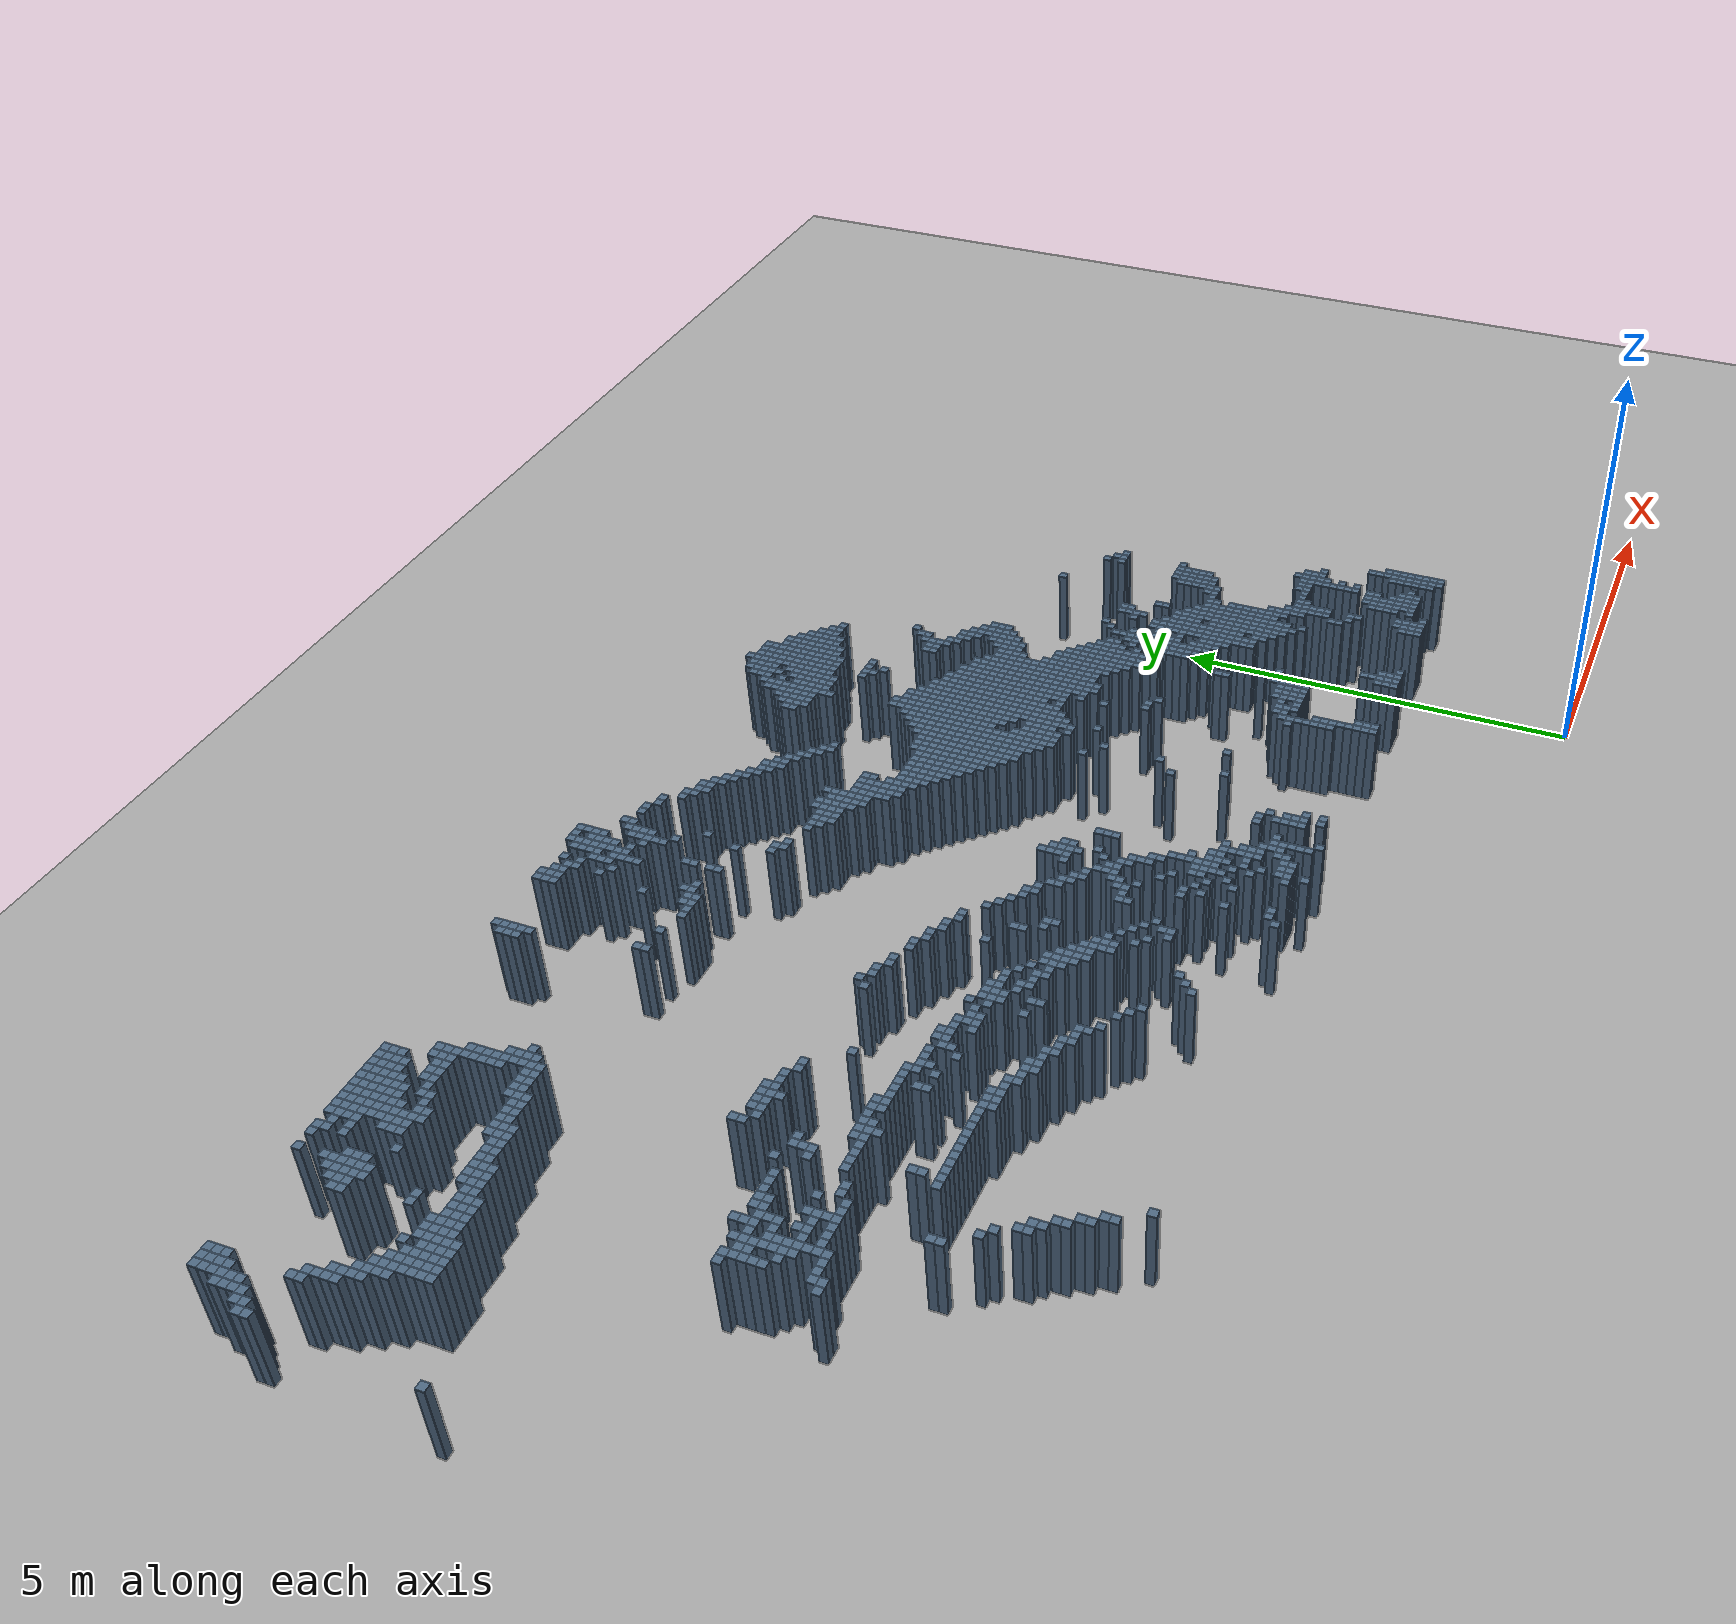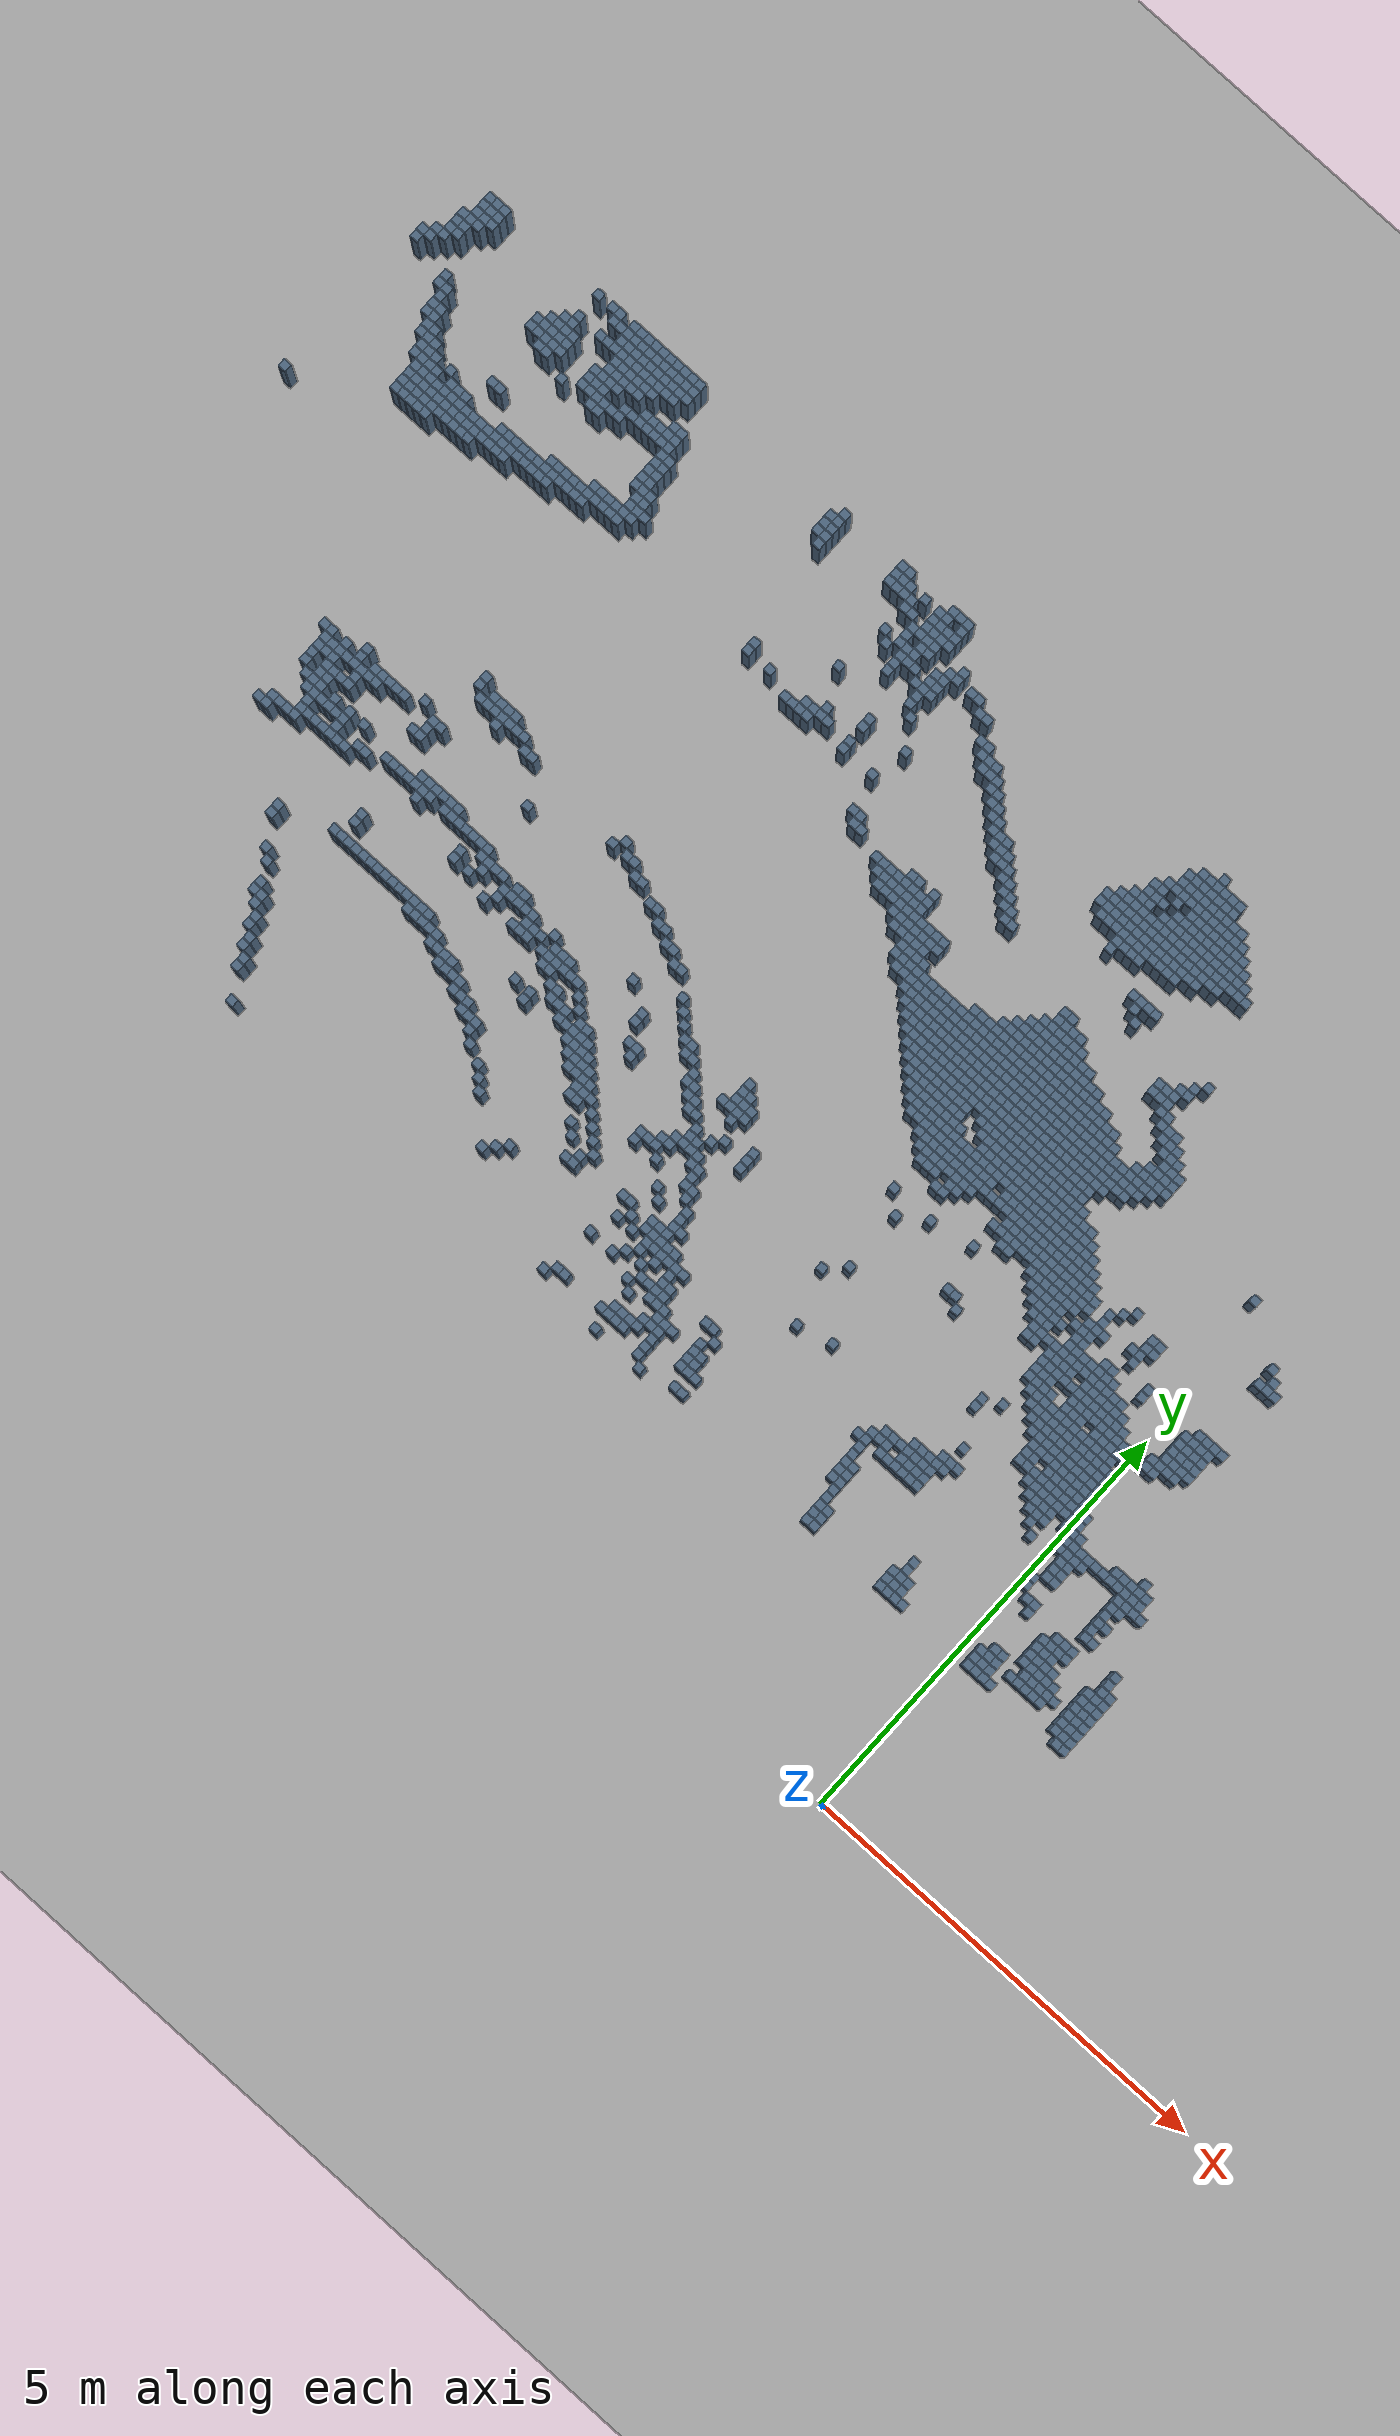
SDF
<?xml version='1.0' encoding='utf-8'?>
<sdf version="1.6">
  <world name="default">
    <gravity>0 0 -9.81</gravity>
    <physics name="default_physics" type="ode">
      <max_step_size>0.001</max_step_size>
      <real_time_update_rate>1000</real_time_update_rate>
    </physics>
    <scene>
      <ambient>0.6 0.6 0.6 1</ambient>
      <shadows>false</shadows>
    </scene>
    <light name="sun" type="directional">
      <pose>0 0 10 0 0 0</pose>
      <diffuse>0.8 0.8 0.8 1</diffuse>
      <direction>-0.5 0.1 -1</direction>
    </light>
    <model name="artificial_flat_ground">
      <static>true</static>
      <link name="ground">
        <collision name="floor_collision">
          <geometry>
            <plane>
              <normal>0 0 1</normal>
              <size>100 100</size>
            </plane>
          </geometry>
        </collision>
        <visual name="floor_visual">
          <geometry>
            <plane>
              <normal>0 0 1</normal>
              <size>100 100</size>
            </plane>
          </geometry>
          <material>
            <ambient>0.65 0.65 0.65 1</ambient>
            <diffuse>0.65 0.65 0.65 1</diffuse>
          </material>
        </visual>
      </link>
    </model>
    <model name="hilti_projected_cells">
      <static>true</static>
      <link name="obstacles">
        <collision name="cell_0_40_collision">
          <pose>-9.95000000 2.05000000 0.50000000 0 0 0</pose>
          <geometry>
            <box>
              <size>0.10000000 0.10000000 1.00000000</size>
            </box>
          </geometry>
        </collision>
        <visual name="cell_0_40_visual">
          <pose>-9.95000000 2.05000000 0.50000000 0 0 0</pose>
          <geometry>
            <box>
              <size>0.10000000 0.10000000 1.00000000</size>
            </box>
          </geometry>
          <material>
            <ambient>0.3 0.4 0.5 1</ambient>
            <diffuse>0.3 0.4 0.5 1</diffuse>
          </material>
        </visual>
        <collision name="cell_0_90_collision">
          <pose>-4.95000000 2.05000000 0.50000000 0 0 0</pose>
          <geometry>
            <box>
              <size>0.10000000 0.10000000 1.00000000</size>
            </box>
          </geometry>
        </collision>
        <visual name="cell_0_90_visual">
          <pose>-4.95000000 2.05000000 0.50000000 0 0 0</pose>
          <geometry>
            <box>
              <size>0.10000000 0.10000000 1.00000000</size>
            </box>
          </geometry>
          <material>
            <ambient>0.3 0.4 0.5 1</ambient>
            <diffuse>0.3 0.4 0.5 1</diffuse>
          </material>
        </visual>
        <collision name="cell_0_96_collision">
          <pose>-4.35000000 2.05000000 0.50000000 0 0 0</pose>
          <geometry>
            <box>
              <size>0.10000000 0.10000000 1.00000000</size>
            </box>
          </geometry>
        </collision>
        <visual name="cell_0_96_visual">
          <pose>-4.35000000 2.05000000 0.50000000 0 0 0</pose>
          <geometry>
            <box>
              <size>0.10000000 0.10000000 1.00000000</size>
            </box>
          </geometry>
          <material>
            <ambient>0.3 0.4 0.5 1</ambient>
            <diffuse>0.3 0.4 0.5 1</diffuse>
          </material>
        </visual>
        <collision name="cell_0_119_collision">
          <pose>-2.05000000 2.05000000 0.50000000 0 0 0</pose>
          <geometry>
            <box>
              <size>0.10000000 0.10000000 1.00000000</size>
            </box>
          </geometry>
        </collision>
        <visual name="cell_0_119_visual">
          <pose>-2.05000000 2.05000000 0.50000000 0 0 0</pose>
          <geometry>
            <box>
              <size>0.10000000 0.10000000 1.00000000</size>
            </box>
          </geometry>
          <material>
            <ambient>0.3 0.4 0.5 1</ambient>
            <diffuse>0.3 0.4 0.5 1</diffuse>
          </material>
        </visual>
        <collision name="cell_0_120_collision">
          <pose>-1.95000000 2.05000000 0.50000000 0 0 0</pose>
          <geometry>
            <box>
              <size>0.10000000 0.10000000 1.00000000</size>
            </box>
          </geometry>
        </collision>
        <visual name="cell_0_120_visual">
          <pose>-1.95000000 2.05000000 0.50000000 0 0 0</pose>
          <geometry>
            <box>
              <size>0.10000000 0.10000000 1.00000000</size>
            </box>
          </geometry>
          <material>
            <ambient>0.3 0.4 0.5 1</ambient>
            <diffuse>0.3 0.4 0.5 1</diffuse>
          </material>
        </visual>
        <collision name="cell_0_129_collision">
          <pose>-1.05000000 2.05000000 0.50000000 0 0 0</pose>
          <geometry>
            <box>
              <size>0.10000000 0.10000000 1.00000000</size>
            </box>
          </geometry>
        </collision>
        <visual name="cell_0_129_visual">
          <pose>-1.05000000 2.05000000 0.50000000 0 0 0</pose>
          <geometry>
            <box>
              <size>0.10000000 0.10000000 1.00000000</size>
            </box>
          </geometry>
          <material>
            <ambient>0.3 0.4 0.5 1</ambient>
            <diffuse>0.3 0.4 0.5 1</diffuse>
          </material>
        </visual>
        <collision name="cell_0_130_collision">
          <pose>-0.95000000 2.05000000 0.50000000 0 0 0</pose>
          <geometry>
            <box>
              <size>0.10000000 0.10000000 1.00000000</size>
            </box>
          </geometry>
        </collision>
        <visual name="cell_0_130_visual">
          <pose>-0.95000000 2.05000000 0.50000000 0 0 0</pose>
          <geometry>
            <box>
              <size>0.10000000 0.10000000 1.00000000</size>
            </box>
          </geometry>
          <material>
            <ambient>0.3 0.4 0.5 1</ambient>
            <diffuse>0.3 0.4 0.5 1</diffuse>
          </material>
        </visual>
        <collision name="cell_0_131_collision">
          <pose>-0.85000000 2.05000000 0.50000000 0 0 0</pose>
          <geometry>
            <box>
              <size>0.10000000 0.10000000 1.00000000</size>
            </box>
          </geometry>
        </collision>
        <visual name="cell_0_131_visual">
          <pose>-0.85000000 2.05000000 0.50000000 0 0 0</pose>
          <geometry>
            <box>
              <size>0.10000000 0.10000000 1.00000000</size>
            </box>
          </geometry>
          <material>
            <ambient>0.3 0.4 0.5 1</ambient>
            <diffuse>0.3 0.4 0.5 1</diffuse>
          </material>
        </visual>
        <collision name="cell_0_132_collision">
          <pose>-0.75000000 2.05000000 0.50000000 0 0 0</pose>
          <geometry>
            <box>
              <size>0.10000000 0.10000000 1.00000000</size>
            </box>
          </geometry>
        </collision>
        <visual name="cell_0_132_visual">
          <pose>-0.75000000 2.05000000 0.50000000 0 0 0</pose>
          <geometry>
            <box>
              <size>0.10000000 0.10000000 1.00000000</size>
            </box>
          </geometry>
          <material>
            <ambient>0.3 0.4 0.5 1</ambient>
            <diffuse>0.3 0.4 0.5 1</diffuse>
          </material>
        </visual>
        <collision name="cell_0_141_collision">
          <pose>0.15000000 2.05000000 0.50000000 0 0 0</pose>
          <geometry>
            <box>
              <size>0.10000000 0.10000000 1.00000000</size>
            </box>
          </geometry>
        </collision>
        <visual name="cell_0_141_visual">
          <pose>0.15000000 2.05000000 0.50000000 0 0 0</pose>
          <geometry>
            <box>
              <size>0.10000000 0.10000000 1.00000000</size>
            </box>
          </geometry>
          <material>
            <ambient>0.3 0.4 0.5 1</ambient>
            <diffuse>0.3 0.4 0.5 1</diffuse>
          </material>
        </visual>
        <collision name="cell_0_142_collision">
          <pose>0.25000000 2.05000000 0.50000000 0 0 0</pose>
          <geometry>
            <box>
              <size>0.10000000 0.10000000 1.00000000</size>
            </box>
          </geometry>
        </collision>
        <visual name="cell_0_142_visual">
          <pose>0.25000000 2.05000000 0.50000000 0 0 0</pose>
          <geometry>
            <box>
              <size>0.10000000 0.10000000 1.00000000</size>
            </box>
          </geometry>
          <material>
            <ambient>0.3 0.4 0.5 1</ambient>
            <diffuse>0.3 0.4 0.5 1</diffuse>
          </material>
        </visual>
        <collision name="cell_0_143_collision">
          <pose>0.35000000 2.05000000 0.50000000 0 0 0</pose>
          <geometry>
            <box>
              <size>0.10000000 0.10000000 1.00000000</size>
            </box>
          </geometry>
        </collision>
        <visual name="cell_0_143_visual">
          <pose>0.35000000 2.05000000 0.50000000 0 0 0</pose>
          <geometry>
            <box>
              <size>0.10000000 0.10000000 1.00000000</size>
            </box>
          </geometry>
          <material>
            <ambient>0.3 0.4 0.5 1</ambient>
            <diffuse>0.3 0.4 0.5 1</diffuse>
          </material>
        </visual>
        <collision name="cell_0_144_collision">
          <pose>0.45000000 2.05000000 0.50000000 0 0 0</pose>
          <geometry>
            <box>
              <size>0.10000000 0.10000000 1.00000000</size>
            </box>
          </geometry>
        </collision>
        <visual name="cell_0_144_visual">
          <pose>0.45000000 2.05000000 0.50000000 0 0 0</pose>
          <geometry>
            <box>
              <size>0.10000000 0.10000000 1.00000000</size>
            </box>
          </geometry>
          <material>
            <ambient>0.3 0.4 0.5 1</ambient>
            <diffuse>0.3 0.4 0.5 1</diffuse>
          </material>
        </visual>
        <collision name="cell_0_153_collision">
          <pose>1.35000000 2.05000000 0.50000000 0 0 0</pose>
          <geometry>
            <box>
              <size>0.10000000 0.10000000 1.00000000</size>
            </box>
          </geometry>
        </collision>
        <visual name="cell_0_153_visual">
          <pose>1.35000000 2.05000000 0.50000000 0 0 0</pose>
          <geometry>
            <box>
              <size>0.10000000 0.10000000 1.00000000</size>
            </box>
          </geometry>
          <material>
            <ambient>0.3 0.4 0.5 1</ambient>
            <diffuse>0.3 0.4 0.5 1</diffuse>
          </material>
        </visual>
        <collision name="cell_0_154_collision">
          <pose>1.45000000 2.05000000 0.50000000 0 0 0</pose>
          <geometry>
            <box>
              <size>0.10000000 0.10000000 1.00000000</size>
            </box>
          </geometry>
        </collision>
        <visual name="cell_0_154_visual">
          <pose>1.45000000 2.05000000 0.50000000 0 0 0</pose>
          <geometry>
            <box>
              <size>0.10000000 0.10000000 1.00000000</size>
            </box>
          </geometry>
          <material>
            <ambient>0.3 0.4 0.5 1</ambient>
            <diffuse>0.3 0.4 0.5 1</diffuse>
          </material>
        </visual>
        <collision name="cell_1_82_collision">
          <pose>-5.75000000 2.15000000 0.50000000 0 0 0</pose>
          <geometry>
            <box>
              <size>0.10000000 0.10000000 1.00000000</size>
            </box>
          </geometry>
        </collision>
        <visual name="cell_1_82_visual">
          <pose>-5.75000000 2.15000000 0.50000000 0 0 0</pose>
          <geometry>
            <box>
              <size>0.10000000 0.10000000 1.00000000</size>
            </box>
          </geometry>
          <material>
            <ambient>0.3 0.4 0.5 1</ambient>
            <diffuse>0.3 0.4 0.5 1</diffuse>
          </material>
        </visual>
        <collision name="cell_1_95_collision">
          <pose>-4.45000000 2.15000000 0.50000000 0 0 0</pose>
          <geometry>
            <box>
              <size>0.10000000 0.10000000 1.00000000</size>
            </box>
          </geometry>
        </collision>
        <visual name="cell_1_95_visual">
          <pose>-4.45000000 2.15000000 0.50000000 0 0 0</pose>
          <geometry>
            <box>
              <size>0.10000000 0.10000000 1.00000000</size>
            </box>
          </geometry>
          <material>
            <ambient>0.3 0.4 0.5 1</ambient>
            <diffuse>0.3 0.4 0.5 1</diffuse>
          </material>
        </visual>
        <collision name="cell_1_100_collision">
          <pose>-3.95000000 2.15000000 0.50000000 0 0 0</pose>
          <geometry>
            <box>
              <size>0.10000000 0.10000000 1.00000000</size>
            </box>
          </geometry>
        </collision>
        <visual name="cell_1_100_visual">
          <pose>-3.95000000 2.15000000 0.50000000 0 0 0</pose>
          <geometry>
            <box>
              <size>0.10000000 0.10000000 1.00000000</size>
            </box>
          </geometry>
          <material>
            <ambient>0.3 0.4 0.5 1</ambient>
            <diffuse>0.3 0.4 0.5 1</diffuse>
          </material>
        </visual>
        <collision name="cell_1_101_collision">
          <pose>-3.85000000 2.15000000 0.50000000 0 0 0</pose>
          <geometry>
            <box>
              <size>0.10000000 0.10000000 1.00000000</size>
            </box>
          </geometry>
        </collision>
        <visual name="cell_1_101_visual">
          <pose>-3.85000000 2.15000000 0.50000000 0 0 0</pose>
          <geometry>
            <box>
              <size>0.10000000 0.10000000 1.00000000</size>
            </box>
          </geometry>
          <material>
            <ambient>0.3 0.4 0.5 1</ambient>
            <diffuse>0.3 0.4 0.5 1</diffuse>
          </material>
        </visual>
        <collision name="cell_1_119_collision">
          <pose>-2.05000000 2.15000000 0.50000000 0 0 0</pose>
          <geometry>
            <box>
              <size>0.10000000 0.10000000 1.00000000</size>
            </box>
          </geometry>
        </collision>
        <visual name="cell_1_119_visual">
          <pose>-2.05000000 2.15000000 0.50000000 0 0 0</pose>
          <geometry>
            <box>
              <size>0.10000000 0.10000000 1.00000000</size>
            </box>
          </geometry>
          <material>
            <ambient>0.3 0.4 0.5 1</ambient>
            <diffuse>0.3 0.4 0.5 1</diffuse>
          </material>
        </visual>
        <collision name="cell_1_120_collision">
          <pose>-1.95000000 2.15000000 0.50000000 0 0 0</pose>
          <geometry>
            <box>
              <size>0.10000000 0.10000000 1.00000000</size>
            </box>
          </geometry>
        </collision>
        <visual name="cell_1_120_visual">
          <pose>-1.95000000 2.15000000 0.50000000 0 0 0</pose>
          <geometry>
            <box>
              <size>0.10000000 0.10000000 1.00000000</size>
            </box>
          </geometry>
          <material>
            <ambient>0.3 0.4 0.5 1</ambient>
            <diffuse>0.3 0.4 0.5 1</diffuse>
          </material>
        </visual>
        <collision name="cell_1_129_collision">
          <pose>-1.05000000 2.15000000 0.50000000 0 0 0</pose>
          <geometry>
            <box>
              <size>0.10000000 0.10000000 1.00000000</size>
            </box>
          </geometry>
        </collision>
        <visual name="cell_1_129_visual">
          <pose>-1.05000000 2.15000000 0.50000000 0 0 0</pose>
          <geometry>
            <box>
              <size>0.10000000 0.10000000 1.00000000</size>
            </box>
          </geometry>
          <material>
            <ambient>0.3 0.4 0.5 1</ambient>
            <diffuse>0.3 0.4 0.5 1</diffuse>
          </material>
        </visual>
        <collision name="cell_1_130_collision">
          <pose>-0.95000000 2.15000000 0.50000000 0 0 0</pose>
          <geometry>
            <box>
              <size>0.10000000 0.10000000 1.00000000</size>
            </box>
          </geometry>
        </collision>
        <visual name="cell_1_130_visual">
          <pose>-0.95000000 2.15000000 0.50000000 0 0 0</pose>
          <geometry>
            <box>
              <size>0.10000000 0.10000000 1.00000000</size>
            </box>
          </geometry>
          <material>
            <ambient>0.3 0.4 0.5 1</ambient>
            <diffuse>0.3 0.4 0.5 1</diffuse>
          </material>
        </visual>
        <collision name="cell_1_131_collision">
          <pose>-0.85000000 2.15000000 0.50000000 0 0 0</pose>
          <geometry>
            <box>
              <size>0.10000000 0.10000000 1.00000000</size>
            </box>
          </geometry>
        </collision>
        <visual name="cell_1_131_visual">
          <pose>-0.85000000 2.15000000 0.50000000 0 0 0</pose>
          <geometry>
            <box>
              <size>0.10000000 0.10000000 1.00000000</size>
            </box>
          </geometry>
          <material>
            <ambient>0.3 0.4 0.5 1</ambient>
            <diffuse>0.3 0.4 0.5 1</diffuse>
          </material>
        </visual>
        <collision name="cell_1_141_collision">
          <pose>0.15000000 2.15000000 0.50000000 0 0 0</pose>
          <geometry>
            <box>
              <size>0.10000000 0.10000000 1.00000000</size>
            </box>
          </geometry>
        </collision>
        <visual name="cell_1_141_visual">
          <pose>0.15000000 2.15000000 0.50000000 0 0 0</pose>
          <geometry>
            <box>
              <size>0.10000000 0.10000000 1.00000000</size>
            </box>
          </geometry>
          <material>
            <ambient>0.3 0.4 0.5 1</ambient>
            <diffuse>0.3 0.4 0.5 1</diffuse>
          </material>
        </visual>
        <collision name="cell_1_142_collision">
          <pose>0.25000000 2.15000000 0.50000000 0 0 0</pose>
          <geometry>
            <box>
              <size>0.10000000 0.10000000 1.00000000</size>
            </box>
          </geometry>
        </collision>
        <visual name="cell_1_142_visual">
          <pose>0.25000000 2.15000000 0.50000000 0 0 0</pose>
          <geometry>
            <box>
              <size>0.10000000 0.10000000 1.00000000</size>
            </box>
          </geometry>
          <material>
            <ambient>0.3 0.4 0.5 1</ambient>
            <diffuse>0.3 0.4 0.5 1</diffuse>
          </material>
        </visual>
        <collision name="cell_1_143_collision">
          <pose>0.35000000 2.15000000 0.50000000 0 0 0</pose>
          <geometry>
            <box>
              <size>0.10000000 0.10000000 1.00000000</size>
            </box>
          </geometry>
        </collision>
        <visual name="cell_1_143_visual">
          <pose>0.35000000 2.15000000 0.50000000 0 0 0</pose>
          <geometry>
            <box>
              <size>0.10000000 0.10000000 1.00000000</size>
            </box>
          </geometry>
          <material>
            <ambient>0.3 0.4 0.5 1</ambient>
            <diffuse>0.3 0.4 0.5 1</diffuse>
          </material>
        </visual>
        <collision name="cell_1_152_collision">
          <pose>1.25000000 2.15000000 0.50000000 0 0 0</pose>
          <geometry>
            <box>
              <size>0.10000000 0.10000000 1.00000000</size>
            </box>
          </geometry>
        </collision>
        <visual name="cell_1_152_visual">
          <pose>1.25000000 2.15000000 0.50000000 0 0 0</pose>
          <geometry>
            <box>
              <size>0.10000000 0.10000000 1.00000000</size>
            </box>
          </geometry>
          <material>
            <ambient>0.3 0.4 0.5 1</ambient>
            <diffuse>0.3 0.4 0.5 1</diffuse>
          </material>
        </visual>
        <collision name="cell_1_153_collision">
          <pose>1.35000000 2.15000000 0.50000000 0 0 0</pose>
          <geometry>
            <box>
              <size>0.10000000 0.10000000 1.00000000</size>
            </box>
          </geometry>
        </collision>
        <visual name="cell_1_153_visual">
          <pose>1.35000000 2.15000000 0.50000000 0 0 0</pose>
          <geometry>
            <box>
              <size>0.10000000 0.10000000 1.00000000</size>
            </box>
          </geometry>
          <material>
            <ambient>0.3 0.4 0.5 1</ambient>
            <diffuse>0.3 0.4 0.5 1</diffuse>
          </material>
        </visual>
        <collision name="cell_1_154_collision">
          <pose>1.45000000 2.15000000 0.50000000 0 0 0</pose>
          <geometry>
            <box>
              <size>0.10000000 0.10000000 1.00000000</size>
            </box>
          </geometry>
        </collision>
        <visual name="cell_1_154_visual">
          <pose>1.45000000 2.15000000 0.50000000 0 0 0</pose>
          <geometry>
            <box>
              <size>0.10000000 0.10000000 1.00000000</size>
            </box>
          </geometry>
          <material>
            <ambient>0.3 0.4 0.5 1</ambient>
            <diffuse>0.3 0.4 0.5 1</diffuse>
          </material>
        </visual>
        <collision name="cell_2_83_collision">
          <pose>-5.65000000 2.25000000 0.50000000 0 0 0</pose>
          <geometry>
            <box>
              <size>0.10000000 0.10000000 1.00000000</size>
            </box>
          </geometry>
        </collision>
        <visual name="cell_2_83_visual">
          <pose>-5.65000000 2.25000000 0.50000000 0 0 0</pose>
          <geometry>
            <box>
              <size>0.10000000 0.10000000 1.00000000</size>
            </box>
          </geometry>
          <material>
            <ambient>0.3 0.4 0.5 1</ambient>
            <diffuse>0.3 0.4 0.5 1</diffuse>
          </material>
        </visual>
        <collision name="cell_2_84_collision">
          <pose>-5.55000000 2.25000000 0.50000000 0 0 0</pose>
          <geometry>
            <box>
              <size>0.10000000 0.10000000 1.00000000</size>
            </box>
          </geometry>
        </collision>
        <visual name="cell_2_84_visual">
          <pose>-5.55000000 2.25000000 0.50000000 0 0 0</pose>
          <geometry>
            <box>
              <size>0.10000000 0.10000000 1.00000000</size>
            </box>
          </geometry>
          <material>
            <ambient>0.3 0.4 0.5 1</ambient>
            <diffuse>0.3 0.4 0.5 1</diffuse>
          </material>
        </visual>
        <collision name="cell_2_89_collision">
          <pose>-5.05000000 2.25000000 0.50000000 0 0 0</pose>
          <geometry>
            <box>
              <size>0.10000000 0.10000000 1.00000000</size>
            </box>
          </geometry>
        </collision>
        <visual name="cell_2_89_visual">
          <pose>-5.05000000 2.25000000 0.50000000 0 0 0</pose>
          <geometry>
            <box>
              <size>0.10000000 0.10000000 1.00000000</size>
            </box>
          </geometry>
          <material>
            <ambient>0.3 0.4 0.5 1</ambient>
            <diffuse>0.3 0.4 0.5 1</diffuse>
          </material>
        </visual>
        <collision name="cell_2_90_collision">
          <pose>-4.95000000 2.25000000 0.50000000 0 0 0</pose>
          <geometry>
            <box>
              <size>0.10000000 0.10000000 1.00000000</size>
            </box>
          </geometry>
        </collision>
        <visual name="cell_2_90_visual">
          <pose>-4.95000000 2.25000000 0.50000000 0 0 0</pose>
          <geometry>
            <box>
              <size>0.10000000 0.10000000 1.00000000</size>
            </box>
          </geometry>
          <material>
            <ambient>0.3 0.4 0.5 1</ambient>
            <diffuse>0.3 0.4 0.5 1</diffuse>
          </material>
        </visual>
        <collision name="cell_2_91_collision">
          <pose>-4.85000000 2.25000000 0.50000000 0 0 0</pose>
          <geometry>
            <box>
              <size>0.10000000 0.10000000 1.00000000</size>
            </box>
          </geometry>
        </collision>
        <visual name="cell_2_91_visual">
          <pose>-4.85000000 2.25000000 0.50000000 0 0 0</pose>
          <geometry>
            <box>
              <size>0.10000000 0.10000000 1.00000000</size>
            </box>
          </geometry>
          <material>
            <ambient>0.3 0.4 0.5 1</ambient>
            <diffuse>0.3 0.4 0.5 1</diffuse>
          </material>
        </visual>
        <collision name="cell_2_92_collision">
          <pose>-4.75000000 2.25000000 0.50000000 0 0 0</pose>
          <geometry>
            <box>
              <size>0.10000000 0.10000000 1.00000000</size>
            </box>
          </geometry>
        </collision>
        <visual name="cell_2_92_visual">
          <pose>-4.75000000 2.25000000 0.50000000 0 0 0</pose>
          <geometry>
            <box>
              <size>0.10000000 0.10000000 1.00000000</size>
            </box>
          </geometry>
          <material>
            <ambient>0.3 0.4 0.5 1</ambient>
            <diffuse>0.3 0.4 0.5 1</diffuse>
          </material>
        </visual>
        <collision name="cell_2_95_collision">
          <pose>-4.45000000 2.25000000 0.50000000 0 0 0</pose>
          <geometry>
            <box>
              <size>0.10000000 0.10000000 1.00000000</size>
            </box>
          </geometry>
        </collision>
        <visual name="cell_2_95_visual">
          <pose>-4.45000000 2.25000000 0.50000000 0 0 0</pose>
          <geometry>
            <box>
              <size>0.10000000 0.10000000 1.00000000</size>
            </box>
          </geometry>
          <material>
            <ambient>0.3 0.4 0.5 1</ambient>
            <diffuse>0.3 0.4 0.5 1</diffuse>
          </material>
        </visual>
        <collision name="cell_2_119_collision">
          <pose>-2.05000000 2.25000000 0.50000000 0 0 0</pose>
          <geometry>
            <box>
              <size>0.10000000 0.10000000 1.00000000</size>
            </box>
          </geometry>
        </collision>
        <visual name="cell_2_119_visual">
          <pose>-2.05000000 2.25000000 0.50000000 0 0 0</pose>
          <geometry>
            <box>
              <size>0.10000000 0.10000000 1.00000000</size>
            </box>
          </geometry>
          <material>
            <ambient>0.3 0.4 0.5 1</ambient>
            <diffuse>0.3 0.4 0.5 1</diffuse>
          </material>
        </visual>
        <collision name="cell_2_120_collision">
          <pose>-1.95000000 2.25000000 0.50000000 0 0 0</pose>
          <geometry>
            <box>
              <size>0.10000000 0.10000000 1.00000000</size>
            </box>
          </geometry>
        </collision>
        <visual name="cell_2_120_visual">
          <pose>-1.95000000 2.25000000 0.50000000 0 0 0</pose>
          <geometry>
            <box>
              <size>0.10000000 0.10000000 1.00000000</size>
            </box>
          </geometry>
          <material>
            <ambient>0.3 0.4 0.5 1</ambient>
            <diffuse>0.3 0.4 0.5 1</diffuse>
          </material>
        </visual>
        <collision name="cell_2_129_collision">
          <pose>-1.05000000 2.25000000 0.50000000 0 0 0</pose>
          <geometry>
            <box>
              <size>0.10000000 0.10000000 1.00000000</size>
            </box>
          </geometry>
        </collision>
        <visual name="cell_2_129_visual">
          <pose>-1.05000000 2.25000000 0.50000000 0 0 0</pose>
          <geometry>
            <box>
              <size>0.10000000 0.10000000 1.00000000</size>
            </box>
          </geometry>
          <material>
            <ambient>0.3 0.4 0.5 1</ambient>
            <diffuse>0.3 0.4 0.5 1</diffuse>
          </material>
        </visual>
        <collision name="cell_2_130_collision">
          <pose>-0.95000000 2.25000000 0.50000000 0 0 0</pose>
          <geometry>
            <box>
              <size>0.10000000 0.10000000 1.00000000</size>
            </box>
          </geometry>
        </collision>
        <visual name="cell_2_130_visual">
          <pose>-0.95000000 2.25000000 0.50000000 0 0 0</pose>
          <geometry>
            <box>
              <size>0.10000000 0.10000000 1.00000000</size>
            </box>
          </geometry>
          <material>
            <ambient>0.3 0.4 0.5 1</ambient>
            <diffuse>0.3 0.4 0.5 1</diffuse>
          </material>
        </visual>
        <collision name="cell_2_131_collision">
          <pose>-0.85000000 2.25000000 0.50000000 0 0 0</pose>
          <geometry>
            <box>
              <size>0.10000000 0.10000000 1.00000000</size>
            </box>
          </geometry>
        </collision>
        <visual name="cell_2_131_visual">
          <pose>-0.85000000 2.25000000 0.50000000 0 0 0</pose>
          <geometry>
            <box>
              <size>0.10000000 0.10000000 1.00000000</size>
            </box>
          </geometry>
          <material>
            <ambient>0.3 0.4 0.5 1</ambient>
            <diffuse>0.3 0.4 0.5 1</diffuse>
          </material>
        </visual>
        <collision name="cell_2_141_collision">
          <pose>0.15000000 2.25000000 0.50000000 0 0 0</pose>
          <geometry>
            <box>
              <size>0.10000000 0.10000000 1.00000000</size>
            </box>
          </geometry>
        </collision>
        <visual name="cell_2_141_visual">
          <pose>0.15000000 2.25000000 0.50000000 0 0 0</pose>
          <geometry>
            <box>
              <size>0.10000000 0.10000000 1.00000000</size>
            </box>
          </geometry>
          <material>
            <ambient>0.3 0.4 0.5 1</ambient>
            <diffuse>0.3 0.4 0.5 1</diffuse>
          </material>
        </visual>
        <collision name="cell_2_142_collision">
          <pose>0.25000000 2.25000000 0.50000000 0 0 0</pose>
          <geometry>
            <box>
              <size>0.10000000 0.10000000 1.00000000</size>
            </box>
          </geometry>
        </collision>
        <visual name="cell_2_142_visual">
          <pose>0.25000000 2.25000000 0.50000000 0 0 0</pose>
          <geometry>
            <box>
              <size>0.10000000 0.10000000 1.00000000</size>
            </box>
          </geometry>
          <material>
            <ambient>0.3 0.4 0.5 1</ambient>
            <diffuse>0.3 0.4 0.5 1</diffuse>
          </material>
        </visual>
        <collision name="cell_2_143_collision">
          <pose>0.35000000 2.25000000 0.50000000 0 0 0</pose>
          <geometry>
            <box>
              <size>0.10000000 0.10000000 1.00000000</size>
            </box>
          </geometry>
        </collision>
        <visual name="cell_2_143_visual">
          <pose>0.35000000 2.25000000 0.50000000 0 0 0</pose>
          <geometry>
            <box>
              <size>0.10000000 0.10000000 1.00000000</size>
            </box>
          </geometry>
          <material>
            <ambient>0.3 0.4 0.5 1</ambient>
            <diffuse>0.3 0.4 0.5 1</diffuse>
          </material>
        </visual>
        <collision name="cell_2_145_collision">
          <pose>0.55000000 2.25000000 0.50000000 0 0 0</pose>
          <geometry>
            <box>
              <size>0.10000000 0.10000000 1.00000000</size>
            </box>
          </geometry>
        </collision>
        <visual name="cell_2_145_visual">
          <pose>0.55000000 2.25000000 0.50000000 0 0 0</pose>
          <geometry>
            <box>
              <size>0.10000000 0.10000000 1.00000000</size>
            </box>
          </geometry>
          <material>
            <ambient>0.3 0.4 0.5 1</ambient>
            <diffuse>0.3 0.4 0.5 1</diffuse>
          </material>
        </visual>
        <collision name="cell_2_146_collision">
          <pose>0.65000000 2.25000000 0.50000000 0 0 0</pose>
          <geometry>
            <box>
              <size>0.10000000 0.10000000 1.00000000</size>
            </box>
          </geometry>
        </collision>
        <visual name="cell_2_146_visual">
          <pose>0.65000000 2.25000000 0.50000000 0 0 0</pose>
          <geometry>
            <box>
              <size>0.10000000 0.10000000 1.00000000</size>
            </box>
          </geometry>
          <material>
            <ambient>0.3 0.4 0.5 1</ambient>
            <diffuse>0.3 0.4 0.5 1</diffuse>
          </material>
        </visual>
        <collision name="cell_2_147_collision">
          <pose>0.75000000 2.25000000 0.50000000 0 0 0</pose>
          <geometry>
            <box>
              <size>0.10000000 0.10000000 1.00000000</size>
            </box>
          </geometry>
        </collision>
        <visual name="cell_2_147_visual">
          <pose>0.75000000 2.25000000 0.50000000 0 0 0</pose>
          <geometry>
            <box>
              <size>0.10000000 0.10000000 1.00000000</size>
            </box>
          </geometry>
          <material>
            <ambient>0.3 0.4 0.5 1</ambient>
            <diffuse>0.3 0.4 0.5 1</diffuse>
          </material>
        </visual>
        <collision name="cell_2_148_collision">
          <pose>0.85000000 2.25000000 0.50000000 0 0 0</pose>
          <geometry>
            <box>
              <size>0.10000000 0.10000000 1.00000000</size>
            </box>
          </geometry>
        </collision>
        <visual name="cell_2_148_visual">
          <pose>0.85000000 2.25000000 0.50000000 0 0 0</pose>
          <geometry>
            <box>
              <size>0.10000000 0.10000000 1.00000000</size>
            </box>
          </geometry>
          <material>
            <ambient>0.3 0.4 0.5 1</ambient>
            <diffuse>0.3 0.4 0.5 1</diffuse>
          </material>
        </visual>
        <collision name="cell_2_149_collision">
          <pose>0.95000000 2.25000000 0.50000000 0 0 0</pose>
          <geometry>
            <box>
              <size>0.10000000 0.10000000 1.00000000</size>
            </box>
          </geometry>
        </collision>
        <visual name="cell_2_149_visual">
          <pose>0.95000000 2.25000000 0.50000000 0 0 0</pose>
          <geometry>
            <box>
              <size>0.10000000 0.10000000 1.00000000</size>
            </box>
          </geometry>
          <material>
            <ambient>0.3 0.4 0.5 1</ambient>
            <diffuse>0.3 0.4 0.5 1</diffuse>
          </material>
        </visual>
        <collision name="cell_2_152_collision">
          <pose>1.25000000 2.25000000 0.50000000 0 0 0</pose>
          <geometry>
            <box>
              <size>0.10000000 0.10000000 1.00000000</size>
            </box>
          </geometry>
        </collision>
        <visual name="cell_2_152_visual">
          <pose>1.25000000 2.25000000 0.50000000 0 0 0</pose>
          <geometry>
            <box>
              <size>0.10000000 0.10000000 1.00000000</size>
            </box>
          </geometry>
          <material>
            <ambient>0.3 0.4 0.5 1</ambient>
            <diffuse>0.3 0.4 0.5 1</diffuse>
          </material>
        </visual>
        <collision name="cell_2_153_collision">
          <pose>1.35000000 2.25000000 0.50000000 0 0 0</pose>
          <geometry>
            <box>
              <size>0.10000000 0.10000000 1.00000000</size>
            </box>
          </geometry>
        </collision>
        <visual name="cell_2_153_visual">
          <pose>1.35000000 2.25000000 0.50000000 0 0 0</pose>
          <geometry>
            <box>
              <size>0.10000000 0.10000000 1.00000000</size>
            </box>
          </geometry>
          <material>
            <ambient>0.3 0.4 0.5 1</ambient>
            <diffuse>0.3 0.4 0.5 1</diffuse>
          </material>
        </visual>
        <collision name="cell_2_154_collision">
          <pose>1.45000000 2.25000000 0.50000000 0 0 0</pose>
          <geometry>
            <box>
              <size>0.10000000 0.10000000 1.00000000</size>
            </box>
          </geometry>
        </collision>
        <visual name="cell_2_154_visual">
          <pose>1.45000000 2.25000000 0.50000000 0 0 0</pose>
          <geometry>
            <box>
              <size>0.10000000 0.10000000 1.00000000</size>
            </box>
          </geometry>
          <material>
            <ambient>0.3 0.4 0.5 1</ambient>
            <diffuse>0.3 0.4 0.5 1</diffuse>
          </material>
        </visual>
        <collision name="cell_3_38_collision">
          <pose>-10.15000000 2.35000000 0.50000000 0 0 0</pose>
          <geometry>
            <box>
              <size>0.10000000 0.10000000 1.00000000</size>
            </box>
          </geometry>
        </collision>
        <visual name="cell_3_38_visual">
          <pose>-10.15000000 2.35000000 0.50000000 0 0 0</pose>
          <geometry>
            <box>
              <size>0.10000000 0.10000000 1.00000000</size>
            </box>
          </geometry>
          <material>
            <ambient>0.3 0.4 0.5 1</ambient>
            <diffuse>0.3 0.4 0.5 1</diffuse>
          </material>
        </visual>
        <collision name="cell_3_90_collision">
          <pose>-4.95000000 2.35000000 0.50000000 0 0 0</pose>
          <geometry>
            <box>
              <size>0.10000000 0.10000000 1.00000000</size>
            </box>
          </geometry>
        </collision>
        <visual name="cell_3_90_visual">
          <pose>-4.95000000 2.35000000 0.50000000 0 0 0</pose>
          <geometry>
            <box>
              <size>0.10000000 0.10000000 1.00000000</size>
            </box>
          </geometry>
          <material>
            <ambient>0.3 0.4 0.5 1</ambient>
            <diffuse>0.3 0.4 0.5 1</diffuse>
          </material>
        </visual>
        <collision name="cell_3_91_collision">
          <pose>-4.85000000 2.35000000 0.50000000 0 0 0</pose>
          <geometry>
            <box>
              <size>0.10000000 0.10000000 1.00000000</size>
            </box>
          </geometry>
        </collision>
        <visual name="cell_3_91_visual">
          <pose>-4.85000000 2.35000000 0.50000000 0 0 0</pose>
          <geometry>
            <box>
              <size>0.10000000 0.10000000 1.00000000</size>
            </box>
          </geometry>
          <material>
            <ambient>0.3 0.4 0.5 1</ambient>
            <diffuse>0.3 0.4 0.5 1</diffuse>
          </material>
        </visual>
        <collision name="cell_3_92_collision">
          <pose>-4.75000000 2.35000000 0.50000000 0 0 0</pose>
          <geometry>
            <box>
              <size>0.10000000 0.10000000 1.00000000</size>
            </box>
          </geometry>
        </collision>
        <visual name="cell_3_92_visual">
          <pose>-4.75000000 2.35000000 0.50000000 0 0 0</pose>
          <geometry>
            <box>
              <size>0.10000000 0.10000000 1.00000000</size>
            </box>
          </geometry>
          <material>
            <ambient>0.3 0.4 0.5 1</ambient>
            <diffuse>0.3 0.4 0.5 1</diffuse>
          </material>
        </visual>
        <collision name="cell_3_93_collision">
          <pose>-4.65000000 2.35000000 0.50000000 0 0 0</pose>
          <geometry>
            <box>
              <size>0.10000000 0.10000000 1.00000000</size>
            </box>
          </geometry>
        </collision>
        <visual name="cell_3_93_visual">
          <pose>-4.65000000 2.35000000 0.50000000 0 0 0</pose>
          <geometry>
            <box>
              <size>0.10000000 0.10000000 1.00000000</size>
            </box>
          </geometry>
          <material>
            <ambient>0.3 0.4 0.5 1</ambient>
            <diffuse>0.3 0.4 0.5 1</diffuse>
          </material>
        </visual>
        <collision name="cell_3_95_collision">
          <pose>-4.45000000 2.35000000 0.50000000 0 0 0</pose>
          <geometry>
            <box>
              <size>0.10000000 0.10000000 1.00000000</size>
            </box>
          </geometry>
        </collision>
        <visual name="cell_3_95_visual">
          <pose>-4.45000000 2.35000000 0.50000000 0 0 0</pose>
          <geometry>
            <box>
              <size>0.10000000 0.10000000 1.00000000</size>
            </box>
          </geometry>
          <material>
            <ambient>0.3 0.4 0.5 1</ambient>
            <diffuse>0.3 0.4 0.5 1</diffuse>
          </material>
        </visual>
        <collision name="cell_3_99_collision">
          <pose>-4.05000000 2.35000000 0.50000000 0 0 0</pose>
          <geometry>
            <box>
              <size>0.10000000 0.10000000 1.00000000</size>
            </box>
          </geometry>
        </collision>
        <visual name="cell_3_99_visual">
          <pose>-4.05000000 2.35000000 0.50000000 0 0 0</pose>
          <geometry>
            <box>
              <size>0.10000000 0.10000000 1.00000000</size>
            </box>
          </geometry>
          <material>
            <ambient>0.3 0.4 0.5 1</ambient>
            <diffuse>0.3 0.4 0.5 1</diffuse>
          </material>
        </visual>
        <collision name="cell_3_100_collision">
          <pose>-3.95000000 2.35000000 0.50000000 0 0 0</pose>
          <geometry>
            <box>
              <size>0.10000000 0.10000000 1.00000000</size>
            </box>
          </geometry>
        </collision>
        <visual name="cell_3_100_visual">
          <pose>-3.95000000 2.35000000 0.50000000 0 0 0</pose>
          <geometry>
            <box>
              <size>0.10000000 0.10000000 1.00000000</size>
            </box>
          </geometry>
          <material>
            <ambient>0.3 0.4 0.5 1</ambient>
            <diffuse>0.3 0.4 0.5 1</diffuse>
          </material>
        </visual>
        <collision name="cell_3_101_collision">
          <pose>-3.85000000 2.35000000 0.50000000 0 0 0</pose>
          <geometry>
            <box>
              <size>0.10000000 0.10000000 1.00000000</size>
            </box>
          </geometry>
        </collision>
        <visual name="cell_3_101_visual">
          <pose>-3.85000000 2.35000000 0.50000000 0 0 0</pose>
          <geometry>
            <box>
              <size>0.10000000 0.10000000 1.00000000</size>
            </box>
          </geometry>
          <material>
            <ambient>0.3 0.4 0.5 1</ambient>
            <diffuse>0.3 0.4 0.5 1</diffuse>
          </material>
        </visual>
        <collision name="cell_3_119_collision">
          <pose>-2.05000000 2.35000000 0.50000000 0 0 0</pose>
          <geometry>
            <box>
              <size>0.10000000 0.10000000 1.00000000</size>
            </box>
          </geometry>
        </collision>
        <visual name="cell_3_119_visual">
          <pose>-2.05000000 2.35000000 0.50000000 0 0 0</pose>
          <geometry>
            <box>
              <size>0.10000000 0.10000000 1.00000000</size>
            </box>
          </geometry>
          <material>
            <ambient>0.3 0.4 0.5 1</ambient>
            <diffuse>0.3 0.4 0.5 1</diffuse>
          </material>
        </visual>
        <collision name="cell_3_130_collision">
          <pose>-0.95000000 2.35000000 0.50000000 0 0 0</pose>
          <geometry>
            <box>
              <size>0.10000000 0.10000000 1.00000000</size>
            </box>
          </geometry>
        </collision>
        <visual name="cell_3_130_visual">
          <pose>-0.95000000 2.35000000 0.50000000 0 0 0</pose>
          <geometry>
            <box>
              <size>0.10000000 0.10000000 1.00000000</size>
            </box>
          </geometry>
          <material>
            <ambient>0.3 0.4 0.5 1</ambient>
            <diffuse>0.3 0.4 0.5 1</diffuse>
          </material>
        </visual>
        <collision name="cell_3_142_collision">
          <pose>0.25000000 2.35000000 0.50000000 0 0 0</pose>
          <geometry>
            <box>
              <size>0.10000000 0.10000000 1.00000000</size>
            </box>
          </geometry>
        </collision>
        <visual name="cell_3_142_visual">
          <pose>0.25000000 2.35000000 0.50000000 0 0 0</pose>
          <geometry>
            <box>
              <size>0.10000000 0.10000000 1.00000000</size>
            </box>
          </geometry>
          <material>
            <ambient>0.3 0.4 0.5 1</ambient>
            <diffuse>0.3 0.4 0.5 1</diffuse>
          </material>
        </visual>
        <collision name="cell_3_143_collision">
          <pose>0.35000000 2.35000000 0.50000000 0 0 0</pose>
          <geometry>
            <box>
              <size>0.10000000 0.10000000 1.00000000</size>
            </box>
          </geometry>
        </collision>
        <visual name="cell_3_143_visual">
          <pose>0.35000000 2.35000000 0.50000000 0 0 0</pose>
          <geometry>
            <box>
              <size>0.10000000 0.10000000 1.00000000</size>
            </box>
          </geometry>
          <material>
            <ambient>0.3 0.4 0.5 1</ambient>
            <diffuse>0.3 0.4 0.5 1</diffuse>
          </material>
        </visual>
        <collision name="cell_3_146_collision">
          <pose>0.65000000 2.35000000 0.50000000 0 0 0</pose>
          <geometry>
            <box>
              <size>0.10000000 0.10000000 1.00000000</size>
            </box>
          </geometry>
        </collision>
        <visual name="cell_3_146_visual">
          <pose>0.65000000 2.35000000 0.50000000 0 0 0</pose>
          <geometry>
            <box>
              <size>0.10000000 0.10000000 1.00000000</size>
            </box>
          </geometry>
          <material>
            <ambient>0.3 0.4 0.5 1</ambient>
            <diffuse>0.3 0.4 0.5 1</diffuse>
          </material>
        </visual>
        <collision name="cell_3_147_collision">
          <pose>0.75000000 2.35000000 0.50000000 0 0 0</pose>
          <geometry>
            <box>
              <size>0.10000000 0.10000000 1.00000000</size>
            </box>
          </geometry>
        </collision>
        <visual name="cell_3_147_visual">
          <pose>0.75000000 2.35000000 0.50000000 0 0 0</pose>
          <geometry>
            <box>
              <size>0.10000000 0.10000000 1.00000000</size>
            </box>
          </geometry>
          <material>
            <ambient>0.3 0.4 0.5 1</ambient>
            <diffuse>0.3 0.4 0.5 1</diffuse>
          </material>
        </visual>
        <collision name="cell_3_148_collision">
          <pose>0.85000000 2.35000000 0.50000000 0 0 0</pose>
          <geometry>
            <box>
              <size>0.10000000 0.10000000 1.00000000</size>
            </box>
          </geometry>
        </collision>
        <visual name="cell_3_148_visual">
          <pose>0.85000000 2.35000000 0.50000000 0 0 0</pose>
          <geometry>
            <box>
              <size>0.10000000 0.10000000 1.00000000</size>
            </box>
          </geometry>
          <material>
            <ambient>0.3 0.4 0.5 1</ambient>
            <diffuse>0.3 0.4 0.5 1</diffuse>
          </material>
        </visual>
        <collision name="cell_3_149_collision">
          <pose>0.95000000 2.35000000 0.50000000 0 0 0</pose>
          <geometry>
            <box>
              <size>0.10000000 0.10000000 1.00000000</size>
            </box>
          </geometry>
        </collision>
        <visual name="cell_3_149_visual">
          <pose>0.95000000 2.35000000 0.50000000 0 0 0</pose>
          <geometry>
            <box>
              <size>0.10000000 0.10000000 1.00000000</size>
            </box>
          </geometry>
          <material>
            <ambient>0.3 0.4 0.5 1</ambient>
            <diffuse>0.3 0.4 0.5 1</diffuse>
          </material>
        </visual>
        <collision name="cell_3_150_collision">
          <pose>1.05000000 2.35000000 0.50000000 0 0 0</pose>
          <geometry>
            <box>
              <size>0.10000000 0.10000000 1.00000000</size>
            </box>
          </geometry>
        </collision>
        <visual name="cell_3_150_visual">
          <pose>1.05000000 2.35000000 0.50000000 0 0 0</pose>
          <geometry>
            <box>
              <size>0.10000000 0.10000000 1.00000000</size>
            </box>
          </geometry>
          <material>
            <ambient>0.3 0.4 0.5 1</ambient>
            <diffuse>0.3 0.4 0.5 1</diffuse>
          </material>
        </visual>
        <collision name="cell_3_152_collision">
          <pose>1.25000000 2.35000000 0.50000000 0 0 0</pose>
          <geometry>
            <box>
              <size>0.10000000 0.10000000 1.00000000</size>
            </box>
          </geometry>
        </collision>
        <visual name="cell_3_152_visual">
          <pose>1.25000000 2.35000000 0.50000000 0 0 0</pose>
          <geometry>
            <box>
              <size>0.10000000 0.10000000 1.00000000</size>
            </box>
          </geometry>
          <material>
            <ambient>0.3 0.4 0.5 1</ambient>
            <diffuse>0.3 0.4 0.5 1</diffuse>
          </material>
        </visual>
        <collision name="cell_3_153_collision">
          <pose>1.35000000 2.35000000 0.50000000 0 0 0</pose>
          <geometry>
            <box>
              <size>0.10000000 0.10000000 1.00000000</size>
            </box>
          </geometry>
        </collision>
        <visual name="cell_3_153_visual">
          <pose>1.35000000 2.35000000 0.50000000 0 0 0</pose>
          <geometry>
            <box>
              <size>0.10000000 0.10000000 1.00000000</size>
            </box>
          </geometry>
          <material>
            <ambient>0.3 0.4 0.5 1</ambient>
            <diffuse>0.3 0.4 0.5 1</diffuse>
          </material>
        </visual>
        <collision name="cell_3_154_collision">
          <pose>1.45000000 2.35000000 0.50000000 0 0 0</pose>
          <geometry>
            <box>
              <size>0.10000000 0.10000000 1.00000000</size>
            </box>
          </geometry>
        </collision>
        <visual name="cell_3_154_visual">
          <pose>1.45000000 2.35000000 0.50000000 0 0 0</pose>
          <geometry>
            <box>
              <size>0.10000000 0.10000000 1.00000000</size>
            </box>
          </geometry>
          <material>
            <ambient>0.3 0.4 0.5 1</ambient>
            <diffuse>0.3 0.4 0.5 1</diffuse>
          </material>
        </visual>
        <collision name="cell_4_38_collision">
          <pose>-10.15000000 2.45000000 0.50000000 0 0 0</pose>
          <geometry>
            <box>
              <size>0.10000000 0.10000000 1.00000000</size>
            </box>
          </geometry>
        </collision>
        <visual name="cell_4_38_visual">
          <pose>-10.15000000 2.45000000 0.50000000 0 0 0</pose>
          <geometry>
            <box>
              <size>0.10000000 0.10000000 1.00000000</size>
            </box>
          </geometry>
          <material>
            <ambient>0.3 0.4 0.5 1</ambient>
            <diffuse>0.3 0.4 0.5 1</diffuse>
          </material>
        </visual>
        <collision name="cell_4_93_collision">
          <pose>-4.65000000 2.45000000 0.50000000 0 0 0</pose>
          <geometry>
            <box>
              <size>0.10000000 0.10000000 1.00000000</size>
            </box>
          </geometry>
        </collision>
        <visual name="cell_4_93_visual">
          <pose>-4.65000000 2.45000000 0.50000000 0 0 0</pose>
          <geometry>
            <box>
              <size>0.10000000 0.10000000 1.00000000</size>
            </box>
          </geometry>
          <material>
            <ambient>0.3 0.4 0.5 1</ambient>
            <diffuse>0.3 0.4 0.5 1</diffuse>
          </material>
        </visual>
        <collision name="cell_4_94_collision">
          <pose>-4.55000000 2.45000000 0.50000000 0 0 0</pose>
          <geometry>
            <box>
              <size>0.10000000 0.10000000 1.00000000</size>
            </box>
          </geometry>
        </collision>
        <visual name="cell_4_94_visual">
          <pose>-4.55000000 2.45000000 0.50000000 0 0 0</pose>
          <geometry>
            <box>
              <size>0.10000000 0.10000000 1.00000000</size>
            </box>
          </geometry>
          <material>
            <ambient>0.3 0.4 0.5 1</ambient>
            <diffuse>0.3 0.4 0.5 1</diffuse>
          </material>
        </visual>
        <collision name="cell_4_95_collision">
          <pose>-4.45000000 2.45000000 0.50000000 0 0 0</pose>
          <geometry>
            <box>
              <size>0.10000000 0.10000000 1.00000000</size>
            </box>
          </geometry>
        </collision>
        <visual name="cell_4_95_visual">
          <pose>-4.45000000 2.45000000 0.50000000 0 0 0</pose>
          <geometry>
            <box>
              <size>0.10000000 0.10000000 1.00000000</size>
            </box>
          </geometry>
          <material>
            <ambient>0.3 0.4 0.5 1</ambient>
            <diffuse>0.3 0.4 0.5 1</diffuse>
          </material>
        </visual>
        <collision name="cell_4_99_collision">
          <pose>-4.05000000 2.45000000 0.50000000 0 0 0</pose>
          <geometry>
            <box>
              <size>0.10000000 0.10000000 1.00000000</size>
            </box>
          </geometry>
        </collision>
        <visual name="cell_4_99_visual">
          <pose>-4.05000000 2.45000000 0.50000000 0 0 0</pose>
          <geometry>
            <box>
              <size>0.10000000 0.10000000 1.00000000</size>
            </box>
          </geometry>
          <material>
            <ambient>0.3 0.4 0.5 1</ambient>
            <diffuse>0.3 0.4 0.5 1</diffuse>
          </material>
        </visual>
        <collision name="cell_4_100_collision">
          <pose>-3.95000000 2.45000000 0.50000000 0 0 0</pose>
          <geometry>
            <box>
              <size>0.10000000 0.10000000 1.00000000</size>
            </box>
          </geometry>
        </collision>
        <visual name="cell_4_100_visual">
          <pose>-3.95000000 2.45000000 0.50000000 0 0 0</pose>
          <geometry>
            <box>
              <size>0.10000000 0.10000000 1.00000000</size>
            </box>
          </geometry>
          <material>
            <ambient>0.3 0.4 0.5 1</ambient>
            <diffuse>0.3 0.4 0.5 1</diffuse>
          </material>
        </visual>
        <collision name="cell_4_119_collision">
          <pose>-2.05000000 2.45000000 0.50000000 0 0 0</pose>
          <geometry>
            <box>
              <size>0.10000000 0.10000000 1.00000000</size>
            </box>
          </geometry>
        </collision>
        <visual name="cell_4_119_visual">
          <pose>-2.05000000 2.45000000 0.50000000 0 0 0</pose>
          <geometry>
            <box>
              <size>0.10000000 0.10000000 1.00000000</size>
            </box>
          </geometry>
          <material>
            <ambient>0.3 0.4 0.5 1</ambient>
            <diffuse>0.3 0.4 0.5 1</diffuse>
          </material>
        </visual>
        <collision name="cell_4_130_collision">
          <pose>-0.95000000 2.45000000 0.50000000 0 0 0</pose>
          <geometry>
            <box>
              <size>0.10000000 0.10000000 1.00000000</size>
            </box>
          </geometry>
        </collision>
        <visual name="cell_4_130_visual">
          <pose>-0.95000000 2.45000000 0.50000000 0 0 0</pose>
          <geometry>
            <box>
              <size>0.10000000 0.10000000 1.00000000</size>
            </box>
          </geometry>
          <material>
            <ambient>0.3 0.4 0.5 1</ambient>
            <diffuse>0.3 0.4 0.5 1</diffuse>
          </material>
        </visual>
        <collision name="cell_4_145_collision">
          <pose>0.55000000 2.45000000 0.50000000 0 0 0</pose>
          <geometry>
            <box>
              <size>0.10000000 0.10000000 1.00000000</size>
            </box>
          </geometry>
        </collision>
        <visual name="cell_4_145_visual">
          <pose>0.55000000 2.45000000 0.50000000 0 0 0</pose>
          <geometry>
            <box>
              <size>0.10000000 0.10000000 1.00000000</size>
            </box>
          </geometry>
          <material>
            <ambient>0.3 0.4 0.5 1</ambient>
            <diffuse>0.3 0.4 0.5 1</diffuse>
          </material>
        </visual>
        <collision name="cell_4_146_collision">
          <pose>0.65000000 2.45000000 0.50000000 0 0 0</pose>
          <geometry>
            <box>
              <size>0.10000000 0.10000000 1.00000000</size>
            </box>
          </geometry>
        </collision>
        <visual name="cell_4_146_visual">
          <pose>0.65000000 2.45000000 0.50000000 0 0 0</pose>
          <geometry>
            <box>
              <size>0.10000000 0.10000000 1.00000000</size>
            </box>
          </geometry>
          <material>
            <ambient>0.3 0.4 0.5 1</ambient>
            <diffuse>0.3 0.4 0.5 1</diffuse>
          </material>
        </visual>
        <collision name="cell_4_147_collision">
          <pose>0.75000000 2.45000000 0.50000000 0 0 0</pose>
          <geometry>
            <box>
              <size>0.10000000 0.10000000 1.00000000</size>
            </box>
          </geometry>
        </collision>
        <visual name="cell_4_147_visual">
          <pose>0.75000000 2.45000000 0.50000000 0 0 0</pose>
          <geometry>
            <box>
              <size>0.10000000 0.10000000 1.00000000</size>
            </box>
          </geometry>
          <material>
            <ambient>0.3 0.4 0.5 1</ambient>
            <diffuse>0.3 0.4 0.5 1</diffuse>
          </material>
        </visual>
        <collision name="cell_4_148_collision">
          <pose>0.85000000 2.45000000 0.50000000 0 0 0</pose>
          <geometry>
            <box>
              <size>0.10000000 0.10000000 1.00000000</size>
            </box>
          </geometry>
        </collision>
        <visual name="cell_4_148_visual">
          <pose>0.85000000 2.45000000 0.50000000 0 0 0</pose>
          <geometry>
            <box>
              <size>0.10000000 0.10000000 1.00000000</size>
            </box>
          </geometry>
          <material>
            <ambient>0.3 0.4 0.5 1</ambient>
            <diffuse>0.3 0.4 0.5 1</diffuse>
          </material>
        </visual>
        <collision name="cell_4_149_collision">
          <pose>0.95000000 2.45000000 0.50000000 0 0 0</pose>
          <geometry>
            <box>
              <size>0.10000000 0.10000000 1.00000000</size>
            </box>
          </geometry>
        </collision>
        <visual name="cell_4_149_visual">
          <pose>0.95000000 2.45000000 0.50000000 0 0 0</pose>
          <geometry>
            <box>
              <size>0.10000000 0.10000000 1.00000000</size>
            </box>
          </geometry>
          <material>
            <ambient>0.3 0.4 0.5 1</ambient>
            <diffuse>0.3 0.4 0.5 1</diffuse>
          </material>
        </visual>
        <collision name="cell_4_152_collision">
          <pose>1.25000000 2.45000000 0.50000000 0 0 0</pose>
          <geometry>
            <box>
              <size>0.10000000 0.10000000 1.00000000</size>
            </box>
          </geometry>
        </collision>
        <visual name="cell_4_152_visual">
          <pose>1.25000000 2.45000000 0.50000000 0 0 0</pose>
          <geometry>
            <box>
              <size>0.10000000 0.10000000 1.00000000</size>
            </box>
          </geometry>
          <material>
            <ambient>0.3 0.4 0.5 1</ambient>
            <diffuse>0.3 0.4 0.5 1</diffuse>
          </material>
        </visual>
        <collision name="cell_4_153_collision">
          <pose>1.35000000 2.45000000 0.50000000 0 0 0</pose>
          <geometry>
            <box>
              <size>0.10000000 0.10000000 1.00000000</size>
            </box>
          </geometry>
        </collision>
        <visual name="cell_4_153_visual">
          <pose>1.35000000 2.45000000 0.50000000 0 0 0</pose>
          <geometry>
            <box>
              <size>0.10000000 0.10000000 1.00000000</size>
            </box>
          </geometry>
          <material>
            <ambient>0.3 0.4 0.5 1</ambient>
            <diffuse>0.3 0.4 0.5 1</diffuse>
          </material>
        </visual>
        <collision name="cell_4_154_collision">
          <pose>1.45000000 2.45000000 0.50000000 0 0 0</pose>
          <geometry>
            <box>
              <size>0.10000000 0.10000000 1.00000000</size>
            </box>
          </geometry>
        </collision>
        <visual name="cell_4_154_visual">
          <pose>1.45000000 2.45000000 0.50000000 0 0 0</pose>
          <geometry>
            <box>
              <size>0.10000000 0.10000000 1.00000000</size>
            </box>
          </geometry>
          <material>
            <ambient>0.3 0.4 0.5 1</ambient>
            <diffuse>0.3 0.4 0.5 1</diffuse>
          </material>
        </visual>
        <collision name="cell_5_37_collision">
          <pose>-10.25000000 2.55000000 0.50000000 0 0 0</pose>
          <geometry>
            <box>
              <size>0.10000000 0.10000000 1.00000000</size>
            </box>
          </geometry>
        </collision>
        <visual name="cell_5_37_visual">
          <pose>-10.25000000 2.55000000 0.50000000 0 0 0</pose>
          <geometry>
            <box>
              <size>0.10000000 0.10000000 1.00000000</size>
            </box>
          </geometry>
          <material>
            <ambient>0.3 0.4 0.5 1</ambient>
            <diffuse>0.3 0.4 0.5 1</diffuse>
          </material>
        </visual>
        <collision name="cell_5_90_collision">
          <pose>-4.95000000 2.55000000 0.50000000 0 0 0</pose>
          <geometry>
            <box>
              <size>0.10000000 0.10000000 1.00000000</size>
            </box>
          </geometry>
        </collision>
        <visual name="cell_5_90_visual">
          <pose>-4.95000000 2.55000000 0.50000000 0 0 0</pose>
          <geometry>
            <box>
              <size>0.10000000 0.10000000 1.00000000</size>
            </box>
          </geometry>
          <material>
            <ambient>0.3 0.4 0.5 1</ambient>
            <diffuse>0.3 0.4 0.5 1</diffuse>
          </material>
        </visual>
        <collision name="cell_5_94_collision">
          <pose>-4.55000000 2.55000000 0.50000000 0 0 0</pose>
          <geometry>
            <box>
              <size>0.10000000 0.10000000 1.00000000</size>
            </box>
          </geometry>
        </collision>
        <visual name="cell_5_94_visual">
          <pose>-4.55000000 2.55000000 0.50000000 0 0 0</pose>
          <geometry>
            <box>
              <size>0.10000000 0.10000000 1.00000000</size>
            </box>
          </geometry>
          <material>
            <ambient>0.3 0.4 0.5 1</ambient>
            <diffuse>0.3 0.4 0.5 1</diffuse>
          </material>
        </visual>
        <collision name="cell_5_95_collision">
          <pose>-4.45000000 2.55000000 0.50000000 0 0 0</pose>
          <geometry>
            <box>
              <size>0.10000000 0.10000000 1.00000000</size>
            </box>
          </geometry>
        </collision>
        <visual name="cell_5_95_visual">
          <pose>-4.45000000 2.55000000 0.50000000 0 0 0</pose>
          <geometry>
            <box>
              <size>0.10000000 0.10000000 1.00000000</size>
            </box>
          </geometry>
          <material>
            <ambient>0.3 0.4 0.5 1</ambient>
            <diffuse>0.3 0.4 0.5 1</diffuse>
          </material>
        </visual>
        <collision name="cell_5_96_collision">
          <pose>-4.35000000 2.55000000 0.50000000 0 0 0</pose>
          <geometry>
            <box>
              <size>0.10000000 0.10000000 1.00000000</size>
            </box>
          </geometry>
        </collision>
        <visual name="cell_5_96_visual">
          <pose>-4.35000000 2.55000000 0.50000000 0 0 0</pose>
          <geometry>
            <box>
              <size>0.10000000 0.10000000 1.00000000</size>
            </box>
          </geometry>
          <material>
            <ambient>0.3 0.4 0.5 1</ambient>
            <diffuse>0.3 0.4 0.5 1</diffuse>
          </material>
        </visual>
        <collision name="cell_5_99_collision">
          <pose>-4.05000000 2.55000000 0.50000000 0 0 0</pose>
          <geometry>
            <box>
              <size>0.10000000 0.10000000 1.00000000</size>
            </box>
          </geometry>
        </collision>
        <visual name="cell_5_99_visual">
          <pose>-4.05000000 2.55000000 0.50000000 0 0 0</pose>
          <geometry>
            <box>
              <size>0.10000000 0.10000000 1.00000000</size>
            </box>
          </geometry>
          <material>
            <ambient>0.3 0.4 0.5 1</ambient>
            <diffuse>0.3 0.4 0.5 1</diffuse>
          </material>
        </visual>
        <collision name="cell_5_100_collision">
          <pose>-3.95000000 2.55000000 0.50000000 0 0 0</pose>
          <geometry>
            <box>
              <size>0.10000000 0.10000000 1.00000000</size>
            </box>
          </geometry>
        </collision>
        <visual name="cell_5_100_visual">
          <pose>-3.95000000 2.55000000 0.50000000 0 0 0</pose>
          <geometry>
            <box>
              <size>0.10000000 0.10000000 1.00000000</size>
            </box>
          </geometry>
          <material>
            <ambient>0.3 0.4 0.5 1</ambient>
            <diffuse>0.3 0.4 0.5 1</diffuse>
          </material>
        </visual>
        <collision name="cell_5_118_collision">
          <pose>-2.15000000 2.55000000 0.50000000 0 0 0</pose>
          <geometry>
            <box>
              <size>0.10000000 0.10000000 1.00000000</size>
            </box>
          </geometry>
        </collision>
        <visual name="cell_5_118_visual">
          <pose>-2.15000000 2.55000000 0.50000000 0 0 0</pose>
          <geometry>
            <box>
              <size>0.10000000 0.10000000 1.00000000</size>
            </box>
          </geometry>
          <material>
            <ambient>0.3 0.4 0.5 1</ambient>
            <diffuse>0.3 0.4 0.5 1</diffuse>
          </material>
        </visual>
        <collision name="cell_5_119_collision">
          <pose>-2.05000000 2.55000000 0.50000000 0 0 0</pose>
          <geometry>
            <box>
              <size>0.10000000 0.10000000 1.00000000</size>
            </box>
          </geometry>
        </collision>
        <visual name="cell_5_119_visual">
          <pose>-2.05000000 2.55000000 0.50000000 0 0 0</pose>
          <geometry>
            <box>
              <size>0.10000000 0.10000000 1.00000000</size>
            </box>
          </geometry>
          <material>
            <ambient>0.3 0.4 0.5 1</ambient>
            <diffuse>0.3 0.4 0.5 1</diffuse>
          </material>
        </visual>
        <collision name="cell_5_145_collision">
          <pose>0.55000000 2.55000000 0.50000000 0 0 0</pose>
          <geometry>
            <box>
              <size>0.10000000 0.10000000 1.00000000</size>
            </box>
          </geometry>
        </collision>
        <visual name="cell_5_145_visual">
          <pose>0.55000000 2.55000000 0.50000000 0 0 0</pose>
          <geometry>
            <box>
              <size>0.10000000 0.10000000 1.00000000</size>
            </box>
          </geometry>
          <material>
            <ambient>0.3 0.4 0.5 1</ambient>
            <diffuse>0.3 0.4 0.5 1</diffuse>
          </material>
        </visual>
        <collision name="cell_5_146_collision">
          <pose>0.65000000 2.55000000 0.50000000 0 0 0</pose>
          <geometry>
            <box>
              <size>0.10000000 0.10000000 1.00000000</size>
            </box>
          </geometry>
        </collision>
        <visual name="cell_5_146_visual">
          <pose>0.65000000 2.55000000 0.50000000 0 0 0</pose>
          <geometry>
            <box>
              <size>0.10000000 0.10000000 1.00000000</size>
            </box>
          </geometry>
          <material>
            <ambient>0.3 0.4 0.5 1</ambient>
            <diffuse>0.3 0.4 0.5 1</diffuse>
          </material>
        </visual>
        <collision name="cell_5_147_collision">
          <pose>0.75000000 2.55000000 0.50000000 0 0 0</pose>
          <geometry>
            <box>
              <size>0.10000000 0.10000000 1.00000000</size>
            </box>
          </geometry>
        </collision>
        <visual name="cell_5_147_visual">
          <pose>0.75000000 2.55000000 0.50000000 0 0 0</pose>
          <geometry>
            <box>
              <size>0.10000000 0.10000000 1.00000000</size>
            </box>
          </geometry>
          <material>
            <ambient>0.3 0.4 0.5 1</ambient>
            <diffuse>0.3 0.4 0.5 1</diffuse>
          </material>
        </visual>
        <collision name="cell_5_148_collision">
          <pose>0.85000000 2.55000000 0.50000000 0 0 0</pose>
          <geometry>
            <box>
              <size>0.10000000 0.10000000 1.00000000</size>
            </box>
          </geometry>
        </collision>
        <visual name="cell_5_148_visual">
          <pose>0.85000000 2.55000000 0.50000000 0 0 0</pose>
          <geometry>
            <box>
              <size>0.10000000 0.10000000 1.00000000</size>
            </box>
          </geometry>
          <material>
            <ambient>0.3 0.4 0.5 1</ambient>
            <diffuse>0.3 0.4 0.5 1</diffuse>
          </material>
        </visual>
        <collision name="cell_5_152_collision">
          <pose>1.25000000 2.55000000 0.50000000 0 0 0</pose>
          <geometry>
            <box>
              <size>0.10000000 0.10000000 1.00000000</size>
            </box>
          </geometry>
        </collision>
        <visual name="cell_5_152_visual">
          <pose>1.25000000 2.55000000 0.50000000 0 0 0</pose>
          <geometry>
            <box>
              <size>0.10000000 0.10000000 1.00000000</size>
            </box>
          </geometry>
          <material>
            <ambient>0.3 0.4 0.5 1</ambient>
            <diffuse>0.3 0.4 0.5 1</diffuse>
          </material>
        </visual>
        <collision name="cell_5_153_collision">
          <pose>1.35000000 2.55000000 0.50000000 0 0 0</pose>
          <geometry>
            <box>
              <size>0.10000000 0.10000000 1.00000000</size>
            </box>
          </geometry>
        </collision>
        <visual name="cell_5_153_visual">
          <pose>1.35000000 2.55000000 0.50000000 0 0 0</pose>
          <geometry>
            <box>
              <size>0.10000000 0.10000000 1.00000000</size>
            </box>
          </geometry>
          <material>
            <ambient>0.3 0.4 0.5 1</ambient>
            <diffuse>0.3 0.4 0.5 1</diffuse>
          </material>
        </visual>
        <collision name="cell_5_154_collision">
          <pose>1.45000000 2.55000000 0.50000000 0 0 0</pose>
          <geometry>
            <box>
              <size>0.10000000 0.10000000 1.00000000</size>
            </box>
          </geometry>
        </collision>
        <visual name="cell_5_154_visual">
          <pose>1.45000000 2.55000000 0.50000000 0 0 0</pose>
          <geometry>
            <box>
              <size>0.10000000 0.10000000 1.00000000</size>
            </box>
          </geometry>
          <material>
            <ambient>0.3 0.4 0.5 1</ambient>
            <diffuse>0.3 0.4 0.5 1</diffuse>
          </material>
        </visual>
        <collision name="cell_6_37_collision">
          <pose>-10.25000000 2.65000000 0.50000000 0 0 0</pose>
          <geometry>
            <box>
              <size>0.10000000 0.10000000 1.00000000</size>
            </box>
          </geometry>
        </collision>
        <visual name="cell_6_37_visual">
          <pose>-10.25000000 2.65000000 0.50000000 0 0 0</pose>
          <geometry>
            <box>
              <size>0.10000000 0.10000000 1.00000000</size>
            </box>
          </geometry>
          <material>
            <ambient>0.3 0.4 0.5 1</ambient>
            <diffuse>0.3 0.4 0.5 1</diffuse>
          </material>
        </visual>
        <collision name="cell_6_69_collision">
          <pose>-7.05000000 2.65000000 0.50000000 0 0 0</pose>
          <geometry>
            <box>
              <size>0.10000000 0.10000000 1.00000000</size>
            </box>
          </geometry>
        </collision>
        <visual name="cell_6_69_visual">
          <pose>-7.05000000 2.65000000 0.50000000 0 0 0</pose>
          <geometry>
            <box>
              <size>0.10000000 0.10000000 1.00000000</size>
            </box>
          </geometry>
          <material>
            <ambient>0.3 0.4 0.5 1</ambient>
            <diffuse>0.3 0.4 0.5 1</diffuse>
          </material>
        </visual>
        <collision name="cell_6_89_collision">
          <pose>-5.05000000 2.65000000 0.50000000 0 0 0</pose>
          <geometry>
            <box>
              <size>0.10000000 0.10000000 1.00000000</size>
            </box>
          </geometry>
        </collision>
        <visual name="cell_6_89_visual">
          <pose>-5.05000000 2.65000000 0.50000000 0 0 0</pose>
          <geometry>
            <box>
              <size>0.10000000 0.10000000 1.00000000</size>
            </box>
          </geometry>
          <material>
            <ambient>0.3 0.4 0.5 1</ambient>
            <diffuse>0.3 0.4 0.5 1</diffuse>
          </material>
        </visual>
        <collision name="cell_6_92_collision">
          <pose>-4.75000000 2.65000000 0.50000000 0 0 0</pose>
          <geometry>
            <box>
              <size>0.10000000 0.10000000 1.00000000</size>
            </box>
          </geometry>
        </collision>
        <visual name="cell_6_92_visual">
          <pose>-4.75000000 2.65000000 0.50000000 0 0 0</pose>
          <geometry>
            <box>
              <size>0.10000000 0.10000000 1.00000000</size>
            </box>
          </geometry>
          <material>
            <ambient>0.3 0.4 0.5 1</ambient>
            <diffuse>0.3 0.4 0.5 1</diffuse>
          </material>
        </visual>
        <collision name="cell_6_93_collision">
          <pose>-4.65000000 2.65000000 0.50000000 0 0 0</pose>
          <geometry>
            <box>
              <size>0.10000000 0.10000000 1.00000000</size>
            </box>
          </geometry>
        </collision>
        <visual name="cell_6_93_visual">
          <pose>-4.65000000 2.65000000 0.50000000 0 0 0</pose>
          <geometry>
            <box>
              <size>0.10000000 0.10000000 1.00000000</size>
            </box>
          </geometry>
          <material>
            <ambient>0.3 0.4 0.5 1</ambient>
            <diffuse>0.3 0.4 0.5 1</diffuse>
          </material>
        </visual>
        <collision name="cell_6_94_collision">
          <pose>-4.55000000 2.65000000 0.50000000 0 0 0</pose>
          <geometry>
            <box>
              <size>0.10000000 0.10000000 1.00000000</size>
            </box>
          </geometry>
        </collision>
        <visual name="cell_6_94_visual">
          <pose>-4.55000000 2.65000000 0.50000000 0 0 0</pose>
          <geometry>
            <box>
              <size>0.10000000 0.10000000 1.00000000</size>
            </box>
          </geometry>
          <material>
            <ambient>0.3 0.4 0.5 1</ambient>
            <diffuse>0.3 0.4 0.5 1</diffuse>
          </material>
        </visual>
        <collision name="cell_6_99_collision">
          <pose>-4.05000000 2.65000000 0.50000000 0 0 0</pose>
          <geometry>
            <box>
              <size>0.10000000 0.10000000 1.00000000</size>
            </box>
          </geometry>
        </collision>
        <visual name="cell_6_99_visual">
          <pose>-4.05000000 2.65000000 0.50000000 0 0 0</pose>
          <geometry>
            <box>
              <size>0.10000000 0.10000000 1.00000000</size>
            </box>
          </geometry>
          <material>
            <ambient>0.3 0.4 0.5 1</ambient>
            <diffuse>0.3 0.4 0.5 1</diffuse>
          </material>
        </visual>
        <collision name="cell_6_118_collision">
          <pose>-2.15000000 2.65000000 0.50000000 0 0 0</pose>
          <geometry>
            <box>
              <size>0.10000000 0.10000000 1.00000000</size>
            </box>
          </geometry>
        </collision>
        <visual name="cell_6_118_visual">
          <pose>-2.15000000 2.65000000 0.50000000 0 0 0</pose>
          <geometry>
            <box>
              <size>0.10000000 0.10000000 1.00000000</size>
            </box>
          </geometry>
          <material>
            <ambient>0.3 0.4 0.5 1</ambient>
            <diffuse>0.3 0.4 0.5 1</diffuse>
          </material>
        </visual>
        <collision name="cell_6_119_collision">
          <pose>-2.05000000 2.65000000 0.50000000 0 0 0</pose>
          <geometry>
            <box>
              <size>0.10000000 0.10000000 1.00000000</size>
            </box>
          </geometry>
        </collision>
        <visual name="cell_6_119_visual">
          <pose>-2.05000000 2.65000000 0.50000000 0 0 0</pose>
          <geometry>
            <box>
              <size>0.10000000 0.10000000 1.00000000</size>
            </box>
          </geometry>
          <material>
            <ambient>0.3 0.4 0.5 1</ambient>
            <diffuse>0.3 0.4 0.5 1</diffuse>
          </material>
        </visual>
        <collision name="cell_6_145_collision">
          <pose>0.55000000 2.65000000 0.50000000 0 0 0</pose>
          <geometry>
            <box>
              <size>0.10000000 0.10000000 1.00000000</size>
            </box>
          </geometry>
        </collision>
        <visual name="cell_6_145_visual">
          <pose>0.55000000 2.65000000 0.50000000 0 0 0</pose>
          <geometry>
            <box>
              <size>0.10000000 0.10000000 1.00000000</size>
            </box>
          </geometry>
          <material>
            <ambient>0.3 0.4 0.5 1</ambient>
            <diffuse>0.3 0.4 0.5 1</diffuse>
          </material>
        </visual>
        <collision name="cell_6_146_collision">
          <pose>0.65000000 2.65000000 0.50000000 0 0 0</pose>
          <geometry>
            <box>
              <size>0.10000000 0.10000000 1.00000000</size>
            </box>
          </geometry>
        </collision>
        <visual name="cell_6_146_visual">
          <pose>0.65000000 2.65000000 0.50000000 0 0 0</pose>
          <geometry>
            <box>
              <size>0.10000000 0.10000000 1.00000000</size>
            </box>
          </geometry>
          <material>
            <ambient>0.3 0.4 0.5 1</ambient>
            <diffuse>0.3 0.4 0.5 1</diffuse>
          </material>
        </visual>
        <collision name="cell_6_147_collision">
          <pose>0.75000000 2.65000000 0.50000000 0 0 0</pose>
          <geometry>
            <box>
              <size>0.10000000 0.10000000 1.00000000</size>
            </box>
          </geometry>
        </collision>
        <visual name="cell_6_147_visual">
          <pose>0.75000000 2.65000000 0.50000000 0 0 0</pose>
          <geometry>
            <box>
              <size>0.10000000 0.10000000 1.00000000</size>
            </box>
          </geometry>
          <material>
            <ambient>0.3 0.4 0.5 1</ambient>
            <diffuse>0.3 0.4 0.5 1</diffuse>
          </material>
        </visual>
        <collision name="cell_6_152_collision">
          <pose>1.25000000 2.65000000 0.50000000 0 0 0</pose>
          <geometry>
            <box>
              <size>0.10000000 0.10000000 1.00000000</size>
            </box>
          </geometry>
        </collision>
        <visual name="cell_6_152_visual">
          <pose>1.25000000 2.65000000 0.50000000 0 0 0</pose>
          <geometry>
            <box>
              <size>0.10000000 0.10000000 1.00000000</size>
            </box>
          </geometry>
          <material>
            <ambient>0.3 0.4 0.5 1</ambient>
            <diffuse>0.3 0.4 0.5 1</diffuse>
          </material>
        </visual>
        <collision name="cell_6_153_collision">
          <pose>1.35000000 2.65000000 0.50000000 0 0 0</pose>
          <geometry>
            <box>
              <size>0.10000000 0.10000000 1.00000000</size>
            </box>
          </geometry>
        </collision>
        <visual name="cell_6_153_visual">
          <pose>1.35000000 2.65000000 0.50000000 0 0 0</pose>
          <geometry>
            <box>
              <size>0.10000000 0.10000000 1.00000000</size>
            </box>
          </geometry>
          <material>
            <ambient>0.3 0.4 0.5 1</ambient>
            <diffuse>0.3 0.4 0.5 1</diffuse>
          </material>
        </visual>
        <collision name="cell_6_154_collision">
          <pose>1.45000000 2.65000000 0.50000000 0 0 0</pose>
          <geometry>
            <box>
              <size>0.10000000 0.10000000 1.00000000</size>
            </box>
          </geometry>
        </collision>
        <visual name="cell_6_154_visual">
          <pose>1.45000000 2.65000000 0.50000000 0 0 0</pose>
          <geometry>
            <box>
              <size>0.10000000 0.10000000 1.00000000</size>
            </box>
          </geometry>
          <material>
            <ambient>0.3 0.4 0.5 1</ambient>
            <diffuse>0.3 0.4 0.5 1</diffuse>
          </material>
        </visual>
        <collision name="cell_7_36_collision">
          <pose>-10.35000000 2.75000000 0.50000000 0 0 0</pose>
          <geometry>
            <box>
              <size>0.10000000 0.10000000 1.00000000</size>
            </box>
          </geometry>
        </collision>
        <visual name="cell_7_36_visual">
          <pose>-10.35000000 2.75000000 0.50000000 0 0 0</pose>
          <geometry>
            <box>
              <size>0.10000000 0.10000000 1.00000000</size>
            </box>
          </geometry>
          <material>
            <ambient>0.3 0.4 0.5 1</ambient>
            <diffuse>0.3 0.4 0.5 1</diffuse>
          </material>
        </visual>
        <collision name="cell_7_70_collision">
          <pose>-6.95000000 2.75000000 0.50000000 0 0 0</pose>
          <geometry>
            <box>
              <size>0.10000000 0.10000000 1.00000000</size>
            </box>
          </geometry>
        </collision>
        <visual name="cell_7_70_visual">
          <pose>-6.95000000 2.75000000 0.50000000 0 0 0</pose>
          <geometry>
            <box>
              <size>0.10000000 0.10000000 1.00000000</size>
            </box>
          </geometry>
          <material>
            <ambient>0.3 0.4 0.5 1</ambient>
            <diffuse>0.3 0.4 0.5 1</diffuse>
          </material>
        </visual>
        <collision name="cell_7_83_collision">
          <pose>-5.65000000 2.75000000 0.50000000 0 0 0</pose>
          <geometry>
            <box>
              <size>0.10000000 0.10000000 1.00000000</size>
            </box>
          </geometry>
        </collision>
        <visual name="cell_7_83_visual">
          <pose>-5.65000000 2.75000000 0.50000000 0 0 0</pose>
          <geometry>
            <box>
              <size>0.10000000 0.10000000 1.00000000</size>
            </box>
          </geometry>
          <material>
            <ambient>0.3 0.4 0.5 1</ambient>
            <diffuse>0.3 0.4 0.5 1</diffuse>
          </material>
        </visual>
        <collision name="cell_7_86_collision">
          <pose>-5.35000000 2.75000000 0.50000000 0 0 0</pose>
          <geometry>
            <box>
              <size>0.10000000 0.10000000 1.00000000</size>
            </box>
          </geometry>
        </collision>
        <visual name="cell_7_86_visual">
          <pose>-5.35000000 2.75000000 0.50000000 0 0 0</pose>
          <geometry>
            <box>
              <size>0.10000000 0.10000000 1.00000000</size>
            </box>
          </geometry>
          <material>
            <ambient>0.3 0.4 0.5 1</ambient>
            <diffuse>0.3 0.4 0.5 1</diffuse>
          </material>
        </visual>
        <collision name="cell_7_90_collision">
          <pose>-4.95000000 2.75000000 0.50000000 0 0 0</pose>
          <geometry>
            <box>
              <size>0.10000000 0.10000000 1.00000000</size>
            </box>
          </geometry>
        </collision>
        <visual name="cell_7_90_visual">
          <pose>-4.95000000 2.75000000 0.50000000 0 0 0</pose>
          <geometry>
            <box>
              <size>0.10000000 0.10000000 1.00000000</size>
            </box>
          </geometry>
          <material>
            <ambient>0.3 0.4 0.5 1</ambient>
            <diffuse>0.3 0.4 0.5 1</diffuse>
          </material>
        </visual>
        <collision name="cell_7_91_collision">
          <pose>-4.85000000 2.75000000 0.50000000 0 0 0</pose>
          <geometry>
            <box>
              <size>0.10000000 0.10000000 1.00000000</size>
            </box>
          </geometry>
        </collision>
        <visual name="cell_7_91_visual">
          <pose>-4.85000000 2.75000000 0.50000000 0 0 0</pose>
          <geometry>
            <box>
              <size>0.10000000 0.10000000 1.00000000</size>
            </box>
          </geometry>
          <material>
            <ambient>0.3 0.4 0.5 1</ambient>
            <diffuse>0.3 0.4 0.5 1</diffuse>
          </material>
        </visual>
        <collision name="cell_7_92_collision">
          <pose>-4.75000000 2.75000000 0.50000000 0 0 0</pose>
          <geometry>
            <box>
              <size>0.10000000 0.10000000 1.00000000</size>
            </box>
          </geometry>
        </collision>
        <visual name="cell_7_92_visual">
          <pose>-4.75000000 2.75000000 0.50000000 0 0 0</pose>
          <geometry>
            <box>
              <size>0.10000000 0.10000000 1.00000000</size>
            </box>
          </geometry>
          <material>
            <ambient>0.3 0.4 0.5 1</ambient>
            <diffuse>0.3 0.4 0.5 1</diffuse>
          </material>
        </visual>
        <collision name="cell_7_93_collision">
          <pose>-4.65000000 2.75000000 0.50000000 0 0 0</pose>
          <geometry>
            <box>
              <size>0.10000000 0.10000000 1.00000000</size>
            </box>
          </geometry>
        </collision>
        <visual name="cell_7_93_visual">
          <pose>-4.65000000 2.75000000 0.50000000 0 0 0</pose>
          <geometry>
            <box>
              <size>0.10000000 0.10000000 1.00000000</size>
            </box>
          </geometry>
          <material>
            <ambient>0.3 0.4 0.5 1</ambient>
            <diffuse>0.3 0.4 0.5 1</diffuse>
          </material>
        </visual>
        <collision name="cell_7_100_collision">
          <pose>-3.95000000 2.75000000 0.50000000 0 0 0</pose>
          <geometry>
            <box>
              <size>0.10000000 0.10000000 1.00000000</size>
            </box>
          </geometry>
        </collision>
        <visual name="cell_7_100_visual">
          <pose>-3.95000000 2.75000000 0.50000000 0 0 0</pose>
          <geometry>
            <box>
              <size>0.10000000 0.10000000 1.00000000</size>
            </box>
          </geometry>
          <material>
            <ambient>0.3 0.4 0.5 1</ambient>
            <diffuse>0.3 0.4 0.5 1</diffuse>
          </material>
        </visual>
        <collision name="cell_7_118_collision">
          <pose>-2.15000000 2.75000000 0.50000000 0 0 0</pose>
          <geometry>
            <box>
              <size>0.10000000 0.10000000 1.00000000</size>
            </box>
          </geometry>
        </collision>
        <visual name="cell_7_118_visual">
          <pose>-2.15000000 2.75000000 0.50000000 0 0 0</pose>
          <geometry>
            <box>
              <size>0.10000000 0.10000000 1.00000000</size>
            </box>
          </geometry>
          <material>
            <ambient>0.3 0.4 0.5 1</ambient>
            <diffuse>0.3 0.4 0.5 1</diffuse>
          </material>
        </visual>
        <collision name="cell_7_119_collision">
          <pose>-2.05000000 2.75000000 0.50000000 0 0 0</pose>
          <geometry>
            <box>
              <size>0.10000000 0.10000000 1.00000000</size>
            </box>
          </geometry>
        </collision>
        <visual name="cell_7_119_visual">
          <pose>-2.05000000 2.75000000 0.50000000 0 0 0</pose>
          <geometry>
            <box>
              <size>0.10000000 0.10000000 1.00000000</size>
            </box>
          </geometry>
          <material>
            <ambient>0.3 0.4 0.5 1</ambient>
            <diffuse>0.3 0.4 0.5 1</diffuse>
          </material>
        </visual>
        <collision name="cell_7_145_collision">
          <pose>0.55000000 2.75000000 0.50000000 0 0 0</pose>
          <geometry>
            <box>
              <size>0.10000000 0.10000000 1.00000000</size>
            </box>
          </geometry>
        </collision>
        <visual name="cell_7_145_visual">
          <pose>0.55000000 2.75000000 0.50000000 0 0 0</pose>
          <geometry>
            <box>
              <size>0.10000000 0.10000000 1.00000000</size>
            </box>
          </geometry>
          <material>
            <ambient>0.3 0.4 0.5 1</ambient>
            <diffuse>0.3 0.4 0.5 1</diffuse>
          </material>
        </visual>
        <collision name="cell_7_146_collision">
          <pose>0.65000000 2.75000000 0.50000000 0 0 0</pose>
          <geometry>
            <box>
              <size>0.10000000 0.10000000 1.00000000</size>
            </box>
          </geometry>
        </collision>
        <visual name="cell_7_146_visual">
          <pose>0.65000000 2.75000000 0.50000000 0 0 0</pose>
          <geometry>
            <box>
              <size>0.10000000 0.10000000 1.00000000</size>
            </box>
          </geometry>
          <material>
            <ambient>0.3 0.4 0.5 1</ambient>
            <diffuse>0.3 0.4 0.5 1</diffuse>
          </material>
        </visual>
        <collision name="cell_7_147_collision">
          <pose>0.75000000 2.75000000 0.50000000 0 0 0</pose>
          <geometry>
            <box>
              <size>0.10000000 0.10000000 1.00000000</size>
            </box>
          </geometry>
        </collision>
        <visual name="cell_7_147_visual">
          <pose>0.75000000 2.75000000 0.50000000 0 0 0</pose>
          <geometry>
            <box>
              <size>0.10000000 0.10000000 1.00000000</size>
            </box>
          </geometry>
          <material>
            <ambient>0.3 0.4 0.5 1</ambient>
            <diffuse>0.3 0.4 0.5 1</diffuse>
          </material>
        </visual>
        <collision name="cell_7_148_collision">
          <pose>0.85000000 2.75000000 0.50000000 0 0 0</pose>
          <geometry>
            <box>
              <size>0.10000000 0.10000000 1.00000000</size>
            </box>
          </geometry>
        </collision>
        <visual name="cell_7_148_visual">
          <pose>0.85000000 2.75000000 0.50000000 0 0 0</pose>
          <geometry>
            <box>
              <size>0.10000000 0.10000000 1.00000000</size>
            </box>
          </geometry>
          <material>
            <ambient>0.3 0.4 0.5 1</ambient>
            <diffuse>0.3 0.4 0.5 1</diffuse>
          </material>
        </visual>
        <collision name="cell_7_153_collision">
          <pose>1.35000000 2.75000000 0.50000000 0 0 0</pose>
          <geometry>
            <box>
              <size>0.10000000 0.10000000 1.00000000</size>
            </box>
          </geometry>
        </collision>
        <visual name="cell_7_153_visual">
          <pose>1.35000000 2.75000000 0.50000000 0 0 0</pose>
          <geometry>
            <box>
              <size>0.10000000 0.10000000 1.00000000</size>
            </box>
          </geometry>
          <material>
            <ambient>0.3 0.4 0.5 1</ambient>
            <diffuse>0.3 0.4 0.5 1</diffuse>
          </material>
        </visual>
        <collision name="cell_7_154_collision">
          <pose>1.45000000 2.75000000 0.50000000 0 0 0</pose>
          <geometry>
            <box>
              <size>0.10000000 0.10000000 1.00000000</size>
            </box>
          </geometry>
        </collision>
        <visual name="cell_7_154_visual">
          <pose>1.45000000 2.75000000 0.50000000 0 0 0</pose>
          <geometry>
            <box>
              <size>0.10000000 0.10000000 1.00000000</size>
            </box>
          </geometry>
          <material>
            <ambient>0.3 0.4 0.5 1</ambient>
            <diffuse>0.3 0.4 0.5 1</diffuse>
          </material>
        </visual>
        <collision name="cell_8_36_collision">
          <pose>-10.35000000 2.85000000 0.50000000 0 0 0</pose>
          <geometry>
            <box>
              <size>0.10000000 0.10000000 1.00000000</size>
            </box>
          </geometry>
        </collision>
        <visual name="cell_8_36_visual">
          <pose>-10.35000000 2.85000000 0.50000000 0 0 0</pose>
          <geometry>
            <box>
              <size>0.10000000 0.10000000 1.00000000</size>
            </box>
          </geometry>
          <material>
            <ambient>0.3 0.4 0.5 1</ambient>
            <diffuse>0.3 0.4 0.5 1</diffuse>
          </material>
        </visual>
        <collision name="cell_8_71_collision">
          <pose>-6.85000000 2.85000000 0.50000000 0 0 0</pose>
          <geometry>
            <box>
              <size>0.10000000 0.10000000 1.00000000</size>
            </box>
          </geometry>
        </collision>
        <visual name="cell_8_71_visual">
          <pose>-6.85000000 2.85000000 0.50000000 0 0 0</pose>
          <geometry>
            <box>
              <size>0.10000000 0.10000000 1.00000000</size>
            </box>
          </geometry>
          <material>
            <ambient>0.3 0.4 0.5 1</ambient>
            <diffuse>0.3 0.4 0.5 1</diffuse>
          </material>
        </visual>
        <collision name="cell_8_87_collision">
          <pose>-5.25000000 2.85000000 0.50000000 0 0 0</pose>
          <geometry>
            <box>
              <size>0.10000000 0.10000000 1.00000000</size>
            </box>
          </geometry>
        </collision>
        <visual name="cell_8_87_visual">
          <pose>-5.25000000 2.85000000 0.50000000 0 0 0</pose>
          <geometry>
            <box>
              <size>0.10000000 0.10000000 1.00000000</size>
            </box>
          </geometry>
          <material>
            <ambient>0.3 0.4 0.5 1</ambient>
            <diffuse>0.3 0.4 0.5 1</diffuse>
          </material>
        </visual>
        <collision name="cell_8_89_collision">
          <pose>-5.05000000 2.85000000 0.50000000 0 0 0</pose>
          <geometry>
            <box>
              <size>0.10000000 0.10000000 1.00000000</size>
            </box>
          </geometry>
        </collision>
        <visual name="cell_8_89_visual">
          <pose>-5.05000000 2.85000000 0.50000000 0 0 0</pose>
          <geometry>
            <box>
              <size>0.10000000 0.10000000 1.00000000</size>
            </box>
          </geometry>
          <material>
            <ambient>0.3 0.4 0.5 1</ambient>
            <diffuse>0.3 0.4 0.5 1</diffuse>
          </material>
        </visual>
        <collision name="cell_8_92_collision">
          <pose>-4.75000000 2.85000000 0.50000000 0 0 0</pose>
          <geometry>
            <box>
              <size>0.10000000 0.10000000 1.00000000</size>
            </box>
          </geometry>
        </collision>
        <visual name="cell_8_92_visual">
          <pose>-4.75000000 2.85000000 0.50000000 0 0 0</pose>
          <geometry>
            <box>
              <size>0.10000000 0.10000000 1.00000000</size>
            </box>
          </geometry>
          <material>
            <ambient>0.3 0.4 0.5 1</ambient>
            <diffuse>0.3 0.4 0.5 1</diffuse>
          </material>
        </visual>
        <collision name="cell_8_93_collision">
          <pose>-4.65000000 2.85000000 0.50000000 0 0 0</pose>
          <geometry>
            <box>
              <size>0.10000000 0.10000000 1.00000000</size>
            </box>
          </geometry>
        </collision>
        <visual name="cell_8_93_visual">
          <pose>-4.65000000 2.85000000 0.50000000 0 0 0</pose>
          <geometry>
            <box>
              <size>0.10000000 0.10000000 1.00000000</size>
            </box>
          </geometry>
          <material>
            <ambient>0.3 0.4 0.5 1</ambient>
            <diffuse>0.3 0.4 0.5 1</diffuse>
          </material>
        </visual>
        <collision name="cell_8_98_collision">
          <pose>-4.15000000 2.85000000 0.50000000 0 0 0</pose>
          <geometry>
            <box>
              <size>0.10000000 0.10000000 1.00000000</size>
            </box>
          </geometry>
        </collision>
        <visual name="cell_8_98_visual">
          <pose>-4.15000000 2.85000000 0.50000000 0 0 0</pose>
          <geometry>
            <box>
              <size>0.10000000 0.10000000 1.00000000</size>
            </box>
          </geometry>
          <material>
            <ambient>0.3 0.4 0.5 1</ambient>
            <diffuse>0.3 0.4 0.5 1</diffuse>
          </material>
        </visual>
        <collision name="cell_8_99_collision">
          <pose>-4.05000000 2.85000000 0.50000000 0 0 0</pose>
          <geometry>
            <box>
              <size>0.10000000 0.10000000 1.00000000</size>
            </box>
          </geometry>
        </collision>
        <visual name="cell_8_99_visual">
          <pose>-4.05000000 2.85000000 0.50000000 0 0 0</pose>
          <geometry>
            <box>
              <size>0.10000000 0.10000000 1.00000000</size>
            </box>
          </geometry>
          <material>
            <ambient>0.3 0.4 0.5 1</ambient>
            <diffuse>0.3 0.4 0.5 1</diffuse>
          </material>
        </visual>
        <collision name="cell_8_118_collision">
          <pose>-2.15000000 2.85000000 0.50000000 0 0 0</pose>
          <geometry>
            <box>
              <size>0.10000000 0.10000000 1.00000000</size>
            </box>
          </geometry>
        </collision>
        <visual name="cell_8_118_visual">
          <pose>-2.15000000 2.85000000 0.50000000 0 0 0</pose>
          <geometry>
            <box>
              <size>0.10000000 0.10000000 1.00000000</size>
            </box>
          </geometry>
          <material>
            <ambient>0.3 0.4 0.5 1</ambient>
            <diffuse>0.3 0.4 0.5 1</diffuse>
          </material>
        </visual>
        <collision name="cell_8_142_collision">
          <pose>0.25000000 2.85000000 0.50000000 0 0 0</pose>
          <geometry>
            <box>
              <size>0.10000000 0.10000000 1.00000000</size>
            </box>
          </geometry>
        </collision>
        <visual name="cell_8_142_visual">
          <pose>0.25000000 2.85000000 0.50000000 0 0 0</pose>
          <geometry>
            <box>
              <size>0.10000000 0.10000000 1.00000000</size>
            </box>
          </geometry>
          <material>
            <ambient>0.3 0.4 0.5 1</ambient>
            <diffuse>0.3 0.4 0.5 1</diffuse>
          </material>
        </visual>
        <collision name="cell_8_146_collision">
          <pose>0.65000000 2.85000000 0.50000000 0 0 0</pose>
          <geometry>
            <box>
              <size>0.10000000 0.10000000 1.00000000</size>
            </box>
          </geometry>
        </collision>
        <visual name="cell_8_146_visual">
          <pose>0.65000000 2.85000000 0.50000000 0 0 0</pose>
          <geometry>
            <box>
              <size>0.10000000 0.10000000 1.00000000</size>
            </box>
          </geometry>
          <material>
            <ambient>0.3 0.4 0.5 1</ambient>
            <diffuse>0.3 0.4 0.5 1</diffuse>
          </material>
        </visual>
        <collision name="cell_8_147_collision">
          <pose>0.75000000 2.85000000 0.50000000 0 0 0</pose>
          <geometry>
            <box>
              <size>0.10000000 0.10000000 1.00000000</size>
            </box>
          </geometry>
        </collision>
        <visual name="cell_8_147_visual">
          <pose>0.75000000 2.85000000 0.50000000 0 0 0</pose>
          <geometry>
            <box>
              <size>0.10000000 0.10000000 1.00000000</size>
            </box>
          </geometry>
          <material>
            <ambient>0.3 0.4 0.5 1</ambient>
            <diffuse>0.3 0.4 0.5 1</diffuse>
          </material>
        </visual>
        <collision name="cell_8_148_collision">
          <pose>0.85000000 2.85000000 0.50000000 0 0 0</pose>
          <geometry>
            <box>
              <size>0.10000000 0.10000000 1.00000000</size>
            </box>
          </geometry>
        </collision>
        <visual name="cell_8_148_visual">
          <pose>0.85000000 2.85000000 0.50000000 0 0 0</pose>
          <geometry>
            <box>
              <size>0.10000000 0.10000000 1.00000000</size>
            </box>
          </geometry>
          <material>
            <ambient>0.3 0.4 0.5 1</ambient>
            <diffuse>0.3 0.4 0.5 1</diffuse>
          </material>
        </visual>
        <collision name="cell_8_153_collision">
          <pose>1.35000000 2.85000000 0.50000000 0 0 0</pose>
          <geometry>
            <box>
              <size>0.10000000 0.10000000 1.00000000</size>
            </box>
          </geometry>
        </collision>
        <visual name="cell_8_153_visual">
          <pose>1.35000000 2.85000000 0.50000000 0 0 0</pose>
          <geometry>
            <box>
              <size>0.10000000 0.10000000 1.00000000</size>
            </box>
          </geometry>
          <material>
            <ambient>0.3 0.4 0.5 1</ambient>
            <diffuse>0.3 0.4 0.5 1</diffuse>
          </material>
        </visual>
        <collision name="cell_9_35_collision">
          <pose>-10.45000000 2.95000000 0.50000000 0 0 0</pose>
          <geometry>
            <box>
              <size>0.10000000 0.10000000 1.00000000</size>
            </box>
          </geometry>
        </collision>
        <visual name="cell_9_35_visual">
          <pose>-10.45000000 2.95000000 0.50000000 0 0 0</pose>
          <geometry>
            <box>
              <size>0.10000000 0.10000000 1.00000000</size>
            </box>
          </geometry>
          <material>
            <ambient>0.3 0.4 0.5 1</ambient>
            <diffuse>0.3 0.4 0.5 1</diffuse>
          </material>
        </visual>
        <collision name="cell_9_88_collision">
          <pose>-5.15000000 2.95000000 0.50000000 0 0 0</pose>
          <geometry>
            <box>
              <size>0.10000000 0.10000000 1.00000000</size>
            </box>
          </geometry>
        </collision>
        <visual name="cell_9_88_visual">
          <pose>-5.15000000 2.95000000 0.50000000 0 0 0</pose>
          <geometry>
            <box>
              <size>0.10000000 0.10000000 1.00000000</size>
            </box>
          </geometry>
          <material>
            <ambient>0.3 0.4 0.5 1</ambient>
            <diffuse>0.3 0.4 0.5 1</diffuse>
          </material>
        </visual>
        <collision name="cell_9_90_collision">
          <pose>-4.95000000 2.95000000 0.50000000 0 0 0</pose>
          <geometry>
            <box>
              <size>0.10000000 0.10000000 1.00000000</size>
            </box>
          </geometry>
        </collision>
        <visual name="cell_9_90_visual">
          <pose>-4.95000000 2.95000000 0.50000000 0 0 0</pose>
          <geometry>
            <box>
              <size>0.10000000 0.10000000 1.00000000</size>
            </box>
          </geometry>
          <material>
            <ambient>0.3 0.4 0.5 1</ambient>
            <diffuse>0.3 0.4 0.5 1</diffuse>
          </material>
        </visual>
        <collision name="cell_9_92_collision">
          <pose>-4.75000000 2.95000000 0.50000000 0 0 0</pose>
          <geometry>
            <box>
              <size>0.10000000 0.10000000 1.00000000</size>
            </box>
          </geometry>
        </collision>
        <visual name="cell_9_92_visual">
          <pose>-4.75000000 2.95000000 0.50000000 0 0 0</pose>
          <geometry>
            <box>
              <size>0.10000000 0.10000000 1.00000000</size>
            </box>
          </geometry>
          <material>
            <ambient>0.3 0.4 0.5 1</ambient>
            <diffuse>0.3 0.4 0.5 1</diffuse>
          </material>
        </visual>
        <collision name="cell_9_118_collision">
          <pose>-2.15000000 2.95000000 0.50000000 0 0 0</pose>
          <geometry>
            <box>
              <size>0.10000000 0.10000000 1.00000000</size>
            </box>
          </geometry>
        </collision>
        <visual name="cell_9_118_visual">
          <pose>-2.15000000 2.95000000 0.50000000 0 0 0</pose>
          <geometry>
            <box>
              <size>0.10000000 0.10000000 1.00000000</size>
            </box>
          </geometry>
          <material>
            <ambient>0.3 0.4 0.5 1</ambient>
            <diffuse>0.3 0.4 0.5 1</diffuse>
          </material>
        </visual>
        <collision name="cell_9_141_collision">
          <pose>0.15000000 2.95000000 0.50000000 0 0 0</pose>
          <geometry>
            <box>
              <size>0.10000000 0.10000000 1.00000000</size>
            </box>
          </geometry>
        </collision>
        <visual name="cell_9_141_visual">
          <pose>0.15000000 2.95000000 0.50000000 0 0 0</pose>
          <geometry>
            <box>
              <size>0.10000000 0.10000000 1.00000000</size>
            </box>
          </geometry>
          <material>
            <ambient>0.3 0.4 0.5 1</ambient>
            <diffuse>0.3 0.4 0.5 1</diffuse>
          </material>
        </visual>
        <collision name="cell_9_142_collision">
          <pose>0.25000000 2.95000000 0.50000000 0 0 0</pose>
          <geometry>
            <box>
              <size>0.10000000 0.10000000 1.00000000</size>
            </box>
          </geometry>
        </collision>
        <visual name="cell_9_142_visual">
          <pose>0.25000000 2.95000000 0.50000000 0 0 0</pose>
          <geometry>
            <box>
              <size>0.10000000 0.10000000 1.00000000</size>
            </box>
          </geometry>
          <material>
            <ambient>0.3 0.4 0.5 1</ambient>
            <diffuse>0.3 0.4 0.5 1</diffuse>
          </material>
        </visual>
        <collision name="cell_9_153_collision">
          <pose>1.35000000 2.95000000 0.50000000 0 0 0</pose>
          <geometry>
            <box>
              <size>0.10000000 0.10000000 1.00000000</size>
            </box>
          </geometry>
        </collision>
        <visual name="cell_9_153_visual">
          <pose>1.35000000 2.95000000 0.50000000 0 0 0</pose>
          <geometry>
            <box>
              <size>0.10000000 0.10000000 1.00000000</size>
            </box>
          </geometry>
          <material>
            <ambient>0.3 0.4 0.5 1</ambient>
            <diffuse>0.3 0.4 0.5 1</diffuse>
          </material>
        </visual>
        <collision name="cell_10_34_collision">
          <pose>-10.55000000 3.05000000 0.50000000 0 0 0</pose>
          <geometry>
            <box>
              <size>0.10000000 0.10000000 1.00000000</size>
            </box>
          </geometry>
        </collision>
        <visual name="cell_10_34_visual">
          <pose>-10.55000000 3.05000000 0.50000000 0 0 0</pose>
          <geometry>
            <box>
              <size>0.10000000 0.10000000 1.00000000</size>
            </box>
          </geometry>
          <material>
            <ambient>0.3 0.4 0.5 1</ambient>
            <diffuse>0.3 0.4 0.5 1</diffuse>
          </material>
        </visual>
        <collision name="cell_10_35_collision">
          <pose>-10.45000000 3.05000000 0.50000000 0 0 0</pose>
          <geometry>
            <box>
              <size>0.10000000 0.10000000 1.00000000</size>
            </box>
          </geometry>
        </collision>
        <visual name="cell_10_35_visual">
          <pose>-10.45000000 3.05000000 0.50000000 0 0 0</pose>
          <geometry>
            <box>
              <size>0.10000000 0.10000000 1.00000000</size>
            </box>
          </geometry>
          <material>
            <ambient>0.3 0.4 0.5 1</ambient>
            <diffuse>0.3 0.4 0.5 1</diffuse>
          </material>
        </visual>
        <collision name="cell_10_65_collision">
          <pose>-7.45000000 3.05000000 0.50000000 0 0 0</pose>
          <geometry>
            <box>
              <size>0.10000000 0.10000000 1.00000000</size>
            </box>
          </geometry>
        </collision>
        <visual name="cell_10_65_visual">
          <pose>-7.45000000 3.05000000 0.50000000 0 0 0</pose>
          <geometry>
            <box>
              <size>0.10000000 0.10000000 1.00000000</size>
            </box>
          </geometry>
          <material>
            <ambient>0.3 0.4 0.5 1</ambient>
            <diffuse>0.3 0.4 0.5 1</diffuse>
          </material>
        </visual>
        <collision name="cell_10_84_collision">
          <pose>-5.55000000 3.05000000 0.50000000 0 0 0</pose>
          <geometry>
            <box>
              <size>0.10000000 0.10000000 1.00000000</size>
            </box>
          </geometry>
        </collision>
        <visual name="cell_10_84_visual">
          <pose>-5.55000000 3.05000000 0.50000000 0 0 0</pose>
          <geometry>
            <box>
              <size>0.10000000 0.10000000 1.00000000</size>
            </box>
          </geometry>
          <material>
            <ambient>0.3 0.4 0.5 1</ambient>
            <diffuse>0.3 0.4 0.5 1</diffuse>
          </material>
        </visual>
        <collision name="cell_10_86_collision">
          <pose>-5.35000000 3.05000000 0.50000000 0 0 0</pose>
          <geometry>
            <box>
              <size>0.10000000 0.10000000 1.00000000</size>
            </box>
          </geometry>
        </collision>
        <visual name="cell_10_86_visual">
          <pose>-5.35000000 3.05000000 0.50000000 0 0 0</pose>
          <geometry>
            <box>
              <size>0.10000000 0.10000000 1.00000000</size>
            </box>
          </geometry>
          <material>
            <ambient>0.3 0.4 0.5 1</ambient>
            <diffuse>0.3 0.4 0.5 1</diffuse>
          </material>
        </visual>
        <collision name="cell_10_88_collision">
          <pose>-5.15000000 3.05000000 0.50000000 0 0 0</pose>
          <geometry>
            <box>
              <size>0.10000000 0.10000000 1.00000000</size>
            </box>
          </geometry>
        </collision>
        <visual name="cell_10_88_visual">
          <pose>-5.15000000 3.05000000 0.50000000 0 0 0</pose>
          <geometry>
            <box>
              <size>0.10000000 0.10000000 1.00000000</size>
            </box>
          </geometry>
          <material>
            <ambient>0.3 0.4 0.5 1</ambient>
            <diffuse>0.3 0.4 0.5 1</diffuse>
          </material>
        </visual>
        <collision name="cell_10_89_collision">
          <pose>-5.05000000 3.05000000 0.50000000 0 0 0</pose>
          <geometry>
            <box>
              <size>0.10000000 0.10000000 1.00000000</size>
            </box>
          </geometry>
        </collision>
        <visual name="cell_10_89_visual">
          <pose>-5.05000000 3.05000000 0.50000000 0 0 0</pose>
          <geometry>
            <box>
              <size>0.10000000 0.10000000 1.00000000</size>
            </box>
          </geometry>
          <material>
            <ambient>0.3 0.4 0.5 1</ambient>
            <diffuse>0.3 0.4 0.5 1</diffuse>
          </material>
        </visual>
        <collision name="cell_10_90_collision">
          <pose>-4.95000000 3.05000000 0.50000000 0 0 0</pose>
          <geometry>
            <box>
              <size>0.10000000 0.10000000 1.00000000</size>
            </box>
          </geometry>
        </collision>
        <visual name="cell_10_90_visual">
          <pose>-4.95000000 3.05000000 0.50000000 0 0 0</pose>
          <geometry>
            <box>
              <size>0.10000000 0.10000000 1.00000000</size>
            </box>
          </geometry>
          <material>
            <ambient>0.3 0.4 0.5 1</ambient>
            <diffuse>0.3 0.4 0.5 1</diffuse>
          </material>
        </visual>
        <collision name="cell_10_91_collision">
          <pose>-4.85000000 3.05000000 0.50000000 0 0 0</pose>
          <geometry>
            <box>
              <size>0.10000000 0.10000000 1.00000000</size>
            </box>
          </geometry>
        </collision>
        <visual name="cell_10_91_visual">
          <pose>-4.85000000 3.05000000 0.50000000 0 0 0</pose>
          <geometry>
            <box>
              <size>0.10000000 0.10000000 1.00000000</size>
            </box>
          </geometry>
          <material>
            <ambient>0.3 0.4 0.5 1</ambient>
            <diffuse>0.3 0.4 0.5 1</diffuse>
          </material>
        </visual>
        <collision name="cell_10_92_collision">
          <pose>-4.75000000 3.05000000 0.50000000 0 0 0</pose>
          <geometry>
            <box>
              <size>0.10000000 0.10000000 1.00000000</size>
            </box>
          </geometry>
        </collision>
        <visual name="cell_10_92_visual">
          <pose>-4.75000000 3.05000000 0.50000000 0 0 0</pose>
          <geometry>
            <box>
              <size>0.10000000 0.10000000 1.00000000</size>
            </box>
          </geometry>
          <material>
            <ambient>0.3 0.4 0.5 1</ambient>
            <diffuse>0.3 0.4 0.5 1</diffuse>
          </material>
        </visual>
        <collision name="cell_10_93_collision">
          <pose>-4.65000000 3.05000000 0.50000000 0 0 0</pose>
          <geometry>
            <box>
              <size>0.10000000 0.10000000 1.00000000</size>
            </box>
          </geometry>
        </collision>
        <visual name="cell_10_93_visual">
          <pose>-4.65000000 3.05000000 0.50000000 0 0 0</pose>
          <geometry>
            <box>
              <size>0.10000000 0.10000000 1.00000000</size>
            </box>
          </geometry>
          <material>
            <ambient>0.3 0.4 0.5 1</ambient>
            <diffuse>0.3 0.4 0.5 1</diffuse>
          </material>
        </visual>
        <collision name="cell_10_117_collision">
          <pose>-2.25000000 3.05000000 0.50000000 0 0 0</pose>
          <geometry>
            <box>
              <size>0.10000000 0.10000000 1.00000000</size>
            </box>
          </geometry>
        </collision>
        <visual name="cell_10_117_visual">
          <pose>-2.25000000 3.05000000 0.50000000 0 0 0</pose>
          <geometry>
            <box>
              <size>0.10000000 0.10000000 1.00000000</size>
            </box>
          </geometry>
          <material>
            <ambient>0.3 0.4 0.5 1</ambient>
            <diffuse>0.3 0.4 0.5 1</diffuse>
          </material>
        </visual>
        <collision name="cell_10_118_collision">
          <pose>-2.15000000 3.05000000 0.50000000 0 0 0</pose>
          <geometry>
            <box>
              <size>0.10000000 0.10000000 1.00000000</size>
            </box>
          </geometry>
        </collision>
        <visual name="cell_10_118_visual">
          <pose>-2.15000000 3.05000000 0.50000000 0 0 0</pose>
          <geometry>
            <box>
              <size>0.10000000 0.10000000 1.00000000</size>
            </box>
          </geometry>
          <material>
            <ambient>0.3 0.4 0.5 1</ambient>
            <diffuse>0.3 0.4 0.5 1</diffuse>
          </material>
        </visual>
        <collision name="cell_10_120_collision">
          <pose>-1.95000000 3.05000000 0.50000000 0 0 0</pose>
          <geometry>
            <box>
              <size>0.10000000 0.10000000 1.00000000</size>
            </box>
          </geometry>
        </collision>
        <visual name="cell_10_120_visual">
          <pose>-1.95000000 3.05000000 0.50000000 0 0 0</pose>
          <geometry>
            <box>
              <size>0.10000000 0.10000000 1.00000000</size>
            </box>
          </geometry>
          <material>
            <ambient>0.3 0.4 0.5 1</ambient>
            <diffuse>0.3 0.4 0.5 1</diffuse>
          </material>
        </visual>
        <collision name="cell_10_121_collision">
          <pose>-1.85000000 3.05000000 0.50000000 0 0 0</pose>
          <geometry>
            <box>
              <size>0.10000000 0.10000000 1.00000000</size>
            </box>
          </geometry>
        </collision>
        <visual name="cell_10_121_visual">
          <pose>-1.85000000 3.05000000 0.50000000 0 0 0</pose>
          <geometry>
            <box>
              <size>0.10000000 0.10000000 1.00000000</size>
            </box>
          </geometry>
          <material>
            <ambient>0.3 0.4 0.5 1</ambient>
            <diffuse>0.3 0.4 0.5 1</diffuse>
          </material>
        </visual>
        <collision name="cell_10_122_collision">
          <pose>-1.75000000 3.05000000 0.50000000 0 0 0</pose>
          <geometry>
            <box>
              <size>0.10000000 0.10000000 1.00000000</size>
            </box>
          </geometry>
        </collision>
        <visual name="cell_10_122_visual">
          <pose>-1.75000000 3.05000000 0.50000000 0 0 0</pose>
          <geometry>
            <box>
              <size>0.10000000 0.10000000 1.00000000</size>
            </box>
          </geometry>
          <material>
            <ambient>0.3 0.4 0.5 1</ambient>
            <diffuse>0.3 0.4 0.5 1</diffuse>
          </material>
        </visual>
        <collision name="cell_10_123_collision">
          <pose>-1.65000000 3.05000000 0.50000000 0 0 0</pose>
          <geometry>
            <box>
              <size>0.10000000 0.10000000 1.00000000</size>
            </box>
          </geometry>
        </collision>
        <visual name="cell_10_123_visual">
          <pose>-1.65000000 3.05000000 0.50000000 0 0 0</pose>
          <geometry>
            <box>
              <size>0.10000000 0.10000000 1.00000000</size>
            </box>
          </geometry>
          <material>
            <ambient>0.3 0.4 0.5 1</ambient>
            <diffuse>0.3 0.4 0.5 1</diffuse>
          </material>
        </visual>
        <collision name="cell_10_124_collision">
          <pose>-1.55000000 3.05000000 0.50000000 0 0 0</pose>
          <geometry>
            <box>
              <size>0.10000000 0.10000000 1.00000000</size>
            </box>
          </geometry>
        </collision>
        <visual name="cell_10_124_visual">
          <pose>-1.55000000 3.05000000 0.50000000 0 0 0</pose>
          <geometry>
            <box>
              <size>0.10000000 0.10000000 1.00000000</size>
            </box>
          </geometry>
          <material>
            <ambient>0.3 0.4 0.5 1</ambient>
            <diffuse>0.3 0.4 0.5 1</diffuse>
          </material>
        </visual>
        <collision name="cell_10_125_collision">
          <pose>-1.45000000 3.05000000 0.50000000 0 0 0</pose>
          <geometry>
            <box>
              <size>0.10000000 0.10000000 1.00000000</size>
            </box>
          </geometry>
        </collision>
        <visual name="cell_10_125_visual">
          <pose>-1.45000000 3.05000000 0.50000000 0 0 0</pose>
          <geometry>
            <box>
              <size>0.10000000 0.10000000 1.00000000</size>
            </box>
          </geometry>
          <material>
            <ambient>0.3 0.4 0.5 1</ambient>
            <diffuse>0.3 0.4 0.5 1</diffuse>
          </material>
        </visual>
        <collision name="cell_10_140_collision">
          <pose>0.05000000 3.05000000 0.50000000 0 0 0</pose>
          <geometry>
            <box>
              <size>0.10000000 0.10000000 1.00000000</size>
            </box>
          </geometry>
        </collision>
        <visual name="cell_10_140_visual">
          <pose>0.05000000 3.05000000 0.50000000 0 0 0</pose>
          <geometry>
            <box>
              <size>0.10000000 0.10000000 1.00000000</size>
            </box>
          </geometry>
          <material>
            <ambient>0.3 0.4 0.5 1</ambient>
            <diffuse>0.3 0.4 0.5 1</diffuse>
          </material>
        </visual>
        <collision name="cell_10_148_collision">
          <pose>0.85000000 3.05000000 0.50000000 0 0 0</pose>
          <geometry>
            <box>
              <size>0.10000000 0.10000000 1.00000000</size>
            </box>
          </geometry>
        </collision>
        <visual name="cell_10_148_visual">
          <pose>0.85000000 3.05000000 0.50000000 0 0 0</pose>
          <geometry>
            <box>
              <size>0.10000000 0.10000000 1.00000000</size>
            </box>
          </geometry>
          <material>
            <ambient>0.3 0.4 0.5 1</ambient>
            <diffuse>0.3 0.4 0.5 1</diffuse>
          </material>
        </visual>
        <collision name="cell_10_149_collision">
          <pose>0.95000000 3.05000000 0.50000000 0 0 0</pose>
          <geometry>
            <box>
              <size>0.10000000 0.10000000 1.00000000</size>
            </box>
          </geometry>
        </collision>
        <visual name="cell_10_149_visual">
          <pose>0.95000000 3.05000000 0.50000000 0 0 0</pose>
          <geometry>
            <box>
              <size>0.10000000 0.10000000 1.00000000</size>
            </box>
          </geometry>
          <material>
            <ambient>0.3 0.4 0.5 1</ambient>
            <diffuse>0.3 0.4 0.5 1</diffuse>
          </material>
        </visual>
        <collision name="cell_11_34_collision">
          <pose>-10.55000000 3.15000000 0.50000000 0 0 0</pose>
          <geometry>
            <box>
              <size>0.10000000 0.10000000 1.00000000</size>
            </box>
          </geometry>
        </collision>
        <visual name="cell_11_34_visual">
          <pose>-10.55000000 3.15000000 0.50000000 0 0 0</pose>
          <geometry>
            <box>
              <size>0.10000000 0.10000000 1.00000000</size>
            </box>
          </geometry>
          <material>
            <ambient>0.3 0.4 0.5 1</ambient>
            <diffuse>0.3 0.4 0.5 1</diffuse>
          </material>
        </visual>
        <collision name="cell_11_64_collision">
          <pose>-7.55000000 3.15000000 0.50000000 0 0 0</pose>
          <geometry>
            <box>
              <size>0.10000000 0.10000000 1.00000000</size>
            </box>
          </geometry>
        </collision>
        <visual name="cell_11_64_visual">
          <pose>-7.55000000 3.15000000 0.50000000 0 0 0</pose>
          <geometry>
            <box>
              <size>0.10000000 0.10000000 1.00000000</size>
            </box>
          </geometry>
          <material>
            <ambient>0.3 0.4 0.5 1</ambient>
            <diffuse>0.3 0.4 0.5 1</diffuse>
          </material>
        </visual>
        <collision name="cell_11_76_collision">
          <pose>-6.35000000 3.15000000 0.50000000 0 0 0</pose>
          <geometry>
            <box>
              <size>0.10000000 0.10000000 1.00000000</size>
            </box>
          </geometry>
        </collision>
        <visual name="cell_11_76_visual">
          <pose>-6.35000000 3.15000000 0.50000000 0 0 0</pose>
          <geometry>
            <box>
              <size>0.10000000 0.10000000 1.00000000</size>
            </box>
          </geometry>
          <material>
            <ambient>0.3 0.4 0.5 1</ambient>
            <diffuse>0.3 0.4 0.5 1</diffuse>
          </material>
        </visual>
        <collision name="cell_11_77_collision">
          <pose>-6.25000000 3.15000000 0.50000000 0 0 0</pose>
          <geometry>
            <box>
              <size>0.10000000 0.10000000 1.00000000</size>
            </box>
          </geometry>
        </collision>
        <visual name="cell_11_77_visual">
          <pose>-6.25000000 3.15000000 0.50000000 0 0 0</pose>
          <geometry>
            <box>
              <size>0.10000000 0.10000000 1.00000000</size>
            </box>
          </geometry>
          <material>
            <ambient>0.3 0.4 0.5 1</ambient>
            <diffuse>0.3 0.4 0.5 1</diffuse>
          </material>
        </visual>
        <collision name="cell_11_85_collision">
          <pose>-5.45000000 3.15000000 0.50000000 0 0 0</pose>
          <geometry>
            <box>
              <size>0.10000000 0.10000000 1.00000000</size>
            </box>
          </geometry>
        </collision>
        <visual name="cell_11_85_visual">
          <pose>-5.45000000 3.15000000 0.50000000 0 0 0</pose>
          <geometry>
            <box>
              <size>0.10000000 0.10000000 1.00000000</size>
            </box>
          </geometry>
          <material>
            <ambient>0.3 0.4 0.5 1</ambient>
            <diffuse>0.3 0.4 0.5 1</diffuse>
          </material>
        </visual>
        <collision name="cell_11_87_collision">
          <pose>-5.25000000 3.15000000 0.50000000 0 0 0</pose>
          <geometry>
            <box>
              <size>0.10000000 0.10000000 1.00000000</size>
            </box>
          </geometry>
        </collision>
        <visual name="cell_11_87_visual">
          <pose>-5.25000000 3.15000000 0.50000000 0 0 0</pose>
          <geometry>
            <box>
              <size>0.10000000 0.10000000 1.00000000</size>
            </box>
          </geometry>
          <material>
            <ambient>0.3 0.4 0.5 1</ambient>
            <diffuse>0.3 0.4 0.5 1</diffuse>
          </material>
        </visual>
        <collision name="cell_11_88_collision">
          <pose>-5.15000000 3.15000000 0.50000000 0 0 0</pose>
          <geometry>
            <box>
              <size>0.10000000 0.10000000 1.00000000</size>
            </box>
          </geometry>
        </collision>
        <visual name="cell_11_88_visual">
          <pose>-5.15000000 3.15000000 0.50000000 0 0 0</pose>
          <geometry>
            <box>
              <size>0.10000000 0.10000000 1.00000000</size>
            </box>
          </geometry>
          <material>
            <ambient>0.3 0.4 0.5 1</ambient>
            <diffuse>0.3 0.4 0.5 1</diffuse>
          </material>
        </visual>
        <collision name="cell_11_89_collision">
          <pose>-5.05000000 3.15000000 0.50000000 0 0 0</pose>
          <geometry>
            <box>
              <size>0.10000000 0.10000000 1.00000000</size>
            </box>
          </geometry>
        </collision>
        <visual name="cell_11_89_visual">
          <pose>-5.05000000 3.15000000 0.50000000 0 0 0</pose>
          <geometry>
            <box>
              <size>0.10000000 0.10000000 1.00000000</size>
            </box>
          </geometry>
          <material>
            <ambient>0.3 0.4 0.5 1</ambient>
            <diffuse>0.3 0.4 0.5 1</diffuse>
          </material>
        </visual>
        <collision name="cell_11_90_collision">
          <pose>-4.95000000 3.15000000 0.50000000 0 0 0</pose>
          <geometry>
            <box>
              <size>0.10000000 0.10000000 1.00000000</size>
            </box>
          </geometry>
        </collision>
        <visual name="cell_11_90_visual">
          <pose>-4.95000000 3.15000000 0.50000000 0 0 0</pose>
          <geometry>
            <box>
              <size>0.10000000 0.10000000 1.00000000</size>
            </box>
          </geometry>
          <material>
            <ambient>0.3 0.4 0.5 1</ambient>
            <diffuse>0.3 0.4 0.5 1</diffuse>
          </material>
        </visual>
        <collision name="cell_11_91_collision">
          <pose>-4.85000000 3.15000000 0.50000000 0 0 0</pose>
          <geometry>
            <box>
              <size>0.10000000 0.10000000 1.00000000</size>
            </box>
          </geometry>
        </collision>
        <visual name="cell_11_91_visual">
          <pose>-4.85000000 3.15000000 0.50000000 0 0 0</pose>
          <geometry>
            <box>
              <size>0.10000000 0.10000000 1.00000000</size>
            </box>
          </geometry>
          <material>
            <ambient>0.3 0.4 0.5 1</ambient>
            <diffuse>0.3 0.4 0.5 1</diffuse>
          </material>
        </visual>
        <collision name="cell_11_118_collision">
          <pose>-2.15000000 3.15000000 0.50000000 0 0 0</pose>
          <geometry>
            <box>
              <size>0.10000000 0.10000000 1.00000000</size>
            </box>
          </geometry>
        </collision>
        <visual name="cell_11_118_visual">
          <pose>-2.15000000 3.15000000 0.50000000 0 0 0</pose>
          <geometry>
            <box>
              <size>0.10000000 0.10000000 1.00000000</size>
            </box>
          </geometry>
          <material>
            <ambient>0.3 0.4 0.5 1</ambient>
            <diffuse>0.3 0.4 0.5 1</diffuse>
          </material>
        </visual>
        <collision name="cell_11_119_collision">
          <pose>-2.05000000 3.15000000 0.50000000 0 0 0</pose>
          <geometry>
            <box>
              <size>0.10000000 0.10000000 1.00000000</size>
            </box>
          </geometry>
        </collision>
        <visual name="cell_11_119_visual">
          <pose>-2.05000000 3.15000000 0.50000000 0 0 0</pose>
          <geometry>
            <box>
              <size>0.10000000 0.10000000 1.00000000</size>
            </box>
          </geometry>
          <material>
            <ambient>0.3 0.4 0.5 1</ambient>
            <diffuse>0.3 0.4 0.5 1</diffuse>
          </material>
        </visual>
        <collision name="cell_11_120_collision">
          <pose>-1.95000000 3.15000000 0.50000000 0 0 0</pose>
          <geometry>
            <box>
              <size>0.10000000 0.10000000 1.00000000</size>
            </box>
          </geometry>
        </collision>
        <visual name="cell_11_120_visual">
          <pose>-1.95000000 3.15000000 0.50000000 0 0 0</pose>
          <geometry>
            <box>
              <size>0.10000000 0.10000000 1.00000000</size>
            </box>
          </geometry>
          <material>
            <ambient>0.3 0.4 0.5 1</ambient>
            <diffuse>0.3 0.4 0.5 1</diffuse>
          </material>
        </visual>
        <collision name="cell_11_122_collision">
          <pose>-1.75000000 3.15000000 0.50000000 0 0 0</pose>
          <geometry>
            <box>
              <size>0.10000000 0.10000000 1.00000000</size>
            </box>
          </geometry>
        </collision>
        <visual name="cell_11_122_visual">
          <pose>-1.75000000 3.15000000 0.50000000 0 0 0</pose>
          <geometry>
            <box>
              <size>0.10000000 0.10000000 1.00000000</size>
            </box>
          </geometry>
          <material>
            <ambient>0.3 0.4 0.5 1</ambient>
            <diffuse>0.3 0.4 0.5 1</diffuse>
          </material>
        </visual>
        <collision name="cell_11_123_collision">
          <pose>-1.65000000 3.15000000 0.50000000 0 0 0</pose>
          <geometry>
            <box>
              <size>0.10000000 0.10000000 1.00000000</size>
            </box>
          </geometry>
        </collision>
        <visual name="cell_11_123_visual">
          <pose>-1.65000000 3.15000000 0.50000000 0 0 0</pose>
          <geometry>
            <box>
              <size>0.10000000 0.10000000 1.00000000</size>
            </box>
          </geometry>
          <material>
            <ambient>0.3 0.4 0.5 1</ambient>
            <diffuse>0.3 0.4 0.5 1</diffuse>
          </material>
        </visual>
        <collision name="cell_11_124_collision">
          <pose>-1.55000000 3.15000000 0.50000000 0 0 0</pose>
          <geometry>
            <box>
              <size>0.10000000 0.10000000 1.00000000</size>
            </box>
          </geometry>
        </collision>
        <visual name="cell_11_124_visual">
          <pose>-1.55000000 3.15000000 0.50000000 0 0 0</pose>
          <geometry>
            <box>
              <size>0.10000000 0.10000000 1.00000000</size>
            </box>
          </geometry>
          <material>
            <ambient>0.3 0.4 0.5 1</ambient>
            <diffuse>0.3 0.4 0.5 1</diffuse>
          </material>
        </visual>
        <collision name="cell_11_125_collision">
          <pose>-1.45000000 3.15000000 0.50000000 0 0 0</pose>
          <geometry>
            <box>
              <size>0.10000000 0.10000000 1.00000000</size>
            </box>
          </geometry>
        </collision>
        <visual name="cell_11_125_visual">
          <pose>-1.45000000 3.15000000 0.50000000 0 0 0</pose>
          <geometry>
            <box>
              <size>0.10000000 0.10000000 1.00000000</size>
            </box>
          </geometry>
          <material>
            <ambient>0.3 0.4 0.5 1</ambient>
            <diffuse>0.3 0.4 0.5 1</diffuse>
          </material>
        </visual>
        <collision name="cell_11_140_collision">
          <pose>0.05000000 3.15000000 0.50000000 0 0 0</pose>
          <geometry>
            <box>
              <size>0.10000000 0.10000000 1.00000000</size>
            </box>
          </geometry>
        </collision>
        <visual name="cell_11_140_visual">
          <pose>0.05000000 3.15000000 0.50000000 0 0 0</pose>
          <geometry>
            <box>
              <size>0.10000000 0.10000000 1.00000000</size>
            </box>
          </geometry>
          <material>
            <ambient>0.3 0.4 0.5 1</ambient>
            <diffuse>0.3 0.4 0.5 1</diffuse>
          </material>
        </visual>
        <collision name="cell_11_148_collision">
          <pose>0.85000000 3.15000000 0.50000000 0 0 0</pose>
          <geometry>
            <box>
              <size>0.10000000 0.10000000 1.00000000</size>
            </box>
          </geometry>
        </collision>
        <visual name="cell_11_148_visual">
          <pose>0.85000000 3.15000000 0.50000000 0 0 0</pose>
          <geometry>
            <box>
              <size>0.10000000 0.10000000 1.00000000</size>
            </box>
          </geometry>
          <material>
            <ambient>0.3 0.4 0.5 1</ambient>
            <diffuse>0.3 0.4 0.5 1</diffuse>
          </material>
        </visual>
        <collision name="cell_12_63_collision">
          <pose>-7.65000000 3.25000000 0.50000000 0 0 0</pose>
          <geometry>
            <box>
              <size>0.10000000 0.10000000 1.00000000</size>
            </box>
          </geometry>
        </collision>
        <visual name="cell_12_63_visual">
          <pose>-7.65000000 3.25000000 0.50000000 0 0 0</pose>
          <geometry>
            <box>
              <size>0.10000000 0.10000000 1.00000000</size>
            </box>
          </geometry>
          <material>
            <ambient>0.3 0.4 0.5 1</ambient>
            <diffuse>0.3 0.4 0.5 1</diffuse>
          </material>
        </visual>
        <collision name="cell_12_77_collision">
          <pose>-6.25000000 3.25000000 0.50000000 0 0 0</pose>
          <geometry>
            <box>
              <size>0.10000000 0.10000000 1.00000000</size>
            </box>
          </geometry>
        </collision>
        <visual name="cell_12_77_visual">
          <pose>-6.25000000 3.25000000 0.50000000 0 0 0</pose>
          <geometry>
            <box>
              <size>0.10000000 0.10000000 1.00000000</size>
            </box>
          </geometry>
          <material>
            <ambient>0.3 0.4 0.5 1</ambient>
            <diffuse>0.3 0.4 0.5 1</diffuse>
          </material>
        </visual>
        <collision name="cell_12_83_collision">
          <pose>-5.65000000 3.25000000 0.50000000 0 0 0</pose>
          <geometry>
            <box>
              <size>0.10000000 0.10000000 1.00000000</size>
            </box>
          </geometry>
        </collision>
        <visual name="cell_12_83_visual">
          <pose>-5.65000000 3.25000000 0.50000000 0 0 0</pose>
          <geometry>
            <box>
              <size>0.10000000 0.10000000 1.00000000</size>
            </box>
          </geometry>
          <material>
            <ambient>0.3 0.4 0.5 1</ambient>
            <diffuse>0.3 0.4 0.5 1</diffuse>
          </material>
        </visual>
        <collision name="cell_12_84_collision">
          <pose>-5.55000000 3.25000000 0.50000000 0 0 0</pose>
          <geometry>
            <box>
              <size>0.10000000 0.10000000 1.00000000</size>
            </box>
          </geometry>
        </collision>
        <visual name="cell_12_84_visual">
          <pose>-5.55000000 3.25000000 0.50000000 0 0 0</pose>
          <geometry>
            <box>
              <size>0.10000000 0.10000000 1.00000000</size>
            </box>
          </geometry>
          <material>
            <ambient>0.3 0.4 0.5 1</ambient>
            <diffuse>0.3 0.4 0.5 1</diffuse>
          </material>
        </visual>
        <collision name="cell_12_87_collision">
          <pose>-5.25000000 3.25000000 0.50000000 0 0 0</pose>
          <geometry>
            <box>
              <size>0.10000000 0.10000000 1.00000000</size>
            </box>
          </geometry>
        </collision>
        <visual name="cell_12_87_visual">
          <pose>-5.25000000 3.25000000 0.50000000 0 0 0</pose>
          <geometry>
            <box>
              <size>0.10000000 0.10000000 1.00000000</size>
            </box>
          </geometry>
          <material>
            <ambient>0.3 0.4 0.5 1</ambient>
            <diffuse>0.3 0.4 0.5 1</diffuse>
          </material>
        </visual>
        <collision name="cell_12_88_collision">
          <pose>-5.15000000 3.25000000 0.50000000 0 0 0</pose>
          <geometry>
            <box>
              <size>0.10000000 0.10000000 1.00000000</size>
            </box>
          </geometry>
        </collision>
        <visual name="cell_12_88_visual">
          <pose>-5.15000000 3.25000000 0.50000000 0 0 0</pose>
          <geometry>
            <box>
              <size>0.10000000 0.10000000 1.00000000</size>
            </box>
          </geometry>
          <material>
            <ambient>0.3 0.4 0.5 1</ambient>
            <diffuse>0.3 0.4 0.5 1</diffuse>
          </material>
        </visual>
        <collision name="cell_12_89_collision">
          <pose>-5.05000000 3.25000000 0.50000000 0 0 0</pose>
          <geometry>
            <box>
              <size>0.10000000 0.10000000 1.00000000</size>
            </box>
          </geometry>
        </collision>
        <visual name="cell_12_89_visual">
          <pose>-5.05000000 3.25000000 0.50000000 0 0 0</pose>
          <geometry>
            <box>
              <size>0.10000000 0.10000000 1.00000000</size>
            </box>
          </geometry>
          <material>
            <ambient>0.3 0.4 0.5 1</ambient>
            <diffuse>0.3 0.4 0.5 1</diffuse>
          </material>
        </visual>
        <collision name="cell_12_119_collision">
          <pose>-2.05000000 3.25000000 0.50000000 0 0 0</pose>
          <geometry>
            <box>
              <size>0.10000000 0.10000000 1.00000000</size>
            </box>
          </geometry>
        </collision>
        <visual name="cell_12_119_visual">
          <pose>-2.05000000 3.25000000 0.50000000 0 0 0</pose>
          <geometry>
            <box>
              <size>0.10000000 0.10000000 1.00000000</size>
            </box>
          </geometry>
          <material>
            <ambient>0.3 0.4 0.5 1</ambient>
            <diffuse>0.3 0.4 0.5 1</diffuse>
          </material>
        </visual>
        <collision name="cell_12_120_collision">
          <pose>-1.95000000 3.25000000 0.50000000 0 0 0</pose>
          <geometry>
            <box>
              <size>0.10000000 0.10000000 1.00000000</size>
            </box>
          </geometry>
        </collision>
        <visual name="cell_12_120_visual">
          <pose>-1.95000000 3.25000000 0.50000000 0 0 0</pose>
          <geometry>
            <box>
              <size>0.10000000 0.10000000 1.00000000</size>
            </box>
          </geometry>
          <material>
            <ambient>0.3 0.4 0.5 1</ambient>
            <diffuse>0.3 0.4 0.5 1</diffuse>
          </material>
        </visual>
        <collision name="cell_12_121_collision">
          <pose>-1.85000000 3.25000000 0.50000000 0 0 0</pose>
          <geometry>
            <box>
              <size>0.10000000 0.10000000 1.00000000</size>
            </box>
          </geometry>
        </collision>
        <visual name="cell_12_121_visual">
          <pose>-1.85000000 3.25000000 0.50000000 0 0 0</pose>
          <geometry>
            <box>
              <size>0.10000000 0.10000000 1.00000000</size>
            </box>
          </geometry>
          <material>
            <ambient>0.3 0.4 0.5 1</ambient>
            <diffuse>0.3 0.4 0.5 1</diffuse>
          </material>
        </visual>
        <collision name="cell_12_122_collision">
          <pose>-1.75000000 3.25000000 0.50000000 0 0 0</pose>
          <geometry>
            <box>
              <size>0.10000000 0.10000000 1.00000000</size>
            </box>
          </geometry>
        </collision>
        <visual name="cell_12_122_visual">
          <pose>-1.75000000 3.25000000 0.50000000 0 0 0</pose>
          <geometry>
            <box>
              <size>0.10000000 0.10000000 1.00000000</size>
            </box>
          </geometry>
          <material>
            <ambient>0.3 0.4 0.5 1</ambient>
            <diffuse>0.3 0.4 0.5 1</diffuse>
          </material>
        </visual>
        <collision name="cell_12_123_collision">
          <pose>-1.65000000 3.25000000 0.50000000 0 0 0</pose>
          <geometry>
            <box>
              <size>0.10000000 0.10000000 1.00000000</size>
            </box>
          </geometry>
        </collision>
        <visual name="cell_12_123_visual">
          <pose>-1.65000000 3.25000000 0.50000000 0 0 0</pose>
          <geometry>
            <box>
              <size>0.10000000 0.10000000 1.00000000</size>
            </box>
          </geometry>
          <material>
            <ambient>0.3 0.4 0.5 1</ambient>
            <diffuse>0.3 0.4 0.5 1</diffuse>
          </material>
        </visual>
        <collision name="cell_12_124_collision">
          <pose>-1.55000000 3.25000000 0.50000000 0 0 0</pose>
          <geometry>
            <box>
              <size>0.10000000 0.10000000 1.00000000</size>
            </box>
          </geometry>
        </collision>
        <visual name="cell_12_124_visual">
          <pose>-1.55000000 3.25000000 0.50000000 0 0 0</pose>
          <geometry>
            <box>
              <size>0.10000000 0.10000000 1.00000000</size>
            </box>
          </geometry>
          <material>
            <ambient>0.3 0.4 0.5 1</ambient>
            <diffuse>0.3 0.4 0.5 1</diffuse>
          </material>
        </visual>
        <collision name="cell_12_125_collision">
          <pose>-1.45000000 3.25000000 0.50000000 0 0 0</pose>
          <geometry>
            <box>
              <size>0.10000000 0.10000000 1.00000000</size>
            </box>
          </geometry>
        </collision>
        <visual name="cell_12_125_visual">
          <pose>-1.45000000 3.25000000 0.50000000 0 0 0</pose>
          <geometry>
            <box>
              <size>0.10000000 0.10000000 1.00000000</size>
            </box>
          </geometry>
          <material>
            <ambient>0.3 0.4 0.5 1</ambient>
            <diffuse>0.3 0.4 0.5 1</diffuse>
          </material>
        </visual>
        <collision name="cell_12_141_collision">
          <pose>0.15000000 3.25000000 0.50000000 0 0 0</pose>
          <geometry>
            <box>
              <size>0.10000000 0.10000000 1.00000000</size>
            </box>
          </geometry>
        </collision>
        <visual name="cell_12_141_visual">
          <pose>0.15000000 3.25000000 0.50000000 0 0 0</pose>
          <geometry>
            <box>
              <size>0.10000000 0.10000000 1.00000000</size>
            </box>
          </geometry>
          <material>
            <ambient>0.3 0.4 0.5 1</ambient>
            <diffuse>0.3 0.4 0.5 1</diffuse>
          </material>
        </visual>
        <collision name="cell_12_142_collision">
          <pose>0.25000000 3.25000000 0.50000000 0 0 0</pose>
          <geometry>
            <box>
              <size>0.10000000 0.10000000 1.00000000</size>
            </box>
          </geometry>
        </collision>
        <visual name="cell_12_142_visual">
          <pose>0.25000000 3.25000000 0.50000000 0 0 0</pose>
          <geometry>
            <box>
              <size>0.10000000 0.10000000 1.00000000</size>
            </box>
          </geometry>
          <material>
            <ambient>0.3 0.4 0.5 1</ambient>
            <diffuse>0.3 0.4 0.5 1</diffuse>
          </material>
        </visual>
        <collision name="cell_12_148_collision">
          <pose>0.85000000 3.25000000 0.50000000 0 0 0</pose>
          <geometry>
            <box>
              <size>0.10000000 0.10000000 1.00000000</size>
            </box>
          </geometry>
        </collision>
        <visual name="cell_12_148_visual">
          <pose>0.85000000 3.25000000 0.50000000 0 0 0</pose>
          <geometry>
            <box>
              <size>0.10000000 0.10000000 1.00000000</size>
            </box>
          </geometry>
          <material>
            <ambient>0.3 0.4 0.5 1</ambient>
            <diffuse>0.3 0.4 0.5 1</diffuse>
          </material>
        </visual>
        <collision name="cell_12_149_collision">
          <pose>0.95000000 3.25000000 0.50000000 0 0 0</pose>
          <geometry>
            <box>
              <size>0.10000000 0.10000000 1.00000000</size>
            </box>
          </geometry>
        </collision>
        <visual name="cell_12_149_visual">
          <pose>0.95000000 3.25000000 0.50000000 0 0 0</pose>
          <geometry>
            <box>
              <size>0.10000000 0.10000000 1.00000000</size>
            </box>
          </geometry>
          <material>
            <ambient>0.3 0.4 0.5 1</ambient>
            <diffuse>0.3 0.4 0.5 1</diffuse>
          </material>
        </visual>
        <collision name="cell_13_33_collision">
          <pose>-10.65000000 3.35000000 0.50000000 0 0 0</pose>
          <geometry>
            <box>
              <size>0.10000000 0.10000000 1.00000000</size>
            </box>
          </geometry>
        </collision>
        <visual name="cell_13_33_visual">
          <pose>-10.65000000 3.35000000 0.50000000 0 0 0</pose>
          <geometry>
            <box>
              <size>0.10000000 0.10000000 1.00000000</size>
            </box>
          </geometry>
          <material>
            <ambient>0.3 0.4 0.5 1</ambient>
            <diffuse>0.3 0.4 0.5 1</diffuse>
          </material>
        </visual>
        <collision name="cell_13_61_collision">
          <pose>-7.85000000 3.35000000 0.50000000 0 0 0</pose>
          <geometry>
            <box>
              <size>0.10000000 0.10000000 1.00000000</size>
            </box>
          </geometry>
        </collision>
        <visual name="cell_13_61_visual">
          <pose>-7.85000000 3.35000000 0.50000000 0 0 0</pose>
          <geometry>
            <box>
              <size>0.10000000 0.10000000 1.00000000</size>
            </box>
          </geometry>
          <material>
            <ambient>0.3 0.4 0.5 1</ambient>
            <diffuse>0.3 0.4 0.5 1</diffuse>
          </material>
        </visual>
        <collision name="cell_13_75_collision">
          <pose>-6.45000000 3.35000000 0.50000000 0 0 0</pose>
          <geometry>
            <box>
              <size>0.10000000 0.10000000 1.00000000</size>
            </box>
          </geometry>
        </collision>
        <visual name="cell_13_75_visual">
          <pose>-6.45000000 3.35000000 0.50000000 0 0 0</pose>
          <geometry>
            <box>
              <size>0.10000000 0.10000000 1.00000000</size>
            </box>
          </geometry>
          <material>
            <ambient>0.3 0.4 0.5 1</ambient>
            <diffuse>0.3 0.4 0.5 1</diffuse>
          </material>
        </visual>
        <collision name="cell_13_78_collision">
          <pose>-6.15000000 3.35000000 0.50000000 0 0 0</pose>
          <geometry>
            <box>
              <size>0.10000000 0.10000000 1.00000000</size>
            </box>
          </geometry>
        </collision>
        <visual name="cell_13_78_visual">
          <pose>-6.15000000 3.35000000 0.50000000 0 0 0</pose>
          <geometry>
            <box>
              <size>0.10000000 0.10000000 1.00000000</size>
            </box>
          </geometry>
          <material>
            <ambient>0.3 0.4 0.5 1</ambient>
            <diffuse>0.3 0.4 0.5 1</diffuse>
          </material>
        </visual>
        <collision name="cell_13_89_collision">
          <pose>-5.05000000 3.35000000 0.50000000 0 0 0</pose>
          <geometry>
            <box>
              <size>0.10000000 0.10000000 1.00000000</size>
            </box>
          </geometry>
        </collision>
        <visual name="cell_13_89_visual">
          <pose>-5.05000000 3.35000000 0.50000000 0 0 0</pose>
          <geometry>
            <box>
              <size>0.10000000 0.10000000 1.00000000</size>
            </box>
          </geometry>
          <material>
            <ambient>0.3 0.4 0.5 1</ambient>
            <diffuse>0.3 0.4 0.5 1</diffuse>
          </material>
        </visual>
        <collision name="cell_13_90_collision">
          <pose>-4.95000000 3.35000000 0.50000000 0 0 0</pose>
          <geometry>
            <box>
              <size>0.10000000 0.10000000 1.00000000</size>
            </box>
          </geometry>
        </collision>
        <visual name="cell_13_90_visual">
          <pose>-4.95000000 3.35000000 0.50000000 0 0 0</pose>
          <geometry>
            <box>
              <size>0.10000000 0.10000000 1.00000000</size>
            </box>
          </geometry>
          <material>
            <ambient>0.3 0.4 0.5 1</ambient>
            <diffuse>0.3 0.4 0.5 1</diffuse>
          </material>
        </visual>
        <collision name="cell_13_122_collision">
          <pose>-1.75000000 3.35000000 0.50000000 0 0 0</pose>
          <geometry>
            <box>
              <size>0.10000000 0.10000000 1.00000000</size>
            </box>
          </geometry>
        </collision>
        <visual name="cell_13_122_visual">
          <pose>-1.75000000 3.35000000 0.50000000 0 0 0</pose>
          <geometry>
            <box>
              <size>0.10000000 0.10000000 1.00000000</size>
            </box>
          </geometry>
          <material>
            <ambient>0.3 0.4 0.5 1</ambient>
            <diffuse>0.3 0.4 0.5 1</diffuse>
          </material>
        </visual>
        <collision name="cell_13_123_collision">
          <pose>-1.65000000 3.35000000 0.50000000 0 0 0</pose>
          <geometry>
            <box>
              <size>0.10000000 0.10000000 1.00000000</size>
            </box>
          </geometry>
        </collision>
        <visual name="cell_13_123_visual">
          <pose>-1.65000000 3.35000000 0.50000000 0 0 0</pose>
          <geometry>
            <box>
              <size>0.10000000 0.10000000 1.00000000</size>
            </box>
          </geometry>
          <material>
            <ambient>0.3 0.4 0.5 1</ambient>
            <diffuse>0.3 0.4 0.5 1</diffuse>
          </material>
        </visual>
        <collision name="cell_13_124_collision">
          <pose>-1.55000000 3.35000000 0.50000000 0 0 0</pose>
          <geometry>
            <box>
              <size>0.10000000 0.10000000 1.00000000</size>
            </box>
          </geometry>
        </collision>
        <visual name="cell_13_124_visual">
          <pose>-1.55000000 3.35000000 0.50000000 0 0 0</pose>
          <geometry>
            <box>
              <size>0.10000000 0.10000000 1.00000000</size>
            </box>
          </geometry>
          <material>
            <ambient>0.3 0.4 0.5 1</ambient>
            <diffuse>0.3 0.4 0.5 1</diffuse>
          </material>
        </visual>
        <collision name="cell_13_125_collision">
          <pose>-1.45000000 3.35000000 0.50000000 0 0 0</pose>
          <geometry>
            <box>
              <size>0.10000000 0.10000000 1.00000000</size>
            </box>
          </geometry>
        </collision>
        <visual name="cell_13_125_visual">
          <pose>-1.45000000 3.35000000 0.50000000 0 0 0</pose>
          <geometry>
            <box>
              <size>0.10000000 0.10000000 1.00000000</size>
            </box>
          </geometry>
          <material>
            <ambient>0.3 0.4 0.5 1</ambient>
            <diffuse>0.3 0.4 0.5 1</diffuse>
          </material>
        </visual>
        <collision name="cell_13_126_collision">
          <pose>-1.35000000 3.35000000 0.50000000 0 0 0</pose>
          <geometry>
            <box>
              <size>0.10000000 0.10000000 1.00000000</size>
            </box>
          </geometry>
        </collision>
        <visual name="cell_13_126_visual">
          <pose>-1.35000000 3.35000000 0.50000000 0 0 0</pose>
          <geometry>
            <box>
              <size>0.10000000 0.10000000 1.00000000</size>
            </box>
          </geometry>
          <material>
            <ambient>0.3 0.4 0.5 1</ambient>
            <diffuse>0.3 0.4 0.5 1</diffuse>
          </material>
        </visual>
        <collision name="cell_13_141_collision">
          <pose>0.15000000 3.35000000 0.50000000 0 0 0</pose>
          <geometry>
            <box>
              <size>0.10000000 0.10000000 1.00000000</size>
            </box>
          </geometry>
        </collision>
        <visual name="cell_13_141_visual">
          <pose>0.15000000 3.35000000 0.50000000 0 0 0</pose>
          <geometry>
            <box>
              <size>0.10000000 0.10000000 1.00000000</size>
            </box>
          </geometry>
          <material>
            <ambient>0.3 0.4 0.5 1</ambient>
            <diffuse>0.3 0.4 0.5 1</diffuse>
          </material>
        </visual>
        <collision name="cell_13_142_collision">
          <pose>0.25000000 3.35000000 0.50000000 0 0 0</pose>
          <geometry>
            <box>
              <size>0.10000000 0.10000000 1.00000000</size>
            </box>
          </geometry>
        </collision>
        <visual name="cell_13_142_visual">
          <pose>0.25000000 3.35000000 0.50000000 0 0 0</pose>
          <geometry>
            <box>
              <size>0.10000000 0.10000000 1.00000000</size>
            </box>
          </geometry>
          <material>
            <ambient>0.3 0.4 0.5 1</ambient>
            <diffuse>0.3 0.4 0.5 1</diffuse>
          </material>
        </visual>
        <collision name="cell_13_148_collision">
          <pose>0.85000000 3.35000000 0.50000000 0 0 0</pose>
          <geometry>
            <box>
              <size>0.10000000 0.10000000 1.00000000</size>
            </box>
          </geometry>
        </collision>
        <visual name="cell_13_148_visual">
          <pose>0.85000000 3.35000000 0.50000000 0 0 0</pose>
          <geometry>
            <box>
              <size>0.10000000 0.10000000 1.00000000</size>
            </box>
          </geometry>
          <material>
            <ambient>0.3 0.4 0.5 1</ambient>
            <diffuse>0.3 0.4 0.5 1</diffuse>
          </material>
        </visual>
        <collision name="cell_14_32_collision">
          <pose>-10.75000000 3.45000000 0.50000000 0 0 0</pose>
          <geometry>
            <box>
              <size>0.10000000 0.10000000 1.00000000</size>
            </box>
          </geometry>
        </collision>
        <visual name="cell_14_32_visual">
          <pose>-10.75000000 3.45000000 0.50000000 0 0 0</pose>
          <geometry>
            <box>
              <size>0.10000000 0.10000000 1.00000000</size>
            </box>
          </geometry>
          <material>
            <ambient>0.3 0.4 0.5 1</ambient>
            <diffuse>0.3 0.4 0.5 1</diffuse>
          </material>
        </visual>
        <collision name="cell_14_60_collision">
          <pose>-7.95000000 3.45000000 0.50000000 0 0 0</pose>
          <geometry>
            <box>
              <size>0.10000000 0.10000000 1.00000000</size>
            </box>
          </geometry>
        </collision>
        <visual name="cell_14_60_visual">
          <pose>-7.95000000 3.45000000 0.50000000 0 0 0</pose>
          <geometry>
            <box>
              <size>0.10000000 0.10000000 1.00000000</size>
            </box>
          </geometry>
          <material>
            <ambient>0.3 0.4 0.5 1</ambient>
            <diffuse>0.3 0.4 0.5 1</diffuse>
          </material>
        </visual>
        <collision name="cell_14_74_collision">
          <pose>-6.55000000 3.45000000 0.50000000 0 0 0</pose>
          <geometry>
            <box>
              <size>0.10000000 0.10000000 1.00000000</size>
            </box>
          </geometry>
        </collision>
        <visual name="cell_14_74_visual">
          <pose>-6.55000000 3.45000000 0.50000000 0 0 0</pose>
          <geometry>
            <box>
              <size>0.10000000 0.10000000 1.00000000</size>
            </box>
          </geometry>
          <material>
            <ambient>0.3 0.4 0.5 1</ambient>
            <diffuse>0.3 0.4 0.5 1</diffuse>
          </material>
        </visual>
        <collision name="cell_14_77_collision">
          <pose>-6.25000000 3.45000000 0.50000000 0 0 0</pose>
          <geometry>
            <box>
              <size>0.10000000 0.10000000 1.00000000</size>
            </box>
          </geometry>
        </collision>
        <visual name="cell_14_77_visual">
          <pose>-6.25000000 3.45000000 0.50000000 0 0 0</pose>
          <geometry>
            <box>
              <size>0.10000000 0.10000000 1.00000000</size>
            </box>
          </geometry>
          <material>
            <ambient>0.3 0.4 0.5 1</ambient>
            <diffuse>0.3 0.4 0.5 1</diffuse>
          </material>
        </visual>
        <collision name="cell_14_86_collision">
          <pose>-5.35000000 3.45000000 0.50000000 0 0 0</pose>
          <geometry>
            <box>
              <size>0.10000000 0.10000000 1.00000000</size>
            </box>
          </geometry>
        </collision>
        <visual name="cell_14_86_visual">
          <pose>-5.35000000 3.45000000 0.50000000 0 0 0</pose>
          <geometry>
            <box>
              <size>0.10000000 0.10000000 1.00000000</size>
            </box>
          </geometry>
          <material>
            <ambient>0.3 0.4 0.5 1</ambient>
            <diffuse>0.3 0.4 0.5 1</diffuse>
          </material>
        </visual>
        <collision name="cell_14_89_collision">
          <pose>-5.05000000 3.45000000 0.50000000 0 0 0</pose>
          <geometry>
            <box>
              <size>0.10000000 0.10000000 1.00000000</size>
            </box>
          </geometry>
        </collision>
        <visual name="cell_14_89_visual">
          <pose>-5.05000000 3.45000000 0.50000000 0 0 0</pose>
          <geometry>
            <box>
              <size>0.10000000 0.10000000 1.00000000</size>
            </box>
          </geometry>
          <material>
            <ambient>0.3 0.4 0.5 1</ambient>
            <diffuse>0.3 0.4 0.5 1</diffuse>
          </material>
        </visual>
        <collision name="cell_14_105_collision">
          <pose>-3.45000000 3.45000000 0.50000000 0 0 0</pose>
          <geometry>
            <box>
              <size>0.10000000 0.10000000 1.00000000</size>
            </box>
          </geometry>
        </collision>
        <visual name="cell_14_105_visual">
          <pose>-3.45000000 3.45000000 0.50000000 0 0 0</pose>
          <geometry>
            <box>
              <size>0.10000000 0.10000000 1.00000000</size>
            </box>
          </geometry>
          <material>
            <ambient>0.3 0.4 0.5 1</ambient>
            <diffuse>0.3 0.4 0.5 1</diffuse>
          </material>
        </visual>
        <collision name="cell_14_125_collision">
          <pose>-1.45000000 3.45000000 0.50000000 0 0 0</pose>
          <geometry>
            <box>
              <size>0.10000000 0.10000000 1.00000000</size>
            </box>
          </geometry>
        </collision>
        <visual name="cell_14_125_visual">
          <pose>-1.45000000 3.45000000 0.50000000 0 0 0</pose>
          <geometry>
            <box>
              <size>0.10000000 0.10000000 1.00000000</size>
            </box>
          </geometry>
          <material>
            <ambient>0.3 0.4 0.5 1</ambient>
            <diffuse>0.3 0.4 0.5 1</diffuse>
          </material>
        </visual>
        <collision name="cell_14_126_collision">
          <pose>-1.35000000 3.45000000 0.50000000 0 0 0</pose>
          <geometry>
            <box>
              <size>0.10000000 0.10000000 1.00000000</size>
            </box>
          </geometry>
        </collision>
        <visual name="cell_14_126_visual">
          <pose>-1.35000000 3.45000000 0.50000000 0 0 0</pose>
          <geometry>
            <box>
              <size>0.10000000 0.10000000 1.00000000</size>
            </box>
          </geometry>
          <material>
            <ambient>0.3 0.4 0.5 1</ambient>
            <diffuse>0.3 0.4 0.5 1</diffuse>
          </material>
        </visual>
        <collision name="cell_14_127_collision">
          <pose>-1.25000000 3.45000000 0.50000000 0 0 0</pose>
          <geometry>
            <box>
              <size>0.10000000 0.10000000 1.00000000</size>
            </box>
          </geometry>
        </collision>
        <visual name="cell_14_127_visual">
          <pose>-1.25000000 3.45000000 0.50000000 0 0 0</pose>
          <geometry>
            <box>
              <size>0.10000000 0.10000000 1.00000000</size>
            </box>
          </geometry>
          <material>
            <ambient>0.3 0.4 0.5 1</ambient>
            <diffuse>0.3 0.4 0.5 1</diffuse>
          </material>
        </visual>
        <collision name="cell_14_137_collision">
          <pose>-0.25000000 3.45000000 0.50000000 0 0 0</pose>
          <geometry>
            <box>
              <size>0.10000000 0.10000000 1.00000000</size>
            </box>
          </geometry>
        </collision>
        <visual name="cell_14_137_visual">
          <pose>-0.25000000 3.45000000 0.50000000 0 0 0</pose>
          <geometry>
            <box>
              <size>0.10000000 0.10000000 1.00000000</size>
            </box>
          </geometry>
          <material>
            <ambient>0.3 0.4 0.5 1</ambient>
            <diffuse>0.3 0.4 0.5 1</diffuse>
          </material>
        </visual>
        <collision name="cell_14_141_collision">
          <pose>0.15000000 3.45000000 0.50000000 0 0 0</pose>
          <geometry>
            <box>
              <size>0.10000000 0.10000000 1.00000000</size>
            </box>
          </geometry>
        </collision>
        <visual name="cell_14_141_visual">
          <pose>0.15000000 3.45000000 0.50000000 0 0 0</pose>
          <geometry>
            <box>
              <size>0.10000000 0.10000000 1.00000000</size>
            </box>
          </geometry>
          <material>
            <ambient>0.3 0.4 0.5 1</ambient>
            <diffuse>0.3 0.4 0.5 1</diffuse>
          </material>
        </visual>
        <collision name="cell_14_142_collision">
          <pose>0.25000000 3.45000000 0.50000000 0 0 0</pose>
          <geometry>
            <box>
              <size>0.10000000 0.10000000 1.00000000</size>
            </box>
          </geometry>
        </collision>
        <visual name="cell_14_142_visual">
          <pose>0.25000000 3.45000000 0.50000000 0 0 0</pose>
          <geometry>
            <box>
              <size>0.10000000 0.10000000 1.00000000</size>
            </box>
          </geometry>
          <material>
            <ambient>0.3 0.4 0.5 1</ambient>
            <diffuse>0.3 0.4 0.5 1</diffuse>
          </material>
        </visual>
        <collision name="cell_14_148_collision">
          <pose>0.85000000 3.45000000 0.50000000 0 0 0</pose>
          <geometry>
            <box>
              <size>0.10000000 0.10000000 1.00000000</size>
            </box>
          </geometry>
        </collision>
        <visual name="cell_14_148_visual">
          <pose>0.85000000 3.45000000 0.50000000 0 0 0</pose>
          <geometry>
            <box>
              <size>0.10000000 0.10000000 1.00000000</size>
            </box>
          </geometry>
          <material>
            <ambient>0.3 0.4 0.5 1</ambient>
            <diffuse>0.3 0.4 0.5 1</diffuse>
          </material>
        </visual>
        <collision name="cell_14_149_collision">
          <pose>0.95000000 3.45000000 0.50000000 0 0 0</pose>
          <geometry>
            <box>
              <size>0.10000000 0.10000000 1.00000000</size>
            </box>
          </geometry>
        </collision>
        <visual name="cell_14_149_visual">
          <pose>0.95000000 3.45000000 0.50000000 0 0 0</pose>
          <geometry>
            <box>
              <size>0.10000000 0.10000000 1.00000000</size>
            </box>
          </geometry>
          <material>
            <ambient>0.3 0.4 0.5 1</ambient>
            <diffuse>0.3 0.4 0.5 1</diffuse>
          </material>
        </visual>
        <collision name="cell_15_58_collision">
          <pose>-8.15000000 3.55000000 0.50000000 0 0 0</pose>
          <geometry>
            <box>
              <size>0.10000000 0.10000000 1.00000000</size>
            </box>
          </geometry>
        </collision>
        <visual name="cell_15_58_visual">
          <pose>-8.15000000 3.55000000 0.50000000 0 0 0</pose>
          <geometry>
            <box>
              <size>0.10000000 0.10000000 1.00000000</size>
            </box>
          </geometry>
          <material>
            <ambient>0.3 0.4 0.5 1</ambient>
            <diffuse>0.3 0.4 0.5 1</diffuse>
          </material>
        </visual>
        <collision name="cell_15_59_collision">
          <pose>-8.05000000 3.55000000 0.50000000 0 0 0</pose>
          <geometry>
            <box>
              <size>0.10000000 0.10000000 1.00000000</size>
            </box>
          </geometry>
        </collision>
        <visual name="cell_15_59_visual">
          <pose>-8.05000000 3.55000000 0.50000000 0 0 0</pose>
          <geometry>
            <box>
              <size>0.10000000 0.10000000 1.00000000</size>
            </box>
          </geometry>
          <material>
            <ambient>0.3 0.4 0.5 1</ambient>
            <diffuse>0.3 0.4 0.5 1</diffuse>
          </material>
        </visual>
        <collision name="cell_15_60_collision">
          <pose>-7.95000000 3.55000000 0.50000000 0 0 0</pose>
          <geometry>
            <box>
              <size>0.10000000 0.10000000 1.00000000</size>
            </box>
          </geometry>
        </collision>
        <visual name="cell_15_60_visual">
          <pose>-7.95000000 3.55000000 0.50000000 0 0 0</pose>
          <geometry>
            <box>
              <size>0.10000000 0.10000000 1.00000000</size>
            </box>
          </geometry>
          <material>
            <ambient>0.3 0.4 0.5 1</ambient>
            <diffuse>0.3 0.4 0.5 1</diffuse>
          </material>
        </visual>
        <collision name="cell_15_76_collision">
          <pose>-6.35000000 3.55000000 0.50000000 0 0 0</pose>
          <geometry>
            <box>
              <size>0.10000000 0.10000000 1.00000000</size>
            </box>
          </geometry>
        </collision>
        <visual name="cell_15_76_visual">
          <pose>-6.35000000 3.55000000 0.50000000 0 0 0</pose>
          <geometry>
            <box>
              <size>0.10000000 0.10000000 1.00000000</size>
            </box>
          </geometry>
          <material>
            <ambient>0.3 0.4 0.5 1</ambient>
            <diffuse>0.3 0.4 0.5 1</diffuse>
          </material>
        </visual>
        <collision name="cell_15_85_collision">
          <pose>-5.45000000 3.55000000 0.50000000 0 0 0</pose>
          <geometry>
            <box>
              <size>0.10000000 0.10000000 1.00000000</size>
            </box>
          </geometry>
        </collision>
        <visual name="cell_15_85_visual">
          <pose>-5.45000000 3.55000000 0.50000000 0 0 0</pose>
          <geometry>
            <box>
              <size>0.10000000 0.10000000 1.00000000</size>
            </box>
          </geometry>
          <material>
            <ambient>0.3 0.4 0.5 1</ambient>
            <diffuse>0.3 0.4 0.5 1</diffuse>
          </material>
        </visual>
        <collision name="cell_15_89_collision">
          <pose>-5.05000000 3.55000000 0.50000000 0 0 0</pose>
          <geometry>
            <box>
              <size>0.10000000 0.10000000 1.00000000</size>
            </box>
          </geometry>
        </collision>
        <visual name="cell_15_89_visual">
          <pose>-5.05000000 3.55000000 0.50000000 0 0 0</pose>
          <geometry>
            <box>
              <size>0.10000000 0.10000000 1.00000000</size>
            </box>
          </geometry>
          <material>
            <ambient>0.3 0.4 0.5 1</ambient>
            <diffuse>0.3 0.4 0.5 1</diffuse>
          </material>
        </visual>
        <collision name="cell_15_109_collision">
          <pose>-3.05000000 3.55000000 0.50000000 0 0 0</pose>
          <geometry>
            <box>
              <size>0.10000000 0.10000000 1.00000000</size>
            </box>
          </geometry>
        </collision>
        <visual name="cell_15_109_visual">
          <pose>-3.05000000 3.55000000 0.50000000 0 0 0</pose>
          <geometry>
            <box>
              <size>0.10000000 0.10000000 1.00000000</size>
            </box>
          </geometry>
          <material>
            <ambient>0.3 0.4 0.5 1</ambient>
            <diffuse>0.3 0.4 0.5 1</diffuse>
          </material>
        </visual>
        <collision name="cell_15_136_collision">
          <pose>-0.35000000 3.55000000 0.50000000 0 0 0</pose>
          <geometry>
            <box>
              <size>0.10000000 0.10000000 1.00000000</size>
            </box>
          </geometry>
        </collision>
        <visual name="cell_15_136_visual">
          <pose>-0.35000000 3.55000000 0.50000000 0 0 0</pose>
          <geometry>
            <box>
              <size>0.10000000 0.10000000 1.00000000</size>
            </box>
          </geometry>
          <material>
            <ambient>0.3 0.4 0.5 1</ambient>
            <diffuse>0.3 0.4 0.5 1</diffuse>
          </material>
        </visual>
        <collision name="cell_15_140_collision">
          <pose>0.05000000 3.55000000 0.50000000 0 0 0</pose>
          <geometry>
            <box>
              <size>0.10000000 0.10000000 1.00000000</size>
            </box>
          </geometry>
        </collision>
        <visual name="cell_15_140_visual">
          <pose>0.05000000 3.55000000 0.50000000 0 0 0</pose>
          <geometry>
            <box>
              <size>0.10000000 0.10000000 1.00000000</size>
            </box>
          </geometry>
          <material>
            <ambient>0.3 0.4 0.5 1</ambient>
            <diffuse>0.3 0.4 0.5 1</diffuse>
          </material>
        </visual>
        <collision name="cell_15_141_collision">
          <pose>0.15000000 3.55000000 0.50000000 0 0 0</pose>
          <geometry>
            <box>
              <size>0.10000000 0.10000000 1.00000000</size>
            </box>
          </geometry>
        </collision>
        <visual name="cell_15_141_visual">
          <pose>0.15000000 3.55000000 0.50000000 0 0 0</pose>
          <geometry>
            <box>
              <size>0.10000000 0.10000000 1.00000000</size>
            </box>
          </geometry>
          <material>
            <ambient>0.3 0.4 0.5 1</ambient>
            <diffuse>0.3 0.4 0.5 1</diffuse>
          </material>
        </visual>
        <collision name="cell_15_142_collision">
          <pose>0.25000000 3.55000000 0.50000000 0 0 0</pose>
          <geometry>
            <box>
              <size>0.10000000 0.10000000 1.00000000</size>
            </box>
          </geometry>
        </collision>
        <visual name="cell_15_142_visual">
          <pose>0.25000000 3.55000000 0.50000000 0 0 0</pose>
          <geometry>
            <box>
              <size>0.10000000 0.10000000 1.00000000</size>
            </box>
          </geometry>
          <material>
            <ambient>0.3 0.4 0.5 1</ambient>
            <diffuse>0.3 0.4 0.5 1</diffuse>
          </material>
        </visual>
        <collision name="cell_15_143_collision">
          <pose>0.35000000 3.55000000 0.50000000 0 0 0</pose>
          <geometry>
            <box>
              <size>0.10000000 0.10000000 1.00000000</size>
            </box>
          </geometry>
        </collision>
        <visual name="cell_15_143_visual">
          <pose>0.35000000 3.55000000 0.50000000 0 0 0</pose>
          <geometry>
            <box>
              <size>0.10000000 0.10000000 1.00000000</size>
            </box>
          </geometry>
          <material>
            <ambient>0.3 0.4 0.5 1</ambient>
            <diffuse>0.3 0.4 0.5 1</diffuse>
          </material>
        </visual>
        <collision name="cell_15_148_collision">
          <pose>0.85000000 3.55000000 0.50000000 0 0 0</pose>
          <geometry>
            <box>
              <size>0.10000000 0.10000000 1.00000000</size>
            </box>
          </geometry>
        </collision>
        <visual name="cell_15_148_visual">
          <pose>0.85000000 3.55000000 0.50000000 0 0 0</pose>
          <geometry>
            <box>
              <size>0.10000000 0.10000000 1.00000000</size>
            </box>
          </geometry>
          <material>
            <ambient>0.3 0.4 0.5 1</ambient>
            <diffuse>0.3 0.4 0.5 1</diffuse>
          </material>
        </visual>
        <collision name="cell_15_149_collision">
          <pose>0.95000000 3.55000000 0.50000000 0 0 0</pose>
          <geometry>
            <box>
              <size>0.10000000 0.10000000 1.00000000</size>
            </box>
          </geometry>
        </collision>
        <visual name="cell_15_149_visual">
          <pose>0.95000000 3.55000000 0.50000000 0 0 0</pose>
          <geometry>
            <box>
              <size>0.10000000 0.10000000 1.00000000</size>
            </box>
          </geometry>
          <material>
            <ambient>0.3 0.4 0.5 1</ambient>
            <diffuse>0.3 0.4 0.5 1</diffuse>
          </material>
        </visual>
        <collision name="cell_15_150_collision">
          <pose>1.05000000 3.55000000 0.50000000 0 0 0</pose>
          <geometry>
            <box>
              <size>0.10000000 0.10000000 1.00000000</size>
            </box>
          </geometry>
        </collision>
        <visual name="cell_15_150_visual">
          <pose>1.05000000 3.55000000 0.50000000 0 0 0</pose>
          <geometry>
            <box>
              <size>0.10000000 0.10000000 1.00000000</size>
            </box>
          </geometry>
          <material>
            <ambient>0.3 0.4 0.5 1</ambient>
            <diffuse>0.3 0.4 0.5 1</diffuse>
          </material>
        </visual>
        <collision name="cell_15_151_collision">
          <pose>1.15000000 3.55000000 0.50000000 0 0 0</pose>
          <geometry>
            <box>
              <size>0.10000000 0.10000000 1.00000000</size>
            </box>
          </geometry>
        </collision>
        <visual name="cell_15_151_visual">
          <pose>1.15000000 3.55000000 0.50000000 0 0 0</pose>
          <geometry>
            <box>
              <size>0.10000000 0.10000000 1.00000000</size>
            </box>
          </geometry>
          <material>
            <ambient>0.3 0.4 0.5 1</ambient>
            <diffuse>0.3 0.4 0.5 1</diffuse>
          </material>
        </visual>
        <collision name="cell_16_56_collision">
          <pose>-8.35000000 3.65000000 0.50000000 0 0 0</pose>
          <geometry>
            <box>
              <size>0.10000000 0.10000000 1.00000000</size>
            </box>
          </geometry>
        </collision>
        <visual name="cell_16_56_visual">
          <pose>-8.35000000 3.65000000 0.50000000 0 0 0</pose>
          <geometry>
            <box>
              <size>0.10000000 0.10000000 1.00000000</size>
            </box>
          </geometry>
          <material>
            <ambient>0.3 0.4 0.5 1</ambient>
            <diffuse>0.3 0.4 0.5 1</diffuse>
          </material>
        </visual>
        <collision name="cell_16_57_collision">
          <pose>-8.25000000 3.65000000 0.50000000 0 0 0</pose>
          <geometry>
            <box>
              <size>0.10000000 0.10000000 1.00000000</size>
            </box>
          </geometry>
        </collision>
        <visual name="cell_16_57_visual">
          <pose>-8.25000000 3.65000000 0.50000000 0 0 0</pose>
          <geometry>
            <box>
              <size>0.10000000 0.10000000 1.00000000</size>
            </box>
          </geometry>
          <material>
            <ambient>0.3 0.4 0.5 1</ambient>
            <diffuse>0.3 0.4 0.5 1</diffuse>
          </material>
        </visual>
        <collision name="cell_16_58_collision">
          <pose>-8.15000000 3.65000000 0.50000000 0 0 0</pose>
          <geometry>
            <box>
              <size>0.10000000 0.10000000 1.00000000</size>
            </box>
          </geometry>
        </collision>
        <visual name="cell_16_58_visual">
          <pose>-8.15000000 3.65000000 0.50000000 0 0 0</pose>
          <geometry>
            <box>
              <size>0.10000000 0.10000000 1.00000000</size>
            </box>
          </geometry>
          <material>
            <ambient>0.3 0.4 0.5 1</ambient>
            <diffuse>0.3 0.4 0.5 1</diffuse>
          </material>
        </visual>
        <collision name="cell_16_72_collision">
          <pose>-6.75000000 3.65000000 0.50000000 0 0 0</pose>
          <geometry>
            <box>
              <size>0.10000000 0.10000000 1.00000000</size>
            </box>
          </geometry>
        </collision>
        <visual name="cell_16_72_visual">
          <pose>-6.75000000 3.65000000 0.50000000 0 0 0</pose>
          <geometry>
            <box>
              <size>0.10000000 0.10000000 1.00000000</size>
            </box>
          </geometry>
          <material>
            <ambient>0.3 0.4 0.5 1</ambient>
            <diffuse>0.3 0.4 0.5 1</diffuse>
          </material>
        </visual>
        <collision name="cell_16_73_collision">
          <pose>-6.65000000 3.65000000 0.50000000 0 0 0</pose>
          <geometry>
            <box>
              <size>0.10000000 0.10000000 1.00000000</size>
            </box>
          </geometry>
        </collision>
        <visual name="cell_16_73_visual">
          <pose>-6.65000000 3.65000000 0.50000000 0 0 0</pose>
          <geometry>
            <box>
              <size>0.10000000 0.10000000 1.00000000</size>
            </box>
          </geometry>
          <material>
            <ambient>0.3 0.4 0.5 1</ambient>
            <diffuse>0.3 0.4 0.5 1</diffuse>
          </material>
        </visual>
        <collision name="cell_16_75_collision">
          <pose>-6.45000000 3.65000000 0.50000000 0 0 0</pose>
          <geometry>
            <box>
              <size>0.10000000 0.10000000 1.00000000</size>
            </box>
          </geometry>
        </collision>
        <visual name="cell_16_75_visual">
          <pose>-6.45000000 3.65000000 0.50000000 0 0 0</pose>
          <geometry>
            <box>
              <size>0.10000000 0.10000000 1.00000000</size>
            </box>
          </geometry>
          <material>
            <ambient>0.3 0.4 0.5 1</ambient>
            <diffuse>0.3 0.4 0.5 1</diffuse>
          </material>
        </visual>
        <collision name="cell_16_88_collision">
          <pose>-5.15000000 3.65000000 0.50000000 0 0 0</pose>
          <geometry>
            <box>
              <size>0.10000000 0.10000000 1.00000000</size>
            </box>
          </geometry>
        </collision>
        <visual name="cell_16_88_visual">
          <pose>-5.15000000 3.65000000 0.50000000 0 0 0</pose>
          <geometry>
            <box>
              <size>0.10000000 0.10000000 1.00000000</size>
            </box>
          </geometry>
          <material>
            <ambient>0.3 0.4 0.5 1</ambient>
            <diffuse>0.3 0.4 0.5 1</diffuse>
          </material>
        </visual>
        <collision name="cell_16_126_collision">
          <pose>-1.35000000 3.65000000 0.50000000 0 0 0</pose>
          <geometry>
            <box>
              <size>0.10000000 0.10000000 1.00000000</size>
            </box>
          </geometry>
        </collision>
        <visual name="cell_16_126_visual">
          <pose>-1.35000000 3.65000000 0.50000000 0 0 0</pose>
          <geometry>
            <box>
              <size>0.10000000 0.10000000 1.00000000</size>
            </box>
          </geometry>
          <material>
            <ambient>0.3 0.4 0.5 1</ambient>
            <diffuse>0.3 0.4 0.5 1</diffuse>
          </material>
        </visual>
        <collision name="cell_16_135_collision">
          <pose>-0.45000000 3.65000000 0.50000000 0 0 0</pose>
          <geometry>
            <box>
              <size>0.10000000 0.10000000 1.00000000</size>
            </box>
          </geometry>
        </collision>
        <visual name="cell_16_135_visual">
          <pose>-0.45000000 3.65000000 0.50000000 0 0 0</pose>
          <geometry>
            <box>
              <size>0.10000000 0.10000000 1.00000000</size>
            </box>
          </geometry>
          <material>
            <ambient>0.3 0.4 0.5 1</ambient>
            <diffuse>0.3 0.4 0.5 1</diffuse>
          </material>
        </visual>
        <collision name="cell_16_136_collision">
          <pose>-0.35000000 3.65000000 0.50000000 0 0 0</pose>
          <geometry>
            <box>
              <size>0.10000000 0.10000000 1.00000000</size>
            </box>
          </geometry>
        </collision>
        <visual name="cell_16_136_visual">
          <pose>-0.35000000 3.65000000 0.50000000 0 0 0</pose>
          <geometry>
            <box>
              <size>0.10000000 0.10000000 1.00000000</size>
            </box>
          </geometry>
          <material>
            <ambient>0.3 0.4 0.5 1</ambient>
            <diffuse>0.3 0.4 0.5 1</diffuse>
          </material>
        </visual>
        <collision name="cell_16_137_collision">
          <pose>-0.25000000 3.65000000 0.50000000 0 0 0</pose>
          <geometry>
            <box>
              <size>0.10000000 0.10000000 1.00000000</size>
            </box>
          </geometry>
        </collision>
        <visual name="cell_16_137_visual">
          <pose>-0.25000000 3.65000000 0.50000000 0 0 0</pose>
          <geometry>
            <box>
              <size>0.10000000 0.10000000 1.00000000</size>
            </box>
          </geometry>
          <material>
            <ambient>0.3 0.4 0.5 1</ambient>
            <diffuse>0.3 0.4 0.5 1</diffuse>
          </material>
        </visual>
        <collision name="cell_16_140_collision">
          <pose>0.05000000 3.65000000 0.50000000 0 0 0</pose>
          <geometry>
            <box>
              <size>0.10000000 0.10000000 1.00000000</size>
            </box>
          </geometry>
        </collision>
        <visual name="cell_16_140_visual">
          <pose>0.05000000 3.65000000 0.50000000 0 0 0</pose>
          <geometry>
            <box>
              <size>0.10000000 0.10000000 1.00000000</size>
            </box>
          </geometry>
          <material>
            <ambient>0.3 0.4 0.5 1</ambient>
            <diffuse>0.3 0.4 0.5 1</diffuse>
          </material>
        </visual>
        <collision name="cell_16_141_collision">
          <pose>0.15000000 3.65000000 0.50000000 0 0 0</pose>
          <geometry>
            <box>
              <size>0.10000000 0.10000000 1.00000000</size>
            </box>
          </geometry>
        </collision>
        <visual name="cell_16_141_visual">
          <pose>0.15000000 3.65000000 0.50000000 0 0 0</pose>
          <geometry>
            <box>
              <size>0.10000000 0.10000000 1.00000000</size>
            </box>
          </geometry>
          <material>
            <ambient>0.3 0.4 0.5 1</ambient>
            <diffuse>0.3 0.4 0.5 1</diffuse>
          </material>
        </visual>
        <collision name="cell_16_142_collision">
          <pose>0.25000000 3.65000000 0.50000000 0 0 0</pose>
          <geometry>
            <box>
              <size>0.10000000 0.10000000 1.00000000</size>
            </box>
          </geometry>
        </collision>
        <visual name="cell_16_142_visual">
          <pose>0.25000000 3.65000000 0.50000000 0 0 0</pose>
          <geometry>
            <box>
              <size>0.10000000 0.10000000 1.00000000</size>
            </box>
          </geometry>
          <material>
            <ambient>0.3 0.4 0.5 1</ambient>
            <diffuse>0.3 0.4 0.5 1</diffuse>
          </material>
        </visual>
        <collision name="cell_16_143_collision">
          <pose>0.35000000 3.65000000 0.50000000 0 0 0</pose>
          <geometry>
            <box>
              <size>0.10000000 0.10000000 1.00000000</size>
            </box>
          </geometry>
        </collision>
        <visual name="cell_16_143_visual">
          <pose>0.35000000 3.65000000 0.50000000 0 0 0</pose>
          <geometry>
            <box>
              <size>0.10000000 0.10000000 1.00000000</size>
            </box>
          </geometry>
          <material>
            <ambient>0.3 0.4 0.5 1</ambient>
            <diffuse>0.3 0.4 0.5 1</diffuse>
          </material>
        </visual>
        <collision name="cell_16_144_collision">
          <pose>0.45000000 3.65000000 0.50000000 0 0 0</pose>
          <geometry>
            <box>
              <size>0.10000000 0.10000000 1.00000000</size>
            </box>
          </geometry>
        </collision>
        <visual name="cell_16_144_visual">
          <pose>0.45000000 3.65000000 0.50000000 0 0 0</pose>
          <geometry>
            <box>
              <size>0.10000000 0.10000000 1.00000000</size>
            </box>
          </geometry>
          <material>
            <ambient>0.3 0.4 0.5 1</ambient>
            <diffuse>0.3 0.4 0.5 1</diffuse>
          </material>
        </visual>
        <collision name="cell_16_145_collision">
          <pose>0.55000000 3.65000000 0.50000000 0 0 0</pose>
          <geometry>
            <box>
              <size>0.10000000 0.10000000 1.00000000</size>
            </box>
          </geometry>
        </collision>
        <visual name="cell_16_145_visual">
          <pose>0.55000000 3.65000000 0.50000000 0 0 0</pose>
          <geometry>
            <box>
              <size>0.10000000 0.10000000 1.00000000</size>
            </box>
          </geometry>
          <material>
            <ambient>0.3 0.4 0.5 1</ambient>
            <diffuse>0.3 0.4 0.5 1</diffuse>
          </material>
        </visual>
        <collision name="cell_16_146_collision">
          <pose>0.65000000 3.65000000 0.50000000 0 0 0</pose>
          <geometry>
            <box>
              <size>0.10000000 0.10000000 1.00000000</size>
            </box>
          </geometry>
        </collision>
        <visual name="cell_16_146_visual">
          <pose>0.65000000 3.65000000 0.50000000 0 0 0</pose>
          <geometry>
            <box>
              <size>0.10000000 0.10000000 1.00000000</size>
            </box>
          </geometry>
          <material>
            <ambient>0.3 0.4 0.5 1</ambient>
            <diffuse>0.3 0.4 0.5 1</diffuse>
          </material>
        </visual>
        <collision name="cell_16_147_collision">
          <pose>0.75000000 3.65000000 0.50000000 0 0 0</pose>
          <geometry>
            <box>
              <size>0.10000000 0.10000000 1.00000000</size>
            </box>
          </geometry>
        </collision>
        <visual name="cell_16_147_visual">
          <pose>0.75000000 3.65000000 0.50000000 0 0 0</pose>
          <geometry>
            <box>
              <size>0.10000000 0.10000000 1.00000000</size>
            </box>
          </geometry>
          <material>
            <ambient>0.3 0.4 0.5 1</ambient>
            <diffuse>0.3 0.4 0.5 1</diffuse>
          </material>
        </visual>
        <collision name="cell_16_148_collision">
          <pose>0.85000000 3.65000000 0.50000000 0 0 0</pose>
          <geometry>
            <box>
              <size>0.10000000 0.10000000 1.00000000</size>
            </box>
          </geometry>
        </collision>
        <visual name="cell_16_148_visual">
          <pose>0.85000000 3.65000000 0.50000000 0 0 0</pose>
          <geometry>
            <box>
              <size>0.10000000 0.10000000 1.00000000</size>
            </box>
          </geometry>
          <material>
            <ambient>0.3 0.4 0.5 1</ambient>
            <diffuse>0.3 0.4 0.5 1</diffuse>
          </material>
        </visual>
        <collision name="cell_16_149_collision">
          <pose>0.95000000 3.65000000 0.50000000 0 0 0</pose>
          <geometry>
            <box>
              <size>0.10000000 0.10000000 1.00000000</size>
            </box>
          </geometry>
        </collision>
        <visual name="cell_16_149_visual">
          <pose>0.95000000 3.65000000 0.50000000 0 0 0</pose>
          <geometry>
            <box>
              <size>0.10000000 0.10000000 1.00000000</size>
            </box>
          </geometry>
          <material>
            <ambient>0.3 0.4 0.5 1</ambient>
            <diffuse>0.3 0.4 0.5 1</diffuse>
          </material>
        </visual>
        <collision name="cell_16_150_collision">
          <pose>1.05000000 3.65000000 0.50000000 0 0 0</pose>
          <geometry>
            <box>
              <size>0.10000000 0.10000000 1.00000000</size>
            </box>
          </geometry>
        </collision>
        <visual name="cell_16_150_visual">
          <pose>1.05000000 3.65000000 0.50000000 0 0 0</pose>
          <geometry>
            <box>
              <size>0.10000000 0.10000000 1.00000000</size>
            </box>
          </geometry>
          <material>
            <ambient>0.3 0.4 0.5 1</ambient>
            <diffuse>0.3 0.4 0.5 1</diffuse>
          </material>
        </visual>
        <collision name="cell_17_30_collision">
          <pose>-10.95000000 3.75000000 0.50000000 0 0 0</pose>
          <geometry>
            <box>
              <size>0.10000000 0.10000000 1.00000000</size>
            </box>
          </geometry>
        </collision>
        <visual name="cell_17_30_visual">
          <pose>-10.95000000 3.75000000 0.50000000 0 0 0</pose>
          <geometry>
            <box>
              <size>0.10000000 0.10000000 1.00000000</size>
            </box>
          </geometry>
          <material>
            <ambient>0.3 0.4 0.5 1</ambient>
            <diffuse>0.3 0.4 0.5 1</diffuse>
          </material>
        </visual>
        <collision name="cell_17_53_collision">
          <pose>-8.65000000 3.75000000 0.50000000 0 0 0</pose>
          <geometry>
            <box>
              <size>0.10000000 0.10000000 1.00000000</size>
            </box>
          </geometry>
        </collision>
        <visual name="cell_17_53_visual">
          <pose>-8.65000000 3.75000000 0.50000000 0 0 0</pose>
          <geometry>
            <box>
              <size>0.10000000 0.10000000 1.00000000</size>
            </box>
          </geometry>
          <material>
            <ambient>0.3 0.4 0.5 1</ambient>
            <diffuse>0.3 0.4 0.5 1</diffuse>
          </material>
        </visual>
        <collision name="cell_17_54_collision">
          <pose>-8.55000000 3.75000000 0.50000000 0 0 0</pose>
          <geometry>
            <box>
              <size>0.10000000 0.10000000 1.00000000</size>
            </box>
          </geometry>
        </collision>
        <visual name="cell_17_54_visual">
          <pose>-8.55000000 3.75000000 0.50000000 0 0 0</pose>
          <geometry>
            <box>
              <size>0.10000000 0.10000000 1.00000000</size>
            </box>
          </geometry>
          <material>
            <ambient>0.3 0.4 0.5 1</ambient>
            <diffuse>0.3 0.4 0.5 1</diffuse>
          </material>
        </visual>
        <collision name="cell_17_55_collision">
          <pose>-8.45000000 3.75000000 0.50000000 0 0 0</pose>
          <geometry>
            <box>
              <size>0.10000000 0.10000000 1.00000000</size>
            </box>
          </geometry>
        </collision>
        <visual name="cell_17_55_visual">
          <pose>-8.45000000 3.75000000 0.50000000 0 0 0</pose>
          <geometry>
            <box>
              <size>0.10000000 0.10000000 1.00000000</size>
            </box>
          </geometry>
          <material>
            <ambient>0.3 0.4 0.5 1</ambient>
            <diffuse>0.3 0.4 0.5 1</diffuse>
          </material>
        </visual>
        <collision name="cell_17_56_collision">
          <pose>-8.35000000 3.75000000 0.50000000 0 0 0</pose>
          <geometry>
            <box>
              <size>0.10000000 0.10000000 1.00000000</size>
            </box>
          </geometry>
        </collision>
        <visual name="cell_17_56_visual">
          <pose>-8.35000000 3.75000000 0.50000000 0 0 0</pose>
          <geometry>
            <box>
              <size>0.10000000 0.10000000 1.00000000</size>
            </box>
          </geometry>
          <material>
            <ambient>0.3 0.4 0.5 1</ambient>
            <diffuse>0.3 0.4 0.5 1</diffuse>
          </material>
        </visual>
        <collision name="cell_17_72_collision">
          <pose>-6.75000000 3.75000000 0.50000000 0 0 0</pose>
          <geometry>
            <box>
              <size>0.10000000 0.10000000 1.00000000</size>
            </box>
          </geometry>
        </collision>
        <visual name="cell_17_72_visual">
          <pose>-6.75000000 3.75000000 0.50000000 0 0 0</pose>
          <geometry>
            <box>
              <size>0.10000000 0.10000000 1.00000000</size>
            </box>
          </geometry>
          <material>
            <ambient>0.3 0.4 0.5 1</ambient>
            <diffuse>0.3 0.4 0.5 1</diffuse>
          </material>
        </visual>
        <collision name="cell_17_73_collision">
          <pose>-6.65000000 3.75000000 0.50000000 0 0 0</pose>
          <geometry>
            <box>
              <size>0.10000000 0.10000000 1.00000000</size>
            </box>
          </geometry>
        </collision>
        <visual name="cell_17_73_visual">
          <pose>-6.65000000 3.75000000 0.50000000 0 0 0</pose>
          <geometry>
            <box>
              <size>0.10000000 0.10000000 1.00000000</size>
            </box>
          </geometry>
          <material>
            <ambient>0.3 0.4 0.5 1</ambient>
            <diffuse>0.3 0.4 0.5 1</diffuse>
          </material>
        </visual>
        <collision name="cell_17_74_collision">
          <pose>-6.55000000 3.75000000 0.50000000 0 0 0</pose>
          <geometry>
            <box>
              <size>0.10000000 0.10000000 1.00000000</size>
            </box>
          </geometry>
        </collision>
        <visual name="cell_17_74_visual">
          <pose>-6.55000000 3.75000000 0.50000000 0 0 0</pose>
          <geometry>
            <box>
              <size>0.10000000 0.10000000 1.00000000</size>
            </box>
          </geometry>
          <material>
            <ambient>0.3 0.4 0.5 1</ambient>
            <diffuse>0.3 0.4 0.5 1</diffuse>
          </material>
        </visual>
        <collision name="cell_17_80_collision">
          <pose>-5.95000000 3.75000000 0.50000000 0 0 0</pose>
          <geometry>
            <box>
              <size>0.10000000 0.10000000 1.00000000</size>
            </box>
          </geometry>
        </collision>
        <visual name="cell_17_80_visual">
          <pose>-5.95000000 3.75000000 0.50000000 0 0 0</pose>
          <geometry>
            <box>
              <size>0.10000000 0.10000000 1.00000000</size>
            </box>
          </geometry>
          <material>
            <ambient>0.3 0.4 0.5 1</ambient>
            <diffuse>0.3 0.4 0.5 1</diffuse>
          </material>
        </visual>
        <collision name="cell_17_83_collision">
          <pose>-5.65000000 3.75000000 0.50000000 0 0 0</pose>
          <geometry>
            <box>
              <size>0.10000000 0.10000000 1.00000000</size>
            </box>
          </geometry>
        </collision>
        <visual name="cell_17_83_visual">
          <pose>-5.65000000 3.75000000 0.50000000 0 0 0</pose>
          <geometry>
            <box>
              <size>0.10000000 0.10000000 1.00000000</size>
            </box>
          </geometry>
          <material>
            <ambient>0.3 0.4 0.5 1</ambient>
            <diffuse>0.3 0.4 0.5 1</diffuse>
          </material>
        </visual>
        <collision name="cell_17_87_collision">
          <pose>-5.25000000 3.75000000 0.50000000 0 0 0</pose>
          <geometry>
            <box>
              <size>0.10000000 0.10000000 1.00000000</size>
            </box>
          </geometry>
        </collision>
        <visual name="cell_17_87_visual">
          <pose>-5.25000000 3.75000000 0.50000000 0 0 0</pose>
          <geometry>
            <box>
              <size>0.10000000 0.10000000 1.00000000</size>
            </box>
          </geometry>
          <material>
            <ambient>0.3 0.4 0.5 1</ambient>
            <diffuse>0.3 0.4 0.5 1</diffuse>
          </material>
        </visual>
        <collision name="cell_17_88_collision">
          <pose>-5.15000000 3.75000000 0.50000000 0 0 0</pose>
          <geometry>
            <box>
              <size>0.10000000 0.10000000 1.00000000</size>
            </box>
          </geometry>
        </collision>
        <visual name="cell_17_88_visual">
          <pose>-5.15000000 3.75000000 0.50000000 0 0 0</pose>
          <geometry>
            <box>
              <size>0.10000000 0.10000000 1.00000000</size>
            </box>
          </geometry>
          <material>
            <ambient>0.3 0.4 0.5 1</ambient>
            <diffuse>0.3 0.4 0.5 1</diffuse>
          </material>
        </visual>
        <collision name="cell_17_134_collision">
          <pose>-0.55000000 3.75000000 0.50000000 0 0 0</pose>
          <geometry>
            <box>
              <size>0.10000000 0.10000000 1.00000000</size>
            </box>
          </geometry>
        </collision>
        <visual name="cell_17_134_visual">
          <pose>-0.55000000 3.75000000 0.50000000 0 0 0</pose>
          <geometry>
            <box>
              <size>0.10000000 0.10000000 1.00000000</size>
            </box>
          </geometry>
          <material>
            <ambient>0.3 0.4 0.5 1</ambient>
            <diffuse>0.3 0.4 0.5 1</diffuse>
          </material>
        </visual>
        <collision name="cell_17_135_collision">
          <pose>-0.45000000 3.75000000 0.50000000 0 0 0</pose>
          <geometry>
            <box>
              <size>0.10000000 0.10000000 1.00000000</size>
            </box>
          </geometry>
        </collision>
        <visual name="cell_17_135_visual">
          <pose>-0.45000000 3.75000000 0.50000000 0 0 0</pose>
          <geometry>
            <box>
              <size>0.10000000 0.10000000 1.00000000</size>
            </box>
          </geometry>
          <material>
            <ambient>0.3 0.4 0.5 1</ambient>
            <diffuse>0.3 0.4 0.5 1</diffuse>
          </material>
        </visual>
        <collision name="cell_17_136_collision">
          <pose>-0.35000000 3.75000000 0.50000000 0 0 0</pose>
          <geometry>
            <box>
              <size>0.10000000 0.10000000 1.00000000</size>
            </box>
          </geometry>
        </collision>
        <visual name="cell_17_136_visual">
          <pose>-0.35000000 3.75000000 0.50000000 0 0 0</pose>
          <geometry>
            <box>
              <size>0.10000000 0.10000000 1.00000000</size>
            </box>
          </geometry>
          <material>
            <ambient>0.3 0.4 0.5 1</ambient>
            <diffuse>0.3 0.4 0.5 1</diffuse>
          </material>
        </visual>
        <collision name="cell_17_137_collision">
          <pose>-0.25000000 3.75000000 0.50000000 0 0 0</pose>
          <geometry>
            <box>
              <size>0.10000000 0.10000000 1.00000000</size>
            </box>
          </geometry>
        </collision>
        <visual name="cell_17_137_visual">
          <pose>-0.25000000 3.75000000 0.50000000 0 0 0</pose>
          <geometry>
            <box>
              <size>0.10000000 0.10000000 1.00000000</size>
            </box>
          </geometry>
          <material>
            <ambient>0.3 0.4 0.5 1</ambient>
            <diffuse>0.3 0.4 0.5 1</diffuse>
          </material>
        </visual>
        <collision name="cell_17_139_collision">
          <pose>-0.05000000 3.75000000 0.50000000 0 0 0</pose>
          <geometry>
            <box>
              <size>0.10000000 0.10000000 1.00000000</size>
            </box>
          </geometry>
        </collision>
        <visual name="cell_17_139_visual">
          <pose>-0.05000000 3.75000000 0.50000000 0 0 0</pose>
          <geometry>
            <box>
              <size>0.10000000 0.10000000 1.00000000</size>
            </box>
          </geometry>
          <material>
            <ambient>0.3 0.4 0.5 1</ambient>
            <diffuse>0.3 0.4 0.5 1</diffuse>
          </material>
        </visual>
        <collision name="cell_17_140_collision">
          <pose>0.05000000 3.75000000 0.50000000 0 0 0</pose>
          <geometry>
            <box>
              <size>0.10000000 0.10000000 1.00000000</size>
            </box>
          </geometry>
        </collision>
        <visual name="cell_17_140_visual">
          <pose>0.05000000 3.75000000 0.50000000 0 0 0</pose>
          <geometry>
            <box>
              <size>0.10000000 0.10000000 1.00000000</size>
            </box>
          </geometry>
          <material>
            <ambient>0.3 0.4 0.5 1</ambient>
            <diffuse>0.3 0.4 0.5 1</diffuse>
          </material>
        </visual>
        <collision name="cell_17_141_collision">
          <pose>0.15000000 3.75000000 0.50000000 0 0 0</pose>
          <geometry>
            <box>
              <size>0.10000000 0.10000000 1.00000000</size>
            </box>
          </geometry>
        </collision>
        <visual name="cell_17_141_visual">
          <pose>0.15000000 3.75000000 0.50000000 0 0 0</pose>
          <geometry>
            <box>
              <size>0.10000000 0.10000000 1.00000000</size>
            </box>
          </geometry>
          <material>
            <ambient>0.3 0.4 0.5 1</ambient>
            <diffuse>0.3 0.4 0.5 1</diffuse>
          </material>
        </visual>
        <collision name="cell_17_146_collision">
          <pose>0.65000000 3.75000000 0.50000000 0 0 0</pose>
          <geometry>
            <box>
              <size>0.10000000 0.10000000 1.00000000</size>
            </box>
          </geometry>
        </collision>
        <visual name="cell_17_146_visual">
          <pose>0.65000000 3.75000000 0.50000000 0 0 0</pose>
          <geometry>
            <box>
              <size>0.10000000 0.10000000 1.00000000</size>
            </box>
          </geometry>
          <material>
            <ambient>0.3 0.4 0.5 1</ambient>
            <diffuse>0.3 0.4 0.5 1</diffuse>
          </material>
        </visual>
        <collision name="cell_17_147_collision">
          <pose>0.75000000 3.75000000 0.50000000 0 0 0</pose>
          <geometry>
            <box>
              <size>0.10000000 0.10000000 1.00000000</size>
            </box>
          </geometry>
        </collision>
        <visual name="cell_17_147_visual">
          <pose>0.75000000 3.75000000 0.50000000 0 0 0</pose>
          <geometry>
            <box>
              <size>0.10000000 0.10000000 1.00000000</size>
            </box>
          </geometry>
          <material>
            <ambient>0.3 0.4 0.5 1</ambient>
            <diffuse>0.3 0.4 0.5 1</diffuse>
          </material>
        </visual>
        <collision name="cell_17_148_collision">
          <pose>0.85000000 3.75000000 0.50000000 0 0 0</pose>
          <geometry>
            <box>
              <size>0.10000000 0.10000000 1.00000000</size>
            </box>
          </geometry>
        </collision>
        <visual name="cell_17_148_visual">
          <pose>0.85000000 3.75000000 0.50000000 0 0 0</pose>
          <geometry>
            <box>
              <size>0.10000000 0.10000000 1.00000000</size>
            </box>
          </geometry>
          <material>
            <ambient>0.3 0.4 0.5 1</ambient>
            <diffuse>0.3 0.4 0.5 1</diffuse>
          </material>
        </visual>
        <collision name="cell_17_149_collision">
          <pose>0.95000000 3.75000000 0.50000000 0 0 0</pose>
          <geometry>
            <box>
              <size>0.10000000 0.10000000 1.00000000</size>
            </box>
          </geometry>
        </collision>
        <visual name="cell_17_149_visual">
          <pose>0.95000000 3.75000000 0.50000000 0 0 0</pose>
          <geometry>
            <box>
              <size>0.10000000 0.10000000 1.00000000</size>
            </box>
          </geometry>
          <material>
            <ambient>0.3 0.4 0.5 1</ambient>
            <diffuse>0.3 0.4 0.5 1</diffuse>
          </material>
        </visual>
        <collision name="cell_17_150_collision">
          <pose>1.05000000 3.75000000 0.50000000 0 0 0</pose>
          <geometry>
            <box>
              <size>0.10000000 0.10000000 1.00000000</size>
            </box>
          </geometry>
        </collision>
        <visual name="cell_17_150_visual">
          <pose>1.05000000 3.75000000 0.50000000 0 0 0</pose>
          <geometry>
            <box>
              <size>0.10000000 0.10000000 1.00000000</size>
            </box>
          </geometry>
          <material>
            <ambient>0.3 0.4 0.5 1</ambient>
            <diffuse>0.3 0.4 0.5 1</diffuse>
          </material>
        </visual>
        <collision name="cell_18_30_collision">
          <pose>-10.95000000 3.85000000 0.50000000 0 0 0</pose>
          <geometry>
            <box>
              <size>0.10000000 0.10000000 1.00000000</size>
            </box>
          </geometry>
        </collision>
        <visual name="cell_18_30_visual">
          <pose>-10.95000000 3.85000000 0.50000000 0 0 0</pose>
          <geometry>
            <box>
              <size>0.10000000 0.10000000 1.00000000</size>
            </box>
          </geometry>
          <material>
            <ambient>0.3 0.4 0.5 1</ambient>
            <diffuse>0.3 0.4 0.5 1</diffuse>
          </material>
        </visual>
        <collision name="cell_18_51_collision">
          <pose>-8.85000000 3.85000000 0.50000000 0 0 0</pose>
          <geometry>
            <box>
              <size>0.10000000 0.10000000 1.00000000</size>
            </box>
          </geometry>
        </collision>
        <visual name="cell_18_51_visual">
          <pose>-8.85000000 3.85000000 0.50000000 0 0 0</pose>
          <geometry>
            <box>
              <size>0.10000000 0.10000000 1.00000000</size>
            </box>
          </geometry>
          <material>
            <ambient>0.3 0.4 0.5 1</ambient>
            <diffuse>0.3 0.4 0.5 1</diffuse>
          </material>
        </visual>
        <collision name="cell_18_52_collision">
          <pose>-8.75000000 3.85000000 0.50000000 0 0 0</pose>
          <geometry>
            <box>
              <size>0.10000000 0.10000000 1.00000000</size>
            </box>
          </geometry>
        </collision>
        <visual name="cell_18_52_visual">
          <pose>-8.75000000 3.85000000 0.50000000 0 0 0</pose>
          <geometry>
            <box>
              <size>0.10000000 0.10000000 1.00000000</size>
            </box>
          </geometry>
          <material>
            <ambient>0.3 0.4 0.5 1</ambient>
            <diffuse>0.3 0.4 0.5 1</diffuse>
          </material>
        </visual>
        <collision name="cell_18_53_collision">
          <pose>-8.65000000 3.85000000 0.50000000 0 0 0</pose>
          <geometry>
            <box>
              <size>0.10000000 0.10000000 1.00000000</size>
            </box>
          </geometry>
        </collision>
        <visual name="cell_18_53_visual">
          <pose>-8.65000000 3.85000000 0.50000000 0 0 0</pose>
          <geometry>
            <box>
              <size>0.10000000 0.10000000 1.00000000</size>
            </box>
          </geometry>
          <material>
            <ambient>0.3 0.4 0.5 1</ambient>
            <diffuse>0.3 0.4 0.5 1</diffuse>
          </material>
        </visual>
        <collision name="cell_18_54_collision">
          <pose>-8.55000000 3.85000000 0.50000000 0 0 0</pose>
          <geometry>
            <box>
              <size>0.10000000 0.10000000 1.00000000</size>
            </box>
          </geometry>
        </collision>
        <visual name="cell_18_54_visual">
          <pose>-8.55000000 3.85000000 0.50000000 0 0 0</pose>
          <geometry>
            <box>
              <size>0.10000000 0.10000000 1.00000000</size>
            </box>
          </geometry>
          <material>
            <ambient>0.3 0.4 0.5 1</ambient>
            <diffuse>0.3 0.4 0.5 1</diffuse>
          </material>
        </visual>
        <collision name="cell_18_70_collision">
          <pose>-6.95000000 3.85000000 0.50000000 0 0 0</pose>
          <geometry>
            <box>
              <size>0.10000000 0.10000000 1.00000000</size>
            </box>
          </geometry>
        </collision>
        <visual name="cell_18_70_visual">
          <pose>-6.95000000 3.85000000 0.50000000 0 0 0</pose>
          <geometry>
            <box>
              <size>0.10000000 0.10000000 1.00000000</size>
            </box>
          </geometry>
          <material>
            <ambient>0.3 0.4 0.5 1</ambient>
            <diffuse>0.3 0.4 0.5 1</diffuse>
          </material>
        </visual>
        <collision name="cell_18_71_collision">
          <pose>-6.85000000 3.85000000 0.50000000 0 0 0</pose>
          <geometry>
            <box>
              <size>0.10000000 0.10000000 1.00000000</size>
            </box>
          </geometry>
        </collision>
        <visual name="cell_18_71_visual">
          <pose>-6.85000000 3.85000000 0.50000000 0 0 0</pose>
          <geometry>
            <box>
              <size>0.10000000 0.10000000 1.00000000</size>
            </box>
          </geometry>
          <material>
            <ambient>0.3 0.4 0.5 1</ambient>
            <diffuse>0.3 0.4 0.5 1</diffuse>
          </material>
        </visual>
        <collision name="cell_18_72_collision">
          <pose>-6.75000000 3.85000000 0.50000000 0 0 0</pose>
          <geometry>
            <box>
              <size>0.10000000 0.10000000 1.00000000</size>
            </box>
          </geometry>
        </collision>
        <visual name="cell_18_72_visual">
          <pose>-6.75000000 3.85000000 0.50000000 0 0 0</pose>
          <geometry>
            <box>
              <size>0.10000000 0.10000000 1.00000000</size>
            </box>
          </geometry>
          <material>
            <ambient>0.3 0.4 0.5 1</ambient>
            <diffuse>0.3 0.4 0.5 1</diffuse>
          </material>
        </visual>
        <collision name="cell_18_73_collision">
          <pose>-6.65000000 3.85000000 0.50000000 0 0 0</pose>
          <geometry>
            <box>
              <size>0.10000000 0.10000000 1.00000000</size>
            </box>
          </geometry>
        </collision>
        <visual name="cell_18_73_visual">
          <pose>-6.65000000 3.85000000 0.50000000 0 0 0</pose>
          <geometry>
            <box>
              <size>0.10000000 0.10000000 1.00000000</size>
            </box>
          </geometry>
          <material>
            <ambient>0.3 0.4 0.5 1</ambient>
            <diffuse>0.3 0.4 0.5 1</diffuse>
          </material>
        </visual>
        <collision name="cell_18_80_collision">
          <pose>-5.95000000 3.85000000 0.50000000 0 0 0</pose>
          <geometry>
            <box>
              <size>0.10000000 0.10000000 1.00000000</size>
            </box>
          </geometry>
        </collision>
        <visual name="cell_18_80_visual">
          <pose>-5.95000000 3.85000000 0.50000000 0 0 0</pose>
          <geometry>
            <box>
              <size>0.10000000 0.10000000 1.00000000</size>
            </box>
          </geometry>
          <material>
            <ambient>0.3 0.4 0.5 1</ambient>
            <diffuse>0.3 0.4 0.5 1</diffuse>
          </material>
        </visual>
        <collision name="cell_18_81_collision">
          <pose>-5.85000000 3.85000000 0.50000000 0 0 0</pose>
          <geometry>
            <box>
              <size>0.10000000 0.10000000 1.00000000</size>
            </box>
          </geometry>
        </collision>
        <visual name="cell_18_81_visual">
          <pose>-5.85000000 3.85000000 0.50000000 0 0 0</pose>
          <geometry>
            <box>
              <size>0.10000000 0.10000000 1.00000000</size>
            </box>
          </geometry>
          <material>
            <ambient>0.3 0.4 0.5 1</ambient>
            <diffuse>0.3 0.4 0.5 1</diffuse>
          </material>
        </visual>
        <collision name="cell_18_82_collision">
          <pose>-5.75000000 3.85000000 0.50000000 0 0 0</pose>
          <geometry>
            <box>
              <size>0.10000000 0.10000000 1.00000000</size>
            </box>
          </geometry>
        </collision>
        <visual name="cell_18_82_visual">
          <pose>-5.75000000 3.85000000 0.50000000 0 0 0</pose>
          <geometry>
            <box>
              <size>0.10000000 0.10000000 1.00000000</size>
            </box>
          </geometry>
          <material>
            <ambient>0.3 0.4 0.5 1</ambient>
            <diffuse>0.3 0.4 0.5 1</diffuse>
          </material>
        </visual>
        <collision name="cell_18_87_collision">
          <pose>-5.25000000 3.85000000 0.50000000 0 0 0</pose>
          <geometry>
            <box>
              <size>0.10000000 0.10000000 1.00000000</size>
            </box>
          </geometry>
        </collision>
        <visual name="cell_18_87_visual">
          <pose>-5.25000000 3.85000000 0.50000000 0 0 0</pose>
          <geometry>
            <box>
              <size>0.10000000 0.10000000 1.00000000</size>
            </box>
          </geometry>
          <material>
            <ambient>0.3 0.4 0.5 1</ambient>
            <diffuse>0.3 0.4 0.5 1</diffuse>
          </material>
        </visual>
        <collision name="cell_18_133_collision">
          <pose>-0.65000000 3.85000000 0.50000000 0 0 0</pose>
          <geometry>
            <box>
              <size>0.10000000 0.10000000 1.00000000</size>
            </box>
          </geometry>
        </collision>
        <visual name="cell_18_133_visual">
          <pose>-0.65000000 3.85000000 0.50000000 0 0 0</pose>
          <geometry>
            <box>
              <size>0.10000000 0.10000000 1.00000000</size>
            </box>
          </geometry>
          <material>
            <ambient>0.3 0.4 0.5 1</ambient>
            <diffuse>0.3 0.4 0.5 1</diffuse>
          </material>
        </visual>
        <collision name="cell_18_134_collision">
          <pose>-0.55000000 3.85000000 0.50000000 0 0 0</pose>
          <geometry>
            <box>
              <size>0.10000000 0.10000000 1.00000000</size>
            </box>
          </geometry>
        </collision>
        <visual name="cell_18_134_visual">
          <pose>-0.55000000 3.85000000 0.50000000 0 0 0</pose>
          <geometry>
            <box>
              <size>0.10000000 0.10000000 1.00000000</size>
            </box>
          </geometry>
          <material>
            <ambient>0.3 0.4 0.5 1</ambient>
            <diffuse>0.3 0.4 0.5 1</diffuse>
          </material>
        </visual>
        <collision name="cell_18_135_collision">
          <pose>-0.45000000 3.85000000 0.50000000 0 0 0</pose>
          <geometry>
            <box>
              <size>0.10000000 0.10000000 1.00000000</size>
            </box>
          </geometry>
        </collision>
        <visual name="cell_18_135_visual">
          <pose>-0.45000000 3.85000000 0.50000000 0 0 0</pose>
          <geometry>
            <box>
              <size>0.10000000 0.10000000 1.00000000</size>
            </box>
          </geometry>
          <material>
            <ambient>0.3 0.4 0.5 1</ambient>
            <diffuse>0.3 0.4 0.5 1</diffuse>
          </material>
        </visual>
        <collision name="cell_18_136_collision">
          <pose>-0.35000000 3.85000000 0.50000000 0 0 0</pose>
          <geometry>
            <box>
              <size>0.10000000 0.10000000 1.00000000</size>
            </box>
          </geometry>
        </collision>
        <visual name="cell_18_136_visual">
          <pose>-0.35000000 3.85000000 0.50000000 0 0 0</pose>
          <geometry>
            <box>
              <size>0.10000000 0.10000000 1.00000000</size>
            </box>
          </geometry>
          <material>
            <ambient>0.3 0.4 0.5 1</ambient>
            <diffuse>0.3 0.4 0.5 1</diffuse>
          </material>
        </visual>
        <collision name="cell_18_137_collision">
          <pose>-0.25000000 3.85000000 0.50000000 0 0 0</pose>
          <geometry>
            <box>
              <size>0.10000000 0.10000000 1.00000000</size>
            </box>
          </geometry>
        </collision>
        <visual name="cell_18_137_visual">
          <pose>-0.25000000 3.85000000 0.50000000 0 0 0</pose>
          <geometry>
            <box>
              <size>0.10000000 0.10000000 1.00000000</size>
            </box>
          </geometry>
          <material>
            <ambient>0.3 0.4 0.5 1</ambient>
            <diffuse>0.3 0.4 0.5 1</diffuse>
          </material>
        </visual>
        <collision name="cell_18_138_collision">
          <pose>-0.15000000 3.85000000 0.50000000 0 0 0</pose>
          <geometry>
            <box>
              <size>0.10000000 0.10000000 1.00000000</size>
            </box>
          </geometry>
        </collision>
        <visual name="cell_18_138_visual">
          <pose>-0.15000000 3.85000000 0.50000000 0 0 0</pose>
          <geometry>
            <box>
              <size>0.10000000 0.10000000 1.00000000</size>
            </box>
          </geometry>
          <material>
            <ambient>0.3 0.4 0.5 1</ambient>
            <diffuse>0.3 0.4 0.5 1</diffuse>
          </material>
        </visual>
        <collision name="cell_18_139_collision">
          <pose>-0.05000000 3.85000000 0.50000000 0 0 0</pose>
          <geometry>
            <box>
              <size>0.10000000 0.10000000 1.00000000</size>
            </box>
          </geometry>
        </collision>
        <visual name="cell_18_139_visual">
          <pose>-0.05000000 3.85000000 0.50000000 0 0 0</pose>
          <geometry>
            <box>
              <size>0.10000000 0.10000000 1.00000000</size>
            </box>
          </geometry>
          <material>
            <ambient>0.3 0.4 0.5 1</ambient>
            <diffuse>0.3 0.4 0.5 1</diffuse>
          </material>
        </visual>
        <collision name="cell_18_140_collision">
          <pose>0.05000000 3.85000000 0.50000000 0 0 0</pose>
          <geometry>
            <box>
              <size>0.10000000 0.10000000 1.00000000</size>
            </box>
          </geometry>
        </collision>
        <visual name="cell_18_140_visual">
          <pose>0.05000000 3.85000000 0.50000000 0 0 0</pose>
          <geometry>
            <box>
              <size>0.10000000 0.10000000 1.00000000</size>
            </box>
          </geometry>
          <material>
            <ambient>0.3 0.4 0.5 1</ambient>
            <diffuse>0.3 0.4 0.5 1</diffuse>
          </material>
        </visual>
        <collision name="cell_18_149_collision">
          <pose>0.95000000 3.85000000 0.50000000 0 0 0</pose>
          <geometry>
            <box>
              <size>0.10000000 0.10000000 1.00000000</size>
            </box>
          </geometry>
        </collision>
        <visual name="cell_18_149_visual">
          <pose>0.95000000 3.85000000 0.50000000 0 0 0</pose>
          <geometry>
            <box>
              <size>0.10000000 0.10000000 1.00000000</size>
            </box>
          </geometry>
          <material>
            <ambient>0.3 0.4 0.5 1</ambient>
            <diffuse>0.3 0.4 0.5 1</diffuse>
          </material>
        </visual>
        <collision name="cell_19_47_collision">
          <pose>-9.25000000 3.95000000 0.50000000 0 0 0</pose>
          <geometry>
            <box>
              <size>0.10000000 0.10000000 1.00000000</size>
            </box>
          </geometry>
        </collision>
        <visual name="cell_19_47_visual">
          <pose>-9.25000000 3.95000000 0.50000000 0 0 0</pose>
          <geometry>
            <box>
              <size>0.10000000 0.10000000 1.00000000</size>
            </box>
          </geometry>
          <material>
            <ambient>0.3 0.4 0.5 1</ambient>
            <diffuse>0.3 0.4 0.5 1</diffuse>
          </material>
        </visual>
        <collision name="cell_19_48_collision">
          <pose>-9.15000000 3.95000000 0.50000000 0 0 0</pose>
          <geometry>
            <box>
              <size>0.10000000 0.10000000 1.00000000</size>
            </box>
          </geometry>
        </collision>
        <visual name="cell_19_48_visual">
          <pose>-9.15000000 3.95000000 0.50000000 0 0 0</pose>
          <geometry>
            <box>
              <size>0.10000000 0.10000000 1.00000000</size>
            </box>
          </geometry>
          <material>
            <ambient>0.3 0.4 0.5 1</ambient>
            <diffuse>0.3 0.4 0.5 1</diffuse>
          </material>
        </visual>
        <collision name="cell_19_49_collision">
          <pose>-9.05000000 3.95000000 0.50000000 0 0 0</pose>
          <geometry>
            <box>
              <size>0.10000000 0.10000000 1.00000000</size>
            </box>
          </geometry>
        </collision>
        <visual name="cell_19_49_visual">
          <pose>-9.05000000 3.95000000 0.50000000 0 0 0</pose>
          <geometry>
            <box>
              <size>0.10000000 0.10000000 1.00000000</size>
            </box>
          </geometry>
          <material>
            <ambient>0.3 0.4 0.5 1</ambient>
            <diffuse>0.3 0.4 0.5 1</diffuse>
          </material>
        </visual>
        <collision name="cell_19_50_collision">
          <pose>-8.95000000 3.95000000 0.50000000 0 0 0</pose>
          <geometry>
            <box>
              <size>0.10000000 0.10000000 1.00000000</size>
            </box>
          </geometry>
        </collision>
        <visual name="cell_19_50_visual">
          <pose>-8.95000000 3.95000000 0.50000000 0 0 0</pose>
          <geometry>
            <box>
              <size>0.10000000 0.10000000 1.00000000</size>
            </box>
          </geometry>
          <material>
            <ambient>0.3 0.4 0.5 1</ambient>
            <diffuse>0.3 0.4 0.5 1</diffuse>
          </material>
        </visual>
        <collision name="cell_19_51_collision">
          <pose>-8.85000000 3.95000000 0.50000000 0 0 0</pose>
          <geometry>
            <box>
              <size>0.10000000 0.10000000 1.00000000</size>
            </box>
          </geometry>
        </collision>
        <visual name="cell_19_51_visual">
          <pose>-8.85000000 3.95000000 0.50000000 0 0 0</pose>
          <geometry>
            <box>
              <size>0.10000000 0.10000000 1.00000000</size>
            </box>
          </geometry>
          <material>
            <ambient>0.3 0.4 0.5 1</ambient>
            <diffuse>0.3 0.4 0.5 1</diffuse>
          </material>
        </visual>
        <collision name="cell_19_69_collision">
          <pose>-7.05000000 3.95000000 0.50000000 0 0 0</pose>
          <geometry>
            <box>
              <size>0.10000000 0.10000000 1.00000000</size>
            </box>
          </geometry>
        </collision>
        <visual name="cell_19_69_visual">
          <pose>-7.05000000 3.95000000 0.50000000 0 0 0</pose>
          <geometry>
            <box>
              <size>0.10000000 0.10000000 1.00000000</size>
            </box>
          </geometry>
          <material>
            <ambient>0.3 0.4 0.5 1</ambient>
            <diffuse>0.3 0.4 0.5 1</diffuse>
          </material>
        </visual>
        <collision name="cell_19_70_collision">
          <pose>-6.95000000 3.95000000 0.50000000 0 0 0</pose>
          <geometry>
            <box>
              <size>0.10000000 0.10000000 1.00000000</size>
            </box>
          </geometry>
        </collision>
        <visual name="cell_19_70_visual">
          <pose>-6.95000000 3.95000000 0.50000000 0 0 0</pose>
          <geometry>
            <box>
              <size>0.10000000 0.10000000 1.00000000</size>
            </box>
          </geometry>
          <material>
            <ambient>0.3 0.4 0.5 1</ambient>
            <diffuse>0.3 0.4 0.5 1</diffuse>
          </material>
        </visual>
        <collision name="cell_19_71_collision">
          <pose>-6.85000000 3.95000000 0.50000000 0 0 0</pose>
          <geometry>
            <box>
              <size>0.10000000 0.10000000 1.00000000</size>
            </box>
          </geometry>
        </collision>
        <visual name="cell_19_71_visual">
          <pose>-6.85000000 3.95000000 0.50000000 0 0 0</pose>
          <geometry>
            <box>
              <size>0.10000000 0.10000000 1.00000000</size>
            </box>
          </geometry>
          <material>
            <ambient>0.3 0.4 0.5 1</ambient>
            <diffuse>0.3 0.4 0.5 1</diffuse>
          </material>
        </visual>
        <collision name="cell_19_72_collision">
          <pose>-6.75000000 3.95000000 0.50000000 0 0 0</pose>
          <geometry>
            <box>
              <size>0.10000000 0.10000000 1.00000000</size>
            </box>
          </geometry>
        </collision>
        <visual name="cell_19_72_visual">
          <pose>-6.75000000 3.95000000 0.50000000 0 0 0</pose>
          <geometry>
            <box>
              <size>0.10000000 0.10000000 1.00000000</size>
            </box>
          </geometry>
          <material>
            <ambient>0.3 0.4 0.5 1</ambient>
            <diffuse>0.3 0.4 0.5 1</diffuse>
          </material>
        </visual>
        <collision name="cell_19_82_collision">
          <pose>-5.75000000 3.95000000 0.50000000 0 0 0</pose>
          <geometry>
            <box>
              <size>0.10000000 0.10000000 1.00000000</size>
            </box>
          </geometry>
        </collision>
        <visual name="cell_19_82_visual">
          <pose>-5.75000000 3.95000000 0.50000000 0 0 0</pose>
          <geometry>
            <box>
              <size>0.10000000 0.10000000 1.00000000</size>
            </box>
          </geometry>
          <material>
            <ambient>0.3 0.4 0.5 1</ambient>
            <diffuse>0.3 0.4 0.5 1</diffuse>
          </material>
        </visual>
        <collision name="cell_19_83_collision">
          <pose>-5.65000000 3.95000000 0.50000000 0 0 0</pose>
          <geometry>
            <box>
              <size>0.10000000 0.10000000 1.00000000</size>
            </box>
          </geometry>
        </collision>
        <visual name="cell_19_83_visual">
          <pose>-5.65000000 3.95000000 0.50000000 0 0 0</pose>
          <geometry>
            <box>
              <size>0.10000000 0.10000000 1.00000000</size>
            </box>
          </geometry>
          <material>
            <ambient>0.3 0.4 0.5 1</ambient>
            <diffuse>0.3 0.4 0.5 1</diffuse>
          </material>
        </visual>
        <collision name="cell_19_86_collision">
          <pose>-5.35000000 3.95000000 0.50000000 0 0 0</pose>
          <geometry>
            <box>
              <size>0.10000000 0.10000000 1.00000000</size>
            </box>
          </geometry>
        </collision>
        <visual name="cell_19_86_visual">
          <pose>-5.35000000 3.95000000 0.50000000 0 0 0</pose>
          <geometry>
            <box>
              <size>0.10000000 0.10000000 1.00000000</size>
            </box>
          </geometry>
          <material>
            <ambient>0.3 0.4 0.5 1</ambient>
            <diffuse>0.3 0.4 0.5 1</diffuse>
          </material>
        </visual>
        <collision name="cell_19_87_collision">
          <pose>-5.25000000 3.95000000 0.50000000 0 0 0</pose>
          <geometry>
            <box>
              <size>0.10000000 0.10000000 1.00000000</size>
            </box>
          </geometry>
        </collision>
        <visual name="cell_19_87_visual">
          <pose>-5.25000000 3.95000000 0.50000000 0 0 0</pose>
          <geometry>
            <box>
              <size>0.10000000 0.10000000 1.00000000</size>
            </box>
          </geometry>
          <material>
            <ambient>0.3 0.4 0.5 1</ambient>
            <diffuse>0.3 0.4 0.5 1</diffuse>
          </material>
        </visual>
        <collision name="cell_19_131_collision">
          <pose>-0.85000000 3.95000000 0.50000000 0 0 0</pose>
          <geometry>
            <box>
              <size>0.10000000 0.10000000 1.00000000</size>
            </box>
          </geometry>
        </collision>
        <visual name="cell_19_131_visual">
          <pose>-0.85000000 3.95000000 0.50000000 0 0 0</pose>
          <geometry>
            <box>
              <size>0.10000000 0.10000000 1.00000000</size>
            </box>
          </geometry>
          <material>
            <ambient>0.3 0.4 0.5 1</ambient>
            <diffuse>0.3 0.4 0.5 1</diffuse>
          </material>
        </visual>
        <collision name="cell_19_132_collision">
          <pose>-0.75000000 3.95000000 0.50000000 0 0 0</pose>
          <geometry>
            <box>
              <size>0.10000000 0.10000000 1.00000000</size>
            </box>
          </geometry>
        </collision>
        <visual name="cell_19_132_visual">
          <pose>-0.75000000 3.95000000 0.50000000 0 0 0</pose>
          <geometry>
            <box>
              <size>0.10000000 0.10000000 1.00000000</size>
            </box>
          </geometry>
          <material>
            <ambient>0.3 0.4 0.5 1</ambient>
            <diffuse>0.3 0.4 0.5 1</diffuse>
          </material>
        </visual>
        <collision name="cell_19_133_collision">
          <pose>-0.65000000 3.95000000 0.50000000 0 0 0</pose>
          <geometry>
            <box>
              <size>0.10000000 0.10000000 1.00000000</size>
            </box>
          </geometry>
        </collision>
        <visual name="cell_19_133_visual">
          <pose>-0.65000000 3.95000000 0.50000000 0 0 0</pose>
          <geometry>
            <box>
              <size>0.10000000 0.10000000 1.00000000</size>
            </box>
          </geometry>
          <material>
            <ambient>0.3 0.4 0.5 1</ambient>
            <diffuse>0.3 0.4 0.5 1</diffuse>
          </material>
        </visual>
        <collision name="cell_19_134_collision">
          <pose>-0.55000000 3.95000000 0.50000000 0 0 0</pose>
          <geometry>
            <box>
              <size>0.10000000 0.10000000 1.00000000</size>
            </box>
          </geometry>
        </collision>
        <visual name="cell_19_134_visual">
          <pose>-0.55000000 3.95000000 0.50000000 0 0 0</pose>
          <geometry>
            <box>
              <size>0.10000000 0.10000000 1.00000000</size>
            </box>
          </geometry>
          <material>
            <ambient>0.3 0.4 0.5 1</ambient>
            <diffuse>0.3 0.4 0.5 1</diffuse>
          </material>
        </visual>
        <collision name="cell_19_135_collision">
          <pose>-0.45000000 3.95000000 0.50000000 0 0 0</pose>
          <geometry>
            <box>
              <size>0.10000000 0.10000000 1.00000000</size>
            </box>
          </geometry>
        </collision>
        <visual name="cell_19_135_visual">
          <pose>-0.45000000 3.95000000 0.50000000 0 0 0</pose>
          <geometry>
            <box>
              <size>0.10000000 0.10000000 1.00000000</size>
            </box>
          </geometry>
          <material>
            <ambient>0.3 0.4 0.5 1</ambient>
            <diffuse>0.3 0.4 0.5 1</diffuse>
          </material>
        </visual>
        <collision name="cell_19_136_collision">
          <pose>-0.35000000 3.95000000 0.50000000 0 0 0</pose>
          <geometry>
            <box>
              <size>0.10000000 0.10000000 1.00000000</size>
            </box>
          </geometry>
        </collision>
        <visual name="cell_19_136_visual">
          <pose>-0.35000000 3.95000000 0.50000000 0 0 0</pose>
          <geometry>
            <box>
              <size>0.10000000 0.10000000 1.00000000</size>
            </box>
          </geometry>
          <material>
            <ambient>0.3 0.4 0.5 1</ambient>
            <diffuse>0.3 0.4 0.5 1</diffuse>
          </material>
        </visual>
        <collision name="cell_19_137_collision">
          <pose>-0.25000000 3.95000000 0.50000000 0 0 0</pose>
          <geometry>
            <box>
              <size>0.10000000 0.10000000 1.00000000</size>
            </box>
          </geometry>
        </collision>
        <visual name="cell_19_137_visual">
          <pose>-0.25000000 3.95000000 0.50000000 0 0 0</pose>
          <geometry>
            <box>
              <size>0.10000000 0.10000000 1.00000000</size>
            </box>
          </geometry>
          <material>
            <ambient>0.3 0.4 0.5 1</ambient>
            <diffuse>0.3 0.4 0.5 1</diffuse>
          </material>
        </visual>
        <collision name="cell_19_138_collision">
          <pose>-0.15000000 3.95000000 0.50000000 0 0 0</pose>
          <geometry>
            <box>
              <size>0.10000000 0.10000000 1.00000000</size>
            </box>
          </geometry>
        </collision>
        <visual name="cell_19_138_visual">
          <pose>-0.15000000 3.95000000 0.50000000 0 0 0</pose>
          <geometry>
            <box>
              <size>0.10000000 0.10000000 1.00000000</size>
            </box>
          </geometry>
          <material>
            <ambient>0.3 0.4 0.5 1</ambient>
            <diffuse>0.3 0.4 0.5 1</diffuse>
          </material>
        </visual>
        <collision name="cell_19_139_collision">
          <pose>-0.05000000 3.95000000 0.50000000 0 0 0</pose>
          <geometry>
            <box>
              <size>0.10000000 0.10000000 1.00000000</size>
            </box>
          </geometry>
        </collision>
        <visual name="cell_19_139_visual">
          <pose>-0.05000000 3.95000000 0.50000000 0 0 0</pose>
          <geometry>
            <box>
              <size>0.10000000 0.10000000 1.00000000</size>
            </box>
          </geometry>
          <material>
            <ambient>0.3 0.4 0.5 1</ambient>
            <diffuse>0.3 0.4 0.5 1</diffuse>
          </material>
        </visual>
        <collision name="cell_19_140_collision">
          <pose>0.05000000 3.95000000 0.50000000 0 0 0</pose>
          <geometry>
            <box>
              <size>0.10000000 0.10000000 1.00000000</size>
            </box>
          </geometry>
        </collision>
        <visual name="cell_19_140_visual">
          <pose>0.05000000 3.95000000 0.50000000 0 0 0</pose>
          <geometry>
            <box>
              <size>0.10000000 0.10000000 1.00000000</size>
            </box>
          </geometry>
          <material>
            <ambient>0.3 0.4 0.5 1</ambient>
            <diffuse>0.3 0.4 0.5 1</diffuse>
          </material>
        </visual>
        <collision name="cell_20_36_collision">
          <pose>-10.35000000 4.05000000 0.50000000 0 0 0</pose>
          <geometry>
            <box>
              <size>0.10000000 0.10000000 1.00000000</size>
            </box>
          </geometry>
        </collision>
        <visual name="cell_20_36_visual">
          <pose>-10.35000000 4.05000000 0.50000000 0 0 0</pose>
          <geometry>
            <box>
              <size>0.10000000 0.10000000 1.00000000</size>
            </box>
          </geometry>
          <material>
            <ambient>0.3 0.4 0.5 1</ambient>
            <diffuse>0.3 0.4 0.5 1</diffuse>
          </material>
        </visual>
        <collision name="cell_20_37_collision">
          <pose>-10.25000000 4.05000000 0.50000000 0 0 0</pose>
          <geometry>
            <box>
              <size>0.10000000 0.10000000 1.00000000</size>
            </box>
          </geometry>
        </collision>
        <visual name="cell_20_37_visual">
          <pose>-10.25000000 4.05000000 0.50000000 0 0 0</pose>
          <geometry>
            <box>
              <size>0.10000000 0.10000000 1.00000000</size>
            </box>
          </geometry>
          <material>
            <ambient>0.3 0.4 0.5 1</ambient>
            <diffuse>0.3 0.4 0.5 1</diffuse>
          </material>
        </visual>
        <collision name="cell_20_38_collision">
          <pose>-10.15000000 4.05000000 0.50000000 0 0 0</pose>
          <geometry>
            <box>
              <size>0.10000000 0.10000000 1.00000000</size>
            </box>
          </geometry>
        </collision>
        <visual name="cell_20_38_visual">
          <pose>-10.15000000 4.05000000 0.50000000 0 0 0</pose>
          <geometry>
            <box>
              <size>0.10000000 0.10000000 1.00000000</size>
            </box>
          </geometry>
          <material>
            <ambient>0.3 0.4 0.5 1</ambient>
            <diffuse>0.3 0.4 0.5 1</diffuse>
          </material>
        </visual>
        <collision name="cell_20_39_collision">
          <pose>-10.05000000 4.05000000 0.50000000 0 0 0</pose>
          <geometry>
            <box>
              <size>0.10000000 0.10000000 1.00000000</size>
            </box>
          </geometry>
        </collision>
        <visual name="cell_20_39_visual">
          <pose>-10.05000000 4.05000000 0.50000000 0 0 0</pose>
          <geometry>
            <box>
              <size>0.10000000 0.10000000 1.00000000</size>
            </box>
          </geometry>
          <material>
            <ambient>0.3 0.4 0.5 1</ambient>
            <diffuse>0.3 0.4 0.5 1</diffuse>
          </material>
        </visual>
        <collision name="cell_20_40_collision">
          <pose>-9.95000000 4.05000000 0.50000000 0 0 0</pose>
          <geometry>
            <box>
              <size>0.10000000 0.10000000 1.00000000</size>
            </box>
          </geometry>
        </collision>
        <visual name="cell_20_40_visual">
          <pose>-9.95000000 4.05000000 0.50000000 0 0 0</pose>
          <geometry>
            <box>
              <size>0.10000000 0.10000000 1.00000000</size>
            </box>
          </geometry>
          <material>
            <ambient>0.3 0.4 0.5 1</ambient>
            <diffuse>0.3 0.4 0.5 1</diffuse>
          </material>
        </visual>
        <collision name="cell_20_41_collision">
          <pose>-9.85000000 4.05000000 0.50000000 0 0 0</pose>
          <geometry>
            <box>
              <size>0.10000000 0.10000000 1.00000000</size>
            </box>
          </geometry>
        </collision>
        <visual name="cell_20_41_visual">
          <pose>-9.85000000 4.05000000 0.50000000 0 0 0</pose>
          <geometry>
            <box>
              <size>0.10000000 0.10000000 1.00000000</size>
            </box>
          </geometry>
          <material>
            <ambient>0.3 0.4 0.5 1</ambient>
            <diffuse>0.3 0.4 0.5 1</diffuse>
          </material>
        </visual>
        <collision name="cell_20_42_collision">
          <pose>-9.75000000 4.05000000 0.50000000 0 0 0</pose>
          <geometry>
            <box>
              <size>0.10000000 0.10000000 1.00000000</size>
            </box>
          </geometry>
        </collision>
        <visual name="cell_20_42_visual">
          <pose>-9.75000000 4.05000000 0.50000000 0 0 0</pose>
          <geometry>
            <box>
              <size>0.10000000 0.10000000 1.00000000</size>
            </box>
          </geometry>
          <material>
            <ambient>0.3 0.4 0.5 1</ambient>
            <diffuse>0.3 0.4 0.5 1</diffuse>
          </material>
        </visual>
        <collision name="cell_20_43_collision">
          <pose>-9.65000000 4.05000000 0.50000000 0 0 0</pose>
          <geometry>
            <box>
              <size>0.10000000 0.10000000 1.00000000</size>
            </box>
          </geometry>
        </collision>
        <visual name="cell_20_43_visual">
          <pose>-9.65000000 4.05000000 0.50000000 0 0 0</pose>
          <geometry>
            <box>
              <size>0.10000000 0.10000000 1.00000000</size>
            </box>
          </geometry>
          <material>
            <ambient>0.3 0.4 0.5 1</ambient>
            <diffuse>0.3 0.4 0.5 1</diffuse>
          </material>
        </visual>
        <collision name="cell_20_44_collision">
          <pose>-9.55000000 4.05000000 0.50000000 0 0 0</pose>
          <geometry>
            <box>
              <size>0.10000000 0.10000000 1.00000000</size>
            </box>
          </geometry>
        </collision>
        <visual name="cell_20_44_visual">
          <pose>-9.55000000 4.05000000 0.50000000 0 0 0</pose>
          <geometry>
            <box>
              <size>0.10000000 0.10000000 1.00000000</size>
            </box>
          </geometry>
          <material>
            <ambient>0.3 0.4 0.5 1</ambient>
            <diffuse>0.3 0.4 0.5 1</diffuse>
          </material>
        </visual>
        <collision name="cell_20_45_collision">
          <pose>-9.45000000 4.05000000 0.50000000 0 0 0</pose>
          <geometry>
            <box>
              <size>0.10000000 0.10000000 1.00000000</size>
            </box>
          </geometry>
        </collision>
        <visual name="cell_20_45_visual">
          <pose>-9.45000000 4.05000000 0.50000000 0 0 0</pose>
          <geometry>
            <box>
              <size>0.10000000 0.10000000 1.00000000</size>
            </box>
          </geometry>
          <material>
            <ambient>0.3 0.4 0.5 1</ambient>
            <diffuse>0.3 0.4 0.5 1</diffuse>
          </material>
        </visual>
        <collision name="cell_20_46_collision">
          <pose>-9.35000000 4.05000000 0.50000000 0 0 0</pose>
          <geometry>
            <box>
              <size>0.10000000 0.10000000 1.00000000</size>
            </box>
          </geometry>
        </collision>
        <visual name="cell_20_46_visual">
          <pose>-9.35000000 4.05000000 0.50000000 0 0 0</pose>
          <geometry>
            <box>
              <size>0.10000000 0.10000000 1.00000000</size>
            </box>
          </geometry>
          <material>
            <ambient>0.3 0.4 0.5 1</ambient>
            <diffuse>0.3 0.4 0.5 1</diffuse>
          </material>
        </visual>
        <collision name="cell_20_47_collision">
          <pose>-9.25000000 4.05000000 0.50000000 0 0 0</pose>
          <geometry>
            <box>
              <size>0.10000000 0.10000000 1.00000000</size>
            </box>
          </geometry>
        </collision>
        <visual name="cell_20_47_visual">
          <pose>-9.25000000 4.05000000 0.50000000 0 0 0</pose>
          <geometry>
            <box>
              <size>0.10000000 0.10000000 1.00000000</size>
            </box>
          </geometry>
          <material>
            <ambient>0.3 0.4 0.5 1</ambient>
            <diffuse>0.3 0.4 0.5 1</diffuse>
          </material>
        </visual>
        <collision name="cell_20_48_collision">
          <pose>-9.15000000 4.05000000 0.50000000 0 0 0</pose>
          <geometry>
            <box>
              <size>0.10000000 0.10000000 1.00000000</size>
            </box>
          </geometry>
        </collision>
        <visual name="cell_20_48_visual">
          <pose>-9.15000000 4.05000000 0.50000000 0 0 0</pose>
          <geometry>
            <box>
              <size>0.10000000 0.10000000 1.00000000</size>
            </box>
          </geometry>
          <material>
            <ambient>0.3 0.4 0.5 1</ambient>
            <diffuse>0.3 0.4 0.5 1</diffuse>
          </material>
        </visual>
        <collision name="cell_20_49_collision">
          <pose>-9.05000000 4.05000000 0.50000000 0 0 0</pose>
          <geometry>
            <box>
              <size>0.10000000 0.10000000 1.00000000</size>
            </box>
          </geometry>
        </collision>
        <visual name="cell_20_49_visual">
          <pose>-9.05000000 4.05000000 0.50000000 0 0 0</pose>
          <geometry>
            <box>
              <size>0.10000000 0.10000000 1.00000000</size>
            </box>
          </geometry>
          <material>
            <ambient>0.3 0.4 0.5 1</ambient>
            <diffuse>0.3 0.4 0.5 1</diffuse>
          </material>
        </visual>
        <collision name="cell_20_62_collision">
          <pose>-7.75000000 4.05000000 0.50000000 0 0 0</pose>
          <geometry>
            <box>
              <size>0.10000000 0.10000000 1.00000000</size>
            </box>
          </geometry>
        </collision>
        <visual name="cell_20_62_visual">
          <pose>-7.75000000 4.05000000 0.50000000 0 0 0</pose>
          <geometry>
            <box>
              <size>0.10000000 0.10000000 1.00000000</size>
            </box>
          </geometry>
          <material>
            <ambient>0.3 0.4 0.5 1</ambient>
            <diffuse>0.3 0.4 0.5 1</diffuse>
          </material>
        </visual>
        <collision name="cell_20_68_collision">
          <pose>-7.15000000 4.05000000 0.50000000 0 0 0</pose>
          <geometry>
            <box>
              <size>0.10000000 0.10000000 1.00000000</size>
            </box>
          </geometry>
        </collision>
        <visual name="cell_20_68_visual">
          <pose>-7.15000000 4.05000000 0.50000000 0 0 0</pose>
          <geometry>
            <box>
              <size>0.10000000 0.10000000 1.00000000</size>
            </box>
          </geometry>
          <material>
            <ambient>0.3 0.4 0.5 1</ambient>
            <diffuse>0.3 0.4 0.5 1</diffuse>
          </material>
        </visual>
        <collision name="cell_20_69_collision">
          <pose>-7.05000000 4.05000000 0.50000000 0 0 0</pose>
          <geometry>
            <box>
              <size>0.10000000 0.10000000 1.00000000</size>
            </box>
          </geometry>
        </collision>
        <visual name="cell_20_69_visual">
          <pose>-7.05000000 4.05000000 0.50000000 0 0 0</pose>
          <geometry>
            <box>
              <size>0.10000000 0.10000000 1.00000000</size>
            </box>
          </geometry>
          <material>
            <ambient>0.3 0.4 0.5 1</ambient>
            <diffuse>0.3 0.4 0.5 1</diffuse>
          </material>
        </visual>
        <collision name="cell_20_70_collision">
          <pose>-6.95000000 4.05000000 0.50000000 0 0 0</pose>
          <geometry>
            <box>
              <size>0.10000000 0.10000000 1.00000000</size>
            </box>
          </geometry>
        </collision>
        <visual name="cell_20_70_visual">
          <pose>-6.95000000 4.05000000 0.50000000 0 0 0</pose>
          <geometry>
            <box>
              <size>0.10000000 0.10000000 1.00000000</size>
            </box>
          </geometry>
          <material>
            <ambient>0.3 0.4 0.5 1</ambient>
            <diffuse>0.3 0.4 0.5 1</diffuse>
          </material>
        </visual>
        <collision name="cell_20_71_collision">
          <pose>-6.85000000 4.05000000 0.50000000 0 0 0</pose>
          <geometry>
            <box>
              <size>0.10000000 0.10000000 1.00000000</size>
            </box>
          </geometry>
        </collision>
        <visual name="cell_20_71_visual">
          <pose>-6.85000000 4.05000000 0.50000000 0 0 0</pose>
          <geometry>
            <box>
              <size>0.10000000 0.10000000 1.00000000</size>
            </box>
          </geometry>
          <material>
            <ambient>0.3 0.4 0.5 1</ambient>
            <diffuse>0.3 0.4 0.5 1</diffuse>
          </material>
        </visual>
        <collision name="cell_20_83_collision">
          <pose>-5.65000000 4.05000000 0.50000000 0 0 0</pose>
          <geometry>
            <box>
              <size>0.10000000 0.10000000 1.00000000</size>
            </box>
          </geometry>
        </collision>
        <visual name="cell_20_83_visual">
          <pose>-5.65000000 4.05000000 0.50000000 0 0 0</pose>
          <geometry>
            <box>
              <size>0.10000000 0.10000000 1.00000000</size>
            </box>
          </geometry>
          <material>
            <ambient>0.3 0.4 0.5 1</ambient>
            <diffuse>0.3 0.4 0.5 1</diffuse>
          </material>
        </visual>
        <collision name="cell_20_84_collision">
          <pose>-5.55000000 4.05000000 0.50000000 0 0 0</pose>
          <geometry>
            <box>
              <size>0.10000000 0.10000000 1.00000000</size>
            </box>
          </geometry>
        </collision>
        <visual name="cell_20_84_visual">
          <pose>-5.55000000 4.05000000 0.50000000 0 0 0</pose>
          <geometry>
            <box>
              <size>0.10000000 0.10000000 1.00000000</size>
            </box>
          </geometry>
          <material>
            <ambient>0.3 0.4 0.5 1</ambient>
            <diffuse>0.3 0.4 0.5 1</diffuse>
          </material>
        </visual>
        <collision name="cell_20_85_collision">
          <pose>-5.45000000 4.05000000 0.50000000 0 0 0</pose>
          <geometry>
            <box>
              <size>0.10000000 0.10000000 1.00000000</size>
            </box>
          </geometry>
        </collision>
        <visual name="cell_20_85_visual">
          <pose>-5.45000000 4.05000000 0.50000000 0 0 0</pose>
          <geometry>
            <box>
              <size>0.10000000 0.10000000 1.00000000</size>
            </box>
          </geometry>
          <material>
            <ambient>0.3 0.4 0.5 1</ambient>
            <diffuse>0.3 0.4 0.5 1</diffuse>
          </material>
        </visual>
        <collision name="cell_20_86_collision">
          <pose>-5.35000000 4.05000000 0.50000000 0 0 0</pose>
          <geometry>
            <box>
              <size>0.10000000 0.10000000 1.00000000</size>
            </box>
          </geometry>
        </collision>
        <visual name="cell_20_86_visual">
          <pose>-5.35000000 4.05000000 0.50000000 0 0 0</pose>
          <geometry>
            <box>
              <size>0.10000000 0.10000000 1.00000000</size>
            </box>
          </geometry>
          <material>
            <ambient>0.3 0.4 0.5 1</ambient>
            <diffuse>0.3 0.4 0.5 1</diffuse>
          </material>
        </visual>
        <collision name="cell_20_103_collision">
          <pose>-3.65000000 4.05000000 0.50000000 0 0 0</pose>
          <geometry>
            <box>
              <size>0.10000000 0.10000000 1.00000000</size>
            </box>
          </geometry>
        </collision>
        <visual name="cell_20_103_visual">
          <pose>-3.65000000 4.05000000 0.50000000 0 0 0</pose>
          <geometry>
            <box>
              <size>0.10000000 0.10000000 1.00000000</size>
            </box>
          </geometry>
          <material>
            <ambient>0.3 0.4 0.5 1</ambient>
            <diffuse>0.3 0.4 0.5 1</diffuse>
          </material>
        </visual>
        <collision name="cell_20_124_collision">
          <pose>-1.55000000 4.05000000 0.50000000 0 0 0</pose>
          <geometry>
            <box>
              <size>0.10000000 0.10000000 1.00000000</size>
            </box>
          </geometry>
        </collision>
        <visual name="cell_20_124_visual">
          <pose>-1.55000000 4.05000000 0.50000000 0 0 0</pose>
          <geometry>
            <box>
              <size>0.10000000 0.10000000 1.00000000</size>
            </box>
          </geometry>
          <material>
            <ambient>0.3 0.4 0.5 1</ambient>
            <diffuse>0.3 0.4 0.5 1</diffuse>
          </material>
        </visual>
        <collision name="cell_20_131_collision">
          <pose>-0.85000000 4.05000000 0.50000000 0 0 0</pose>
          <geometry>
            <box>
              <size>0.10000000 0.10000000 1.00000000</size>
            </box>
          </geometry>
        </collision>
        <visual name="cell_20_131_visual">
          <pose>-0.85000000 4.05000000 0.50000000 0 0 0</pose>
          <geometry>
            <box>
              <size>0.10000000 0.10000000 1.00000000</size>
            </box>
          </geometry>
          <material>
            <ambient>0.3 0.4 0.5 1</ambient>
            <diffuse>0.3 0.4 0.5 1</diffuse>
          </material>
        </visual>
        <collision name="cell_20_132_collision">
          <pose>-0.75000000 4.05000000 0.50000000 0 0 0</pose>
          <geometry>
            <box>
              <size>0.10000000 0.10000000 1.00000000</size>
            </box>
          </geometry>
        </collision>
        <visual name="cell_20_132_visual">
          <pose>-0.75000000 4.05000000 0.50000000 0 0 0</pose>
          <geometry>
            <box>
              <size>0.10000000 0.10000000 1.00000000</size>
            </box>
          </geometry>
          <material>
            <ambient>0.3 0.4 0.5 1</ambient>
            <diffuse>0.3 0.4 0.5 1</diffuse>
          </material>
        </visual>
        <collision name="cell_20_134_collision">
          <pose>-0.55000000 4.05000000 0.50000000 0 0 0</pose>
          <geometry>
            <box>
              <size>0.10000000 0.10000000 1.00000000</size>
            </box>
          </geometry>
        </collision>
        <visual name="cell_20_134_visual">
          <pose>-0.55000000 4.05000000 0.50000000 0 0 0</pose>
          <geometry>
            <box>
              <size>0.10000000 0.10000000 1.00000000</size>
            </box>
          </geometry>
          <material>
            <ambient>0.3 0.4 0.5 1</ambient>
            <diffuse>0.3 0.4 0.5 1</diffuse>
          </material>
        </visual>
        <collision name="cell_20_135_collision">
          <pose>-0.45000000 4.05000000 0.50000000 0 0 0</pose>
          <geometry>
            <box>
              <size>0.10000000 0.10000000 1.00000000</size>
            </box>
          </geometry>
        </collision>
        <visual name="cell_20_135_visual">
          <pose>-0.45000000 4.05000000 0.50000000 0 0 0</pose>
          <geometry>
            <box>
              <size>0.10000000 0.10000000 1.00000000</size>
            </box>
          </geometry>
          <material>
            <ambient>0.3 0.4 0.5 1</ambient>
            <diffuse>0.3 0.4 0.5 1</diffuse>
          </material>
        </visual>
        <collision name="cell_20_136_collision">
          <pose>-0.35000000 4.05000000 0.50000000 0 0 0</pose>
          <geometry>
            <box>
              <size>0.10000000 0.10000000 1.00000000</size>
            </box>
          </geometry>
        </collision>
        <visual name="cell_20_136_visual">
          <pose>-0.35000000 4.05000000 0.50000000 0 0 0</pose>
          <geometry>
            <box>
              <size>0.10000000 0.10000000 1.00000000</size>
            </box>
          </geometry>
          <material>
            <ambient>0.3 0.4 0.5 1</ambient>
            <diffuse>0.3 0.4 0.5 1</diffuse>
          </material>
        </visual>
        <collision name="cell_20_137_collision">
          <pose>-0.25000000 4.05000000 0.50000000 0 0 0</pose>
          <geometry>
            <box>
              <size>0.10000000 0.10000000 1.00000000</size>
            </box>
          </geometry>
        </collision>
        <visual name="cell_20_137_visual">
          <pose>-0.25000000 4.05000000 0.50000000 0 0 0</pose>
          <geometry>
            <box>
              <size>0.10000000 0.10000000 1.00000000</size>
            </box>
          </geometry>
          <material>
            <ambient>0.3 0.4 0.5 1</ambient>
            <diffuse>0.3 0.4 0.5 1</diffuse>
          </material>
        </visual>
        <collision name="cell_20_138_collision">
          <pose>-0.15000000 4.05000000 0.50000000 0 0 0</pose>
          <geometry>
            <box>
              <size>0.10000000 0.10000000 1.00000000</size>
            </box>
          </geometry>
        </collision>
        <visual name="cell_20_138_visual">
          <pose>-0.15000000 4.05000000 0.50000000 0 0 0</pose>
          <geometry>
            <box>
              <size>0.10000000 0.10000000 1.00000000</size>
            </box>
          </geometry>
          <material>
            <ambient>0.3 0.4 0.5 1</ambient>
            <diffuse>0.3 0.4 0.5 1</diffuse>
          </material>
        </visual>
        <collision name="cell_20_139_collision">
          <pose>-0.05000000 4.05000000 0.50000000 0 0 0</pose>
          <geometry>
            <box>
              <size>0.10000000 0.10000000 1.00000000</size>
            </box>
          </geometry>
        </collision>
        <visual name="cell_20_139_visual">
          <pose>-0.05000000 4.05000000 0.50000000 0 0 0</pose>
          <geometry>
            <box>
              <size>0.10000000 0.10000000 1.00000000</size>
            </box>
          </geometry>
          <material>
            <ambient>0.3 0.4 0.5 1</ambient>
            <diffuse>0.3 0.4 0.5 1</diffuse>
          </material>
        </visual>
        <collision name="cell_21_60_collision">
          <pose>-7.95000000 4.15000000 0.50000000 0 0 0</pose>
          <geometry>
            <box>
              <size>0.10000000 0.10000000 1.00000000</size>
            </box>
          </geometry>
        </collision>
        <visual name="cell_21_60_visual">
          <pose>-7.95000000 4.15000000 0.50000000 0 0 0</pose>
          <geometry>
            <box>
              <size>0.10000000 0.10000000 1.00000000</size>
            </box>
          </geometry>
          <material>
            <ambient>0.3 0.4 0.5 1</ambient>
            <diffuse>0.3 0.4 0.5 1</diffuse>
          </material>
        </visual>
        <collision name="cell_21_62_collision">
          <pose>-7.75000000 4.15000000 0.50000000 0 0 0</pose>
          <geometry>
            <box>
              <size>0.10000000 0.10000000 1.00000000</size>
            </box>
          </geometry>
        </collision>
        <visual name="cell_21_62_visual">
          <pose>-7.75000000 4.15000000 0.50000000 0 0 0</pose>
          <geometry>
            <box>
              <size>0.10000000 0.10000000 1.00000000</size>
            </box>
          </geometry>
          <material>
            <ambient>0.3 0.4 0.5 1</ambient>
            <diffuse>0.3 0.4 0.5 1</diffuse>
          </material>
        </visual>
        <collision name="cell_21_66_collision">
          <pose>-7.35000000 4.15000000 0.50000000 0 0 0</pose>
          <geometry>
            <box>
              <size>0.10000000 0.10000000 1.00000000</size>
            </box>
          </geometry>
        </collision>
        <visual name="cell_21_66_visual">
          <pose>-7.35000000 4.15000000 0.50000000 0 0 0</pose>
          <geometry>
            <box>
              <size>0.10000000 0.10000000 1.00000000</size>
            </box>
          </geometry>
          <material>
            <ambient>0.3 0.4 0.5 1</ambient>
            <diffuse>0.3 0.4 0.5 1</diffuse>
          </material>
        </visual>
        <collision name="cell_21_67_collision">
          <pose>-7.25000000 4.15000000 0.50000000 0 0 0</pose>
          <geometry>
            <box>
              <size>0.10000000 0.10000000 1.00000000</size>
            </box>
          </geometry>
        </collision>
        <visual name="cell_21_67_visual">
          <pose>-7.25000000 4.15000000 0.50000000 0 0 0</pose>
          <geometry>
            <box>
              <size>0.10000000 0.10000000 1.00000000</size>
            </box>
          </geometry>
          <material>
            <ambient>0.3 0.4 0.5 1</ambient>
            <diffuse>0.3 0.4 0.5 1</diffuse>
          </material>
        </visual>
        <collision name="cell_21_68_collision">
          <pose>-7.15000000 4.15000000 0.50000000 0 0 0</pose>
          <geometry>
            <box>
              <size>0.10000000 0.10000000 1.00000000</size>
            </box>
          </geometry>
        </collision>
        <visual name="cell_21_68_visual">
          <pose>-7.15000000 4.15000000 0.50000000 0 0 0</pose>
          <geometry>
            <box>
              <size>0.10000000 0.10000000 1.00000000</size>
            </box>
          </geometry>
          <material>
            <ambient>0.3 0.4 0.5 1</ambient>
            <diffuse>0.3 0.4 0.5 1</diffuse>
          </material>
        </visual>
        <collision name="cell_21_69_collision">
          <pose>-7.05000000 4.15000000 0.50000000 0 0 0</pose>
          <geometry>
            <box>
              <size>0.10000000 0.10000000 1.00000000</size>
            </box>
          </geometry>
        </collision>
        <visual name="cell_21_69_visual">
          <pose>-7.05000000 4.15000000 0.50000000 0 0 0</pose>
          <geometry>
            <box>
              <size>0.10000000 0.10000000 1.00000000</size>
            </box>
          </geometry>
          <material>
            <ambient>0.3 0.4 0.5 1</ambient>
            <diffuse>0.3 0.4 0.5 1</diffuse>
          </material>
        </visual>
        <collision name="cell_21_70_collision">
          <pose>-6.95000000 4.15000000 0.50000000 0 0 0</pose>
          <geometry>
            <box>
              <size>0.10000000 0.10000000 1.00000000</size>
            </box>
          </geometry>
        </collision>
        <visual name="cell_21_70_visual">
          <pose>-6.95000000 4.15000000 0.50000000 0 0 0</pose>
          <geometry>
            <box>
              <size>0.10000000 0.10000000 1.00000000</size>
            </box>
          </geometry>
          <material>
            <ambient>0.3 0.4 0.5 1</ambient>
            <diffuse>0.3 0.4 0.5 1</diffuse>
          </material>
        </visual>
        <collision name="cell_21_84_collision">
          <pose>-5.55000000 4.15000000 0.50000000 0 0 0</pose>
          <geometry>
            <box>
              <size>0.10000000 0.10000000 1.00000000</size>
            </box>
          </geometry>
        </collision>
        <visual name="cell_21_84_visual">
          <pose>-5.55000000 4.15000000 0.50000000 0 0 0</pose>
          <geometry>
            <box>
              <size>0.10000000 0.10000000 1.00000000</size>
            </box>
          </geometry>
          <material>
            <ambient>0.3 0.4 0.5 1</ambient>
            <diffuse>0.3 0.4 0.5 1</diffuse>
          </material>
        </visual>
        <collision name="cell_21_85_collision">
          <pose>-5.45000000 4.15000000 0.50000000 0 0 0</pose>
          <geometry>
            <box>
              <size>0.10000000 0.10000000 1.00000000</size>
            </box>
          </geometry>
        </collision>
        <visual name="cell_21_85_visual">
          <pose>-5.45000000 4.15000000 0.50000000 0 0 0</pose>
          <geometry>
            <box>
              <size>0.10000000 0.10000000 1.00000000</size>
            </box>
          </geometry>
          <material>
            <ambient>0.3 0.4 0.5 1</ambient>
            <diffuse>0.3 0.4 0.5 1</diffuse>
          </material>
        </visual>
        <collision name="cell_21_124_collision">
          <pose>-1.55000000 4.15000000 0.50000000 0 0 0</pose>
          <geometry>
            <box>
              <size>0.10000000 0.10000000 1.00000000</size>
            </box>
          </geometry>
        </collision>
        <visual name="cell_21_124_visual">
          <pose>-1.55000000 4.15000000 0.50000000 0 0 0</pose>
          <geometry>
            <box>
              <size>0.10000000 0.10000000 1.00000000</size>
            </box>
          </geometry>
          <material>
            <ambient>0.3 0.4 0.5 1</ambient>
            <diffuse>0.3 0.4 0.5 1</diffuse>
          </material>
        </visual>
        <collision name="cell_21_131_collision">
          <pose>-0.85000000 4.15000000 0.50000000 0 0 0</pose>
          <geometry>
            <box>
              <size>0.10000000 0.10000000 1.00000000</size>
            </box>
          </geometry>
        </collision>
        <visual name="cell_21_131_visual">
          <pose>-0.85000000 4.15000000 0.50000000 0 0 0</pose>
          <geometry>
            <box>
              <size>0.10000000 0.10000000 1.00000000</size>
            </box>
          </geometry>
          <material>
            <ambient>0.3 0.4 0.5 1</ambient>
            <diffuse>0.3 0.4 0.5 1</diffuse>
          </material>
        </visual>
        <collision name="cell_21_132_collision">
          <pose>-0.75000000 4.15000000 0.50000000 0 0 0</pose>
          <geometry>
            <box>
              <size>0.10000000 0.10000000 1.00000000</size>
            </box>
          </geometry>
        </collision>
        <visual name="cell_21_132_visual">
          <pose>-0.75000000 4.15000000 0.50000000 0 0 0</pose>
          <geometry>
            <box>
              <size>0.10000000 0.10000000 1.00000000</size>
            </box>
          </geometry>
          <material>
            <ambient>0.3 0.4 0.5 1</ambient>
            <diffuse>0.3 0.4 0.5 1</diffuse>
          </material>
        </visual>
        <collision name="cell_21_133_collision">
          <pose>-0.65000000 4.15000000 0.50000000 0 0 0</pose>
          <geometry>
            <box>
              <size>0.10000000 0.10000000 1.00000000</size>
            </box>
          </geometry>
        </collision>
        <visual name="cell_21_133_visual">
          <pose>-0.65000000 4.15000000 0.50000000 0 0 0</pose>
          <geometry>
            <box>
              <size>0.10000000 0.10000000 1.00000000</size>
            </box>
          </geometry>
          <material>
            <ambient>0.3 0.4 0.5 1</ambient>
            <diffuse>0.3 0.4 0.5 1</diffuse>
          </material>
        </visual>
        <collision name="cell_21_134_collision">
          <pose>-0.55000000 4.15000000 0.50000000 0 0 0</pose>
          <geometry>
            <box>
              <size>0.10000000 0.10000000 1.00000000</size>
            </box>
          </geometry>
        </collision>
        <visual name="cell_21_134_visual">
          <pose>-0.55000000 4.15000000 0.50000000 0 0 0</pose>
          <geometry>
            <box>
              <size>0.10000000 0.10000000 1.00000000</size>
            </box>
          </geometry>
          <material>
            <ambient>0.3 0.4 0.5 1</ambient>
            <diffuse>0.3 0.4 0.5 1</diffuse>
          </material>
        </visual>
        <collision name="cell_21_135_collision">
          <pose>-0.45000000 4.15000000 0.50000000 0 0 0</pose>
          <geometry>
            <box>
              <size>0.10000000 0.10000000 1.00000000</size>
            </box>
          </geometry>
        </collision>
        <visual name="cell_21_135_visual">
          <pose>-0.45000000 4.15000000 0.50000000 0 0 0</pose>
          <geometry>
            <box>
              <size>0.10000000 0.10000000 1.00000000</size>
            </box>
          </geometry>
          <material>
            <ambient>0.3 0.4 0.5 1</ambient>
            <diffuse>0.3 0.4 0.5 1</diffuse>
          </material>
        </visual>
        <collision name="cell_21_136_collision">
          <pose>-0.35000000 4.15000000 0.50000000 0 0 0</pose>
          <geometry>
            <box>
              <size>0.10000000 0.10000000 1.00000000</size>
            </box>
          </geometry>
        </collision>
        <visual name="cell_21_136_visual">
          <pose>-0.35000000 4.15000000 0.50000000 0 0 0</pose>
          <geometry>
            <box>
              <size>0.10000000 0.10000000 1.00000000</size>
            </box>
          </geometry>
          <material>
            <ambient>0.3 0.4 0.5 1</ambient>
            <diffuse>0.3 0.4 0.5 1</diffuse>
          </material>
        </visual>
        <collision name="cell_21_137_collision">
          <pose>-0.25000000 4.15000000 0.50000000 0 0 0</pose>
          <geometry>
            <box>
              <size>0.10000000 0.10000000 1.00000000</size>
            </box>
          </geometry>
        </collision>
        <visual name="cell_21_137_visual">
          <pose>-0.25000000 4.15000000 0.50000000 0 0 0</pose>
          <geometry>
            <box>
              <size>0.10000000 0.10000000 1.00000000</size>
            </box>
          </geometry>
          <material>
            <ambient>0.3 0.4 0.5 1</ambient>
            <diffuse>0.3 0.4 0.5 1</diffuse>
          </material>
        </visual>
        <collision name="cell_21_138_collision">
          <pose>-0.15000000 4.15000000 0.50000000 0 0 0</pose>
          <geometry>
            <box>
              <size>0.10000000 0.10000000 1.00000000</size>
            </box>
          </geometry>
        </collision>
        <visual name="cell_21_138_visual">
          <pose>-0.15000000 4.15000000 0.50000000 0 0 0</pose>
          <geometry>
            <box>
              <size>0.10000000 0.10000000 1.00000000</size>
            </box>
          </geometry>
          <material>
            <ambient>0.3 0.4 0.5 1</ambient>
            <diffuse>0.3 0.4 0.5 1</diffuse>
          </material>
        </visual>
        <collision name="cell_21_139_collision">
          <pose>-0.05000000 4.15000000 0.50000000 0 0 0</pose>
          <geometry>
            <box>
              <size>0.10000000 0.10000000 1.00000000</size>
            </box>
          </geometry>
        </collision>
        <visual name="cell_21_139_visual">
          <pose>-0.05000000 4.15000000 0.50000000 0 0 0</pose>
          <geometry>
            <box>
              <size>0.10000000 0.10000000 1.00000000</size>
            </box>
          </geometry>
          <material>
            <ambient>0.3 0.4 0.5 1</ambient>
            <diffuse>0.3 0.4 0.5 1</diffuse>
          </material>
        </visual>
        <collision name="cell_22_37_collision">
          <pose>-10.25000000 4.25000000 0.50000000 0 0 0</pose>
          <geometry>
            <box>
              <size>0.10000000 0.10000000 1.00000000</size>
            </box>
          </geometry>
        </collision>
        <visual name="cell_22_37_visual">
          <pose>-10.25000000 4.25000000 0.50000000 0 0 0</pose>
          <geometry>
            <box>
              <size>0.10000000 0.10000000 1.00000000</size>
            </box>
          </geometry>
          <material>
            <ambient>0.3 0.4 0.5 1</ambient>
            <diffuse>0.3 0.4 0.5 1</diffuse>
          </material>
        </visual>
        <collision name="cell_22_64_collision">
          <pose>-7.55000000 4.25000000 0.50000000 0 0 0</pose>
          <geometry>
            <box>
              <size>0.10000000 0.10000000 1.00000000</size>
            </box>
          </geometry>
        </collision>
        <visual name="cell_22_64_visual">
          <pose>-7.55000000 4.25000000 0.50000000 0 0 0</pose>
          <geometry>
            <box>
              <size>0.10000000 0.10000000 1.00000000</size>
            </box>
          </geometry>
          <material>
            <ambient>0.3 0.4 0.5 1</ambient>
            <diffuse>0.3 0.4 0.5 1</diffuse>
          </material>
        </visual>
        <collision name="cell_22_65_collision">
          <pose>-7.45000000 4.25000000 0.50000000 0 0 0</pose>
          <geometry>
            <box>
              <size>0.10000000 0.10000000 1.00000000</size>
            </box>
          </geometry>
        </collision>
        <visual name="cell_22_65_visual">
          <pose>-7.45000000 4.25000000 0.50000000 0 0 0</pose>
          <geometry>
            <box>
              <size>0.10000000 0.10000000 1.00000000</size>
            </box>
          </geometry>
          <material>
            <ambient>0.3 0.4 0.5 1</ambient>
            <diffuse>0.3 0.4 0.5 1</diffuse>
          </material>
        </visual>
        <collision name="cell_22_66_collision">
          <pose>-7.35000000 4.25000000 0.50000000 0 0 0</pose>
          <geometry>
            <box>
              <size>0.10000000 0.10000000 1.00000000</size>
            </box>
          </geometry>
        </collision>
        <visual name="cell_22_66_visual">
          <pose>-7.35000000 4.25000000 0.50000000 0 0 0</pose>
          <geometry>
            <box>
              <size>0.10000000 0.10000000 1.00000000</size>
            </box>
          </geometry>
          <material>
            <ambient>0.3 0.4 0.5 1</ambient>
            <diffuse>0.3 0.4 0.5 1</diffuse>
          </material>
        </visual>
        <collision name="cell_22_68_collision">
          <pose>-7.15000000 4.25000000 0.50000000 0 0 0</pose>
          <geometry>
            <box>
              <size>0.10000000 0.10000000 1.00000000</size>
            </box>
          </geometry>
        </collision>
        <visual name="cell_22_68_visual">
          <pose>-7.15000000 4.25000000 0.50000000 0 0 0</pose>
          <geometry>
            <box>
              <size>0.10000000 0.10000000 1.00000000</size>
            </box>
          </geometry>
          <material>
            <ambient>0.3 0.4 0.5 1</ambient>
            <diffuse>0.3 0.4 0.5 1</diffuse>
          </material>
        </visual>
        <collision name="cell_22_69_collision">
          <pose>-7.05000000 4.25000000 0.50000000 0 0 0</pose>
          <geometry>
            <box>
              <size>0.10000000 0.10000000 1.00000000</size>
            </box>
          </geometry>
        </collision>
        <visual name="cell_22_69_visual">
          <pose>-7.05000000 4.25000000 0.50000000 0 0 0</pose>
          <geometry>
            <box>
              <size>0.10000000 0.10000000 1.00000000</size>
            </box>
          </geometry>
          <material>
            <ambient>0.3 0.4 0.5 1</ambient>
            <diffuse>0.3 0.4 0.5 1</diffuse>
          </material>
        </visual>
        <collision name="cell_22_84_collision">
          <pose>-5.55000000 4.25000000 0.50000000 0 0 0</pose>
          <geometry>
            <box>
              <size>0.10000000 0.10000000 1.00000000</size>
            </box>
          </geometry>
        </collision>
        <visual name="cell_22_84_visual">
          <pose>-5.55000000 4.25000000 0.50000000 0 0 0</pose>
          <geometry>
            <box>
              <size>0.10000000 0.10000000 1.00000000</size>
            </box>
          </geometry>
          <material>
            <ambient>0.3 0.4 0.5 1</ambient>
            <diffuse>0.3 0.4 0.5 1</diffuse>
          </material>
        </visual>
        <collision name="cell_22_86_collision">
          <pose>-5.35000000 4.25000000 0.50000000 0 0 0</pose>
          <geometry>
            <box>
              <size>0.10000000 0.10000000 1.00000000</size>
            </box>
          </geometry>
        </collision>
        <visual name="cell_22_86_visual">
          <pose>-5.35000000 4.25000000 0.50000000 0 0 0</pose>
          <geometry>
            <box>
              <size>0.10000000 0.10000000 1.00000000</size>
            </box>
          </geometry>
          <material>
            <ambient>0.3 0.4 0.5 1</ambient>
            <diffuse>0.3 0.4 0.5 1</diffuse>
          </material>
        </visual>
        <collision name="cell_22_90_collision">
          <pose>-4.95000000 4.25000000 0.50000000 0 0 0</pose>
          <geometry>
            <box>
              <size>0.10000000 0.10000000 1.00000000</size>
            </box>
          </geometry>
        </collision>
        <visual name="cell_22_90_visual">
          <pose>-4.95000000 4.25000000 0.50000000 0 0 0</pose>
          <geometry>
            <box>
              <size>0.10000000 0.10000000 1.00000000</size>
            </box>
          </geometry>
          <material>
            <ambient>0.3 0.4 0.5 1</ambient>
            <diffuse>0.3 0.4 0.5 1</diffuse>
          </material>
        </visual>
        <collision name="cell_22_105_collision">
          <pose>-3.45000000 4.25000000 0.50000000 0 0 0</pose>
          <geometry>
            <box>
              <size>0.10000000 0.10000000 1.00000000</size>
            </box>
          </geometry>
        </collision>
        <visual name="cell_22_105_visual">
          <pose>-3.45000000 4.25000000 0.50000000 0 0 0</pose>
          <geometry>
            <box>
              <size>0.10000000 0.10000000 1.00000000</size>
            </box>
          </geometry>
          <material>
            <ambient>0.3 0.4 0.5 1</ambient>
            <diffuse>0.3 0.4 0.5 1</diffuse>
          </material>
        </visual>
        <collision name="cell_22_126_collision">
          <pose>-1.35000000 4.25000000 0.50000000 0 0 0</pose>
          <geometry>
            <box>
              <size>0.10000000 0.10000000 1.00000000</size>
            </box>
          </geometry>
        </collision>
        <visual name="cell_22_126_visual">
          <pose>-1.35000000 4.25000000 0.50000000 0 0 0</pose>
          <geometry>
            <box>
              <size>0.10000000 0.10000000 1.00000000</size>
            </box>
          </geometry>
          <material>
            <ambient>0.3 0.4 0.5 1</ambient>
            <diffuse>0.3 0.4 0.5 1</diffuse>
          </material>
        </visual>
        <collision name="cell_22_130_collision">
          <pose>-0.95000000 4.25000000 0.50000000 0 0 0</pose>
          <geometry>
            <box>
              <size>0.10000000 0.10000000 1.00000000</size>
            </box>
          </geometry>
        </collision>
        <visual name="cell_22_130_visual">
          <pose>-0.95000000 4.25000000 0.50000000 0 0 0</pose>
          <geometry>
            <box>
              <size>0.10000000 0.10000000 1.00000000</size>
            </box>
          </geometry>
          <material>
            <ambient>0.3 0.4 0.5 1</ambient>
            <diffuse>0.3 0.4 0.5 1</diffuse>
          </material>
        </visual>
        <collision name="cell_22_131_collision">
          <pose>-0.85000000 4.25000000 0.50000000 0 0 0</pose>
          <geometry>
            <box>
              <size>0.10000000 0.10000000 1.00000000</size>
            </box>
          </geometry>
        </collision>
        <visual name="cell_22_131_visual">
          <pose>-0.85000000 4.25000000 0.50000000 0 0 0</pose>
          <geometry>
            <box>
              <size>0.10000000 0.10000000 1.00000000</size>
            </box>
          </geometry>
          <material>
            <ambient>0.3 0.4 0.5 1</ambient>
            <diffuse>0.3 0.4 0.5 1</diffuse>
          </material>
        </visual>
        <collision name="cell_22_132_collision">
          <pose>-0.75000000 4.25000000 0.50000000 0 0 0</pose>
          <geometry>
            <box>
              <size>0.10000000 0.10000000 1.00000000</size>
            </box>
          </geometry>
        </collision>
        <visual name="cell_22_132_visual">
          <pose>-0.75000000 4.25000000 0.50000000 0 0 0</pose>
          <geometry>
            <box>
              <size>0.10000000 0.10000000 1.00000000</size>
            </box>
          </geometry>
          <material>
            <ambient>0.3 0.4 0.5 1</ambient>
            <diffuse>0.3 0.4 0.5 1</diffuse>
          </material>
        </visual>
        <collision name="cell_22_133_collision">
          <pose>-0.65000000 4.25000000 0.50000000 0 0 0</pose>
          <geometry>
            <box>
              <size>0.10000000 0.10000000 1.00000000</size>
            </box>
          </geometry>
        </collision>
        <visual name="cell_22_133_visual">
          <pose>-0.65000000 4.25000000 0.50000000 0 0 0</pose>
          <geometry>
            <box>
              <size>0.10000000 0.10000000 1.00000000</size>
            </box>
          </geometry>
          <material>
            <ambient>0.3 0.4 0.5 1</ambient>
            <diffuse>0.3 0.4 0.5 1</diffuse>
          </material>
        </visual>
        <collision name="cell_22_134_collision">
          <pose>-0.55000000 4.25000000 0.50000000 0 0 0</pose>
          <geometry>
            <box>
              <size>0.10000000 0.10000000 1.00000000</size>
            </box>
          </geometry>
        </collision>
        <visual name="cell_22_134_visual">
          <pose>-0.55000000 4.25000000 0.50000000 0 0 0</pose>
          <geometry>
            <box>
              <size>0.10000000 0.10000000 1.00000000</size>
            </box>
          </geometry>
          <material>
            <ambient>0.3 0.4 0.5 1</ambient>
            <diffuse>0.3 0.4 0.5 1</diffuse>
          </material>
        </visual>
        <collision name="cell_22_135_collision">
          <pose>-0.45000000 4.25000000 0.50000000 0 0 0</pose>
          <geometry>
            <box>
              <size>0.10000000 0.10000000 1.00000000</size>
            </box>
          </geometry>
        </collision>
        <visual name="cell_22_135_visual">
          <pose>-0.45000000 4.25000000 0.50000000 0 0 0</pose>
          <geometry>
            <box>
              <size>0.10000000 0.10000000 1.00000000</size>
            </box>
          </geometry>
          <material>
            <ambient>0.3 0.4 0.5 1</ambient>
            <diffuse>0.3 0.4 0.5 1</diffuse>
          </material>
        </visual>
        <collision name="cell_22_136_collision">
          <pose>-0.35000000 4.25000000 0.50000000 0 0 0</pose>
          <geometry>
            <box>
              <size>0.10000000 0.10000000 1.00000000</size>
            </box>
          </geometry>
        </collision>
        <visual name="cell_22_136_visual">
          <pose>-0.35000000 4.25000000 0.50000000 0 0 0</pose>
          <geometry>
            <box>
              <size>0.10000000 0.10000000 1.00000000</size>
            </box>
          </geometry>
          <material>
            <ambient>0.3 0.4 0.5 1</ambient>
            <diffuse>0.3 0.4 0.5 1</diffuse>
          </material>
        </visual>
        <collision name="cell_22_137_collision">
          <pose>-0.25000000 4.25000000 0.50000000 0 0 0</pose>
          <geometry>
            <box>
              <size>0.10000000 0.10000000 1.00000000</size>
            </box>
          </geometry>
        </collision>
        <visual name="cell_22_137_visual">
          <pose>-0.25000000 4.25000000 0.50000000 0 0 0</pose>
          <geometry>
            <box>
              <size>0.10000000 0.10000000 1.00000000</size>
            </box>
          </geometry>
          <material>
            <ambient>0.3 0.4 0.5 1</ambient>
            <diffuse>0.3 0.4 0.5 1</diffuse>
          </material>
        </visual>
        <collision name="cell_22_138_collision">
          <pose>-0.15000000 4.25000000 0.50000000 0 0 0</pose>
          <geometry>
            <box>
              <size>0.10000000 0.10000000 1.00000000</size>
            </box>
          </geometry>
        </collision>
        <visual name="cell_22_138_visual">
          <pose>-0.15000000 4.25000000 0.50000000 0 0 0</pose>
          <geometry>
            <box>
              <size>0.10000000 0.10000000 1.00000000</size>
            </box>
          </geometry>
          <material>
            <ambient>0.3 0.4 0.5 1</ambient>
            <diffuse>0.3 0.4 0.5 1</diffuse>
          </material>
        </visual>
        <collision name="cell_22_139_collision">
          <pose>-0.05000000 4.25000000 0.50000000 0 0 0</pose>
          <geometry>
            <box>
              <size>0.10000000 0.10000000 1.00000000</size>
            </box>
          </geometry>
        </collision>
        <visual name="cell_22_139_visual">
          <pose>-0.05000000 4.25000000 0.50000000 0 0 0</pose>
          <geometry>
            <box>
              <size>0.10000000 0.10000000 1.00000000</size>
            </box>
          </geometry>
          <material>
            <ambient>0.3 0.4 0.5 1</ambient>
            <diffuse>0.3 0.4 0.5 1</diffuse>
          </material>
        </visual>
        <collision name="cell_23_37_collision">
          <pose>-10.25000000 4.35000000 0.50000000 0 0 0</pose>
          <geometry>
            <box>
              <size>0.10000000 0.10000000 1.00000000</size>
            </box>
          </geometry>
        </collision>
        <visual name="cell_23_37_visual">
          <pose>-10.25000000 4.35000000 0.50000000 0 0 0</pose>
          <geometry>
            <box>
              <size>0.10000000 0.10000000 1.00000000</size>
            </box>
          </geometry>
          <material>
            <ambient>0.3 0.4 0.5 1</ambient>
            <diffuse>0.3 0.4 0.5 1</diffuse>
          </material>
        </visual>
        <collision name="cell_23_63_collision">
          <pose>-7.65000000 4.35000000 0.50000000 0 0 0</pose>
          <geometry>
            <box>
              <size>0.10000000 0.10000000 1.00000000</size>
            </box>
          </geometry>
        </collision>
        <visual name="cell_23_63_visual">
          <pose>-7.65000000 4.35000000 0.50000000 0 0 0</pose>
          <geometry>
            <box>
              <size>0.10000000 0.10000000 1.00000000</size>
            </box>
          </geometry>
          <material>
            <ambient>0.3 0.4 0.5 1</ambient>
            <diffuse>0.3 0.4 0.5 1</diffuse>
          </material>
        </visual>
        <collision name="cell_23_64_collision">
          <pose>-7.55000000 4.35000000 0.50000000 0 0 0</pose>
          <geometry>
            <box>
              <size>0.10000000 0.10000000 1.00000000</size>
            </box>
          </geometry>
        </collision>
        <visual name="cell_23_64_visual">
          <pose>-7.55000000 4.35000000 0.50000000 0 0 0</pose>
          <geometry>
            <box>
              <size>0.10000000 0.10000000 1.00000000</size>
            </box>
          </geometry>
          <material>
            <ambient>0.3 0.4 0.5 1</ambient>
            <diffuse>0.3 0.4 0.5 1</diffuse>
          </material>
        </visual>
        <collision name="cell_23_67_collision">
          <pose>-7.25000000 4.35000000 0.50000000 0 0 0</pose>
          <geometry>
            <box>
              <size>0.10000000 0.10000000 1.00000000</size>
            </box>
          </geometry>
        </collision>
        <visual name="cell_23_67_visual">
          <pose>-7.25000000 4.35000000 0.50000000 0 0 0</pose>
          <geometry>
            <box>
              <size>0.10000000 0.10000000 1.00000000</size>
            </box>
          </geometry>
          <material>
            <ambient>0.3 0.4 0.5 1</ambient>
            <diffuse>0.3 0.4 0.5 1</diffuse>
          </material>
        </visual>
        <collision name="cell_23_74_collision">
          <pose>-6.55000000 4.35000000 0.50000000 0 0 0</pose>
          <geometry>
            <box>
              <size>0.10000000 0.10000000 1.00000000</size>
            </box>
          </geometry>
        </collision>
        <visual name="cell_23_74_visual">
          <pose>-6.55000000 4.35000000 0.50000000 0 0 0</pose>
          <geometry>
            <box>
              <size>0.10000000 0.10000000 1.00000000</size>
            </box>
          </geometry>
          <material>
            <ambient>0.3 0.4 0.5 1</ambient>
            <diffuse>0.3 0.4 0.5 1</diffuse>
          </material>
        </visual>
        <collision name="cell_23_82_collision">
          <pose>-5.75000000 4.35000000 0.50000000 0 0 0</pose>
          <geometry>
            <box>
              <size>0.10000000 0.10000000 1.00000000</size>
            </box>
          </geometry>
        </collision>
        <visual name="cell_23_82_visual">
          <pose>-5.75000000 4.35000000 0.50000000 0 0 0</pose>
          <geometry>
            <box>
              <size>0.10000000 0.10000000 1.00000000</size>
            </box>
          </geometry>
          <material>
            <ambient>0.3 0.4 0.5 1</ambient>
            <diffuse>0.3 0.4 0.5 1</diffuse>
          </material>
        </visual>
        <collision name="cell_23_83_collision">
          <pose>-5.65000000 4.35000000 0.50000000 0 0 0</pose>
          <geometry>
            <box>
              <size>0.10000000 0.10000000 1.00000000</size>
            </box>
          </geometry>
        </collision>
        <visual name="cell_23_83_visual">
          <pose>-5.65000000 4.35000000 0.50000000 0 0 0</pose>
          <geometry>
            <box>
              <size>0.10000000 0.10000000 1.00000000</size>
            </box>
          </geometry>
          <material>
            <ambient>0.3 0.4 0.5 1</ambient>
            <diffuse>0.3 0.4 0.5 1</diffuse>
          </material>
        </visual>
        <collision name="cell_23_87_collision">
          <pose>-5.25000000 4.35000000 0.50000000 0 0 0</pose>
          <geometry>
            <box>
              <size>0.10000000 0.10000000 1.00000000</size>
            </box>
          </geometry>
        </collision>
        <visual name="cell_23_87_visual">
          <pose>-5.25000000 4.35000000 0.50000000 0 0 0</pose>
          <geometry>
            <box>
              <size>0.10000000 0.10000000 1.00000000</size>
            </box>
          </geometry>
          <material>
            <ambient>0.3 0.4 0.5 1</ambient>
            <diffuse>0.3 0.4 0.5 1</diffuse>
          </material>
        </visual>
        <collision name="cell_23_90_collision">
          <pose>-4.95000000 4.35000000 0.50000000 0 0 0</pose>
          <geometry>
            <box>
              <size>0.10000000 0.10000000 1.00000000</size>
            </box>
          </geometry>
        </collision>
        <visual name="cell_23_90_visual">
          <pose>-4.95000000 4.35000000 0.50000000 0 0 0</pose>
          <geometry>
            <box>
              <size>0.10000000 0.10000000 1.00000000</size>
            </box>
          </geometry>
          <material>
            <ambient>0.3 0.4 0.5 1</ambient>
            <diffuse>0.3 0.4 0.5 1</diffuse>
          </material>
        </visual>
        <collision name="cell_23_129_collision">
          <pose>-1.05000000 4.35000000 0.50000000 0 0 0</pose>
          <geometry>
            <box>
              <size>0.10000000 0.10000000 1.00000000</size>
            </box>
          </geometry>
        </collision>
        <visual name="cell_23_129_visual">
          <pose>-1.05000000 4.35000000 0.50000000 0 0 0</pose>
          <geometry>
            <box>
              <size>0.10000000 0.10000000 1.00000000</size>
            </box>
          </geometry>
          <material>
            <ambient>0.3 0.4 0.5 1</ambient>
            <diffuse>0.3 0.4 0.5 1</diffuse>
          </material>
        </visual>
        <collision name="cell_23_130_collision">
          <pose>-0.95000000 4.35000000 0.50000000 0 0 0</pose>
          <geometry>
            <box>
              <size>0.10000000 0.10000000 1.00000000</size>
            </box>
          </geometry>
        </collision>
        <visual name="cell_23_130_visual">
          <pose>-0.95000000 4.35000000 0.50000000 0 0 0</pose>
          <geometry>
            <box>
              <size>0.10000000 0.10000000 1.00000000</size>
            </box>
          </geometry>
          <material>
            <ambient>0.3 0.4 0.5 1</ambient>
            <diffuse>0.3 0.4 0.5 1</diffuse>
          </material>
        </visual>
        <collision name="cell_23_131_collision">
          <pose>-0.85000000 4.35000000 0.50000000 0 0 0</pose>
          <geometry>
            <box>
              <size>0.10000000 0.10000000 1.00000000</size>
            </box>
          </geometry>
        </collision>
        <visual name="cell_23_131_visual">
          <pose>-0.85000000 4.35000000 0.50000000 0 0 0</pose>
          <geometry>
            <box>
              <size>0.10000000 0.10000000 1.00000000</size>
            </box>
          </geometry>
          <material>
            <ambient>0.3 0.4 0.5 1</ambient>
            <diffuse>0.3 0.4 0.5 1</diffuse>
          </material>
        </visual>
        <collision name="cell_23_132_collision">
          <pose>-0.75000000 4.35000000 0.50000000 0 0 0</pose>
          <geometry>
            <box>
              <size>0.10000000 0.10000000 1.00000000</size>
            </box>
          </geometry>
        </collision>
        <visual name="cell_23_132_visual">
          <pose>-0.75000000 4.35000000 0.50000000 0 0 0</pose>
          <geometry>
            <box>
              <size>0.10000000 0.10000000 1.00000000</size>
            </box>
          </geometry>
          <material>
            <ambient>0.3 0.4 0.5 1</ambient>
            <diffuse>0.3 0.4 0.5 1</diffuse>
          </material>
        </visual>
        <collision name="cell_23_133_collision">
          <pose>-0.65000000 4.35000000 0.50000000 0 0 0</pose>
          <geometry>
            <box>
              <size>0.10000000 0.10000000 1.00000000</size>
            </box>
          </geometry>
        </collision>
        <visual name="cell_23_133_visual">
          <pose>-0.65000000 4.35000000 0.50000000 0 0 0</pose>
          <geometry>
            <box>
              <size>0.10000000 0.10000000 1.00000000</size>
            </box>
          </geometry>
          <material>
            <ambient>0.3 0.4 0.5 1</ambient>
            <diffuse>0.3 0.4 0.5 1</diffuse>
          </material>
        </visual>
        <collision name="cell_23_134_collision">
          <pose>-0.55000000 4.35000000 0.50000000 0 0 0</pose>
          <geometry>
            <box>
              <size>0.10000000 0.10000000 1.00000000</size>
            </box>
          </geometry>
        </collision>
        <visual name="cell_23_134_visual">
          <pose>-0.55000000 4.35000000 0.50000000 0 0 0</pose>
          <geometry>
            <box>
              <size>0.10000000 0.10000000 1.00000000</size>
            </box>
          </geometry>
          <material>
            <ambient>0.3 0.4 0.5 1</ambient>
            <diffuse>0.3 0.4 0.5 1</diffuse>
          </material>
        </visual>
        <collision name="cell_23_135_collision">
          <pose>-0.45000000 4.35000000 0.50000000 0 0 0</pose>
          <geometry>
            <box>
              <size>0.10000000 0.10000000 1.00000000</size>
            </box>
          </geometry>
        </collision>
        <visual name="cell_23_135_visual">
          <pose>-0.45000000 4.35000000 0.50000000 0 0 0</pose>
          <geometry>
            <box>
              <size>0.10000000 0.10000000 1.00000000</size>
            </box>
          </geometry>
          <material>
            <ambient>0.3 0.4 0.5 1</ambient>
            <diffuse>0.3 0.4 0.5 1</diffuse>
          </material>
        </visual>
        <collision name="cell_23_136_collision">
          <pose>-0.35000000 4.35000000 0.50000000 0 0 0</pose>
          <geometry>
            <box>
              <size>0.10000000 0.10000000 1.00000000</size>
            </box>
          </geometry>
        </collision>
        <visual name="cell_23_136_visual">
          <pose>-0.35000000 4.35000000 0.50000000 0 0 0</pose>
          <geometry>
            <box>
              <size>0.10000000 0.10000000 1.00000000</size>
            </box>
          </geometry>
          <material>
            <ambient>0.3 0.4 0.5 1</ambient>
            <diffuse>0.3 0.4 0.5 1</diffuse>
          </material>
        </visual>
        <collision name="cell_23_137_collision">
          <pose>-0.25000000 4.35000000 0.50000000 0 0 0</pose>
          <geometry>
            <box>
              <size>0.10000000 0.10000000 1.00000000</size>
            </box>
          </geometry>
        </collision>
        <visual name="cell_23_137_visual">
          <pose>-0.25000000 4.35000000 0.50000000 0 0 0</pose>
          <geometry>
            <box>
              <size>0.10000000 0.10000000 1.00000000</size>
            </box>
          </geometry>
          <material>
            <ambient>0.3 0.4 0.5 1</ambient>
            <diffuse>0.3 0.4 0.5 1</diffuse>
          </material>
        </visual>
        <collision name="cell_23_138_collision">
          <pose>-0.15000000 4.35000000 0.50000000 0 0 0</pose>
          <geometry>
            <box>
              <size>0.10000000 0.10000000 1.00000000</size>
            </box>
          </geometry>
        </collision>
        <visual name="cell_23_138_visual">
          <pose>-0.15000000 4.35000000 0.50000000 0 0 0</pose>
          <geometry>
            <box>
              <size>0.10000000 0.10000000 1.00000000</size>
            </box>
          </geometry>
          <material>
            <ambient>0.3 0.4 0.5 1</ambient>
            <diffuse>0.3 0.4 0.5 1</diffuse>
          </material>
        </visual>
        <collision name="cell_23_139_collision">
          <pose>-0.05000000 4.35000000 0.50000000 0 0 0</pose>
          <geometry>
            <box>
              <size>0.10000000 0.10000000 1.00000000</size>
            </box>
          </geometry>
        </collision>
        <visual name="cell_23_139_visual">
          <pose>-0.05000000 4.35000000 0.50000000 0 0 0</pose>
          <geometry>
            <box>
              <size>0.10000000 0.10000000 1.00000000</size>
            </box>
          </geometry>
          <material>
            <ambient>0.3 0.4 0.5 1</ambient>
            <diffuse>0.3 0.4 0.5 1</diffuse>
          </material>
        </visual>
        <collision name="cell_24_61_collision">
          <pose>-7.85000000 4.45000000 0.50000000 0 0 0</pose>
          <geometry>
            <box>
              <size>0.10000000 0.10000000 1.00000000</size>
            </box>
          </geometry>
        </collision>
        <visual name="cell_24_61_visual">
          <pose>-7.85000000 4.45000000 0.50000000 0 0 0</pose>
          <geometry>
            <box>
              <size>0.10000000 0.10000000 1.00000000</size>
            </box>
          </geometry>
          <material>
            <ambient>0.3 0.4 0.5 1</ambient>
            <diffuse>0.3 0.4 0.5 1</diffuse>
          </material>
        </visual>
        <collision name="cell_24_62_collision">
          <pose>-7.75000000 4.45000000 0.50000000 0 0 0</pose>
          <geometry>
            <box>
              <size>0.10000000 0.10000000 1.00000000</size>
            </box>
          </geometry>
        </collision>
        <visual name="cell_24_62_visual">
          <pose>-7.75000000 4.45000000 0.50000000 0 0 0</pose>
          <geometry>
            <box>
              <size>0.10000000 0.10000000 1.00000000</size>
            </box>
          </geometry>
          <material>
            <ambient>0.3 0.4 0.5 1</ambient>
            <diffuse>0.3 0.4 0.5 1</diffuse>
          </material>
        </visual>
        <collision name="cell_24_66_collision">
          <pose>-7.35000000 4.45000000 0.50000000 0 0 0</pose>
          <geometry>
            <box>
              <size>0.10000000 0.10000000 1.00000000</size>
            </box>
          </geometry>
        </collision>
        <visual name="cell_24_66_visual">
          <pose>-7.35000000 4.45000000 0.50000000 0 0 0</pose>
          <geometry>
            <box>
              <size>0.10000000 0.10000000 1.00000000</size>
            </box>
          </geometry>
          <material>
            <ambient>0.3 0.4 0.5 1</ambient>
            <diffuse>0.3 0.4 0.5 1</diffuse>
          </material>
        </visual>
        <collision name="cell_24_73_collision">
          <pose>-6.65000000 4.45000000 0.50000000 0 0 0</pose>
          <geometry>
            <box>
              <size>0.10000000 0.10000000 1.00000000</size>
            </box>
          </geometry>
        </collision>
        <visual name="cell_24_73_visual">
          <pose>-6.65000000 4.45000000 0.50000000 0 0 0</pose>
          <geometry>
            <box>
              <size>0.10000000 0.10000000 1.00000000</size>
            </box>
          </geometry>
          <material>
            <ambient>0.3 0.4 0.5 1</ambient>
            <diffuse>0.3 0.4 0.5 1</diffuse>
          </material>
        </visual>
        <collision name="cell_24_74_collision">
          <pose>-6.55000000 4.45000000 0.50000000 0 0 0</pose>
          <geometry>
            <box>
              <size>0.10000000 0.10000000 1.00000000</size>
            </box>
          </geometry>
        </collision>
        <visual name="cell_24_74_visual">
          <pose>-6.55000000 4.45000000 0.50000000 0 0 0</pose>
          <geometry>
            <box>
              <size>0.10000000 0.10000000 1.00000000</size>
            </box>
          </geometry>
          <material>
            <ambient>0.3 0.4 0.5 1</ambient>
            <diffuse>0.3 0.4 0.5 1</diffuse>
          </material>
        </visual>
        <collision name="cell_24_81_collision">
          <pose>-5.85000000 4.45000000 0.50000000 0 0 0</pose>
          <geometry>
            <box>
              <size>0.10000000 0.10000000 1.00000000</size>
            </box>
          </geometry>
        </collision>
        <visual name="cell_24_81_visual">
          <pose>-5.85000000 4.45000000 0.50000000 0 0 0</pose>
          <geometry>
            <box>
              <size>0.10000000 0.10000000 1.00000000</size>
            </box>
          </geometry>
          <material>
            <ambient>0.3 0.4 0.5 1</ambient>
            <diffuse>0.3 0.4 0.5 1</diffuse>
          </material>
        </visual>
        <collision name="cell_24_82_collision">
          <pose>-5.75000000 4.45000000 0.50000000 0 0 0</pose>
          <geometry>
            <box>
              <size>0.10000000 0.10000000 1.00000000</size>
            </box>
          </geometry>
        </collision>
        <visual name="cell_24_82_visual">
          <pose>-5.75000000 4.45000000 0.50000000 0 0 0</pose>
          <geometry>
            <box>
              <size>0.10000000 0.10000000 1.00000000</size>
            </box>
          </geometry>
          <material>
            <ambient>0.3 0.4 0.5 1</ambient>
            <diffuse>0.3 0.4 0.5 1</diffuse>
          </material>
        </visual>
        <collision name="cell_24_90_collision">
          <pose>-4.95000000 4.45000000 0.50000000 0 0 0</pose>
          <geometry>
            <box>
              <size>0.10000000 0.10000000 1.00000000</size>
            </box>
          </geometry>
        </collision>
        <visual name="cell_24_90_visual">
          <pose>-4.95000000 4.45000000 0.50000000 0 0 0</pose>
          <geometry>
            <box>
              <size>0.10000000 0.10000000 1.00000000</size>
            </box>
          </geometry>
          <material>
            <ambient>0.3 0.4 0.5 1</ambient>
            <diffuse>0.3 0.4 0.5 1</diffuse>
          </material>
        </visual>
        <collision name="cell_24_128_collision">
          <pose>-1.15000000 4.45000000 0.50000000 0 0 0</pose>
          <geometry>
            <box>
              <size>0.10000000 0.10000000 1.00000000</size>
            </box>
          </geometry>
        </collision>
        <visual name="cell_24_128_visual">
          <pose>-1.15000000 4.45000000 0.50000000 0 0 0</pose>
          <geometry>
            <box>
              <size>0.10000000 0.10000000 1.00000000</size>
            </box>
          </geometry>
          <material>
            <ambient>0.3 0.4 0.5 1</ambient>
            <diffuse>0.3 0.4 0.5 1</diffuse>
          </material>
        </visual>
        <collision name="cell_24_129_collision">
          <pose>-1.05000000 4.45000000 0.50000000 0 0 0</pose>
          <geometry>
            <box>
              <size>0.10000000 0.10000000 1.00000000</size>
            </box>
          </geometry>
        </collision>
        <visual name="cell_24_129_visual">
          <pose>-1.05000000 4.45000000 0.50000000 0 0 0</pose>
          <geometry>
            <box>
              <size>0.10000000 0.10000000 1.00000000</size>
            </box>
          </geometry>
          <material>
            <ambient>0.3 0.4 0.5 1</ambient>
            <diffuse>0.3 0.4 0.5 1</diffuse>
          </material>
        </visual>
        <collision name="cell_24_130_collision">
          <pose>-0.95000000 4.45000000 0.50000000 0 0 0</pose>
          <geometry>
            <box>
              <size>0.10000000 0.10000000 1.00000000</size>
            </box>
          </geometry>
        </collision>
        <visual name="cell_24_130_visual">
          <pose>-0.95000000 4.45000000 0.50000000 0 0 0</pose>
          <geometry>
            <box>
              <size>0.10000000 0.10000000 1.00000000</size>
            </box>
          </geometry>
          <material>
            <ambient>0.3 0.4 0.5 1</ambient>
            <diffuse>0.3 0.4 0.5 1</diffuse>
          </material>
        </visual>
        <collision name="cell_24_131_collision">
          <pose>-0.85000000 4.45000000 0.50000000 0 0 0</pose>
          <geometry>
            <box>
              <size>0.10000000 0.10000000 1.00000000</size>
            </box>
          </geometry>
        </collision>
        <visual name="cell_24_131_visual">
          <pose>-0.85000000 4.45000000 0.50000000 0 0 0</pose>
          <geometry>
            <box>
              <size>0.10000000 0.10000000 1.00000000</size>
            </box>
          </geometry>
          <material>
            <ambient>0.3 0.4 0.5 1</ambient>
            <diffuse>0.3 0.4 0.5 1</diffuse>
          </material>
        </visual>
        <collision name="cell_24_132_collision">
          <pose>-0.75000000 4.45000000 0.50000000 0 0 0</pose>
          <geometry>
            <box>
              <size>0.10000000 0.10000000 1.00000000</size>
            </box>
          </geometry>
        </collision>
        <visual name="cell_24_132_visual">
          <pose>-0.75000000 4.45000000 0.50000000 0 0 0</pose>
          <geometry>
            <box>
              <size>0.10000000 0.10000000 1.00000000</size>
            </box>
          </geometry>
          <material>
            <ambient>0.3 0.4 0.5 1</ambient>
            <diffuse>0.3 0.4 0.5 1</diffuse>
          </material>
        </visual>
        <collision name="cell_24_133_collision">
          <pose>-0.65000000 4.45000000 0.50000000 0 0 0</pose>
          <geometry>
            <box>
              <size>0.10000000 0.10000000 1.00000000</size>
            </box>
          </geometry>
        </collision>
        <visual name="cell_24_133_visual">
          <pose>-0.65000000 4.45000000 0.50000000 0 0 0</pose>
          <geometry>
            <box>
              <size>0.10000000 0.10000000 1.00000000</size>
            </box>
          </geometry>
          <material>
            <ambient>0.3 0.4 0.5 1</ambient>
            <diffuse>0.3 0.4 0.5 1</diffuse>
          </material>
        </visual>
        <collision name="cell_24_134_collision">
          <pose>-0.55000000 4.45000000 0.50000000 0 0 0</pose>
          <geometry>
            <box>
              <size>0.10000000 0.10000000 1.00000000</size>
            </box>
          </geometry>
        </collision>
        <visual name="cell_24_134_visual">
          <pose>-0.55000000 4.45000000 0.50000000 0 0 0</pose>
          <geometry>
            <box>
              <size>0.10000000 0.10000000 1.00000000</size>
            </box>
          </geometry>
          <material>
            <ambient>0.3 0.4 0.5 1</ambient>
            <diffuse>0.3 0.4 0.5 1</diffuse>
          </material>
        </visual>
        <collision name="cell_24_135_collision">
          <pose>-0.45000000 4.45000000 0.50000000 0 0 0</pose>
          <geometry>
            <box>
              <size>0.10000000 0.10000000 1.00000000</size>
            </box>
          </geometry>
        </collision>
        <visual name="cell_24_135_visual">
          <pose>-0.45000000 4.45000000 0.50000000 0 0 0</pose>
          <geometry>
            <box>
              <size>0.10000000 0.10000000 1.00000000</size>
            </box>
          </geometry>
          <material>
            <ambient>0.3 0.4 0.5 1</ambient>
            <diffuse>0.3 0.4 0.5 1</diffuse>
          </material>
        </visual>
        <collision name="cell_24_136_collision">
          <pose>-0.35000000 4.45000000 0.50000000 0 0 0</pose>
          <geometry>
            <box>
              <size>0.10000000 0.10000000 1.00000000</size>
            </box>
          </geometry>
        </collision>
        <visual name="cell_24_136_visual">
          <pose>-0.35000000 4.45000000 0.50000000 0 0 0</pose>
          <geometry>
            <box>
              <size>0.10000000 0.10000000 1.00000000</size>
            </box>
          </geometry>
          <material>
            <ambient>0.3 0.4 0.5 1</ambient>
            <diffuse>0.3 0.4 0.5 1</diffuse>
          </material>
        </visual>
        <collision name="cell_24_137_collision">
          <pose>-0.25000000 4.45000000 0.50000000 0 0 0</pose>
          <geometry>
            <box>
              <size>0.10000000 0.10000000 1.00000000</size>
            </box>
          </geometry>
        </collision>
        <visual name="cell_24_137_visual">
          <pose>-0.25000000 4.45000000 0.50000000 0 0 0</pose>
          <geometry>
            <box>
              <size>0.10000000 0.10000000 1.00000000</size>
            </box>
          </geometry>
          <material>
            <ambient>0.3 0.4 0.5 1</ambient>
            <diffuse>0.3 0.4 0.5 1</diffuse>
          </material>
        </visual>
        <collision name="cell_24_138_collision">
          <pose>-0.15000000 4.45000000 0.50000000 0 0 0</pose>
          <geometry>
            <box>
              <size>0.10000000 0.10000000 1.00000000</size>
            </box>
          </geometry>
        </collision>
        <visual name="cell_24_138_visual">
          <pose>-0.15000000 4.45000000 0.50000000 0 0 0</pose>
          <geometry>
            <box>
              <size>0.10000000 0.10000000 1.00000000</size>
            </box>
          </geometry>
          <material>
            <ambient>0.3 0.4 0.5 1</ambient>
            <diffuse>0.3 0.4 0.5 1</diffuse>
          </material>
        </visual>
        <collision name="cell_24_139_collision">
          <pose>-0.05000000 4.45000000 0.50000000 0 0 0</pose>
          <geometry>
            <box>
              <size>0.10000000 0.10000000 1.00000000</size>
            </box>
          </geometry>
        </collision>
        <visual name="cell_24_139_visual">
          <pose>-0.05000000 4.45000000 0.50000000 0 0 0</pose>
          <geometry>
            <box>
              <size>0.10000000 0.10000000 1.00000000</size>
            </box>
          </geometry>
          <material>
            <ambient>0.3 0.4 0.5 1</ambient>
            <diffuse>0.3 0.4 0.5 1</diffuse>
          </material>
        </visual>
        <collision name="cell_25_21_collision">
          <pose>-11.85000000 4.55000000 0.50000000 0 0 0</pose>
          <geometry>
            <box>
              <size>0.10000000 0.10000000 1.00000000</size>
            </box>
          </geometry>
        </collision>
        <visual name="cell_25_21_visual">
          <pose>-11.85000000 4.55000000 0.50000000 0 0 0</pose>
          <geometry>
            <box>
              <size>0.10000000 0.10000000 1.00000000</size>
            </box>
          </geometry>
          <material>
            <ambient>0.3 0.4 0.5 1</ambient>
            <diffuse>0.3 0.4 0.5 1</diffuse>
          </material>
        </visual>
        <collision name="cell_25_22_collision">
          <pose>-11.75000000 4.55000000 0.50000000 0 0 0</pose>
          <geometry>
            <box>
              <size>0.10000000 0.10000000 1.00000000</size>
            </box>
          </geometry>
        </collision>
        <visual name="cell_25_22_visual">
          <pose>-11.75000000 4.55000000 0.50000000 0 0 0</pose>
          <geometry>
            <box>
              <size>0.10000000 0.10000000 1.00000000</size>
            </box>
          </geometry>
          <material>
            <ambient>0.3 0.4 0.5 1</ambient>
            <diffuse>0.3 0.4 0.5 1</diffuse>
          </material>
        </visual>
        <collision name="cell_25_52_collision">
          <pose>-8.75000000 4.55000000 0.50000000 0 0 0</pose>
          <geometry>
            <box>
              <size>0.10000000 0.10000000 1.00000000</size>
            </box>
          </geometry>
        </collision>
        <visual name="cell_25_52_visual">
          <pose>-8.75000000 4.55000000 0.50000000 0 0 0</pose>
          <geometry>
            <box>
              <size>0.10000000 0.10000000 1.00000000</size>
            </box>
          </geometry>
          <material>
            <ambient>0.3 0.4 0.5 1</ambient>
            <diffuse>0.3 0.4 0.5 1</diffuse>
          </material>
        </visual>
        <collision name="cell_25_56_collision">
          <pose>-8.35000000 4.55000000 0.50000000 0 0 0</pose>
          <geometry>
            <box>
              <size>0.10000000 0.10000000 1.00000000</size>
            </box>
          </geometry>
        </collision>
        <visual name="cell_25_56_visual">
          <pose>-8.35000000 4.55000000 0.50000000 0 0 0</pose>
          <geometry>
            <box>
              <size>0.10000000 0.10000000 1.00000000</size>
            </box>
          </geometry>
          <material>
            <ambient>0.3 0.4 0.5 1</ambient>
            <diffuse>0.3 0.4 0.5 1</diffuse>
          </material>
        </visual>
        <collision name="cell_25_57_collision">
          <pose>-8.25000000 4.55000000 0.50000000 0 0 0</pose>
          <geometry>
            <box>
              <size>0.10000000 0.10000000 1.00000000</size>
            </box>
          </geometry>
        </collision>
        <visual name="cell_25_57_visual">
          <pose>-8.25000000 4.55000000 0.50000000 0 0 0</pose>
          <geometry>
            <box>
              <size>0.10000000 0.10000000 1.00000000</size>
            </box>
          </geometry>
          <material>
            <ambient>0.3 0.4 0.5 1</ambient>
            <diffuse>0.3 0.4 0.5 1</diffuse>
          </material>
        </visual>
        <collision name="cell_25_58_collision">
          <pose>-8.15000000 4.55000000 0.50000000 0 0 0</pose>
          <geometry>
            <box>
              <size>0.10000000 0.10000000 1.00000000</size>
            </box>
          </geometry>
        </collision>
        <visual name="cell_25_58_visual">
          <pose>-8.15000000 4.55000000 0.50000000 0 0 0</pose>
          <geometry>
            <box>
              <size>0.10000000 0.10000000 1.00000000</size>
            </box>
          </geometry>
          <material>
            <ambient>0.3 0.4 0.5 1</ambient>
            <diffuse>0.3 0.4 0.5 1</diffuse>
          </material>
        </visual>
        <collision name="cell_25_60_collision">
          <pose>-7.95000000 4.55000000 0.50000000 0 0 0</pose>
          <geometry>
            <box>
              <size>0.10000000 0.10000000 1.00000000</size>
            </box>
          </geometry>
        </collision>
        <visual name="cell_25_60_visual">
          <pose>-7.95000000 4.55000000 0.50000000 0 0 0</pose>
          <geometry>
            <box>
              <size>0.10000000 0.10000000 1.00000000</size>
            </box>
          </geometry>
          <material>
            <ambient>0.3 0.4 0.5 1</ambient>
            <diffuse>0.3 0.4 0.5 1</diffuse>
          </material>
        </visual>
        <collision name="cell_25_61_collision">
          <pose>-7.85000000 4.55000000 0.50000000 0 0 0</pose>
          <geometry>
            <box>
              <size>0.10000000 0.10000000 1.00000000</size>
            </box>
          </geometry>
        </collision>
        <visual name="cell_25_61_visual">
          <pose>-7.85000000 4.55000000 0.50000000 0 0 0</pose>
          <geometry>
            <box>
              <size>0.10000000 0.10000000 1.00000000</size>
            </box>
          </geometry>
          <material>
            <ambient>0.3 0.4 0.5 1</ambient>
            <diffuse>0.3 0.4 0.5 1</diffuse>
          </material>
        </visual>
        <collision name="cell_25_62_collision">
          <pose>-7.75000000 4.55000000 0.50000000 0 0 0</pose>
          <geometry>
            <box>
              <size>0.10000000 0.10000000 1.00000000</size>
            </box>
          </geometry>
        </collision>
        <visual name="cell_25_62_visual">
          <pose>-7.75000000 4.55000000 0.50000000 0 0 0</pose>
          <geometry>
            <box>
              <size>0.10000000 0.10000000 1.00000000</size>
            </box>
          </geometry>
          <material>
            <ambient>0.3 0.4 0.5 1</ambient>
            <diffuse>0.3 0.4 0.5 1</diffuse>
          </material>
        </visual>
        <collision name="cell_25_63_collision">
          <pose>-7.65000000 4.55000000 0.50000000 0 0 0</pose>
          <geometry>
            <box>
              <size>0.10000000 0.10000000 1.00000000</size>
            </box>
          </geometry>
        </collision>
        <visual name="cell_25_63_visual">
          <pose>-7.65000000 4.55000000 0.50000000 0 0 0</pose>
          <geometry>
            <box>
              <size>0.10000000 0.10000000 1.00000000</size>
            </box>
          </geometry>
          <material>
            <ambient>0.3 0.4 0.5 1</ambient>
            <diffuse>0.3 0.4 0.5 1</diffuse>
          </material>
        </visual>
        <collision name="cell_25_64_collision">
          <pose>-7.55000000 4.55000000 0.50000000 0 0 0</pose>
          <geometry>
            <box>
              <size>0.10000000 0.10000000 1.00000000</size>
            </box>
          </geometry>
        </collision>
        <visual name="cell_25_64_visual">
          <pose>-7.55000000 4.55000000 0.50000000 0 0 0</pose>
          <geometry>
            <box>
              <size>0.10000000 0.10000000 1.00000000</size>
            </box>
          </geometry>
          <material>
            <ambient>0.3 0.4 0.5 1</ambient>
            <diffuse>0.3 0.4 0.5 1</diffuse>
          </material>
        </visual>
        <collision name="cell_25_65_collision">
          <pose>-7.45000000 4.55000000 0.50000000 0 0 0</pose>
          <geometry>
            <box>
              <size>0.10000000 0.10000000 1.00000000</size>
            </box>
          </geometry>
        </collision>
        <visual name="cell_25_65_visual">
          <pose>-7.45000000 4.55000000 0.50000000 0 0 0</pose>
          <geometry>
            <box>
              <size>0.10000000 0.10000000 1.00000000</size>
            </box>
          </geometry>
          <material>
            <ambient>0.3 0.4 0.5 1</ambient>
            <diffuse>0.3 0.4 0.5 1</diffuse>
          </material>
        </visual>
        <collision name="cell_25_80_collision">
          <pose>-5.95000000 4.55000000 0.50000000 0 0 0</pose>
          <geometry>
            <box>
              <size>0.10000000 0.10000000 1.00000000</size>
            </box>
          </geometry>
        </collision>
        <visual name="cell_25_80_visual">
          <pose>-5.95000000 4.55000000 0.50000000 0 0 0</pose>
          <geometry>
            <box>
              <size>0.10000000 0.10000000 1.00000000</size>
            </box>
          </geometry>
          <material>
            <ambient>0.3 0.4 0.5 1</ambient>
            <diffuse>0.3 0.4 0.5 1</diffuse>
          </material>
        </visual>
        <collision name="cell_25_81_collision">
          <pose>-5.85000000 4.55000000 0.50000000 0 0 0</pose>
          <geometry>
            <box>
              <size>0.10000000 0.10000000 1.00000000</size>
            </box>
          </geometry>
        </collision>
        <visual name="cell_25_81_visual">
          <pose>-5.85000000 4.55000000 0.50000000 0 0 0</pose>
          <geometry>
            <box>
              <size>0.10000000 0.10000000 1.00000000</size>
            </box>
          </geometry>
          <material>
            <ambient>0.3 0.4 0.5 1</ambient>
            <diffuse>0.3 0.4 0.5 1</diffuse>
          </material>
        </visual>
        <collision name="cell_25_86_collision">
          <pose>-5.35000000 4.55000000 0.50000000 0 0 0</pose>
          <geometry>
            <box>
              <size>0.10000000 0.10000000 1.00000000</size>
            </box>
          </geometry>
        </collision>
        <visual name="cell_25_86_visual">
          <pose>-5.35000000 4.55000000 0.50000000 0 0 0</pose>
          <geometry>
            <box>
              <size>0.10000000 0.10000000 1.00000000</size>
            </box>
          </geometry>
          <material>
            <ambient>0.3 0.4 0.5 1</ambient>
            <diffuse>0.3 0.4 0.5 1</diffuse>
          </material>
        </visual>
        <collision name="cell_25_127_collision">
          <pose>-1.25000000 4.55000000 0.50000000 0 0 0</pose>
          <geometry>
            <box>
              <size>0.10000000 0.10000000 1.00000000</size>
            </box>
          </geometry>
        </collision>
        <visual name="cell_25_127_visual">
          <pose>-1.25000000 4.55000000 0.50000000 0 0 0</pose>
          <geometry>
            <box>
              <size>0.10000000 0.10000000 1.00000000</size>
            </box>
          </geometry>
          <material>
            <ambient>0.3 0.4 0.5 1</ambient>
            <diffuse>0.3 0.4 0.5 1</diffuse>
          </material>
        </visual>
        <collision name="cell_25_128_collision">
          <pose>-1.15000000 4.55000000 0.50000000 0 0 0</pose>
          <geometry>
            <box>
              <size>0.10000000 0.10000000 1.00000000</size>
            </box>
          </geometry>
        </collision>
        <visual name="cell_25_128_visual">
          <pose>-1.15000000 4.55000000 0.50000000 0 0 0</pose>
          <geometry>
            <box>
              <size>0.10000000 0.10000000 1.00000000</size>
            </box>
          </geometry>
          <material>
            <ambient>0.3 0.4 0.5 1</ambient>
            <diffuse>0.3 0.4 0.5 1</diffuse>
          </material>
        </visual>
        <collision name="cell_25_129_collision">
          <pose>-1.05000000 4.55000000 0.50000000 0 0 0</pose>
          <geometry>
            <box>
              <size>0.10000000 0.10000000 1.00000000</size>
            </box>
          </geometry>
        </collision>
        <visual name="cell_25_129_visual">
          <pose>-1.05000000 4.55000000 0.50000000 0 0 0</pose>
          <geometry>
            <box>
              <size>0.10000000 0.10000000 1.00000000</size>
            </box>
          </geometry>
          <material>
            <ambient>0.3 0.4 0.5 1</ambient>
            <diffuse>0.3 0.4 0.5 1</diffuse>
          </material>
        </visual>
        <collision name="cell_25_130_collision">
          <pose>-0.95000000 4.55000000 0.50000000 0 0 0</pose>
          <geometry>
            <box>
              <size>0.10000000 0.10000000 1.00000000</size>
            </box>
          </geometry>
        </collision>
        <visual name="cell_25_130_visual">
          <pose>-0.95000000 4.55000000 0.50000000 0 0 0</pose>
          <geometry>
            <box>
              <size>0.10000000 0.10000000 1.00000000</size>
            </box>
          </geometry>
          <material>
            <ambient>0.3 0.4 0.5 1</ambient>
            <diffuse>0.3 0.4 0.5 1</diffuse>
          </material>
        </visual>
        <collision name="cell_25_131_collision">
          <pose>-0.85000000 4.55000000 0.50000000 0 0 0</pose>
          <geometry>
            <box>
              <size>0.10000000 0.10000000 1.00000000</size>
            </box>
          </geometry>
        </collision>
        <visual name="cell_25_131_visual">
          <pose>-0.85000000 4.55000000 0.50000000 0 0 0</pose>
          <geometry>
            <box>
              <size>0.10000000 0.10000000 1.00000000</size>
            </box>
          </geometry>
          <material>
            <ambient>0.3 0.4 0.5 1</ambient>
            <diffuse>0.3 0.4 0.5 1</diffuse>
          </material>
        </visual>
        <collision name="cell_25_132_collision">
          <pose>-0.75000000 4.55000000 0.50000000 0 0 0</pose>
          <geometry>
            <box>
              <size>0.10000000 0.10000000 1.00000000</size>
            </box>
          </geometry>
        </collision>
        <visual name="cell_25_132_visual">
          <pose>-0.75000000 4.55000000 0.50000000 0 0 0</pose>
          <geometry>
            <box>
              <size>0.10000000 0.10000000 1.00000000</size>
            </box>
          </geometry>
          <material>
            <ambient>0.3 0.4 0.5 1</ambient>
            <diffuse>0.3 0.4 0.5 1</diffuse>
          </material>
        </visual>
        <collision name="cell_25_133_collision">
          <pose>-0.65000000 4.55000000 0.50000000 0 0 0</pose>
          <geometry>
            <box>
              <size>0.10000000 0.10000000 1.00000000</size>
            </box>
          </geometry>
        </collision>
        <visual name="cell_25_133_visual">
          <pose>-0.65000000 4.55000000 0.50000000 0 0 0</pose>
          <geometry>
            <box>
              <size>0.10000000 0.10000000 1.00000000</size>
            </box>
          </geometry>
          <material>
            <ambient>0.3 0.4 0.5 1</ambient>
            <diffuse>0.3 0.4 0.5 1</diffuse>
          </material>
        </visual>
        <collision name="cell_25_134_collision">
          <pose>-0.55000000 4.55000000 0.50000000 0 0 0</pose>
          <geometry>
            <box>
              <size>0.10000000 0.10000000 1.00000000</size>
            </box>
          </geometry>
        </collision>
        <visual name="cell_25_134_visual">
          <pose>-0.55000000 4.55000000 0.50000000 0 0 0</pose>
          <geometry>
            <box>
              <size>0.10000000 0.10000000 1.00000000</size>
            </box>
          </geometry>
          <material>
            <ambient>0.3 0.4 0.5 1</ambient>
            <diffuse>0.3 0.4 0.5 1</diffuse>
          </material>
        </visual>
        <collision name="cell_25_135_collision">
          <pose>-0.45000000 4.55000000 0.50000000 0 0 0</pose>
          <geometry>
            <box>
              <size>0.10000000 0.10000000 1.00000000</size>
            </box>
          </geometry>
        </collision>
        <visual name="cell_25_135_visual">
          <pose>-0.45000000 4.55000000 0.50000000 0 0 0</pose>
          <geometry>
            <box>
              <size>0.10000000 0.10000000 1.00000000</size>
            </box>
          </geometry>
          <material>
            <ambient>0.3 0.4 0.5 1</ambient>
            <diffuse>0.3 0.4 0.5 1</diffuse>
          </material>
        </visual>
        <collision name="cell_25_136_collision">
          <pose>-0.35000000 4.55000000 0.50000000 0 0 0</pose>
          <geometry>
            <box>
              <size>0.10000000 0.10000000 1.00000000</size>
            </box>
          </geometry>
        </collision>
        <visual name="cell_25_136_visual">
          <pose>-0.35000000 4.55000000 0.50000000 0 0 0</pose>
          <geometry>
            <box>
              <size>0.10000000 0.10000000 1.00000000</size>
            </box>
          </geometry>
          <material>
            <ambient>0.3 0.4 0.5 1</ambient>
            <diffuse>0.3 0.4 0.5 1</diffuse>
          </material>
        </visual>
        <collision name="cell_25_137_collision">
          <pose>-0.25000000 4.55000000 0.50000000 0 0 0</pose>
          <geometry>
            <box>
              <size>0.10000000 0.10000000 1.00000000</size>
            </box>
          </geometry>
        </collision>
        <visual name="cell_25_137_visual">
          <pose>-0.25000000 4.55000000 0.50000000 0 0 0</pose>
          <geometry>
            <box>
              <size>0.10000000 0.10000000 1.00000000</size>
            </box>
          </geometry>
          <material>
            <ambient>0.3 0.4 0.5 1</ambient>
            <diffuse>0.3 0.4 0.5 1</diffuse>
          </material>
        </visual>
        <collision name="cell_25_138_collision">
          <pose>-0.15000000 4.55000000 0.50000000 0 0 0</pose>
          <geometry>
            <box>
              <size>0.10000000 0.10000000 1.00000000</size>
            </box>
          </geometry>
        </collision>
        <visual name="cell_25_138_visual">
          <pose>-0.15000000 4.55000000 0.50000000 0 0 0</pose>
          <geometry>
            <box>
              <size>0.10000000 0.10000000 1.00000000</size>
            </box>
          </geometry>
          <material>
            <ambient>0.3 0.4 0.5 1</ambient>
            <diffuse>0.3 0.4 0.5 1</diffuse>
          </material>
        </visual>
        <collision name="cell_26_22_collision">
          <pose>-11.75000000 4.65000000 0.50000000 0 0 0</pose>
          <geometry>
            <box>
              <size>0.10000000 0.10000000 1.00000000</size>
            </box>
          </geometry>
        </collision>
        <visual name="cell_26_22_visual">
          <pose>-11.75000000 4.65000000 0.50000000 0 0 0</pose>
          <geometry>
            <box>
              <size>0.10000000 0.10000000 1.00000000</size>
            </box>
          </geometry>
          <material>
            <ambient>0.3 0.4 0.5 1</ambient>
            <diffuse>0.3 0.4 0.5 1</diffuse>
          </material>
        </visual>
        <collision name="cell_26_23_collision">
          <pose>-11.65000000 4.65000000 0.50000000 0 0 0</pose>
          <geometry>
            <box>
              <size>0.10000000 0.10000000 1.00000000</size>
            </box>
          </geometry>
        </collision>
        <visual name="cell_26_23_visual">
          <pose>-11.65000000 4.65000000 0.50000000 0 0 0</pose>
          <geometry>
            <box>
              <size>0.10000000 0.10000000 1.00000000</size>
            </box>
          </geometry>
          <material>
            <ambient>0.3 0.4 0.5 1</ambient>
            <diffuse>0.3 0.4 0.5 1</diffuse>
          </material>
        </visual>
        <collision name="cell_26_24_collision">
          <pose>-11.55000000 4.65000000 0.50000000 0 0 0</pose>
          <geometry>
            <box>
              <size>0.10000000 0.10000000 1.00000000</size>
            </box>
          </geometry>
        </collision>
        <visual name="cell_26_24_visual">
          <pose>-11.55000000 4.65000000 0.50000000 0 0 0</pose>
          <geometry>
            <box>
              <size>0.10000000 0.10000000 1.00000000</size>
            </box>
          </geometry>
          <material>
            <ambient>0.3 0.4 0.5 1</ambient>
            <diffuse>0.3 0.4 0.5 1</diffuse>
          </material>
        </visual>
        <collision name="cell_26_25_collision">
          <pose>-11.45000000 4.65000000 0.50000000 0 0 0</pose>
          <geometry>
            <box>
              <size>0.10000000 0.10000000 1.00000000</size>
            </box>
          </geometry>
        </collision>
        <visual name="cell_26_25_visual">
          <pose>-11.45000000 4.65000000 0.50000000 0 0 0</pose>
          <geometry>
            <box>
              <size>0.10000000 0.10000000 1.00000000</size>
            </box>
          </geometry>
          <material>
            <ambient>0.3 0.4 0.5 1</ambient>
            <diffuse>0.3 0.4 0.5 1</diffuse>
          </material>
        </visual>
        <collision name="cell_26_47_collision">
          <pose>-9.25000000 4.65000000 0.50000000 0 0 0</pose>
          <geometry>
            <box>
              <size>0.10000000 0.10000000 1.00000000</size>
            </box>
          </geometry>
        </collision>
        <visual name="cell_26_47_visual">
          <pose>-9.25000000 4.65000000 0.50000000 0 0 0</pose>
          <geometry>
            <box>
              <size>0.10000000 0.10000000 1.00000000</size>
            </box>
          </geometry>
          <material>
            <ambient>0.3 0.4 0.5 1</ambient>
            <diffuse>0.3 0.4 0.5 1</diffuse>
          </material>
        </visual>
        <collision name="cell_26_49_collision">
          <pose>-9.05000000 4.65000000 0.50000000 0 0 0</pose>
          <geometry>
            <box>
              <size>0.10000000 0.10000000 1.00000000</size>
            </box>
          </geometry>
        </collision>
        <visual name="cell_26_49_visual">
          <pose>-9.05000000 4.65000000 0.50000000 0 0 0</pose>
          <geometry>
            <box>
              <size>0.10000000 0.10000000 1.00000000</size>
            </box>
          </geometry>
          <material>
            <ambient>0.3 0.4 0.5 1</ambient>
            <diffuse>0.3 0.4 0.5 1</diffuse>
          </material>
        </visual>
        <collision name="cell_26_53_collision">
          <pose>-8.65000000 4.65000000 0.50000000 0 0 0</pose>
          <geometry>
            <box>
              <size>0.10000000 0.10000000 1.00000000</size>
            </box>
          </geometry>
        </collision>
        <visual name="cell_26_53_visual">
          <pose>-8.65000000 4.65000000 0.50000000 0 0 0</pose>
          <geometry>
            <box>
              <size>0.10000000 0.10000000 1.00000000</size>
            </box>
          </geometry>
          <material>
            <ambient>0.3 0.4 0.5 1</ambient>
            <diffuse>0.3 0.4 0.5 1</diffuse>
          </material>
        </visual>
        <collision name="cell_26_57_collision">
          <pose>-8.25000000 4.65000000 0.50000000 0 0 0</pose>
          <geometry>
            <box>
              <size>0.10000000 0.10000000 1.00000000</size>
            </box>
          </geometry>
        </collision>
        <visual name="cell_26_57_visual">
          <pose>-8.25000000 4.65000000 0.50000000 0 0 0</pose>
          <geometry>
            <box>
              <size>0.10000000 0.10000000 1.00000000</size>
            </box>
          </geometry>
          <material>
            <ambient>0.3 0.4 0.5 1</ambient>
            <diffuse>0.3 0.4 0.5 1</diffuse>
          </material>
        </visual>
        <collision name="cell_26_58_collision">
          <pose>-8.15000000 4.65000000 0.50000000 0 0 0</pose>
          <geometry>
            <box>
              <size>0.10000000 0.10000000 1.00000000</size>
            </box>
          </geometry>
        </collision>
        <visual name="cell_26_58_visual">
          <pose>-8.15000000 4.65000000 0.50000000 0 0 0</pose>
          <geometry>
            <box>
              <size>0.10000000 0.10000000 1.00000000</size>
            </box>
          </geometry>
          <material>
            <ambient>0.3 0.4 0.5 1</ambient>
            <diffuse>0.3 0.4 0.5 1</diffuse>
          </material>
        </visual>
        <collision name="cell_26_59_collision">
          <pose>-8.05000000 4.65000000 0.50000000 0 0 0</pose>
          <geometry>
            <box>
              <size>0.10000000 0.10000000 1.00000000</size>
            </box>
          </geometry>
        </collision>
        <visual name="cell_26_59_visual">
          <pose>-8.05000000 4.65000000 0.50000000 0 0 0</pose>
          <geometry>
            <box>
              <size>0.10000000 0.10000000 1.00000000</size>
            </box>
          </geometry>
          <material>
            <ambient>0.3 0.4 0.5 1</ambient>
            <diffuse>0.3 0.4 0.5 1</diffuse>
          </material>
        </visual>
        <collision name="cell_26_61_collision">
          <pose>-7.85000000 4.65000000 0.50000000 0 0 0</pose>
          <geometry>
            <box>
              <size>0.10000000 0.10000000 1.00000000</size>
            </box>
          </geometry>
        </collision>
        <visual name="cell_26_61_visual">
          <pose>-7.85000000 4.65000000 0.50000000 0 0 0</pose>
          <geometry>
            <box>
              <size>0.10000000 0.10000000 1.00000000</size>
            </box>
          </geometry>
          <material>
            <ambient>0.3 0.4 0.5 1</ambient>
            <diffuse>0.3 0.4 0.5 1</diffuse>
          </material>
        </visual>
        <collision name="cell_26_62_collision">
          <pose>-7.75000000 4.65000000 0.50000000 0 0 0</pose>
          <geometry>
            <box>
              <size>0.10000000 0.10000000 1.00000000</size>
            </box>
          </geometry>
        </collision>
        <visual name="cell_26_62_visual">
          <pose>-7.75000000 4.65000000 0.50000000 0 0 0</pose>
          <geometry>
            <box>
              <size>0.10000000 0.10000000 1.00000000</size>
            </box>
          </geometry>
          <material>
            <ambient>0.3 0.4 0.5 1</ambient>
            <diffuse>0.3 0.4 0.5 1</diffuse>
          </material>
        </visual>
        <collision name="cell_26_63_collision">
          <pose>-7.65000000 4.65000000 0.50000000 0 0 0</pose>
          <geometry>
            <box>
              <size>0.10000000 0.10000000 1.00000000</size>
            </box>
          </geometry>
        </collision>
        <visual name="cell_26_63_visual">
          <pose>-7.65000000 4.65000000 0.50000000 0 0 0</pose>
          <geometry>
            <box>
              <size>0.10000000 0.10000000 1.00000000</size>
            </box>
          </geometry>
          <material>
            <ambient>0.3 0.4 0.5 1</ambient>
            <diffuse>0.3 0.4 0.5 1</diffuse>
          </material>
        </visual>
        <collision name="cell_26_72_collision">
          <pose>-6.75000000 4.65000000 0.50000000 0 0 0</pose>
          <geometry>
            <box>
              <size>0.10000000 0.10000000 1.00000000</size>
            </box>
          </geometry>
        </collision>
        <visual name="cell_26_72_visual">
          <pose>-6.75000000 4.65000000 0.50000000 0 0 0</pose>
          <geometry>
            <box>
              <size>0.10000000 0.10000000 1.00000000</size>
            </box>
          </geometry>
          <material>
            <ambient>0.3 0.4 0.5 1</ambient>
            <diffuse>0.3 0.4 0.5 1</diffuse>
          </material>
        </visual>
        <collision name="cell_26_80_collision">
          <pose>-5.95000000 4.65000000 0.50000000 0 0 0</pose>
          <geometry>
            <box>
              <size>0.10000000 0.10000000 1.00000000</size>
            </box>
          </geometry>
        </collision>
        <visual name="cell_26_80_visual">
          <pose>-5.95000000 4.65000000 0.50000000 0 0 0</pose>
          <geometry>
            <box>
              <size>0.10000000 0.10000000 1.00000000</size>
            </box>
          </geometry>
          <material>
            <ambient>0.3 0.4 0.5 1</ambient>
            <diffuse>0.3 0.4 0.5 1</diffuse>
          </material>
        </visual>
        <collision name="cell_26_84_collision">
          <pose>-5.55000000 4.65000000 0.50000000 0 0 0</pose>
          <geometry>
            <box>
              <size>0.10000000 0.10000000 1.00000000</size>
            </box>
          </geometry>
        </collision>
        <visual name="cell_26_84_visual">
          <pose>-5.55000000 4.65000000 0.50000000 0 0 0</pose>
          <geometry>
            <box>
              <size>0.10000000 0.10000000 1.00000000</size>
            </box>
          </geometry>
          <material>
            <ambient>0.3 0.4 0.5 1</ambient>
            <diffuse>0.3 0.4 0.5 1</diffuse>
          </material>
        </visual>
        <collision name="cell_26_85_collision">
          <pose>-5.45000000 4.65000000 0.50000000 0 0 0</pose>
          <geometry>
            <box>
              <size>0.10000000 0.10000000 1.00000000</size>
            </box>
          </geometry>
        </collision>
        <visual name="cell_26_85_visual">
          <pose>-5.45000000 4.65000000 0.50000000 0 0 0</pose>
          <geometry>
            <box>
              <size>0.10000000 0.10000000 1.00000000</size>
            </box>
          </geometry>
          <material>
            <ambient>0.3 0.4 0.5 1</ambient>
            <diffuse>0.3 0.4 0.5 1</diffuse>
          </material>
        </visual>
        <collision name="cell_26_86_collision">
          <pose>-5.35000000 4.65000000 0.50000000 0 0 0</pose>
          <geometry>
            <box>
              <size>0.10000000 0.10000000 1.00000000</size>
            </box>
          </geometry>
        </collision>
        <visual name="cell_26_86_visual">
          <pose>-5.35000000 4.65000000 0.50000000 0 0 0</pose>
          <geometry>
            <box>
              <size>0.10000000 0.10000000 1.00000000</size>
            </box>
          </geometry>
          <material>
            <ambient>0.3 0.4 0.5 1</ambient>
            <diffuse>0.3 0.4 0.5 1</diffuse>
          </material>
        </visual>
        <collision name="cell_26_87_collision">
          <pose>-5.25000000 4.65000000 0.50000000 0 0 0</pose>
          <geometry>
            <box>
              <size>0.10000000 0.10000000 1.00000000</size>
            </box>
          </geometry>
        </collision>
        <visual name="cell_26_87_visual">
          <pose>-5.25000000 4.65000000 0.50000000 0 0 0</pose>
          <geometry>
            <box>
              <size>0.10000000 0.10000000 1.00000000</size>
            </box>
          </geometry>
          <material>
            <ambient>0.3 0.4 0.5 1</ambient>
            <diffuse>0.3 0.4 0.5 1</diffuse>
          </material>
        </visual>
        <collision name="cell_26_116_collision">
          <pose>-2.35000000 4.65000000 0.50000000 0 0 0</pose>
          <geometry>
            <box>
              <size>0.10000000 0.10000000 1.00000000</size>
            </box>
          </geometry>
        </collision>
        <visual name="cell_26_116_visual">
          <pose>-2.35000000 4.65000000 0.50000000 0 0 0</pose>
          <geometry>
            <box>
              <size>0.10000000 0.10000000 1.00000000</size>
            </box>
          </geometry>
          <material>
            <ambient>0.3 0.4 0.5 1</ambient>
            <diffuse>0.3 0.4 0.5 1</diffuse>
          </material>
        </visual>
        <collision name="cell_26_126_collision">
          <pose>-1.35000000 4.65000000 0.50000000 0 0 0</pose>
          <geometry>
            <box>
              <size>0.10000000 0.10000000 1.00000000</size>
            </box>
          </geometry>
        </collision>
        <visual name="cell_26_126_visual">
          <pose>-1.35000000 4.65000000 0.50000000 0 0 0</pose>
          <geometry>
            <box>
              <size>0.10000000 0.10000000 1.00000000</size>
            </box>
          </geometry>
          <material>
            <ambient>0.3 0.4 0.5 1</ambient>
            <diffuse>0.3 0.4 0.5 1</diffuse>
          </material>
        </visual>
        <collision name="cell_26_127_collision">
          <pose>-1.25000000 4.65000000 0.50000000 0 0 0</pose>
          <geometry>
            <box>
              <size>0.10000000 0.10000000 1.00000000</size>
            </box>
          </geometry>
        </collision>
        <visual name="cell_26_127_visual">
          <pose>-1.25000000 4.65000000 0.50000000 0 0 0</pose>
          <geometry>
            <box>
              <size>0.10000000 0.10000000 1.00000000</size>
            </box>
          </geometry>
          <material>
            <ambient>0.3 0.4 0.5 1</ambient>
            <diffuse>0.3 0.4 0.5 1</diffuse>
          </material>
        </visual>
        <collision name="cell_26_128_collision">
          <pose>-1.15000000 4.65000000 0.50000000 0 0 0</pose>
          <geometry>
            <box>
              <size>0.10000000 0.10000000 1.00000000</size>
            </box>
          </geometry>
        </collision>
        <visual name="cell_26_128_visual">
          <pose>-1.15000000 4.65000000 0.50000000 0 0 0</pose>
          <geometry>
            <box>
              <size>0.10000000 0.10000000 1.00000000</size>
            </box>
          </geometry>
          <material>
            <ambient>0.3 0.4 0.5 1</ambient>
            <diffuse>0.3 0.4 0.5 1</diffuse>
          </material>
        </visual>
        <collision name="cell_26_129_collision">
          <pose>-1.05000000 4.65000000 0.50000000 0 0 0</pose>
          <geometry>
            <box>
              <size>0.10000000 0.10000000 1.00000000</size>
            </box>
          </geometry>
        </collision>
        <visual name="cell_26_129_visual">
          <pose>-1.05000000 4.65000000 0.50000000 0 0 0</pose>
          <geometry>
            <box>
              <size>0.10000000 0.10000000 1.00000000</size>
            </box>
          </geometry>
          <material>
            <ambient>0.3 0.4 0.5 1</ambient>
            <diffuse>0.3 0.4 0.5 1</diffuse>
          </material>
        </visual>
        <collision name="cell_26_131_collision">
          <pose>-0.85000000 4.65000000 0.50000000 0 0 0</pose>
          <geometry>
            <box>
              <size>0.10000000 0.10000000 1.00000000</size>
            </box>
          </geometry>
        </collision>
        <visual name="cell_26_131_visual">
          <pose>-0.85000000 4.65000000 0.50000000 0 0 0</pose>
          <geometry>
            <box>
              <size>0.10000000 0.10000000 1.00000000</size>
            </box>
          </geometry>
          <material>
            <ambient>0.3 0.4 0.5 1</ambient>
            <diffuse>0.3 0.4 0.5 1</diffuse>
          </material>
        </visual>
        <collision name="cell_26_132_collision">
          <pose>-0.75000000 4.65000000 0.50000000 0 0 0</pose>
          <geometry>
            <box>
              <size>0.10000000 0.10000000 1.00000000</size>
            </box>
          </geometry>
        </collision>
        <visual name="cell_26_132_visual">
          <pose>-0.75000000 4.65000000 0.50000000 0 0 0</pose>
          <geometry>
            <box>
              <size>0.10000000 0.10000000 1.00000000</size>
            </box>
          </geometry>
          <material>
            <ambient>0.3 0.4 0.5 1</ambient>
            <diffuse>0.3 0.4 0.5 1</diffuse>
          </material>
        </visual>
        <collision name="cell_26_133_collision">
          <pose>-0.65000000 4.65000000 0.50000000 0 0 0</pose>
          <geometry>
            <box>
              <size>0.10000000 0.10000000 1.00000000</size>
            </box>
          </geometry>
        </collision>
        <visual name="cell_26_133_visual">
          <pose>-0.65000000 4.65000000 0.50000000 0 0 0</pose>
          <geometry>
            <box>
              <size>0.10000000 0.10000000 1.00000000</size>
            </box>
          </geometry>
          <material>
            <ambient>0.3 0.4 0.5 1</ambient>
            <diffuse>0.3 0.4 0.5 1</diffuse>
          </material>
        </visual>
        <collision name="cell_26_135_collision">
          <pose>-0.45000000 4.65000000 0.50000000 0 0 0</pose>
          <geometry>
            <box>
              <size>0.10000000 0.10000000 1.00000000</size>
            </box>
          </geometry>
        </collision>
        <visual name="cell_26_135_visual">
          <pose>-0.45000000 4.65000000 0.50000000 0 0 0</pose>
          <geometry>
            <box>
              <size>0.10000000 0.10000000 1.00000000</size>
            </box>
          </geometry>
          <material>
            <ambient>0.3 0.4 0.5 1</ambient>
            <diffuse>0.3 0.4 0.5 1</diffuse>
          </material>
        </visual>
        <collision name="cell_26_136_collision">
          <pose>-0.35000000 4.65000000 0.50000000 0 0 0</pose>
          <geometry>
            <box>
              <size>0.10000000 0.10000000 1.00000000</size>
            </box>
          </geometry>
        </collision>
        <visual name="cell_26_136_visual">
          <pose>-0.35000000 4.65000000 0.50000000 0 0 0</pose>
          <geometry>
            <box>
              <size>0.10000000 0.10000000 1.00000000</size>
            </box>
          </geometry>
          <material>
            <ambient>0.3 0.4 0.5 1</ambient>
            <diffuse>0.3 0.4 0.5 1</diffuse>
          </material>
        </visual>
        <collision name="cell_26_137_collision">
          <pose>-0.25000000 4.65000000 0.50000000 0 0 0</pose>
          <geometry>
            <box>
              <size>0.10000000 0.10000000 1.00000000</size>
            </box>
          </geometry>
        </collision>
        <visual name="cell_26_137_visual">
          <pose>-0.25000000 4.65000000 0.50000000 0 0 0</pose>
          <geometry>
            <box>
              <size>0.10000000 0.10000000 1.00000000</size>
            </box>
          </geometry>
          <material>
            <ambient>0.3 0.4 0.5 1</ambient>
            <diffuse>0.3 0.4 0.5 1</diffuse>
          </material>
        </visual>
        <collision name="cell_26_138_collision">
          <pose>-0.15000000 4.65000000 0.50000000 0 0 0</pose>
          <geometry>
            <box>
              <size>0.10000000 0.10000000 1.00000000</size>
            </box>
          </geometry>
        </collision>
        <visual name="cell_26_138_visual">
          <pose>-0.15000000 4.65000000 0.50000000 0 0 0</pose>
          <geometry>
            <box>
              <size>0.10000000 0.10000000 1.00000000</size>
            </box>
          </geometry>
          <material>
            <ambient>0.3 0.4 0.5 1</ambient>
            <diffuse>0.3 0.4 0.5 1</diffuse>
          </material>
        </visual>
        <collision name="cell_26_139_collision">
          <pose>-0.05000000 4.65000000 0.50000000 0 0 0</pose>
          <geometry>
            <box>
              <size>0.10000000 0.10000000 1.00000000</size>
            </box>
          </geometry>
        </collision>
        <visual name="cell_26_139_visual">
          <pose>-0.05000000 4.65000000 0.50000000 0 0 0</pose>
          <geometry>
            <box>
              <size>0.10000000 0.10000000 1.00000000</size>
            </box>
          </geometry>
          <material>
            <ambient>0.3 0.4 0.5 1</ambient>
            <diffuse>0.3 0.4 0.5 1</diffuse>
          </material>
        </visual>
        <collision name="cell_27_25_collision">
          <pose>-11.45000000 4.75000000 0.50000000 0 0 0</pose>
          <geometry>
            <box>
              <size>0.10000000 0.10000000 1.00000000</size>
            </box>
          </geometry>
        </collision>
        <visual name="cell_27_25_visual">
          <pose>-11.45000000 4.75000000 0.50000000 0 0 0</pose>
          <geometry>
            <box>
              <size>0.10000000 0.10000000 1.00000000</size>
            </box>
          </geometry>
          <material>
            <ambient>0.3 0.4 0.5 1</ambient>
            <diffuse>0.3 0.4 0.5 1</diffuse>
          </material>
        </visual>
        <collision name="cell_27_26_collision">
          <pose>-11.35000000 4.75000000 0.50000000 0 0 0</pose>
          <geometry>
            <box>
              <size>0.10000000 0.10000000 1.00000000</size>
            </box>
          </geometry>
        </collision>
        <visual name="cell_27_26_visual">
          <pose>-11.35000000 4.75000000 0.50000000 0 0 0</pose>
          <geometry>
            <box>
              <size>0.10000000 0.10000000 1.00000000</size>
            </box>
          </geometry>
          <material>
            <ambient>0.3 0.4 0.5 1</ambient>
            <diffuse>0.3 0.4 0.5 1</diffuse>
          </material>
        </visual>
        <collision name="cell_27_27_collision">
          <pose>-11.25000000 4.75000000 0.50000000 0 0 0</pose>
          <geometry>
            <box>
              <size>0.10000000 0.10000000 1.00000000</size>
            </box>
          </geometry>
        </collision>
        <visual name="cell_27_27_visual">
          <pose>-11.25000000 4.75000000 0.50000000 0 0 0</pose>
          <geometry>
            <box>
              <size>0.10000000 0.10000000 1.00000000</size>
            </box>
          </geometry>
          <material>
            <ambient>0.3 0.4 0.5 1</ambient>
            <diffuse>0.3 0.4 0.5 1</diffuse>
          </material>
        </visual>
        <collision name="cell_27_28_collision">
          <pose>-11.15000000 4.75000000 0.50000000 0 0 0</pose>
          <geometry>
            <box>
              <size>0.10000000 0.10000000 1.00000000</size>
            </box>
          </geometry>
        </collision>
        <visual name="cell_27_28_visual">
          <pose>-11.15000000 4.75000000 0.50000000 0 0 0</pose>
          <geometry>
            <box>
              <size>0.10000000 0.10000000 1.00000000</size>
            </box>
          </geometry>
          <material>
            <ambient>0.3 0.4 0.5 1</ambient>
            <diffuse>0.3 0.4 0.5 1</diffuse>
          </material>
        </visual>
        <collision name="cell_27_29_collision">
          <pose>-11.05000000 4.75000000 0.50000000 0 0 0</pose>
          <geometry>
            <box>
              <size>0.10000000 0.10000000 1.00000000</size>
            </box>
          </geometry>
        </collision>
        <visual name="cell_27_29_visual">
          <pose>-11.05000000 4.75000000 0.50000000 0 0 0</pose>
          <geometry>
            <box>
              <size>0.10000000 0.10000000 1.00000000</size>
            </box>
          </geometry>
          <material>
            <ambient>0.3 0.4 0.5 1</ambient>
            <diffuse>0.3 0.4 0.5 1</diffuse>
          </material>
        </visual>
        <collision name="cell_27_30_collision">
          <pose>-10.95000000 4.75000000 0.50000000 0 0 0</pose>
          <geometry>
            <box>
              <size>0.10000000 0.10000000 1.00000000</size>
            </box>
          </geometry>
        </collision>
        <visual name="cell_27_30_visual">
          <pose>-10.95000000 4.75000000 0.50000000 0 0 0</pose>
          <geometry>
            <box>
              <size>0.10000000 0.10000000 1.00000000</size>
            </box>
          </geometry>
          <material>
            <ambient>0.3 0.4 0.5 1</ambient>
            <diffuse>0.3 0.4 0.5 1</diffuse>
          </material>
        </visual>
        <collision name="cell_27_31_collision">
          <pose>-10.85000000 4.75000000 0.50000000 0 0 0</pose>
          <geometry>
            <box>
              <size>0.10000000 0.10000000 1.00000000</size>
            </box>
          </geometry>
        </collision>
        <visual name="cell_27_31_visual">
          <pose>-10.85000000 4.75000000 0.50000000 0 0 0</pose>
          <geometry>
            <box>
              <size>0.10000000 0.10000000 1.00000000</size>
            </box>
          </geometry>
          <material>
            <ambient>0.3 0.4 0.5 1</ambient>
            <diffuse>0.3 0.4 0.5 1</diffuse>
          </material>
        </visual>
        <collision name="cell_27_47_collision">
          <pose>-9.25000000 4.75000000 0.50000000 0 0 0</pose>
          <geometry>
            <box>
              <size>0.10000000 0.10000000 1.00000000</size>
            </box>
          </geometry>
        </collision>
        <visual name="cell_27_47_visual">
          <pose>-9.25000000 4.75000000 0.50000000 0 0 0</pose>
          <geometry>
            <box>
              <size>0.10000000 0.10000000 1.00000000</size>
            </box>
          </geometry>
          <material>
            <ambient>0.3 0.4 0.5 1</ambient>
            <diffuse>0.3 0.4 0.5 1</diffuse>
          </material>
        </visual>
        <collision name="cell_27_50_collision">
          <pose>-8.95000000 4.75000000 0.50000000 0 0 0</pose>
          <geometry>
            <box>
              <size>0.10000000 0.10000000 1.00000000</size>
            </box>
          </geometry>
        </collision>
        <visual name="cell_27_50_visual">
          <pose>-8.95000000 4.75000000 0.50000000 0 0 0</pose>
          <geometry>
            <box>
              <size>0.10000000 0.10000000 1.00000000</size>
            </box>
          </geometry>
          <material>
            <ambient>0.3 0.4 0.5 1</ambient>
            <diffuse>0.3 0.4 0.5 1</diffuse>
          </material>
        </visual>
        <collision name="cell_27_53_collision">
          <pose>-8.65000000 4.75000000 0.50000000 0 0 0</pose>
          <geometry>
            <box>
              <size>0.10000000 0.10000000 1.00000000</size>
            </box>
          </geometry>
        </collision>
        <visual name="cell_27_53_visual">
          <pose>-8.65000000 4.75000000 0.50000000 0 0 0</pose>
          <geometry>
            <box>
              <size>0.10000000 0.10000000 1.00000000</size>
            </box>
          </geometry>
          <material>
            <ambient>0.3 0.4 0.5 1</ambient>
            <diffuse>0.3 0.4 0.5 1</diffuse>
          </material>
        </visual>
        <collision name="cell_27_54_collision">
          <pose>-8.55000000 4.75000000 0.50000000 0 0 0</pose>
          <geometry>
            <box>
              <size>0.10000000 0.10000000 1.00000000</size>
            </box>
          </geometry>
        </collision>
        <visual name="cell_27_54_visual">
          <pose>-8.55000000 4.75000000 0.50000000 0 0 0</pose>
          <geometry>
            <box>
              <size>0.10000000 0.10000000 1.00000000</size>
            </box>
          </geometry>
          <material>
            <ambient>0.3 0.4 0.5 1</ambient>
            <diffuse>0.3 0.4 0.5 1</diffuse>
          </material>
        </visual>
        <collision name="cell_27_55_collision">
          <pose>-8.45000000 4.75000000 0.50000000 0 0 0</pose>
          <geometry>
            <box>
              <size>0.10000000 0.10000000 1.00000000</size>
            </box>
          </geometry>
        </collision>
        <visual name="cell_27_55_visual">
          <pose>-8.45000000 4.75000000 0.50000000 0 0 0</pose>
          <geometry>
            <box>
              <size>0.10000000 0.10000000 1.00000000</size>
            </box>
          </geometry>
          <material>
            <ambient>0.3 0.4 0.5 1</ambient>
            <diffuse>0.3 0.4 0.5 1</diffuse>
          </material>
        </visual>
        <collision name="cell_27_56_collision">
          <pose>-8.35000000 4.75000000 0.50000000 0 0 0</pose>
          <geometry>
            <box>
              <size>0.10000000 0.10000000 1.00000000</size>
            </box>
          </geometry>
        </collision>
        <visual name="cell_27_56_visual">
          <pose>-8.35000000 4.75000000 0.50000000 0 0 0</pose>
          <geometry>
            <box>
              <size>0.10000000 0.10000000 1.00000000</size>
            </box>
          </geometry>
          <material>
            <ambient>0.3 0.4 0.5 1</ambient>
            <diffuse>0.3 0.4 0.5 1</diffuse>
          </material>
        </visual>
        <collision name="cell_27_57_collision">
          <pose>-8.25000000 4.75000000 0.50000000 0 0 0</pose>
          <geometry>
            <box>
              <size>0.10000000 0.10000000 1.00000000</size>
            </box>
          </geometry>
        </collision>
        <visual name="cell_27_57_visual">
          <pose>-8.25000000 4.75000000 0.50000000 0 0 0</pose>
          <geometry>
            <box>
              <size>0.10000000 0.10000000 1.00000000</size>
            </box>
          </geometry>
          <material>
            <ambient>0.3 0.4 0.5 1</ambient>
            <diffuse>0.3 0.4 0.5 1</diffuse>
          </material>
        </visual>
        <collision name="cell_27_60_collision">
          <pose>-7.95000000 4.75000000 0.50000000 0 0 0</pose>
          <geometry>
            <box>
              <size>0.10000000 0.10000000 1.00000000</size>
            </box>
          </geometry>
        </collision>
        <visual name="cell_27_60_visual">
          <pose>-7.95000000 4.75000000 0.50000000 0 0 0</pose>
          <geometry>
            <box>
              <size>0.10000000 0.10000000 1.00000000</size>
            </box>
          </geometry>
          <material>
            <ambient>0.3 0.4 0.5 1</ambient>
            <diffuse>0.3 0.4 0.5 1</diffuse>
          </material>
        </visual>
        <collision name="cell_27_72_collision">
          <pose>-6.75000000 4.75000000 0.50000000 0 0 0</pose>
          <geometry>
            <box>
              <size>0.10000000 0.10000000 1.00000000</size>
            </box>
          </geometry>
        </collision>
        <visual name="cell_27_72_visual">
          <pose>-6.75000000 4.75000000 0.50000000 0 0 0</pose>
          <geometry>
            <box>
              <size>0.10000000 0.10000000 1.00000000</size>
            </box>
          </geometry>
          <material>
            <ambient>0.3 0.4 0.5 1</ambient>
            <diffuse>0.3 0.4 0.5 1</diffuse>
          </material>
        </visual>
        <collision name="cell_27_78_collision">
          <pose>-6.15000000 4.75000000 0.50000000 0 0 0</pose>
          <geometry>
            <box>
              <size>0.10000000 0.10000000 1.00000000</size>
            </box>
          </geometry>
        </collision>
        <visual name="cell_27_78_visual">
          <pose>-6.15000000 4.75000000 0.50000000 0 0 0</pose>
          <geometry>
            <box>
              <size>0.10000000 0.10000000 1.00000000</size>
            </box>
          </geometry>
          <material>
            <ambient>0.3 0.4 0.5 1</ambient>
            <diffuse>0.3 0.4 0.5 1</diffuse>
          </material>
        </visual>
        <collision name="cell_27_79_collision">
          <pose>-6.05000000 4.75000000 0.50000000 0 0 0</pose>
          <geometry>
            <box>
              <size>0.10000000 0.10000000 1.00000000</size>
            </box>
          </geometry>
        </collision>
        <visual name="cell_27_79_visual">
          <pose>-6.05000000 4.75000000 0.50000000 0 0 0</pose>
          <geometry>
            <box>
              <size>0.10000000 0.10000000 1.00000000</size>
            </box>
          </geometry>
          <material>
            <ambient>0.3 0.4 0.5 1</ambient>
            <diffuse>0.3 0.4 0.5 1</diffuse>
          </material>
        </visual>
        <collision name="cell_27_85_collision">
          <pose>-5.45000000 4.75000000 0.50000000 0 0 0</pose>
          <geometry>
            <box>
              <size>0.10000000 0.10000000 1.00000000</size>
            </box>
          </geometry>
        </collision>
        <visual name="cell_27_85_visual">
          <pose>-5.45000000 4.75000000 0.50000000 0 0 0</pose>
          <geometry>
            <box>
              <size>0.10000000 0.10000000 1.00000000</size>
            </box>
          </geometry>
          <material>
            <ambient>0.3 0.4 0.5 1</ambient>
            <diffuse>0.3 0.4 0.5 1</diffuse>
          </material>
        </visual>
        <collision name="cell_27_86_collision">
          <pose>-5.35000000 4.75000000 0.50000000 0 0 0</pose>
          <geometry>
            <box>
              <size>0.10000000 0.10000000 1.00000000</size>
            </box>
          </geometry>
        </collision>
        <visual name="cell_27_86_visual">
          <pose>-5.35000000 4.75000000 0.50000000 0 0 0</pose>
          <geometry>
            <box>
              <size>0.10000000 0.10000000 1.00000000</size>
            </box>
          </geometry>
          <material>
            <ambient>0.3 0.4 0.5 1</ambient>
            <diffuse>0.3 0.4 0.5 1</diffuse>
          </material>
        </visual>
        <collision name="cell_27_87_collision">
          <pose>-5.25000000 4.75000000 0.50000000 0 0 0</pose>
          <geometry>
            <box>
              <size>0.10000000 0.10000000 1.00000000</size>
            </box>
          </geometry>
        </collision>
        <visual name="cell_27_87_visual">
          <pose>-5.25000000 4.75000000 0.50000000 0 0 0</pose>
          <geometry>
            <box>
              <size>0.10000000 0.10000000 1.00000000</size>
            </box>
          </geometry>
          <material>
            <ambient>0.3 0.4 0.5 1</ambient>
            <diffuse>0.3 0.4 0.5 1</diffuse>
          </material>
        </visual>
        <collision name="cell_27_114_collision">
          <pose>-2.55000000 4.75000000 0.50000000 0 0 0</pose>
          <geometry>
            <box>
              <size>0.10000000 0.10000000 1.00000000</size>
            </box>
          </geometry>
        </collision>
        <visual name="cell_27_114_visual">
          <pose>-2.55000000 4.75000000 0.50000000 0 0 0</pose>
          <geometry>
            <box>
              <size>0.10000000 0.10000000 1.00000000</size>
            </box>
          </geometry>
          <material>
            <ambient>0.3 0.4 0.5 1</ambient>
            <diffuse>0.3 0.4 0.5 1</diffuse>
          </material>
        </visual>
        <collision name="cell_27_115_collision">
          <pose>-2.45000000 4.75000000 0.50000000 0 0 0</pose>
          <geometry>
            <box>
              <size>0.10000000 0.10000000 1.00000000</size>
            </box>
          </geometry>
        </collision>
        <visual name="cell_27_115_visual">
          <pose>-2.45000000 4.75000000 0.50000000 0 0 0</pose>
          <geometry>
            <box>
              <size>0.10000000 0.10000000 1.00000000</size>
            </box>
          </geometry>
          <material>
            <ambient>0.3 0.4 0.5 1</ambient>
            <diffuse>0.3 0.4 0.5 1</diffuse>
          </material>
        </visual>
        <collision name="cell_27_126_collision">
          <pose>-1.35000000 4.75000000 0.50000000 0 0 0</pose>
          <geometry>
            <box>
              <size>0.10000000 0.10000000 1.00000000</size>
            </box>
          </geometry>
        </collision>
        <visual name="cell_27_126_visual">
          <pose>-1.35000000 4.75000000 0.50000000 0 0 0</pose>
          <geometry>
            <box>
              <size>0.10000000 0.10000000 1.00000000</size>
            </box>
          </geometry>
          <material>
            <ambient>0.3 0.4 0.5 1</ambient>
            <diffuse>0.3 0.4 0.5 1</diffuse>
          </material>
        </visual>
        <collision name="cell_27_127_collision">
          <pose>-1.25000000 4.75000000 0.50000000 0 0 0</pose>
          <geometry>
            <box>
              <size>0.10000000 0.10000000 1.00000000</size>
            </box>
          </geometry>
        </collision>
        <visual name="cell_27_127_visual">
          <pose>-1.25000000 4.75000000 0.50000000 0 0 0</pose>
          <geometry>
            <box>
              <size>0.10000000 0.10000000 1.00000000</size>
            </box>
          </geometry>
          <material>
            <ambient>0.3 0.4 0.5 1</ambient>
            <diffuse>0.3 0.4 0.5 1</diffuse>
          </material>
        </visual>
        <collision name="cell_27_128_collision">
          <pose>-1.15000000 4.75000000 0.50000000 0 0 0</pose>
          <geometry>
            <box>
              <size>0.10000000 0.10000000 1.00000000</size>
            </box>
          </geometry>
        </collision>
        <visual name="cell_27_128_visual">
          <pose>-1.15000000 4.75000000 0.50000000 0 0 0</pose>
          <geometry>
            <box>
              <size>0.10000000 0.10000000 1.00000000</size>
            </box>
          </geometry>
          <material>
            <ambient>0.3 0.4 0.5 1</ambient>
            <diffuse>0.3 0.4 0.5 1</diffuse>
          </material>
        </visual>
        <collision name="cell_27_131_collision">
          <pose>-0.85000000 4.75000000 0.50000000 0 0 0</pose>
          <geometry>
            <box>
              <size>0.10000000 0.10000000 1.00000000</size>
            </box>
          </geometry>
        </collision>
        <visual name="cell_27_131_visual">
          <pose>-0.85000000 4.75000000 0.50000000 0 0 0</pose>
          <geometry>
            <box>
              <size>0.10000000 0.10000000 1.00000000</size>
            </box>
          </geometry>
          <material>
            <ambient>0.3 0.4 0.5 1</ambient>
            <diffuse>0.3 0.4 0.5 1</diffuse>
          </material>
        </visual>
        <collision name="cell_27_132_collision">
          <pose>-0.75000000 4.75000000 0.50000000 0 0 0</pose>
          <geometry>
            <box>
              <size>0.10000000 0.10000000 1.00000000</size>
            </box>
          </geometry>
        </collision>
        <visual name="cell_27_132_visual">
          <pose>-0.75000000 4.75000000 0.50000000 0 0 0</pose>
          <geometry>
            <box>
              <size>0.10000000 0.10000000 1.00000000</size>
            </box>
          </geometry>
          <material>
            <ambient>0.3 0.4 0.5 1</ambient>
            <diffuse>0.3 0.4 0.5 1</diffuse>
          </material>
        </visual>
        <collision name="cell_27_133_collision">
          <pose>-0.65000000 4.75000000 0.50000000 0 0 0</pose>
          <geometry>
            <box>
              <size>0.10000000 0.10000000 1.00000000</size>
            </box>
          </geometry>
        </collision>
        <visual name="cell_27_133_visual">
          <pose>-0.65000000 4.75000000 0.50000000 0 0 0</pose>
          <geometry>
            <box>
              <size>0.10000000 0.10000000 1.00000000</size>
            </box>
          </geometry>
          <material>
            <ambient>0.3 0.4 0.5 1</ambient>
            <diffuse>0.3 0.4 0.5 1</diffuse>
          </material>
        </visual>
        <collision name="cell_27_134_collision">
          <pose>-0.55000000 4.75000000 0.50000000 0 0 0</pose>
          <geometry>
            <box>
              <size>0.10000000 0.10000000 1.00000000</size>
            </box>
          </geometry>
        </collision>
        <visual name="cell_27_134_visual">
          <pose>-0.55000000 4.75000000 0.50000000 0 0 0</pose>
          <geometry>
            <box>
              <size>0.10000000 0.10000000 1.00000000</size>
            </box>
          </geometry>
          <material>
            <ambient>0.3 0.4 0.5 1</ambient>
            <diffuse>0.3 0.4 0.5 1</diffuse>
          </material>
        </visual>
        <collision name="cell_27_135_collision">
          <pose>-0.45000000 4.75000000 0.50000000 0 0 0</pose>
          <geometry>
            <box>
              <size>0.10000000 0.10000000 1.00000000</size>
            </box>
          </geometry>
        </collision>
        <visual name="cell_27_135_visual">
          <pose>-0.45000000 4.75000000 0.50000000 0 0 0</pose>
          <geometry>
            <box>
              <size>0.10000000 0.10000000 1.00000000</size>
            </box>
          </geometry>
          <material>
            <ambient>0.3 0.4 0.5 1</ambient>
            <diffuse>0.3 0.4 0.5 1</diffuse>
          </material>
        </visual>
        <collision name="cell_27_136_collision">
          <pose>-0.35000000 4.75000000 0.50000000 0 0 0</pose>
          <geometry>
            <box>
              <size>0.10000000 0.10000000 1.00000000</size>
            </box>
          </geometry>
        </collision>
        <visual name="cell_27_136_visual">
          <pose>-0.35000000 4.75000000 0.50000000 0 0 0</pose>
          <geometry>
            <box>
              <size>0.10000000 0.10000000 1.00000000</size>
            </box>
          </geometry>
          <material>
            <ambient>0.3 0.4 0.5 1</ambient>
            <diffuse>0.3 0.4 0.5 1</diffuse>
          </material>
        </visual>
        <collision name="cell_27_137_collision">
          <pose>-0.25000000 4.75000000 0.50000000 0 0 0</pose>
          <geometry>
            <box>
              <size>0.10000000 0.10000000 1.00000000</size>
            </box>
          </geometry>
        </collision>
        <visual name="cell_27_137_visual">
          <pose>-0.25000000 4.75000000 0.50000000 0 0 0</pose>
          <geometry>
            <box>
              <size>0.10000000 0.10000000 1.00000000</size>
            </box>
          </geometry>
          <material>
            <ambient>0.3 0.4 0.5 1</ambient>
            <diffuse>0.3 0.4 0.5 1</diffuse>
          </material>
        </visual>
        <collision name="cell_27_138_collision">
          <pose>-0.15000000 4.75000000 0.50000000 0 0 0</pose>
          <geometry>
            <box>
              <size>0.10000000 0.10000000 1.00000000</size>
            </box>
          </geometry>
        </collision>
        <visual name="cell_27_138_visual">
          <pose>-0.15000000 4.75000000 0.50000000 0 0 0</pose>
          <geometry>
            <box>
              <size>0.10000000 0.10000000 1.00000000</size>
            </box>
          </geometry>
          <material>
            <ambient>0.3 0.4 0.5 1</ambient>
            <diffuse>0.3 0.4 0.5 1</diffuse>
          </material>
        </visual>
        <collision name="cell_27_139_collision">
          <pose>-0.05000000 4.75000000 0.50000000 0 0 0</pose>
          <geometry>
            <box>
              <size>0.10000000 0.10000000 1.00000000</size>
            </box>
          </geometry>
        </collision>
        <visual name="cell_27_139_visual">
          <pose>-0.05000000 4.75000000 0.50000000 0 0 0</pose>
          <geometry>
            <box>
              <size>0.10000000 0.10000000 1.00000000</size>
            </box>
          </geometry>
          <material>
            <ambient>0.3 0.4 0.5 1</ambient>
            <diffuse>0.3 0.4 0.5 1</diffuse>
          </material>
        </visual>
        <collision name="cell_27_140_collision">
          <pose>0.05000000 4.75000000 0.50000000 0 0 0</pose>
          <geometry>
            <box>
              <size>0.10000000 0.10000000 1.00000000</size>
            </box>
          </geometry>
        </collision>
        <visual name="cell_27_140_visual">
          <pose>0.05000000 4.75000000 0.50000000 0 0 0</pose>
          <geometry>
            <box>
              <size>0.10000000 0.10000000 1.00000000</size>
            </box>
          </geometry>
          <material>
            <ambient>0.3 0.4 0.5 1</ambient>
            <diffuse>0.3 0.4 0.5 1</diffuse>
          </material>
        </visual>
        <collision name="cell_27_141_collision">
          <pose>0.15000000 4.75000000 0.50000000 0 0 0</pose>
          <geometry>
            <box>
              <size>0.10000000 0.10000000 1.00000000</size>
            </box>
          </geometry>
        </collision>
        <visual name="cell_27_141_visual">
          <pose>0.15000000 4.75000000 0.50000000 0 0 0</pose>
          <geometry>
            <box>
              <size>0.10000000 0.10000000 1.00000000</size>
            </box>
          </geometry>
          <material>
            <ambient>0.3 0.4 0.5 1</ambient>
            <diffuse>0.3 0.4 0.5 1</diffuse>
          </material>
        </visual>
        <collision name="cell_27_142_collision">
          <pose>0.25000000 4.75000000 0.50000000 0 0 0</pose>
          <geometry>
            <box>
              <size>0.10000000 0.10000000 1.00000000</size>
            </box>
          </geometry>
        </collision>
        <visual name="cell_27_142_visual">
          <pose>0.25000000 4.75000000 0.50000000 0 0 0</pose>
          <geometry>
            <box>
              <size>0.10000000 0.10000000 1.00000000</size>
            </box>
          </geometry>
          <material>
            <ambient>0.3 0.4 0.5 1</ambient>
            <diffuse>0.3 0.4 0.5 1</diffuse>
          </material>
        </visual>
        <collision name="cell_28_25_collision">
          <pose>-11.45000000 4.85000000 0.50000000 0 0 0</pose>
          <geometry>
            <box>
              <size>0.10000000 0.10000000 1.00000000</size>
            </box>
          </geometry>
        </collision>
        <visual name="cell_28_25_visual">
          <pose>-11.45000000 4.85000000 0.50000000 0 0 0</pose>
          <geometry>
            <box>
              <size>0.10000000 0.10000000 1.00000000</size>
            </box>
          </geometry>
          <material>
            <ambient>0.3 0.4 0.5 1</ambient>
            <diffuse>0.3 0.4 0.5 1</diffuse>
          </material>
        </visual>
        <collision name="cell_28_29_collision">
          <pose>-11.05000000 4.85000000 0.50000000 0 0 0</pose>
          <geometry>
            <box>
              <size>0.10000000 0.10000000 1.00000000</size>
            </box>
          </geometry>
        </collision>
        <visual name="cell_28_29_visual">
          <pose>-11.05000000 4.85000000 0.50000000 0 0 0</pose>
          <geometry>
            <box>
              <size>0.10000000 0.10000000 1.00000000</size>
            </box>
          </geometry>
          <material>
            <ambient>0.3 0.4 0.5 1</ambient>
            <diffuse>0.3 0.4 0.5 1</diffuse>
          </material>
        </visual>
        <collision name="cell_28_32_collision">
          <pose>-10.75000000 4.85000000 0.50000000 0 0 0</pose>
          <geometry>
            <box>
              <size>0.10000000 0.10000000 1.00000000</size>
            </box>
          </geometry>
        </collision>
        <visual name="cell_28_32_visual">
          <pose>-10.75000000 4.85000000 0.50000000 0 0 0</pose>
          <geometry>
            <box>
              <size>0.10000000 0.10000000 1.00000000</size>
            </box>
          </geometry>
          <material>
            <ambient>0.3 0.4 0.5 1</ambient>
            <diffuse>0.3 0.4 0.5 1</diffuse>
          </material>
        </visual>
        <collision name="cell_28_33_collision">
          <pose>-10.65000000 4.85000000 0.50000000 0 0 0</pose>
          <geometry>
            <box>
              <size>0.10000000 0.10000000 1.00000000</size>
            </box>
          </geometry>
        </collision>
        <visual name="cell_28_33_visual">
          <pose>-10.65000000 4.85000000 0.50000000 0 0 0</pose>
          <geometry>
            <box>
              <size>0.10000000 0.10000000 1.00000000</size>
            </box>
          </geometry>
          <material>
            <ambient>0.3 0.4 0.5 1</ambient>
            <diffuse>0.3 0.4 0.5 1</diffuse>
          </material>
        </visual>
        <collision name="cell_28_40_collision">
          <pose>-9.95000000 4.85000000 0.50000000 0 0 0</pose>
          <geometry>
            <box>
              <size>0.10000000 0.10000000 1.00000000</size>
            </box>
          </geometry>
        </collision>
        <visual name="cell_28_40_visual">
          <pose>-9.95000000 4.85000000 0.50000000 0 0 0</pose>
          <geometry>
            <box>
              <size>0.10000000 0.10000000 1.00000000</size>
            </box>
          </geometry>
          <material>
            <ambient>0.3 0.4 0.5 1</ambient>
            <diffuse>0.3 0.4 0.5 1</diffuse>
          </material>
        </visual>
        <collision name="cell_28_49_collision">
          <pose>-9.05000000 4.85000000 0.50000000 0 0 0</pose>
          <geometry>
            <box>
              <size>0.10000000 0.10000000 1.00000000</size>
            </box>
          </geometry>
        </collision>
        <visual name="cell_28_49_visual">
          <pose>-9.05000000 4.85000000 0.50000000 0 0 0</pose>
          <geometry>
            <box>
              <size>0.10000000 0.10000000 1.00000000</size>
            </box>
          </geometry>
          <material>
            <ambient>0.3 0.4 0.5 1</ambient>
            <diffuse>0.3 0.4 0.5 1</diffuse>
          </material>
        </visual>
        <collision name="cell_28_50_collision">
          <pose>-8.95000000 4.85000000 0.50000000 0 0 0</pose>
          <geometry>
            <box>
              <size>0.10000000 0.10000000 1.00000000</size>
            </box>
          </geometry>
        </collision>
        <visual name="cell_28_50_visual">
          <pose>-8.95000000 4.85000000 0.50000000 0 0 0</pose>
          <geometry>
            <box>
              <size>0.10000000 0.10000000 1.00000000</size>
            </box>
          </geometry>
          <material>
            <ambient>0.3 0.4 0.5 1</ambient>
            <diffuse>0.3 0.4 0.5 1</diffuse>
          </material>
        </visual>
        <collision name="cell_28_51_collision">
          <pose>-8.85000000 4.85000000 0.50000000 0 0 0</pose>
          <geometry>
            <box>
              <size>0.10000000 0.10000000 1.00000000</size>
            </box>
          </geometry>
        </collision>
        <visual name="cell_28_51_visual">
          <pose>-8.85000000 4.85000000 0.50000000 0 0 0</pose>
          <geometry>
            <box>
              <size>0.10000000 0.10000000 1.00000000</size>
            </box>
          </geometry>
          <material>
            <ambient>0.3 0.4 0.5 1</ambient>
            <diffuse>0.3 0.4 0.5 1</diffuse>
          </material>
        </visual>
        <collision name="cell_28_52_collision">
          <pose>-8.75000000 4.85000000 0.50000000 0 0 0</pose>
          <geometry>
            <box>
              <size>0.10000000 0.10000000 1.00000000</size>
            </box>
          </geometry>
        </collision>
        <visual name="cell_28_52_visual">
          <pose>-8.75000000 4.85000000 0.50000000 0 0 0</pose>
          <geometry>
            <box>
              <size>0.10000000 0.10000000 1.00000000</size>
            </box>
          </geometry>
          <material>
            <ambient>0.3 0.4 0.5 1</ambient>
            <diffuse>0.3 0.4 0.5 1</diffuse>
          </material>
        </visual>
        <collision name="cell_28_54_collision">
          <pose>-8.55000000 4.85000000 0.50000000 0 0 0</pose>
          <geometry>
            <box>
              <size>0.10000000 0.10000000 1.00000000</size>
            </box>
          </geometry>
        </collision>
        <visual name="cell_28_54_visual">
          <pose>-8.55000000 4.85000000 0.50000000 0 0 0</pose>
          <geometry>
            <box>
              <size>0.10000000 0.10000000 1.00000000</size>
            </box>
          </geometry>
          <material>
            <ambient>0.3 0.4 0.5 1</ambient>
            <diffuse>0.3 0.4 0.5 1</diffuse>
          </material>
        </visual>
        <collision name="cell_28_55_collision">
          <pose>-8.45000000 4.85000000 0.50000000 0 0 0</pose>
          <geometry>
            <box>
              <size>0.10000000 0.10000000 1.00000000</size>
            </box>
          </geometry>
        </collision>
        <visual name="cell_28_55_visual">
          <pose>-8.45000000 4.85000000 0.50000000 0 0 0</pose>
          <geometry>
            <box>
              <size>0.10000000 0.10000000 1.00000000</size>
            </box>
          </geometry>
          <material>
            <ambient>0.3 0.4 0.5 1</ambient>
            <diffuse>0.3 0.4 0.5 1</diffuse>
          </material>
        </visual>
        <collision name="cell_28_77_collision">
          <pose>-6.25000000 4.85000000 0.50000000 0 0 0</pose>
          <geometry>
            <box>
              <size>0.10000000 0.10000000 1.00000000</size>
            </box>
          </geometry>
        </collision>
        <visual name="cell_28_77_visual">
          <pose>-6.25000000 4.85000000 0.50000000 0 0 0</pose>
          <geometry>
            <box>
              <size>0.10000000 0.10000000 1.00000000</size>
            </box>
          </geometry>
          <material>
            <ambient>0.3 0.4 0.5 1</ambient>
            <diffuse>0.3 0.4 0.5 1</diffuse>
          </material>
        </visual>
        <collision name="cell_28_78_collision">
          <pose>-6.15000000 4.85000000 0.50000000 0 0 0</pose>
          <geometry>
            <box>
              <size>0.10000000 0.10000000 1.00000000</size>
            </box>
          </geometry>
        </collision>
        <visual name="cell_28_78_visual">
          <pose>-6.15000000 4.85000000 0.50000000 0 0 0</pose>
          <geometry>
            <box>
              <size>0.10000000 0.10000000 1.00000000</size>
            </box>
          </geometry>
          <material>
            <ambient>0.3 0.4 0.5 1</ambient>
            <diffuse>0.3 0.4 0.5 1</diffuse>
          </material>
        </visual>
        <collision name="cell_28_85_collision">
          <pose>-5.45000000 4.85000000 0.50000000 0 0 0</pose>
          <geometry>
            <box>
              <size>0.10000000 0.10000000 1.00000000</size>
            </box>
          </geometry>
        </collision>
        <visual name="cell_28_85_visual">
          <pose>-5.45000000 4.85000000 0.50000000 0 0 0</pose>
          <geometry>
            <box>
              <size>0.10000000 0.10000000 1.00000000</size>
            </box>
          </geometry>
          <material>
            <ambient>0.3 0.4 0.5 1</ambient>
            <diffuse>0.3 0.4 0.5 1</diffuse>
          </material>
        </visual>
        <collision name="cell_28_86_collision">
          <pose>-5.35000000 4.85000000 0.50000000 0 0 0</pose>
          <geometry>
            <box>
              <size>0.10000000 0.10000000 1.00000000</size>
            </box>
          </geometry>
        </collision>
        <visual name="cell_28_86_visual">
          <pose>-5.35000000 4.85000000 0.50000000 0 0 0</pose>
          <geometry>
            <box>
              <size>0.10000000 0.10000000 1.00000000</size>
            </box>
          </geometry>
          <material>
            <ambient>0.3 0.4 0.5 1</ambient>
            <diffuse>0.3 0.4 0.5 1</diffuse>
          </material>
        </visual>
        <collision name="cell_28_126_collision">
          <pose>-1.35000000 4.85000000 0.50000000 0 0 0</pose>
          <geometry>
            <box>
              <size>0.10000000 0.10000000 1.00000000</size>
            </box>
          </geometry>
        </collision>
        <visual name="cell_28_126_visual">
          <pose>-1.35000000 4.85000000 0.50000000 0 0 0</pose>
          <geometry>
            <box>
              <size>0.10000000 0.10000000 1.00000000</size>
            </box>
          </geometry>
          <material>
            <ambient>0.3 0.4 0.5 1</ambient>
            <diffuse>0.3 0.4 0.5 1</diffuse>
          </material>
        </visual>
        <collision name="cell_28_127_collision">
          <pose>-1.25000000 4.85000000 0.50000000 0 0 0</pose>
          <geometry>
            <box>
              <size>0.10000000 0.10000000 1.00000000</size>
            </box>
          </geometry>
        </collision>
        <visual name="cell_28_127_visual">
          <pose>-1.25000000 4.85000000 0.50000000 0 0 0</pose>
          <geometry>
            <box>
              <size>0.10000000 0.10000000 1.00000000</size>
            </box>
          </geometry>
          <material>
            <ambient>0.3 0.4 0.5 1</ambient>
            <diffuse>0.3 0.4 0.5 1</diffuse>
          </material>
        </visual>
        <collision name="cell_28_128_collision">
          <pose>-1.15000000 4.85000000 0.50000000 0 0 0</pose>
          <geometry>
            <box>
              <size>0.10000000 0.10000000 1.00000000</size>
            </box>
          </geometry>
        </collision>
        <visual name="cell_28_128_visual">
          <pose>-1.15000000 4.85000000 0.50000000 0 0 0</pose>
          <geometry>
            <box>
              <size>0.10000000 0.10000000 1.00000000</size>
            </box>
          </geometry>
          <material>
            <ambient>0.3 0.4 0.5 1</ambient>
            <diffuse>0.3 0.4 0.5 1</diffuse>
          </material>
        </visual>
        <collision name="cell_28_129_collision">
          <pose>-1.05000000 4.85000000 0.50000000 0 0 0</pose>
          <geometry>
            <box>
              <size>0.10000000 0.10000000 1.00000000</size>
            </box>
          </geometry>
        </collision>
        <visual name="cell_28_129_visual">
          <pose>-1.05000000 4.85000000 0.50000000 0 0 0</pose>
          <geometry>
            <box>
              <size>0.10000000 0.10000000 1.00000000</size>
            </box>
          </geometry>
          <material>
            <ambient>0.3 0.4 0.5 1</ambient>
            <diffuse>0.3 0.4 0.5 1</diffuse>
          </material>
        </visual>
        <collision name="cell_28_130_collision">
          <pose>-0.95000000 4.85000000 0.50000000 0 0 0</pose>
          <geometry>
            <box>
              <size>0.10000000 0.10000000 1.00000000</size>
            </box>
          </geometry>
        </collision>
        <visual name="cell_28_130_visual">
          <pose>-0.95000000 4.85000000 0.50000000 0 0 0</pose>
          <geometry>
            <box>
              <size>0.10000000 0.10000000 1.00000000</size>
            </box>
          </geometry>
          <material>
            <ambient>0.3 0.4 0.5 1</ambient>
            <diffuse>0.3 0.4 0.5 1</diffuse>
          </material>
        </visual>
        <collision name="cell_28_131_collision">
          <pose>-0.85000000 4.85000000 0.50000000 0 0 0</pose>
          <geometry>
            <box>
              <size>0.10000000 0.10000000 1.00000000</size>
            </box>
          </geometry>
        </collision>
        <visual name="cell_28_131_visual">
          <pose>-0.85000000 4.85000000 0.50000000 0 0 0</pose>
          <geometry>
            <box>
              <size>0.10000000 0.10000000 1.00000000</size>
            </box>
          </geometry>
          <material>
            <ambient>0.3 0.4 0.5 1</ambient>
            <diffuse>0.3 0.4 0.5 1</diffuse>
          </material>
        </visual>
        <collision name="cell_28_132_collision">
          <pose>-0.75000000 4.85000000 0.50000000 0 0 0</pose>
          <geometry>
            <box>
              <size>0.10000000 0.10000000 1.00000000</size>
            </box>
          </geometry>
        </collision>
        <visual name="cell_28_132_visual">
          <pose>-0.75000000 4.85000000 0.50000000 0 0 0</pose>
          <geometry>
            <box>
              <size>0.10000000 0.10000000 1.00000000</size>
            </box>
          </geometry>
          <material>
            <ambient>0.3 0.4 0.5 1</ambient>
            <diffuse>0.3 0.4 0.5 1</diffuse>
          </material>
        </visual>
        <collision name="cell_28_133_collision">
          <pose>-0.65000000 4.85000000 0.50000000 0 0 0</pose>
          <geometry>
            <box>
              <size>0.10000000 0.10000000 1.00000000</size>
            </box>
          </geometry>
        </collision>
        <visual name="cell_28_133_visual">
          <pose>-0.65000000 4.85000000 0.50000000 0 0 0</pose>
          <geometry>
            <box>
              <size>0.10000000 0.10000000 1.00000000</size>
            </box>
          </geometry>
          <material>
            <ambient>0.3 0.4 0.5 1</ambient>
            <diffuse>0.3 0.4 0.5 1</diffuse>
          </material>
        </visual>
        <collision name="cell_28_134_collision">
          <pose>-0.55000000 4.85000000 0.50000000 0 0 0</pose>
          <geometry>
            <box>
              <size>0.10000000 0.10000000 1.00000000</size>
            </box>
          </geometry>
        </collision>
        <visual name="cell_28_134_visual">
          <pose>-0.55000000 4.85000000 0.50000000 0 0 0</pose>
          <geometry>
            <box>
              <size>0.10000000 0.10000000 1.00000000</size>
            </box>
          </geometry>
          <material>
            <ambient>0.3 0.4 0.5 1</ambient>
            <diffuse>0.3 0.4 0.5 1</diffuse>
          </material>
        </visual>
        <collision name="cell_28_135_collision">
          <pose>-0.45000000 4.85000000 0.50000000 0 0 0</pose>
          <geometry>
            <box>
              <size>0.10000000 0.10000000 1.00000000</size>
            </box>
          </geometry>
        </collision>
        <visual name="cell_28_135_visual">
          <pose>-0.45000000 4.85000000 0.50000000 0 0 0</pose>
          <geometry>
            <box>
              <size>0.10000000 0.10000000 1.00000000</size>
            </box>
          </geometry>
          <material>
            <ambient>0.3 0.4 0.5 1</ambient>
            <diffuse>0.3 0.4 0.5 1</diffuse>
          </material>
        </visual>
        <collision name="cell_28_136_collision">
          <pose>-0.35000000 4.85000000 0.50000000 0 0 0</pose>
          <geometry>
            <box>
              <size>0.10000000 0.10000000 1.00000000</size>
            </box>
          </geometry>
        </collision>
        <visual name="cell_28_136_visual">
          <pose>-0.35000000 4.85000000 0.50000000 0 0 0</pose>
          <geometry>
            <box>
              <size>0.10000000 0.10000000 1.00000000</size>
            </box>
          </geometry>
          <material>
            <ambient>0.3 0.4 0.5 1</ambient>
            <diffuse>0.3 0.4 0.5 1</diffuse>
          </material>
        </visual>
        <collision name="cell_28_137_collision">
          <pose>-0.25000000 4.85000000 0.50000000 0 0 0</pose>
          <geometry>
            <box>
              <size>0.10000000 0.10000000 1.00000000</size>
            </box>
          </geometry>
        </collision>
        <visual name="cell_28_137_visual">
          <pose>-0.25000000 4.85000000 0.50000000 0 0 0</pose>
          <geometry>
            <box>
              <size>0.10000000 0.10000000 1.00000000</size>
            </box>
          </geometry>
          <material>
            <ambient>0.3 0.4 0.5 1</ambient>
            <diffuse>0.3 0.4 0.5 1</diffuse>
          </material>
        </visual>
        <collision name="cell_28_141_collision">
          <pose>0.15000000 4.85000000 0.50000000 0 0 0</pose>
          <geometry>
            <box>
              <size>0.10000000 0.10000000 1.00000000</size>
            </box>
          </geometry>
        </collision>
        <visual name="cell_28_141_visual">
          <pose>0.15000000 4.85000000 0.50000000 0 0 0</pose>
          <geometry>
            <box>
              <size>0.10000000 0.10000000 1.00000000</size>
            </box>
          </geometry>
          <material>
            <ambient>0.3 0.4 0.5 1</ambient>
            <diffuse>0.3 0.4 0.5 1</diffuse>
          </material>
        </visual>
        <collision name="cell_28_142_collision">
          <pose>0.25000000 4.85000000 0.50000000 0 0 0</pose>
          <geometry>
            <box>
              <size>0.10000000 0.10000000 1.00000000</size>
            </box>
          </geometry>
        </collision>
        <visual name="cell_28_142_visual">
          <pose>0.25000000 4.85000000 0.50000000 0 0 0</pose>
          <geometry>
            <box>
              <size>0.10000000 0.10000000 1.00000000</size>
            </box>
          </geometry>
          <material>
            <ambient>0.3 0.4 0.5 1</ambient>
            <diffuse>0.3 0.4 0.5 1</diffuse>
          </material>
        </visual>
        <collision name="cell_28_143_collision">
          <pose>0.35000000 4.85000000 0.50000000 0 0 0</pose>
          <geometry>
            <box>
              <size>0.10000000 0.10000000 1.00000000</size>
            </box>
          </geometry>
        </collision>
        <visual name="cell_28_143_visual">
          <pose>0.35000000 4.85000000 0.50000000 0 0 0</pose>
          <geometry>
            <box>
              <size>0.10000000 0.10000000 1.00000000</size>
            </box>
          </geometry>
          <material>
            <ambient>0.3 0.4 0.5 1</ambient>
            <diffuse>0.3 0.4 0.5 1</diffuse>
          </material>
        </visual>
        <collision name="cell_28_144_collision">
          <pose>0.45000000 4.85000000 0.50000000 0 0 0</pose>
          <geometry>
            <box>
              <size>0.10000000 0.10000000 1.00000000</size>
            </box>
          </geometry>
        </collision>
        <visual name="cell_28_144_visual">
          <pose>0.45000000 4.85000000 0.50000000 0 0 0</pose>
          <geometry>
            <box>
              <size>0.10000000 0.10000000 1.00000000</size>
            </box>
          </geometry>
          <material>
            <ambient>0.3 0.4 0.5 1</ambient>
            <diffuse>0.3 0.4 0.5 1</diffuse>
          </material>
        </visual>
        <collision name="cell_29_24_collision">
          <pose>-11.55000000 4.95000000 0.50000000 0 0 0</pose>
          <geometry>
            <box>
              <size>0.10000000 0.10000000 1.00000000</size>
            </box>
          </geometry>
        </collision>
        <visual name="cell_29_24_visual">
          <pose>-11.55000000 4.95000000 0.50000000 0 0 0</pose>
          <geometry>
            <box>
              <size>0.10000000 0.10000000 1.00000000</size>
            </box>
          </geometry>
          <material>
            <ambient>0.3 0.4 0.5 1</ambient>
            <diffuse>0.3 0.4 0.5 1</diffuse>
          </material>
        </visual>
        <collision name="cell_29_25_collision">
          <pose>-11.45000000 4.95000000 0.50000000 0 0 0</pose>
          <geometry>
            <box>
              <size>0.10000000 0.10000000 1.00000000</size>
            </box>
          </geometry>
        </collision>
        <visual name="cell_29_25_visual">
          <pose>-11.45000000 4.95000000 0.50000000 0 0 0</pose>
          <geometry>
            <box>
              <size>0.10000000 0.10000000 1.00000000</size>
            </box>
          </geometry>
          <material>
            <ambient>0.3 0.4 0.5 1</ambient>
            <diffuse>0.3 0.4 0.5 1</diffuse>
          </material>
        </visual>
        <collision name="cell_29_26_collision">
          <pose>-11.35000000 4.95000000 0.50000000 0 0 0</pose>
          <geometry>
            <box>
              <size>0.10000000 0.10000000 1.00000000</size>
            </box>
          </geometry>
        </collision>
        <visual name="cell_29_26_visual">
          <pose>-11.35000000 4.95000000 0.50000000 0 0 0</pose>
          <geometry>
            <box>
              <size>0.10000000 0.10000000 1.00000000</size>
            </box>
          </geometry>
          <material>
            <ambient>0.3 0.4 0.5 1</ambient>
            <diffuse>0.3 0.4 0.5 1</diffuse>
          </material>
        </visual>
        <collision name="cell_29_27_collision">
          <pose>-11.25000000 4.95000000 0.50000000 0 0 0</pose>
          <geometry>
            <box>
              <size>0.10000000 0.10000000 1.00000000</size>
            </box>
          </geometry>
        </collision>
        <visual name="cell_29_27_visual">
          <pose>-11.25000000 4.95000000 0.50000000 0 0 0</pose>
          <geometry>
            <box>
              <size>0.10000000 0.10000000 1.00000000</size>
            </box>
          </geometry>
          <material>
            <ambient>0.3 0.4 0.5 1</ambient>
            <diffuse>0.3 0.4 0.5 1</diffuse>
          </material>
        </visual>
        <collision name="cell_29_28_collision">
          <pose>-11.15000000 4.95000000 0.50000000 0 0 0</pose>
          <geometry>
            <box>
              <size>0.10000000 0.10000000 1.00000000</size>
            </box>
          </geometry>
        </collision>
        <visual name="cell_29_28_visual">
          <pose>-11.15000000 4.95000000 0.50000000 0 0 0</pose>
          <geometry>
            <box>
              <size>0.10000000 0.10000000 1.00000000</size>
            </box>
          </geometry>
          <material>
            <ambient>0.3 0.4 0.5 1</ambient>
            <diffuse>0.3 0.4 0.5 1</diffuse>
          </material>
        </visual>
        <collision name="cell_29_29_collision">
          <pose>-11.05000000 4.95000000 0.50000000 0 0 0</pose>
          <geometry>
            <box>
              <size>0.10000000 0.10000000 1.00000000</size>
            </box>
          </geometry>
        </collision>
        <visual name="cell_29_29_visual">
          <pose>-11.05000000 4.95000000 0.50000000 0 0 0</pose>
          <geometry>
            <box>
              <size>0.10000000 0.10000000 1.00000000</size>
            </box>
          </geometry>
          <material>
            <ambient>0.3 0.4 0.5 1</ambient>
            <diffuse>0.3 0.4 0.5 1</diffuse>
          </material>
        </visual>
        <collision name="cell_29_35_collision">
          <pose>-10.45000000 4.95000000 0.50000000 0 0 0</pose>
          <geometry>
            <box>
              <size>0.10000000 0.10000000 1.00000000</size>
            </box>
          </geometry>
        </collision>
        <visual name="cell_29_35_visual">
          <pose>-10.45000000 4.95000000 0.50000000 0 0 0</pose>
          <geometry>
            <box>
              <size>0.10000000 0.10000000 1.00000000</size>
            </box>
          </geometry>
          <material>
            <ambient>0.3 0.4 0.5 1</ambient>
            <diffuse>0.3 0.4 0.5 1</diffuse>
          </material>
        </visual>
        <collision name="cell_29_36_collision">
          <pose>-10.35000000 4.95000000 0.50000000 0 0 0</pose>
          <geometry>
            <box>
              <size>0.10000000 0.10000000 1.00000000</size>
            </box>
          </geometry>
        </collision>
        <visual name="cell_29_36_visual">
          <pose>-10.35000000 4.95000000 0.50000000 0 0 0</pose>
          <geometry>
            <box>
              <size>0.10000000 0.10000000 1.00000000</size>
            </box>
          </geometry>
          <material>
            <ambient>0.3 0.4 0.5 1</ambient>
            <diffuse>0.3 0.4 0.5 1</diffuse>
          </material>
        </visual>
        <collision name="cell_29_37_collision">
          <pose>-10.25000000 4.95000000 0.50000000 0 0 0</pose>
          <geometry>
            <box>
              <size>0.10000000 0.10000000 1.00000000</size>
            </box>
          </geometry>
        </collision>
        <visual name="cell_29_37_visual">
          <pose>-10.25000000 4.95000000 0.50000000 0 0 0</pose>
          <geometry>
            <box>
              <size>0.10000000 0.10000000 1.00000000</size>
            </box>
          </geometry>
          <material>
            <ambient>0.3 0.4 0.5 1</ambient>
            <diffuse>0.3 0.4 0.5 1</diffuse>
          </material>
        </visual>
        <collision name="cell_29_38_collision">
          <pose>-10.15000000 4.95000000 0.50000000 0 0 0</pose>
          <geometry>
            <box>
              <size>0.10000000 0.10000000 1.00000000</size>
            </box>
          </geometry>
        </collision>
        <visual name="cell_29_38_visual">
          <pose>-10.15000000 4.95000000 0.50000000 0 0 0</pose>
          <geometry>
            <box>
              <size>0.10000000 0.10000000 1.00000000</size>
            </box>
          </geometry>
          <material>
            <ambient>0.3 0.4 0.5 1</ambient>
            <diffuse>0.3 0.4 0.5 1</diffuse>
          </material>
        </visual>
        <collision name="cell_29_39_collision">
          <pose>-10.05000000 4.95000000 0.50000000 0 0 0</pose>
          <geometry>
            <box>
              <size>0.10000000 0.10000000 1.00000000</size>
            </box>
          </geometry>
        </collision>
        <visual name="cell_29_39_visual">
          <pose>-10.05000000 4.95000000 0.50000000 0 0 0</pose>
          <geometry>
            <box>
              <size>0.10000000 0.10000000 1.00000000</size>
            </box>
          </geometry>
          <material>
            <ambient>0.3 0.4 0.5 1</ambient>
            <diffuse>0.3 0.4 0.5 1</diffuse>
          </material>
        </visual>
        <collision name="cell_29_40_collision">
          <pose>-9.95000000 4.95000000 0.50000000 0 0 0</pose>
          <geometry>
            <box>
              <size>0.10000000 0.10000000 1.00000000</size>
            </box>
          </geometry>
        </collision>
        <visual name="cell_29_40_visual">
          <pose>-9.95000000 4.95000000 0.50000000 0 0 0</pose>
          <geometry>
            <box>
              <size>0.10000000 0.10000000 1.00000000</size>
            </box>
          </geometry>
          <material>
            <ambient>0.3 0.4 0.5 1</ambient>
            <diffuse>0.3 0.4 0.5 1</diffuse>
          </material>
        </visual>
        <collision name="cell_29_41_collision">
          <pose>-9.85000000 4.95000000 0.50000000 0 0 0</pose>
          <geometry>
            <box>
              <size>0.10000000 0.10000000 1.00000000</size>
            </box>
          </geometry>
        </collision>
        <visual name="cell_29_41_visual">
          <pose>-9.85000000 4.95000000 0.50000000 0 0 0</pose>
          <geometry>
            <box>
              <size>0.10000000 0.10000000 1.00000000</size>
            </box>
          </geometry>
          <material>
            <ambient>0.3 0.4 0.5 1</ambient>
            <diffuse>0.3 0.4 0.5 1</diffuse>
          </material>
        </visual>
        <collision name="cell_29_43_collision">
          <pose>-9.65000000 4.95000000 0.50000000 0 0 0</pose>
          <geometry>
            <box>
              <size>0.10000000 0.10000000 1.00000000</size>
            </box>
          </geometry>
        </collision>
        <visual name="cell_29_43_visual">
          <pose>-9.65000000 4.95000000 0.50000000 0 0 0</pose>
          <geometry>
            <box>
              <size>0.10000000 0.10000000 1.00000000</size>
            </box>
          </geometry>
          <material>
            <ambient>0.3 0.4 0.5 1</ambient>
            <diffuse>0.3 0.4 0.5 1</diffuse>
          </material>
        </visual>
        <collision name="cell_29_44_collision">
          <pose>-9.55000000 4.95000000 0.50000000 0 0 0</pose>
          <geometry>
            <box>
              <size>0.10000000 0.10000000 1.00000000</size>
            </box>
          </geometry>
        </collision>
        <visual name="cell_29_44_visual">
          <pose>-9.55000000 4.95000000 0.50000000 0 0 0</pose>
          <geometry>
            <box>
              <size>0.10000000 0.10000000 1.00000000</size>
            </box>
          </geometry>
          <material>
            <ambient>0.3 0.4 0.5 1</ambient>
            <diffuse>0.3 0.4 0.5 1</diffuse>
          </material>
        </visual>
        <collision name="cell_29_45_collision">
          <pose>-9.45000000 4.95000000 0.50000000 0 0 0</pose>
          <geometry>
            <box>
              <size>0.10000000 0.10000000 1.00000000</size>
            </box>
          </geometry>
        </collision>
        <visual name="cell_29_45_visual">
          <pose>-9.45000000 4.95000000 0.50000000 0 0 0</pose>
          <geometry>
            <box>
              <size>0.10000000 0.10000000 1.00000000</size>
            </box>
          </geometry>
          <material>
            <ambient>0.3 0.4 0.5 1</ambient>
            <diffuse>0.3 0.4 0.5 1</diffuse>
          </material>
        </visual>
        <collision name="cell_29_46_collision">
          <pose>-9.35000000 4.95000000 0.50000000 0 0 0</pose>
          <geometry>
            <box>
              <size>0.10000000 0.10000000 1.00000000</size>
            </box>
          </geometry>
        </collision>
        <visual name="cell_29_46_visual">
          <pose>-9.35000000 4.95000000 0.50000000 0 0 0</pose>
          <geometry>
            <box>
              <size>0.10000000 0.10000000 1.00000000</size>
            </box>
          </geometry>
          <material>
            <ambient>0.3 0.4 0.5 1</ambient>
            <diffuse>0.3 0.4 0.5 1</diffuse>
          </material>
        </visual>
        <collision name="cell_29_47_collision">
          <pose>-9.25000000 4.95000000 0.50000000 0 0 0</pose>
          <geometry>
            <box>
              <size>0.10000000 0.10000000 1.00000000</size>
            </box>
          </geometry>
        </collision>
        <visual name="cell_29_47_visual">
          <pose>-9.25000000 4.95000000 0.50000000 0 0 0</pose>
          <geometry>
            <box>
              <size>0.10000000 0.10000000 1.00000000</size>
            </box>
          </geometry>
          <material>
            <ambient>0.3 0.4 0.5 1</ambient>
            <diffuse>0.3 0.4 0.5 1</diffuse>
          </material>
        </visual>
        <collision name="cell_29_48_collision">
          <pose>-9.15000000 4.95000000 0.50000000 0 0 0</pose>
          <geometry>
            <box>
              <size>0.10000000 0.10000000 1.00000000</size>
            </box>
          </geometry>
        </collision>
        <visual name="cell_29_48_visual">
          <pose>-9.15000000 4.95000000 0.50000000 0 0 0</pose>
          <geometry>
            <box>
              <size>0.10000000 0.10000000 1.00000000</size>
            </box>
          </geometry>
          <material>
            <ambient>0.3 0.4 0.5 1</ambient>
            <diffuse>0.3 0.4 0.5 1</diffuse>
          </material>
        </visual>
        <collision name="cell_29_49_collision">
          <pose>-9.05000000 4.95000000 0.50000000 0 0 0</pose>
          <geometry>
            <box>
              <size>0.10000000 0.10000000 1.00000000</size>
            </box>
          </geometry>
        </collision>
        <visual name="cell_29_49_visual">
          <pose>-9.05000000 4.95000000 0.50000000 0 0 0</pose>
          <geometry>
            <box>
              <size>0.10000000 0.10000000 1.00000000</size>
            </box>
          </geometry>
          <material>
            <ambient>0.3 0.4 0.5 1</ambient>
            <diffuse>0.3 0.4 0.5 1</diffuse>
          </material>
        </visual>
        <collision name="cell_29_69_collision">
          <pose>-7.05000000 4.95000000 0.50000000 0 0 0</pose>
          <geometry>
            <box>
              <size>0.10000000 0.10000000 1.00000000</size>
            </box>
          </geometry>
        </collision>
        <visual name="cell_29_69_visual">
          <pose>-7.05000000 4.95000000 0.50000000 0 0 0</pose>
          <geometry>
            <box>
              <size>0.10000000 0.10000000 1.00000000</size>
            </box>
          </geometry>
          <material>
            <ambient>0.3 0.4 0.5 1</ambient>
            <diffuse>0.3 0.4 0.5 1</diffuse>
          </material>
        </visual>
        <collision name="cell_29_76_collision">
          <pose>-6.35000000 4.95000000 0.50000000 0 0 0</pose>
          <geometry>
            <box>
              <size>0.10000000 0.10000000 1.00000000</size>
            </box>
          </geometry>
        </collision>
        <visual name="cell_29_76_visual">
          <pose>-6.35000000 4.95000000 0.50000000 0 0 0</pose>
          <geometry>
            <box>
              <size>0.10000000 0.10000000 1.00000000</size>
            </box>
          </geometry>
          <material>
            <ambient>0.3 0.4 0.5 1</ambient>
            <diffuse>0.3 0.4 0.5 1</diffuse>
          </material>
        </visual>
        <collision name="cell_29_85_collision">
          <pose>-5.45000000 4.95000000 0.50000000 0 0 0</pose>
          <geometry>
            <box>
              <size>0.10000000 0.10000000 1.00000000</size>
            </box>
          </geometry>
        </collision>
        <visual name="cell_29_85_visual">
          <pose>-5.45000000 4.95000000 0.50000000 0 0 0</pose>
          <geometry>
            <box>
              <size>0.10000000 0.10000000 1.00000000</size>
            </box>
          </geometry>
          <material>
            <ambient>0.3 0.4 0.5 1</ambient>
            <diffuse>0.3 0.4 0.5 1</diffuse>
          </material>
        </visual>
        <collision name="cell_29_105_collision">
          <pose>-3.45000000 4.95000000 0.50000000 0 0 0</pose>
          <geometry>
            <box>
              <size>0.10000000 0.10000000 1.00000000</size>
            </box>
          </geometry>
        </collision>
        <visual name="cell_29_105_visual">
          <pose>-3.45000000 4.95000000 0.50000000 0 0 0</pose>
          <geometry>
            <box>
              <size>0.10000000 0.10000000 1.00000000</size>
            </box>
          </geometry>
          <material>
            <ambient>0.3 0.4 0.5 1</ambient>
            <diffuse>0.3 0.4 0.5 1</diffuse>
          </material>
        </visual>
        <collision name="cell_29_123_collision">
          <pose>-1.65000000 4.95000000 0.50000000 0 0 0</pose>
          <geometry>
            <box>
              <size>0.10000000 0.10000000 1.00000000</size>
            </box>
          </geometry>
        </collision>
        <visual name="cell_29_123_visual">
          <pose>-1.65000000 4.95000000 0.50000000 0 0 0</pose>
          <geometry>
            <box>
              <size>0.10000000 0.10000000 1.00000000</size>
            </box>
          </geometry>
          <material>
            <ambient>0.3 0.4 0.5 1</ambient>
            <diffuse>0.3 0.4 0.5 1</diffuse>
          </material>
        </visual>
        <collision name="cell_29_124_collision">
          <pose>-1.55000000 4.95000000 0.50000000 0 0 0</pose>
          <geometry>
            <box>
              <size>0.10000000 0.10000000 1.00000000</size>
            </box>
          </geometry>
        </collision>
        <visual name="cell_29_124_visual">
          <pose>-1.55000000 4.95000000 0.50000000 0 0 0</pose>
          <geometry>
            <box>
              <size>0.10000000 0.10000000 1.00000000</size>
            </box>
          </geometry>
          <material>
            <ambient>0.3 0.4 0.5 1</ambient>
            <diffuse>0.3 0.4 0.5 1</diffuse>
          </material>
        </visual>
        <collision name="cell_29_126_collision">
          <pose>-1.35000000 4.95000000 0.50000000 0 0 0</pose>
          <geometry>
            <box>
              <size>0.10000000 0.10000000 1.00000000</size>
            </box>
          </geometry>
        </collision>
        <visual name="cell_29_126_visual">
          <pose>-1.35000000 4.95000000 0.50000000 0 0 0</pose>
          <geometry>
            <box>
              <size>0.10000000 0.10000000 1.00000000</size>
            </box>
          </geometry>
          <material>
            <ambient>0.3 0.4 0.5 1</ambient>
            <diffuse>0.3 0.4 0.5 1</diffuse>
          </material>
        </visual>
        <collision name="cell_29_127_collision">
          <pose>-1.25000000 4.95000000 0.50000000 0 0 0</pose>
          <geometry>
            <box>
              <size>0.10000000 0.10000000 1.00000000</size>
            </box>
          </geometry>
        </collision>
        <visual name="cell_29_127_visual">
          <pose>-1.25000000 4.95000000 0.50000000 0 0 0</pose>
          <geometry>
            <box>
              <size>0.10000000 0.10000000 1.00000000</size>
            </box>
          </geometry>
          <material>
            <ambient>0.3 0.4 0.5 1</ambient>
            <diffuse>0.3 0.4 0.5 1</diffuse>
          </material>
        </visual>
        <collision name="cell_29_128_collision">
          <pose>-1.15000000 4.95000000 0.50000000 0 0 0</pose>
          <geometry>
            <box>
              <size>0.10000000 0.10000000 1.00000000</size>
            </box>
          </geometry>
        </collision>
        <visual name="cell_29_128_visual">
          <pose>-1.15000000 4.95000000 0.50000000 0 0 0</pose>
          <geometry>
            <box>
              <size>0.10000000 0.10000000 1.00000000</size>
            </box>
          </geometry>
          <material>
            <ambient>0.3 0.4 0.5 1</ambient>
            <diffuse>0.3 0.4 0.5 1</diffuse>
          </material>
        </visual>
        <collision name="cell_29_129_collision">
          <pose>-1.05000000 4.95000000 0.50000000 0 0 0</pose>
          <geometry>
            <box>
              <size>0.10000000 0.10000000 1.00000000</size>
            </box>
          </geometry>
        </collision>
        <visual name="cell_29_129_visual">
          <pose>-1.05000000 4.95000000 0.50000000 0 0 0</pose>
          <geometry>
            <box>
              <size>0.10000000 0.10000000 1.00000000</size>
            </box>
          </geometry>
          <material>
            <ambient>0.3 0.4 0.5 1</ambient>
            <diffuse>0.3 0.4 0.5 1</diffuse>
          </material>
        </visual>
        <collision name="cell_29_131_collision">
          <pose>-0.85000000 4.95000000 0.50000000 0 0 0</pose>
          <geometry>
            <box>
              <size>0.10000000 0.10000000 1.00000000</size>
            </box>
          </geometry>
        </collision>
        <visual name="cell_29_131_visual">
          <pose>-0.85000000 4.95000000 0.50000000 0 0 0</pose>
          <geometry>
            <box>
              <size>0.10000000 0.10000000 1.00000000</size>
            </box>
          </geometry>
          <material>
            <ambient>0.3 0.4 0.5 1</ambient>
            <diffuse>0.3 0.4 0.5 1</diffuse>
          </material>
        </visual>
        <collision name="cell_29_132_collision">
          <pose>-0.75000000 4.95000000 0.50000000 0 0 0</pose>
          <geometry>
            <box>
              <size>0.10000000 0.10000000 1.00000000</size>
            </box>
          </geometry>
        </collision>
        <visual name="cell_29_132_visual">
          <pose>-0.75000000 4.95000000 0.50000000 0 0 0</pose>
          <geometry>
            <box>
              <size>0.10000000 0.10000000 1.00000000</size>
            </box>
          </geometry>
          <material>
            <ambient>0.3 0.4 0.5 1</ambient>
            <diffuse>0.3 0.4 0.5 1</diffuse>
          </material>
        </visual>
        <collision name="cell_29_133_collision">
          <pose>-0.65000000 4.95000000 0.50000000 0 0 0</pose>
          <geometry>
            <box>
              <size>0.10000000 0.10000000 1.00000000</size>
            </box>
          </geometry>
        </collision>
        <visual name="cell_29_133_visual">
          <pose>-0.65000000 4.95000000 0.50000000 0 0 0</pose>
          <geometry>
            <box>
              <size>0.10000000 0.10000000 1.00000000</size>
            </box>
          </geometry>
          <material>
            <ambient>0.3 0.4 0.5 1</ambient>
            <diffuse>0.3 0.4 0.5 1</diffuse>
          </material>
        </visual>
        <collision name="cell_29_134_collision">
          <pose>-0.55000000 4.95000000 0.50000000 0 0 0</pose>
          <geometry>
            <box>
              <size>0.10000000 0.10000000 1.00000000</size>
            </box>
          </geometry>
        </collision>
        <visual name="cell_29_134_visual">
          <pose>-0.55000000 4.95000000 0.50000000 0 0 0</pose>
          <geometry>
            <box>
              <size>0.10000000 0.10000000 1.00000000</size>
            </box>
          </geometry>
          <material>
            <ambient>0.3 0.4 0.5 1</ambient>
            <diffuse>0.3 0.4 0.5 1</diffuse>
          </material>
        </visual>
        <collision name="cell_29_135_collision">
          <pose>-0.45000000 4.95000000 0.50000000 0 0 0</pose>
          <geometry>
            <box>
              <size>0.10000000 0.10000000 1.00000000</size>
            </box>
          </geometry>
        </collision>
        <visual name="cell_29_135_visual">
          <pose>-0.45000000 4.95000000 0.50000000 0 0 0</pose>
          <geometry>
            <box>
              <size>0.10000000 0.10000000 1.00000000</size>
            </box>
          </geometry>
          <material>
            <ambient>0.3 0.4 0.5 1</ambient>
            <diffuse>0.3 0.4 0.5 1</diffuse>
          </material>
        </visual>
        <collision name="cell_29_136_collision">
          <pose>-0.35000000 4.95000000 0.50000000 0 0 0</pose>
          <geometry>
            <box>
              <size>0.10000000 0.10000000 1.00000000</size>
            </box>
          </geometry>
        </collision>
        <visual name="cell_29_136_visual">
          <pose>-0.35000000 4.95000000 0.50000000 0 0 0</pose>
          <geometry>
            <box>
              <size>0.10000000 0.10000000 1.00000000</size>
            </box>
          </geometry>
          <material>
            <ambient>0.3 0.4 0.5 1</ambient>
            <diffuse>0.3 0.4 0.5 1</diffuse>
          </material>
        </visual>
        <collision name="cell_29_142_collision">
          <pose>0.25000000 4.95000000 0.50000000 0 0 0</pose>
          <geometry>
            <box>
              <size>0.10000000 0.10000000 1.00000000</size>
            </box>
          </geometry>
        </collision>
        <visual name="cell_29_142_visual">
          <pose>0.25000000 4.95000000 0.50000000 0 0 0</pose>
          <geometry>
            <box>
              <size>0.10000000 0.10000000 1.00000000</size>
            </box>
          </geometry>
          <material>
            <ambient>0.3 0.4 0.5 1</ambient>
            <diffuse>0.3 0.4 0.5 1</diffuse>
          </material>
        </visual>
        <collision name="cell_29_143_collision">
          <pose>0.35000000 4.95000000 0.50000000 0 0 0</pose>
          <geometry>
            <box>
              <size>0.10000000 0.10000000 1.00000000</size>
            </box>
          </geometry>
        </collision>
        <visual name="cell_29_143_visual">
          <pose>0.35000000 4.95000000 0.50000000 0 0 0</pose>
          <geometry>
            <box>
              <size>0.10000000 0.10000000 1.00000000</size>
            </box>
          </geometry>
          <material>
            <ambient>0.3 0.4 0.5 1</ambient>
            <diffuse>0.3 0.4 0.5 1</diffuse>
          </material>
        </visual>
        <collision name="cell_29_144_collision">
          <pose>0.45000000 4.95000000 0.50000000 0 0 0</pose>
          <geometry>
            <box>
              <size>0.10000000 0.10000000 1.00000000</size>
            </box>
          </geometry>
        </collision>
        <visual name="cell_29_144_visual">
          <pose>0.45000000 4.95000000 0.50000000 0 0 0</pose>
          <geometry>
            <box>
              <size>0.10000000 0.10000000 1.00000000</size>
            </box>
          </geometry>
          <material>
            <ambient>0.3 0.4 0.5 1</ambient>
            <diffuse>0.3 0.4 0.5 1</diffuse>
          </material>
        </visual>
        <collision name="cell_29_145_collision">
          <pose>0.55000000 4.95000000 0.50000000 0 0 0</pose>
          <geometry>
            <box>
              <size>0.10000000 0.10000000 1.00000000</size>
            </box>
          </geometry>
        </collision>
        <visual name="cell_29_145_visual">
          <pose>0.55000000 4.95000000 0.50000000 0 0 0</pose>
          <geometry>
            <box>
              <size>0.10000000 0.10000000 1.00000000</size>
            </box>
          </geometry>
          <material>
            <ambient>0.3 0.4 0.5 1</ambient>
            <diffuse>0.3 0.4 0.5 1</diffuse>
          </material>
        </visual>
        <collision name="cell_30_23_collision">
          <pose>-11.65000000 5.05000000 0.50000000 0 0 0</pose>
          <geometry>
            <box>
              <size>0.10000000 0.10000000 1.00000000</size>
            </box>
          </geometry>
        </collision>
        <visual name="cell_30_23_visual">
          <pose>-11.65000000 5.05000000 0.50000000 0 0 0</pose>
          <geometry>
            <box>
              <size>0.10000000 0.10000000 1.00000000</size>
            </box>
          </geometry>
          <material>
            <ambient>0.3 0.4 0.5 1</ambient>
            <diffuse>0.3 0.4 0.5 1</diffuse>
          </material>
        </visual>
        <collision name="cell_30_24_collision">
          <pose>-11.55000000 5.05000000 0.50000000 0 0 0</pose>
          <geometry>
            <box>
              <size>0.10000000 0.10000000 1.00000000</size>
            </box>
          </geometry>
        </collision>
        <visual name="cell_30_24_visual">
          <pose>-11.55000000 5.05000000 0.50000000 0 0 0</pose>
          <geometry>
            <box>
              <size>0.10000000 0.10000000 1.00000000</size>
            </box>
          </geometry>
          <material>
            <ambient>0.3 0.4 0.5 1</ambient>
            <diffuse>0.3 0.4 0.5 1</diffuse>
          </material>
        </visual>
        <collision name="cell_30_25_collision">
          <pose>-11.45000000 5.05000000 0.50000000 0 0 0</pose>
          <geometry>
            <box>
              <size>0.10000000 0.10000000 1.00000000</size>
            </box>
          </geometry>
        </collision>
        <visual name="cell_30_25_visual">
          <pose>-11.45000000 5.05000000 0.50000000 0 0 0</pose>
          <geometry>
            <box>
              <size>0.10000000 0.10000000 1.00000000</size>
            </box>
          </geometry>
          <material>
            <ambient>0.3 0.4 0.5 1</ambient>
            <diffuse>0.3 0.4 0.5 1</diffuse>
          </material>
        </visual>
        <collision name="cell_30_27_collision">
          <pose>-11.25000000 5.05000000 0.50000000 0 0 0</pose>
          <geometry>
            <box>
              <size>0.10000000 0.10000000 1.00000000</size>
            </box>
          </geometry>
        </collision>
        <visual name="cell_30_27_visual">
          <pose>-11.25000000 5.05000000 0.50000000 0 0 0</pose>
          <geometry>
            <box>
              <size>0.10000000 0.10000000 1.00000000</size>
            </box>
          </geometry>
          <material>
            <ambient>0.3 0.4 0.5 1</ambient>
            <diffuse>0.3 0.4 0.5 1</diffuse>
          </material>
        </visual>
        <collision name="cell_30_29_collision">
          <pose>-11.05000000 5.05000000 0.50000000 0 0 0</pose>
          <geometry>
            <box>
              <size>0.10000000 0.10000000 1.00000000</size>
            </box>
          </geometry>
        </collision>
        <visual name="cell_30_29_visual">
          <pose>-11.05000000 5.05000000 0.50000000 0 0 0</pose>
          <geometry>
            <box>
              <size>0.10000000 0.10000000 1.00000000</size>
            </box>
          </geometry>
          <material>
            <ambient>0.3 0.4 0.5 1</ambient>
            <diffuse>0.3 0.4 0.5 1</diffuse>
          </material>
        </visual>
        <collision name="cell_30_31_collision">
          <pose>-10.85000000 5.05000000 0.50000000 0 0 0</pose>
          <geometry>
            <box>
              <size>0.10000000 0.10000000 1.00000000</size>
            </box>
          </geometry>
        </collision>
        <visual name="cell_30_31_visual">
          <pose>-10.85000000 5.05000000 0.50000000 0 0 0</pose>
          <geometry>
            <box>
              <size>0.10000000 0.10000000 1.00000000</size>
            </box>
          </geometry>
          <material>
            <ambient>0.3 0.4 0.5 1</ambient>
            <diffuse>0.3 0.4 0.5 1</diffuse>
          </material>
        </visual>
        <collision name="cell_30_39_collision">
          <pose>-10.05000000 5.05000000 0.50000000 0 0 0</pose>
          <geometry>
            <box>
              <size>0.10000000 0.10000000 1.00000000</size>
            </box>
          </geometry>
        </collision>
        <visual name="cell_30_39_visual">
          <pose>-10.05000000 5.05000000 0.50000000 0 0 0</pose>
          <geometry>
            <box>
              <size>0.10000000 0.10000000 1.00000000</size>
            </box>
          </geometry>
          <material>
            <ambient>0.3 0.4 0.5 1</ambient>
            <diffuse>0.3 0.4 0.5 1</diffuse>
          </material>
        </visual>
        <collision name="cell_30_40_collision">
          <pose>-9.95000000 5.05000000 0.50000000 0 0 0</pose>
          <geometry>
            <box>
              <size>0.10000000 0.10000000 1.00000000</size>
            </box>
          </geometry>
        </collision>
        <visual name="cell_30_40_visual">
          <pose>-9.95000000 5.05000000 0.50000000 0 0 0</pose>
          <geometry>
            <box>
              <size>0.10000000 0.10000000 1.00000000</size>
            </box>
          </geometry>
          <material>
            <ambient>0.3 0.4 0.5 1</ambient>
            <diffuse>0.3 0.4 0.5 1</diffuse>
          </material>
        </visual>
        <collision name="cell_30_41_collision">
          <pose>-9.85000000 5.05000000 0.50000000 0 0 0</pose>
          <geometry>
            <box>
              <size>0.10000000 0.10000000 1.00000000</size>
            </box>
          </geometry>
        </collision>
        <visual name="cell_30_41_visual">
          <pose>-9.85000000 5.05000000 0.50000000 0 0 0</pose>
          <geometry>
            <box>
              <size>0.10000000 0.10000000 1.00000000</size>
            </box>
          </geometry>
          <material>
            <ambient>0.3 0.4 0.5 1</ambient>
            <diffuse>0.3 0.4 0.5 1</diffuse>
          </material>
        </visual>
        <collision name="cell_30_42_collision">
          <pose>-9.75000000 5.05000000 0.50000000 0 0 0</pose>
          <geometry>
            <box>
              <size>0.10000000 0.10000000 1.00000000</size>
            </box>
          </geometry>
        </collision>
        <visual name="cell_30_42_visual">
          <pose>-9.75000000 5.05000000 0.50000000 0 0 0</pose>
          <geometry>
            <box>
              <size>0.10000000 0.10000000 1.00000000</size>
            </box>
          </geometry>
          <material>
            <ambient>0.3 0.4 0.5 1</ambient>
            <diffuse>0.3 0.4 0.5 1</diffuse>
          </material>
        </visual>
        <collision name="cell_30_43_collision">
          <pose>-9.65000000 5.05000000 0.50000000 0 0 0</pose>
          <geometry>
            <box>
              <size>0.10000000 0.10000000 1.00000000</size>
            </box>
          </geometry>
        </collision>
        <visual name="cell_30_43_visual">
          <pose>-9.65000000 5.05000000 0.50000000 0 0 0</pose>
          <geometry>
            <box>
              <size>0.10000000 0.10000000 1.00000000</size>
            </box>
          </geometry>
          <material>
            <ambient>0.3 0.4 0.5 1</ambient>
            <diffuse>0.3 0.4 0.5 1</diffuse>
          </material>
        </visual>
        <collision name="cell_30_44_collision">
          <pose>-9.55000000 5.05000000 0.50000000 0 0 0</pose>
          <geometry>
            <box>
              <size>0.10000000 0.10000000 1.00000000</size>
            </box>
          </geometry>
        </collision>
        <visual name="cell_30_44_visual">
          <pose>-9.55000000 5.05000000 0.50000000 0 0 0</pose>
          <geometry>
            <box>
              <size>0.10000000 0.10000000 1.00000000</size>
            </box>
          </geometry>
          <material>
            <ambient>0.3 0.4 0.5 1</ambient>
            <diffuse>0.3 0.4 0.5 1</diffuse>
          </material>
        </visual>
        <collision name="cell_30_75_collision">
          <pose>-6.45000000 5.05000000 0.50000000 0 0 0</pose>
          <geometry>
            <box>
              <size>0.10000000 0.10000000 1.00000000</size>
            </box>
          </geometry>
        </collision>
        <visual name="cell_30_75_visual">
          <pose>-6.45000000 5.05000000 0.50000000 0 0 0</pose>
          <geometry>
            <box>
              <size>0.10000000 0.10000000 1.00000000</size>
            </box>
          </geometry>
          <material>
            <ambient>0.3 0.4 0.5 1</ambient>
            <diffuse>0.3 0.4 0.5 1</diffuse>
          </material>
        </visual>
        <collision name="cell_30_123_collision">
          <pose>-1.65000000 5.05000000 0.50000000 0 0 0</pose>
          <geometry>
            <box>
              <size>0.10000000 0.10000000 1.00000000</size>
            </box>
          </geometry>
        </collision>
        <visual name="cell_30_123_visual">
          <pose>-1.65000000 5.05000000 0.50000000 0 0 0</pose>
          <geometry>
            <box>
              <size>0.10000000 0.10000000 1.00000000</size>
            </box>
          </geometry>
          <material>
            <ambient>0.3 0.4 0.5 1</ambient>
            <diffuse>0.3 0.4 0.5 1</diffuse>
          </material>
        </visual>
        <collision name="cell_30_124_collision">
          <pose>-1.55000000 5.05000000 0.50000000 0 0 0</pose>
          <geometry>
            <box>
              <size>0.10000000 0.10000000 1.00000000</size>
            </box>
          </geometry>
        </collision>
        <visual name="cell_30_124_visual">
          <pose>-1.55000000 5.05000000 0.50000000 0 0 0</pose>
          <geometry>
            <box>
              <size>0.10000000 0.10000000 1.00000000</size>
            </box>
          </geometry>
          <material>
            <ambient>0.3 0.4 0.5 1</ambient>
            <diffuse>0.3 0.4 0.5 1</diffuse>
          </material>
        </visual>
        <collision name="cell_30_125_collision">
          <pose>-1.45000000 5.05000000 0.50000000 0 0 0</pose>
          <geometry>
            <box>
              <size>0.10000000 0.10000000 1.00000000</size>
            </box>
          </geometry>
        </collision>
        <visual name="cell_30_125_visual">
          <pose>-1.45000000 5.05000000 0.50000000 0 0 0</pose>
          <geometry>
            <box>
              <size>0.10000000 0.10000000 1.00000000</size>
            </box>
          </geometry>
          <material>
            <ambient>0.3 0.4 0.5 1</ambient>
            <diffuse>0.3 0.4 0.5 1</diffuse>
          </material>
        </visual>
        <collision name="cell_30_126_collision">
          <pose>-1.35000000 5.05000000 0.50000000 0 0 0</pose>
          <geometry>
            <box>
              <size>0.10000000 0.10000000 1.00000000</size>
            </box>
          </geometry>
        </collision>
        <visual name="cell_30_126_visual">
          <pose>-1.35000000 5.05000000 0.50000000 0 0 0</pose>
          <geometry>
            <box>
              <size>0.10000000 0.10000000 1.00000000</size>
            </box>
          </geometry>
          <material>
            <ambient>0.3 0.4 0.5 1</ambient>
            <diffuse>0.3 0.4 0.5 1</diffuse>
          </material>
        </visual>
        <collision name="cell_30_127_collision">
          <pose>-1.25000000 5.05000000 0.50000000 0 0 0</pose>
          <geometry>
            <box>
              <size>0.10000000 0.10000000 1.00000000</size>
            </box>
          </geometry>
        </collision>
        <visual name="cell_30_127_visual">
          <pose>-1.25000000 5.05000000 0.50000000 0 0 0</pose>
          <geometry>
            <box>
              <size>0.10000000 0.10000000 1.00000000</size>
            </box>
          </geometry>
          <material>
            <ambient>0.3 0.4 0.5 1</ambient>
            <diffuse>0.3 0.4 0.5 1</diffuse>
          </material>
        </visual>
        <collision name="cell_30_128_collision">
          <pose>-1.15000000 5.05000000 0.50000000 0 0 0</pose>
          <geometry>
            <box>
              <size>0.10000000 0.10000000 1.00000000</size>
            </box>
          </geometry>
        </collision>
        <visual name="cell_30_128_visual">
          <pose>-1.15000000 5.05000000 0.50000000 0 0 0</pose>
          <geometry>
            <box>
              <size>0.10000000 0.10000000 1.00000000</size>
            </box>
          </geometry>
          <material>
            <ambient>0.3 0.4 0.5 1</ambient>
            <diffuse>0.3 0.4 0.5 1</diffuse>
          </material>
        </visual>
        <collision name="cell_30_129_collision">
          <pose>-1.05000000 5.05000000 0.50000000 0 0 0</pose>
          <geometry>
            <box>
              <size>0.10000000 0.10000000 1.00000000</size>
            </box>
          </geometry>
        </collision>
        <visual name="cell_30_129_visual">
          <pose>-1.05000000 5.05000000 0.50000000 0 0 0</pose>
          <geometry>
            <box>
              <size>0.10000000 0.10000000 1.00000000</size>
            </box>
          </geometry>
          <material>
            <ambient>0.3 0.4 0.5 1</ambient>
            <diffuse>0.3 0.4 0.5 1</diffuse>
          </material>
        </visual>
        <collision name="cell_30_130_collision">
          <pose>-0.95000000 5.05000000 0.50000000 0 0 0</pose>
          <geometry>
            <box>
              <size>0.10000000 0.10000000 1.00000000</size>
            </box>
          </geometry>
        </collision>
        <visual name="cell_30_130_visual">
          <pose>-0.95000000 5.05000000 0.50000000 0 0 0</pose>
          <geometry>
            <box>
              <size>0.10000000 0.10000000 1.00000000</size>
            </box>
          </geometry>
          <material>
            <ambient>0.3 0.4 0.5 1</ambient>
            <diffuse>0.3 0.4 0.5 1</diffuse>
          </material>
        </visual>
        <collision name="cell_30_131_collision">
          <pose>-0.85000000 5.05000000 0.50000000 0 0 0</pose>
          <geometry>
            <box>
              <size>0.10000000 0.10000000 1.00000000</size>
            </box>
          </geometry>
        </collision>
        <visual name="cell_30_131_visual">
          <pose>-0.85000000 5.05000000 0.50000000 0 0 0</pose>
          <geometry>
            <box>
              <size>0.10000000 0.10000000 1.00000000</size>
            </box>
          </geometry>
          <material>
            <ambient>0.3 0.4 0.5 1</ambient>
            <diffuse>0.3 0.4 0.5 1</diffuse>
          </material>
        </visual>
        <collision name="cell_30_132_collision">
          <pose>-0.75000000 5.05000000 0.50000000 0 0 0</pose>
          <geometry>
            <box>
              <size>0.10000000 0.10000000 1.00000000</size>
            </box>
          </geometry>
        </collision>
        <visual name="cell_30_132_visual">
          <pose>-0.75000000 5.05000000 0.50000000 0 0 0</pose>
          <geometry>
            <box>
              <size>0.10000000 0.10000000 1.00000000</size>
            </box>
          </geometry>
          <material>
            <ambient>0.3 0.4 0.5 1</ambient>
            <diffuse>0.3 0.4 0.5 1</diffuse>
          </material>
        </visual>
        <collision name="cell_30_133_collision">
          <pose>-0.65000000 5.05000000 0.50000000 0 0 0</pose>
          <geometry>
            <box>
              <size>0.10000000 0.10000000 1.00000000</size>
            </box>
          </geometry>
        </collision>
        <visual name="cell_30_133_visual">
          <pose>-0.65000000 5.05000000 0.50000000 0 0 0</pose>
          <geometry>
            <box>
              <size>0.10000000 0.10000000 1.00000000</size>
            </box>
          </geometry>
          <material>
            <ambient>0.3 0.4 0.5 1</ambient>
            <diffuse>0.3 0.4 0.5 1</diffuse>
          </material>
        </visual>
        <collision name="cell_30_134_collision">
          <pose>-0.55000000 5.05000000 0.50000000 0 0 0</pose>
          <geometry>
            <box>
              <size>0.10000000 0.10000000 1.00000000</size>
            </box>
          </geometry>
        </collision>
        <visual name="cell_30_134_visual">
          <pose>-0.55000000 5.05000000 0.50000000 0 0 0</pose>
          <geometry>
            <box>
              <size>0.10000000 0.10000000 1.00000000</size>
            </box>
          </geometry>
          <material>
            <ambient>0.3 0.4 0.5 1</ambient>
            <diffuse>0.3 0.4 0.5 1</diffuse>
          </material>
        </visual>
        <collision name="cell_30_135_collision">
          <pose>-0.45000000 5.05000000 0.50000000 0 0 0</pose>
          <geometry>
            <box>
              <size>0.10000000 0.10000000 1.00000000</size>
            </box>
          </geometry>
        </collision>
        <visual name="cell_30_135_visual">
          <pose>-0.45000000 5.05000000 0.50000000 0 0 0</pose>
          <geometry>
            <box>
              <size>0.10000000 0.10000000 1.00000000</size>
            </box>
          </geometry>
          <material>
            <ambient>0.3 0.4 0.5 1</ambient>
            <diffuse>0.3 0.4 0.5 1</diffuse>
          </material>
        </visual>
        <collision name="cell_30_142_collision">
          <pose>0.25000000 5.05000000 0.50000000 0 0 0</pose>
          <geometry>
            <box>
              <size>0.10000000 0.10000000 1.00000000</size>
            </box>
          </geometry>
        </collision>
        <visual name="cell_30_142_visual">
          <pose>0.25000000 5.05000000 0.50000000 0 0 0</pose>
          <geometry>
            <box>
              <size>0.10000000 0.10000000 1.00000000</size>
            </box>
          </geometry>
          <material>
            <ambient>0.3 0.4 0.5 1</ambient>
            <diffuse>0.3 0.4 0.5 1</diffuse>
          </material>
        </visual>
        <collision name="cell_30_143_collision">
          <pose>0.35000000 5.05000000 0.50000000 0 0 0</pose>
          <geometry>
            <box>
              <size>0.10000000 0.10000000 1.00000000</size>
            </box>
          </geometry>
        </collision>
        <visual name="cell_30_143_visual">
          <pose>0.35000000 5.05000000 0.50000000 0 0 0</pose>
          <geometry>
            <box>
              <size>0.10000000 0.10000000 1.00000000</size>
            </box>
          </geometry>
          <material>
            <ambient>0.3 0.4 0.5 1</ambient>
            <diffuse>0.3 0.4 0.5 1</diffuse>
          </material>
        </visual>
        <collision name="cell_30_144_collision">
          <pose>0.45000000 5.05000000 0.50000000 0 0 0</pose>
          <geometry>
            <box>
              <size>0.10000000 0.10000000 1.00000000</size>
            </box>
          </geometry>
        </collision>
        <visual name="cell_30_144_visual">
          <pose>0.45000000 5.05000000 0.50000000 0 0 0</pose>
          <geometry>
            <box>
              <size>0.10000000 0.10000000 1.00000000</size>
            </box>
          </geometry>
          <material>
            <ambient>0.3 0.4 0.5 1</ambient>
            <diffuse>0.3 0.4 0.5 1</diffuse>
          </material>
        </visual>
        <collision name="cell_30_145_collision">
          <pose>0.55000000 5.05000000 0.50000000 0 0 0</pose>
          <geometry>
            <box>
              <size>0.10000000 0.10000000 1.00000000</size>
            </box>
          </geometry>
        </collision>
        <visual name="cell_30_145_visual">
          <pose>0.55000000 5.05000000 0.50000000 0 0 0</pose>
          <geometry>
            <box>
              <size>0.10000000 0.10000000 1.00000000</size>
            </box>
          </geometry>
          <material>
            <ambient>0.3 0.4 0.5 1</ambient>
            <diffuse>0.3 0.4 0.5 1</diffuse>
          </material>
        </visual>
        <collision name="cell_31_22_collision">
          <pose>-11.75000000 5.15000000 0.50000000 0 0 0</pose>
          <geometry>
            <box>
              <size>0.10000000 0.10000000 1.00000000</size>
            </box>
          </geometry>
        </collision>
        <visual name="cell_31_22_visual">
          <pose>-11.75000000 5.15000000 0.50000000 0 0 0</pose>
          <geometry>
            <box>
              <size>0.10000000 0.10000000 1.00000000</size>
            </box>
          </geometry>
          <material>
            <ambient>0.3 0.4 0.5 1</ambient>
            <diffuse>0.3 0.4 0.5 1</diffuse>
          </material>
        </visual>
        <collision name="cell_31_24_collision">
          <pose>-11.55000000 5.15000000 0.50000000 0 0 0</pose>
          <geometry>
            <box>
              <size>0.10000000 0.10000000 1.00000000</size>
            </box>
          </geometry>
        </collision>
        <visual name="cell_31_24_visual">
          <pose>-11.55000000 5.15000000 0.50000000 0 0 0</pose>
          <geometry>
            <box>
              <size>0.10000000 0.10000000 1.00000000</size>
            </box>
          </geometry>
          <material>
            <ambient>0.3 0.4 0.5 1</ambient>
            <diffuse>0.3 0.4 0.5 1</diffuse>
          </material>
        </visual>
        <collision name="cell_31_25_collision">
          <pose>-11.45000000 5.15000000 0.50000000 0 0 0</pose>
          <geometry>
            <box>
              <size>0.10000000 0.10000000 1.00000000</size>
            </box>
          </geometry>
        </collision>
        <visual name="cell_31_25_visual">
          <pose>-11.45000000 5.15000000 0.50000000 0 0 0</pose>
          <geometry>
            <box>
              <size>0.10000000 0.10000000 1.00000000</size>
            </box>
          </geometry>
          <material>
            <ambient>0.3 0.4 0.5 1</ambient>
            <diffuse>0.3 0.4 0.5 1</diffuse>
          </material>
        </visual>
        <collision name="cell_31_74_collision">
          <pose>-6.55000000 5.15000000 0.50000000 0 0 0</pose>
          <geometry>
            <box>
              <size>0.10000000 0.10000000 1.00000000</size>
            </box>
          </geometry>
        </collision>
        <visual name="cell_31_74_visual">
          <pose>-6.55000000 5.15000000 0.50000000 0 0 0</pose>
          <geometry>
            <box>
              <size>0.10000000 0.10000000 1.00000000</size>
            </box>
          </geometry>
          <material>
            <ambient>0.3 0.4 0.5 1</ambient>
            <diffuse>0.3 0.4 0.5 1</diffuse>
          </material>
        </visual>
        <collision name="cell_31_103_collision">
          <pose>-3.65000000 5.15000000 0.50000000 0 0 0</pose>
          <geometry>
            <box>
              <size>0.10000000 0.10000000 1.00000000</size>
            </box>
          </geometry>
        </collision>
        <visual name="cell_31_103_visual">
          <pose>-3.65000000 5.15000000 0.50000000 0 0 0</pose>
          <geometry>
            <box>
              <size>0.10000000 0.10000000 1.00000000</size>
            </box>
          </geometry>
          <material>
            <ambient>0.3 0.4 0.5 1</ambient>
            <diffuse>0.3 0.4 0.5 1</diffuse>
          </material>
        </visual>
        <collision name="cell_31_108_collision">
          <pose>-3.15000000 5.15000000 0.50000000 0 0 0</pose>
          <geometry>
            <box>
              <size>0.10000000 0.10000000 1.00000000</size>
            </box>
          </geometry>
        </collision>
        <visual name="cell_31_108_visual">
          <pose>-3.15000000 5.15000000 0.50000000 0 0 0</pose>
          <geometry>
            <box>
              <size>0.10000000 0.10000000 1.00000000</size>
            </box>
          </geometry>
          <material>
            <ambient>0.3 0.4 0.5 1</ambient>
            <diffuse>0.3 0.4 0.5 1</diffuse>
          </material>
        </visual>
        <collision name="cell_31_122_collision">
          <pose>-1.75000000 5.15000000 0.50000000 0 0 0</pose>
          <geometry>
            <box>
              <size>0.10000000 0.10000000 1.00000000</size>
            </box>
          </geometry>
        </collision>
        <visual name="cell_31_122_visual">
          <pose>-1.75000000 5.15000000 0.50000000 0 0 0</pose>
          <geometry>
            <box>
              <size>0.10000000 0.10000000 1.00000000</size>
            </box>
          </geometry>
          <material>
            <ambient>0.3 0.4 0.5 1</ambient>
            <diffuse>0.3 0.4 0.5 1</diffuse>
          </material>
        </visual>
        <collision name="cell_31_123_collision">
          <pose>-1.65000000 5.15000000 0.50000000 0 0 0</pose>
          <geometry>
            <box>
              <size>0.10000000 0.10000000 1.00000000</size>
            </box>
          </geometry>
        </collision>
        <visual name="cell_31_123_visual">
          <pose>-1.65000000 5.15000000 0.50000000 0 0 0</pose>
          <geometry>
            <box>
              <size>0.10000000 0.10000000 1.00000000</size>
            </box>
          </geometry>
          <material>
            <ambient>0.3 0.4 0.5 1</ambient>
            <diffuse>0.3 0.4 0.5 1</diffuse>
          </material>
        </visual>
        <collision name="cell_31_124_collision">
          <pose>-1.55000000 5.15000000 0.50000000 0 0 0</pose>
          <geometry>
            <box>
              <size>0.10000000 0.10000000 1.00000000</size>
            </box>
          </geometry>
        </collision>
        <visual name="cell_31_124_visual">
          <pose>-1.55000000 5.15000000 0.50000000 0 0 0</pose>
          <geometry>
            <box>
              <size>0.10000000 0.10000000 1.00000000</size>
            </box>
          </geometry>
          <material>
            <ambient>0.3 0.4 0.5 1</ambient>
            <diffuse>0.3 0.4 0.5 1</diffuse>
          </material>
        </visual>
        <collision name="cell_31_127_collision">
          <pose>-1.25000000 5.15000000 0.50000000 0 0 0</pose>
          <geometry>
            <box>
              <size>0.10000000 0.10000000 1.00000000</size>
            </box>
          </geometry>
        </collision>
        <visual name="cell_31_127_visual">
          <pose>-1.25000000 5.15000000 0.50000000 0 0 0</pose>
          <geometry>
            <box>
              <size>0.10000000 0.10000000 1.00000000</size>
            </box>
          </geometry>
          <material>
            <ambient>0.3 0.4 0.5 1</ambient>
            <diffuse>0.3 0.4 0.5 1</diffuse>
          </material>
        </visual>
        <collision name="cell_31_128_collision">
          <pose>-1.15000000 5.15000000 0.50000000 0 0 0</pose>
          <geometry>
            <box>
              <size>0.10000000 0.10000000 1.00000000</size>
            </box>
          </geometry>
        </collision>
        <visual name="cell_31_128_visual">
          <pose>-1.15000000 5.15000000 0.50000000 0 0 0</pose>
          <geometry>
            <box>
              <size>0.10000000 0.10000000 1.00000000</size>
            </box>
          </geometry>
          <material>
            <ambient>0.3 0.4 0.5 1</ambient>
            <diffuse>0.3 0.4 0.5 1</diffuse>
          </material>
        </visual>
        <collision name="cell_31_129_collision">
          <pose>-1.05000000 5.15000000 0.50000000 0 0 0</pose>
          <geometry>
            <box>
              <size>0.10000000 0.10000000 1.00000000</size>
            </box>
          </geometry>
        </collision>
        <visual name="cell_31_129_visual">
          <pose>-1.05000000 5.15000000 0.50000000 0 0 0</pose>
          <geometry>
            <box>
              <size>0.10000000 0.10000000 1.00000000</size>
            </box>
          </geometry>
          <material>
            <ambient>0.3 0.4 0.5 1</ambient>
            <diffuse>0.3 0.4 0.5 1</diffuse>
          </material>
        </visual>
        <collision name="cell_31_130_collision">
          <pose>-0.95000000 5.15000000 0.50000000 0 0 0</pose>
          <geometry>
            <box>
              <size>0.10000000 0.10000000 1.00000000</size>
            </box>
          </geometry>
        </collision>
        <visual name="cell_31_130_visual">
          <pose>-0.95000000 5.15000000 0.50000000 0 0 0</pose>
          <geometry>
            <box>
              <size>0.10000000 0.10000000 1.00000000</size>
            </box>
          </geometry>
          <material>
            <ambient>0.3 0.4 0.5 1</ambient>
            <diffuse>0.3 0.4 0.5 1</diffuse>
          </material>
        </visual>
        <collision name="cell_31_131_collision">
          <pose>-0.85000000 5.15000000 0.50000000 0 0 0</pose>
          <geometry>
            <box>
              <size>0.10000000 0.10000000 1.00000000</size>
            </box>
          </geometry>
        </collision>
        <visual name="cell_31_131_visual">
          <pose>-0.85000000 5.15000000 0.50000000 0 0 0</pose>
          <geometry>
            <box>
              <size>0.10000000 0.10000000 1.00000000</size>
            </box>
          </geometry>
          <material>
            <ambient>0.3 0.4 0.5 1</ambient>
            <diffuse>0.3 0.4 0.5 1</diffuse>
          </material>
        </visual>
        <collision name="cell_31_132_collision">
          <pose>-0.75000000 5.15000000 0.50000000 0 0 0</pose>
          <geometry>
            <box>
              <size>0.10000000 0.10000000 1.00000000</size>
            </box>
          </geometry>
        </collision>
        <visual name="cell_31_132_visual">
          <pose>-0.75000000 5.15000000 0.50000000 0 0 0</pose>
          <geometry>
            <box>
              <size>0.10000000 0.10000000 1.00000000</size>
            </box>
          </geometry>
          <material>
            <ambient>0.3 0.4 0.5 1</ambient>
            <diffuse>0.3 0.4 0.5 1</diffuse>
          </material>
        </visual>
        <collision name="cell_31_133_collision">
          <pose>-0.65000000 5.15000000 0.50000000 0 0 0</pose>
          <geometry>
            <box>
              <size>0.10000000 0.10000000 1.00000000</size>
            </box>
          </geometry>
        </collision>
        <visual name="cell_31_133_visual">
          <pose>-0.65000000 5.15000000 0.50000000 0 0 0</pose>
          <geometry>
            <box>
              <size>0.10000000 0.10000000 1.00000000</size>
            </box>
          </geometry>
          <material>
            <ambient>0.3 0.4 0.5 1</ambient>
            <diffuse>0.3 0.4 0.5 1</diffuse>
          </material>
        </visual>
        <collision name="cell_31_142_collision">
          <pose>0.25000000 5.15000000 0.50000000 0 0 0</pose>
          <geometry>
            <box>
              <size>0.10000000 0.10000000 1.00000000</size>
            </box>
          </geometry>
        </collision>
        <visual name="cell_31_142_visual">
          <pose>0.25000000 5.15000000 0.50000000 0 0 0</pose>
          <geometry>
            <box>
              <size>0.10000000 0.10000000 1.00000000</size>
            </box>
          </geometry>
          <material>
            <ambient>0.3 0.4 0.5 1</ambient>
            <diffuse>0.3 0.4 0.5 1</diffuse>
          </material>
        </visual>
        <collision name="cell_31_143_collision">
          <pose>0.35000000 5.15000000 0.50000000 0 0 0</pose>
          <geometry>
            <box>
              <size>0.10000000 0.10000000 1.00000000</size>
            </box>
          </geometry>
        </collision>
        <visual name="cell_31_143_visual">
          <pose>0.35000000 5.15000000 0.50000000 0 0 0</pose>
          <geometry>
            <box>
              <size>0.10000000 0.10000000 1.00000000</size>
            </box>
          </geometry>
          <material>
            <ambient>0.3 0.4 0.5 1</ambient>
            <diffuse>0.3 0.4 0.5 1</diffuse>
          </material>
        </visual>
        <collision name="cell_31_144_collision">
          <pose>0.45000000 5.15000000 0.50000000 0 0 0</pose>
          <geometry>
            <box>
              <size>0.10000000 0.10000000 1.00000000</size>
            </box>
          </geometry>
        </collision>
        <visual name="cell_31_144_visual">
          <pose>0.45000000 5.15000000 0.50000000 0 0 0</pose>
          <geometry>
            <box>
              <size>0.10000000 0.10000000 1.00000000</size>
            </box>
          </geometry>
          <material>
            <ambient>0.3 0.4 0.5 1</ambient>
            <diffuse>0.3 0.4 0.5 1</diffuse>
          </material>
        </visual>
        <collision name="cell_31_145_collision">
          <pose>0.55000000 5.15000000 0.50000000 0 0 0</pose>
          <geometry>
            <box>
              <size>0.10000000 0.10000000 1.00000000</size>
            </box>
          </geometry>
        </collision>
        <visual name="cell_31_145_visual">
          <pose>0.55000000 5.15000000 0.50000000 0 0 0</pose>
          <geometry>
            <box>
              <size>0.10000000 0.10000000 1.00000000</size>
            </box>
          </geometry>
          <material>
            <ambient>0.3 0.4 0.5 1</ambient>
            <diffuse>0.3 0.4 0.5 1</diffuse>
          </material>
        </visual>
        <collision name="cell_32_22_collision">
          <pose>-11.75000000 5.25000000 0.50000000 0 0 0</pose>
          <geometry>
            <box>
              <size>0.10000000 0.10000000 1.00000000</size>
            </box>
          </geometry>
        </collision>
        <visual name="cell_32_22_visual">
          <pose>-11.75000000 5.25000000 0.50000000 0 0 0</pose>
          <geometry>
            <box>
              <size>0.10000000 0.10000000 1.00000000</size>
            </box>
          </geometry>
          <material>
            <ambient>0.3 0.4 0.5 1</ambient>
            <diffuse>0.3 0.4 0.5 1</diffuse>
          </material>
        </visual>
        <collision name="cell_32_24_collision">
          <pose>-11.55000000 5.25000000 0.50000000 0 0 0</pose>
          <geometry>
            <box>
              <size>0.10000000 0.10000000 1.00000000</size>
            </box>
          </geometry>
        </collision>
        <visual name="cell_32_24_visual">
          <pose>-11.55000000 5.25000000 0.50000000 0 0 0</pose>
          <geometry>
            <box>
              <size>0.10000000 0.10000000 1.00000000</size>
            </box>
          </geometry>
          <material>
            <ambient>0.3 0.4 0.5 1</ambient>
            <diffuse>0.3 0.4 0.5 1</diffuse>
          </material>
        </visual>
        <collision name="cell_32_25_collision">
          <pose>-11.45000000 5.25000000 0.50000000 0 0 0</pose>
          <geometry>
            <box>
              <size>0.10000000 0.10000000 1.00000000</size>
            </box>
          </geometry>
        </collision>
        <visual name="cell_32_25_visual">
          <pose>-11.45000000 5.25000000 0.50000000 0 0 0</pose>
          <geometry>
            <box>
              <size>0.10000000 0.10000000 1.00000000</size>
            </box>
          </geometry>
          <material>
            <ambient>0.3 0.4 0.5 1</ambient>
            <diffuse>0.3 0.4 0.5 1</diffuse>
          </material>
        </visual>
        <collision name="cell_32_26_collision">
          <pose>-11.35000000 5.25000000 0.50000000 0 0 0</pose>
          <geometry>
            <box>
              <size>0.10000000 0.10000000 1.00000000</size>
            </box>
          </geometry>
        </collision>
        <visual name="cell_32_26_visual">
          <pose>-11.35000000 5.25000000 0.50000000 0 0 0</pose>
          <geometry>
            <box>
              <size>0.10000000 0.10000000 1.00000000</size>
            </box>
          </geometry>
          <material>
            <ambient>0.3 0.4 0.5 1</ambient>
            <diffuse>0.3 0.4 0.5 1</diffuse>
          </material>
        </visual>
        <collision name="cell_32_27_collision">
          <pose>-11.25000000 5.25000000 0.50000000 0 0 0</pose>
          <geometry>
            <box>
              <size>0.10000000 0.10000000 1.00000000</size>
            </box>
          </geometry>
        </collision>
        <visual name="cell_32_27_visual">
          <pose>-11.25000000 5.25000000 0.50000000 0 0 0</pose>
          <geometry>
            <box>
              <size>0.10000000 0.10000000 1.00000000</size>
            </box>
          </geometry>
          <material>
            <ambient>0.3 0.4 0.5 1</ambient>
            <diffuse>0.3 0.4 0.5 1</diffuse>
          </material>
        </visual>
        <collision name="cell_32_113_collision">
          <pose>-2.65000000 5.25000000 0.50000000 0 0 0</pose>
          <geometry>
            <box>
              <size>0.10000000 0.10000000 1.00000000</size>
            </box>
          </geometry>
        </collision>
        <visual name="cell_32_113_visual">
          <pose>-2.65000000 5.25000000 0.50000000 0 0 0</pose>
          <geometry>
            <box>
              <size>0.10000000 0.10000000 1.00000000</size>
            </box>
          </geometry>
          <material>
            <ambient>0.3 0.4 0.5 1</ambient>
            <diffuse>0.3 0.4 0.5 1</diffuse>
          </material>
        </visual>
        <collision name="cell_32_121_collision">
          <pose>-1.85000000 5.25000000 0.50000000 0 0 0</pose>
          <geometry>
            <box>
              <size>0.10000000 0.10000000 1.00000000</size>
            </box>
          </geometry>
        </collision>
        <visual name="cell_32_121_visual">
          <pose>-1.85000000 5.25000000 0.50000000 0 0 0</pose>
          <geometry>
            <box>
              <size>0.10000000 0.10000000 1.00000000</size>
            </box>
          </geometry>
          <material>
            <ambient>0.3 0.4 0.5 1</ambient>
            <diffuse>0.3 0.4 0.5 1</diffuse>
          </material>
        </visual>
        <collision name="cell_32_122_collision">
          <pose>-1.75000000 5.25000000 0.50000000 0 0 0</pose>
          <geometry>
            <box>
              <size>0.10000000 0.10000000 1.00000000</size>
            </box>
          </geometry>
        </collision>
        <visual name="cell_32_122_visual">
          <pose>-1.75000000 5.25000000 0.50000000 0 0 0</pose>
          <geometry>
            <box>
              <size>0.10000000 0.10000000 1.00000000</size>
            </box>
          </geometry>
          <material>
            <ambient>0.3 0.4 0.5 1</ambient>
            <diffuse>0.3 0.4 0.5 1</diffuse>
          </material>
        </visual>
        <collision name="cell_32_123_collision">
          <pose>-1.65000000 5.25000000 0.50000000 0 0 0</pose>
          <geometry>
            <box>
              <size>0.10000000 0.10000000 1.00000000</size>
            </box>
          </geometry>
        </collision>
        <visual name="cell_32_123_visual">
          <pose>-1.65000000 5.25000000 0.50000000 0 0 0</pose>
          <geometry>
            <box>
              <size>0.10000000 0.10000000 1.00000000</size>
            </box>
          </geometry>
          <material>
            <ambient>0.3 0.4 0.5 1</ambient>
            <diffuse>0.3 0.4 0.5 1</diffuse>
          </material>
        </visual>
        <collision name="cell_32_124_collision">
          <pose>-1.55000000 5.25000000 0.50000000 0 0 0</pose>
          <geometry>
            <box>
              <size>0.10000000 0.10000000 1.00000000</size>
            </box>
          </geometry>
        </collision>
        <visual name="cell_32_124_visual">
          <pose>-1.55000000 5.25000000 0.50000000 0 0 0</pose>
          <geometry>
            <box>
              <size>0.10000000 0.10000000 1.00000000</size>
            </box>
          </geometry>
          <material>
            <ambient>0.3 0.4 0.5 1</ambient>
            <diffuse>0.3 0.4 0.5 1</diffuse>
          </material>
        </visual>
        <collision name="cell_32_125_collision">
          <pose>-1.45000000 5.25000000 0.50000000 0 0 0</pose>
          <geometry>
            <box>
              <size>0.10000000 0.10000000 1.00000000</size>
            </box>
          </geometry>
        </collision>
        <visual name="cell_32_125_visual">
          <pose>-1.45000000 5.25000000 0.50000000 0 0 0</pose>
          <geometry>
            <box>
              <size>0.10000000 0.10000000 1.00000000</size>
            </box>
          </geometry>
          <material>
            <ambient>0.3 0.4 0.5 1</ambient>
            <diffuse>0.3 0.4 0.5 1</diffuse>
          </material>
        </visual>
        <collision name="cell_32_127_collision">
          <pose>-1.25000000 5.25000000 0.50000000 0 0 0</pose>
          <geometry>
            <box>
              <size>0.10000000 0.10000000 1.00000000</size>
            </box>
          </geometry>
        </collision>
        <visual name="cell_32_127_visual">
          <pose>-1.25000000 5.25000000 0.50000000 0 0 0</pose>
          <geometry>
            <box>
              <size>0.10000000 0.10000000 1.00000000</size>
            </box>
          </geometry>
          <material>
            <ambient>0.3 0.4 0.5 1</ambient>
            <diffuse>0.3 0.4 0.5 1</diffuse>
          </material>
        </visual>
        <collision name="cell_32_128_collision">
          <pose>-1.15000000 5.25000000 0.50000000 0 0 0</pose>
          <geometry>
            <box>
              <size>0.10000000 0.10000000 1.00000000</size>
            </box>
          </geometry>
        </collision>
        <visual name="cell_32_128_visual">
          <pose>-1.15000000 5.25000000 0.50000000 0 0 0</pose>
          <geometry>
            <box>
              <size>0.10000000 0.10000000 1.00000000</size>
            </box>
          </geometry>
          <material>
            <ambient>0.3 0.4 0.5 1</ambient>
            <diffuse>0.3 0.4 0.5 1</diffuse>
          </material>
        </visual>
        <collision name="cell_32_131_collision">
          <pose>-0.85000000 5.25000000 0.50000000 0 0 0</pose>
          <geometry>
            <box>
              <size>0.10000000 0.10000000 1.00000000</size>
            </box>
          </geometry>
        </collision>
        <visual name="cell_32_131_visual">
          <pose>-0.85000000 5.25000000 0.50000000 0 0 0</pose>
          <geometry>
            <box>
              <size>0.10000000 0.10000000 1.00000000</size>
            </box>
          </geometry>
          <material>
            <ambient>0.3 0.4 0.5 1</ambient>
            <diffuse>0.3 0.4 0.5 1</diffuse>
          </material>
        </visual>
        <collision name="cell_32_132_collision">
          <pose>-0.75000000 5.25000000 0.50000000 0 0 0</pose>
          <geometry>
            <box>
              <size>0.10000000 0.10000000 1.00000000</size>
            </box>
          </geometry>
        </collision>
        <visual name="cell_32_132_visual">
          <pose>-0.75000000 5.25000000 0.50000000 0 0 0</pose>
          <geometry>
            <box>
              <size>0.10000000 0.10000000 1.00000000</size>
            </box>
          </geometry>
          <material>
            <ambient>0.3 0.4 0.5 1</ambient>
            <diffuse>0.3 0.4 0.5 1</diffuse>
          </material>
        </visual>
        <collision name="cell_32_136_collision">
          <pose>-0.35000000 5.25000000 0.50000000 0 0 0</pose>
          <geometry>
            <box>
              <size>0.10000000 0.10000000 1.00000000</size>
            </box>
          </geometry>
        </collision>
        <visual name="cell_32_136_visual">
          <pose>-0.35000000 5.25000000 0.50000000 0 0 0</pose>
          <geometry>
            <box>
              <size>0.10000000 0.10000000 1.00000000</size>
            </box>
          </geometry>
          <material>
            <ambient>0.3 0.4 0.5 1</ambient>
            <diffuse>0.3 0.4 0.5 1</diffuse>
          </material>
        </visual>
        <collision name="cell_32_142_collision">
          <pose>0.25000000 5.25000000 0.50000000 0 0 0</pose>
          <geometry>
            <box>
              <size>0.10000000 0.10000000 1.00000000</size>
            </box>
          </geometry>
        </collision>
        <visual name="cell_32_142_visual">
          <pose>0.25000000 5.25000000 0.50000000 0 0 0</pose>
          <geometry>
            <box>
              <size>0.10000000 0.10000000 1.00000000</size>
            </box>
          </geometry>
          <material>
            <ambient>0.3 0.4 0.5 1</ambient>
            <diffuse>0.3 0.4 0.5 1</diffuse>
          </material>
        </visual>
        <collision name="cell_32_143_collision">
          <pose>0.35000000 5.25000000 0.50000000 0 0 0</pose>
          <geometry>
            <box>
              <size>0.10000000 0.10000000 1.00000000</size>
            </box>
          </geometry>
        </collision>
        <visual name="cell_32_143_visual">
          <pose>0.35000000 5.25000000 0.50000000 0 0 0</pose>
          <geometry>
            <box>
              <size>0.10000000 0.10000000 1.00000000</size>
            </box>
          </geometry>
          <material>
            <ambient>0.3 0.4 0.5 1</ambient>
            <diffuse>0.3 0.4 0.5 1</diffuse>
          </material>
        </visual>
        <collision name="cell_32_144_collision">
          <pose>0.45000000 5.25000000 0.50000000 0 0 0</pose>
          <geometry>
            <box>
              <size>0.10000000 0.10000000 1.00000000</size>
            </box>
          </geometry>
        </collision>
        <visual name="cell_32_144_visual">
          <pose>0.45000000 5.25000000 0.50000000 0 0 0</pose>
          <geometry>
            <box>
              <size>0.10000000 0.10000000 1.00000000</size>
            </box>
          </geometry>
          <material>
            <ambient>0.3 0.4 0.5 1</ambient>
            <diffuse>0.3 0.4 0.5 1</diffuse>
          </material>
        </visual>
        <collision name="cell_32_145_collision">
          <pose>0.55000000 5.25000000 0.50000000 0 0 0</pose>
          <geometry>
            <box>
              <size>0.10000000 0.10000000 1.00000000</size>
            </box>
          </geometry>
        </collision>
        <visual name="cell_32_145_visual">
          <pose>0.55000000 5.25000000 0.50000000 0 0 0</pose>
          <geometry>
            <box>
              <size>0.10000000 0.10000000 1.00000000</size>
            </box>
          </geometry>
          <material>
            <ambient>0.3 0.4 0.5 1</ambient>
            <diffuse>0.3 0.4 0.5 1</diffuse>
          </material>
        </visual>
        <collision name="cell_33_22_collision">
          <pose>-11.75000000 5.35000000 0.50000000 0 0 0</pose>
          <geometry>
            <box>
              <size>0.10000000 0.10000000 1.00000000</size>
            </box>
          </geometry>
        </collision>
        <visual name="cell_33_22_visual">
          <pose>-11.75000000 5.35000000 0.50000000 0 0 0</pose>
          <geometry>
            <box>
              <size>0.10000000 0.10000000 1.00000000</size>
            </box>
          </geometry>
          <material>
            <ambient>0.3 0.4 0.5 1</ambient>
            <diffuse>0.3 0.4 0.5 1</diffuse>
          </material>
        </visual>
        <collision name="cell_33_23_collision">
          <pose>-11.65000000 5.35000000 0.50000000 0 0 0</pose>
          <geometry>
            <box>
              <size>0.10000000 0.10000000 1.00000000</size>
            </box>
          </geometry>
        </collision>
        <visual name="cell_33_23_visual">
          <pose>-11.65000000 5.35000000 0.50000000 0 0 0</pose>
          <geometry>
            <box>
              <size>0.10000000 0.10000000 1.00000000</size>
            </box>
          </geometry>
          <material>
            <ambient>0.3 0.4 0.5 1</ambient>
            <diffuse>0.3 0.4 0.5 1</diffuse>
          </material>
        </visual>
        <collision name="cell_33_24_collision">
          <pose>-11.55000000 5.35000000 0.50000000 0 0 0</pose>
          <geometry>
            <box>
              <size>0.10000000 0.10000000 1.00000000</size>
            </box>
          </geometry>
        </collision>
        <visual name="cell_33_24_visual">
          <pose>-11.55000000 5.35000000 0.50000000 0 0 0</pose>
          <geometry>
            <box>
              <size>0.10000000 0.10000000 1.00000000</size>
            </box>
          </geometry>
          <material>
            <ambient>0.3 0.4 0.5 1</ambient>
            <diffuse>0.3 0.4 0.5 1</diffuse>
          </material>
        </visual>
        <collision name="cell_33_27_collision">
          <pose>-11.25000000 5.35000000 0.50000000 0 0 0</pose>
          <geometry>
            <box>
              <size>0.10000000 0.10000000 1.00000000</size>
            </box>
          </geometry>
        </collision>
        <visual name="cell_33_27_visual">
          <pose>-11.25000000 5.35000000 0.50000000 0 0 0</pose>
          <geometry>
            <box>
              <size>0.10000000 0.10000000 1.00000000</size>
            </box>
          </geometry>
          <material>
            <ambient>0.3 0.4 0.5 1</ambient>
            <diffuse>0.3 0.4 0.5 1</diffuse>
          </material>
        </visual>
        <collision name="cell_33_35_collision">
          <pose>-10.45000000 5.35000000 0.50000000 0 0 0</pose>
          <geometry>
            <box>
              <size>0.10000000 0.10000000 1.00000000</size>
            </box>
          </geometry>
        </collision>
        <visual name="cell_33_35_visual">
          <pose>-10.45000000 5.35000000 0.50000000 0 0 0</pose>
          <geometry>
            <box>
              <size>0.10000000 0.10000000 1.00000000</size>
            </box>
          </geometry>
          <material>
            <ambient>0.3 0.4 0.5 1</ambient>
            <diffuse>0.3 0.4 0.5 1</diffuse>
          </material>
        </visual>
        <collision name="cell_33_36_collision">
          <pose>-10.35000000 5.35000000 0.50000000 0 0 0</pose>
          <geometry>
            <box>
              <size>0.10000000 0.10000000 1.00000000</size>
            </box>
          </geometry>
        </collision>
        <visual name="cell_33_36_visual">
          <pose>-10.35000000 5.35000000 0.50000000 0 0 0</pose>
          <geometry>
            <box>
              <size>0.10000000 0.10000000 1.00000000</size>
            </box>
          </geometry>
          <material>
            <ambient>0.3 0.4 0.5 1</ambient>
            <diffuse>0.3 0.4 0.5 1</diffuse>
          </material>
        </visual>
        <collision name="cell_33_71_collision">
          <pose>-6.85000000 5.35000000 0.50000000 0 0 0</pose>
          <geometry>
            <box>
              <size>0.10000000 0.10000000 1.00000000</size>
            </box>
          </geometry>
        </collision>
        <visual name="cell_33_71_visual">
          <pose>-6.85000000 5.35000000 0.50000000 0 0 0</pose>
          <geometry>
            <box>
              <size>0.10000000 0.10000000 1.00000000</size>
            </box>
          </geometry>
          <material>
            <ambient>0.3 0.4 0.5 1</ambient>
            <diffuse>0.3 0.4 0.5 1</diffuse>
          </material>
        </visual>
        <collision name="cell_33_72_collision">
          <pose>-6.75000000 5.35000000 0.50000000 0 0 0</pose>
          <geometry>
            <box>
              <size>0.10000000 0.10000000 1.00000000</size>
            </box>
          </geometry>
        </collision>
        <visual name="cell_33_72_visual">
          <pose>-6.75000000 5.35000000 0.50000000 0 0 0</pose>
          <geometry>
            <box>
              <size>0.10000000 0.10000000 1.00000000</size>
            </box>
          </geometry>
          <material>
            <ambient>0.3 0.4 0.5 1</ambient>
            <diffuse>0.3 0.4 0.5 1</diffuse>
          </material>
        </visual>
        <collision name="cell_33_120_collision">
          <pose>-1.95000000 5.35000000 0.50000000 0 0 0</pose>
          <geometry>
            <box>
              <size>0.10000000 0.10000000 1.00000000</size>
            </box>
          </geometry>
        </collision>
        <visual name="cell_33_120_visual">
          <pose>-1.95000000 5.35000000 0.50000000 0 0 0</pose>
          <geometry>
            <box>
              <size>0.10000000 0.10000000 1.00000000</size>
            </box>
          </geometry>
          <material>
            <ambient>0.3 0.4 0.5 1</ambient>
            <diffuse>0.3 0.4 0.5 1</diffuse>
          </material>
        </visual>
        <collision name="cell_33_121_collision">
          <pose>-1.85000000 5.35000000 0.50000000 0 0 0</pose>
          <geometry>
            <box>
              <size>0.10000000 0.10000000 1.00000000</size>
            </box>
          </geometry>
        </collision>
        <visual name="cell_33_121_visual">
          <pose>-1.85000000 5.35000000 0.50000000 0 0 0</pose>
          <geometry>
            <box>
              <size>0.10000000 0.10000000 1.00000000</size>
            </box>
          </geometry>
          <material>
            <ambient>0.3 0.4 0.5 1</ambient>
            <diffuse>0.3 0.4 0.5 1</diffuse>
          </material>
        </visual>
        <collision name="cell_33_122_collision">
          <pose>-1.75000000 5.35000000 0.50000000 0 0 0</pose>
          <geometry>
            <box>
              <size>0.10000000 0.10000000 1.00000000</size>
            </box>
          </geometry>
        </collision>
        <visual name="cell_33_122_visual">
          <pose>-1.75000000 5.35000000 0.50000000 0 0 0</pose>
          <geometry>
            <box>
              <size>0.10000000 0.10000000 1.00000000</size>
            </box>
          </geometry>
          <material>
            <ambient>0.3 0.4 0.5 1</ambient>
            <diffuse>0.3 0.4 0.5 1</diffuse>
          </material>
        </visual>
        <collision name="cell_33_123_collision">
          <pose>-1.65000000 5.35000000 0.50000000 0 0 0</pose>
          <geometry>
            <box>
              <size>0.10000000 0.10000000 1.00000000</size>
            </box>
          </geometry>
        </collision>
        <visual name="cell_33_123_visual">
          <pose>-1.65000000 5.35000000 0.50000000 0 0 0</pose>
          <geometry>
            <box>
              <size>0.10000000 0.10000000 1.00000000</size>
            </box>
          </geometry>
          <material>
            <ambient>0.3 0.4 0.5 1</ambient>
            <diffuse>0.3 0.4 0.5 1</diffuse>
          </material>
        </visual>
        <collision name="cell_33_124_collision">
          <pose>-1.55000000 5.35000000 0.50000000 0 0 0</pose>
          <geometry>
            <box>
              <size>0.10000000 0.10000000 1.00000000</size>
            </box>
          </geometry>
        </collision>
        <visual name="cell_33_124_visual">
          <pose>-1.55000000 5.35000000 0.50000000 0 0 0</pose>
          <geometry>
            <box>
              <size>0.10000000 0.10000000 1.00000000</size>
            </box>
          </geometry>
          <material>
            <ambient>0.3 0.4 0.5 1</ambient>
            <diffuse>0.3 0.4 0.5 1</diffuse>
          </material>
        </visual>
        <collision name="cell_33_126_collision">
          <pose>-1.35000000 5.35000000 0.50000000 0 0 0</pose>
          <geometry>
            <box>
              <size>0.10000000 0.10000000 1.00000000</size>
            </box>
          </geometry>
        </collision>
        <visual name="cell_33_126_visual">
          <pose>-1.35000000 5.35000000 0.50000000 0 0 0</pose>
          <geometry>
            <box>
              <size>0.10000000 0.10000000 1.00000000</size>
            </box>
          </geometry>
          <material>
            <ambient>0.3 0.4 0.5 1</ambient>
            <diffuse>0.3 0.4 0.5 1</diffuse>
          </material>
        </visual>
        <collision name="cell_33_127_collision">
          <pose>-1.25000000 5.35000000 0.50000000 0 0 0</pose>
          <geometry>
            <box>
              <size>0.10000000 0.10000000 1.00000000</size>
            </box>
          </geometry>
        </collision>
        <visual name="cell_33_127_visual">
          <pose>-1.25000000 5.35000000 0.50000000 0 0 0</pose>
          <geometry>
            <box>
              <size>0.10000000 0.10000000 1.00000000</size>
            </box>
          </geometry>
          <material>
            <ambient>0.3 0.4 0.5 1</ambient>
            <diffuse>0.3 0.4 0.5 1</diffuse>
          </material>
        </visual>
        <collision name="cell_33_128_collision">
          <pose>-1.15000000 5.35000000 0.50000000 0 0 0</pose>
          <geometry>
            <box>
              <size>0.10000000 0.10000000 1.00000000</size>
            </box>
          </geometry>
        </collision>
        <visual name="cell_33_128_visual">
          <pose>-1.15000000 5.35000000 0.50000000 0 0 0</pose>
          <geometry>
            <box>
              <size>0.10000000 0.10000000 1.00000000</size>
            </box>
          </geometry>
          <material>
            <ambient>0.3 0.4 0.5 1</ambient>
            <diffuse>0.3 0.4 0.5 1</diffuse>
          </material>
        </visual>
        <collision name="cell_33_136_collision">
          <pose>-0.35000000 5.35000000 0.50000000 0 0 0</pose>
          <geometry>
            <box>
              <size>0.10000000 0.10000000 1.00000000</size>
            </box>
          </geometry>
        </collision>
        <visual name="cell_33_136_visual">
          <pose>-0.35000000 5.35000000 0.50000000 0 0 0</pose>
          <geometry>
            <box>
              <size>0.10000000 0.10000000 1.00000000</size>
            </box>
          </geometry>
          <material>
            <ambient>0.3 0.4 0.5 1</ambient>
            <diffuse>0.3 0.4 0.5 1</diffuse>
          </material>
        </visual>
        <collision name="cell_33_143_collision">
          <pose>0.35000000 5.35000000 0.50000000 0 0 0</pose>
          <geometry>
            <box>
              <size>0.10000000 0.10000000 1.00000000</size>
            </box>
          </geometry>
        </collision>
        <visual name="cell_33_143_visual">
          <pose>0.35000000 5.35000000 0.50000000 0 0 0</pose>
          <geometry>
            <box>
              <size>0.10000000 0.10000000 1.00000000</size>
            </box>
          </geometry>
          <material>
            <ambient>0.3 0.4 0.5 1</ambient>
            <diffuse>0.3 0.4 0.5 1</diffuse>
          </material>
        </visual>
        <collision name="cell_33_144_collision">
          <pose>0.45000000 5.35000000 0.50000000 0 0 0</pose>
          <geometry>
            <box>
              <size>0.10000000 0.10000000 1.00000000</size>
            </box>
          </geometry>
        </collision>
        <visual name="cell_33_144_visual">
          <pose>0.45000000 5.35000000 0.50000000 0 0 0</pose>
          <geometry>
            <box>
              <size>0.10000000 0.10000000 1.00000000</size>
            </box>
          </geometry>
          <material>
            <ambient>0.3 0.4 0.5 1</ambient>
            <diffuse>0.3 0.4 0.5 1</diffuse>
          </material>
        </visual>
        <collision name="cell_33_145_collision">
          <pose>0.55000000 5.35000000 0.50000000 0 0 0</pose>
          <geometry>
            <box>
              <size>0.10000000 0.10000000 1.00000000</size>
            </box>
          </geometry>
        </collision>
        <visual name="cell_33_145_visual">
          <pose>0.55000000 5.35000000 0.50000000 0 0 0</pose>
          <geometry>
            <box>
              <size>0.10000000 0.10000000 1.00000000</size>
            </box>
          </geometry>
          <material>
            <ambient>0.3 0.4 0.5 1</ambient>
            <diffuse>0.3 0.4 0.5 1</diffuse>
          </material>
        </visual>
        <collision name="cell_33_146_collision">
          <pose>0.65000000 5.35000000 0.50000000 0 0 0</pose>
          <geometry>
            <box>
              <size>0.10000000 0.10000000 1.00000000</size>
            </box>
          </geometry>
        </collision>
        <visual name="cell_33_146_visual">
          <pose>0.65000000 5.35000000 0.50000000 0 0 0</pose>
          <geometry>
            <box>
              <size>0.10000000 0.10000000 1.00000000</size>
            </box>
          </geometry>
          <material>
            <ambient>0.3 0.4 0.5 1</ambient>
            <diffuse>0.3 0.4 0.5 1</diffuse>
          </material>
        </visual>
        <collision name="cell_34_22_collision">
          <pose>-11.75000000 5.45000000 0.50000000 0 0 0</pose>
          <geometry>
            <box>
              <size>0.10000000 0.10000000 1.00000000</size>
            </box>
          </geometry>
        </collision>
        <visual name="cell_34_22_visual">
          <pose>-11.75000000 5.45000000 0.50000000 0 0 0</pose>
          <geometry>
            <box>
              <size>0.10000000 0.10000000 1.00000000</size>
            </box>
          </geometry>
          <material>
            <ambient>0.3 0.4 0.5 1</ambient>
            <diffuse>0.3 0.4 0.5 1</diffuse>
          </material>
        </visual>
        <collision name="cell_34_23_collision">
          <pose>-11.65000000 5.45000000 0.50000000 0 0 0</pose>
          <geometry>
            <box>
              <size>0.10000000 0.10000000 1.00000000</size>
            </box>
          </geometry>
        </collision>
        <visual name="cell_34_23_visual">
          <pose>-11.65000000 5.45000000 0.50000000 0 0 0</pose>
          <geometry>
            <box>
              <size>0.10000000 0.10000000 1.00000000</size>
            </box>
          </geometry>
          <material>
            <ambient>0.3 0.4 0.5 1</ambient>
            <diffuse>0.3 0.4 0.5 1</diffuse>
          </material>
        </visual>
        <collision name="cell_34_24_collision">
          <pose>-11.55000000 5.45000000 0.50000000 0 0 0</pose>
          <geometry>
            <box>
              <size>0.10000000 0.10000000 1.00000000</size>
            </box>
          </geometry>
        </collision>
        <visual name="cell_34_24_visual">
          <pose>-11.55000000 5.45000000 0.50000000 0 0 0</pose>
          <geometry>
            <box>
              <size>0.10000000 0.10000000 1.00000000</size>
            </box>
          </geometry>
          <material>
            <ambient>0.3 0.4 0.5 1</ambient>
            <diffuse>0.3 0.4 0.5 1</diffuse>
          </material>
        </visual>
        <collision name="cell_34_25_collision">
          <pose>-11.45000000 5.45000000 0.50000000 0 0 0</pose>
          <geometry>
            <box>
              <size>0.10000000 0.10000000 1.00000000</size>
            </box>
          </geometry>
        </collision>
        <visual name="cell_34_25_visual">
          <pose>-11.45000000 5.45000000 0.50000000 0 0 0</pose>
          <geometry>
            <box>
              <size>0.10000000 0.10000000 1.00000000</size>
            </box>
          </geometry>
          <material>
            <ambient>0.3 0.4 0.5 1</ambient>
            <diffuse>0.3 0.4 0.5 1</diffuse>
          </material>
        </visual>
        <collision name="cell_34_26_collision">
          <pose>-11.35000000 5.45000000 0.50000000 0 0 0</pose>
          <geometry>
            <box>
              <size>0.10000000 0.10000000 1.00000000</size>
            </box>
          </geometry>
        </collision>
        <visual name="cell_34_26_visual">
          <pose>-11.35000000 5.45000000 0.50000000 0 0 0</pose>
          <geometry>
            <box>
              <size>0.10000000 0.10000000 1.00000000</size>
            </box>
          </geometry>
          <material>
            <ambient>0.3 0.4 0.5 1</ambient>
            <diffuse>0.3 0.4 0.5 1</diffuse>
          </material>
        </visual>
        <collision name="cell_34_27_collision">
          <pose>-11.25000000 5.45000000 0.50000000 0 0 0</pose>
          <geometry>
            <box>
              <size>0.10000000 0.10000000 1.00000000</size>
            </box>
          </geometry>
        </collision>
        <visual name="cell_34_27_visual">
          <pose>-11.25000000 5.45000000 0.50000000 0 0 0</pose>
          <geometry>
            <box>
              <size>0.10000000 0.10000000 1.00000000</size>
            </box>
          </geometry>
          <material>
            <ambient>0.3 0.4 0.5 1</ambient>
            <diffuse>0.3 0.4 0.5 1</diffuse>
          </material>
        </visual>
        <collision name="cell_34_28_collision">
          <pose>-11.15000000 5.45000000 0.50000000 0 0 0</pose>
          <geometry>
            <box>
              <size>0.10000000 0.10000000 1.00000000</size>
            </box>
          </geometry>
        </collision>
        <visual name="cell_34_28_visual">
          <pose>-11.15000000 5.45000000 0.50000000 0 0 0</pose>
          <geometry>
            <box>
              <size>0.10000000 0.10000000 1.00000000</size>
            </box>
          </geometry>
          <material>
            <ambient>0.3 0.4 0.5 1</ambient>
            <diffuse>0.3 0.4 0.5 1</diffuse>
          </material>
        </visual>
        <collision name="cell_34_29_collision">
          <pose>-11.05000000 5.45000000 0.50000000 0 0 0</pose>
          <geometry>
            <box>
              <size>0.10000000 0.10000000 1.00000000</size>
            </box>
          </geometry>
        </collision>
        <visual name="cell_34_29_visual">
          <pose>-11.05000000 5.45000000 0.50000000 0 0 0</pose>
          <geometry>
            <box>
              <size>0.10000000 0.10000000 1.00000000</size>
            </box>
          </geometry>
          <material>
            <ambient>0.3 0.4 0.5 1</ambient>
            <diffuse>0.3 0.4 0.5 1</diffuse>
          </material>
        </visual>
        <collision name="cell_34_36_collision">
          <pose>-10.35000000 5.45000000 0.50000000 0 0 0</pose>
          <geometry>
            <box>
              <size>0.10000000 0.10000000 1.00000000</size>
            </box>
          </geometry>
        </collision>
        <visual name="cell_34_36_visual">
          <pose>-10.35000000 5.45000000 0.50000000 0 0 0</pose>
          <geometry>
            <box>
              <size>0.10000000 0.10000000 1.00000000</size>
            </box>
          </geometry>
          <material>
            <ambient>0.3 0.4 0.5 1</ambient>
            <diffuse>0.3 0.4 0.5 1</diffuse>
          </material>
        </visual>
        <collision name="cell_34_69_collision">
          <pose>-7.05000000 5.45000000 0.50000000 0 0 0</pose>
          <geometry>
            <box>
              <size>0.10000000 0.10000000 1.00000000</size>
            </box>
          </geometry>
        </collision>
        <visual name="cell_34_69_visual">
          <pose>-7.05000000 5.45000000 0.50000000 0 0 0</pose>
          <geometry>
            <box>
              <size>0.10000000 0.10000000 1.00000000</size>
            </box>
          </geometry>
          <material>
            <ambient>0.3 0.4 0.5 1</ambient>
            <diffuse>0.3 0.4 0.5 1</diffuse>
          </material>
        </visual>
        <collision name="cell_34_70_collision">
          <pose>-6.95000000 5.45000000 0.50000000 0 0 0</pose>
          <geometry>
            <box>
              <size>0.10000000 0.10000000 1.00000000</size>
            </box>
          </geometry>
        </collision>
        <visual name="cell_34_70_visual">
          <pose>-6.95000000 5.45000000 0.50000000 0 0 0</pose>
          <geometry>
            <box>
              <size>0.10000000 0.10000000 1.00000000</size>
            </box>
          </geometry>
          <material>
            <ambient>0.3 0.4 0.5 1</ambient>
            <diffuse>0.3 0.4 0.5 1</diffuse>
          </material>
        </visual>
        <collision name="cell_34_106_collision">
          <pose>-3.35000000 5.45000000 0.50000000 0 0 0</pose>
          <geometry>
            <box>
              <size>0.10000000 0.10000000 1.00000000</size>
            </box>
          </geometry>
        </collision>
        <visual name="cell_34_106_visual">
          <pose>-3.35000000 5.45000000 0.50000000 0 0 0</pose>
          <geometry>
            <box>
              <size>0.10000000 0.10000000 1.00000000</size>
            </box>
          </geometry>
          <material>
            <ambient>0.3 0.4 0.5 1</ambient>
            <diffuse>0.3 0.4 0.5 1</diffuse>
          </material>
        </visual>
        <collision name="cell_34_107_collision">
          <pose>-3.25000000 5.45000000 0.50000000 0 0 0</pose>
          <geometry>
            <box>
              <size>0.10000000 0.10000000 1.00000000</size>
            </box>
          </geometry>
        </collision>
        <visual name="cell_34_107_visual">
          <pose>-3.25000000 5.45000000 0.50000000 0 0 0</pose>
          <geometry>
            <box>
              <size>0.10000000 0.10000000 1.00000000</size>
            </box>
          </geometry>
          <material>
            <ambient>0.3 0.4 0.5 1</ambient>
            <diffuse>0.3 0.4 0.5 1</diffuse>
          </material>
        </visual>
        <collision name="cell_34_115_collision">
          <pose>-2.45000000 5.45000000 0.50000000 0 0 0</pose>
          <geometry>
            <box>
              <size>0.10000000 0.10000000 1.00000000</size>
            </box>
          </geometry>
        </collision>
        <visual name="cell_34_115_visual">
          <pose>-2.45000000 5.45000000 0.50000000 0 0 0</pose>
          <geometry>
            <box>
              <size>0.10000000 0.10000000 1.00000000</size>
            </box>
          </geometry>
          <material>
            <ambient>0.3 0.4 0.5 1</ambient>
            <diffuse>0.3 0.4 0.5 1</diffuse>
          </material>
        </visual>
        <collision name="cell_34_116_collision">
          <pose>-2.35000000 5.45000000 0.50000000 0 0 0</pose>
          <geometry>
            <box>
              <size>0.10000000 0.10000000 1.00000000</size>
            </box>
          </geometry>
        </collision>
        <visual name="cell_34_116_visual">
          <pose>-2.35000000 5.45000000 0.50000000 0 0 0</pose>
          <geometry>
            <box>
              <size>0.10000000 0.10000000 1.00000000</size>
            </box>
          </geometry>
          <material>
            <ambient>0.3 0.4 0.5 1</ambient>
            <diffuse>0.3 0.4 0.5 1</diffuse>
          </material>
        </visual>
        <collision name="cell_34_119_collision">
          <pose>-2.05000000 5.45000000 0.50000000 0 0 0</pose>
          <geometry>
            <box>
              <size>0.10000000 0.10000000 1.00000000</size>
            </box>
          </geometry>
        </collision>
        <visual name="cell_34_119_visual">
          <pose>-2.05000000 5.45000000 0.50000000 0 0 0</pose>
          <geometry>
            <box>
              <size>0.10000000 0.10000000 1.00000000</size>
            </box>
          </geometry>
          <material>
            <ambient>0.3 0.4 0.5 1</ambient>
            <diffuse>0.3 0.4 0.5 1</diffuse>
          </material>
        </visual>
        <collision name="cell_34_120_collision">
          <pose>-1.95000000 5.45000000 0.50000000 0 0 0</pose>
          <geometry>
            <box>
              <size>0.10000000 0.10000000 1.00000000</size>
            </box>
          </geometry>
        </collision>
        <visual name="cell_34_120_visual">
          <pose>-1.95000000 5.45000000 0.50000000 0 0 0</pose>
          <geometry>
            <box>
              <size>0.10000000 0.10000000 1.00000000</size>
            </box>
          </geometry>
          <material>
            <ambient>0.3 0.4 0.5 1</ambient>
            <diffuse>0.3 0.4 0.5 1</diffuse>
          </material>
        </visual>
        <collision name="cell_34_121_collision">
          <pose>-1.85000000 5.45000000 0.50000000 0 0 0</pose>
          <geometry>
            <box>
              <size>0.10000000 0.10000000 1.00000000</size>
            </box>
          </geometry>
        </collision>
        <visual name="cell_34_121_visual">
          <pose>-1.85000000 5.45000000 0.50000000 0 0 0</pose>
          <geometry>
            <box>
              <size>0.10000000 0.10000000 1.00000000</size>
            </box>
          </geometry>
          <material>
            <ambient>0.3 0.4 0.5 1</ambient>
            <diffuse>0.3 0.4 0.5 1</diffuse>
          </material>
        </visual>
        <collision name="cell_34_122_collision">
          <pose>-1.75000000 5.45000000 0.50000000 0 0 0</pose>
          <geometry>
            <box>
              <size>0.10000000 0.10000000 1.00000000</size>
            </box>
          </geometry>
        </collision>
        <visual name="cell_34_122_visual">
          <pose>-1.75000000 5.45000000 0.50000000 0 0 0</pose>
          <geometry>
            <box>
              <size>0.10000000 0.10000000 1.00000000</size>
            </box>
          </geometry>
          <material>
            <ambient>0.3 0.4 0.5 1</ambient>
            <diffuse>0.3 0.4 0.5 1</diffuse>
          </material>
        </visual>
        <collision name="cell_34_123_collision">
          <pose>-1.65000000 5.45000000 0.50000000 0 0 0</pose>
          <geometry>
            <box>
              <size>0.10000000 0.10000000 1.00000000</size>
            </box>
          </geometry>
        </collision>
        <visual name="cell_34_123_visual">
          <pose>-1.65000000 5.45000000 0.50000000 0 0 0</pose>
          <geometry>
            <box>
              <size>0.10000000 0.10000000 1.00000000</size>
            </box>
          </geometry>
          <material>
            <ambient>0.3 0.4 0.5 1</ambient>
            <diffuse>0.3 0.4 0.5 1</diffuse>
          </material>
        </visual>
        <collision name="cell_34_124_collision">
          <pose>-1.55000000 5.45000000 0.50000000 0 0 0</pose>
          <geometry>
            <box>
              <size>0.10000000 0.10000000 1.00000000</size>
            </box>
          </geometry>
        </collision>
        <visual name="cell_34_124_visual">
          <pose>-1.55000000 5.45000000 0.50000000 0 0 0</pose>
          <geometry>
            <box>
              <size>0.10000000 0.10000000 1.00000000</size>
            </box>
          </geometry>
          <material>
            <ambient>0.3 0.4 0.5 1</ambient>
            <diffuse>0.3 0.4 0.5 1</diffuse>
          </material>
        </visual>
        <collision name="cell_34_125_collision">
          <pose>-1.45000000 5.45000000 0.50000000 0 0 0</pose>
          <geometry>
            <box>
              <size>0.10000000 0.10000000 1.00000000</size>
            </box>
          </geometry>
        </collision>
        <visual name="cell_34_125_visual">
          <pose>-1.45000000 5.45000000 0.50000000 0 0 0</pose>
          <geometry>
            <box>
              <size>0.10000000 0.10000000 1.00000000</size>
            </box>
          </geometry>
          <material>
            <ambient>0.3 0.4 0.5 1</ambient>
            <diffuse>0.3 0.4 0.5 1</diffuse>
          </material>
        </visual>
        <collision name="cell_34_127_collision">
          <pose>-1.25000000 5.45000000 0.50000000 0 0 0</pose>
          <geometry>
            <box>
              <size>0.10000000 0.10000000 1.00000000</size>
            </box>
          </geometry>
        </collision>
        <visual name="cell_34_127_visual">
          <pose>-1.25000000 5.45000000 0.50000000 0 0 0</pose>
          <geometry>
            <box>
              <size>0.10000000 0.10000000 1.00000000</size>
            </box>
          </geometry>
          <material>
            <ambient>0.3 0.4 0.5 1</ambient>
            <diffuse>0.3 0.4 0.5 1</diffuse>
          </material>
        </visual>
        <collision name="cell_34_128_collision">
          <pose>-1.15000000 5.45000000 0.50000000 0 0 0</pose>
          <geometry>
            <box>
              <size>0.10000000 0.10000000 1.00000000</size>
            </box>
          </geometry>
        </collision>
        <visual name="cell_34_128_visual">
          <pose>-1.15000000 5.45000000 0.50000000 0 0 0</pose>
          <geometry>
            <box>
              <size>0.10000000 0.10000000 1.00000000</size>
            </box>
          </geometry>
          <material>
            <ambient>0.3 0.4 0.5 1</ambient>
            <diffuse>0.3 0.4 0.5 1</diffuse>
          </material>
        </visual>
        <collision name="cell_34_129_collision">
          <pose>-1.05000000 5.45000000 0.50000000 0 0 0</pose>
          <geometry>
            <box>
              <size>0.10000000 0.10000000 1.00000000</size>
            </box>
          </geometry>
        </collision>
        <visual name="cell_34_129_visual">
          <pose>-1.05000000 5.45000000 0.50000000 0 0 0</pose>
          <geometry>
            <box>
              <size>0.10000000 0.10000000 1.00000000</size>
            </box>
          </geometry>
          <material>
            <ambient>0.3 0.4 0.5 1</ambient>
            <diffuse>0.3 0.4 0.5 1</diffuse>
          </material>
        </visual>
        <collision name="cell_34_133_collision">
          <pose>-0.65000000 5.45000000 0.50000000 0 0 0</pose>
          <geometry>
            <box>
              <size>0.10000000 0.10000000 1.00000000</size>
            </box>
          </geometry>
        </collision>
        <visual name="cell_34_133_visual">
          <pose>-0.65000000 5.45000000 0.50000000 0 0 0</pose>
          <geometry>
            <box>
              <size>0.10000000 0.10000000 1.00000000</size>
            </box>
          </geometry>
          <material>
            <ambient>0.3 0.4 0.5 1</ambient>
            <diffuse>0.3 0.4 0.5 1</diffuse>
          </material>
        </visual>
        <collision name="cell_35_21_collision">
          <pose>-11.85000000 5.55000000 0.50000000 0 0 0</pose>
          <geometry>
            <box>
              <size>0.10000000 0.10000000 1.00000000</size>
            </box>
          </geometry>
        </collision>
        <visual name="cell_35_21_visual">
          <pose>-11.85000000 5.55000000 0.50000000 0 0 0</pose>
          <geometry>
            <box>
              <size>0.10000000 0.10000000 1.00000000</size>
            </box>
          </geometry>
          <material>
            <ambient>0.3 0.4 0.5 1</ambient>
            <diffuse>0.3 0.4 0.5 1</diffuse>
          </material>
        </visual>
        <collision name="cell_35_22_collision">
          <pose>-11.75000000 5.55000000 0.50000000 0 0 0</pose>
          <geometry>
            <box>
              <size>0.10000000 0.10000000 1.00000000</size>
            </box>
          </geometry>
        </collision>
        <visual name="cell_35_22_visual">
          <pose>-11.75000000 5.55000000 0.50000000 0 0 0</pose>
          <geometry>
            <box>
              <size>0.10000000 0.10000000 1.00000000</size>
            </box>
          </geometry>
          <material>
            <ambient>0.3 0.4 0.5 1</ambient>
            <diffuse>0.3 0.4 0.5 1</diffuse>
          </material>
        </visual>
        <collision name="cell_35_24_collision">
          <pose>-11.55000000 5.55000000 0.50000000 0 0 0</pose>
          <geometry>
            <box>
              <size>0.10000000 0.10000000 1.00000000</size>
            </box>
          </geometry>
        </collision>
        <visual name="cell_35_24_visual">
          <pose>-11.55000000 5.55000000 0.50000000 0 0 0</pose>
          <geometry>
            <box>
              <size>0.10000000 0.10000000 1.00000000</size>
            </box>
          </geometry>
          <material>
            <ambient>0.3 0.4 0.5 1</ambient>
            <diffuse>0.3 0.4 0.5 1</diffuse>
          </material>
        </visual>
        <collision name="cell_35_26_collision">
          <pose>-11.35000000 5.55000000 0.50000000 0 0 0</pose>
          <geometry>
            <box>
              <size>0.10000000 0.10000000 1.00000000</size>
            </box>
          </geometry>
        </collision>
        <visual name="cell_35_26_visual">
          <pose>-11.35000000 5.55000000 0.50000000 0 0 0</pose>
          <geometry>
            <box>
              <size>0.10000000 0.10000000 1.00000000</size>
            </box>
          </geometry>
          <material>
            <ambient>0.3 0.4 0.5 1</ambient>
            <diffuse>0.3 0.4 0.5 1</diffuse>
          </material>
        </visual>
        <collision name="cell_35_28_collision">
          <pose>-11.15000000 5.55000000 0.50000000 0 0 0</pose>
          <geometry>
            <box>
              <size>0.10000000 0.10000000 1.00000000</size>
            </box>
          </geometry>
        </collision>
        <visual name="cell_35_28_visual">
          <pose>-11.15000000 5.55000000 0.50000000 0 0 0</pose>
          <geometry>
            <box>
              <size>0.10000000 0.10000000 1.00000000</size>
            </box>
          </geometry>
          <material>
            <ambient>0.3 0.4 0.5 1</ambient>
            <diffuse>0.3 0.4 0.5 1</diffuse>
          </material>
        </visual>
        <collision name="cell_35_29_collision">
          <pose>-11.05000000 5.55000000 0.50000000 0 0 0</pose>
          <geometry>
            <box>
              <size>0.10000000 0.10000000 1.00000000</size>
            </box>
          </geometry>
        </collision>
        <visual name="cell_35_29_visual">
          <pose>-11.05000000 5.55000000 0.50000000 0 0 0</pose>
          <geometry>
            <box>
              <size>0.10000000 0.10000000 1.00000000</size>
            </box>
          </geometry>
          <material>
            <ambient>0.3 0.4 0.5 1</ambient>
            <diffuse>0.3 0.4 0.5 1</diffuse>
          </material>
        </visual>
        <collision name="cell_35_30_collision">
          <pose>-10.95000000 5.55000000 0.50000000 0 0 0</pose>
          <geometry>
            <box>
              <size>0.10000000 0.10000000 1.00000000</size>
            </box>
          </geometry>
        </collision>
        <visual name="cell_35_30_visual">
          <pose>-10.95000000 5.55000000 0.50000000 0 0 0</pose>
          <geometry>
            <box>
              <size>0.10000000 0.10000000 1.00000000</size>
            </box>
          </geometry>
          <material>
            <ambient>0.3 0.4 0.5 1</ambient>
            <diffuse>0.3 0.4 0.5 1</diffuse>
          </material>
        </visual>
        <collision name="cell_35_31_collision">
          <pose>-10.85000000 5.55000000 0.50000000 0 0 0</pose>
          <geometry>
            <box>
              <size>0.10000000 0.10000000 1.00000000</size>
            </box>
          </geometry>
        </collision>
        <visual name="cell_35_31_visual">
          <pose>-10.85000000 5.55000000 0.50000000 0 0 0</pose>
          <geometry>
            <box>
              <size>0.10000000 0.10000000 1.00000000</size>
            </box>
          </geometry>
          <material>
            <ambient>0.3 0.4 0.5 1</ambient>
            <diffuse>0.3 0.4 0.5 1</diffuse>
          </material>
        </visual>
        <collision name="cell_35_32_collision">
          <pose>-10.75000000 5.55000000 0.50000000 0 0 0</pose>
          <geometry>
            <box>
              <size>0.10000000 0.10000000 1.00000000</size>
            </box>
          </geometry>
        </collision>
        <visual name="cell_35_32_visual">
          <pose>-10.75000000 5.55000000 0.50000000 0 0 0</pose>
          <geometry>
            <box>
              <size>0.10000000 0.10000000 1.00000000</size>
            </box>
          </geometry>
          <material>
            <ambient>0.3 0.4 0.5 1</ambient>
            <diffuse>0.3 0.4 0.5 1</diffuse>
          </material>
        </visual>
        <collision name="cell_35_36_collision">
          <pose>-10.35000000 5.55000000 0.50000000 0 0 0</pose>
          <geometry>
            <box>
              <size>0.10000000 0.10000000 1.00000000</size>
            </box>
          </geometry>
        </collision>
        <visual name="cell_35_36_visual">
          <pose>-10.35000000 5.55000000 0.50000000 0 0 0</pose>
          <geometry>
            <box>
              <size>0.10000000 0.10000000 1.00000000</size>
            </box>
          </geometry>
          <material>
            <ambient>0.3 0.4 0.5 1</ambient>
            <diffuse>0.3 0.4 0.5 1</diffuse>
          </material>
        </visual>
        <collision name="cell_35_37_collision">
          <pose>-10.25000000 5.55000000 0.50000000 0 0 0</pose>
          <geometry>
            <box>
              <size>0.10000000 0.10000000 1.00000000</size>
            </box>
          </geometry>
        </collision>
        <visual name="cell_35_37_visual">
          <pose>-10.25000000 5.55000000 0.50000000 0 0 0</pose>
          <geometry>
            <box>
              <size>0.10000000 0.10000000 1.00000000</size>
            </box>
          </geometry>
          <material>
            <ambient>0.3 0.4 0.5 1</ambient>
            <diffuse>0.3 0.4 0.5 1</diffuse>
          </material>
        </visual>
        <collision name="cell_35_49_collision">
          <pose>-9.05000000 5.55000000 0.50000000 0 0 0</pose>
          <geometry>
            <box>
              <size>0.10000000 0.10000000 1.00000000</size>
            </box>
          </geometry>
        </collision>
        <visual name="cell_35_49_visual">
          <pose>-9.05000000 5.55000000 0.50000000 0 0 0</pose>
          <geometry>
            <box>
              <size>0.10000000 0.10000000 1.00000000</size>
            </box>
          </geometry>
          <material>
            <ambient>0.3 0.4 0.5 1</ambient>
            <diffuse>0.3 0.4 0.5 1</diffuse>
          </material>
        </visual>
        <collision name="cell_35_67_collision">
          <pose>-7.25000000 5.55000000 0.50000000 0 0 0</pose>
          <geometry>
            <box>
              <size>0.10000000 0.10000000 1.00000000</size>
            </box>
          </geometry>
        </collision>
        <visual name="cell_35_67_visual">
          <pose>-7.25000000 5.55000000 0.50000000 0 0 0</pose>
          <geometry>
            <box>
              <size>0.10000000 0.10000000 1.00000000</size>
            </box>
          </geometry>
          <material>
            <ambient>0.3 0.4 0.5 1</ambient>
            <diffuse>0.3 0.4 0.5 1</diffuse>
          </material>
        </visual>
        <collision name="cell_35_68_collision">
          <pose>-7.15000000 5.55000000 0.50000000 0 0 0</pose>
          <geometry>
            <box>
              <size>0.10000000 0.10000000 1.00000000</size>
            </box>
          </geometry>
        </collision>
        <visual name="cell_35_68_visual">
          <pose>-7.15000000 5.55000000 0.50000000 0 0 0</pose>
          <geometry>
            <box>
              <size>0.10000000 0.10000000 1.00000000</size>
            </box>
          </geometry>
          <material>
            <ambient>0.3 0.4 0.5 1</ambient>
            <diffuse>0.3 0.4 0.5 1</diffuse>
          </material>
        </visual>
        <collision name="cell_35_103_collision">
          <pose>-3.65000000 5.55000000 0.50000000 0 0 0</pose>
          <geometry>
            <box>
              <size>0.10000000 0.10000000 1.00000000</size>
            </box>
          </geometry>
        </collision>
        <visual name="cell_35_103_visual">
          <pose>-3.65000000 5.55000000 0.50000000 0 0 0</pose>
          <geometry>
            <box>
              <size>0.10000000 0.10000000 1.00000000</size>
            </box>
          </geometry>
          <material>
            <ambient>0.3 0.4 0.5 1</ambient>
            <diffuse>0.3 0.4 0.5 1</diffuse>
          </material>
        </visual>
        <collision name="cell_35_104_collision">
          <pose>-3.55000000 5.55000000 0.50000000 0 0 0</pose>
          <geometry>
            <box>
              <size>0.10000000 0.10000000 1.00000000</size>
            </box>
          </geometry>
        </collision>
        <visual name="cell_35_104_visual">
          <pose>-3.55000000 5.55000000 0.50000000 0 0 0</pose>
          <geometry>
            <box>
              <size>0.10000000 0.10000000 1.00000000</size>
            </box>
          </geometry>
          <material>
            <ambient>0.3 0.4 0.5 1</ambient>
            <diffuse>0.3 0.4 0.5 1</diffuse>
          </material>
        </visual>
        <collision name="cell_35_105_collision">
          <pose>-3.45000000 5.55000000 0.50000000 0 0 0</pose>
          <geometry>
            <box>
              <size>0.10000000 0.10000000 1.00000000</size>
            </box>
          </geometry>
        </collision>
        <visual name="cell_35_105_visual">
          <pose>-3.45000000 5.55000000 0.50000000 0 0 0</pose>
          <geometry>
            <box>
              <size>0.10000000 0.10000000 1.00000000</size>
            </box>
          </geometry>
          <material>
            <ambient>0.3 0.4 0.5 1</ambient>
            <diffuse>0.3 0.4 0.5 1</diffuse>
          </material>
        </visual>
        <collision name="cell_35_107_collision">
          <pose>-3.25000000 5.55000000 0.50000000 0 0 0</pose>
          <geometry>
            <box>
              <size>0.10000000 0.10000000 1.00000000</size>
            </box>
          </geometry>
        </collision>
        <visual name="cell_35_107_visual">
          <pose>-3.25000000 5.55000000 0.50000000 0 0 0</pose>
          <geometry>
            <box>
              <size>0.10000000 0.10000000 1.00000000</size>
            </box>
          </geometry>
          <material>
            <ambient>0.3 0.4 0.5 1</ambient>
            <diffuse>0.3 0.4 0.5 1</diffuse>
          </material>
        </visual>
        <collision name="cell_35_108_collision">
          <pose>-3.15000000 5.55000000 0.50000000 0 0 0</pose>
          <geometry>
            <box>
              <size>0.10000000 0.10000000 1.00000000</size>
            </box>
          </geometry>
        </collision>
        <visual name="cell_35_108_visual">
          <pose>-3.15000000 5.55000000 0.50000000 0 0 0</pose>
          <geometry>
            <box>
              <size>0.10000000 0.10000000 1.00000000</size>
            </box>
          </geometry>
          <material>
            <ambient>0.3 0.4 0.5 1</ambient>
            <diffuse>0.3 0.4 0.5 1</diffuse>
          </material>
        </visual>
        <collision name="cell_35_113_collision">
          <pose>-2.65000000 5.55000000 0.50000000 0 0 0</pose>
          <geometry>
            <box>
              <size>0.10000000 0.10000000 1.00000000</size>
            </box>
          </geometry>
        </collision>
        <visual name="cell_35_113_visual">
          <pose>-2.65000000 5.55000000 0.50000000 0 0 0</pose>
          <geometry>
            <box>
              <size>0.10000000 0.10000000 1.00000000</size>
            </box>
          </geometry>
          <material>
            <ambient>0.3 0.4 0.5 1</ambient>
            <diffuse>0.3 0.4 0.5 1</diffuse>
          </material>
        </visual>
        <collision name="cell_35_114_collision">
          <pose>-2.55000000 5.55000000 0.50000000 0 0 0</pose>
          <geometry>
            <box>
              <size>0.10000000 0.10000000 1.00000000</size>
            </box>
          </geometry>
        </collision>
        <visual name="cell_35_114_visual">
          <pose>-2.55000000 5.55000000 0.50000000 0 0 0</pose>
          <geometry>
            <box>
              <size>0.10000000 0.10000000 1.00000000</size>
            </box>
          </geometry>
          <material>
            <ambient>0.3 0.4 0.5 1</ambient>
            <diffuse>0.3 0.4 0.5 1</diffuse>
          </material>
        </visual>
        <collision name="cell_35_115_collision">
          <pose>-2.45000000 5.55000000 0.50000000 0 0 0</pose>
          <geometry>
            <box>
              <size>0.10000000 0.10000000 1.00000000</size>
            </box>
          </geometry>
        </collision>
        <visual name="cell_35_115_visual">
          <pose>-2.45000000 5.55000000 0.50000000 0 0 0</pose>
          <geometry>
            <box>
              <size>0.10000000 0.10000000 1.00000000</size>
            </box>
          </geometry>
          <material>
            <ambient>0.3 0.4 0.5 1</ambient>
            <diffuse>0.3 0.4 0.5 1</diffuse>
          </material>
        </visual>
        <collision name="cell_35_116_collision">
          <pose>-2.35000000 5.55000000 0.50000000 0 0 0</pose>
          <geometry>
            <box>
              <size>0.10000000 0.10000000 1.00000000</size>
            </box>
          </geometry>
        </collision>
        <visual name="cell_35_116_visual">
          <pose>-2.35000000 5.55000000 0.50000000 0 0 0</pose>
          <geometry>
            <box>
              <size>0.10000000 0.10000000 1.00000000</size>
            </box>
          </geometry>
          <material>
            <ambient>0.3 0.4 0.5 1</ambient>
            <diffuse>0.3 0.4 0.5 1</diffuse>
          </material>
        </visual>
        <collision name="cell_35_117_collision">
          <pose>-2.25000000 5.55000000 0.50000000 0 0 0</pose>
          <geometry>
            <box>
              <size>0.10000000 0.10000000 1.00000000</size>
            </box>
          </geometry>
        </collision>
        <visual name="cell_35_117_visual">
          <pose>-2.25000000 5.55000000 0.50000000 0 0 0</pose>
          <geometry>
            <box>
              <size>0.10000000 0.10000000 1.00000000</size>
            </box>
          </geometry>
          <material>
            <ambient>0.3 0.4 0.5 1</ambient>
            <diffuse>0.3 0.4 0.5 1</diffuse>
          </material>
        </visual>
        <collision name="cell_35_118_collision">
          <pose>-2.15000000 5.55000000 0.50000000 0 0 0</pose>
          <geometry>
            <box>
              <size>0.10000000 0.10000000 1.00000000</size>
            </box>
          </geometry>
        </collision>
        <visual name="cell_35_118_visual">
          <pose>-2.15000000 5.55000000 0.50000000 0 0 0</pose>
          <geometry>
            <box>
              <size>0.10000000 0.10000000 1.00000000</size>
            </box>
          </geometry>
          <material>
            <ambient>0.3 0.4 0.5 1</ambient>
            <diffuse>0.3 0.4 0.5 1</diffuse>
          </material>
        </visual>
        <collision name="cell_35_119_collision">
          <pose>-2.05000000 5.55000000 0.50000000 0 0 0</pose>
          <geometry>
            <box>
              <size>0.10000000 0.10000000 1.00000000</size>
            </box>
          </geometry>
        </collision>
        <visual name="cell_35_119_visual">
          <pose>-2.05000000 5.55000000 0.50000000 0 0 0</pose>
          <geometry>
            <box>
              <size>0.10000000 0.10000000 1.00000000</size>
            </box>
          </geometry>
          <material>
            <ambient>0.3 0.4 0.5 1</ambient>
            <diffuse>0.3 0.4 0.5 1</diffuse>
          </material>
        </visual>
        <collision name="cell_35_120_collision">
          <pose>-1.95000000 5.55000000 0.50000000 0 0 0</pose>
          <geometry>
            <box>
              <size>0.10000000 0.10000000 1.00000000</size>
            </box>
          </geometry>
        </collision>
        <visual name="cell_35_120_visual">
          <pose>-1.95000000 5.55000000 0.50000000 0 0 0</pose>
          <geometry>
            <box>
              <size>0.10000000 0.10000000 1.00000000</size>
            </box>
          </geometry>
          <material>
            <ambient>0.3 0.4 0.5 1</ambient>
            <diffuse>0.3 0.4 0.5 1</diffuse>
          </material>
        </visual>
        <collision name="cell_35_121_collision">
          <pose>-1.85000000 5.55000000 0.50000000 0 0 0</pose>
          <geometry>
            <box>
              <size>0.10000000 0.10000000 1.00000000</size>
            </box>
          </geometry>
        </collision>
        <visual name="cell_35_121_visual">
          <pose>-1.85000000 5.55000000 0.50000000 0 0 0</pose>
          <geometry>
            <box>
              <size>0.10000000 0.10000000 1.00000000</size>
            </box>
          </geometry>
          <material>
            <ambient>0.3 0.4 0.5 1</ambient>
            <diffuse>0.3 0.4 0.5 1</diffuse>
          </material>
        </visual>
        <collision name="cell_35_122_collision">
          <pose>-1.75000000 5.55000000 0.50000000 0 0 0</pose>
          <geometry>
            <box>
              <size>0.10000000 0.10000000 1.00000000</size>
            </box>
          </geometry>
        </collision>
        <visual name="cell_35_122_visual">
          <pose>-1.75000000 5.55000000 0.50000000 0 0 0</pose>
          <geometry>
            <box>
              <size>0.10000000 0.10000000 1.00000000</size>
            </box>
          </geometry>
          <material>
            <ambient>0.3 0.4 0.5 1</ambient>
            <diffuse>0.3 0.4 0.5 1</diffuse>
          </material>
        </visual>
        <collision name="cell_35_123_collision">
          <pose>-1.65000000 5.55000000 0.50000000 0 0 0</pose>
          <geometry>
            <box>
              <size>0.10000000 0.10000000 1.00000000</size>
            </box>
          </geometry>
        </collision>
        <visual name="cell_35_123_visual">
          <pose>-1.65000000 5.55000000 0.50000000 0 0 0</pose>
          <geometry>
            <box>
              <size>0.10000000 0.10000000 1.00000000</size>
            </box>
          </geometry>
          <material>
            <ambient>0.3 0.4 0.5 1</ambient>
            <diffuse>0.3 0.4 0.5 1</diffuse>
          </material>
        </visual>
        <collision name="cell_35_124_collision">
          <pose>-1.55000000 5.55000000 0.50000000 0 0 0</pose>
          <geometry>
            <box>
              <size>0.10000000 0.10000000 1.00000000</size>
            </box>
          </geometry>
        </collision>
        <visual name="cell_35_124_visual">
          <pose>-1.55000000 5.55000000 0.50000000 0 0 0</pose>
          <geometry>
            <box>
              <size>0.10000000 0.10000000 1.00000000</size>
            </box>
          </geometry>
          <material>
            <ambient>0.3 0.4 0.5 1</ambient>
            <diffuse>0.3 0.4 0.5 1</diffuse>
          </material>
        </visual>
        <collision name="cell_35_125_collision">
          <pose>-1.45000000 5.55000000 0.50000000 0 0 0</pose>
          <geometry>
            <box>
              <size>0.10000000 0.10000000 1.00000000</size>
            </box>
          </geometry>
        </collision>
        <visual name="cell_35_125_visual">
          <pose>-1.45000000 5.55000000 0.50000000 0 0 0</pose>
          <geometry>
            <box>
              <size>0.10000000 0.10000000 1.00000000</size>
            </box>
          </geometry>
          <material>
            <ambient>0.3 0.4 0.5 1</ambient>
            <diffuse>0.3 0.4 0.5 1</diffuse>
          </material>
        </visual>
        <collision name="cell_35_126_collision">
          <pose>-1.35000000 5.55000000 0.50000000 0 0 0</pose>
          <geometry>
            <box>
              <size>0.10000000 0.10000000 1.00000000</size>
            </box>
          </geometry>
        </collision>
        <visual name="cell_35_126_visual">
          <pose>-1.35000000 5.55000000 0.50000000 0 0 0</pose>
          <geometry>
            <box>
              <size>0.10000000 0.10000000 1.00000000</size>
            </box>
          </geometry>
          <material>
            <ambient>0.3 0.4 0.5 1</ambient>
            <diffuse>0.3 0.4 0.5 1</diffuse>
          </material>
        </visual>
        <collision name="cell_35_128_collision">
          <pose>-1.15000000 5.55000000 0.50000000 0 0 0</pose>
          <geometry>
            <box>
              <size>0.10000000 0.10000000 1.00000000</size>
            </box>
          </geometry>
        </collision>
        <visual name="cell_35_128_visual">
          <pose>-1.15000000 5.55000000 0.50000000 0 0 0</pose>
          <geometry>
            <box>
              <size>0.10000000 0.10000000 1.00000000</size>
            </box>
          </geometry>
          <material>
            <ambient>0.3 0.4 0.5 1</ambient>
            <diffuse>0.3 0.4 0.5 1</diffuse>
          </material>
        </visual>
        <collision name="cell_35_132_collision">
          <pose>-0.75000000 5.55000000 0.50000000 0 0 0</pose>
          <geometry>
            <box>
              <size>0.10000000 0.10000000 1.00000000</size>
            </box>
          </geometry>
        </collision>
        <visual name="cell_35_132_visual">
          <pose>-0.75000000 5.55000000 0.50000000 0 0 0</pose>
          <geometry>
            <box>
              <size>0.10000000 0.10000000 1.00000000</size>
            </box>
          </geometry>
          <material>
            <ambient>0.3 0.4 0.5 1</ambient>
            <diffuse>0.3 0.4 0.5 1</diffuse>
          </material>
        </visual>
        <collision name="cell_35_133_collision">
          <pose>-0.65000000 5.55000000 0.50000000 0 0 0</pose>
          <geometry>
            <box>
              <size>0.10000000 0.10000000 1.00000000</size>
            </box>
          </geometry>
        </collision>
        <visual name="cell_35_133_visual">
          <pose>-0.65000000 5.55000000 0.50000000 0 0 0</pose>
          <geometry>
            <box>
              <size>0.10000000 0.10000000 1.00000000</size>
            </box>
          </geometry>
          <material>
            <ambient>0.3 0.4 0.5 1</ambient>
            <diffuse>0.3 0.4 0.5 1</diffuse>
          </material>
        </visual>
        <collision name="cell_36_26_collision">
          <pose>-11.35000000 5.65000000 0.50000000 0 0 0</pose>
          <geometry>
            <box>
              <size>0.10000000 0.10000000 1.00000000</size>
            </box>
          </geometry>
        </collision>
        <visual name="cell_36_26_visual">
          <pose>-11.35000000 5.65000000 0.50000000 0 0 0</pose>
          <geometry>
            <box>
              <size>0.10000000 0.10000000 1.00000000</size>
            </box>
          </geometry>
          <material>
            <ambient>0.3 0.4 0.5 1</ambient>
            <diffuse>0.3 0.4 0.5 1</diffuse>
          </material>
        </visual>
        <collision name="cell_36_34_collision">
          <pose>-10.55000000 5.65000000 0.50000000 0 0 0</pose>
          <geometry>
            <box>
              <size>0.10000000 0.10000000 1.00000000</size>
            </box>
          </geometry>
        </collision>
        <visual name="cell_36_34_visual">
          <pose>-10.55000000 5.65000000 0.50000000 0 0 0</pose>
          <geometry>
            <box>
              <size>0.10000000 0.10000000 1.00000000</size>
            </box>
          </geometry>
          <material>
            <ambient>0.3 0.4 0.5 1</ambient>
            <diffuse>0.3 0.4 0.5 1</diffuse>
          </material>
        </visual>
        <collision name="cell_36_65_collision">
          <pose>-7.45000000 5.65000000 0.50000000 0 0 0</pose>
          <geometry>
            <box>
              <size>0.10000000 0.10000000 1.00000000</size>
            </box>
          </geometry>
        </collision>
        <visual name="cell_36_65_visual">
          <pose>-7.45000000 5.65000000 0.50000000 0 0 0</pose>
          <geometry>
            <box>
              <size>0.10000000 0.10000000 1.00000000</size>
            </box>
          </geometry>
          <material>
            <ambient>0.3 0.4 0.5 1</ambient>
            <diffuse>0.3 0.4 0.5 1</diffuse>
          </material>
        </visual>
        <collision name="cell_36_66_collision">
          <pose>-7.35000000 5.65000000 0.50000000 0 0 0</pose>
          <geometry>
            <box>
              <size>0.10000000 0.10000000 1.00000000</size>
            </box>
          </geometry>
        </collision>
        <visual name="cell_36_66_visual">
          <pose>-7.35000000 5.65000000 0.50000000 0 0 0</pose>
          <geometry>
            <box>
              <size>0.10000000 0.10000000 1.00000000</size>
            </box>
          </geometry>
          <material>
            <ambient>0.3 0.4 0.5 1</ambient>
            <diffuse>0.3 0.4 0.5 1</diffuse>
          </material>
        </visual>
        <collision name="cell_36_102_collision">
          <pose>-3.75000000 5.65000000 0.50000000 0 0 0</pose>
          <geometry>
            <box>
              <size>0.10000000 0.10000000 1.00000000</size>
            </box>
          </geometry>
        </collision>
        <visual name="cell_36_102_visual">
          <pose>-3.75000000 5.65000000 0.50000000 0 0 0</pose>
          <geometry>
            <box>
              <size>0.10000000 0.10000000 1.00000000</size>
            </box>
          </geometry>
          <material>
            <ambient>0.3 0.4 0.5 1</ambient>
            <diffuse>0.3 0.4 0.5 1</diffuse>
          </material>
        </visual>
        <collision name="cell_36_103_collision">
          <pose>-3.65000000 5.65000000 0.50000000 0 0 0</pose>
          <geometry>
            <box>
              <size>0.10000000 0.10000000 1.00000000</size>
            </box>
          </geometry>
        </collision>
        <visual name="cell_36_103_visual">
          <pose>-3.65000000 5.65000000 0.50000000 0 0 0</pose>
          <geometry>
            <box>
              <size>0.10000000 0.10000000 1.00000000</size>
            </box>
          </geometry>
          <material>
            <ambient>0.3 0.4 0.5 1</ambient>
            <diffuse>0.3 0.4 0.5 1</diffuse>
          </material>
        </visual>
        <collision name="cell_36_104_collision">
          <pose>-3.55000000 5.65000000 0.50000000 0 0 0</pose>
          <geometry>
            <box>
              <size>0.10000000 0.10000000 1.00000000</size>
            </box>
          </geometry>
        </collision>
        <visual name="cell_36_104_visual">
          <pose>-3.55000000 5.65000000 0.50000000 0 0 0</pose>
          <geometry>
            <box>
              <size>0.10000000 0.10000000 1.00000000</size>
            </box>
          </geometry>
          <material>
            <ambient>0.3 0.4 0.5 1</ambient>
            <diffuse>0.3 0.4 0.5 1</diffuse>
          </material>
        </visual>
        <collision name="cell_36_105_collision">
          <pose>-3.45000000 5.65000000 0.50000000 0 0 0</pose>
          <geometry>
            <box>
              <size>0.10000000 0.10000000 1.00000000</size>
            </box>
          </geometry>
        </collision>
        <visual name="cell_36_105_visual">
          <pose>-3.45000000 5.65000000 0.50000000 0 0 0</pose>
          <geometry>
            <box>
              <size>0.10000000 0.10000000 1.00000000</size>
            </box>
          </geometry>
          <material>
            <ambient>0.3 0.4 0.5 1</ambient>
            <diffuse>0.3 0.4 0.5 1</diffuse>
          </material>
        </visual>
        <collision name="cell_36_106_collision">
          <pose>-3.35000000 5.65000000 0.50000000 0 0 0</pose>
          <geometry>
            <box>
              <size>0.10000000 0.10000000 1.00000000</size>
            </box>
          </geometry>
        </collision>
        <visual name="cell_36_106_visual">
          <pose>-3.35000000 5.65000000 0.50000000 0 0 0</pose>
          <geometry>
            <box>
              <size>0.10000000 0.10000000 1.00000000</size>
            </box>
          </geometry>
          <material>
            <ambient>0.3 0.4 0.5 1</ambient>
            <diffuse>0.3 0.4 0.5 1</diffuse>
          </material>
        </visual>
        <collision name="cell_36_107_collision">
          <pose>-3.25000000 5.65000000 0.50000000 0 0 0</pose>
          <geometry>
            <box>
              <size>0.10000000 0.10000000 1.00000000</size>
            </box>
          </geometry>
        </collision>
        <visual name="cell_36_107_visual">
          <pose>-3.25000000 5.65000000 0.50000000 0 0 0</pose>
          <geometry>
            <box>
              <size>0.10000000 0.10000000 1.00000000</size>
            </box>
          </geometry>
          <material>
            <ambient>0.3 0.4 0.5 1</ambient>
            <diffuse>0.3 0.4 0.5 1</diffuse>
          </material>
        </visual>
        <collision name="cell_36_108_collision">
          <pose>-3.15000000 5.65000000 0.50000000 0 0 0</pose>
          <geometry>
            <box>
              <size>0.10000000 0.10000000 1.00000000</size>
            </box>
          </geometry>
        </collision>
        <visual name="cell_36_108_visual">
          <pose>-3.15000000 5.65000000 0.50000000 0 0 0</pose>
          <geometry>
            <box>
              <size>0.10000000 0.10000000 1.00000000</size>
            </box>
          </geometry>
          <material>
            <ambient>0.3 0.4 0.5 1</ambient>
            <diffuse>0.3 0.4 0.5 1</diffuse>
          </material>
        </visual>
        <collision name="cell_36_109_collision">
          <pose>-3.05000000 5.65000000 0.50000000 0 0 0</pose>
          <geometry>
            <box>
              <size>0.10000000 0.10000000 1.00000000</size>
            </box>
          </geometry>
        </collision>
        <visual name="cell_36_109_visual">
          <pose>-3.05000000 5.65000000 0.50000000 0 0 0</pose>
          <geometry>
            <box>
              <size>0.10000000 0.10000000 1.00000000</size>
            </box>
          </geometry>
          <material>
            <ambient>0.3 0.4 0.5 1</ambient>
            <diffuse>0.3 0.4 0.5 1</diffuse>
          </material>
        </visual>
        <collision name="cell_36_114_collision">
          <pose>-2.55000000 5.65000000 0.50000000 0 0 0</pose>
          <geometry>
            <box>
              <size>0.10000000 0.10000000 1.00000000</size>
            </box>
          </geometry>
        </collision>
        <visual name="cell_36_114_visual">
          <pose>-2.55000000 5.65000000 0.50000000 0 0 0</pose>
          <geometry>
            <box>
              <size>0.10000000 0.10000000 1.00000000</size>
            </box>
          </geometry>
          <material>
            <ambient>0.3 0.4 0.5 1</ambient>
            <diffuse>0.3 0.4 0.5 1</diffuse>
          </material>
        </visual>
        <collision name="cell_36_115_collision">
          <pose>-2.45000000 5.65000000 0.50000000 0 0 0</pose>
          <geometry>
            <box>
              <size>0.10000000 0.10000000 1.00000000</size>
            </box>
          </geometry>
        </collision>
        <visual name="cell_36_115_visual">
          <pose>-2.45000000 5.65000000 0.50000000 0 0 0</pose>
          <geometry>
            <box>
              <size>0.10000000 0.10000000 1.00000000</size>
            </box>
          </geometry>
          <material>
            <ambient>0.3 0.4 0.5 1</ambient>
            <diffuse>0.3 0.4 0.5 1</diffuse>
          </material>
        </visual>
        <collision name="cell_36_116_collision">
          <pose>-2.35000000 5.65000000 0.50000000 0 0 0</pose>
          <geometry>
            <box>
              <size>0.10000000 0.10000000 1.00000000</size>
            </box>
          </geometry>
        </collision>
        <visual name="cell_36_116_visual">
          <pose>-2.35000000 5.65000000 0.50000000 0 0 0</pose>
          <geometry>
            <box>
              <size>0.10000000 0.10000000 1.00000000</size>
            </box>
          </geometry>
          <material>
            <ambient>0.3 0.4 0.5 1</ambient>
            <diffuse>0.3 0.4 0.5 1</diffuse>
          </material>
        </visual>
        <collision name="cell_36_117_collision">
          <pose>-2.25000000 5.65000000 0.50000000 0 0 0</pose>
          <geometry>
            <box>
              <size>0.10000000 0.10000000 1.00000000</size>
            </box>
          </geometry>
        </collision>
        <visual name="cell_36_117_visual">
          <pose>-2.25000000 5.65000000 0.50000000 0 0 0</pose>
          <geometry>
            <box>
              <size>0.10000000 0.10000000 1.00000000</size>
            </box>
          </geometry>
          <material>
            <ambient>0.3 0.4 0.5 1</ambient>
            <diffuse>0.3 0.4 0.5 1</diffuse>
          </material>
        </visual>
        <collision name="cell_36_118_collision">
          <pose>-2.15000000 5.65000000 0.50000000 0 0 0</pose>
          <geometry>
            <box>
              <size>0.10000000 0.10000000 1.00000000</size>
            </box>
          </geometry>
        </collision>
        <visual name="cell_36_118_visual">
          <pose>-2.15000000 5.65000000 0.50000000 0 0 0</pose>
          <geometry>
            <box>
              <size>0.10000000 0.10000000 1.00000000</size>
            </box>
          </geometry>
          <material>
            <ambient>0.3 0.4 0.5 1</ambient>
            <diffuse>0.3 0.4 0.5 1</diffuse>
          </material>
        </visual>
        <collision name="cell_36_119_collision">
          <pose>-2.05000000 5.65000000 0.50000000 0 0 0</pose>
          <geometry>
            <box>
              <size>0.10000000 0.10000000 1.00000000</size>
            </box>
          </geometry>
        </collision>
        <visual name="cell_36_119_visual">
          <pose>-2.05000000 5.65000000 0.50000000 0 0 0</pose>
          <geometry>
            <box>
              <size>0.10000000 0.10000000 1.00000000</size>
            </box>
          </geometry>
          <material>
            <ambient>0.3 0.4 0.5 1</ambient>
            <diffuse>0.3 0.4 0.5 1</diffuse>
          </material>
        </visual>
        <collision name="cell_36_120_collision">
          <pose>-1.95000000 5.65000000 0.50000000 0 0 0</pose>
          <geometry>
            <box>
              <size>0.10000000 0.10000000 1.00000000</size>
            </box>
          </geometry>
        </collision>
        <visual name="cell_36_120_visual">
          <pose>-1.95000000 5.65000000 0.50000000 0 0 0</pose>
          <geometry>
            <box>
              <size>0.10000000 0.10000000 1.00000000</size>
            </box>
          </geometry>
          <material>
            <ambient>0.3 0.4 0.5 1</ambient>
            <diffuse>0.3 0.4 0.5 1</diffuse>
          </material>
        </visual>
        <collision name="cell_36_121_collision">
          <pose>-1.85000000 5.65000000 0.50000000 0 0 0</pose>
          <geometry>
            <box>
              <size>0.10000000 0.10000000 1.00000000</size>
            </box>
          </geometry>
        </collision>
        <visual name="cell_36_121_visual">
          <pose>-1.85000000 5.65000000 0.50000000 0 0 0</pose>
          <geometry>
            <box>
              <size>0.10000000 0.10000000 1.00000000</size>
            </box>
          </geometry>
          <material>
            <ambient>0.3 0.4 0.5 1</ambient>
            <diffuse>0.3 0.4 0.5 1</diffuse>
          </material>
        </visual>
        <collision name="cell_36_122_collision">
          <pose>-1.75000000 5.65000000 0.50000000 0 0 0</pose>
          <geometry>
            <box>
              <size>0.10000000 0.10000000 1.00000000</size>
            </box>
          </geometry>
        </collision>
        <visual name="cell_36_122_visual">
          <pose>-1.75000000 5.65000000 0.50000000 0 0 0</pose>
          <geometry>
            <box>
              <size>0.10000000 0.10000000 1.00000000</size>
            </box>
          </geometry>
          <material>
            <ambient>0.3 0.4 0.5 1</ambient>
            <diffuse>0.3 0.4 0.5 1</diffuse>
          </material>
        </visual>
        <collision name="cell_36_123_collision">
          <pose>-1.65000000 5.65000000 0.50000000 0 0 0</pose>
          <geometry>
            <box>
              <size>0.10000000 0.10000000 1.00000000</size>
            </box>
          </geometry>
        </collision>
        <visual name="cell_36_123_visual">
          <pose>-1.65000000 5.65000000 0.50000000 0 0 0</pose>
          <geometry>
            <box>
              <size>0.10000000 0.10000000 1.00000000</size>
            </box>
          </geometry>
          <material>
            <ambient>0.3 0.4 0.5 1</ambient>
            <diffuse>0.3 0.4 0.5 1</diffuse>
          </material>
        </visual>
        <collision name="cell_36_124_collision">
          <pose>-1.55000000 5.65000000 0.50000000 0 0 0</pose>
          <geometry>
            <box>
              <size>0.10000000 0.10000000 1.00000000</size>
            </box>
          </geometry>
        </collision>
        <visual name="cell_36_124_visual">
          <pose>-1.55000000 5.65000000 0.50000000 0 0 0</pose>
          <geometry>
            <box>
              <size>0.10000000 0.10000000 1.00000000</size>
            </box>
          </geometry>
          <material>
            <ambient>0.3 0.4 0.5 1</ambient>
            <diffuse>0.3 0.4 0.5 1</diffuse>
          </material>
        </visual>
        <collision name="cell_36_125_collision">
          <pose>-1.45000000 5.65000000 0.50000000 0 0 0</pose>
          <geometry>
            <box>
              <size>0.10000000 0.10000000 1.00000000</size>
            </box>
          </geometry>
        </collision>
        <visual name="cell_36_125_visual">
          <pose>-1.45000000 5.65000000 0.50000000 0 0 0</pose>
          <geometry>
            <box>
              <size>0.10000000 0.10000000 1.00000000</size>
            </box>
          </geometry>
          <material>
            <ambient>0.3 0.4 0.5 1</ambient>
            <diffuse>0.3 0.4 0.5 1</diffuse>
          </material>
        </visual>
        <collision name="cell_36_126_collision">
          <pose>-1.35000000 5.65000000 0.50000000 0 0 0</pose>
          <geometry>
            <box>
              <size>0.10000000 0.10000000 1.00000000</size>
            </box>
          </geometry>
        </collision>
        <visual name="cell_36_126_visual">
          <pose>-1.35000000 5.65000000 0.50000000 0 0 0</pose>
          <geometry>
            <box>
              <size>0.10000000 0.10000000 1.00000000</size>
            </box>
          </geometry>
          <material>
            <ambient>0.3 0.4 0.5 1</ambient>
            <diffuse>0.3 0.4 0.5 1</diffuse>
          </material>
        </visual>
        <collision name="cell_36_128_collision">
          <pose>-1.15000000 5.65000000 0.50000000 0 0 0</pose>
          <geometry>
            <box>
              <size>0.10000000 0.10000000 1.00000000</size>
            </box>
          </geometry>
        </collision>
        <visual name="cell_36_128_visual">
          <pose>-1.15000000 5.65000000 0.50000000 0 0 0</pose>
          <geometry>
            <box>
              <size>0.10000000 0.10000000 1.00000000</size>
            </box>
          </geometry>
          <material>
            <ambient>0.3 0.4 0.5 1</ambient>
            <diffuse>0.3 0.4 0.5 1</diffuse>
          </material>
        </visual>
        <collision name="cell_36_133_collision">
          <pose>-0.65000000 5.65000000 0.50000000 0 0 0</pose>
          <geometry>
            <box>
              <size>0.10000000 0.10000000 1.00000000</size>
            </box>
          </geometry>
        </collision>
        <visual name="cell_36_133_visual">
          <pose>-0.65000000 5.65000000 0.50000000 0 0 0</pose>
          <geometry>
            <box>
              <size>0.10000000 0.10000000 1.00000000</size>
            </box>
          </geometry>
          <material>
            <ambient>0.3 0.4 0.5 1</ambient>
            <diffuse>0.3 0.4 0.5 1</diffuse>
          </material>
        </visual>
        <collision name="cell_36_134_collision">
          <pose>-0.55000000 5.65000000 0.50000000 0 0 0</pose>
          <geometry>
            <box>
              <size>0.10000000 0.10000000 1.00000000</size>
            </box>
          </geometry>
        </collision>
        <visual name="cell_36_134_visual">
          <pose>-0.55000000 5.65000000 0.50000000 0 0 0</pose>
          <geometry>
            <box>
              <size>0.10000000 0.10000000 1.00000000</size>
            </box>
          </geometry>
          <material>
            <ambient>0.3 0.4 0.5 1</ambient>
            <diffuse>0.3 0.4 0.5 1</diffuse>
          </material>
        </visual>
        <collision name="cell_37_62_collision">
          <pose>-7.75000000 5.75000000 0.50000000 0 0 0</pose>
          <geometry>
            <box>
              <size>0.10000000 0.10000000 1.00000000</size>
            </box>
          </geometry>
        </collision>
        <visual name="cell_37_62_visual">
          <pose>-7.75000000 5.75000000 0.50000000 0 0 0</pose>
          <geometry>
            <box>
              <size>0.10000000 0.10000000 1.00000000</size>
            </box>
          </geometry>
          <material>
            <ambient>0.3 0.4 0.5 1</ambient>
            <diffuse>0.3 0.4 0.5 1</diffuse>
          </material>
        </visual>
        <collision name="cell_37_63_collision">
          <pose>-7.65000000 5.75000000 0.50000000 0 0 0</pose>
          <geometry>
            <box>
              <size>0.10000000 0.10000000 1.00000000</size>
            </box>
          </geometry>
        </collision>
        <visual name="cell_37_63_visual">
          <pose>-7.65000000 5.75000000 0.50000000 0 0 0</pose>
          <geometry>
            <box>
              <size>0.10000000 0.10000000 1.00000000</size>
            </box>
          </geometry>
          <material>
            <ambient>0.3 0.4 0.5 1</ambient>
            <diffuse>0.3 0.4 0.5 1</diffuse>
          </material>
        </visual>
        <collision name="cell_37_101_collision">
          <pose>-3.85000000 5.75000000 0.50000000 0 0 0</pose>
          <geometry>
            <box>
              <size>0.10000000 0.10000000 1.00000000</size>
            </box>
          </geometry>
        </collision>
        <visual name="cell_37_101_visual">
          <pose>-3.85000000 5.75000000 0.50000000 0 0 0</pose>
          <geometry>
            <box>
              <size>0.10000000 0.10000000 1.00000000</size>
            </box>
          </geometry>
          <material>
            <ambient>0.3 0.4 0.5 1</ambient>
            <diffuse>0.3 0.4 0.5 1</diffuse>
          </material>
        </visual>
        <collision name="cell_37_102_collision">
          <pose>-3.75000000 5.75000000 0.50000000 0 0 0</pose>
          <geometry>
            <box>
              <size>0.10000000 0.10000000 1.00000000</size>
            </box>
          </geometry>
        </collision>
        <visual name="cell_37_102_visual">
          <pose>-3.75000000 5.75000000 0.50000000 0 0 0</pose>
          <geometry>
            <box>
              <size>0.10000000 0.10000000 1.00000000</size>
            </box>
          </geometry>
          <material>
            <ambient>0.3 0.4 0.5 1</ambient>
            <diffuse>0.3 0.4 0.5 1</diffuse>
          </material>
        </visual>
        <collision name="cell_37_103_collision">
          <pose>-3.65000000 5.75000000 0.50000000 0 0 0</pose>
          <geometry>
            <box>
              <size>0.10000000 0.10000000 1.00000000</size>
            </box>
          </geometry>
        </collision>
        <visual name="cell_37_103_visual">
          <pose>-3.65000000 5.75000000 0.50000000 0 0 0</pose>
          <geometry>
            <box>
              <size>0.10000000 0.10000000 1.00000000</size>
            </box>
          </geometry>
          <material>
            <ambient>0.3 0.4 0.5 1</ambient>
            <diffuse>0.3 0.4 0.5 1</diffuse>
          </material>
        </visual>
        <collision name="cell_37_104_collision">
          <pose>-3.55000000 5.75000000 0.50000000 0 0 0</pose>
          <geometry>
            <box>
              <size>0.10000000 0.10000000 1.00000000</size>
            </box>
          </geometry>
        </collision>
        <visual name="cell_37_104_visual">
          <pose>-3.55000000 5.75000000 0.50000000 0 0 0</pose>
          <geometry>
            <box>
              <size>0.10000000 0.10000000 1.00000000</size>
            </box>
          </geometry>
          <material>
            <ambient>0.3 0.4 0.5 1</ambient>
            <diffuse>0.3 0.4 0.5 1</diffuse>
          </material>
        </visual>
        <collision name="cell_37_105_collision">
          <pose>-3.45000000 5.75000000 0.50000000 0 0 0</pose>
          <geometry>
            <box>
              <size>0.10000000 0.10000000 1.00000000</size>
            </box>
          </geometry>
        </collision>
        <visual name="cell_37_105_visual">
          <pose>-3.45000000 5.75000000 0.50000000 0 0 0</pose>
          <geometry>
            <box>
              <size>0.10000000 0.10000000 1.00000000</size>
            </box>
          </geometry>
          <material>
            <ambient>0.3 0.4 0.5 1</ambient>
            <diffuse>0.3 0.4 0.5 1</diffuse>
          </material>
        </visual>
        <collision name="cell_37_106_collision">
          <pose>-3.35000000 5.75000000 0.50000000 0 0 0</pose>
          <geometry>
            <box>
              <size>0.10000000 0.10000000 1.00000000</size>
            </box>
          </geometry>
        </collision>
        <visual name="cell_37_106_visual">
          <pose>-3.35000000 5.75000000 0.50000000 0 0 0</pose>
          <geometry>
            <box>
              <size>0.10000000 0.10000000 1.00000000</size>
            </box>
          </geometry>
          <material>
            <ambient>0.3 0.4 0.5 1</ambient>
            <diffuse>0.3 0.4 0.5 1</diffuse>
          </material>
        </visual>
        <collision name="cell_37_107_collision">
          <pose>-3.25000000 5.75000000 0.50000000 0 0 0</pose>
          <geometry>
            <box>
              <size>0.10000000 0.10000000 1.00000000</size>
            </box>
          </geometry>
        </collision>
        <visual name="cell_37_107_visual">
          <pose>-3.25000000 5.75000000 0.50000000 0 0 0</pose>
          <geometry>
            <box>
              <size>0.10000000 0.10000000 1.00000000</size>
            </box>
          </geometry>
          <material>
            <ambient>0.3 0.4 0.5 1</ambient>
            <diffuse>0.3 0.4 0.5 1</diffuse>
          </material>
        </visual>
        <collision name="cell_37_108_collision">
          <pose>-3.15000000 5.75000000 0.50000000 0 0 0</pose>
          <geometry>
            <box>
              <size>0.10000000 0.10000000 1.00000000</size>
            </box>
          </geometry>
        </collision>
        <visual name="cell_37_108_visual">
          <pose>-3.15000000 5.75000000 0.50000000 0 0 0</pose>
          <geometry>
            <box>
              <size>0.10000000 0.10000000 1.00000000</size>
            </box>
          </geometry>
          <material>
            <ambient>0.3 0.4 0.5 1</ambient>
            <diffuse>0.3 0.4 0.5 1</diffuse>
          </material>
        </visual>
        <collision name="cell_37_109_collision">
          <pose>-3.05000000 5.75000000 0.50000000 0 0 0</pose>
          <geometry>
            <box>
              <size>0.10000000 0.10000000 1.00000000</size>
            </box>
          </geometry>
        </collision>
        <visual name="cell_37_109_visual">
          <pose>-3.05000000 5.75000000 0.50000000 0 0 0</pose>
          <geometry>
            <box>
              <size>0.10000000 0.10000000 1.00000000</size>
            </box>
          </geometry>
          <material>
            <ambient>0.3 0.4 0.5 1</ambient>
            <diffuse>0.3 0.4 0.5 1</diffuse>
          </material>
        </visual>
        <collision name="cell_37_110_collision">
          <pose>-2.95000000 5.75000000 0.50000000 0 0 0</pose>
          <geometry>
            <box>
              <size>0.10000000 0.10000000 1.00000000</size>
            </box>
          </geometry>
        </collision>
        <visual name="cell_37_110_visual">
          <pose>-2.95000000 5.75000000 0.50000000 0 0 0</pose>
          <geometry>
            <box>
              <size>0.10000000 0.10000000 1.00000000</size>
            </box>
          </geometry>
          <material>
            <ambient>0.3 0.4 0.5 1</ambient>
            <diffuse>0.3 0.4 0.5 1</diffuse>
          </material>
        </visual>
        <collision name="cell_37_111_collision">
          <pose>-2.85000000 5.75000000 0.50000000 0 0 0</pose>
          <geometry>
            <box>
              <size>0.10000000 0.10000000 1.00000000</size>
            </box>
          </geometry>
        </collision>
        <visual name="cell_37_111_visual">
          <pose>-2.85000000 5.75000000 0.50000000 0 0 0</pose>
          <geometry>
            <box>
              <size>0.10000000 0.10000000 1.00000000</size>
            </box>
          </geometry>
          <material>
            <ambient>0.3 0.4 0.5 1</ambient>
            <diffuse>0.3 0.4 0.5 1</diffuse>
          </material>
        </visual>
        <collision name="cell_37_112_collision">
          <pose>-2.75000000 5.75000000 0.50000000 0 0 0</pose>
          <geometry>
            <box>
              <size>0.10000000 0.10000000 1.00000000</size>
            </box>
          </geometry>
        </collision>
        <visual name="cell_37_112_visual">
          <pose>-2.75000000 5.75000000 0.50000000 0 0 0</pose>
          <geometry>
            <box>
              <size>0.10000000 0.10000000 1.00000000</size>
            </box>
          </geometry>
          <material>
            <ambient>0.3 0.4 0.5 1</ambient>
            <diffuse>0.3 0.4 0.5 1</diffuse>
          </material>
        </visual>
        <collision name="cell_37_113_collision">
          <pose>-2.65000000 5.75000000 0.50000000 0 0 0</pose>
          <geometry>
            <box>
              <size>0.10000000 0.10000000 1.00000000</size>
            </box>
          </geometry>
        </collision>
        <visual name="cell_37_113_visual">
          <pose>-2.65000000 5.75000000 0.50000000 0 0 0</pose>
          <geometry>
            <box>
              <size>0.10000000 0.10000000 1.00000000</size>
            </box>
          </geometry>
          <material>
            <ambient>0.3 0.4 0.5 1</ambient>
            <diffuse>0.3 0.4 0.5 1</diffuse>
          </material>
        </visual>
        <collision name="cell_37_114_collision">
          <pose>-2.55000000 5.75000000 0.50000000 0 0 0</pose>
          <geometry>
            <box>
              <size>0.10000000 0.10000000 1.00000000</size>
            </box>
          </geometry>
        </collision>
        <visual name="cell_37_114_visual">
          <pose>-2.55000000 5.75000000 0.50000000 0 0 0</pose>
          <geometry>
            <box>
              <size>0.10000000 0.10000000 1.00000000</size>
            </box>
          </geometry>
          <material>
            <ambient>0.3 0.4 0.5 1</ambient>
            <diffuse>0.3 0.4 0.5 1</diffuse>
          </material>
        </visual>
        <collision name="cell_37_115_collision">
          <pose>-2.45000000 5.75000000 0.50000000 0 0 0</pose>
          <geometry>
            <box>
              <size>0.10000000 0.10000000 1.00000000</size>
            </box>
          </geometry>
        </collision>
        <visual name="cell_37_115_visual">
          <pose>-2.45000000 5.75000000 0.50000000 0 0 0</pose>
          <geometry>
            <box>
              <size>0.10000000 0.10000000 1.00000000</size>
            </box>
          </geometry>
          <material>
            <ambient>0.3 0.4 0.5 1</ambient>
            <diffuse>0.3 0.4 0.5 1</diffuse>
          </material>
        </visual>
        <collision name="cell_37_116_collision">
          <pose>-2.35000000 5.75000000 0.50000000 0 0 0</pose>
          <geometry>
            <box>
              <size>0.10000000 0.10000000 1.00000000</size>
            </box>
          </geometry>
        </collision>
        <visual name="cell_37_116_visual">
          <pose>-2.35000000 5.75000000 0.50000000 0 0 0</pose>
          <geometry>
            <box>
              <size>0.10000000 0.10000000 1.00000000</size>
            </box>
          </geometry>
          <material>
            <ambient>0.3 0.4 0.5 1</ambient>
            <diffuse>0.3 0.4 0.5 1</diffuse>
          </material>
        </visual>
        <collision name="cell_37_117_collision">
          <pose>-2.25000000 5.75000000 0.50000000 0 0 0</pose>
          <geometry>
            <box>
              <size>0.10000000 0.10000000 1.00000000</size>
            </box>
          </geometry>
        </collision>
        <visual name="cell_37_117_visual">
          <pose>-2.25000000 5.75000000 0.50000000 0 0 0</pose>
          <geometry>
            <box>
              <size>0.10000000 0.10000000 1.00000000</size>
            </box>
          </geometry>
          <material>
            <ambient>0.3 0.4 0.5 1</ambient>
            <diffuse>0.3 0.4 0.5 1</diffuse>
          </material>
        </visual>
        <collision name="cell_37_118_collision">
          <pose>-2.15000000 5.75000000 0.50000000 0 0 0</pose>
          <geometry>
            <box>
              <size>0.10000000 0.10000000 1.00000000</size>
            </box>
          </geometry>
        </collision>
        <visual name="cell_37_118_visual">
          <pose>-2.15000000 5.75000000 0.50000000 0 0 0</pose>
          <geometry>
            <box>
              <size>0.10000000 0.10000000 1.00000000</size>
            </box>
          </geometry>
          <material>
            <ambient>0.3 0.4 0.5 1</ambient>
            <diffuse>0.3 0.4 0.5 1</diffuse>
          </material>
        </visual>
        <collision name="cell_37_119_collision">
          <pose>-2.05000000 5.75000000 0.50000000 0 0 0</pose>
          <geometry>
            <box>
              <size>0.10000000 0.10000000 1.00000000</size>
            </box>
          </geometry>
        </collision>
        <visual name="cell_37_119_visual">
          <pose>-2.05000000 5.75000000 0.50000000 0 0 0</pose>
          <geometry>
            <box>
              <size>0.10000000 0.10000000 1.00000000</size>
            </box>
          </geometry>
          <material>
            <ambient>0.3 0.4 0.5 1</ambient>
            <diffuse>0.3 0.4 0.5 1</diffuse>
          </material>
        </visual>
        <collision name="cell_37_120_collision">
          <pose>-1.95000000 5.75000000 0.50000000 0 0 0</pose>
          <geometry>
            <box>
              <size>0.10000000 0.10000000 1.00000000</size>
            </box>
          </geometry>
        </collision>
        <visual name="cell_37_120_visual">
          <pose>-1.95000000 5.75000000 0.50000000 0 0 0</pose>
          <geometry>
            <box>
              <size>0.10000000 0.10000000 1.00000000</size>
            </box>
          </geometry>
          <material>
            <ambient>0.3 0.4 0.5 1</ambient>
            <diffuse>0.3 0.4 0.5 1</diffuse>
          </material>
        </visual>
        <collision name="cell_37_121_collision">
          <pose>-1.85000000 5.75000000 0.50000000 0 0 0</pose>
          <geometry>
            <box>
              <size>0.10000000 0.10000000 1.00000000</size>
            </box>
          </geometry>
        </collision>
        <visual name="cell_37_121_visual">
          <pose>-1.85000000 5.75000000 0.50000000 0 0 0</pose>
          <geometry>
            <box>
              <size>0.10000000 0.10000000 1.00000000</size>
            </box>
          </geometry>
          <material>
            <ambient>0.3 0.4 0.5 1</ambient>
            <diffuse>0.3 0.4 0.5 1</diffuse>
          </material>
        </visual>
        <collision name="cell_37_122_collision">
          <pose>-1.75000000 5.75000000 0.50000000 0 0 0</pose>
          <geometry>
            <box>
              <size>0.10000000 0.10000000 1.00000000</size>
            </box>
          </geometry>
        </collision>
        <visual name="cell_37_122_visual">
          <pose>-1.75000000 5.75000000 0.50000000 0 0 0</pose>
          <geometry>
            <box>
              <size>0.10000000 0.10000000 1.00000000</size>
            </box>
          </geometry>
          <material>
            <ambient>0.3 0.4 0.5 1</ambient>
            <diffuse>0.3 0.4 0.5 1</diffuse>
          </material>
        </visual>
        <collision name="cell_37_123_collision">
          <pose>-1.65000000 5.75000000 0.50000000 0 0 0</pose>
          <geometry>
            <box>
              <size>0.10000000 0.10000000 1.00000000</size>
            </box>
          </geometry>
        </collision>
        <visual name="cell_37_123_visual">
          <pose>-1.65000000 5.75000000 0.50000000 0 0 0</pose>
          <geometry>
            <box>
              <size>0.10000000 0.10000000 1.00000000</size>
            </box>
          </geometry>
          <material>
            <ambient>0.3 0.4 0.5 1</ambient>
            <diffuse>0.3 0.4 0.5 1</diffuse>
          </material>
        </visual>
        <collision name="cell_37_124_collision">
          <pose>-1.55000000 5.75000000 0.50000000 0 0 0</pose>
          <geometry>
            <box>
              <size>0.10000000 0.10000000 1.00000000</size>
            </box>
          </geometry>
        </collision>
        <visual name="cell_37_124_visual">
          <pose>-1.55000000 5.75000000 0.50000000 0 0 0</pose>
          <geometry>
            <box>
              <size>0.10000000 0.10000000 1.00000000</size>
            </box>
          </geometry>
          <material>
            <ambient>0.3 0.4 0.5 1</ambient>
            <diffuse>0.3 0.4 0.5 1</diffuse>
          </material>
        </visual>
        <collision name="cell_37_125_collision">
          <pose>-1.45000000 5.75000000 0.50000000 0 0 0</pose>
          <geometry>
            <box>
              <size>0.10000000 0.10000000 1.00000000</size>
            </box>
          </geometry>
        </collision>
        <visual name="cell_37_125_visual">
          <pose>-1.45000000 5.75000000 0.50000000 0 0 0</pose>
          <geometry>
            <box>
              <size>0.10000000 0.10000000 1.00000000</size>
            </box>
          </geometry>
          <material>
            <ambient>0.3 0.4 0.5 1</ambient>
            <diffuse>0.3 0.4 0.5 1</diffuse>
          </material>
        </visual>
        <collision name="cell_37_129_collision">
          <pose>-1.05000000 5.75000000 0.50000000 0 0 0</pose>
          <geometry>
            <box>
              <size>0.10000000 0.10000000 1.00000000</size>
            </box>
          </geometry>
        </collision>
        <visual name="cell_37_129_visual">
          <pose>-1.05000000 5.75000000 0.50000000 0 0 0</pose>
          <geometry>
            <box>
              <size>0.10000000 0.10000000 1.00000000</size>
            </box>
          </geometry>
          <material>
            <ambient>0.3 0.4 0.5 1</ambient>
            <diffuse>0.3 0.4 0.5 1</diffuse>
          </material>
        </visual>
        <collision name="cell_37_133_collision">
          <pose>-0.65000000 5.75000000 0.50000000 0 0 0</pose>
          <geometry>
            <box>
              <size>0.10000000 0.10000000 1.00000000</size>
            </box>
          </geometry>
        </collision>
        <visual name="cell_37_133_visual">
          <pose>-0.65000000 5.75000000 0.50000000 0 0 0</pose>
          <geometry>
            <box>
              <size>0.10000000 0.10000000 1.00000000</size>
            </box>
          </geometry>
          <material>
            <ambient>0.3 0.4 0.5 1</ambient>
            <diffuse>0.3 0.4 0.5 1</diffuse>
          </material>
        </visual>
        <collision name="cell_37_134_collision">
          <pose>-0.55000000 5.75000000 0.50000000 0 0 0</pose>
          <geometry>
            <box>
              <size>0.10000000 0.10000000 1.00000000</size>
            </box>
          </geometry>
        </collision>
        <visual name="cell_37_134_visual">
          <pose>-0.55000000 5.75000000 0.50000000 0 0 0</pose>
          <geometry>
            <box>
              <size>0.10000000 0.10000000 1.00000000</size>
            </box>
          </geometry>
          <material>
            <ambient>0.3 0.4 0.5 1</ambient>
            <diffuse>0.3 0.4 0.5 1</diffuse>
          </material>
        </visual>
        <collision name="cell_38_58_collision">
          <pose>-8.15000000 5.85000000 0.50000000 0 0 0</pose>
          <geometry>
            <box>
              <size>0.10000000 0.10000000 1.00000000</size>
            </box>
          </geometry>
        </collision>
        <visual name="cell_38_58_visual">
          <pose>-8.15000000 5.85000000 0.50000000 0 0 0</pose>
          <geometry>
            <box>
              <size>0.10000000 0.10000000 1.00000000</size>
            </box>
          </geometry>
          <material>
            <ambient>0.3 0.4 0.5 1</ambient>
            <diffuse>0.3 0.4 0.5 1</diffuse>
          </material>
        </visual>
        <collision name="cell_38_60_collision">
          <pose>-7.95000000 5.85000000 0.50000000 0 0 0</pose>
          <geometry>
            <box>
              <size>0.10000000 0.10000000 1.00000000</size>
            </box>
          </geometry>
        </collision>
        <visual name="cell_38_60_visual">
          <pose>-7.95000000 5.85000000 0.50000000 0 0 0</pose>
          <geometry>
            <box>
              <size>0.10000000 0.10000000 1.00000000</size>
            </box>
          </geometry>
          <material>
            <ambient>0.3 0.4 0.5 1</ambient>
            <diffuse>0.3 0.4 0.5 1</diffuse>
          </material>
        </visual>
        <collision name="cell_38_61_collision">
          <pose>-7.85000000 5.85000000 0.50000000 0 0 0</pose>
          <geometry>
            <box>
              <size>0.10000000 0.10000000 1.00000000</size>
            </box>
          </geometry>
        </collision>
        <visual name="cell_38_61_visual">
          <pose>-7.85000000 5.85000000 0.50000000 0 0 0</pose>
          <geometry>
            <box>
              <size>0.10000000 0.10000000 1.00000000</size>
            </box>
          </geometry>
          <material>
            <ambient>0.3 0.4 0.5 1</ambient>
            <diffuse>0.3 0.4 0.5 1</diffuse>
          </material>
        </visual>
        <collision name="cell_38_99_collision">
          <pose>-4.05000000 5.85000000 0.50000000 0 0 0</pose>
          <geometry>
            <box>
              <size>0.10000000 0.10000000 1.00000000</size>
            </box>
          </geometry>
        </collision>
        <visual name="cell_38_99_visual">
          <pose>-4.05000000 5.85000000 0.50000000 0 0 0</pose>
          <geometry>
            <box>
              <size>0.10000000 0.10000000 1.00000000</size>
            </box>
          </geometry>
          <material>
            <ambient>0.3 0.4 0.5 1</ambient>
            <diffuse>0.3 0.4 0.5 1</diffuse>
          </material>
        </visual>
        <collision name="cell_38_100_collision">
          <pose>-3.95000000 5.85000000 0.50000000 0 0 0</pose>
          <geometry>
            <box>
              <size>0.10000000 0.10000000 1.00000000</size>
            </box>
          </geometry>
        </collision>
        <visual name="cell_38_100_visual">
          <pose>-3.95000000 5.85000000 0.50000000 0 0 0</pose>
          <geometry>
            <box>
              <size>0.10000000 0.10000000 1.00000000</size>
            </box>
          </geometry>
          <material>
            <ambient>0.3 0.4 0.5 1</ambient>
            <diffuse>0.3 0.4 0.5 1</diffuse>
          </material>
        </visual>
        <collision name="cell_38_101_collision">
          <pose>-3.85000000 5.85000000 0.50000000 0 0 0</pose>
          <geometry>
            <box>
              <size>0.10000000 0.10000000 1.00000000</size>
            </box>
          </geometry>
        </collision>
        <visual name="cell_38_101_visual">
          <pose>-3.85000000 5.85000000 0.50000000 0 0 0</pose>
          <geometry>
            <box>
              <size>0.10000000 0.10000000 1.00000000</size>
            </box>
          </geometry>
          <material>
            <ambient>0.3 0.4 0.5 1</ambient>
            <diffuse>0.3 0.4 0.5 1</diffuse>
          </material>
        </visual>
        <collision name="cell_38_102_collision">
          <pose>-3.75000000 5.85000000 0.50000000 0 0 0</pose>
          <geometry>
            <box>
              <size>0.10000000 0.10000000 1.00000000</size>
            </box>
          </geometry>
        </collision>
        <visual name="cell_38_102_visual">
          <pose>-3.75000000 5.85000000 0.50000000 0 0 0</pose>
          <geometry>
            <box>
              <size>0.10000000 0.10000000 1.00000000</size>
            </box>
          </geometry>
          <material>
            <ambient>0.3 0.4 0.5 1</ambient>
            <diffuse>0.3 0.4 0.5 1</diffuse>
          </material>
        </visual>
        <collision name="cell_38_103_collision">
          <pose>-3.65000000 5.85000000 0.50000000 0 0 0</pose>
          <geometry>
            <box>
              <size>0.10000000 0.10000000 1.00000000</size>
            </box>
          </geometry>
        </collision>
        <visual name="cell_38_103_visual">
          <pose>-3.65000000 5.85000000 0.50000000 0 0 0</pose>
          <geometry>
            <box>
              <size>0.10000000 0.10000000 1.00000000</size>
            </box>
          </geometry>
          <material>
            <ambient>0.3 0.4 0.5 1</ambient>
            <diffuse>0.3 0.4 0.5 1</diffuse>
          </material>
        </visual>
        <collision name="cell_38_104_collision">
          <pose>-3.55000000 5.85000000 0.50000000 0 0 0</pose>
          <geometry>
            <box>
              <size>0.10000000 0.10000000 1.00000000</size>
            </box>
          </geometry>
        </collision>
        <visual name="cell_38_104_visual">
          <pose>-3.55000000 5.85000000 0.50000000 0 0 0</pose>
          <geometry>
            <box>
              <size>0.10000000 0.10000000 1.00000000</size>
            </box>
          </geometry>
          <material>
            <ambient>0.3 0.4 0.5 1</ambient>
            <diffuse>0.3 0.4 0.5 1</diffuse>
          </material>
        </visual>
        <collision name="cell_38_105_collision">
          <pose>-3.45000000 5.85000000 0.50000000 0 0 0</pose>
          <geometry>
            <box>
              <size>0.10000000 0.10000000 1.00000000</size>
            </box>
          </geometry>
        </collision>
        <visual name="cell_38_105_visual">
          <pose>-3.45000000 5.85000000 0.50000000 0 0 0</pose>
          <geometry>
            <box>
              <size>0.10000000 0.10000000 1.00000000</size>
            </box>
          </geometry>
          <material>
            <ambient>0.3 0.4 0.5 1</ambient>
            <diffuse>0.3 0.4 0.5 1</diffuse>
          </material>
        </visual>
        <collision name="cell_38_106_collision">
          <pose>-3.35000000 5.85000000 0.50000000 0 0 0</pose>
          <geometry>
            <box>
              <size>0.10000000 0.10000000 1.00000000</size>
            </box>
          </geometry>
        </collision>
        <visual name="cell_38_106_visual">
          <pose>-3.35000000 5.85000000 0.50000000 0 0 0</pose>
          <geometry>
            <box>
              <size>0.10000000 0.10000000 1.00000000</size>
            </box>
          </geometry>
          <material>
            <ambient>0.3 0.4 0.5 1</ambient>
            <diffuse>0.3 0.4 0.5 1</diffuse>
          </material>
        </visual>
        <collision name="cell_38_107_collision">
          <pose>-3.25000000 5.85000000 0.50000000 0 0 0</pose>
          <geometry>
            <box>
              <size>0.10000000 0.10000000 1.00000000</size>
            </box>
          </geometry>
        </collision>
        <visual name="cell_38_107_visual">
          <pose>-3.25000000 5.85000000 0.50000000 0 0 0</pose>
          <geometry>
            <box>
              <size>0.10000000 0.10000000 1.00000000</size>
            </box>
          </geometry>
          <material>
            <ambient>0.3 0.4 0.5 1</ambient>
            <diffuse>0.3 0.4 0.5 1</diffuse>
          </material>
        </visual>
        <collision name="cell_38_108_collision">
          <pose>-3.15000000 5.85000000 0.50000000 0 0 0</pose>
          <geometry>
            <box>
              <size>0.10000000 0.10000000 1.00000000</size>
            </box>
          </geometry>
        </collision>
        <visual name="cell_38_108_visual">
          <pose>-3.15000000 5.85000000 0.50000000 0 0 0</pose>
          <geometry>
            <box>
              <size>0.10000000 0.10000000 1.00000000</size>
            </box>
          </geometry>
          <material>
            <ambient>0.3 0.4 0.5 1</ambient>
            <diffuse>0.3 0.4 0.5 1</diffuse>
          </material>
        </visual>
        <collision name="cell_38_109_collision">
          <pose>-3.05000000 5.85000000 0.50000000 0 0 0</pose>
          <geometry>
            <box>
              <size>0.10000000 0.10000000 1.00000000</size>
            </box>
          </geometry>
        </collision>
        <visual name="cell_38_109_visual">
          <pose>-3.05000000 5.85000000 0.50000000 0 0 0</pose>
          <geometry>
            <box>
              <size>0.10000000 0.10000000 1.00000000</size>
            </box>
          </geometry>
          <material>
            <ambient>0.3 0.4 0.5 1</ambient>
            <diffuse>0.3 0.4 0.5 1</diffuse>
          </material>
        </visual>
        <collision name="cell_38_110_collision">
          <pose>-2.95000000 5.85000000 0.50000000 0 0 0</pose>
          <geometry>
            <box>
              <size>0.10000000 0.10000000 1.00000000</size>
            </box>
          </geometry>
        </collision>
        <visual name="cell_38_110_visual">
          <pose>-2.95000000 5.85000000 0.50000000 0 0 0</pose>
          <geometry>
            <box>
              <size>0.10000000 0.10000000 1.00000000</size>
            </box>
          </geometry>
          <material>
            <ambient>0.3 0.4 0.5 1</ambient>
            <diffuse>0.3 0.4 0.5 1</diffuse>
          </material>
        </visual>
        <collision name="cell_38_112_collision">
          <pose>-2.75000000 5.85000000 0.50000000 0 0 0</pose>
          <geometry>
            <box>
              <size>0.10000000 0.10000000 1.00000000</size>
            </box>
          </geometry>
        </collision>
        <visual name="cell_38_112_visual">
          <pose>-2.75000000 5.85000000 0.50000000 0 0 0</pose>
          <geometry>
            <box>
              <size>0.10000000 0.10000000 1.00000000</size>
            </box>
          </geometry>
          <material>
            <ambient>0.3 0.4 0.5 1</ambient>
            <diffuse>0.3 0.4 0.5 1</diffuse>
          </material>
        </visual>
        <collision name="cell_38_113_collision">
          <pose>-2.65000000 5.85000000 0.50000000 0 0 0</pose>
          <geometry>
            <box>
              <size>0.10000000 0.10000000 1.00000000</size>
            </box>
          </geometry>
        </collision>
        <visual name="cell_38_113_visual">
          <pose>-2.65000000 5.85000000 0.50000000 0 0 0</pose>
          <geometry>
            <box>
              <size>0.10000000 0.10000000 1.00000000</size>
            </box>
          </geometry>
          <material>
            <ambient>0.3 0.4 0.5 1</ambient>
            <diffuse>0.3 0.4 0.5 1</diffuse>
          </material>
        </visual>
        <collision name="cell_38_114_collision">
          <pose>-2.55000000 5.85000000 0.50000000 0 0 0</pose>
          <geometry>
            <box>
              <size>0.10000000 0.10000000 1.00000000</size>
            </box>
          </geometry>
        </collision>
        <visual name="cell_38_114_visual">
          <pose>-2.55000000 5.85000000 0.50000000 0 0 0</pose>
          <geometry>
            <box>
              <size>0.10000000 0.10000000 1.00000000</size>
            </box>
          </geometry>
          <material>
            <ambient>0.3 0.4 0.5 1</ambient>
            <diffuse>0.3 0.4 0.5 1</diffuse>
          </material>
        </visual>
        <collision name="cell_38_115_collision">
          <pose>-2.45000000 5.85000000 0.50000000 0 0 0</pose>
          <geometry>
            <box>
              <size>0.10000000 0.10000000 1.00000000</size>
            </box>
          </geometry>
        </collision>
        <visual name="cell_38_115_visual">
          <pose>-2.45000000 5.85000000 0.50000000 0 0 0</pose>
          <geometry>
            <box>
              <size>0.10000000 0.10000000 1.00000000</size>
            </box>
          </geometry>
          <material>
            <ambient>0.3 0.4 0.5 1</ambient>
            <diffuse>0.3 0.4 0.5 1</diffuse>
          </material>
        </visual>
        <collision name="cell_38_116_collision">
          <pose>-2.35000000 5.85000000 0.50000000 0 0 0</pose>
          <geometry>
            <box>
              <size>0.10000000 0.10000000 1.00000000</size>
            </box>
          </geometry>
        </collision>
        <visual name="cell_38_116_visual">
          <pose>-2.35000000 5.85000000 0.50000000 0 0 0</pose>
          <geometry>
            <box>
              <size>0.10000000 0.10000000 1.00000000</size>
            </box>
          </geometry>
          <material>
            <ambient>0.3 0.4 0.5 1</ambient>
            <diffuse>0.3 0.4 0.5 1</diffuse>
          </material>
        </visual>
        <collision name="cell_38_117_collision">
          <pose>-2.25000000 5.85000000 0.50000000 0 0 0</pose>
          <geometry>
            <box>
              <size>0.10000000 0.10000000 1.00000000</size>
            </box>
          </geometry>
        </collision>
        <visual name="cell_38_117_visual">
          <pose>-2.25000000 5.85000000 0.50000000 0 0 0</pose>
          <geometry>
            <box>
              <size>0.10000000 0.10000000 1.00000000</size>
            </box>
          </geometry>
          <material>
            <ambient>0.3 0.4 0.5 1</ambient>
            <diffuse>0.3 0.4 0.5 1</diffuse>
          </material>
        </visual>
        <collision name="cell_38_118_collision">
          <pose>-2.15000000 5.85000000 0.50000000 0 0 0</pose>
          <geometry>
            <box>
              <size>0.10000000 0.10000000 1.00000000</size>
            </box>
          </geometry>
        </collision>
        <visual name="cell_38_118_visual">
          <pose>-2.15000000 5.85000000 0.50000000 0 0 0</pose>
          <geometry>
            <box>
              <size>0.10000000 0.10000000 1.00000000</size>
            </box>
          </geometry>
          <material>
            <ambient>0.3 0.4 0.5 1</ambient>
            <diffuse>0.3 0.4 0.5 1</diffuse>
          </material>
        </visual>
        <collision name="cell_38_119_collision">
          <pose>-2.05000000 5.85000000 0.50000000 0 0 0</pose>
          <geometry>
            <box>
              <size>0.10000000 0.10000000 1.00000000</size>
            </box>
          </geometry>
        </collision>
        <visual name="cell_38_119_visual">
          <pose>-2.05000000 5.85000000 0.50000000 0 0 0</pose>
          <geometry>
            <box>
              <size>0.10000000 0.10000000 1.00000000</size>
            </box>
          </geometry>
          <material>
            <ambient>0.3 0.4 0.5 1</ambient>
            <diffuse>0.3 0.4 0.5 1</diffuse>
          </material>
        </visual>
        <collision name="cell_38_120_collision">
          <pose>-1.95000000 5.85000000 0.50000000 0 0 0</pose>
          <geometry>
            <box>
              <size>0.10000000 0.10000000 1.00000000</size>
            </box>
          </geometry>
        </collision>
        <visual name="cell_38_120_visual">
          <pose>-1.95000000 5.85000000 0.50000000 0 0 0</pose>
          <geometry>
            <box>
              <size>0.10000000 0.10000000 1.00000000</size>
            </box>
          </geometry>
          <material>
            <ambient>0.3 0.4 0.5 1</ambient>
            <diffuse>0.3 0.4 0.5 1</diffuse>
          </material>
        </visual>
        <collision name="cell_38_121_collision">
          <pose>-1.85000000 5.85000000 0.50000000 0 0 0</pose>
          <geometry>
            <box>
              <size>0.10000000 0.10000000 1.00000000</size>
            </box>
          </geometry>
        </collision>
        <visual name="cell_38_121_visual">
          <pose>-1.85000000 5.85000000 0.50000000 0 0 0</pose>
          <geometry>
            <box>
              <size>0.10000000 0.10000000 1.00000000</size>
            </box>
          </geometry>
          <material>
            <ambient>0.3 0.4 0.5 1</ambient>
            <diffuse>0.3 0.4 0.5 1</diffuse>
          </material>
        </visual>
        <collision name="cell_38_122_collision">
          <pose>-1.75000000 5.85000000 0.50000000 0 0 0</pose>
          <geometry>
            <box>
              <size>0.10000000 0.10000000 1.00000000</size>
            </box>
          </geometry>
        </collision>
        <visual name="cell_38_122_visual">
          <pose>-1.75000000 5.85000000 0.50000000 0 0 0</pose>
          <geometry>
            <box>
              <size>0.10000000 0.10000000 1.00000000</size>
            </box>
          </geometry>
          <material>
            <ambient>0.3 0.4 0.5 1</ambient>
            <diffuse>0.3 0.4 0.5 1</diffuse>
          </material>
        </visual>
        <collision name="cell_38_123_collision">
          <pose>-1.65000000 5.85000000 0.50000000 0 0 0</pose>
          <geometry>
            <box>
              <size>0.10000000 0.10000000 1.00000000</size>
            </box>
          </geometry>
        </collision>
        <visual name="cell_38_123_visual">
          <pose>-1.65000000 5.85000000 0.50000000 0 0 0</pose>
          <geometry>
            <box>
              <size>0.10000000 0.10000000 1.00000000</size>
            </box>
          </geometry>
          <material>
            <ambient>0.3 0.4 0.5 1</ambient>
            <diffuse>0.3 0.4 0.5 1</diffuse>
          </material>
        </visual>
        <collision name="cell_38_124_collision">
          <pose>-1.55000000 5.85000000 0.50000000 0 0 0</pose>
          <geometry>
            <box>
              <size>0.10000000 0.10000000 1.00000000</size>
            </box>
          </geometry>
        </collision>
        <visual name="cell_38_124_visual">
          <pose>-1.55000000 5.85000000 0.50000000 0 0 0</pose>
          <geometry>
            <box>
              <size>0.10000000 0.10000000 1.00000000</size>
            </box>
          </geometry>
          <material>
            <ambient>0.3 0.4 0.5 1</ambient>
            <diffuse>0.3 0.4 0.5 1</diffuse>
          </material>
        </visual>
        <collision name="cell_38_130_collision">
          <pose>-0.95000000 5.85000000 0.50000000 0 0 0</pose>
          <geometry>
            <box>
              <size>0.10000000 0.10000000 1.00000000</size>
            </box>
          </geometry>
        </collision>
        <visual name="cell_38_130_visual">
          <pose>-0.95000000 5.85000000 0.50000000 0 0 0</pose>
          <geometry>
            <box>
              <size>0.10000000 0.10000000 1.00000000</size>
            </box>
          </geometry>
          <material>
            <ambient>0.3 0.4 0.5 1</ambient>
            <diffuse>0.3 0.4 0.5 1</diffuse>
          </material>
        </visual>
        <collision name="cell_39_41_collision">
          <pose>-9.85000000 5.95000000 0.50000000 0 0 0</pose>
          <geometry>
            <box>
              <size>0.10000000 0.10000000 1.00000000</size>
            </box>
          </geometry>
        </collision>
        <visual name="cell_39_41_visual">
          <pose>-9.85000000 5.95000000 0.50000000 0 0 0</pose>
          <geometry>
            <box>
              <size>0.10000000 0.10000000 1.00000000</size>
            </box>
          </geometry>
          <material>
            <ambient>0.3 0.4 0.5 1</ambient>
            <diffuse>0.3 0.4 0.5 1</diffuse>
          </material>
        </visual>
        <collision name="cell_39_45_collision">
          <pose>-9.45000000 5.95000000 0.50000000 0 0 0</pose>
          <geometry>
            <box>
              <size>0.10000000 0.10000000 1.00000000</size>
            </box>
          </geometry>
        </collision>
        <visual name="cell_39_45_visual">
          <pose>-9.45000000 5.95000000 0.50000000 0 0 0</pose>
          <geometry>
            <box>
              <size>0.10000000 0.10000000 1.00000000</size>
            </box>
          </geometry>
          <material>
            <ambient>0.3 0.4 0.5 1</ambient>
            <diffuse>0.3 0.4 0.5 1</diffuse>
          </material>
        </visual>
        <collision name="cell_39_46_collision">
          <pose>-9.35000000 5.95000000 0.50000000 0 0 0</pose>
          <geometry>
            <box>
              <size>0.10000000 0.10000000 1.00000000</size>
            </box>
          </geometry>
        </collision>
        <visual name="cell_39_46_visual">
          <pose>-9.35000000 5.95000000 0.50000000 0 0 0</pose>
          <geometry>
            <box>
              <size>0.10000000 0.10000000 1.00000000</size>
            </box>
          </geometry>
          <material>
            <ambient>0.3 0.4 0.5 1</ambient>
            <diffuse>0.3 0.4 0.5 1</diffuse>
          </material>
        </visual>
        <collision name="cell_39_59_collision">
          <pose>-8.05000000 5.95000000 0.50000000 0 0 0</pose>
          <geometry>
            <box>
              <size>0.10000000 0.10000000 1.00000000</size>
            </box>
          </geometry>
        </collision>
        <visual name="cell_39_59_visual">
          <pose>-8.05000000 5.95000000 0.50000000 0 0 0</pose>
          <geometry>
            <box>
              <size>0.10000000 0.10000000 1.00000000</size>
            </box>
          </geometry>
          <material>
            <ambient>0.3 0.4 0.5 1</ambient>
            <diffuse>0.3 0.4 0.5 1</diffuse>
          </material>
        </visual>
        <collision name="cell_39_98_collision">
          <pose>-4.15000000 5.95000000 0.50000000 0 0 0</pose>
          <geometry>
            <box>
              <size>0.10000000 0.10000000 1.00000000</size>
            </box>
          </geometry>
        </collision>
        <visual name="cell_39_98_visual">
          <pose>-4.15000000 5.95000000 0.50000000 0 0 0</pose>
          <geometry>
            <box>
              <size>0.10000000 0.10000000 1.00000000</size>
            </box>
          </geometry>
          <material>
            <ambient>0.3 0.4 0.5 1</ambient>
            <diffuse>0.3 0.4 0.5 1</diffuse>
          </material>
        </visual>
        <collision name="cell_39_99_collision">
          <pose>-4.05000000 5.95000000 0.50000000 0 0 0</pose>
          <geometry>
            <box>
              <size>0.10000000 0.10000000 1.00000000</size>
            </box>
          </geometry>
        </collision>
        <visual name="cell_39_99_visual">
          <pose>-4.05000000 5.95000000 0.50000000 0 0 0</pose>
          <geometry>
            <box>
              <size>0.10000000 0.10000000 1.00000000</size>
            </box>
          </geometry>
          <material>
            <ambient>0.3 0.4 0.5 1</ambient>
            <diffuse>0.3 0.4 0.5 1</diffuse>
          </material>
        </visual>
        <collision name="cell_39_100_collision">
          <pose>-3.95000000 5.95000000 0.50000000 0 0 0</pose>
          <geometry>
            <box>
              <size>0.10000000 0.10000000 1.00000000</size>
            </box>
          </geometry>
        </collision>
        <visual name="cell_39_100_visual">
          <pose>-3.95000000 5.95000000 0.50000000 0 0 0</pose>
          <geometry>
            <box>
              <size>0.10000000 0.10000000 1.00000000</size>
            </box>
          </geometry>
          <material>
            <ambient>0.3 0.4 0.5 1</ambient>
            <diffuse>0.3 0.4 0.5 1</diffuse>
          </material>
        </visual>
        <collision name="cell_39_101_collision">
          <pose>-3.85000000 5.95000000 0.50000000 0 0 0</pose>
          <geometry>
            <box>
              <size>0.10000000 0.10000000 1.00000000</size>
            </box>
          </geometry>
        </collision>
        <visual name="cell_39_101_visual">
          <pose>-3.85000000 5.95000000 0.50000000 0 0 0</pose>
          <geometry>
            <box>
              <size>0.10000000 0.10000000 1.00000000</size>
            </box>
          </geometry>
          <material>
            <ambient>0.3 0.4 0.5 1</ambient>
            <diffuse>0.3 0.4 0.5 1</diffuse>
          </material>
        </visual>
        <collision name="cell_39_102_collision">
          <pose>-3.75000000 5.95000000 0.50000000 0 0 0</pose>
          <geometry>
            <box>
              <size>0.10000000 0.10000000 1.00000000</size>
            </box>
          </geometry>
        </collision>
        <visual name="cell_39_102_visual">
          <pose>-3.75000000 5.95000000 0.50000000 0 0 0</pose>
          <geometry>
            <box>
              <size>0.10000000 0.10000000 1.00000000</size>
            </box>
          </geometry>
          <material>
            <ambient>0.3 0.4 0.5 1</ambient>
            <diffuse>0.3 0.4 0.5 1</diffuse>
          </material>
        </visual>
        <collision name="cell_39_103_collision">
          <pose>-3.65000000 5.95000000 0.50000000 0 0 0</pose>
          <geometry>
            <box>
              <size>0.10000000 0.10000000 1.00000000</size>
            </box>
          </geometry>
        </collision>
        <visual name="cell_39_103_visual">
          <pose>-3.65000000 5.95000000 0.50000000 0 0 0</pose>
          <geometry>
            <box>
              <size>0.10000000 0.10000000 1.00000000</size>
            </box>
          </geometry>
          <material>
            <ambient>0.3 0.4 0.5 1</ambient>
            <diffuse>0.3 0.4 0.5 1</diffuse>
          </material>
        </visual>
        <collision name="cell_39_104_collision">
          <pose>-3.55000000 5.95000000 0.50000000 0 0 0</pose>
          <geometry>
            <box>
              <size>0.10000000 0.10000000 1.00000000</size>
            </box>
          </geometry>
        </collision>
        <visual name="cell_39_104_visual">
          <pose>-3.55000000 5.95000000 0.50000000 0 0 0</pose>
          <geometry>
            <box>
              <size>0.10000000 0.10000000 1.00000000</size>
            </box>
          </geometry>
          <material>
            <ambient>0.3 0.4 0.5 1</ambient>
            <diffuse>0.3 0.4 0.5 1</diffuse>
          </material>
        </visual>
        <collision name="cell_39_105_collision">
          <pose>-3.45000000 5.95000000 0.50000000 0 0 0</pose>
          <geometry>
            <box>
              <size>0.10000000 0.10000000 1.00000000</size>
            </box>
          </geometry>
        </collision>
        <visual name="cell_39_105_visual">
          <pose>-3.45000000 5.95000000 0.50000000 0 0 0</pose>
          <geometry>
            <box>
              <size>0.10000000 0.10000000 1.00000000</size>
            </box>
          </geometry>
          <material>
            <ambient>0.3 0.4 0.5 1</ambient>
            <diffuse>0.3 0.4 0.5 1</diffuse>
          </material>
        </visual>
        <collision name="cell_39_106_collision">
          <pose>-3.35000000 5.95000000 0.50000000 0 0 0</pose>
          <geometry>
            <box>
              <size>0.10000000 0.10000000 1.00000000</size>
            </box>
          </geometry>
        </collision>
        <visual name="cell_39_106_visual">
          <pose>-3.35000000 5.95000000 0.50000000 0 0 0</pose>
          <geometry>
            <box>
              <size>0.10000000 0.10000000 1.00000000</size>
            </box>
          </geometry>
          <material>
            <ambient>0.3 0.4 0.5 1</ambient>
            <diffuse>0.3 0.4 0.5 1</diffuse>
          </material>
        </visual>
        <collision name="cell_39_107_collision">
          <pose>-3.25000000 5.95000000 0.50000000 0 0 0</pose>
          <geometry>
            <box>
              <size>0.10000000 0.10000000 1.00000000</size>
            </box>
          </geometry>
        </collision>
        <visual name="cell_39_107_visual">
          <pose>-3.25000000 5.95000000 0.50000000 0 0 0</pose>
          <geometry>
            <box>
              <size>0.10000000 0.10000000 1.00000000</size>
            </box>
          </geometry>
          <material>
            <ambient>0.3 0.4 0.5 1</ambient>
            <diffuse>0.3 0.4 0.5 1</diffuse>
          </material>
        </visual>
        <collision name="cell_39_108_collision">
          <pose>-3.15000000 5.95000000 0.50000000 0 0 0</pose>
          <geometry>
            <box>
              <size>0.10000000 0.10000000 1.00000000</size>
            </box>
          </geometry>
        </collision>
        <visual name="cell_39_108_visual">
          <pose>-3.15000000 5.95000000 0.50000000 0 0 0</pose>
          <geometry>
            <box>
              <size>0.10000000 0.10000000 1.00000000</size>
            </box>
          </geometry>
          <material>
            <ambient>0.3 0.4 0.5 1</ambient>
            <diffuse>0.3 0.4 0.5 1</diffuse>
          </material>
        </visual>
        <collision name="cell_39_109_collision">
          <pose>-3.05000000 5.95000000 0.50000000 0 0 0</pose>
          <geometry>
            <box>
              <size>0.10000000 0.10000000 1.00000000</size>
            </box>
          </geometry>
        </collision>
        <visual name="cell_39_109_visual">
          <pose>-3.05000000 5.95000000 0.50000000 0 0 0</pose>
          <geometry>
            <box>
              <size>0.10000000 0.10000000 1.00000000</size>
            </box>
          </geometry>
          <material>
            <ambient>0.3 0.4 0.5 1</ambient>
            <diffuse>0.3 0.4 0.5 1</diffuse>
          </material>
        </visual>
        <collision name="cell_39_110_collision">
          <pose>-2.95000000 5.95000000 0.50000000 0 0 0</pose>
          <geometry>
            <box>
              <size>0.10000000 0.10000000 1.00000000</size>
            </box>
          </geometry>
        </collision>
        <visual name="cell_39_110_visual">
          <pose>-2.95000000 5.95000000 0.50000000 0 0 0</pose>
          <geometry>
            <box>
              <size>0.10000000 0.10000000 1.00000000</size>
            </box>
          </geometry>
          <material>
            <ambient>0.3 0.4 0.5 1</ambient>
            <diffuse>0.3 0.4 0.5 1</diffuse>
          </material>
        </visual>
        <collision name="cell_39_111_collision">
          <pose>-2.85000000 5.95000000 0.50000000 0 0 0</pose>
          <geometry>
            <box>
              <size>0.10000000 0.10000000 1.00000000</size>
            </box>
          </geometry>
        </collision>
        <visual name="cell_39_111_visual">
          <pose>-2.85000000 5.95000000 0.50000000 0 0 0</pose>
          <geometry>
            <box>
              <size>0.10000000 0.10000000 1.00000000</size>
            </box>
          </geometry>
          <material>
            <ambient>0.3 0.4 0.5 1</ambient>
            <diffuse>0.3 0.4 0.5 1</diffuse>
          </material>
        </visual>
        <collision name="cell_39_112_collision">
          <pose>-2.75000000 5.95000000 0.50000000 0 0 0</pose>
          <geometry>
            <box>
              <size>0.10000000 0.10000000 1.00000000</size>
            </box>
          </geometry>
        </collision>
        <visual name="cell_39_112_visual">
          <pose>-2.75000000 5.95000000 0.50000000 0 0 0</pose>
          <geometry>
            <box>
              <size>0.10000000 0.10000000 1.00000000</size>
            </box>
          </geometry>
          <material>
            <ambient>0.3 0.4 0.5 1</ambient>
            <diffuse>0.3 0.4 0.5 1</diffuse>
          </material>
        </visual>
        <collision name="cell_39_113_collision">
          <pose>-2.65000000 5.95000000 0.50000000 0 0 0</pose>
          <geometry>
            <box>
              <size>0.10000000 0.10000000 1.00000000</size>
            </box>
          </geometry>
        </collision>
        <visual name="cell_39_113_visual">
          <pose>-2.65000000 5.95000000 0.50000000 0 0 0</pose>
          <geometry>
            <box>
              <size>0.10000000 0.10000000 1.00000000</size>
            </box>
          </geometry>
          <material>
            <ambient>0.3 0.4 0.5 1</ambient>
            <diffuse>0.3 0.4 0.5 1</diffuse>
          </material>
        </visual>
        <collision name="cell_39_114_collision">
          <pose>-2.55000000 5.95000000 0.50000000 0 0 0</pose>
          <geometry>
            <box>
              <size>0.10000000 0.10000000 1.00000000</size>
            </box>
          </geometry>
        </collision>
        <visual name="cell_39_114_visual">
          <pose>-2.55000000 5.95000000 0.50000000 0 0 0</pose>
          <geometry>
            <box>
              <size>0.10000000 0.10000000 1.00000000</size>
            </box>
          </geometry>
          <material>
            <ambient>0.3 0.4 0.5 1</ambient>
            <diffuse>0.3 0.4 0.5 1</diffuse>
          </material>
        </visual>
        <collision name="cell_39_115_collision">
          <pose>-2.45000000 5.95000000 0.50000000 0 0 0</pose>
          <geometry>
            <box>
              <size>0.10000000 0.10000000 1.00000000</size>
            </box>
          </geometry>
        </collision>
        <visual name="cell_39_115_visual">
          <pose>-2.45000000 5.95000000 0.50000000 0 0 0</pose>
          <geometry>
            <box>
              <size>0.10000000 0.10000000 1.00000000</size>
            </box>
          </geometry>
          <material>
            <ambient>0.3 0.4 0.5 1</ambient>
            <diffuse>0.3 0.4 0.5 1</diffuse>
          </material>
        </visual>
        <collision name="cell_39_116_collision">
          <pose>-2.35000000 5.95000000 0.50000000 0 0 0</pose>
          <geometry>
            <box>
              <size>0.10000000 0.10000000 1.00000000</size>
            </box>
          </geometry>
        </collision>
        <visual name="cell_39_116_visual">
          <pose>-2.35000000 5.95000000 0.50000000 0 0 0</pose>
          <geometry>
            <box>
              <size>0.10000000 0.10000000 1.00000000</size>
            </box>
          </geometry>
          <material>
            <ambient>0.3 0.4 0.5 1</ambient>
            <diffuse>0.3 0.4 0.5 1</diffuse>
          </material>
        </visual>
        <collision name="cell_39_117_collision">
          <pose>-2.25000000 5.95000000 0.50000000 0 0 0</pose>
          <geometry>
            <box>
              <size>0.10000000 0.10000000 1.00000000</size>
            </box>
          </geometry>
        </collision>
        <visual name="cell_39_117_visual">
          <pose>-2.25000000 5.95000000 0.50000000 0 0 0</pose>
          <geometry>
            <box>
              <size>0.10000000 0.10000000 1.00000000</size>
            </box>
          </geometry>
          <material>
            <ambient>0.3 0.4 0.5 1</ambient>
            <diffuse>0.3 0.4 0.5 1</diffuse>
          </material>
        </visual>
        <collision name="cell_39_118_collision">
          <pose>-2.15000000 5.95000000 0.50000000 0 0 0</pose>
          <geometry>
            <box>
              <size>0.10000000 0.10000000 1.00000000</size>
            </box>
          </geometry>
        </collision>
        <visual name="cell_39_118_visual">
          <pose>-2.15000000 5.95000000 0.50000000 0 0 0</pose>
          <geometry>
            <box>
              <size>0.10000000 0.10000000 1.00000000</size>
            </box>
          </geometry>
          <material>
            <ambient>0.3 0.4 0.5 1</ambient>
            <diffuse>0.3 0.4 0.5 1</diffuse>
          </material>
        </visual>
        <collision name="cell_39_119_collision">
          <pose>-2.05000000 5.95000000 0.50000000 0 0 0</pose>
          <geometry>
            <box>
              <size>0.10000000 0.10000000 1.00000000</size>
            </box>
          </geometry>
        </collision>
        <visual name="cell_39_119_visual">
          <pose>-2.05000000 5.95000000 0.50000000 0 0 0</pose>
          <geometry>
            <box>
              <size>0.10000000 0.10000000 1.00000000</size>
            </box>
          </geometry>
          <material>
            <ambient>0.3 0.4 0.5 1</ambient>
            <diffuse>0.3 0.4 0.5 1</diffuse>
          </material>
        </visual>
        <collision name="cell_39_120_collision">
          <pose>-1.95000000 5.95000000 0.50000000 0 0 0</pose>
          <geometry>
            <box>
              <size>0.10000000 0.10000000 1.00000000</size>
            </box>
          </geometry>
        </collision>
        <visual name="cell_39_120_visual">
          <pose>-1.95000000 5.95000000 0.50000000 0 0 0</pose>
          <geometry>
            <box>
              <size>0.10000000 0.10000000 1.00000000</size>
            </box>
          </geometry>
          <material>
            <ambient>0.3 0.4 0.5 1</ambient>
            <diffuse>0.3 0.4 0.5 1</diffuse>
          </material>
        </visual>
        <collision name="cell_39_121_collision">
          <pose>-1.85000000 5.95000000 0.50000000 0 0 0</pose>
          <geometry>
            <box>
              <size>0.10000000 0.10000000 1.00000000</size>
            </box>
          </geometry>
        </collision>
        <visual name="cell_39_121_visual">
          <pose>-1.85000000 5.95000000 0.50000000 0 0 0</pose>
          <geometry>
            <box>
              <size>0.10000000 0.10000000 1.00000000</size>
            </box>
          </geometry>
          <material>
            <ambient>0.3 0.4 0.5 1</ambient>
            <diffuse>0.3 0.4 0.5 1</diffuse>
          </material>
        </visual>
        <collision name="cell_39_122_collision">
          <pose>-1.75000000 5.95000000 0.50000000 0 0 0</pose>
          <geometry>
            <box>
              <size>0.10000000 0.10000000 1.00000000</size>
            </box>
          </geometry>
        </collision>
        <visual name="cell_39_122_visual">
          <pose>-1.75000000 5.95000000 0.50000000 0 0 0</pose>
          <geometry>
            <box>
              <size>0.10000000 0.10000000 1.00000000</size>
            </box>
          </geometry>
          <material>
            <ambient>0.3 0.4 0.5 1</ambient>
            <diffuse>0.3 0.4 0.5 1</diffuse>
          </material>
        </visual>
        <collision name="cell_39_123_collision">
          <pose>-1.65000000 5.95000000 0.50000000 0 0 0</pose>
          <geometry>
            <box>
              <size>0.10000000 0.10000000 1.00000000</size>
            </box>
          </geometry>
        </collision>
        <visual name="cell_39_123_visual">
          <pose>-1.65000000 5.95000000 0.50000000 0 0 0</pose>
          <geometry>
            <box>
              <size>0.10000000 0.10000000 1.00000000</size>
            </box>
          </geometry>
          <material>
            <ambient>0.3 0.4 0.5 1</ambient>
            <diffuse>0.3 0.4 0.5 1</diffuse>
          </material>
        </visual>
        <collision name="cell_40_38_collision">
          <pose>-10.15000000 6.05000000 0.50000000 0 0 0</pose>
          <geometry>
            <box>
              <size>0.10000000 0.10000000 1.00000000</size>
            </box>
          </geometry>
        </collision>
        <visual name="cell_40_38_visual">
          <pose>-10.15000000 6.05000000 0.50000000 0 0 0</pose>
          <geometry>
            <box>
              <size>0.10000000 0.10000000 1.00000000</size>
            </box>
          </geometry>
          <material>
            <ambient>0.3 0.4 0.5 1</ambient>
            <diffuse>0.3 0.4 0.5 1</diffuse>
          </material>
        </visual>
        <collision name="cell_40_39_collision">
          <pose>-10.05000000 6.05000000 0.50000000 0 0 0</pose>
          <geometry>
            <box>
              <size>0.10000000 0.10000000 1.00000000</size>
            </box>
          </geometry>
        </collision>
        <visual name="cell_40_39_visual">
          <pose>-10.05000000 6.05000000 0.50000000 0 0 0</pose>
          <geometry>
            <box>
              <size>0.10000000 0.10000000 1.00000000</size>
            </box>
          </geometry>
          <material>
            <ambient>0.3 0.4 0.5 1</ambient>
            <diffuse>0.3 0.4 0.5 1</diffuse>
          </material>
        </visual>
        <collision name="cell_40_40_collision">
          <pose>-9.95000000 6.05000000 0.50000000 0 0 0</pose>
          <geometry>
            <box>
              <size>0.10000000 0.10000000 1.00000000</size>
            </box>
          </geometry>
        </collision>
        <visual name="cell_40_40_visual">
          <pose>-9.95000000 6.05000000 0.50000000 0 0 0</pose>
          <geometry>
            <box>
              <size>0.10000000 0.10000000 1.00000000</size>
            </box>
          </geometry>
          <material>
            <ambient>0.3 0.4 0.5 1</ambient>
            <diffuse>0.3 0.4 0.5 1</diffuse>
          </material>
        </visual>
        <collision name="cell_40_41_collision">
          <pose>-9.85000000 6.05000000 0.50000000 0 0 0</pose>
          <geometry>
            <box>
              <size>0.10000000 0.10000000 1.00000000</size>
            </box>
          </geometry>
        </collision>
        <visual name="cell_40_41_visual">
          <pose>-9.85000000 6.05000000 0.50000000 0 0 0</pose>
          <geometry>
            <box>
              <size>0.10000000 0.10000000 1.00000000</size>
            </box>
          </geometry>
          <material>
            <ambient>0.3 0.4 0.5 1</ambient>
            <diffuse>0.3 0.4 0.5 1</diffuse>
          </material>
        </visual>
        <collision name="cell_40_42_collision">
          <pose>-9.75000000 6.05000000 0.50000000 0 0 0</pose>
          <geometry>
            <box>
              <size>0.10000000 0.10000000 1.00000000</size>
            </box>
          </geometry>
        </collision>
        <visual name="cell_40_42_visual">
          <pose>-9.75000000 6.05000000 0.50000000 0 0 0</pose>
          <geometry>
            <box>
              <size>0.10000000 0.10000000 1.00000000</size>
            </box>
          </geometry>
          <material>
            <ambient>0.3 0.4 0.5 1</ambient>
            <diffuse>0.3 0.4 0.5 1</diffuse>
          </material>
        </visual>
        <collision name="cell_40_43_collision">
          <pose>-9.65000000 6.05000000 0.50000000 0 0 0</pose>
          <geometry>
            <box>
              <size>0.10000000 0.10000000 1.00000000</size>
            </box>
          </geometry>
        </collision>
        <visual name="cell_40_43_visual">
          <pose>-9.65000000 6.05000000 0.50000000 0 0 0</pose>
          <geometry>
            <box>
              <size>0.10000000 0.10000000 1.00000000</size>
            </box>
          </geometry>
          <material>
            <ambient>0.3 0.4 0.5 1</ambient>
            <diffuse>0.3 0.4 0.5 1</diffuse>
          </material>
        </visual>
        <collision name="cell_40_44_collision">
          <pose>-9.55000000 6.05000000 0.50000000 0 0 0</pose>
          <geometry>
            <box>
              <size>0.10000000 0.10000000 1.00000000</size>
            </box>
          </geometry>
        </collision>
        <visual name="cell_40_44_visual">
          <pose>-9.55000000 6.05000000 0.50000000 0 0 0</pose>
          <geometry>
            <box>
              <size>0.10000000 0.10000000 1.00000000</size>
            </box>
          </geometry>
          <material>
            <ambient>0.3 0.4 0.5 1</ambient>
            <diffuse>0.3 0.4 0.5 1</diffuse>
          </material>
        </visual>
        <collision name="cell_40_97_collision">
          <pose>-4.25000000 6.05000000 0.50000000 0 0 0</pose>
          <geometry>
            <box>
              <size>0.10000000 0.10000000 1.00000000</size>
            </box>
          </geometry>
        </collision>
        <visual name="cell_40_97_visual">
          <pose>-4.25000000 6.05000000 0.50000000 0 0 0</pose>
          <geometry>
            <box>
              <size>0.10000000 0.10000000 1.00000000</size>
            </box>
          </geometry>
          <material>
            <ambient>0.3 0.4 0.5 1</ambient>
            <diffuse>0.3 0.4 0.5 1</diffuse>
          </material>
        </visual>
        <collision name="cell_40_98_collision">
          <pose>-4.15000000 6.05000000 0.50000000 0 0 0</pose>
          <geometry>
            <box>
              <size>0.10000000 0.10000000 1.00000000</size>
            </box>
          </geometry>
        </collision>
        <visual name="cell_40_98_visual">
          <pose>-4.15000000 6.05000000 0.50000000 0 0 0</pose>
          <geometry>
            <box>
              <size>0.10000000 0.10000000 1.00000000</size>
            </box>
          </geometry>
          <material>
            <ambient>0.3 0.4 0.5 1</ambient>
            <diffuse>0.3 0.4 0.5 1</diffuse>
          </material>
        </visual>
        <collision name="cell_40_99_collision">
          <pose>-4.05000000 6.05000000 0.50000000 0 0 0</pose>
          <geometry>
            <box>
              <size>0.10000000 0.10000000 1.00000000</size>
            </box>
          </geometry>
        </collision>
        <visual name="cell_40_99_visual">
          <pose>-4.05000000 6.05000000 0.50000000 0 0 0</pose>
          <geometry>
            <box>
              <size>0.10000000 0.10000000 1.00000000</size>
            </box>
          </geometry>
          <material>
            <ambient>0.3 0.4 0.5 1</ambient>
            <diffuse>0.3 0.4 0.5 1</diffuse>
          </material>
        </visual>
        <collision name="cell_40_100_collision">
          <pose>-3.95000000 6.05000000 0.50000000 0 0 0</pose>
          <geometry>
            <box>
              <size>0.10000000 0.10000000 1.00000000</size>
            </box>
          </geometry>
        </collision>
        <visual name="cell_40_100_visual">
          <pose>-3.95000000 6.05000000 0.50000000 0 0 0</pose>
          <geometry>
            <box>
              <size>0.10000000 0.10000000 1.00000000</size>
            </box>
          </geometry>
          <material>
            <ambient>0.3 0.4 0.5 1</ambient>
            <diffuse>0.3 0.4 0.5 1</diffuse>
          </material>
        </visual>
        <collision name="cell_40_101_collision">
          <pose>-3.85000000 6.05000000 0.50000000 0 0 0</pose>
          <geometry>
            <box>
              <size>0.10000000 0.10000000 1.00000000</size>
            </box>
          </geometry>
        </collision>
        <visual name="cell_40_101_visual">
          <pose>-3.85000000 6.05000000 0.50000000 0 0 0</pose>
          <geometry>
            <box>
              <size>0.10000000 0.10000000 1.00000000</size>
            </box>
          </geometry>
          <material>
            <ambient>0.3 0.4 0.5 1</ambient>
            <diffuse>0.3 0.4 0.5 1</diffuse>
          </material>
        </visual>
        <collision name="cell_40_102_collision">
          <pose>-3.75000000 6.05000000 0.50000000 0 0 0</pose>
          <geometry>
            <box>
              <size>0.10000000 0.10000000 1.00000000</size>
            </box>
          </geometry>
        </collision>
        <visual name="cell_40_102_visual">
          <pose>-3.75000000 6.05000000 0.50000000 0 0 0</pose>
          <geometry>
            <box>
              <size>0.10000000 0.10000000 1.00000000</size>
            </box>
          </geometry>
          <material>
            <ambient>0.3 0.4 0.5 1</ambient>
            <diffuse>0.3 0.4 0.5 1</diffuse>
          </material>
        </visual>
        <collision name="cell_40_103_collision">
          <pose>-3.65000000 6.05000000 0.50000000 0 0 0</pose>
          <geometry>
            <box>
              <size>0.10000000 0.10000000 1.00000000</size>
            </box>
          </geometry>
        </collision>
        <visual name="cell_40_103_visual">
          <pose>-3.65000000 6.05000000 0.50000000 0 0 0</pose>
          <geometry>
            <box>
              <size>0.10000000 0.10000000 1.00000000</size>
            </box>
          </geometry>
          <material>
            <ambient>0.3 0.4 0.5 1</ambient>
            <diffuse>0.3 0.4 0.5 1</diffuse>
          </material>
        </visual>
        <collision name="cell_40_104_collision">
          <pose>-3.55000000 6.05000000 0.50000000 0 0 0</pose>
          <geometry>
            <box>
              <size>0.10000000 0.10000000 1.00000000</size>
            </box>
          </geometry>
        </collision>
        <visual name="cell_40_104_visual">
          <pose>-3.55000000 6.05000000 0.50000000 0 0 0</pose>
          <geometry>
            <box>
              <size>0.10000000 0.10000000 1.00000000</size>
            </box>
          </geometry>
          <material>
            <ambient>0.3 0.4 0.5 1</ambient>
            <diffuse>0.3 0.4 0.5 1</diffuse>
          </material>
        </visual>
        <collision name="cell_40_107_collision">
          <pose>-3.25000000 6.05000000 0.50000000 0 0 0</pose>
          <geometry>
            <box>
              <size>0.10000000 0.10000000 1.00000000</size>
            </box>
          </geometry>
        </collision>
        <visual name="cell_40_107_visual">
          <pose>-3.25000000 6.05000000 0.50000000 0 0 0</pose>
          <geometry>
            <box>
              <size>0.10000000 0.10000000 1.00000000</size>
            </box>
          </geometry>
          <material>
            <ambient>0.3 0.4 0.5 1</ambient>
            <diffuse>0.3 0.4 0.5 1</diffuse>
          </material>
        </visual>
        <collision name="cell_40_108_collision">
          <pose>-3.15000000 6.05000000 0.50000000 0 0 0</pose>
          <geometry>
            <box>
              <size>0.10000000 0.10000000 1.00000000</size>
            </box>
          </geometry>
        </collision>
        <visual name="cell_40_108_visual">
          <pose>-3.15000000 6.05000000 0.50000000 0 0 0</pose>
          <geometry>
            <box>
              <size>0.10000000 0.10000000 1.00000000</size>
            </box>
          </geometry>
          <material>
            <ambient>0.3 0.4 0.5 1</ambient>
            <diffuse>0.3 0.4 0.5 1</diffuse>
          </material>
        </visual>
        <collision name="cell_40_109_collision">
          <pose>-3.05000000 6.05000000 0.50000000 0 0 0</pose>
          <geometry>
            <box>
              <size>0.10000000 0.10000000 1.00000000</size>
            </box>
          </geometry>
        </collision>
        <visual name="cell_40_109_visual">
          <pose>-3.05000000 6.05000000 0.50000000 0 0 0</pose>
          <geometry>
            <box>
              <size>0.10000000 0.10000000 1.00000000</size>
            </box>
          </geometry>
          <material>
            <ambient>0.3 0.4 0.5 1</ambient>
            <diffuse>0.3 0.4 0.5 1</diffuse>
          </material>
        </visual>
        <collision name="cell_40_110_collision">
          <pose>-2.95000000 6.05000000 0.50000000 0 0 0</pose>
          <geometry>
            <box>
              <size>0.10000000 0.10000000 1.00000000</size>
            </box>
          </geometry>
        </collision>
        <visual name="cell_40_110_visual">
          <pose>-2.95000000 6.05000000 0.50000000 0 0 0</pose>
          <geometry>
            <box>
              <size>0.10000000 0.10000000 1.00000000</size>
            </box>
          </geometry>
          <material>
            <ambient>0.3 0.4 0.5 1</ambient>
            <diffuse>0.3 0.4 0.5 1</diffuse>
          </material>
        </visual>
        <collision name="cell_40_111_collision">
          <pose>-2.85000000 6.05000000 0.50000000 0 0 0</pose>
          <geometry>
            <box>
              <size>0.10000000 0.10000000 1.00000000</size>
            </box>
          </geometry>
        </collision>
        <visual name="cell_40_111_visual">
          <pose>-2.85000000 6.05000000 0.50000000 0 0 0</pose>
          <geometry>
            <box>
              <size>0.10000000 0.10000000 1.00000000</size>
            </box>
          </geometry>
          <material>
            <ambient>0.3 0.4 0.5 1</ambient>
            <diffuse>0.3 0.4 0.5 1</diffuse>
          </material>
        </visual>
        <collision name="cell_40_112_collision">
          <pose>-2.75000000 6.05000000 0.50000000 0 0 0</pose>
          <geometry>
            <box>
              <size>0.10000000 0.10000000 1.00000000</size>
            </box>
          </geometry>
        </collision>
        <visual name="cell_40_112_visual">
          <pose>-2.75000000 6.05000000 0.50000000 0 0 0</pose>
          <geometry>
            <box>
              <size>0.10000000 0.10000000 1.00000000</size>
            </box>
          </geometry>
          <material>
            <ambient>0.3 0.4 0.5 1</ambient>
            <diffuse>0.3 0.4 0.5 1</diffuse>
          </material>
        </visual>
        <collision name="cell_40_113_collision">
          <pose>-2.65000000 6.05000000 0.50000000 0 0 0</pose>
          <geometry>
            <box>
              <size>0.10000000 0.10000000 1.00000000</size>
            </box>
          </geometry>
        </collision>
        <visual name="cell_40_113_visual">
          <pose>-2.65000000 6.05000000 0.50000000 0 0 0</pose>
          <geometry>
            <box>
              <size>0.10000000 0.10000000 1.00000000</size>
            </box>
          </geometry>
          <material>
            <ambient>0.3 0.4 0.5 1</ambient>
            <diffuse>0.3 0.4 0.5 1</diffuse>
          </material>
        </visual>
        <collision name="cell_40_114_collision">
          <pose>-2.55000000 6.05000000 0.50000000 0 0 0</pose>
          <geometry>
            <box>
              <size>0.10000000 0.10000000 1.00000000</size>
            </box>
          </geometry>
        </collision>
        <visual name="cell_40_114_visual">
          <pose>-2.55000000 6.05000000 0.50000000 0 0 0</pose>
          <geometry>
            <box>
              <size>0.10000000 0.10000000 1.00000000</size>
            </box>
          </geometry>
          <material>
            <ambient>0.3 0.4 0.5 1</ambient>
            <diffuse>0.3 0.4 0.5 1</diffuse>
          </material>
        </visual>
        <collision name="cell_40_115_collision">
          <pose>-2.45000000 6.05000000 0.50000000 0 0 0</pose>
          <geometry>
            <box>
              <size>0.10000000 0.10000000 1.00000000</size>
            </box>
          </geometry>
        </collision>
        <visual name="cell_40_115_visual">
          <pose>-2.45000000 6.05000000 0.50000000 0 0 0</pose>
          <geometry>
            <box>
              <size>0.10000000 0.10000000 1.00000000</size>
            </box>
          </geometry>
          <material>
            <ambient>0.3 0.4 0.5 1</ambient>
            <diffuse>0.3 0.4 0.5 1</diffuse>
          </material>
        </visual>
        <collision name="cell_40_116_collision">
          <pose>-2.35000000 6.05000000 0.50000000 0 0 0</pose>
          <geometry>
            <box>
              <size>0.10000000 0.10000000 1.00000000</size>
            </box>
          </geometry>
        </collision>
        <visual name="cell_40_116_visual">
          <pose>-2.35000000 6.05000000 0.50000000 0 0 0</pose>
          <geometry>
            <box>
              <size>0.10000000 0.10000000 1.00000000</size>
            </box>
          </geometry>
          <material>
            <ambient>0.3 0.4 0.5 1</ambient>
            <diffuse>0.3 0.4 0.5 1</diffuse>
          </material>
        </visual>
        <collision name="cell_40_117_collision">
          <pose>-2.25000000 6.05000000 0.50000000 0 0 0</pose>
          <geometry>
            <box>
              <size>0.10000000 0.10000000 1.00000000</size>
            </box>
          </geometry>
        </collision>
        <visual name="cell_40_117_visual">
          <pose>-2.25000000 6.05000000 0.50000000 0 0 0</pose>
          <geometry>
            <box>
              <size>0.10000000 0.10000000 1.00000000</size>
            </box>
          </geometry>
          <material>
            <ambient>0.3 0.4 0.5 1</ambient>
            <diffuse>0.3 0.4 0.5 1</diffuse>
          </material>
        </visual>
        <collision name="cell_40_118_collision">
          <pose>-2.15000000 6.05000000 0.50000000 0 0 0</pose>
          <geometry>
            <box>
              <size>0.10000000 0.10000000 1.00000000</size>
            </box>
          </geometry>
        </collision>
        <visual name="cell_40_118_visual">
          <pose>-2.15000000 6.05000000 0.50000000 0 0 0</pose>
          <geometry>
            <box>
              <size>0.10000000 0.10000000 1.00000000</size>
            </box>
          </geometry>
          <material>
            <ambient>0.3 0.4 0.5 1</ambient>
            <diffuse>0.3 0.4 0.5 1</diffuse>
          </material>
        </visual>
        <collision name="cell_40_119_collision">
          <pose>-2.05000000 6.05000000 0.50000000 0 0 0</pose>
          <geometry>
            <box>
              <size>0.10000000 0.10000000 1.00000000</size>
            </box>
          </geometry>
        </collision>
        <visual name="cell_40_119_visual">
          <pose>-2.05000000 6.05000000 0.50000000 0 0 0</pose>
          <geometry>
            <box>
              <size>0.10000000 0.10000000 1.00000000</size>
            </box>
          </geometry>
          <material>
            <ambient>0.3 0.4 0.5 1</ambient>
            <diffuse>0.3 0.4 0.5 1</diffuse>
          </material>
        </visual>
        <collision name="cell_40_120_collision">
          <pose>-1.95000000 6.05000000 0.50000000 0 0 0</pose>
          <geometry>
            <box>
              <size>0.10000000 0.10000000 1.00000000</size>
            </box>
          </geometry>
        </collision>
        <visual name="cell_40_120_visual">
          <pose>-1.95000000 6.05000000 0.50000000 0 0 0</pose>
          <geometry>
            <box>
              <size>0.10000000 0.10000000 1.00000000</size>
            </box>
          </geometry>
          <material>
            <ambient>0.3 0.4 0.5 1</ambient>
            <diffuse>0.3 0.4 0.5 1</diffuse>
          </material>
        </visual>
        <collision name="cell_40_121_collision">
          <pose>-1.85000000 6.05000000 0.50000000 0 0 0</pose>
          <geometry>
            <box>
              <size>0.10000000 0.10000000 1.00000000</size>
            </box>
          </geometry>
        </collision>
        <visual name="cell_40_121_visual">
          <pose>-1.85000000 6.05000000 0.50000000 0 0 0</pose>
          <geometry>
            <box>
              <size>0.10000000 0.10000000 1.00000000</size>
            </box>
          </geometry>
          <material>
            <ambient>0.3 0.4 0.5 1</ambient>
            <diffuse>0.3 0.4 0.5 1</diffuse>
          </material>
        </visual>
        <collision name="cell_40_122_collision">
          <pose>-1.75000000 6.05000000 0.50000000 0 0 0</pose>
          <geometry>
            <box>
              <size>0.10000000 0.10000000 1.00000000</size>
            </box>
          </geometry>
        </collision>
        <visual name="cell_40_122_visual">
          <pose>-1.75000000 6.05000000 0.50000000 0 0 0</pose>
          <geometry>
            <box>
              <size>0.10000000 0.10000000 1.00000000</size>
            </box>
          </geometry>
          <material>
            <ambient>0.3 0.4 0.5 1</ambient>
            <diffuse>0.3 0.4 0.5 1</diffuse>
          </material>
        </visual>
        <collision name="cell_41_37_collision">
          <pose>-10.25000000 6.15000000 0.50000000 0 0 0</pose>
          <geometry>
            <box>
              <size>0.10000000 0.10000000 1.00000000</size>
            </box>
          </geometry>
        </collision>
        <visual name="cell_41_37_visual">
          <pose>-10.25000000 6.15000000 0.50000000 0 0 0</pose>
          <geometry>
            <box>
              <size>0.10000000 0.10000000 1.00000000</size>
            </box>
          </geometry>
          <material>
            <ambient>0.3 0.4 0.5 1</ambient>
            <diffuse>0.3 0.4 0.5 1</diffuse>
          </material>
        </visual>
        <collision name="cell_41_39_collision">
          <pose>-10.05000000 6.15000000 0.50000000 0 0 0</pose>
          <geometry>
            <box>
              <size>0.10000000 0.10000000 1.00000000</size>
            </box>
          </geometry>
        </collision>
        <visual name="cell_41_39_visual">
          <pose>-10.05000000 6.15000000 0.50000000 0 0 0</pose>
          <geometry>
            <box>
              <size>0.10000000 0.10000000 1.00000000</size>
            </box>
          </geometry>
          <material>
            <ambient>0.3 0.4 0.5 1</ambient>
            <diffuse>0.3 0.4 0.5 1</diffuse>
          </material>
        </visual>
        <collision name="cell_41_40_collision">
          <pose>-9.95000000 6.15000000 0.50000000 0 0 0</pose>
          <geometry>
            <box>
              <size>0.10000000 0.10000000 1.00000000</size>
            </box>
          </geometry>
        </collision>
        <visual name="cell_41_40_visual">
          <pose>-9.95000000 6.15000000 0.50000000 0 0 0</pose>
          <geometry>
            <box>
              <size>0.10000000 0.10000000 1.00000000</size>
            </box>
          </geometry>
          <material>
            <ambient>0.3 0.4 0.5 1</ambient>
            <diffuse>0.3 0.4 0.5 1</diffuse>
          </material>
        </visual>
        <collision name="cell_41_41_collision">
          <pose>-9.85000000 6.15000000 0.50000000 0 0 0</pose>
          <geometry>
            <box>
              <size>0.10000000 0.10000000 1.00000000</size>
            </box>
          </geometry>
        </collision>
        <visual name="cell_41_41_visual">
          <pose>-9.85000000 6.15000000 0.50000000 0 0 0</pose>
          <geometry>
            <box>
              <size>0.10000000 0.10000000 1.00000000</size>
            </box>
          </geometry>
          <material>
            <ambient>0.3 0.4 0.5 1</ambient>
            <diffuse>0.3 0.4 0.5 1</diffuse>
          </material>
        </visual>
        <collision name="cell_41_42_collision">
          <pose>-9.75000000 6.15000000 0.50000000 0 0 0</pose>
          <geometry>
            <box>
              <size>0.10000000 0.10000000 1.00000000</size>
            </box>
          </geometry>
        </collision>
        <visual name="cell_41_42_visual">
          <pose>-9.75000000 6.15000000 0.50000000 0 0 0</pose>
          <geometry>
            <box>
              <size>0.10000000 0.10000000 1.00000000</size>
            </box>
          </geometry>
          <material>
            <ambient>0.3 0.4 0.5 1</ambient>
            <diffuse>0.3 0.4 0.5 1</diffuse>
          </material>
        </visual>
        <collision name="cell_41_96_collision">
          <pose>-4.35000000 6.15000000 0.50000000 0 0 0</pose>
          <geometry>
            <box>
              <size>0.10000000 0.10000000 1.00000000</size>
            </box>
          </geometry>
        </collision>
        <visual name="cell_41_96_visual">
          <pose>-4.35000000 6.15000000 0.50000000 0 0 0</pose>
          <geometry>
            <box>
              <size>0.10000000 0.10000000 1.00000000</size>
            </box>
          </geometry>
          <material>
            <ambient>0.3 0.4 0.5 1</ambient>
            <diffuse>0.3 0.4 0.5 1</diffuse>
          </material>
        </visual>
        <collision name="cell_41_97_collision">
          <pose>-4.25000000 6.15000000 0.50000000 0 0 0</pose>
          <geometry>
            <box>
              <size>0.10000000 0.10000000 1.00000000</size>
            </box>
          </geometry>
        </collision>
        <visual name="cell_41_97_visual">
          <pose>-4.25000000 6.15000000 0.50000000 0 0 0</pose>
          <geometry>
            <box>
              <size>0.10000000 0.10000000 1.00000000</size>
            </box>
          </geometry>
          <material>
            <ambient>0.3 0.4 0.5 1</ambient>
            <diffuse>0.3 0.4 0.5 1</diffuse>
          </material>
        </visual>
        <collision name="cell_41_98_collision">
          <pose>-4.15000000 6.15000000 0.50000000 0 0 0</pose>
          <geometry>
            <box>
              <size>0.10000000 0.10000000 1.00000000</size>
            </box>
          </geometry>
        </collision>
        <visual name="cell_41_98_visual">
          <pose>-4.15000000 6.15000000 0.50000000 0 0 0</pose>
          <geometry>
            <box>
              <size>0.10000000 0.10000000 1.00000000</size>
            </box>
          </geometry>
          <material>
            <ambient>0.3 0.4 0.5 1</ambient>
            <diffuse>0.3 0.4 0.5 1</diffuse>
          </material>
        </visual>
        <collision name="cell_41_99_collision">
          <pose>-4.05000000 6.15000000 0.50000000 0 0 0</pose>
          <geometry>
            <box>
              <size>0.10000000 0.10000000 1.00000000</size>
            </box>
          </geometry>
        </collision>
        <visual name="cell_41_99_visual">
          <pose>-4.05000000 6.15000000 0.50000000 0 0 0</pose>
          <geometry>
            <box>
              <size>0.10000000 0.10000000 1.00000000</size>
            </box>
          </geometry>
          <material>
            <ambient>0.3 0.4 0.5 1</ambient>
            <diffuse>0.3 0.4 0.5 1</diffuse>
          </material>
        </visual>
        <collision name="cell_41_100_collision">
          <pose>-3.95000000 6.15000000 0.50000000 0 0 0</pose>
          <geometry>
            <box>
              <size>0.10000000 0.10000000 1.00000000</size>
            </box>
          </geometry>
        </collision>
        <visual name="cell_41_100_visual">
          <pose>-3.95000000 6.15000000 0.50000000 0 0 0</pose>
          <geometry>
            <box>
              <size>0.10000000 0.10000000 1.00000000</size>
            </box>
          </geometry>
          <material>
            <ambient>0.3 0.4 0.5 1</ambient>
            <diffuse>0.3 0.4 0.5 1</diffuse>
          </material>
        </visual>
        <collision name="cell_41_101_collision">
          <pose>-3.85000000 6.15000000 0.50000000 0 0 0</pose>
          <geometry>
            <box>
              <size>0.10000000 0.10000000 1.00000000</size>
            </box>
          </geometry>
        </collision>
        <visual name="cell_41_101_visual">
          <pose>-3.85000000 6.15000000 0.50000000 0 0 0</pose>
          <geometry>
            <box>
              <size>0.10000000 0.10000000 1.00000000</size>
            </box>
          </geometry>
          <material>
            <ambient>0.3 0.4 0.5 1</ambient>
            <diffuse>0.3 0.4 0.5 1</diffuse>
          </material>
        </visual>
        <collision name="cell_41_102_collision">
          <pose>-3.75000000 6.15000000 0.50000000 0 0 0</pose>
          <geometry>
            <box>
              <size>0.10000000 0.10000000 1.00000000</size>
            </box>
          </geometry>
        </collision>
        <visual name="cell_41_102_visual">
          <pose>-3.75000000 6.15000000 0.50000000 0 0 0</pose>
          <geometry>
            <box>
              <size>0.10000000 0.10000000 1.00000000</size>
            </box>
          </geometry>
          <material>
            <ambient>0.3 0.4 0.5 1</ambient>
            <diffuse>0.3 0.4 0.5 1</diffuse>
          </material>
        </visual>
        <collision name="cell_41_103_collision">
          <pose>-3.65000000 6.15000000 0.50000000 0 0 0</pose>
          <geometry>
            <box>
              <size>0.10000000 0.10000000 1.00000000</size>
            </box>
          </geometry>
        </collision>
        <visual name="cell_41_103_visual">
          <pose>-3.65000000 6.15000000 0.50000000 0 0 0</pose>
          <geometry>
            <box>
              <size>0.10000000 0.10000000 1.00000000</size>
            </box>
          </geometry>
          <material>
            <ambient>0.3 0.4 0.5 1</ambient>
            <diffuse>0.3 0.4 0.5 1</diffuse>
          </material>
        </visual>
        <collision name="cell_41_106_collision">
          <pose>-3.35000000 6.15000000 0.50000000 0 0 0</pose>
          <geometry>
            <box>
              <size>0.10000000 0.10000000 1.00000000</size>
            </box>
          </geometry>
        </collision>
        <visual name="cell_41_106_visual">
          <pose>-3.35000000 6.15000000 0.50000000 0 0 0</pose>
          <geometry>
            <box>
              <size>0.10000000 0.10000000 1.00000000</size>
            </box>
          </geometry>
          <material>
            <ambient>0.3 0.4 0.5 1</ambient>
            <diffuse>0.3 0.4 0.5 1</diffuse>
          </material>
        </visual>
        <collision name="cell_41_107_collision">
          <pose>-3.25000000 6.15000000 0.50000000 0 0 0</pose>
          <geometry>
            <box>
              <size>0.10000000 0.10000000 1.00000000</size>
            </box>
          </geometry>
        </collision>
        <visual name="cell_41_107_visual">
          <pose>-3.25000000 6.15000000 0.50000000 0 0 0</pose>
          <geometry>
            <box>
              <size>0.10000000 0.10000000 1.00000000</size>
            </box>
          </geometry>
          <material>
            <ambient>0.3 0.4 0.5 1</ambient>
            <diffuse>0.3 0.4 0.5 1</diffuse>
          </material>
        </visual>
        <collision name="cell_41_108_collision">
          <pose>-3.15000000 6.15000000 0.50000000 0 0 0</pose>
          <geometry>
            <box>
              <size>0.10000000 0.10000000 1.00000000</size>
            </box>
          </geometry>
        </collision>
        <visual name="cell_41_108_visual">
          <pose>-3.15000000 6.15000000 0.50000000 0 0 0</pose>
          <geometry>
            <box>
              <size>0.10000000 0.10000000 1.00000000</size>
            </box>
          </geometry>
          <material>
            <ambient>0.3 0.4 0.5 1</ambient>
            <diffuse>0.3 0.4 0.5 1</diffuse>
          </material>
        </visual>
        <collision name="cell_41_109_collision">
          <pose>-3.05000000 6.15000000 0.50000000 0 0 0</pose>
          <geometry>
            <box>
              <size>0.10000000 0.10000000 1.00000000</size>
            </box>
          </geometry>
        </collision>
        <visual name="cell_41_109_visual">
          <pose>-3.05000000 6.15000000 0.50000000 0 0 0</pose>
          <geometry>
            <box>
              <size>0.10000000 0.10000000 1.00000000</size>
            </box>
          </geometry>
          <material>
            <ambient>0.3 0.4 0.5 1</ambient>
            <diffuse>0.3 0.4 0.5 1</diffuse>
          </material>
        </visual>
        <collision name="cell_41_110_collision">
          <pose>-2.95000000 6.15000000 0.50000000 0 0 0</pose>
          <geometry>
            <box>
              <size>0.10000000 0.10000000 1.00000000</size>
            </box>
          </geometry>
        </collision>
        <visual name="cell_41_110_visual">
          <pose>-2.95000000 6.15000000 0.50000000 0 0 0</pose>
          <geometry>
            <box>
              <size>0.10000000 0.10000000 1.00000000</size>
            </box>
          </geometry>
          <material>
            <ambient>0.3 0.4 0.5 1</ambient>
            <diffuse>0.3 0.4 0.5 1</diffuse>
          </material>
        </visual>
        <collision name="cell_41_111_collision">
          <pose>-2.85000000 6.15000000 0.50000000 0 0 0</pose>
          <geometry>
            <box>
              <size>0.10000000 0.10000000 1.00000000</size>
            </box>
          </geometry>
        </collision>
        <visual name="cell_41_111_visual">
          <pose>-2.85000000 6.15000000 0.50000000 0 0 0</pose>
          <geometry>
            <box>
              <size>0.10000000 0.10000000 1.00000000</size>
            </box>
          </geometry>
          <material>
            <ambient>0.3 0.4 0.5 1</ambient>
            <diffuse>0.3 0.4 0.5 1</diffuse>
          </material>
        </visual>
        <collision name="cell_41_112_collision">
          <pose>-2.75000000 6.15000000 0.50000000 0 0 0</pose>
          <geometry>
            <box>
              <size>0.10000000 0.10000000 1.00000000</size>
            </box>
          </geometry>
        </collision>
        <visual name="cell_41_112_visual">
          <pose>-2.75000000 6.15000000 0.50000000 0 0 0</pose>
          <geometry>
            <box>
              <size>0.10000000 0.10000000 1.00000000</size>
            </box>
          </geometry>
          <material>
            <ambient>0.3 0.4 0.5 1</ambient>
            <diffuse>0.3 0.4 0.5 1</diffuse>
          </material>
        </visual>
        <collision name="cell_41_113_collision">
          <pose>-2.65000000 6.15000000 0.50000000 0 0 0</pose>
          <geometry>
            <box>
              <size>0.10000000 0.10000000 1.00000000</size>
            </box>
          </geometry>
        </collision>
        <visual name="cell_41_113_visual">
          <pose>-2.65000000 6.15000000 0.50000000 0 0 0</pose>
          <geometry>
            <box>
              <size>0.10000000 0.10000000 1.00000000</size>
            </box>
          </geometry>
          <material>
            <ambient>0.3 0.4 0.5 1</ambient>
            <diffuse>0.3 0.4 0.5 1</diffuse>
          </material>
        </visual>
        <collision name="cell_41_114_collision">
          <pose>-2.55000000 6.15000000 0.50000000 0 0 0</pose>
          <geometry>
            <box>
              <size>0.10000000 0.10000000 1.00000000</size>
            </box>
          </geometry>
        </collision>
        <visual name="cell_41_114_visual">
          <pose>-2.55000000 6.15000000 0.50000000 0 0 0</pose>
          <geometry>
            <box>
              <size>0.10000000 0.10000000 1.00000000</size>
            </box>
          </geometry>
          <material>
            <ambient>0.3 0.4 0.5 1</ambient>
            <diffuse>0.3 0.4 0.5 1</diffuse>
          </material>
        </visual>
        <collision name="cell_41_115_collision">
          <pose>-2.45000000 6.15000000 0.50000000 0 0 0</pose>
          <geometry>
            <box>
              <size>0.10000000 0.10000000 1.00000000</size>
            </box>
          </geometry>
        </collision>
        <visual name="cell_41_115_visual">
          <pose>-2.45000000 6.15000000 0.50000000 0 0 0</pose>
          <geometry>
            <box>
              <size>0.10000000 0.10000000 1.00000000</size>
            </box>
          </geometry>
          <material>
            <ambient>0.3 0.4 0.5 1</ambient>
            <diffuse>0.3 0.4 0.5 1</diffuse>
          </material>
        </visual>
        <collision name="cell_41_116_collision">
          <pose>-2.35000000 6.15000000 0.50000000 0 0 0</pose>
          <geometry>
            <box>
              <size>0.10000000 0.10000000 1.00000000</size>
            </box>
          </geometry>
        </collision>
        <visual name="cell_41_116_visual">
          <pose>-2.35000000 6.15000000 0.50000000 0 0 0</pose>
          <geometry>
            <box>
              <size>0.10000000 0.10000000 1.00000000</size>
            </box>
          </geometry>
          <material>
            <ambient>0.3 0.4 0.5 1</ambient>
            <diffuse>0.3 0.4 0.5 1</diffuse>
          </material>
        </visual>
        <collision name="cell_41_117_collision">
          <pose>-2.25000000 6.15000000 0.50000000 0 0 0</pose>
          <geometry>
            <box>
              <size>0.10000000 0.10000000 1.00000000</size>
            </box>
          </geometry>
        </collision>
        <visual name="cell_41_117_visual">
          <pose>-2.25000000 6.15000000 0.50000000 0 0 0</pose>
          <geometry>
            <box>
              <size>0.10000000 0.10000000 1.00000000</size>
            </box>
          </geometry>
          <material>
            <ambient>0.3 0.4 0.5 1</ambient>
            <diffuse>0.3 0.4 0.5 1</diffuse>
          </material>
        </visual>
        <collision name="cell_41_118_collision">
          <pose>-2.15000000 6.15000000 0.50000000 0 0 0</pose>
          <geometry>
            <box>
              <size>0.10000000 0.10000000 1.00000000</size>
            </box>
          </geometry>
        </collision>
        <visual name="cell_41_118_visual">
          <pose>-2.15000000 6.15000000 0.50000000 0 0 0</pose>
          <geometry>
            <box>
              <size>0.10000000 0.10000000 1.00000000</size>
            </box>
          </geometry>
          <material>
            <ambient>0.3 0.4 0.5 1</ambient>
            <diffuse>0.3 0.4 0.5 1</diffuse>
          </material>
        </visual>
        <collision name="cell_41_119_collision">
          <pose>-2.05000000 6.15000000 0.50000000 0 0 0</pose>
          <geometry>
            <box>
              <size>0.10000000 0.10000000 1.00000000</size>
            </box>
          </geometry>
        </collision>
        <visual name="cell_41_119_visual">
          <pose>-2.05000000 6.15000000 0.50000000 0 0 0</pose>
          <geometry>
            <box>
              <size>0.10000000 0.10000000 1.00000000</size>
            </box>
          </geometry>
          <material>
            <ambient>0.3 0.4 0.5 1</ambient>
            <diffuse>0.3 0.4 0.5 1</diffuse>
          </material>
        </visual>
        <collision name="cell_41_120_collision">
          <pose>-1.95000000 6.15000000 0.50000000 0 0 0</pose>
          <geometry>
            <box>
              <size>0.10000000 0.10000000 1.00000000</size>
            </box>
          </geometry>
        </collision>
        <visual name="cell_41_120_visual">
          <pose>-1.95000000 6.15000000 0.50000000 0 0 0</pose>
          <geometry>
            <box>
              <size>0.10000000 0.10000000 1.00000000</size>
            </box>
          </geometry>
          <material>
            <ambient>0.3 0.4 0.5 1</ambient>
            <diffuse>0.3 0.4 0.5 1</diffuse>
          </material>
        </visual>
        <collision name="cell_41_121_collision">
          <pose>-1.85000000 6.15000000 0.50000000 0 0 0</pose>
          <geometry>
            <box>
              <size>0.10000000 0.10000000 1.00000000</size>
            </box>
          </geometry>
        </collision>
        <visual name="cell_41_121_visual">
          <pose>-1.85000000 6.15000000 0.50000000 0 0 0</pose>
          <geometry>
            <box>
              <size>0.10000000 0.10000000 1.00000000</size>
            </box>
          </geometry>
          <material>
            <ambient>0.3 0.4 0.5 1</ambient>
            <diffuse>0.3 0.4 0.5 1</diffuse>
          </material>
        </visual>
        <collision name="cell_41_144_collision">
          <pose>0.45000000 6.15000000 0.50000000 0 0 0</pose>
          <geometry>
            <box>
              <size>0.10000000 0.10000000 1.00000000</size>
            </box>
          </geometry>
        </collision>
        <visual name="cell_41_144_visual">
          <pose>0.45000000 6.15000000 0.50000000 0 0 0</pose>
          <geometry>
            <box>
              <size>0.10000000 0.10000000 1.00000000</size>
            </box>
          </geometry>
          <material>
            <ambient>0.3 0.4 0.5 1</ambient>
            <diffuse>0.3 0.4 0.5 1</diffuse>
          </material>
        </visual>
        <collision name="cell_41_145_collision">
          <pose>0.55000000 6.15000000 0.50000000 0 0 0</pose>
          <geometry>
            <box>
              <size>0.10000000 0.10000000 1.00000000</size>
            </box>
          </geometry>
        </collision>
        <visual name="cell_41_145_visual">
          <pose>0.55000000 6.15000000 0.50000000 0 0 0</pose>
          <geometry>
            <box>
              <size>0.10000000 0.10000000 1.00000000</size>
            </box>
          </geometry>
          <material>
            <ambient>0.3 0.4 0.5 1</ambient>
            <diffuse>0.3 0.4 0.5 1</diffuse>
          </material>
        </visual>
        <collision name="cell_41_146_collision">
          <pose>0.65000000 6.15000000 0.50000000 0 0 0</pose>
          <geometry>
            <box>
              <size>0.10000000 0.10000000 1.00000000</size>
            </box>
          </geometry>
        </collision>
        <visual name="cell_41_146_visual">
          <pose>0.65000000 6.15000000 0.50000000 0 0 0</pose>
          <geometry>
            <box>
              <size>0.10000000 0.10000000 1.00000000</size>
            </box>
          </geometry>
          <material>
            <ambient>0.3 0.4 0.5 1</ambient>
            <diffuse>0.3 0.4 0.5 1</diffuse>
          </material>
        </visual>
        <collision name="cell_42_37_collision">
          <pose>-10.25000000 6.25000000 0.50000000 0 0 0</pose>
          <geometry>
            <box>
              <size>0.10000000 0.10000000 1.00000000</size>
            </box>
          </geometry>
        </collision>
        <visual name="cell_42_37_visual">
          <pose>-10.25000000 6.25000000 0.50000000 0 0 0</pose>
          <geometry>
            <box>
              <size>0.10000000 0.10000000 1.00000000</size>
            </box>
          </geometry>
          <material>
            <ambient>0.3 0.4 0.5 1</ambient>
            <diffuse>0.3 0.4 0.5 1</diffuse>
          </material>
        </visual>
        <collision name="cell_42_95_collision">
          <pose>-4.45000000 6.25000000 0.50000000 0 0 0</pose>
          <geometry>
            <box>
              <size>0.10000000 0.10000000 1.00000000</size>
            </box>
          </geometry>
        </collision>
        <visual name="cell_42_95_visual">
          <pose>-4.45000000 6.25000000 0.50000000 0 0 0</pose>
          <geometry>
            <box>
              <size>0.10000000 0.10000000 1.00000000</size>
            </box>
          </geometry>
          <material>
            <ambient>0.3 0.4 0.5 1</ambient>
            <diffuse>0.3 0.4 0.5 1</diffuse>
          </material>
        </visual>
        <collision name="cell_42_96_collision">
          <pose>-4.35000000 6.25000000 0.50000000 0 0 0</pose>
          <geometry>
            <box>
              <size>0.10000000 0.10000000 1.00000000</size>
            </box>
          </geometry>
        </collision>
        <visual name="cell_42_96_visual">
          <pose>-4.35000000 6.25000000 0.50000000 0 0 0</pose>
          <geometry>
            <box>
              <size>0.10000000 0.10000000 1.00000000</size>
            </box>
          </geometry>
          <material>
            <ambient>0.3 0.4 0.5 1</ambient>
            <diffuse>0.3 0.4 0.5 1</diffuse>
          </material>
        </visual>
        <collision name="cell_42_97_collision">
          <pose>-4.25000000 6.25000000 0.50000000 0 0 0</pose>
          <geometry>
            <box>
              <size>0.10000000 0.10000000 1.00000000</size>
            </box>
          </geometry>
        </collision>
        <visual name="cell_42_97_visual">
          <pose>-4.25000000 6.25000000 0.50000000 0 0 0</pose>
          <geometry>
            <box>
              <size>0.10000000 0.10000000 1.00000000</size>
            </box>
          </geometry>
          <material>
            <ambient>0.3 0.4 0.5 1</ambient>
            <diffuse>0.3 0.4 0.5 1</diffuse>
          </material>
        </visual>
        <collision name="cell_42_98_collision">
          <pose>-4.15000000 6.25000000 0.50000000 0 0 0</pose>
          <geometry>
            <box>
              <size>0.10000000 0.10000000 1.00000000</size>
            </box>
          </geometry>
        </collision>
        <visual name="cell_42_98_visual">
          <pose>-4.15000000 6.25000000 0.50000000 0 0 0</pose>
          <geometry>
            <box>
              <size>0.10000000 0.10000000 1.00000000</size>
            </box>
          </geometry>
          <material>
            <ambient>0.3 0.4 0.5 1</ambient>
            <diffuse>0.3 0.4 0.5 1</diffuse>
          </material>
        </visual>
        <collision name="cell_42_99_collision">
          <pose>-4.05000000 6.25000000 0.50000000 0 0 0</pose>
          <geometry>
            <box>
              <size>0.10000000 0.10000000 1.00000000</size>
            </box>
          </geometry>
        </collision>
        <visual name="cell_42_99_visual">
          <pose>-4.05000000 6.25000000 0.50000000 0 0 0</pose>
          <geometry>
            <box>
              <size>0.10000000 0.10000000 1.00000000</size>
            </box>
          </geometry>
          <material>
            <ambient>0.3 0.4 0.5 1</ambient>
            <diffuse>0.3 0.4 0.5 1</diffuse>
          </material>
        </visual>
        <collision name="cell_42_100_collision">
          <pose>-3.95000000 6.25000000 0.50000000 0 0 0</pose>
          <geometry>
            <box>
              <size>0.10000000 0.10000000 1.00000000</size>
            </box>
          </geometry>
        </collision>
        <visual name="cell_42_100_visual">
          <pose>-3.95000000 6.25000000 0.50000000 0 0 0</pose>
          <geometry>
            <box>
              <size>0.10000000 0.10000000 1.00000000</size>
            </box>
          </geometry>
          <material>
            <ambient>0.3 0.4 0.5 1</ambient>
            <diffuse>0.3 0.4 0.5 1</diffuse>
          </material>
        </visual>
        <collision name="cell_42_101_collision">
          <pose>-3.85000000 6.25000000 0.50000000 0 0 0</pose>
          <geometry>
            <box>
              <size>0.10000000 0.10000000 1.00000000</size>
            </box>
          </geometry>
        </collision>
        <visual name="cell_42_101_visual">
          <pose>-3.85000000 6.25000000 0.50000000 0 0 0</pose>
          <geometry>
            <box>
              <size>0.10000000 0.10000000 1.00000000</size>
            </box>
          </geometry>
          <material>
            <ambient>0.3 0.4 0.5 1</ambient>
            <diffuse>0.3 0.4 0.5 1</diffuse>
          </material>
        </visual>
        <collision name="cell_42_102_collision">
          <pose>-3.75000000 6.25000000 0.50000000 0 0 0</pose>
          <geometry>
            <box>
              <size>0.10000000 0.10000000 1.00000000</size>
            </box>
          </geometry>
        </collision>
        <visual name="cell_42_102_visual">
          <pose>-3.75000000 6.25000000 0.50000000 0 0 0</pose>
          <geometry>
            <box>
              <size>0.10000000 0.10000000 1.00000000</size>
            </box>
          </geometry>
          <material>
            <ambient>0.3 0.4 0.5 1</ambient>
            <diffuse>0.3 0.4 0.5 1</diffuse>
          </material>
        </visual>
        <collision name="cell_42_103_collision">
          <pose>-3.65000000 6.25000000 0.50000000 0 0 0</pose>
          <geometry>
            <box>
              <size>0.10000000 0.10000000 1.00000000</size>
            </box>
          </geometry>
        </collision>
        <visual name="cell_42_103_visual">
          <pose>-3.65000000 6.25000000 0.50000000 0 0 0</pose>
          <geometry>
            <box>
              <size>0.10000000 0.10000000 1.00000000</size>
            </box>
          </geometry>
          <material>
            <ambient>0.3 0.4 0.5 1</ambient>
            <diffuse>0.3 0.4 0.5 1</diffuse>
          </material>
        </visual>
        <collision name="cell_42_105_collision">
          <pose>-3.45000000 6.25000000 0.50000000 0 0 0</pose>
          <geometry>
            <box>
              <size>0.10000000 0.10000000 1.00000000</size>
            </box>
          </geometry>
        </collision>
        <visual name="cell_42_105_visual">
          <pose>-3.45000000 6.25000000 0.50000000 0 0 0</pose>
          <geometry>
            <box>
              <size>0.10000000 0.10000000 1.00000000</size>
            </box>
          </geometry>
          <material>
            <ambient>0.3 0.4 0.5 1</ambient>
            <diffuse>0.3 0.4 0.5 1</diffuse>
          </material>
        </visual>
        <collision name="cell_42_106_collision">
          <pose>-3.35000000 6.25000000 0.50000000 0 0 0</pose>
          <geometry>
            <box>
              <size>0.10000000 0.10000000 1.00000000</size>
            </box>
          </geometry>
        </collision>
        <visual name="cell_42_106_visual">
          <pose>-3.35000000 6.25000000 0.50000000 0 0 0</pose>
          <geometry>
            <box>
              <size>0.10000000 0.10000000 1.00000000</size>
            </box>
          </geometry>
          <material>
            <ambient>0.3 0.4 0.5 1</ambient>
            <diffuse>0.3 0.4 0.5 1</diffuse>
          </material>
        </visual>
        <collision name="cell_42_107_collision">
          <pose>-3.25000000 6.25000000 0.50000000 0 0 0</pose>
          <geometry>
            <box>
              <size>0.10000000 0.10000000 1.00000000</size>
            </box>
          </geometry>
        </collision>
        <visual name="cell_42_107_visual">
          <pose>-3.25000000 6.25000000 0.50000000 0 0 0</pose>
          <geometry>
            <box>
              <size>0.10000000 0.10000000 1.00000000</size>
            </box>
          </geometry>
          <material>
            <ambient>0.3 0.4 0.5 1</ambient>
            <diffuse>0.3 0.4 0.5 1</diffuse>
          </material>
        </visual>
        <collision name="cell_42_108_collision">
          <pose>-3.15000000 6.25000000 0.50000000 0 0 0</pose>
          <geometry>
            <box>
              <size>0.10000000 0.10000000 1.00000000</size>
            </box>
          </geometry>
        </collision>
        <visual name="cell_42_108_visual">
          <pose>-3.15000000 6.25000000 0.50000000 0 0 0</pose>
          <geometry>
            <box>
              <size>0.10000000 0.10000000 1.00000000</size>
            </box>
          </geometry>
          <material>
            <ambient>0.3 0.4 0.5 1</ambient>
            <diffuse>0.3 0.4 0.5 1</diffuse>
          </material>
        </visual>
        <collision name="cell_42_109_collision">
          <pose>-3.05000000 6.25000000 0.50000000 0 0 0</pose>
          <geometry>
            <box>
              <size>0.10000000 0.10000000 1.00000000</size>
            </box>
          </geometry>
        </collision>
        <visual name="cell_42_109_visual">
          <pose>-3.05000000 6.25000000 0.50000000 0 0 0</pose>
          <geometry>
            <box>
              <size>0.10000000 0.10000000 1.00000000</size>
            </box>
          </geometry>
          <material>
            <ambient>0.3 0.4 0.5 1</ambient>
            <diffuse>0.3 0.4 0.5 1</diffuse>
          </material>
        </visual>
        <collision name="cell_42_110_collision">
          <pose>-2.95000000 6.25000000 0.50000000 0 0 0</pose>
          <geometry>
            <box>
              <size>0.10000000 0.10000000 1.00000000</size>
            </box>
          </geometry>
        </collision>
        <visual name="cell_42_110_visual">
          <pose>-2.95000000 6.25000000 0.50000000 0 0 0</pose>
          <geometry>
            <box>
              <size>0.10000000 0.10000000 1.00000000</size>
            </box>
          </geometry>
          <material>
            <ambient>0.3 0.4 0.5 1</ambient>
            <diffuse>0.3 0.4 0.5 1</diffuse>
          </material>
        </visual>
        <collision name="cell_42_111_collision">
          <pose>-2.85000000 6.25000000 0.50000000 0 0 0</pose>
          <geometry>
            <box>
              <size>0.10000000 0.10000000 1.00000000</size>
            </box>
          </geometry>
        </collision>
        <visual name="cell_42_111_visual">
          <pose>-2.85000000 6.25000000 0.50000000 0 0 0</pose>
          <geometry>
            <box>
              <size>0.10000000 0.10000000 1.00000000</size>
            </box>
          </geometry>
          <material>
            <ambient>0.3 0.4 0.5 1</ambient>
            <diffuse>0.3 0.4 0.5 1</diffuse>
          </material>
        </visual>
        <collision name="cell_42_112_collision">
          <pose>-2.75000000 6.25000000 0.50000000 0 0 0</pose>
          <geometry>
            <box>
              <size>0.10000000 0.10000000 1.00000000</size>
            </box>
          </geometry>
        </collision>
        <visual name="cell_42_112_visual">
          <pose>-2.75000000 6.25000000 0.50000000 0 0 0</pose>
          <geometry>
            <box>
              <size>0.10000000 0.10000000 1.00000000</size>
            </box>
          </geometry>
          <material>
            <ambient>0.3 0.4 0.5 1</ambient>
            <diffuse>0.3 0.4 0.5 1</diffuse>
          </material>
        </visual>
        <collision name="cell_42_113_collision">
          <pose>-2.65000000 6.25000000 0.50000000 0 0 0</pose>
          <geometry>
            <box>
              <size>0.10000000 0.10000000 1.00000000</size>
            </box>
          </geometry>
        </collision>
        <visual name="cell_42_113_visual">
          <pose>-2.65000000 6.25000000 0.50000000 0 0 0</pose>
          <geometry>
            <box>
              <size>0.10000000 0.10000000 1.00000000</size>
            </box>
          </geometry>
          <material>
            <ambient>0.3 0.4 0.5 1</ambient>
            <diffuse>0.3 0.4 0.5 1</diffuse>
          </material>
        </visual>
        <collision name="cell_42_114_collision">
          <pose>-2.55000000 6.25000000 0.50000000 0 0 0</pose>
          <geometry>
            <box>
              <size>0.10000000 0.10000000 1.00000000</size>
            </box>
          </geometry>
        </collision>
        <visual name="cell_42_114_visual">
          <pose>-2.55000000 6.25000000 0.50000000 0 0 0</pose>
          <geometry>
            <box>
              <size>0.10000000 0.10000000 1.00000000</size>
            </box>
          </geometry>
          <material>
            <ambient>0.3 0.4 0.5 1</ambient>
            <diffuse>0.3 0.4 0.5 1</diffuse>
          </material>
        </visual>
        <collision name="cell_42_115_collision">
          <pose>-2.45000000 6.25000000 0.50000000 0 0 0</pose>
          <geometry>
            <box>
              <size>0.10000000 0.10000000 1.00000000</size>
            </box>
          </geometry>
        </collision>
        <visual name="cell_42_115_visual">
          <pose>-2.45000000 6.25000000 0.50000000 0 0 0</pose>
          <geometry>
            <box>
              <size>0.10000000 0.10000000 1.00000000</size>
            </box>
          </geometry>
          <material>
            <ambient>0.3 0.4 0.5 1</ambient>
            <diffuse>0.3 0.4 0.5 1</diffuse>
          </material>
        </visual>
        <collision name="cell_42_116_collision">
          <pose>-2.35000000 6.25000000 0.50000000 0 0 0</pose>
          <geometry>
            <box>
              <size>0.10000000 0.10000000 1.00000000</size>
            </box>
          </geometry>
        </collision>
        <visual name="cell_42_116_visual">
          <pose>-2.35000000 6.25000000 0.50000000 0 0 0</pose>
          <geometry>
            <box>
              <size>0.10000000 0.10000000 1.00000000</size>
            </box>
          </geometry>
          <material>
            <ambient>0.3 0.4 0.5 1</ambient>
            <diffuse>0.3 0.4 0.5 1</diffuse>
          </material>
        </visual>
        <collision name="cell_42_117_collision">
          <pose>-2.25000000 6.25000000 0.50000000 0 0 0</pose>
          <geometry>
            <box>
              <size>0.10000000 0.10000000 1.00000000</size>
            </box>
          </geometry>
        </collision>
        <visual name="cell_42_117_visual">
          <pose>-2.25000000 6.25000000 0.50000000 0 0 0</pose>
          <geometry>
            <box>
              <size>0.10000000 0.10000000 1.00000000</size>
            </box>
          </geometry>
          <material>
            <ambient>0.3 0.4 0.5 1</ambient>
            <diffuse>0.3 0.4 0.5 1</diffuse>
          </material>
        </visual>
        <collision name="cell_42_118_collision">
          <pose>-2.15000000 6.25000000 0.50000000 0 0 0</pose>
          <geometry>
            <box>
              <size>0.10000000 0.10000000 1.00000000</size>
            </box>
          </geometry>
        </collision>
        <visual name="cell_42_118_visual">
          <pose>-2.15000000 6.25000000 0.50000000 0 0 0</pose>
          <geometry>
            <box>
              <size>0.10000000 0.10000000 1.00000000</size>
            </box>
          </geometry>
          <material>
            <ambient>0.3 0.4 0.5 1</ambient>
            <diffuse>0.3 0.4 0.5 1</diffuse>
          </material>
        </visual>
        <collision name="cell_42_119_collision">
          <pose>-2.05000000 6.25000000 0.50000000 0 0 0</pose>
          <geometry>
            <box>
              <size>0.10000000 0.10000000 1.00000000</size>
            </box>
          </geometry>
        </collision>
        <visual name="cell_42_119_visual">
          <pose>-2.05000000 6.25000000 0.50000000 0 0 0</pose>
          <geometry>
            <box>
              <size>0.10000000 0.10000000 1.00000000</size>
            </box>
          </geometry>
          <material>
            <ambient>0.3 0.4 0.5 1</ambient>
            <diffuse>0.3 0.4 0.5 1</diffuse>
          </material>
        </visual>
        <collision name="cell_42_145_collision">
          <pose>0.55000000 6.25000000 0.50000000 0 0 0</pose>
          <geometry>
            <box>
              <size>0.10000000 0.10000000 1.00000000</size>
            </box>
          </geometry>
        </collision>
        <visual name="cell_42_145_visual">
          <pose>0.55000000 6.25000000 0.50000000 0 0 0</pose>
          <geometry>
            <box>
              <size>0.10000000 0.10000000 1.00000000</size>
            </box>
          </geometry>
          <material>
            <ambient>0.3 0.4 0.5 1</ambient>
            <diffuse>0.3 0.4 0.5 1</diffuse>
          </material>
        </visual>
        <collision name="cell_43_94_collision">
          <pose>-4.55000000 6.35000000 0.50000000 0 0 0</pose>
          <geometry>
            <box>
              <size>0.10000000 0.10000000 1.00000000</size>
            </box>
          </geometry>
        </collision>
        <visual name="cell_43_94_visual">
          <pose>-4.55000000 6.35000000 0.50000000 0 0 0</pose>
          <geometry>
            <box>
              <size>0.10000000 0.10000000 1.00000000</size>
            </box>
          </geometry>
          <material>
            <ambient>0.3 0.4 0.5 1</ambient>
            <diffuse>0.3 0.4 0.5 1</diffuse>
          </material>
        </visual>
        <collision name="cell_43_95_collision">
          <pose>-4.45000000 6.35000000 0.50000000 0 0 0</pose>
          <geometry>
            <box>
              <size>0.10000000 0.10000000 1.00000000</size>
            </box>
          </geometry>
        </collision>
        <visual name="cell_43_95_visual">
          <pose>-4.45000000 6.35000000 0.50000000 0 0 0</pose>
          <geometry>
            <box>
              <size>0.10000000 0.10000000 1.00000000</size>
            </box>
          </geometry>
          <material>
            <ambient>0.3 0.4 0.5 1</ambient>
            <diffuse>0.3 0.4 0.5 1</diffuse>
          </material>
        </visual>
        <collision name="cell_43_96_collision">
          <pose>-4.35000000 6.35000000 0.50000000 0 0 0</pose>
          <geometry>
            <box>
              <size>0.10000000 0.10000000 1.00000000</size>
            </box>
          </geometry>
        </collision>
        <visual name="cell_43_96_visual">
          <pose>-4.35000000 6.35000000 0.50000000 0 0 0</pose>
          <geometry>
            <box>
              <size>0.10000000 0.10000000 1.00000000</size>
            </box>
          </geometry>
          <material>
            <ambient>0.3 0.4 0.5 1</ambient>
            <diffuse>0.3 0.4 0.5 1</diffuse>
          </material>
        </visual>
        <collision name="cell_43_97_collision">
          <pose>-4.25000000 6.35000000 0.50000000 0 0 0</pose>
          <geometry>
            <box>
              <size>0.10000000 0.10000000 1.00000000</size>
            </box>
          </geometry>
        </collision>
        <visual name="cell_43_97_visual">
          <pose>-4.25000000 6.35000000 0.50000000 0 0 0</pose>
          <geometry>
            <box>
              <size>0.10000000 0.10000000 1.00000000</size>
            </box>
          </geometry>
          <material>
            <ambient>0.3 0.4 0.5 1</ambient>
            <diffuse>0.3 0.4 0.5 1</diffuse>
          </material>
        </visual>
        <collision name="cell_43_98_collision">
          <pose>-4.15000000 6.35000000 0.50000000 0 0 0</pose>
          <geometry>
            <box>
              <size>0.10000000 0.10000000 1.00000000</size>
            </box>
          </geometry>
        </collision>
        <visual name="cell_43_98_visual">
          <pose>-4.15000000 6.35000000 0.50000000 0 0 0</pose>
          <geometry>
            <box>
              <size>0.10000000 0.10000000 1.00000000</size>
            </box>
          </geometry>
          <material>
            <ambient>0.3 0.4 0.5 1</ambient>
            <diffuse>0.3 0.4 0.5 1</diffuse>
          </material>
        </visual>
        <collision name="cell_43_99_collision">
          <pose>-4.05000000 6.35000000 0.50000000 0 0 0</pose>
          <geometry>
            <box>
              <size>0.10000000 0.10000000 1.00000000</size>
            </box>
          </geometry>
        </collision>
        <visual name="cell_43_99_visual">
          <pose>-4.05000000 6.35000000 0.50000000 0 0 0</pose>
          <geometry>
            <box>
              <size>0.10000000 0.10000000 1.00000000</size>
            </box>
          </geometry>
          <material>
            <ambient>0.3 0.4 0.5 1</ambient>
            <diffuse>0.3 0.4 0.5 1</diffuse>
          </material>
        </visual>
        <collision name="cell_43_100_collision">
          <pose>-3.95000000 6.35000000 0.50000000 0 0 0</pose>
          <geometry>
            <box>
              <size>0.10000000 0.10000000 1.00000000</size>
            </box>
          </geometry>
        </collision>
        <visual name="cell_43_100_visual">
          <pose>-3.95000000 6.35000000 0.50000000 0 0 0</pose>
          <geometry>
            <box>
              <size>0.10000000 0.10000000 1.00000000</size>
            </box>
          </geometry>
          <material>
            <ambient>0.3 0.4 0.5 1</ambient>
            <diffuse>0.3 0.4 0.5 1</diffuse>
          </material>
        </visual>
        <collision name="cell_43_101_collision">
          <pose>-3.85000000 6.35000000 0.50000000 0 0 0</pose>
          <geometry>
            <box>
              <size>0.10000000 0.10000000 1.00000000</size>
            </box>
          </geometry>
        </collision>
        <visual name="cell_43_101_visual">
          <pose>-3.85000000 6.35000000 0.50000000 0 0 0</pose>
          <geometry>
            <box>
              <size>0.10000000 0.10000000 1.00000000</size>
            </box>
          </geometry>
          <material>
            <ambient>0.3 0.4 0.5 1</ambient>
            <diffuse>0.3 0.4 0.5 1</diffuse>
          </material>
        </visual>
        <collision name="cell_43_102_collision">
          <pose>-3.75000000 6.35000000 0.50000000 0 0 0</pose>
          <geometry>
            <box>
              <size>0.10000000 0.10000000 1.00000000</size>
            </box>
          </geometry>
        </collision>
        <visual name="cell_43_102_visual">
          <pose>-3.75000000 6.35000000 0.50000000 0 0 0</pose>
          <geometry>
            <box>
              <size>0.10000000 0.10000000 1.00000000</size>
            </box>
          </geometry>
          <material>
            <ambient>0.3 0.4 0.5 1</ambient>
            <diffuse>0.3 0.4 0.5 1</diffuse>
          </material>
        </visual>
        <collision name="cell_43_103_collision">
          <pose>-3.65000000 6.35000000 0.50000000 0 0 0</pose>
          <geometry>
            <box>
              <size>0.10000000 0.10000000 1.00000000</size>
            </box>
          </geometry>
        </collision>
        <visual name="cell_43_103_visual">
          <pose>-3.65000000 6.35000000 0.50000000 0 0 0</pose>
          <geometry>
            <box>
              <size>0.10000000 0.10000000 1.00000000</size>
            </box>
          </geometry>
          <material>
            <ambient>0.3 0.4 0.5 1</ambient>
            <diffuse>0.3 0.4 0.5 1</diffuse>
          </material>
        </visual>
        <collision name="cell_43_104_collision">
          <pose>-3.55000000 6.35000000 0.50000000 0 0 0</pose>
          <geometry>
            <box>
              <size>0.10000000 0.10000000 1.00000000</size>
            </box>
          </geometry>
        </collision>
        <visual name="cell_43_104_visual">
          <pose>-3.55000000 6.35000000 0.50000000 0 0 0</pose>
          <geometry>
            <box>
              <size>0.10000000 0.10000000 1.00000000</size>
            </box>
          </geometry>
          <material>
            <ambient>0.3 0.4 0.5 1</ambient>
            <diffuse>0.3 0.4 0.5 1</diffuse>
          </material>
        </visual>
        <collision name="cell_43_105_collision">
          <pose>-3.45000000 6.35000000 0.50000000 0 0 0</pose>
          <geometry>
            <box>
              <size>0.10000000 0.10000000 1.00000000</size>
            </box>
          </geometry>
        </collision>
        <visual name="cell_43_105_visual">
          <pose>-3.45000000 6.35000000 0.50000000 0 0 0</pose>
          <geometry>
            <box>
              <size>0.10000000 0.10000000 1.00000000</size>
            </box>
          </geometry>
          <material>
            <ambient>0.3 0.4 0.5 1</ambient>
            <diffuse>0.3 0.4 0.5 1</diffuse>
          </material>
        </visual>
        <collision name="cell_43_106_collision">
          <pose>-3.35000000 6.35000000 0.50000000 0 0 0</pose>
          <geometry>
            <box>
              <size>0.10000000 0.10000000 1.00000000</size>
            </box>
          </geometry>
        </collision>
        <visual name="cell_43_106_visual">
          <pose>-3.35000000 6.35000000 0.50000000 0 0 0</pose>
          <geometry>
            <box>
              <size>0.10000000 0.10000000 1.00000000</size>
            </box>
          </geometry>
          <material>
            <ambient>0.3 0.4 0.5 1</ambient>
            <diffuse>0.3 0.4 0.5 1</diffuse>
          </material>
        </visual>
        <collision name="cell_43_107_collision">
          <pose>-3.25000000 6.35000000 0.50000000 0 0 0</pose>
          <geometry>
            <box>
              <size>0.10000000 0.10000000 1.00000000</size>
            </box>
          </geometry>
        </collision>
        <visual name="cell_43_107_visual">
          <pose>-3.25000000 6.35000000 0.50000000 0 0 0</pose>
          <geometry>
            <box>
              <size>0.10000000 0.10000000 1.00000000</size>
            </box>
          </geometry>
          <material>
            <ambient>0.3 0.4 0.5 1</ambient>
            <diffuse>0.3 0.4 0.5 1</diffuse>
          </material>
        </visual>
        <collision name="cell_43_108_collision">
          <pose>-3.15000000 6.35000000 0.50000000 0 0 0</pose>
          <geometry>
            <box>
              <size>0.10000000 0.10000000 1.00000000</size>
            </box>
          </geometry>
        </collision>
        <visual name="cell_43_108_visual">
          <pose>-3.15000000 6.35000000 0.50000000 0 0 0</pose>
          <geometry>
            <box>
              <size>0.10000000 0.10000000 1.00000000</size>
            </box>
          </geometry>
          <material>
            <ambient>0.3 0.4 0.5 1</ambient>
            <diffuse>0.3 0.4 0.5 1</diffuse>
          </material>
        </visual>
        <collision name="cell_43_109_collision">
          <pose>-3.05000000 6.35000000 0.50000000 0 0 0</pose>
          <geometry>
            <box>
              <size>0.10000000 0.10000000 1.00000000</size>
            </box>
          </geometry>
        </collision>
        <visual name="cell_43_109_visual">
          <pose>-3.05000000 6.35000000 0.50000000 0 0 0</pose>
          <geometry>
            <box>
              <size>0.10000000 0.10000000 1.00000000</size>
            </box>
          </geometry>
          <material>
            <ambient>0.3 0.4 0.5 1</ambient>
            <diffuse>0.3 0.4 0.5 1</diffuse>
          </material>
        </visual>
        <collision name="cell_43_110_collision">
          <pose>-2.95000000 6.35000000 0.50000000 0 0 0</pose>
          <geometry>
            <box>
              <size>0.10000000 0.10000000 1.00000000</size>
            </box>
          </geometry>
        </collision>
        <visual name="cell_43_110_visual">
          <pose>-2.95000000 6.35000000 0.50000000 0 0 0</pose>
          <geometry>
            <box>
              <size>0.10000000 0.10000000 1.00000000</size>
            </box>
          </geometry>
          <material>
            <ambient>0.3 0.4 0.5 1</ambient>
            <diffuse>0.3 0.4 0.5 1</diffuse>
          </material>
        </visual>
        <collision name="cell_43_111_collision">
          <pose>-2.85000000 6.35000000 0.50000000 0 0 0</pose>
          <geometry>
            <box>
              <size>0.10000000 0.10000000 1.00000000</size>
            </box>
          </geometry>
        </collision>
        <visual name="cell_43_111_visual">
          <pose>-2.85000000 6.35000000 0.50000000 0 0 0</pose>
          <geometry>
            <box>
              <size>0.10000000 0.10000000 1.00000000</size>
            </box>
          </geometry>
          <material>
            <ambient>0.3 0.4 0.5 1</ambient>
            <diffuse>0.3 0.4 0.5 1</diffuse>
          </material>
        </visual>
        <collision name="cell_43_112_collision">
          <pose>-2.75000000 6.35000000 0.50000000 0 0 0</pose>
          <geometry>
            <box>
              <size>0.10000000 0.10000000 1.00000000</size>
            </box>
          </geometry>
        </collision>
        <visual name="cell_43_112_visual">
          <pose>-2.75000000 6.35000000 0.50000000 0 0 0</pose>
          <geometry>
            <box>
              <size>0.10000000 0.10000000 1.00000000</size>
            </box>
          </geometry>
          <material>
            <ambient>0.3 0.4 0.5 1</ambient>
            <diffuse>0.3 0.4 0.5 1</diffuse>
          </material>
        </visual>
        <collision name="cell_43_113_collision">
          <pose>-2.65000000 6.35000000 0.50000000 0 0 0</pose>
          <geometry>
            <box>
              <size>0.10000000 0.10000000 1.00000000</size>
            </box>
          </geometry>
        </collision>
        <visual name="cell_43_113_visual">
          <pose>-2.65000000 6.35000000 0.50000000 0 0 0</pose>
          <geometry>
            <box>
              <size>0.10000000 0.10000000 1.00000000</size>
            </box>
          </geometry>
          <material>
            <ambient>0.3 0.4 0.5 1</ambient>
            <diffuse>0.3 0.4 0.5 1</diffuse>
          </material>
        </visual>
        <collision name="cell_43_114_collision">
          <pose>-2.55000000 6.35000000 0.50000000 0 0 0</pose>
          <geometry>
            <box>
              <size>0.10000000 0.10000000 1.00000000</size>
            </box>
          </geometry>
        </collision>
        <visual name="cell_43_114_visual">
          <pose>-2.55000000 6.35000000 0.50000000 0 0 0</pose>
          <geometry>
            <box>
              <size>0.10000000 0.10000000 1.00000000</size>
            </box>
          </geometry>
          <material>
            <ambient>0.3 0.4 0.5 1</ambient>
            <diffuse>0.3 0.4 0.5 1</diffuse>
          </material>
        </visual>
        <collision name="cell_43_115_collision">
          <pose>-2.45000000 6.35000000 0.50000000 0 0 0</pose>
          <geometry>
            <box>
              <size>0.10000000 0.10000000 1.00000000</size>
            </box>
          </geometry>
        </collision>
        <visual name="cell_43_115_visual">
          <pose>-2.45000000 6.35000000 0.50000000 0 0 0</pose>
          <geometry>
            <box>
              <size>0.10000000 0.10000000 1.00000000</size>
            </box>
          </geometry>
          <material>
            <ambient>0.3 0.4 0.5 1</ambient>
            <diffuse>0.3 0.4 0.5 1</diffuse>
          </material>
        </visual>
        <collision name="cell_43_116_collision">
          <pose>-2.35000000 6.35000000 0.50000000 0 0 0</pose>
          <geometry>
            <box>
              <size>0.10000000 0.10000000 1.00000000</size>
            </box>
          </geometry>
        </collision>
        <visual name="cell_43_116_visual">
          <pose>-2.35000000 6.35000000 0.50000000 0 0 0</pose>
          <geometry>
            <box>
              <size>0.10000000 0.10000000 1.00000000</size>
            </box>
          </geometry>
          <material>
            <ambient>0.3 0.4 0.5 1</ambient>
            <diffuse>0.3 0.4 0.5 1</diffuse>
          </material>
        </visual>
        <collision name="cell_43_117_collision">
          <pose>-2.25000000 6.35000000 0.50000000 0 0 0</pose>
          <geometry>
            <box>
              <size>0.10000000 0.10000000 1.00000000</size>
            </box>
          </geometry>
        </collision>
        <visual name="cell_43_117_visual">
          <pose>-2.25000000 6.35000000 0.50000000 0 0 0</pose>
          <geometry>
            <box>
              <size>0.10000000 0.10000000 1.00000000</size>
            </box>
          </geometry>
          <material>
            <ambient>0.3 0.4 0.5 1</ambient>
            <diffuse>0.3 0.4 0.5 1</diffuse>
          </material>
        </visual>
        <collision name="cell_43_118_collision">
          <pose>-2.15000000 6.35000000 0.50000000 0 0 0</pose>
          <geometry>
            <box>
              <size>0.10000000 0.10000000 1.00000000</size>
            </box>
          </geometry>
        </collision>
        <visual name="cell_43_118_visual">
          <pose>-2.15000000 6.35000000 0.50000000 0 0 0</pose>
          <geometry>
            <box>
              <size>0.10000000 0.10000000 1.00000000</size>
            </box>
          </geometry>
          <material>
            <ambient>0.3 0.4 0.5 1</ambient>
            <diffuse>0.3 0.4 0.5 1</diffuse>
          </material>
        </visual>
        <collision name="cell_43_144_collision">
          <pose>0.45000000 6.35000000 0.50000000 0 0 0</pose>
          <geometry>
            <box>
              <size>0.10000000 0.10000000 1.00000000</size>
            </box>
          </geometry>
        </collision>
        <visual name="cell_43_144_visual">
          <pose>0.45000000 6.35000000 0.50000000 0 0 0</pose>
          <geometry>
            <box>
              <size>0.10000000 0.10000000 1.00000000</size>
            </box>
          </geometry>
          <material>
            <ambient>0.3 0.4 0.5 1</ambient>
            <diffuse>0.3 0.4 0.5 1</diffuse>
          </material>
        </visual>
        <collision name="cell_44_93_collision">
          <pose>-4.65000000 6.45000000 0.50000000 0 0 0</pose>
          <geometry>
            <box>
              <size>0.10000000 0.10000000 1.00000000</size>
            </box>
          </geometry>
        </collision>
        <visual name="cell_44_93_visual">
          <pose>-4.65000000 6.45000000 0.50000000 0 0 0</pose>
          <geometry>
            <box>
              <size>0.10000000 0.10000000 1.00000000</size>
            </box>
          </geometry>
          <material>
            <ambient>0.3 0.4 0.5 1</ambient>
            <diffuse>0.3 0.4 0.5 1</diffuse>
          </material>
        </visual>
        <collision name="cell_44_94_collision">
          <pose>-4.55000000 6.45000000 0.50000000 0 0 0</pose>
          <geometry>
            <box>
              <size>0.10000000 0.10000000 1.00000000</size>
            </box>
          </geometry>
        </collision>
        <visual name="cell_44_94_visual">
          <pose>-4.55000000 6.45000000 0.50000000 0 0 0</pose>
          <geometry>
            <box>
              <size>0.10000000 0.10000000 1.00000000</size>
            </box>
          </geometry>
          <material>
            <ambient>0.3 0.4 0.5 1</ambient>
            <diffuse>0.3 0.4 0.5 1</diffuse>
          </material>
        </visual>
        <collision name="cell_44_95_collision">
          <pose>-4.45000000 6.45000000 0.50000000 0 0 0</pose>
          <geometry>
            <box>
              <size>0.10000000 0.10000000 1.00000000</size>
            </box>
          </geometry>
        </collision>
        <visual name="cell_44_95_visual">
          <pose>-4.45000000 6.45000000 0.50000000 0 0 0</pose>
          <geometry>
            <box>
              <size>0.10000000 0.10000000 1.00000000</size>
            </box>
          </geometry>
          <material>
            <ambient>0.3 0.4 0.5 1</ambient>
            <diffuse>0.3 0.4 0.5 1</diffuse>
          </material>
        </visual>
        <collision name="cell_44_96_collision">
          <pose>-4.35000000 6.45000000 0.50000000 0 0 0</pose>
          <geometry>
            <box>
              <size>0.10000000 0.10000000 1.00000000</size>
            </box>
          </geometry>
        </collision>
        <visual name="cell_44_96_visual">
          <pose>-4.35000000 6.45000000 0.50000000 0 0 0</pose>
          <geometry>
            <box>
              <size>0.10000000 0.10000000 1.00000000</size>
            </box>
          </geometry>
          <material>
            <ambient>0.3 0.4 0.5 1</ambient>
            <diffuse>0.3 0.4 0.5 1</diffuse>
          </material>
        </visual>
        <collision name="cell_44_97_collision">
          <pose>-4.25000000 6.45000000 0.50000000 0 0 0</pose>
          <geometry>
            <box>
              <size>0.10000000 0.10000000 1.00000000</size>
            </box>
          </geometry>
        </collision>
        <visual name="cell_44_97_visual">
          <pose>-4.25000000 6.45000000 0.50000000 0 0 0</pose>
          <geometry>
            <box>
              <size>0.10000000 0.10000000 1.00000000</size>
            </box>
          </geometry>
          <material>
            <ambient>0.3 0.4 0.5 1</ambient>
            <diffuse>0.3 0.4 0.5 1</diffuse>
          </material>
        </visual>
        <collision name="cell_44_98_collision">
          <pose>-4.15000000 6.45000000 0.50000000 0 0 0</pose>
          <geometry>
            <box>
              <size>0.10000000 0.10000000 1.00000000</size>
            </box>
          </geometry>
        </collision>
        <visual name="cell_44_98_visual">
          <pose>-4.15000000 6.45000000 0.50000000 0 0 0</pose>
          <geometry>
            <box>
              <size>0.10000000 0.10000000 1.00000000</size>
            </box>
          </geometry>
          <material>
            <ambient>0.3 0.4 0.5 1</ambient>
            <diffuse>0.3 0.4 0.5 1</diffuse>
          </material>
        </visual>
        <collision name="cell_44_99_collision">
          <pose>-4.05000000 6.45000000 0.50000000 0 0 0</pose>
          <geometry>
            <box>
              <size>0.10000000 0.10000000 1.00000000</size>
            </box>
          </geometry>
        </collision>
        <visual name="cell_44_99_visual">
          <pose>-4.05000000 6.45000000 0.50000000 0 0 0</pose>
          <geometry>
            <box>
              <size>0.10000000 0.10000000 1.00000000</size>
            </box>
          </geometry>
          <material>
            <ambient>0.3 0.4 0.5 1</ambient>
            <diffuse>0.3 0.4 0.5 1</diffuse>
          </material>
        </visual>
        <collision name="cell_44_100_collision">
          <pose>-3.95000000 6.45000000 0.50000000 0 0 0</pose>
          <geometry>
            <box>
              <size>0.10000000 0.10000000 1.00000000</size>
            </box>
          </geometry>
        </collision>
        <visual name="cell_44_100_visual">
          <pose>-3.95000000 6.45000000 0.50000000 0 0 0</pose>
          <geometry>
            <box>
              <size>0.10000000 0.10000000 1.00000000</size>
            </box>
          </geometry>
          <material>
            <ambient>0.3 0.4 0.5 1</ambient>
            <diffuse>0.3 0.4 0.5 1</diffuse>
          </material>
        </visual>
        <collision name="cell_44_101_collision">
          <pose>-3.85000000 6.45000000 0.50000000 0 0 0</pose>
          <geometry>
            <box>
              <size>0.10000000 0.10000000 1.00000000</size>
            </box>
          </geometry>
        </collision>
        <visual name="cell_44_101_visual">
          <pose>-3.85000000 6.45000000 0.50000000 0 0 0</pose>
          <geometry>
            <box>
              <size>0.10000000 0.10000000 1.00000000</size>
            </box>
          </geometry>
          <material>
            <ambient>0.3 0.4 0.5 1</ambient>
            <diffuse>0.3 0.4 0.5 1</diffuse>
          </material>
        </visual>
        <collision name="cell_44_102_collision">
          <pose>-3.75000000 6.45000000 0.50000000 0 0 0</pose>
          <geometry>
            <box>
              <size>0.10000000 0.10000000 1.00000000</size>
            </box>
          </geometry>
        </collision>
        <visual name="cell_44_102_visual">
          <pose>-3.75000000 6.45000000 0.50000000 0 0 0</pose>
          <geometry>
            <box>
              <size>0.10000000 0.10000000 1.00000000</size>
            </box>
          </geometry>
          <material>
            <ambient>0.3 0.4 0.5 1</ambient>
            <diffuse>0.3 0.4 0.5 1</diffuse>
          </material>
        </visual>
        <collision name="cell_44_103_collision">
          <pose>-3.65000000 6.45000000 0.50000000 0 0 0</pose>
          <geometry>
            <box>
              <size>0.10000000 0.10000000 1.00000000</size>
            </box>
          </geometry>
        </collision>
        <visual name="cell_44_103_visual">
          <pose>-3.65000000 6.45000000 0.50000000 0 0 0</pose>
          <geometry>
            <box>
              <size>0.10000000 0.10000000 1.00000000</size>
            </box>
          </geometry>
          <material>
            <ambient>0.3 0.4 0.5 1</ambient>
            <diffuse>0.3 0.4 0.5 1</diffuse>
          </material>
        </visual>
        <collision name="cell_44_104_collision">
          <pose>-3.55000000 6.45000000 0.50000000 0 0 0</pose>
          <geometry>
            <box>
              <size>0.10000000 0.10000000 1.00000000</size>
            </box>
          </geometry>
        </collision>
        <visual name="cell_44_104_visual">
          <pose>-3.55000000 6.45000000 0.50000000 0 0 0</pose>
          <geometry>
            <box>
              <size>0.10000000 0.10000000 1.00000000</size>
            </box>
          </geometry>
          <material>
            <ambient>0.3 0.4 0.5 1</ambient>
            <diffuse>0.3 0.4 0.5 1</diffuse>
          </material>
        </visual>
        <collision name="cell_44_105_collision">
          <pose>-3.45000000 6.45000000 0.50000000 0 0 0</pose>
          <geometry>
            <box>
              <size>0.10000000 0.10000000 1.00000000</size>
            </box>
          </geometry>
        </collision>
        <visual name="cell_44_105_visual">
          <pose>-3.45000000 6.45000000 0.50000000 0 0 0</pose>
          <geometry>
            <box>
              <size>0.10000000 0.10000000 1.00000000</size>
            </box>
          </geometry>
          <material>
            <ambient>0.3 0.4 0.5 1</ambient>
            <diffuse>0.3 0.4 0.5 1</diffuse>
          </material>
        </visual>
        <collision name="cell_44_106_collision">
          <pose>-3.35000000 6.45000000 0.50000000 0 0 0</pose>
          <geometry>
            <box>
              <size>0.10000000 0.10000000 1.00000000</size>
            </box>
          </geometry>
        </collision>
        <visual name="cell_44_106_visual">
          <pose>-3.35000000 6.45000000 0.50000000 0 0 0</pose>
          <geometry>
            <box>
              <size>0.10000000 0.10000000 1.00000000</size>
            </box>
          </geometry>
          <material>
            <ambient>0.3 0.4 0.5 1</ambient>
            <diffuse>0.3 0.4 0.5 1</diffuse>
          </material>
        </visual>
        <collision name="cell_44_107_collision">
          <pose>-3.25000000 6.45000000 0.50000000 0 0 0</pose>
          <geometry>
            <box>
              <size>0.10000000 0.10000000 1.00000000</size>
            </box>
          </geometry>
        </collision>
        <visual name="cell_44_107_visual">
          <pose>-3.25000000 6.45000000 0.50000000 0 0 0</pose>
          <geometry>
            <box>
              <size>0.10000000 0.10000000 1.00000000</size>
            </box>
          </geometry>
          <material>
            <ambient>0.3 0.4 0.5 1</ambient>
            <diffuse>0.3 0.4 0.5 1</diffuse>
          </material>
        </visual>
        <collision name="cell_44_108_collision">
          <pose>-3.15000000 6.45000000 0.50000000 0 0 0</pose>
          <geometry>
            <box>
              <size>0.10000000 0.10000000 1.00000000</size>
            </box>
          </geometry>
        </collision>
        <visual name="cell_44_108_visual">
          <pose>-3.15000000 6.45000000 0.50000000 0 0 0</pose>
          <geometry>
            <box>
              <size>0.10000000 0.10000000 1.00000000</size>
            </box>
          </geometry>
          <material>
            <ambient>0.3 0.4 0.5 1</ambient>
            <diffuse>0.3 0.4 0.5 1</diffuse>
          </material>
        </visual>
        <collision name="cell_44_109_collision">
          <pose>-3.05000000 6.45000000 0.50000000 0 0 0</pose>
          <geometry>
            <box>
              <size>0.10000000 0.10000000 1.00000000</size>
            </box>
          </geometry>
        </collision>
        <visual name="cell_44_109_visual">
          <pose>-3.05000000 6.45000000 0.50000000 0 0 0</pose>
          <geometry>
            <box>
              <size>0.10000000 0.10000000 1.00000000</size>
            </box>
          </geometry>
          <material>
            <ambient>0.3 0.4 0.5 1</ambient>
            <diffuse>0.3 0.4 0.5 1</diffuse>
          </material>
        </visual>
        <collision name="cell_44_110_collision">
          <pose>-2.95000000 6.45000000 0.50000000 0 0 0</pose>
          <geometry>
            <box>
              <size>0.10000000 0.10000000 1.00000000</size>
            </box>
          </geometry>
        </collision>
        <visual name="cell_44_110_visual">
          <pose>-2.95000000 6.45000000 0.50000000 0 0 0</pose>
          <geometry>
            <box>
              <size>0.10000000 0.10000000 1.00000000</size>
            </box>
          </geometry>
          <material>
            <ambient>0.3 0.4 0.5 1</ambient>
            <diffuse>0.3 0.4 0.5 1</diffuse>
          </material>
        </visual>
        <collision name="cell_44_111_collision">
          <pose>-2.85000000 6.45000000 0.50000000 0 0 0</pose>
          <geometry>
            <box>
              <size>0.10000000 0.10000000 1.00000000</size>
            </box>
          </geometry>
        </collision>
        <visual name="cell_44_111_visual">
          <pose>-2.85000000 6.45000000 0.50000000 0 0 0</pose>
          <geometry>
            <box>
              <size>0.10000000 0.10000000 1.00000000</size>
            </box>
          </geometry>
          <material>
            <ambient>0.3 0.4 0.5 1</ambient>
            <diffuse>0.3 0.4 0.5 1</diffuse>
          </material>
        </visual>
        <collision name="cell_44_112_collision">
          <pose>-2.75000000 6.45000000 0.50000000 0 0 0</pose>
          <geometry>
            <box>
              <size>0.10000000 0.10000000 1.00000000</size>
            </box>
          </geometry>
        </collision>
        <visual name="cell_44_112_visual">
          <pose>-2.75000000 6.45000000 0.50000000 0 0 0</pose>
          <geometry>
            <box>
              <size>0.10000000 0.10000000 1.00000000</size>
            </box>
          </geometry>
          <material>
            <ambient>0.3 0.4 0.5 1</ambient>
            <diffuse>0.3 0.4 0.5 1</diffuse>
          </material>
        </visual>
        <collision name="cell_44_113_collision">
          <pose>-2.65000000 6.45000000 0.50000000 0 0 0</pose>
          <geometry>
            <box>
              <size>0.10000000 0.10000000 1.00000000</size>
            </box>
          </geometry>
        </collision>
        <visual name="cell_44_113_visual">
          <pose>-2.65000000 6.45000000 0.50000000 0 0 0</pose>
          <geometry>
            <box>
              <size>0.10000000 0.10000000 1.00000000</size>
            </box>
          </geometry>
          <material>
            <ambient>0.3 0.4 0.5 1</ambient>
            <diffuse>0.3 0.4 0.5 1</diffuse>
          </material>
        </visual>
        <collision name="cell_44_114_collision">
          <pose>-2.55000000 6.45000000 0.50000000 0 0 0</pose>
          <geometry>
            <box>
              <size>0.10000000 0.10000000 1.00000000</size>
            </box>
          </geometry>
        </collision>
        <visual name="cell_44_114_visual">
          <pose>-2.55000000 6.45000000 0.50000000 0 0 0</pose>
          <geometry>
            <box>
              <size>0.10000000 0.10000000 1.00000000</size>
            </box>
          </geometry>
          <material>
            <ambient>0.3 0.4 0.5 1</ambient>
            <diffuse>0.3 0.4 0.5 1</diffuse>
          </material>
        </visual>
        <collision name="cell_44_115_collision">
          <pose>-2.45000000 6.45000000 0.50000000 0 0 0</pose>
          <geometry>
            <box>
              <size>0.10000000 0.10000000 1.00000000</size>
            </box>
          </geometry>
        </collision>
        <visual name="cell_44_115_visual">
          <pose>-2.45000000 6.45000000 0.50000000 0 0 0</pose>
          <geometry>
            <box>
              <size>0.10000000 0.10000000 1.00000000</size>
            </box>
          </geometry>
          <material>
            <ambient>0.3 0.4 0.5 1</ambient>
            <diffuse>0.3 0.4 0.5 1</diffuse>
          </material>
        </visual>
        <collision name="cell_44_116_collision">
          <pose>-2.35000000 6.45000000 0.50000000 0 0 0</pose>
          <geometry>
            <box>
              <size>0.10000000 0.10000000 1.00000000</size>
            </box>
          </geometry>
        </collision>
        <visual name="cell_44_116_visual">
          <pose>-2.35000000 6.45000000 0.50000000 0 0 0</pose>
          <geometry>
            <box>
              <size>0.10000000 0.10000000 1.00000000</size>
            </box>
          </geometry>
          <material>
            <ambient>0.3 0.4 0.5 1</ambient>
            <diffuse>0.3 0.4 0.5 1</diffuse>
          </material>
        </visual>
        <collision name="cell_44_117_collision">
          <pose>-2.25000000 6.45000000 0.50000000 0 0 0</pose>
          <geometry>
            <box>
              <size>0.10000000 0.10000000 1.00000000</size>
            </box>
          </geometry>
        </collision>
        <visual name="cell_44_117_visual">
          <pose>-2.25000000 6.45000000 0.50000000 0 0 0</pose>
          <geometry>
            <box>
              <size>0.10000000 0.10000000 1.00000000</size>
            </box>
          </geometry>
          <material>
            <ambient>0.3 0.4 0.5 1</ambient>
            <diffuse>0.3 0.4 0.5 1</diffuse>
          </material>
        </visual>
        <collision name="cell_44_118_collision">
          <pose>-2.15000000 6.45000000 0.50000000 0 0 0</pose>
          <geometry>
            <box>
              <size>0.10000000 0.10000000 1.00000000</size>
            </box>
          </geometry>
        </collision>
        <visual name="cell_44_118_visual">
          <pose>-2.15000000 6.45000000 0.50000000 0 0 0</pose>
          <geometry>
            <box>
              <size>0.10000000 0.10000000 1.00000000</size>
            </box>
          </geometry>
          <material>
            <ambient>0.3 0.4 0.5 1</ambient>
            <diffuse>0.3 0.4 0.5 1</diffuse>
          </material>
        </visual>
        <collision name="cell_45_92_collision">
          <pose>-4.75000000 6.55000000 0.50000000 0 0 0</pose>
          <geometry>
            <box>
              <size>0.10000000 0.10000000 1.00000000</size>
            </box>
          </geometry>
        </collision>
        <visual name="cell_45_92_visual">
          <pose>-4.75000000 6.55000000 0.50000000 0 0 0</pose>
          <geometry>
            <box>
              <size>0.10000000 0.10000000 1.00000000</size>
            </box>
          </geometry>
          <material>
            <ambient>0.3 0.4 0.5 1</ambient>
            <diffuse>0.3 0.4 0.5 1</diffuse>
          </material>
        </visual>
        <collision name="cell_45_93_collision">
          <pose>-4.65000000 6.55000000 0.50000000 0 0 0</pose>
          <geometry>
            <box>
              <size>0.10000000 0.10000000 1.00000000</size>
            </box>
          </geometry>
        </collision>
        <visual name="cell_45_93_visual">
          <pose>-4.65000000 6.55000000 0.50000000 0 0 0</pose>
          <geometry>
            <box>
              <size>0.10000000 0.10000000 1.00000000</size>
            </box>
          </geometry>
          <material>
            <ambient>0.3 0.4 0.5 1</ambient>
            <diffuse>0.3 0.4 0.5 1</diffuse>
          </material>
        </visual>
        <collision name="cell_45_94_collision">
          <pose>-4.55000000 6.55000000 0.50000000 0 0 0</pose>
          <geometry>
            <box>
              <size>0.10000000 0.10000000 1.00000000</size>
            </box>
          </geometry>
        </collision>
        <visual name="cell_45_94_visual">
          <pose>-4.55000000 6.55000000 0.50000000 0 0 0</pose>
          <geometry>
            <box>
              <size>0.10000000 0.10000000 1.00000000</size>
            </box>
          </geometry>
          <material>
            <ambient>0.3 0.4 0.5 1</ambient>
            <diffuse>0.3 0.4 0.5 1</diffuse>
          </material>
        </visual>
        <collision name="cell_45_95_collision">
          <pose>-4.45000000 6.55000000 0.50000000 0 0 0</pose>
          <geometry>
            <box>
              <size>0.10000000 0.10000000 1.00000000</size>
            </box>
          </geometry>
        </collision>
        <visual name="cell_45_95_visual">
          <pose>-4.45000000 6.55000000 0.50000000 0 0 0</pose>
          <geometry>
            <box>
              <size>0.10000000 0.10000000 1.00000000</size>
            </box>
          </geometry>
          <material>
            <ambient>0.3 0.4 0.5 1</ambient>
            <diffuse>0.3 0.4 0.5 1</diffuse>
          </material>
        </visual>
        <collision name="cell_45_96_collision">
          <pose>-4.35000000 6.55000000 0.50000000 0 0 0</pose>
          <geometry>
            <box>
              <size>0.10000000 0.10000000 1.00000000</size>
            </box>
          </geometry>
        </collision>
        <visual name="cell_45_96_visual">
          <pose>-4.35000000 6.55000000 0.50000000 0 0 0</pose>
          <geometry>
            <box>
              <size>0.10000000 0.10000000 1.00000000</size>
            </box>
          </geometry>
          <material>
            <ambient>0.3 0.4 0.5 1</ambient>
            <diffuse>0.3 0.4 0.5 1</diffuse>
          </material>
        </visual>
        <collision name="cell_45_97_collision">
          <pose>-4.25000000 6.55000000 0.50000000 0 0 0</pose>
          <geometry>
            <box>
              <size>0.10000000 0.10000000 1.00000000</size>
            </box>
          </geometry>
        </collision>
        <visual name="cell_45_97_visual">
          <pose>-4.25000000 6.55000000 0.50000000 0 0 0</pose>
          <geometry>
            <box>
              <size>0.10000000 0.10000000 1.00000000</size>
            </box>
          </geometry>
          <material>
            <ambient>0.3 0.4 0.5 1</ambient>
            <diffuse>0.3 0.4 0.5 1</diffuse>
          </material>
        </visual>
        <collision name="cell_45_98_collision">
          <pose>-4.15000000 6.55000000 0.50000000 0 0 0</pose>
          <geometry>
            <box>
              <size>0.10000000 0.10000000 1.00000000</size>
            </box>
          </geometry>
        </collision>
        <visual name="cell_45_98_visual">
          <pose>-4.15000000 6.55000000 0.50000000 0 0 0</pose>
          <geometry>
            <box>
              <size>0.10000000 0.10000000 1.00000000</size>
            </box>
          </geometry>
          <material>
            <ambient>0.3 0.4 0.5 1</ambient>
            <diffuse>0.3 0.4 0.5 1</diffuse>
          </material>
        </visual>
        <collision name="cell_45_99_collision">
          <pose>-4.05000000 6.55000000 0.50000000 0 0 0</pose>
          <geometry>
            <box>
              <size>0.10000000 0.10000000 1.00000000</size>
            </box>
          </geometry>
        </collision>
        <visual name="cell_45_99_visual">
          <pose>-4.05000000 6.55000000 0.50000000 0 0 0</pose>
          <geometry>
            <box>
              <size>0.10000000 0.10000000 1.00000000</size>
            </box>
          </geometry>
          <material>
            <ambient>0.3 0.4 0.5 1</ambient>
            <diffuse>0.3 0.4 0.5 1</diffuse>
          </material>
        </visual>
        <collision name="cell_45_100_collision">
          <pose>-3.95000000 6.55000000 0.50000000 0 0 0</pose>
          <geometry>
            <box>
              <size>0.10000000 0.10000000 1.00000000</size>
            </box>
          </geometry>
        </collision>
        <visual name="cell_45_100_visual">
          <pose>-3.95000000 6.55000000 0.50000000 0 0 0</pose>
          <geometry>
            <box>
              <size>0.10000000 0.10000000 1.00000000</size>
            </box>
          </geometry>
          <material>
            <ambient>0.3 0.4 0.5 1</ambient>
            <diffuse>0.3 0.4 0.5 1</diffuse>
          </material>
        </visual>
        <collision name="cell_45_101_collision">
          <pose>-3.85000000 6.55000000 0.50000000 0 0 0</pose>
          <geometry>
            <box>
              <size>0.10000000 0.10000000 1.00000000</size>
            </box>
          </geometry>
        </collision>
        <visual name="cell_45_101_visual">
          <pose>-3.85000000 6.55000000 0.50000000 0 0 0</pose>
          <geometry>
            <box>
              <size>0.10000000 0.10000000 1.00000000</size>
            </box>
          </geometry>
          <material>
            <ambient>0.3 0.4 0.5 1</ambient>
            <diffuse>0.3 0.4 0.5 1</diffuse>
          </material>
        </visual>
        <collision name="cell_45_102_collision">
          <pose>-3.75000000 6.55000000 0.50000000 0 0 0</pose>
          <geometry>
            <box>
              <size>0.10000000 0.10000000 1.00000000</size>
            </box>
          </geometry>
        </collision>
        <visual name="cell_45_102_visual">
          <pose>-3.75000000 6.55000000 0.50000000 0 0 0</pose>
          <geometry>
            <box>
              <size>0.10000000 0.10000000 1.00000000</size>
            </box>
          </geometry>
          <material>
            <ambient>0.3 0.4 0.5 1</ambient>
            <diffuse>0.3 0.4 0.5 1</diffuse>
          </material>
        </visual>
        <collision name="cell_45_103_collision">
          <pose>-3.65000000 6.55000000 0.50000000 0 0 0</pose>
          <geometry>
            <box>
              <size>0.10000000 0.10000000 1.00000000</size>
            </box>
          </geometry>
        </collision>
        <visual name="cell_45_103_visual">
          <pose>-3.65000000 6.55000000 0.50000000 0 0 0</pose>
          <geometry>
            <box>
              <size>0.10000000 0.10000000 1.00000000</size>
            </box>
          </geometry>
          <material>
            <ambient>0.3 0.4 0.5 1</ambient>
            <diffuse>0.3 0.4 0.5 1</diffuse>
          </material>
        </visual>
        <collision name="cell_45_104_collision">
          <pose>-3.55000000 6.55000000 0.50000000 0 0 0</pose>
          <geometry>
            <box>
              <size>0.10000000 0.10000000 1.00000000</size>
            </box>
          </geometry>
        </collision>
        <visual name="cell_45_104_visual">
          <pose>-3.55000000 6.55000000 0.50000000 0 0 0</pose>
          <geometry>
            <box>
              <size>0.10000000 0.10000000 1.00000000</size>
            </box>
          </geometry>
          <material>
            <ambient>0.3 0.4 0.5 1</ambient>
            <diffuse>0.3 0.4 0.5 1</diffuse>
          </material>
        </visual>
        <collision name="cell_45_105_collision">
          <pose>-3.45000000 6.55000000 0.50000000 0 0 0</pose>
          <geometry>
            <box>
              <size>0.10000000 0.10000000 1.00000000</size>
            </box>
          </geometry>
        </collision>
        <visual name="cell_45_105_visual">
          <pose>-3.45000000 6.55000000 0.50000000 0 0 0</pose>
          <geometry>
            <box>
              <size>0.10000000 0.10000000 1.00000000</size>
            </box>
          </geometry>
          <material>
            <ambient>0.3 0.4 0.5 1</ambient>
            <diffuse>0.3 0.4 0.5 1</diffuse>
          </material>
        </visual>
        <collision name="cell_45_106_collision">
          <pose>-3.35000000 6.55000000 0.50000000 0 0 0</pose>
          <geometry>
            <box>
              <size>0.10000000 0.10000000 1.00000000</size>
            </box>
          </geometry>
        </collision>
        <visual name="cell_45_106_visual">
          <pose>-3.35000000 6.55000000 0.50000000 0 0 0</pose>
          <geometry>
            <box>
              <size>0.10000000 0.10000000 1.00000000</size>
            </box>
          </geometry>
          <material>
            <ambient>0.3 0.4 0.5 1</ambient>
            <diffuse>0.3 0.4 0.5 1</diffuse>
          </material>
        </visual>
        <collision name="cell_45_107_collision">
          <pose>-3.25000000 6.55000000 0.50000000 0 0 0</pose>
          <geometry>
            <box>
              <size>0.10000000 0.10000000 1.00000000</size>
            </box>
          </geometry>
        </collision>
        <visual name="cell_45_107_visual">
          <pose>-3.25000000 6.55000000 0.50000000 0 0 0</pose>
          <geometry>
            <box>
              <size>0.10000000 0.10000000 1.00000000</size>
            </box>
          </geometry>
          <material>
            <ambient>0.3 0.4 0.5 1</ambient>
            <diffuse>0.3 0.4 0.5 1</diffuse>
          </material>
        </visual>
        <collision name="cell_45_108_collision">
          <pose>-3.15000000 6.55000000 0.50000000 0 0 0</pose>
          <geometry>
            <box>
              <size>0.10000000 0.10000000 1.00000000</size>
            </box>
          </geometry>
        </collision>
        <visual name="cell_45_108_visual">
          <pose>-3.15000000 6.55000000 0.50000000 0 0 0</pose>
          <geometry>
            <box>
              <size>0.10000000 0.10000000 1.00000000</size>
            </box>
          </geometry>
          <material>
            <ambient>0.3 0.4 0.5 1</ambient>
            <diffuse>0.3 0.4 0.5 1</diffuse>
          </material>
        </visual>
        <collision name="cell_45_109_collision">
          <pose>-3.05000000 6.55000000 0.50000000 0 0 0</pose>
          <geometry>
            <box>
              <size>0.10000000 0.10000000 1.00000000</size>
            </box>
          </geometry>
        </collision>
        <visual name="cell_45_109_visual">
          <pose>-3.05000000 6.55000000 0.50000000 0 0 0</pose>
          <geometry>
            <box>
              <size>0.10000000 0.10000000 1.00000000</size>
            </box>
          </geometry>
          <material>
            <ambient>0.3 0.4 0.5 1</ambient>
            <diffuse>0.3 0.4 0.5 1</diffuse>
          </material>
        </visual>
        <collision name="cell_45_110_collision">
          <pose>-2.95000000 6.55000000 0.50000000 0 0 0</pose>
          <geometry>
            <box>
              <size>0.10000000 0.10000000 1.00000000</size>
            </box>
          </geometry>
        </collision>
        <visual name="cell_45_110_visual">
          <pose>-2.95000000 6.55000000 0.50000000 0 0 0</pose>
          <geometry>
            <box>
              <size>0.10000000 0.10000000 1.00000000</size>
            </box>
          </geometry>
          <material>
            <ambient>0.3 0.4 0.5 1</ambient>
            <diffuse>0.3 0.4 0.5 1</diffuse>
          </material>
        </visual>
        <collision name="cell_45_111_collision">
          <pose>-2.85000000 6.55000000 0.50000000 0 0 0</pose>
          <geometry>
            <box>
              <size>0.10000000 0.10000000 1.00000000</size>
            </box>
          </geometry>
        </collision>
        <visual name="cell_45_111_visual">
          <pose>-2.85000000 6.55000000 0.50000000 0 0 0</pose>
          <geometry>
            <box>
              <size>0.10000000 0.10000000 1.00000000</size>
            </box>
          </geometry>
          <material>
            <ambient>0.3 0.4 0.5 1</ambient>
            <diffuse>0.3 0.4 0.5 1</diffuse>
          </material>
        </visual>
        <collision name="cell_45_112_collision">
          <pose>-2.75000000 6.55000000 0.50000000 0 0 0</pose>
          <geometry>
            <box>
              <size>0.10000000 0.10000000 1.00000000</size>
            </box>
          </geometry>
        </collision>
        <visual name="cell_45_112_visual">
          <pose>-2.75000000 6.55000000 0.50000000 0 0 0</pose>
          <geometry>
            <box>
              <size>0.10000000 0.10000000 1.00000000</size>
            </box>
          </geometry>
          <material>
            <ambient>0.3 0.4 0.5 1</ambient>
            <diffuse>0.3 0.4 0.5 1</diffuse>
          </material>
        </visual>
        <collision name="cell_45_113_collision">
          <pose>-2.65000000 6.55000000 0.50000000 0 0 0</pose>
          <geometry>
            <box>
              <size>0.10000000 0.10000000 1.00000000</size>
            </box>
          </geometry>
        </collision>
        <visual name="cell_45_113_visual">
          <pose>-2.65000000 6.55000000 0.50000000 0 0 0</pose>
          <geometry>
            <box>
              <size>0.10000000 0.10000000 1.00000000</size>
            </box>
          </geometry>
          <material>
            <ambient>0.3 0.4 0.5 1</ambient>
            <diffuse>0.3 0.4 0.5 1</diffuse>
          </material>
        </visual>
        <collision name="cell_45_114_collision">
          <pose>-2.55000000 6.55000000 0.50000000 0 0 0</pose>
          <geometry>
            <box>
              <size>0.10000000 0.10000000 1.00000000</size>
            </box>
          </geometry>
        </collision>
        <visual name="cell_45_114_visual">
          <pose>-2.55000000 6.55000000 0.50000000 0 0 0</pose>
          <geometry>
            <box>
              <size>0.10000000 0.10000000 1.00000000</size>
            </box>
          </geometry>
          <material>
            <ambient>0.3 0.4 0.5 1</ambient>
            <diffuse>0.3 0.4 0.5 1</diffuse>
          </material>
        </visual>
        <collision name="cell_45_115_collision">
          <pose>-2.45000000 6.55000000 0.50000000 0 0 0</pose>
          <geometry>
            <box>
              <size>0.10000000 0.10000000 1.00000000</size>
            </box>
          </geometry>
        </collision>
        <visual name="cell_45_115_visual">
          <pose>-2.45000000 6.55000000 0.50000000 0 0 0</pose>
          <geometry>
            <box>
              <size>0.10000000 0.10000000 1.00000000</size>
            </box>
          </geometry>
          <material>
            <ambient>0.3 0.4 0.5 1</ambient>
            <diffuse>0.3 0.4 0.5 1</diffuse>
          </material>
        </visual>
        <collision name="cell_45_116_collision">
          <pose>-2.35000000 6.55000000 0.50000000 0 0 0</pose>
          <geometry>
            <box>
              <size>0.10000000 0.10000000 1.00000000</size>
            </box>
          </geometry>
        </collision>
        <visual name="cell_45_116_visual">
          <pose>-2.35000000 6.55000000 0.50000000 0 0 0</pose>
          <geometry>
            <box>
              <size>0.10000000 0.10000000 1.00000000</size>
            </box>
          </geometry>
          <material>
            <ambient>0.3 0.4 0.5 1</ambient>
            <diffuse>0.3 0.4 0.5 1</diffuse>
          </material>
        </visual>
        <collision name="cell_45_117_collision">
          <pose>-2.25000000 6.55000000 0.50000000 0 0 0</pose>
          <geometry>
            <box>
              <size>0.10000000 0.10000000 1.00000000</size>
            </box>
          </geometry>
        </collision>
        <visual name="cell_45_117_visual">
          <pose>-2.25000000 6.55000000 0.50000000 0 0 0</pose>
          <geometry>
            <box>
              <size>0.10000000 0.10000000 1.00000000</size>
            </box>
          </geometry>
          <material>
            <ambient>0.3 0.4 0.5 1</ambient>
            <diffuse>0.3 0.4 0.5 1</diffuse>
          </material>
        </visual>
        <collision name="cell_45_118_collision">
          <pose>-2.15000000 6.55000000 0.50000000 0 0 0</pose>
          <geometry>
            <box>
              <size>0.10000000 0.10000000 1.00000000</size>
            </box>
          </geometry>
        </collision>
        <visual name="cell_45_118_visual">
          <pose>-2.15000000 6.55000000 0.50000000 0 0 0</pose>
          <geometry>
            <box>
              <size>0.10000000 0.10000000 1.00000000</size>
            </box>
          </geometry>
          <material>
            <ambient>0.3 0.4 0.5 1</ambient>
            <diffuse>0.3 0.4 0.5 1</diffuse>
          </material>
        </visual>
        <collision name="cell_45_119_collision">
          <pose>-2.05000000 6.55000000 0.50000000 0 0 0</pose>
          <geometry>
            <box>
              <size>0.10000000 0.10000000 1.00000000</size>
            </box>
          </geometry>
        </collision>
        <visual name="cell_45_119_visual">
          <pose>-2.05000000 6.55000000 0.50000000 0 0 0</pose>
          <geometry>
            <box>
              <size>0.10000000 0.10000000 1.00000000</size>
            </box>
          </geometry>
          <material>
            <ambient>0.3 0.4 0.5 1</ambient>
            <diffuse>0.3 0.4 0.5 1</diffuse>
          </material>
        </visual>
        <collision name="cell_46_91_collision">
          <pose>-4.85000000 6.65000000 0.50000000 0 0 0</pose>
          <geometry>
            <box>
              <size>0.10000000 0.10000000 1.00000000</size>
            </box>
          </geometry>
        </collision>
        <visual name="cell_46_91_visual">
          <pose>-4.85000000 6.65000000 0.50000000 0 0 0</pose>
          <geometry>
            <box>
              <size>0.10000000 0.10000000 1.00000000</size>
            </box>
          </geometry>
          <material>
            <ambient>0.3 0.4 0.5 1</ambient>
            <diffuse>0.3 0.4 0.5 1</diffuse>
          </material>
        </visual>
        <collision name="cell_46_92_collision">
          <pose>-4.75000000 6.65000000 0.50000000 0 0 0</pose>
          <geometry>
            <box>
              <size>0.10000000 0.10000000 1.00000000</size>
            </box>
          </geometry>
        </collision>
        <visual name="cell_46_92_visual">
          <pose>-4.75000000 6.65000000 0.50000000 0 0 0</pose>
          <geometry>
            <box>
              <size>0.10000000 0.10000000 1.00000000</size>
            </box>
          </geometry>
          <material>
            <ambient>0.3 0.4 0.5 1</ambient>
            <diffuse>0.3 0.4 0.5 1</diffuse>
          </material>
        </visual>
        <collision name="cell_46_93_collision">
          <pose>-4.65000000 6.65000000 0.50000000 0 0 0</pose>
          <geometry>
            <box>
              <size>0.10000000 0.10000000 1.00000000</size>
            </box>
          </geometry>
        </collision>
        <visual name="cell_46_93_visual">
          <pose>-4.65000000 6.65000000 0.50000000 0 0 0</pose>
          <geometry>
            <box>
              <size>0.10000000 0.10000000 1.00000000</size>
            </box>
          </geometry>
          <material>
            <ambient>0.3 0.4 0.5 1</ambient>
            <diffuse>0.3 0.4 0.5 1</diffuse>
          </material>
        </visual>
        <collision name="cell_46_94_collision">
          <pose>-4.55000000 6.65000000 0.50000000 0 0 0</pose>
          <geometry>
            <box>
              <size>0.10000000 0.10000000 1.00000000</size>
            </box>
          </geometry>
        </collision>
        <visual name="cell_46_94_visual">
          <pose>-4.55000000 6.65000000 0.50000000 0 0 0</pose>
          <geometry>
            <box>
              <size>0.10000000 0.10000000 1.00000000</size>
            </box>
          </geometry>
          <material>
            <ambient>0.3 0.4 0.5 1</ambient>
            <diffuse>0.3 0.4 0.5 1</diffuse>
          </material>
        </visual>
        <collision name="cell_46_95_collision">
          <pose>-4.45000000 6.65000000 0.50000000 0 0 0</pose>
          <geometry>
            <box>
              <size>0.10000000 0.10000000 1.00000000</size>
            </box>
          </geometry>
        </collision>
        <visual name="cell_46_95_visual">
          <pose>-4.45000000 6.65000000 0.50000000 0 0 0</pose>
          <geometry>
            <box>
              <size>0.10000000 0.10000000 1.00000000</size>
            </box>
          </geometry>
          <material>
            <ambient>0.3 0.4 0.5 1</ambient>
            <diffuse>0.3 0.4 0.5 1</diffuse>
          </material>
        </visual>
        <collision name="cell_46_96_collision">
          <pose>-4.35000000 6.65000000 0.50000000 0 0 0</pose>
          <geometry>
            <box>
              <size>0.10000000 0.10000000 1.00000000</size>
            </box>
          </geometry>
        </collision>
        <visual name="cell_46_96_visual">
          <pose>-4.35000000 6.65000000 0.50000000 0 0 0</pose>
          <geometry>
            <box>
              <size>0.10000000 0.10000000 1.00000000</size>
            </box>
          </geometry>
          <material>
            <ambient>0.3 0.4 0.5 1</ambient>
            <diffuse>0.3 0.4 0.5 1</diffuse>
          </material>
        </visual>
        <collision name="cell_46_97_collision">
          <pose>-4.25000000 6.65000000 0.50000000 0 0 0</pose>
          <geometry>
            <box>
              <size>0.10000000 0.10000000 1.00000000</size>
            </box>
          </geometry>
        </collision>
        <visual name="cell_46_97_visual">
          <pose>-4.25000000 6.65000000 0.50000000 0 0 0</pose>
          <geometry>
            <box>
              <size>0.10000000 0.10000000 1.00000000</size>
            </box>
          </geometry>
          <material>
            <ambient>0.3 0.4 0.5 1</ambient>
            <diffuse>0.3 0.4 0.5 1</diffuse>
          </material>
        </visual>
        <collision name="cell_46_98_collision">
          <pose>-4.15000000 6.65000000 0.50000000 0 0 0</pose>
          <geometry>
            <box>
              <size>0.10000000 0.10000000 1.00000000</size>
            </box>
          </geometry>
        </collision>
        <visual name="cell_46_98_visual">
          <pose>-4.15000000 6.65000000 0.50000000 0 0 0</pose>
          <geometry>
            <box>
              <size>0.10000000 0.10000000 1.00000000</size>
            </box>
          </geometry>
          <material>
            <ambient>0.3 0.4 0.5 1</ambient>
            <diffuse>0.3 0.4 0.5 1</diffuse>
          </material>
        </visual>
        <collision name="cell_46_99_collision">
          <pose>-4.05000000 6.65000000 0.50000000 0 0 0</pose>
          <geometry>
            <box>
              <size>0.10000000 0.10000000 1.00000000</size>
            </box>
          </geometry>
        </collision>
        <visual name="cell_46_99_visual">
          <pose>-4.05000000 6.65000000 0.50000000 0 0 0</pose>
          <geometry>
            <box>
              <size>0.10000000 0.10000000 1.00000000</size>
            </box>
          </geometry>
          <material>
            <ambient>0.3 0.4 0.5 1</ambient>
            <diffuse>0.3 0.4 0.5 1</diffuse>
          </material>
        </visual>
        <collision name="cell_46_100_collision">
          <pose>-3.95000000 6.65000000 0.50000000 0 0 0</pose>
          <geometry>
            <box>
              <size>0.10000000 0.10000000 1.00000000</size>
            </box>
          </geometry>
        </collision>
        <visual name="cell_46_100_visual">
          <pose>-3.95000000 6.65000000 0.50000000 0 0 0</pose>
          <geometry>
            <box>
              <size>0.10000000 0.10000000 1.00000000</size>
            </box>
          </geometry>
          <material>
            <ambient>0.3 0.4 0.5 1</ambient>
            <diffuse>0.3 0.4 0.5 1</diffuse>
          </material>
        </visual>
        <collision name="cell_46_101_collision">
          <pose>-3.85000000 6.65000000 0.50000000 0 0 0</pose>
          <geometry>
            <box>
              <size>0.10000000 0.10000000 1.00000000</size>
            </box>
          </geometry>
        </collision>
        <visual name="cell_46_101_visual">
          <pose>-3.85000000 6.65000000 0.50000000 0 0 0</pose>
          <geometry>
            <box>
              <size>0.10000000 0.10000000 1.00000000</size>
            </box>
          </geometry>
          <material>
            <ambient>0.3 0.4 0.5 1</ambient>
            <diffuse>0.3 0.4 0.5 1</diffuse>
          </material>
        </visual>
        <collision name="cell_46_102_collision">
          <pose>-3.75000000 6.65000000 0.50000000 0 0 0</pose>
          <geometry>
            <box>
              <size>0.10000000 0.10000000 1.00000000</size>
            </box>
          </geometry>
        </collision>
        <visual name="cell_46_102_visual">
          <pose>-3.75000000 6.65000000 0.50000000 0 0 0</pose>
          <geometry>
            <box>
              <size>0.10000000 0.10000000 1.00000000</size>
            </box>
          </geometry>
          <material>
            <ambient>0.3 0.4 0.5 1</ambient>
            <diffuse>0.3 0.4 0.5 1</diffuse>
          </material>
        </visual>
        <collision name="cell_46_103_collision">
          <pose>-3.65000000 6.65000000 0.50000000 0 0 0</pose>
          <geometry>
            <box>
              <size>0.10000000 0.10000000 1.00000000</size>
            </box>
          </geometry>
        </collision>
        <visual name="cell_46_103_visual">
          <pose>-3.65000000 6.65000000 0.50000000 0 0 0</pose>
          <geometry>
            <box>
              <size>0.10000000 0.10000000 1.00000000</size>
            </box>
          </geometry>
          <material>
            <ambient>0.3 0.4 0.5 1</ambient>
            <diffuse>0.3 0.4 0.5 1</diffuse>
          </material>
        </visual>
        <collision name="cell_46_104_collision">
          <pose>-3.55000000 6.65000000 0.50000000 0 0 0</pose>
          <geometry>
            <box>
              <size>0.10000000 0.10000000 1.00000000</size>
            </box>
          </geometry>
        </collision>
        <visual name="cell_46_104_visual">
          <pose>-3.55000000 6.65000000 0.50000000 0 0 0</pose>
          <geometry>
            <box>
              <size>0.10000000 0.10000000 1.00000000</size>
            </box>
          </geometry>
          <material>
            <ambient>0.3 0.4 0.5 1</ambient>
            <diffuse>0.3 0.4 0.5 1</diffuse>
          </material>
        </visual>
        <collision name="cell_46_105_collision">
          <pose>-3.45000000 6.65000000 0.50000000 0 0 0</pose>
          <geometry>
            <box>
              <size>0.10000000 0.10000000 1.00000000</size>
            </box>
          </geometry>
        </collision>
        <visual name="cell_46_105_visual">
          <pose>-3.45000000 6.65000000 0.50000000 0 0 0</pose>
          <geometry>
            <box>
              <size>0.10000000 0.10000000 1.00000000</size>
            </box>
          </geometry>
          <material>
            <ambient>0.3 0.4 0.5 1</ambient>
            <diffuse>0.3 0.4 0.5 1</diffuse>
          </material>
        </visual>
        <collision name="cell_46_106_collision">
          <pose>-3.35000000 6.65000000 0.50000000 0 0 0</pose>
          <geometry>
            <box>
              <size>0.10000000 0.10000000 1.00000000</size>
            </box>
          </geometry>
        </collision>
        <visual name="cell_46_106_visual">
          <pose>-3.35000000 6.65000000 0.50000000 0 0 0</pose>
          <geometry>
            <box>
              <size>0.10000000 0.10000000 1.00000000</size>
            </box>
          </geometry>
          <material>
            <ambient>0.3 0.4 0.5 1</ambient>
            <diffuse>0.3 0.4 0.5 1</diffuse>
          </material>
        </visual>
        <collision name="cell_46_107_collision">
          <pose>-3.25000000 6.65000000 0.50000000 0 0 0</pose>
          <geometry>
            <box>
              <size>0.10000000 0.10000000 1.00000000</size>
            </box>
          </geometry>
        </collision>
        <visual name="cell_46_107_visual">
          <pose>-3.25000000 6.65000000 0.50000000 0 0 0</pose>
          <geometry>
            <box>
              <size>0.10000000 0.10000000 1.00000000</size>
            </box>
          </geometry>
          <material>
            <ambient>0.3 0.4 0.5 1</ambient>
            <diffuse>0.3 0.4 0.5 1</diffuse>
          </material>
        </visual>
        <collision name="cell_46_108_collision">
          <pose>-3.15000000 6.65000000 0.50000000 0 0 0</pose>
          <geometry>
            <box>
              <size>0.10000000 0.10000000 1.00000000</size>
            </box>
          </geometry>
        </collision>
        <visual name="cell_46_108_visual">
          <pose>-3.15000000 6.65000000 0.50000000 0 0 0</pose>
          <geometry>
            <box>
              <size>0.10000000 0.10000000 1.00000000</size>
            </box>
          </geometry>
          <material>
            <ambient>0.3 0.4 0.5 1</ambient>
            <diffuse>0.3 0.4 0.5 1</diffuse>
          </material>
        </visual>
        <collision name="cell_46_109_collision">
          <pose>-3.05000000 6.65000000 0.50000000 0 0 0</pose>
          <geometry>
            <box>
              <size>0.10000000 0.10000000 1.00000000</size>
            </box>
          </geometry>
        </collision>
        <visual name="cell_46_109_visual">
          <pose>-3.05000000 6.65000000 0.50000000 0 0 0</pose>
          <geometry>
            <box>
              <size>0.10000000 0.10000000 1.00000000</size>
            </box>
          </geometry>
          <material>
            <ambient>0.3 0.4 0.5 1</ambient>
            <diffuse>0.3 0.4 0.5 1</diffuse>
          </material>
        </visual>
        <collision name="cell_46_110_collision">
          <pose>-2.95000000 6.65000000 0.50000000 0 0 0</pose>
          <geometry>
            <box>
              <size>0.10000000 0.10000000 1.00000000</size>
            </box>
          </geometry>
        </collision>
        <visual name="cell_46_110_visual">
          <pose>-2.95000000 6.65000000 0.50000000 0 0 0</pose>
          <geometry>
            <box>
              <size>0.10000000 0.10000000 1.00000000</size>
            </box>
          </geometry>
          <material>
            <ambient>0.3 0.4 0.5 1</ambient>
            <diffuse>0.3 0.4 0.5 1</diffuse>
          </material>
        </visual>
        <collision name="cell_46_111_collision">
          <pose>-2.85000000 6.65000000 0.50000000 0 0 0</pose>
          <geometry>
            <box>
              <size>0.10000000 0.10000000 1.00000000</size>
            </box>
          </geometry>
        </collision>
        <visual name="cell_46_111_visual">
          <pose>-2.85000000 6.65000000 0.50000000 0 0 0</pose>
          <geometry>
            <box>
              <size>0.10000000 0.10000000 1.00000000</size>
            </box>
          </geometry>
          <material>
            <ambient>0.3 0.4 0.5 1</ambient>
            <diffuse>0.3 0.4 0.5 1</diffuse>
          </material>
        </visual>
        <collision name="cell_46_112_collision">
          <pose>-2.75000000 6.65000000 0.50000000 0 0 0</pose>
          <geometry>
            <box>
              <size>0.10000000 0.10000000 1.00000000</size>
            </box>
          </geometry>
        </collision>
        <visual name="cell_46_112_visual">
          <pose>-2.75000000 6.65000000 0.50000000 0 0 0</pose>
          <geometry>
            <box>
              <size>0.10000000 0.10000000 1.00000000</size>
            </box>
          </geometry>
          <material>
            <ambient>0.3 0.4 0.5 1</ambient>
            <diffuse>0.3 0.4 0.5 1</diffuse>
          </material>
        </visual>
        <collision name="cell_46_113_collision">
          <pose>-2.65000000 6.65000000 0.50000000 0 0 0</pose>
          <geometry>
            <box>
              <size>0.10000000 0.10000000 1.00000000</size>
            </box>
          </geometry>
        </collision>
        <visual name="cell_46_113_visual">
          <pose>-2.65000000 6.65000000 0.50000000 0 0 0</pose>
          <geometry>
            <box>
              <size>0.10000000 0.10000000 1.00000000</size>
            </box>
          </geometry>
          <material>
            <ambient>0.3 0.4 0.5 1</ambient>
            <diffuse>0.3 0.4 0.5 1</diffuse>
          </material>
        </visual>
        <collision name="cell_46_114_collision">
          <pose>-2.55000000 6.65000000 0.50000000 0 0 0</pose>
          <geometry>
            <box>
              <size>0.10000000 0.10000000 1.00000000</size>
            </box>
          </geometry>
        </collision>
        <visual name="cell_46_114_visual">
          <pose>-2.55000000 6.65000000 0.50000000 0 0 0</pose>
          <geometry>
            <box>
              <size>0.10000000 0.10000000 1.00000000</size>
            </box>
          </geometry>
          <material>
            <ambient>0.3 0.4 0.5 1</ambient>
            <diffuse>0.3 0.4 0.5 1</diffuse>
          </material>
        </visual>
        <collision name="cell_46_115_collision">
          <pose>-2.45000000 6.65000000 0.50000000 0 0 0</pose>
          <geometry>
            <box>
              <size>0.10000000 0.10000000 1.00000000</size>
            </box>
          </geometry>
        </collision>
        <visual name="cell_46_115_visual">
          <pose>-2.45000000 6.65000000 0.50000000 0 0 0</pose>
          <geometry>
            <box>
              <size>0.10000000 0.10000000 1.00000000</size>
            </box>
          </geometry>
          <material>
            <ambient>0.3 0.4 0.5 1</ambient>
            <diffuse>0.3 0.4 0.5 1</diffuse>
          </material>
        </visual>
        <collision name="cell_46_116_collision">
          <pose>-2.35000000 6.65000000 0.50000000 0 0 0</pose>
          <geometry>
            <box>
              <size>0.10000000 0.10000000 1.00000000</size>
            </box>
          </geometry>
        </collision>
        <visual name="cell_46_116_visual">
          <pose>-2.35000000 6.65000000 0.50000000 0 0 0</pose>
          <geometry>
            <box>
              <size>0.10000000 0.10000000 1.00000000</size>
            </box>
          </geometry>
          <material>
            <ambient>0.3 0.4 0.5 1</ambient>
            <diffuse>0.3 0.4 0.5 1</diffuse>
          </material>
        </visual>
        <collision name="cell_46_117_collision">
          <pose>-2.25000000 6.65000000 0.50000000 0 0 0</pose>
          <geometry>
            <box>
              <size>0.10000000 0.10000000 1.00000000</size>
            </box>
          </geometry>
        </collision>
        <visual name="cell_46_117_visual">
          <pose>-2.25000000 6.65000000 0.50000000 0 0 0</pose>
          <geometry>
            <box>
              <size>0.10000000 0.10000000 1.00000000</size>
            </box>
          </geometry>
          <material>
            <ambient>0.3 0.4 0.5 1</ambient>
            <diffuse>0.3 0.4 0.5 1</diffuse>
          </material>
        </visual>
        <collision name="cell_46_118_collision">
          <pose>-2.15000000 6.65000000 0.50000000 0 0 0</pose>
          <geometry>
            <box>
              <size>0.10000000 0.10000000 1.00000000</size>
            </box>
          </geometry>
        </collision>
        <visual name="cell_46_118_visual">
          <pose>-2.15000000 6.65000000 0.50000000 0 0 0</pose>
          <geometry>
            <box>
              <size>0.10000000 0.10000000 1.00000000</size>
            </box>
          </geometry>
          <material>
            <ambient>0.3 0.4 0.5 1</ambient>
            <diffuse>0.3 0.4 0.5 1</diffuse>
          </material>
        </visual>
        <collision name="cell_46_119_collision">
          <pose>-2.05000000 6.65000000 0.50000000 0 0 0</pose>
          <geometry>
            <box>
              <size>0.10000000 0.10000000 1.00000000</size>
            </box>
          </geometry>
        </collision>
        <visual name="cell_46_119_visual">
          <pose>-2.05000000 6.65000000 0.50000000 0 0 0</pose>
          <geometry>
            <box>
              <size>0.10000000 0.10000000 1.00000000</size>
            </box>
          </geometry>
          <material>
            <ambient>0.3 0.4 0.5 1</ambient>
            <diffuse>0.3 0.4 0.5 1</diffuse>
          </material>
        </visual>
        <collision name="cell_46_120_collision">
          <pose>-1.95000000 6.65000000 0.50000000 0 0 0</pose>
          <geometry>
            <box>
              <size>0.10000000 0.10000000 1.00000000</size>
            </box>
          </geometry>
        </collision>
        <visual name="cell_46_120_visual">
          <pose>-1.95000000 6.65000000 0.50000000 0 0 0</pose>
          <geometry>
            <box>
              <size>0.10000000 0.10000000 1.00000000</size>
            </box>
          </geometry>
          <material>
            <ambient>0.3 0.4 0.5 1</ambient>
            <diffuse>0.3 0.4 0.5 1</diffuse>
          </material>
        </visual>
        <collision name="cell_46_121_collision">
          <pose>-1.85000000 6.65000000 0.50000000 0 0 0</pose>
          <geometry>
            <box>
              <size>0.10000000 0.10000000 1.00000000</size>
            </box>
          </geometry>
        </collision>
        <visual name="cell_46_121_visual">
          <pose>-1.85000000 6.65000000 0.50000000 0 0 0</pose>
          <geometry>
            <box>
              <size>0.10000000 0.10000000 1.00000000</size>
            </box>
          </geometry>
          <material>
            <ambient>0.3 0.4 0.5 1</ambient>
            <diffuse>0.3 0.4 0.5 1</diffuse>
          </material>
        </visual>
        <collision name="cell_47_90_collision">
          <pose>-4.95000000 6.75000000 0.50000000 0 0 0</pose>
          <geometry>
            <box>
              <size>0.10000000 0.10000000 1.00000000</size>
            </box>
          </geometry>
        </collision>
        <visual name="cell_47_90_visual">
          <pose>-4.95000000 6.75000000 0.50000000 0 0 0</pose>
          <geometry>
            <box>
              <size>0.10000000 0.10000000 1.00000000</size>
            </box>
          </geometry>
          <material>
            <ambient>0.3 0.4 0.5 1</ambient>
            <diffuse>0.3 0.4 0.5 1</diffuse>
          </material>
        </visual>
        <collision name="cell_47_91_collision">
          <pose>-4.85000000 6.75000000 0.50000000 0 0 0</pose>
          <geometry>
            <box>
              <size>0.10000000 0.10000000 1.00000000</size>
            </box>
          </geometry>
        </collision>
        <visual name="cell_47_91_visual">
          <pose>-4.85000000 6.75000000 0.50000000 0 0 0</pose>
          <geometry>
            <box>
              <size>0.10000000 0.10000000 1.00000000</size>
            </box>
          </geometry>
          <material>
            <ambient>0.3 0.4 0.5 1</ambient>
            <diffuse>0.3 0.4 0.5 1</diffuse>
          </material>
        </visual>
        <collision name="cell_47_92_collision">
          <pose>-4.75000000 6.75000000 0.50000000 0 0 0</pose>
          <geometry>
            <box>
              <size>0.10000000 0.10000000 1.00000000</size>
            </box>
          </geometry>
        </collision>
        <visual name="cell_47_92_visual">
          <pose>-4.75000000 6.75000000 0.50000000 0 0 0</pose>
          <geometry>
            <box>
              <size>0.10000000 0.10000000 1.00000000</size>
            </box>
          </geometry>
          <material>
            <ambient>0.3 0.4 0.5 1</ambient>
            <diffuse>0.3 0.4 0.5 1</diffuse>
          </material>
        </visual>
        <collision name="cell_47_93_collision">
          <pose>-4.65000000 6.75000000 0.50000000 0 0 0</pose>
          <geometry>
            <box>
              <size>0.10000000 0.10000000 1.00000000</size>
            </box>
          </geometry>
        </collision>
        <visual name="cell_47_93_visual">
          <pose>-4.65000000 6.75000000 0.50000000 0 0 0</pose>
          <geometry>
            <box>
              <size>0.10000000 0.10000000 1.00000000</size>
            </box>
          </geometry>
          <material>
            <ambient>0.3 0.4 0.5 1</ambient>
            <diffuse>0.3 0.4 0.5 1</diffuse>
          </material>
        </visual>
        <collision name="cell_47_94_collision">
          <pose>-4.55000000 6.75000000 0.50000000 0 0 0</pose>
          <geometry>
            <box>
              <size>0.10000000 0.10000000 1.00000000</size>
            </box>
          </geometry>
        </collision>
        <visual name="cell_47_94_visual">
          <pose>-4.55000000 6.75000000 0.50000000 0 0 0</pose>
          <geometry>
            <box>
              <size>0.10000000 0.10000000 1.00000000</size>
            </box>
          </geometry>
          <material>
            <ambient>0.3 0.4 0.5 1</ambient>
            <diffuse>0.3 0.4 0.5 1</diffuse>
          </material>
        </visual>
        <collision name="cell_47_95_collision">
          <pose>-4.45000000 6.75000000 0.50000000 0 0 0</pose>
          <geometry>
            <box>
              <size>0.10000000 0.10000000 1.00000000</size>
            </box>
          </geometry>
        </collision>
        <visual name="cell_47_95_visual">
          <pose>-4.45000000 6.75000000 0.50000000 0 0 0</pose>
          <geometry>
            <box>
              <size>0.10000000 0.10000000 1.00000000</size>
            </box>
          </geometry>
          <material>
            <ambient>0.3 0.4 0.5 1</ambient>
            <diffuse>0.3 0.4 0.5 1</diffuse>
          </material>
        </visual>
        <collision name="cell_47_96_collision">
          <pose>-4.35000000 6.75000000 0.50000000 0 0 0</pose>
          <geometry>
            <box>
              <size>0.10000000 0.10000000 1.00000000</size>
            </box>
          </geometry>
        </collision>
        <visual name="cell_47_96_visual">
          <pose>-4.35000000 6.75000000 0.50000000 0 0 0</pose>
          <geometry>
            <box>
              <size>0.10000000 0.10000000 1.00000000</size>
            </box>
          </geometry>
          <material>
            <ambient>0.3 0.4 0.5 1</ambient>
            <diffuse>0.3 0.4 0.5 1</diffuse>
          </material>
        </visual>
        <collision name="cell_47_97_collision">
          <pose>-4.25000000 6.75000000 0.50000000 0 0 0</pose>
          <geometry>
            <box>
              <size>0.10000000 0.10000000 1.00000000</size>
            </box>
          </geometry>
        </collision>
        <visual name="cell_47_97_visual">
          <pose>-4.25000000 6.75000000 0.50000000 0 0 0</pose>
          <geometry>
            <box>
              <size>0.10000000 0.10000000 1.00000000</size>
            </box>
          </geometry>
          <material>
            <ambient>0.3 0.4 0.5 1</ambient>
            <diffuse>0.3 0.4 0.5 1</diffuse>
          </material>
        </visual>
        <collision name="cell_47_98_collision">
          <pose>-4.15000000 6.75000000 0.50000000 0 0 0</pose>
          <geometry>
            <box>
              <size>0.10000000 0.10000000 1.00000000</size>
            </box>
          </geometry>
        </collision>
        <visual name="cell_47_98_visual">
          <pose>-4.15000000 6.75000000 0.50000000 0 0 0</pose>
          <geometry>
            <box>
              <size>0.10000000 0.10000000 1.00000000</size>
            </box>
          </geometry>
          <material>
            <ambient>0.3 0.4 0.5 1</ambient>
            <diffuse>0.3 0.4 0.5 1</diffuse>
          </material>
        </visual>
        <collision name="cell_47_99_collision">
          <pose>-4.05000000 6.75000000 0.50000000 0 0 0</pose>
          <geometry>
            <box>
              <size>0.10000000 0.10000000 1.00000000</size>
            </box>
          </geometry>
        </collision>
        <visual name="cell_47_99_visual">
          <pose>-4.05000000 6.75000000 0.50000000 0 0 0</pose>
          <geometry>
            <box>
              <size>0.10000000 0.10000000 1.00000000</size>
            </box>
          </geometry>
          <material>
            <ambient>0.3 0.4 0.5 1</ambient>
            <diffuse>0.3 0.4 0.5 1</diffuse>
          </material>
        </visual>
        <collision name="cell_47_100_collision">
          <pose>-3.95000000 6.75000000 0.50000000 0 0 0</pose>
          <geometry>
            <box>
              <size>0.10000000 0.10000000 1.00000000</size>
            </box>
          </geometry>
        </collision>
        <visual name="cell_47_100_visual">
          <pose>-3.95000000 6.75000000 0.50000000 0 0 0</pose>
          <geometry>
            <box>
              <size>0.10000000 0.10000000 1.00000000</size>
            </box>
          </geometry>
          <material>
            <ambient>0.3 0.4 0.5 1</ambient>
            <diffuse>0.3 0.4 0.5 1</diffuse>
          </material>
        </visual>
        <collision name="cell_47_101_collision">
          <pose>-3.85000000 6.75000000 0.50000000 0 0 0</pose>
          <geometry>
            <box>
              <size>0.10000000 0.10000000 1.00000000</size>
            </box>
          </geometry>
        </collision>
        <visual name="cell_47_101_visual">
          <pose>-3.85000000 6.75000000 0.50000000 0 0 0</pose>
          <geometry>
            <box>
              <size>0.10000000 0.10000000 1.00000000</size>
            </box>
          </geometry>
          <material>
            <ambient>0.3 0.4 0.5 1</ambient>
            <diffuse>0.3 0.4 0.5 1</diffuse>
          </material>
        </visual>
        <collision name="cell_47_102_collision">
          <pose>-3.75000000 6.75000000 0.50000000 0 0 0</pose>
          <geometry>
            <box>
              <size>0.10000000 0.10000000 1.00000000</size>
            </box>
          </geometry>
        </collision>
        <visual name="cell_47_102_visual">
          <pose>-3.75000000 6.75000000 0.50000000 0 0 0</pose>
          <geometry>
            <box>
              <size>0.10000000 0.10000000 1.00000000</size>
            </box>
          </geometry>
          <material>
            <ambient>0.3 0.4 0.5 1</ambient>
            <diffuse>0.3 0.4 0.5 1</diffuse>
          </material>
        </visual>
        <collision name="cell_47_103_collision">
          <pose>-3.65000000 6.75000000 0.50000000 0 0 0</pose>
          <geometry>
            <box>
              <size>0.10000000 0.10000000 1.00000000</size>
            </box>
          </geometry>
        </collision>
        <visual name="cell_47_103_visual">
          <pose>-3.65000000 6.75000000 0.50000000 0 0 0</pose>
          <geometry>
            <box>
              <size>0.10000000 0.10000000 1.00000000</size>
            </box>
          </geometry>
          <material>
            <ambient>0.3 0.4 0.5 1</ambient>
            <diffuse>0.3 0.4 0.5 1</diffuse>
          </material>
        </visual>
        <collision name="cell_47_104_collision">
          <pose>-3.55000000 6.75000000 0.50000000 0 0 0</pose>
          <geometry>
            <box>
              <size>0.10000000 0.10000000 1.00000000</size>
            </box>
          </geometry>
        </collision>
        <visual name="cell_47_104_visual">
          <pose>-3.55000000 6.75000000 0.50000000 0 0 0</pose>
          <geometry>
            <box>
              <size>0.10000000 0.10000000 1.00000000</size>
            </box>
          </geometry>
          <material>
            <ambient>0.3 0.4 0.5 1</ambient>
            <diffuse>0.3 0.4 0.5 1</diffuse>
          </material>
        </visual>
        <collision name="cell_47_105_collision">
          <pose>-3.45000000 6.75000000 0.50000000 0 0 0</pose>
          <geometry>
            <box>
              <size>0.10000000 0.10000000 1.00000000</size>
            </box>
          </geometry>
        </collision>
        <visual name="cell_47_105_visual">
          <pose>-3.45000000 6.75000000 0.50000000 0 0 0</pose>
          <geometry>
            <box>
              <size>0.10000000 0.10000000 1.00000000</size>
            </box>
          </geometry>
          <material>
            <ambient>0.3 0.4 0.5 1</ambient>
            <diffuse>0.3 0.4 0.5 1</diffuse>
          </material>
        </visual>
        <collision name="cell_47_106_collision">
          <pose>-3.35000000 6.75000000 0.50000000 0 0 0</pose>
          <geometry>
            <box>
              <size>0.10000000 0.10000000 1.00000000</size>
            </box>
          </geometry>
        </collision>
        <visual name="cell_47_106_visual">
          <pose>-3.35000000 6.75000000 0.50000000 0 0 0</pose>
          <geometry>
            <box>
              <size>0.10000000 0.10000000 1.00000000</size>
            </box>
          </geometry>
          <material>
            <ambient>0.3 0.4 0.5 1</ambient>
            <diffuse>0.3 0.4 0.5 1</diffuse>
          </material>
        </visual>
        <collision name="cell_47_107_collision">
          <pose>-3.25000000 6.75000000 0.50000000 0 0 0</pose>
          <geometry>
            <box>
              <size>0.10000000 0.10000000 1.00000000</size>
            </box>
          </geometry>
        </collision>
        <visual name="cell_47_107_visual">
          <pose>-3.25000000 6.75000000 0.50000000 0 0 0</pose>
          <geometry>
            <box>
              <size>0.10000000 0.10000000 1.00000000</size>
            </box>
          </geometry>
          <material>
            <ambient>0.3 0.4 0.5 1</ambient>
            <diffuse>0.3 0.4 0.5 1</diffuse>
          </material>
        </visual>
        <collision name="cell_47_108_collision">
          <pose>-3.15000000 6.75000000 0.50000000 0 0 0</pose>
          <geometry>
            <box>
              <size>0.10000000 0.10000000 1.00000000</size>
            </box>
          </geometry>
        </collision>
        <visual name="cell_47_108_visual">
          <pose>-3.15000000 6.75000000 0.50000000 0 0 0</pose>
          <geometry>
            <box>
              <size>0.10000000 0.10000000 1.00000000</size>
            </box>
          </geometry>
          <material>
            <ambient>0.3 0.4 0.5 1</ambient>
            <diffuse>0.3 0.4 0.5 1</diffuse>
          </material>
        </visual>
        <collision name="cell_47_109_collision">
          <pose>-3.05000000 6.75000000 0.50000000 0 0 0</pose>
          <geometry>
            <box>
              <size>0.10000000 0.10000000 1.00000000</size>
            </box>
          </geometry>
        </collision>
        <visual name="cell_47_109_visual">
          <pose>-3.05000000 6.75000000 0.50000000 0 0 0</pose>
          <geometry>
            <box>
              <size>0.10000000 0.10000000 1.00000000</size>
            </box>
          </geometry>
          <material>
            <ambient>0.3 0.4 0.5 1</ambient>
            <diffuse>0.3 0.4 0.5 1</diffuse>
          </material>
        </visual>
        <collision name="cell_47_110_collision">
          <pose>-2.95000000 6.75000000 0.50000000 0 0 0</pose>
          <geometry>
            <box>
              <size>0.10000000 0.10000000 1.00000000</size>
            </box>
          </geometry>
        </collision>
        <visual name="cell_47_110_visual">
          <pose>-2.95000000 6.75000000 0.50000000 0 0 0</pose>
          <geometry>
            <box>
              <size>0.10000000 0.10000000 1.00000000</size>
            </box>
          </geometry>
          <material>
            <ambient>0.3 0.4 0.5 1</ambient>
            <diffuse>0.3 0.4 0.5 1</diffuse>
          </material>
        </visual>
        <collision name="cell_47_111_collision">
          <pose>-2.85000000 6.75000000 0.50000000 0 0 0</pose>
          <geometry>
            <box>
              <size>0.10000000 0.10000000 1.00000000</size>
            </box>
          </geometry>
        </collision>
        <visual name="cell_47_111_visual">
          <pose>-2.85000000 6.75000000 0.50000000 0 0 0</pose>
          <geometry>
            <box>
              <size>0.10000000 0.10000000 1.00000000</size>
            </box>
          </geometry>
          <material>
            <ambient>0.3 0.4 0.5 1</ambient>
            <diffuse>0.3 0.4 0.5 1</diffuse>
          </material>
        </visual>
        <collision name="cell_47_112_collision">
          <pose>-2.75000000 6.75000000 0.50000000 0 0 0</pose>
          <geometry>
            <box>
              <size>0.10000000 0.10000000 1.00000000</size>
            </box>
          </geometry>
        </collision>
        <visual name="cell_47_112_visual">
          <pose>-2.75000000 6.75000000 0.50000000 0 0 0</pose>
          <geometry>
            <box>
              <size>0.10000000 0.10000000 1.00000000</size>
            </box>
          </geometry>
          <material>
            <ambient>0.3 0.4 0.5 1</ambient>
            <diffuse>0.3 0.4 0.5 1</diffuse>
          </material>
        </visual>
        <collision name="cell_47_113_collision">
          <pose>-2.65000000 6.75000000 0.50000000 0 0 0</pose>
          <geometry>
            <box>
              <size>0.10000000 0.10000000 1.00000000</size>
            </box>
          </geometry>
        </collision>
        <visual name="cell_47_113_visual">
          <pose>-2.65000000 6.75000000 0.50000000 0 0 0</pose>
          <geometry>
            <box>
              <size>0.10000000 0.10000000 1.00000000</size>
            </box>
          </geometry>
          <material>
            <ambient>0.3 0.4 0.5 1</ambient>
            <diffuse>0.3 0.4 0.5 1</diffuse>
          </material>
        </visual>
        <collision name="cell_47_114_collision">
          <pose>-2.55000000 6.75000000 0.50000000 0 0 0</pose>
          <geometry>
            <box>
              <size>0.10000000 0.10000000 1.00000000</size>
            </box>
          </geometry>
        </collision>
        <visual name="cell_47_114_visual">
          <pose>-2.55000000 6.75000000 0.50000000 0 0 0</pose>
          <geometry>
            <box>
              <size>0.10000000 0.10000000 1.00000000</size>
            </box>
          </geometry>
          <material>
            <ambient>0.3 0.4 0.5 1</ambient>
            <diffuse>0.3 0.4 0.5 1</diffuse>
          </material>
        </visual>
        <collision name="cell_47_115_collision">
          <pose>-2.45000000 6.75000000 0.50000000 0 0 0</pose>
          <geometry>
            <box>
              <size>0.10000000 0.10000000 1.00000000</size>
            </box>
          </geometry>
        </collision>
        <visual name="cell_47_115_visual">
          <pose>-2.45000000 6.75000000 0.50000000 0 0 0</pose>
          <geometry>
            <box>
              <size>0.10000000 0.10000000 1.00000000</size>
            </box>
          </geometry>
          <material>
            <ambient>0.3 0.4 0.5 1</ambient>
            <diffuse>0.3 0.4 0.5 1</diffuse>
          </material>
        </visual>
        <collision name="cell_47_116_collision">
          <pose>-2.35000000 6.75000000 0.50000000 0 0 0</pose>
          <geometry>
            <box>
              <size>0.10000000 0.10000000 1.00000000</size>
            </box>
          </geometry>
        </collision>
        <visual name="cell_47_116_visual">
          <pose>-2.35000000 6.75000000 0.50000000 0 0 0</pose>
          <geometry>
            <box>
              <size>0.10000000 0.10000000 1.00000000</size>
            </box>
          </geometry>
          <material>
            <ambient>0.3 0.4 0.5 1</ambient>
            <diffuse>0.3 0.4 0.5 1</diffuse>
          </material>
        </visual>
        <collision name="cell_47_117_collision">
          <pose>-2.25000000 6.75000000 0.50000000 0 0 0</pose>
          <geometry>
            <box>
              <size>0.10000000 0.10000000 1.00000000</size>
            </box>
          </geometry>
        </collision>
        <visual name="cell_47_117_visual">
          <pose>-2.25000000 6.75000000 0.50000000 0 0 0</pose>
          <geometry>
            <box>
              <size>0.10000000 0.10000000 1.00000000</size>
            </box>
          </geometry>
          <material>
            <ambient>0.3 0.4 0.5 1</ambient>
            <diffuse>0.3 0.4 0.5 1</diffuse>
          </material>
        </visual>
        <collision name="cell_47_118_collision">
          <pose>-2.15000000 6.75000000 0.50000000 0 0 0</pose>
          <geometry>
            <box>
              <size>0.10000000 0.10000000 1.00000000</size>
            </box>
          </geometry>
        </collision>
        <visual name="cell_47_118_visual">
          <pose>-2.15000000 6.75000000 0.50000000 0 0 0</pose>
          <geometry>
            <box>
              <size>0.10000000 0.10000000 1.00000000</size>
            </box>
          </geometry>
          <material>
            <ambient>0.3 0.4 0.5 1</ambient>
            <diffuse>0.3 0.4 0.5 1</diffuse>
          </material>
        </visual>
        <collision name="cell_47_119_collision">
          <pose>-2.05000000 6.75000000 0.50000000 0 0 0</pose>
          <geometry>
            <box>
              <size>0.10000000 0.10000000 1.00000000</size>
            </box>
          </geometry>
        </collision>
        <visual name="cell_47_119_visual">
          <pose>-2.05000000 6.75000000 0.50000000 0 0 0</pose>
          <geometry>
            <box>
              <size>0.10000000 0.10000000 1.00000000</size>
            </box>
          </geometry>
          <material>
            <ambient>0.3 0.4 0.5 1</ambient>
            <diffuse>0.3 0.4 0.5 1</diffuse>
          </material>
        </visual>
        <collision name="cell_47_120_collision">
          <pose>-1.95000000 6.75000000 0.50000000 0 0 0</pose>
          <geometry>
            <box>
              <size>0.10000000 0.10000000 1.00000000</size>
            </box>
          </geometry>
        </collision>
        <visual name="cell_47_120_visual">
          <pose>-1.95000000 6.75000000 0.50000000 0 0 0</pose>
          <geometry>
            <box>
              <size>0.10000000 0.10000000 1.00000000</size>
            </box>
          </geometry>
          <material>
            <ambient>0.3 0.4 0.5 1</ambient>
            <diffuse>0.3 0.4 0.5 1</diffuse>
          </material>
        </visual>
        <collision name="cell_47_121_collision">
          <pose>-1.85000000 6.75000000 0.50000000 0 0 0</pose>
          <geometry>
            <box>
              <size>0.10000000 0.10000000 1.00000000</size>
            </box>
          </geometry>
        </collision>
        <visual name="cell_47_121_visual">
          <pose>-1.85000000 6.75000000 0.50000000 0 0 0</pose>
          <geometry>
            <box>
              <size>0.10000000 0.10000000 1.00000000</size>
            </box>
          </geometry>
          <material>
            <ambient>0.3 0.4 0.5 1</ambient>
            <diffuse>0.3 0.4 0.5 1</diffuse>
          </material>
        </visual>
        <collision name="cell_47_122_collision">
          <pose>-1.75000000 6.75000000 0.50000000 0 0 0</pose>
          <geometry>
            <box>
              <size>0.10000000 0.10000000 1.00000000</size>
            </box>
          </geometry>
        </collision>
        <visual name="cell_47_122_visual">
          <pose>-1.75000000 6.75000000 0.50000000 0 0 0</pose>
          <geometry>
            <box>
              <size>0.10000000 0.10000000 1.00000000</size>
            </box>
          </geometry>
          <material>
            <ambient>0.3 0.4 0.5 1</ambient>
            <diffuse>0.3 0.4 0.5 1</diffuse>
          </material>
        </visual>
        <collision name="cell_47_138_collision">
          <pose>-0.15000000 6.75000000 0.50000000 0 0 0</pose>
          <geometry>
            <box>
              <size>0.10000000 0.10000000 1.00000000</size>
            </box>
          </geometry>
        </collision>
        <visual name="cell_47_138_visual">
          <pose>-0.15000000 6.75000000 0.50000000 0 0 0</pose>
          <geometry>
            <box>
              <size>0.10000000 0.10000000 1.00000000</size>
            </box>
          </geometry>
          <material>
            <ambient>0.3 0.4 0.5 1</ambient>
            <diffuse>0.3 0.4 0.5 1</diffuse>
          </material>
        </visual>
        <collision name="cell_48_88_collision">
          <pose>-5.15000000 6.85000000 0.50000000 0 0 0</pose>
          <geometry>
            <box>
              <size>0.10000000 0.10000000 1.00000000</size>
            </box>
          </geometry>
        </collision>
        <visual name="cell_48_88_visual">
          <pose>-5.15000000 6.85000000 0.50000000 0 0 0</pose>
          <geometry>
            <box>
              <size>0.10000000 0.10000000 1.00000000</size>
            </box>
          </geometry>
          <material>
            <ambient>0.3 0.4 0.5 1</ambient>
            <diffuse>0.3 0.4 0.5 1</diffuse>
          </material>
        </visual>
        <collision name="cell_48_89_collision">
          <pose>-5.05000000 6.85000000 0.50000000 0 0 0</pose>
          <geometry>
            <box>
              <size>0.10000000 0.10000000 1.00000000</size>
            </box>
          </geometry>
        </collision>
        <visual name="cell_48_89_visual">
          <pose>-5.05000000 6.85000000 0.50000000 0 0 0</pose>
          <geometry>
            <box>
              <size>0.10000000 0.10000000 1.00000000</size>
            </box>
          </geometry>
          <material>
            <ambient>0.3 0.4 0.5 1</ambient>
            <diffuse>0.3 0.4 0.5 1</diffuse>
          </material>
        </visual>
        <collision name="cell_48_90_collision">
          <pose>-4.95000000 6.85000000 0.50000000 0 0 0</pose>
          <geometry>
            <box>
              <size>0.10000000 0.10000000 1.00000000</size>
            </box>
          </geometry>
        </collision>
        <visual name="cell_48_90_visual">
          <pose>-4.95000000 6.85000000 0.50000000 0 0 0</pose>
          <geometry>
            <box>
              <size>0.10000000 0.10000000 1.00000000</size>
            </box>
          </geometry>
          <material>
            <ambient>0.3 0.4 0.5 1</ambient>
            <diffuse>0.3 0.4 0.5 1</diffuse>
          </material>
        </visual>
        <collision name="cell_48_91_collision">
          <pose>-4.85000000 6.85000000 0.50000000 0 0 0</pose>
          <geometry>
            <box>
              <size>0.10000000 0.10000000 1.00000000</size>
            </box>
          </geometry>
        </collision>
        <visual name="cell_48_91_visual">
          <pose>-4.85000000 6.85000000 0.50000000 0 0 0</pose>
          <geometry>
            <box>
              <size>0.10000000 0.10000000 1.00000000</size>
            </box>
          </geometry>
          <material>
            <ambient>0.3 0.4 0.5 1</ambient>
            <diffuse>0.3 0.4 0.5 1</diffuse>
          </material>
        </visual>
        <collision name="cell_48_92_collision">
          <pose>-4.75000000 6.85000000 0.50000000 0 0 0</pose>
          <geometry>
            <box>
              <size>0.10000000 0.10000000 1.00000000</size>
            </box>
          </geometry>
        </collision>
        <visual name="cell_48_92_visual">
          <pose>-4.75000000 6.85000000 0.50000000 0 0 0</pose>
          <geometry>
            <box>
              <size>0.10000000 0.10000000 1.00000000</size>
            </box>
          </geometry>
          <material>
            <ambient>0.3 0.4 0.5 1</ambient>
            <diffuse>0.3 0.4 0.5 1</diffuse>
          </material>
        </visual>
        <collision name="cell_48_93_collision">
          <pose>-4.65000000 6.85000000 0.50000000 0 0 0</pose>
          <geometry>
            <box>
              <size>0.10000000 0.10000000 1.00000000</size>
            </box>
          </geometry>
        </collision>
        <visual name="cell_48_93_visual">
          <pose>-4.65000000 6.85000000 0.50000000 0 0 0</pose>
          <geometry>
            <box>
              <size>0.10000000 0.10000000 1.00000000</size>
            </box>
          </geometry>
          <material>
            <ambient>0.3 0.4 0.5 1</ambient>
            <diffuse>0.3 0.4 0.5 1</diffuse>
          </material>
        </visual>
        <collision name="cell_48_94_collision">
          <pose>-4.55000000 6.85000000 0.50000000 0 0 0</pose>
          <geometry>
            <box>
              <size>0.10000000 0.10000000 1.00000000</size>
            </box>
          </geometry>
        </collision>
        <visual name="cell_48_94_visual">
          <pose>-4.55000000 6.85000000 0.50000000 0 0 0</pose>
          <geometry>
            <box>
              <size>0.10000000 0.10000000 1.00000000</size>
            </box>
          </geometry>
          <material>
            <ambient>0.3 0.4 0.5 1</ambient>
            <diffuse>0.3 0.4 0.5 1</diffuse>
          </material>
        </visual>
        <collision name="cell_48_95_collision">
          <pose>-4.45000000 6.85000000 0.50000000 0 0 0</pose>
          <geometry>
            <box>
              <size>0.10000000 0.10000000 1.00000000</size>
            </box>
          </geometry>
        </collision>
        <visual name="cell_48_95_visual">
          <pose>-4.45000000 6.85000000 0.50000000 0 0 0</pose>
          <geometry>
            <box>
              <size>0.10000000 0.10000000 1.00000000</size>
            </box>
          </geometry>
          <material>
            <ambient>0.3 0.4 0.5 1</ambient>
            <diffuse>0.3 0.4 0.5 1</diffuse>
          </material>
        </visual>
        <collision name="cell_48_96_collision">
          <pose>-4.35000000 6.85000000 0.50000000 0 0 0</pose>
          <geometry>
            <box>
              <size>0.10000000 0.10000000 1.00000000</size>
            </box>
          </geometry>
        </collision>
        <visual name="cell_48_96_visual">
          <pose>-4.35000000 6.85000000 0.50000000 0 0 0</pose>
          <geometry>
            <box>
              <size>0.10000000 0.10000000 1.00000000</size>
            </box>
          </geometry>
          <material>
            <ambient>0.3 0.4 0.5 1</ambient>
            <diffuse>0.3 0.4 0.5 1</diffuse>
          </material>
        </visual>
        <collision name="cell_48_97_collision">
          <pose>-4.25000000 6.85000000 0.50000000 0 0 0</pose>
          <geometry>
            <box>
              <size>0.10000000 0.10000000 1.00000000</size>
            </box>
          </geometry>
        </collision>
        <visual name="cell_48_97_visual">
          <pose>-4.25000000 6.85000000 0.50000000 0 0 0</pose>
          <geometry>
            <box>
              <size>0.10000000 0.10000000 1.00000000</size>
            </box>
          </geometry>
          <material>
            <ambient>0.3 0.4 0.5 1</ambient>
            <diffuse>0.3 0.4 0.5 1</diffuse>
          </material>
        </visual>
        <collision name="cell_48_98_collision">
          <pose>-4.15000000 6.85000000 0.50000000 0 0 0</pose>
          <geometry>
            <box>
              <size>0.10000000 0.10000000 1.00000000</size>
            </box>
          </geometry>
        </collision>
        <visual name="cell_48_98_visual">
          <pose>-4.15000000 6.85000000 0.50000000 0 0 0</pose>
          <geometry>
            <box>
              <size>0.10000000 0.10000000 1.00000000</size>
            </box>
          </geometry>
          <material>
            <ambient>0.3 0.4 0.5 1</ambient>
            <diffuse>0.3 0.4 0.5 1</diffuse>
          </material>
        </visual>
        <collision name="cell_48_99_collision">
          <pose>-4.05000000 6.85000000 0.50000000 0 0 0</pose>
          <geometry>
            <box>
              <size>0.10000000 0.10000000 1.00000000</size>
            </box>
          </geometry>
        </collision>
        <visual name="cell_48_99_visual">
          <pose>-4.05000000 6.85000000 0.50000000 0 0 0</pose>
          <geometry>
            <box>
              <size>0.10000000 0.10000000 1.00000000</size>
            </box>
          </geometry>
          <material>
            <ambient>0.3 0.4 0.5 1</ambient>
            <diffuse>0.3 0.4 0.5 1</diffuse>
          </material>
        </visual>
        <collision name="cell_48_100_collision">
          <pose>-3.95000000 6.85000000 0.50000000 0 0 0</pose>
          <geometry>
            <box>
              <size>0.10000000 0.10000000 1.00000000</size>
            </box>
          </geometry>
        </collision>
        <visual name="cell_48_100_visual">
          <pose>-3.95000000 6.85000000 0.50000000 0 0 0</pose>
          <geometry>
            <box>
              <size>0.10000000 0.10000000 1.00000000</size>
            </box>
          </geometry>
          <material>
            <ambient>0.3 0.4 0.5 1</ambient>
            <diffuse>0.3 0.4 0.5 1</diffuse>
          </material>
        </visual>
        <collision name="cell_48_101_collision">
          <pose>-3.85000000 6.85000000 0.50000000 0 0 0</pose>
          <geometry>
            <box>
              <size>0.10000000 0.10000000 1.00000000</size>
            </box>
          </geometry>
        </collision>
        <visual name="cell_48_101_visual">
          <pose>-3.85000000 6.85000000 0.50000000 0 0 0</pose>
          <geometry>
            <box>
              <size>0.10000000 0.10000000 1.00000000</size>
            </box>
          </geometry>
          <material>
            <ambient>0.3 0.4 0.5 1</ambient>
            <diffuse>0.3 0.4 0.5 1</diffuse>
          </material>
        </visual>
        <collision name="cell_48_102_collision">
          <pose>-3.75000000 6.85000000 0.50000000 0 0 0</pose>
          <geometry>
            <box>
              <size>0.10000000 0.10000000 1.00000000</size>
            </box>
          </geometry>
        </collision>
        <visual name="cell_48_102_visual">
          <pose>-3.75000000 6.85000000 0.50000000 0 0 0</pose>
          <geometry>
            <box>
              <size>0.10000000 0.10000000 1.00000000</size>
            </box>
          </geometry>
          <material>
            <ambient>0.3 0.4 0.5 1</ambient>
            <diffuse>0.3 0.4 0.5 1</diffuse>
          </material>
        </visual>
        <collision name="cell_48_103_collision">
          <pose>-3.65000000 6.85000000 0.50000000 0 0 0</pose>
          <geometry>
            <box>
              <size>0.10000000 0.10000000 1.00000000</size>
            </box>
          </geometry>
        </collision>
        <visual name="cell_48_103_visual">
          <pose>-3.65000000 6.85000000 0.50000000 0 0 0</pose>
          <geometry>
            <box>
              <size>0.10000000 0.10000000 1.00000000</size>
            </box>
          </geometry>
          <material>
            <ambient>0.3 0.4 0.5 1</ambient>
            <diffuse>0.3 0.4 0.5 1</diffuse>
          </material>
        </visual>
        <collision name="cell_48_104_collision">
          <pose>-3.55000000 6.85000000 0.50000000 0 0 0</pose>
          <geometry>
            <box>
              <size>0.10000000 0.10000000 1.00000000</size>
            </box>
          </geometry>
        </collision>
        <visual name="cell_48_104_visual">
          <pose>-3.55000000 6.85000000 0.50000000 0 0 0</pose>
          <geometry>
            <box>
              <size>0.10000000 0.10000000 1.00000000</size>
            </box>
          </geometry>
          <material>
            <ambient>0.3 0.4 0.5 1</ambient>
            <diffuse>0.3 0.4 0.5 1</diffuse>
          </material>
        </visual>
        <collision name="cell_48_105_collision">
          <pose>-3.45000000 6.85000000 0.50000000 0 0 0</pose>
          <geometry>
            <box>
              <size>0.10000000 0.10000000 1.00000000</size>
            </box>
          </geometry>
        </collision>
        <visual name="cell_48_105_visual">
          <pose>-3.45000000 6.85000000 0.50000000 0 0 0</pose>
          <geometry>
            <box>
              <size>0.10000000 0.10000000 1.00000000</size>
            </box>
          </geometry>
          <material>
            <ambient>0.3 0.4 0.5 1</ambient>
            <diffuse>0.3 0.4 0.5 1</diffuse>
          </material>
        </visual>
        <collision name="cell_48_106_collision">
          <pose>-3.35000000 6.85000000 0.50000000 0 0 0</pose>
          <geometry>
            <box>
              <size>0.10000000 0.10000000 1.00000000</size>
            </box>
          </geometry>
        </collision>
        <visual name="cell_48_106_visual">
          <pose>-3.35000000 6.85000000 0.50000000 0 0 0</pose>
          <geometry>
            <box>
              <size>0.10000000 0.10000000 1.00000000</size>
            </box>
          </geometry>
          <material>
            <ambient>0.3 0.4 0.5 1</ambient>
            <diffuse>0.3 0.4 0.5 1</diffuse>
          </material>
        </visual>
        <collision name="cell_48_107_collision">
          <pose>-3.25000000 6.85000000 0.50000000 0 0 0</pose>
          <geometry>
            <box>
              <size>0.10000000 0.10000000 1.00000000</size>
            </box>
          </geometry>
        </collision>
        <visual name="cell_48_107_visual">
          <pose>-3.25000000 6.85000000 0.50000000 0 0 0</pose>
          <geometry>
            <box>
              <size>0.10000000 0.10000000 1.00000000</size>
            </box>
          </geometry>
          <material>
            <ambient>0.3 0.4 0.5 1</ambient>
            <diffuse>0.3 0.4 0.5 1</diffuse>
          </material>
        </visual>
        <collision name="cell_48_108_collision">
          <pose>-3.15000000 6.85000000 0.50000000 0 0 0</pose>
          <geometry>
            <box>
              <size>0.10000000 0.10000000 1.00000000</size>
            </box>
          </geometry>
        </collision>
        <visual name="cell_48_108_visual">
          <pose>-3.15000000 6.85000000 0.50000000 0 0 0</pose>
          <geometry>
            <box>
              <size>0.10000000 0.10000000 1.00000000</size>
            </box>
          </geometry>
          <material>
            <ambient>0.3 0.4 0.5 1</ambient>
            <diffuse>0.3 0.4 0.5 1</diffuse>
          </material>
        </visual>
        <collision name="cell_48_109_collision">
          <pose>-3.05000000 6.85000000 0.50000000 0 0 0</pose>
          <geometry>
            <box>
              <size>0.10000000 0.10000000 1.00000000</size>
            </box>
          </geometry>
        </collision>
        <visual name="cell_48_109_visual">
          <pose>-3.05000000 6.85000000 0.50000000 0 0 0</pose>
          <geometry>
            <box>
              <size>0.10000000 0.10000000 1.00000000</size>
            </box>
          </geometry>
          <material>
            <ambient>0.3 0.4 0.5 1</ambient>
            <diffuse>0.3 0.4 0.5 1</diffuse>
          </material>
        </visual>
        <collision name="cell_48_110_collision">
          <pose>-2.95000000 6.85000000 0.50000000 0 0 0</pose>
          <geometry>
            <box>
              <size>0.10000000 0.10000000 1.00000000</size>
            </box>
          </geometry>
        </collision>
        <visual name="cell_48_110_visual">
          <pose>-2.95000000 6.85000000 0.50000000 0 0 0</pose>
          <geometry>
            <box>
              <size>0.10000000 0.10000000 1.00000000</size>
            </box>
          </geometry>
          <material>
            <ambient>0.3 0.4 0.5 1</ambient>
            <diffuse>0.3 0.4 0.5 1</diffuse>
          </material>
        </visual>
        <collision name="cell_48_111_collision">
          <pose>-2.85000000 6.85000000 0.50000000 0 0 0</pose>
          <geometry>
            <box>
              <size>0.10000000 0.10000000 1.00000000</size>
            </box>
          </geometry>
        </collision>
        <visual name="cell_48_111_visual">
          <pose>-2.85000000 6.85000000 0.50000000 0 0 0</pose>
          <geometry>
            <box>
              <size>0.10000000 0.10000000 1.00000000</size>
            </box>
          </geometry>
          <material>
            <ambient>0.3 0.4 0.5 1</ambient>
            <diffuse>0.3 0.4 0.5 1</diffuse>
          </material>
        </visual>
        <collision name="cell_48_112_collision">
          <pose>-2.75000000 6.85000000 0.50000000 0 0 0</pose>
          <geometry>
            <box>
              <size>0.10000000 0.10000000 1.00000000</size>
            </box>
          </geometry>
        </collision>
        <visual name="cell_48_112_visual">
          <pose>-2.75000000 6.85000000 0.50000000 0 0 0</pose>
          <geometry>
            <box>
              <size>0.10000000 0.10000000 1.00000000</size>
            </box>
          </geometry>
          <material>
            <ambient>0.3 0.4 0.5 1</ambient>
            <diffuse>0.3 0.4 0.5 1</diffuse>
          </material>
        </visual>
        <collision name="cell_48_113_collision">
          <pose>-2.65000000 6.85000000 0.50000000 0 0 0</pose>
          <geometry>
            <box>
              <size>0.10000000 0.10000000 1.00000000</size>
            </box>
          </geometry>
        </collision>
        <visual name="cell_48_113_visual">
          <pose>-2.65000000 6.85000000 0.50000000 0 0 0</pose>
          <geometry>
            <box>
              <size>0.10000000 0.10000000 1.00000000</size>
            </box>
          </geometry>
          <material>
            <ambient>0.3 0.4 0.5 1</ambient>
            <diffuse>0.3 0.4 0.5 1</diffuse>
          </material>
        </visual>
        <collision name="cell_48_114_collision">
          <pose>-2.55000000 6.85000000 0.50000000 0 0 0</pose>
          <geometry>
            <box>
              <size>0.10000000 0.10000000 1.00000000</size>
            </box>
          </geometry>
        </collision>
        <visual name="cell_48_114_visual">
          <pose>-2.55000000 6.85000000 0.50000000 0 0 0</pose>
          <geometry>
            <box>
              <size>0.10000000 0.10000000 1.00000000</size>
            </box>
          </geometry>
          <material>
            <ambient>0.3 0.4 0.5 1</ambient>
            <diffuse>0.3 0.4 0.5 1</diffuse>
          </material>
        </visual>
        <collision name="cell_48_115_collision">
          <pose>-2.45000000 6.85000000 0.50000000 0 0 0</pose>
          <geometry>
            <box>
              <size>0.10000000 0.10000000 1.00000000</size>
            </box>
          </geometry>
        </collision>
        <visual name="cell_48_115_visual">
          <pose>-2.45000000 6.85000000 0.50000000 0 0 0</pose>
          <geometry>
            <box>
              <size>0.10000000 0.10000000 1.00000000</size>
            </box>
          </geometry>
          <material>
            <ambient>0.3 0.4 0.5 1</ambient>
            <diffuse>0.3 0.4 0.5 1</diffuse>
          </material>
        </visual>
        <collision name="cell_48_116_collision">
          <pose>-2.35000000 6.85000000 0.50000000 0 0 0</pose>
          <geometry>
            <box>
              <size>0.10000000 0.10000000 1.00000000</size>
            </box>
          </geometry>
        </collision>
        <visual name="cell_48_116_visual">
          <pose>-2.35000000 6.85000000 0.50000000 0 0 0</pose>
          <geometry>
            <box>
              <size>0.10000000 0.10000000 1.00000000</size>
            </box>
          </geometry>
          <material>
            <ambient>0.3 0.4 0.5 1</ambient>
            <diffuse>0.3 0.4 0.5 1</diffuse>
          </material>
        </visual>
        <collision name="cell_48_117_collision">
          <pose>-2.25000000 6.85000000 0.50000000 0 0 0</pose>
          <geometry>
            <box>
              <size>0.10000000 0.10000000 1.00000000</size>
            </box>
          </geometry>
        </collision>
        <visual name="cell_48_117_visual">
          <pose>-2.25000000 6.85000000 0.50000000 0 0 0</pose>
          <geometry>
            <box>
              <size>0.10000000 0.10000000 1.00000000</size>
            </box>
          </geometry>
          <material>
            <ambient>0.3 0.4 0.5 1</ambient>
            <diffuse>0.3 0.4 0.5 1</diffuse>
          </material>
        </visual>
        <collision name="cell_48_118_collision">
          <pose>-2.15000000 6.85000000 0.50000000 0 0 0</pose>
          <geometry>
            <box>
              <size>0.10000000 0.10000000 1.00000000</size>
            </box>
          </geometry>
        </collision>
        <visual name="cell_48_118_visual">
          <pose>-2.15000000 6.85000000 0.50000000 0 0 0</pose>
          <geometry>
            <box>
              <size>0.10000000 0.10000000 1.00000000</size>
            </box>
          </geometry>
          <material>
            <ambient>0.3 0.4 0.5 1</ambient>
            <diffuse>0.3 0.4 0.5 1</diffuse>
          </material>
        </visual>
        <collision name="cell_48_119_collision">
          <pose>-2.05000000 6.85000000 0.50000000 0 0 0</pose>
          <geometry>
            <box>
              <size>0.10000000 0.10000000 1.00000000</size>
            </box>
          </geometry>
        </collision>
        <visual name="cell_48_119_visual">
          <pose>-2.05000000 6.85000000 0.50000000 0 0 0</pose>
          <geometry>
            <box>
              <size>0.10000000 0.10000000 1.00000000</size>
            </box>
          </geometry>
          <material>
            <ambient>0.3 0.4 0.5 1</ambient>
            <diffuse>0.3 0.4 0.5 1</diffuse>
          </material>
        </visual>
        <collision name="cell_48_120_collision">
          <pose>-1.95000000 6.85000000 0.50000000 0 0 0</pose>
          <geometry>
            <box>
              <size>0.10000000 0.10000000 1.00000000</size>
            </box>
          </geometry>
        </collision>
        <visual name="cell_48_120_visual">
          <pose>-1.95000000 6.85000000 0.50000000 0 0 0</pose>
          <geometry>
            <box>
              <size>0.10000000 0.10000000 1.00000000</size>
            </box>
          </geometry>
          <material>
            <ambient>0.3 0.4 0.5 1</ambient>
            <diffuse>0.3 0.4 0.5 1</diffuse>
          </material>
        </visual>
        <collision name="cell_48_121_collision">
          <pose>-1.85000000 6.85000000 0.50000000 0 0 0</pose>
          <geometry>
            <box>
              <size>0.10000000 0.10000000 1.00000000</size>
            </box>
          </geometry>
        </collision>
        <visual name="cell_48_121_visual">
          <pose>-1.85000000 6.85000000 0.50000000 0 0 0</pose>
          <geometry>
            <box>
              <size>0.10000000 0.10000000 1.00000000</size>
            </box>
          </geometry>
          <material>
            <ambient>0.3 0.4 0.5 1</ambient>
            <diffuse>0.3 0.4 0.5 1</diffuse>
          </material>
        </visual>
        <collision name="cell_48_122_collision">
          <pose>-1.75000000 6.85000000 0.50000000 0 0 0</pose>
          <geometry>
            <box>
              <size>0.10000000 0.10000000 1.00000000</size>
            </box>
          </geometry>
        </collision>
        <visual name="cell_48_122_visual">
          <pose>-1.75000000 6.85000000 0.50000000 0 0 0</pose>
          <geometry>
            <box>
              <size>0.10000000 0.10000000 1.00000000</size>
            </box>
          </geometry>
          <material>
            <ambient>0.3 0.4 0.5 1</ambient>
            <diffuse>0.3 0.4 0.5 1</diffuse>
          </material>
        </visual>
        <collision name="cell_48_123_collision">
          <pose>-1.65000000 6.85000000 0.50000000 0 0 0</pose>
          <geometry>
            <box>
              <size>0.10000000 0.10000000 1.00000000</size>
            </box>
          </geometry>
        </collision>
        <visual name="cell_48_123_visual">
          <pose>-1.65000000 6.85000000 0.50000000 0 0 0</pose>
          <geometry>
            <box>
              <size>0.10000000 0.10000000 1.00000000</size>
            </box>
          </geometry>
          <material>
            <ambient>0.3 0.4 0.5 1</ambient>
            <diffuse>0.3 0.4 0.5 1</diffuse>
          </material>
        </visual>
        <collision name="cell_49_87_collision">
          <pose>-5.25000000 6.95000000 0.50000000 0 0 0</pose>
          <geometry>
            <box>
              <size>0.10000000 0.10000000 1.00000000</size>
            </box>
          </geometry>
        </collision>
        <visual name="cell_49_87_visual">
          <pose>-5.25000000 6.95000000 0.50000000 0 0 0</pose>
          <geometry>
            <box>
              <size>0.10000000 0.10000000 1.00000000</size>
            </box>
          </geometry>
          <material>
            <ambient>0.3 0.4 0.5 1</ambient>
            <diffuse>0.3 0.4 0.5 1</diffuse>
          </material>
        </visual>
        <collision name="cell_49_88_collision">
          <pose>-5.15000000 6.95000000 0.50000000 0 0 0</pose>
          <geometry>
            <box>
              <size>0.10000000 0.10000000 1.00000000</size>
            </box>
          </geometry>
        </collision>
        <visual name="cell_49_88_visual">
          <pose>-5.15000000 6.95000000 0.50000000 0 0 0</pose>
          <geometry>
            <box>
              <size>0.10000000 0.10000000 1.00000000</size>
            </box>
          </geometry>
          <material>
            <ambient>0.3 0.4 0.5 1</ambient>
            <diffuse>0.3 0.4 0.5 1</diffuse>
          </material>
        </visual>
        <collision name="cell_49_89_collision">
          <pose>-5.05000000 6.95000000 0.50000000 0 0 0</pose>
          <geometry>
            <box>
              <size>0.10000000 0.10000000 1.00000000</size>
            </box>
          </geometry>
        </collision>
        <visual name="cell_49_89_visual">
          <pose>-5.05000000 6.95000000 0.50000000 0 0 0</pose>
          <geometry>
            <box>
              <size>0.10000000 0.10000000 1.00000000</size>
            </box>
          </geometry>
          <material>
            <ambient>0.3 0.4 0.5 1</ambient>
            <diffuse>0.3 0.4 0.5 1</diffuse>
          </material>
        </visual>
        <collision name="cell_49_90_collision">
          <pose>-4.95000000 6.95000000 0.50000000 0 0 0</pose>
          <geometry>
            <box>
              <size>0.10000000 0.10000000 1.00000000</size>
            </box>
          </geometry>
        </collision>
        <visual name="cell_49_90_visual">
          <pose>-4.95000000 6.95000000 0.50000000 0 0 0</pose>
          <geometry>
            <box>
              <size>0.10000000 0.10000000 1.00000000</size>
            </box>
          </geometry>
          <material>
            <ambient>0.3 0.4 0.5 1</ambient>
            <diffuse>0.3 0.4 0.5 1</diffuse>
          </material>
        </visual>
        <collision name="cell_49_91_collision">
          <pose>-4.85000000 6.95000000 0.50000000 0 0 0</pose>
          <geometry>
            <box>
              <size>0.10000000 0.10000000 1.00000000</size>
            </box>
          </geometry>
        </collision>
        <visual name="cell_49_91_visual">
          <pose>-4.85000000 6.95000000 0.50000000 0 0 0</pose>
          <geometry>
            <box>
              <size>0.10000000 0.10000000 1.00000000</size>
            </box>
          </geometry>
          <material>
            <ambient>0.3 0.4 0.5 1</ambient>
            <diffuse>0.3 0.4 0.5 1</diffuse>
          </material>
        </visual>
        <collision name="cell_49_92_collision">
          <pose>-4.75000000 6.95000000 0.50000000 0 0 0</pose>
          <geometry>
            <box>
              <size>0.10000000 0.10000000 1.00000000</size>
            </box>
          </geometry>
        </collision>
        <visual name="cell_49_92_visual">
          <pose>-4.75000000 6.95000000 0.50000000 0 0 0</pose>
          <geometry>
            <box>
              <size>0.10000000 0.10000000 1.00000000</size>
            </box>
          </geometry>
          <material>
            <ambient>0.3 0.4 0.5 1</ambient>
            <diffuse>0.3 0.4 0.5 1</diffuse>
          </material>
        </visual>
        <collision name="cell_49_93_collision">
          <pose>-4.65000000 6.95000000 0.50000000 0 0 0</pose>
          <geometry>
            <box>
              <size>0.10000000 0.10000000 1.00000000</size>
            </box>
          </geometry>
        </collision>
        <visual name="cell_49_93_visual">
          <pose>-4.65000000 6.95000000 0.50000000 0 0 0</pose>
          <geometry>
            <box>
              <size>0.10000000 0.10000000 1.00000000</size>
            </box>
          </geometry>
          <material>
            <ambient>0.3 0.4 0.5 1</ambient>
            <diffuse>0.3 0.4 0.5 1</diffuse>
          </material>
        </visual>
        <collision name="cell_49_94_collision">
          <pose>-4.55000000 6.95000000 0.50000000 0 0 0</pose>
          <geometry>
            <box>
              <size>0.10000000 0.10000000 1.00000000</size>
            </box>
          </geometry>
        </collision>
        <visual name="cell_49_94_visual">
          <pose>-4.55000000 6.95000000 0.50000000 0 0 0</pose>
          <geometry>
            <box>
              <size>0.10000000 0.10000000 1.00000000</size>
            </box>
          </geometry>
          <material>
            <ambient>0.3 0.4 0.5 1</ambient>
            <diffuse>0.3 0.4 0.5 1</diffuse>
          </material>
        </visual>
        <collision name="cell_49_95_collision">
          <pose>-4.45000000 6.95000000 0.50000000 0 0 0</pose>
          <geometry>
            <box>
              <size>0.10000000 0.10000000 1.00000000</size>
            </box>
          </geometry>
        </collision>
        <visual name="cell_49_95_visual">
          <pose>-4.45000000 6.95000000 0.50000000 0 0 0</pose>
          <geometry>
            <box>
              <size>0.10000000 0.10000000 1.00000000</size>
            </box>
          </geometry>
          <material>
            <ambient>0.3 0.4 0.5 1</ambient>
            <diffuse>0.3 0.4 0.5 1</diffuse>
          </material>
        </visual>
        <collision name="cell_49_96_collision">
          <pose>-4.35000000 6.95000000 0.50000000 0 0 0</pose>
          <geometry>
            <box>
              <size>0.10000000 0.10000000 1.00000000</size>
            </box>
          </geometry>
        </collision>
        <visual name="cell_49_96_visual">
          <pose>-4.35000000 6.95000000 0.50000000 0 0 0</pose>
          <geometry>
            <box>
              <size>0.10000000 0.10000000 1.00000000</size>
            </box>
          </geometry>
          <material>
            <ambient>0.3 0.4 0.5 1</ambient>
            <diffuse>0.3 0.4 0.5 1</diffuse>
          </material>
        </visual>
        <collision name="cell_49_97_collision">
          <pose>-4.25000000 6.95000000 0.50000000 0 0 0</pose>
          <geometry>
            <box>
              <size>0.10000000 0.10000000 1.00000000</size>
            </box>
          </geometry>
        </collision>
        <visual name="cell_49_97_visual">
          <pose>-4.25000000 6.95000000 0.50000000 0 0 0</pose>
          <geometry>
            <box>
              <size>0.10000000 0.10000000 1.00000000</size>
            </box>
          </geometry>
          <material>
            <ambient>0.3 0.4 0.5 1</ambient>
            <diffuse>0.3 0.4 0.5 1</diffuse>
          </material>
        </visual>
        <collision name="cell_49_98_collision">
          <pose>-4.15000000 6.95000000 0.50000000 0 0 0</pose>
          <geometry>
            <box>
              <size>0.10000000 0.10000000 1.00000000</size>
            </box>
          </geometry>
        </collision>
        <visual name="cell_49_98_visual">
          <pose>-4.15000000 6.95000000 0.50000000 0 0 0</pose>
          <geometry>
            <box>
              <size>0.10000000 0.10000000 1.00000000</size>
            </box>
          </geometry>
          <material>
            <ambient>0.3 0.4 0.5 1</ambient>
            <diffuse>0.3 0.4 0.5 1</diffuse>
          </material>
        </visual>
        <collision name="cell_49_99_collision">
          <pose>-4.05000000 6.95000000 0.50000000 0 0 0</pose>
          <geometry>
            <box>
              <size>0.10000000 0.10000000 1.00000000</size>
            </box>
          </geometry>
        </collision>
        <visual name="cell_49_99_visual">
          <pose>-4.05000000 6.95000000 0.50000000 0 0 0</pose>
          <geometry>
            <box>
              <size>0.10000000 0.10000000 1.00000000</size>
            </box>
          </geometry>
          <material>
            <ambient>0.3 0.4 0.5 1</ambient>
            <diffuse>0.3 0.4 0.5 1</diffuse>
          </material>
        </visual>
        <collision name="cell_49_100_collision">
          <pose>-3.95000000 6.95000000 0.50000000 0 0 0</pose>
          <geometry>
            <box>
              <size>0.10000000 0.10000000 1.00000000</size>
            </box>
          </geometry>
        </collision>
        <visual name="cell_49_100_visual">
          <pose>-3.95000000 6.95000000 0.50000000 0 0 0</pose>
          <geometry>
            <box>
              <size>0.10000000 0.10000000 1.00000000</size>
            </box>
          </geometry>
          <material>
            <ambient>0.3 0.4 0.5 1</ambient>
            <diffuse>0.3 0.4 0.5 1</diffuse>
          </material>
        </visual>
        <collision name="cell_49_101_collision">
          <pose>-3.85000000 6.95000000 0.50000000 0 0 0</pose>
          <geometry>
            <box>
              <size>0.10000000 0.10000000 1.00000000</size>
            </box>
          </geometry>
        </collision>
        <visual name="cell_49_101_visual">
          <pose>-3.85000000 6.95000000 0.50000000 0 0 0</pose>
          <geometry>
            <box>
              <size>0.10000000 0.10000000 1.00000000</size>
            </box>
          </geometry>
          <material>
            <ambient>0.3 0.4 0.5 1</ambient>
            <diffuse>0.3 0.4 0.5 1</diffuse>
          </material>
        </visual>
        <collision name="cell_49_102_collision">
          <pose>-3.75000000 6.95000000 0.50000000 0 0 0</pose>
          <geometry>
            <box>
              <size>0.10000000 0.10000000 1.00000000</size>
            </box>
          </geometry>
        </collision>
        <visual name="cell_49_102_visual">
          <pose>-3.75000000 6.95000000 0.50000000 0 0 0</pose>
          <geometry>
            <box>
              <size>0.10000000 0.10000000 1.00000000</size>
            </box>
          </geometry>
          <material>
            <ambient>0.3 0.4 0.5 1</ambient>
            <diffuse>0.3 0.4 0.5 1</diffuse>
          </material>
        </visual>
        <collision name="cell_49_103_collision">
          <pose>-3.65000000 6.95000000 0.50000000 0 0 0</pose>
          <geometry>
            <box>
              <size>0.10000000 0.10000000 1.00000000</size>
            </box>
          </geometry>
        </collision>
        <visual name="cell_49_103_visual">
          <pose>-3.65000000 6.95000000 0.50000000 0 0 0</pose>
          <geometry>
            <box>
              <size>0.10000000 0.10000000 1.00000000</size>
            </box>
          </geometry>
          <material>
            <ambient>0.3 0.4 0.5 1</ambient>
            <diffuse>0.3 0.4 0.5 1</diffuse>
          </material>
        </visual>
        <collision name="cell_49_104_collision">
          <pose>-3.55000000 6.95000000 0.50000000 0 0 0</pose>
          <geometry>
            <box>
              <size>0.10000000 0.10000000 1.00000000</size>
            </box>
          </geometry>
        </collision>
        <visual name="cell_49_104_visual">
          <pose>-3.55000000 6.95000000 0.50000000 0 0 0</pose>
          <geometry>
            <box>
              <size>0.10000000 0.10000000 1.00000000</size>
            </box>
          </geometry>
          <material>
            <ambient>0.3 0.4 0.5 1</ambient>
            <diffuse>0.3 0.4 0.5 1</diffuse>
          </material>
        </visual>
        <collision name="cell_49_105_collision">
          <pose>-3.45000000 6.95000000 0.50000000 0 0 0</pose>
          <geometry>
            <box>
              <size>0.10000000 0.10000000 1.00000000</size>
            </box>
          </geometry>
        </collision>
        <visual name="cell_49_105_visual">
          <pose>-3.45000000 6.95000000 0.50000000 0 0 0</pose>
          <geometry>
            <box>
              <size>0.10000000 0.10000000 1.00000000</size>
            </box>
          </geometry>
          <material>
            <ambient>0.3 0.4 0.5 1</ambient>
            <diffuse>0.3 0.4 0.5 1</diffuse>
          </material>
        </visual>
        <collision name="cell_49_106_collision">
          <pose>-3.35000000 6.95000000 0.50000000 0 0 0</pose>
          <geometry>
            <box>
              <size>0.10000000 0.10000000 1.00000000</size>
            </box>
          </geometry>
        </collision>
        <visual name="cell_49_106_visual">
          <pose>-3.35000000 6.95000000 0.50000000 0 0 0</pose>
          <geometry>
            <box>
              <size>0.10000000 0.10000000 1.00000000</size>
            </box>
          </geometry>
          <material>
            <ambient>0.3 0.4 0.5 1</ambient>
            <diffuse>0.3 0.4 0.5 1</diffuse>
          </material>
        </visual>
        <collision name="cell_49_107_collision">
          <pose>-3.25000000 6.95000000 0.50000000 0 0 0</pose>
          <geometry>
            <box>
              <size>0.10000000 0.10000000 1.00000000</size>
            </box>
          </geometry>
        </collision>
        <visual name="cell_49_107_visual">
          <pose>-3.25000000 6.95000000 0.50000000 0 0 0</pose>
          <geometry>
            <box>
              <size>0.10000000 0.10000000 1.00000000</size>
            </box>
          </geometry>
          <material>
            <ambient>0.3 0.4 0.5 1</ambient>
            <diffuse>0.3 0.4 0.5 1</diffuse>
          </material>
        </visual>
        <collision name="cell_49_108_collision">
          <pose>-3.15000000 6.95000000 0.50000000 0 0 0</pose>
          <geometry>
            <box>
              <size>0.10000000 0.10000000 1.00000000</size>
            </box>
          </geometry>
        </collision>
        <visual name="cell_49_108_visual">
          <pose>-3.15000000 6.95000000 0.50000000 0 0 0</pose>
          <geometry>
            <box>
              <size>0.10000000 0.10000000 1.00000000</size>
            </box>
          </geometry>
          <material>
            <ambient>0.3 0.4 0.5 1</ambient>
            <diffuse>0.3 0.4 0.5 1</diffuse>
          </material>
        </visual>
        <collision name="cell_49_109_collision">
          <pose>-3.05000000 6.95000000 0.50000000 0 0 0</pose>
          <geometry>
            <box>
              <size>0.10000000 0.10000000 1.00000000</size>
            </box>
          </geometry>
        </collision>
        <visual name="cell_49_109_visual">
          <pose>-3.05000000 6.95000000 0.50000000 0 0 0</pose>
          <geometry>
            <box>
              <size>0.10000000 0.10000000 1.00000000</size>
            </box>
          </geometry>
          <material>
            <ambient>0.3 0.4 0.5 1</ambient>
            <diffuse>0.3 0.4 0.5 1</diffuse>
          </material>
        </visual>
        <collision name="cell_49_110_collision">
          <pose>-2.95000000 6.95000000 0.50000000 0 0 0</pose>
          <geometry>
            <box>
              <size>0.10000000 0.10000000 1.00000000</size>
            </box>
          </geometry>
        </collision>
        <visual name="cell_49_110_visual">
          <pose>-2.95000000 6.95000000 0.50000000 0 0 0</pose>
          <geometry>
            <box>
              <size>0.10000000 0.10000000 1.00000000</size>
            </box>
          </geometry>
          <material>
            <ambient>0.3 0.4 0.5 1</ambient>
            <diffuse>0.3 0.4 0.5 1</diffuse>
          </material>
        </visual>
        <collision name="cell_49_111_collision">
          <pose>-2.85000000 6.95000000 0.50000000 0 0 0</pose>
          <geometry>
            <box>
              <size>0.10000000 0.10000000 1.00000000</size>
            </box>
          </geometry>
        </collision>
        <visual name="cell_49_111_visual">
          <pose>-2.85000000 6.95000000 0.50000000 0 0 0</pose>
          <geometry>
            <box>
              <size>0.10000000 0.10000000 1.00000000</size>
            </box>
          </geometry>
          <material>
            <ambient>0.3 0.4 0.5 1</ambient>
            <diffuse>0.3 0.4 0.5 1</diffuse>
          </material>
        </visual>
        <collision name="cell_49_112_collision">
          <pose>-2.75000000 6.95000000 0.50000000 0 0 0</pose>
          <geometry>
            <box>
              <size>0.10000000 0.10000000 1.00000000</size>
            </box>
          </geometry>
        </collision>
        <visual name="cell_49_112_visual">
          <pose>-2.75000000 6.95000000 0.50000000 0 0 0</pose>
          <geometry>
            <box>
              <size>0.10000000 0.10000000 1.00000000</size>
            </box>
          </geometry>
          <material>
            <ambient>0.3 0.4 0.5 1</ambient>
            <diffuse>0.3 0.4 0.5 1</diffuse>
          </material>
        </visual>
        <collision name="cell_49_113_collision">
          <pose>-2.65000000 6.95000000 0.50000000 0 0 0</pose>
          <geometry>
            <box>
              <size>0.10000000 0.10000000 1.00000000</size>
            </box>
          </geometry>
        </collision>
        <visual name="cell_49_113_visual">
          <pose>-2.65000000 6.95000000 0.50000000 0 0 0</pose>
          <geometry>
            <box>
              <size>0.10000000 0.10000000 1.00000000</size>
            </box>
          </geometry>
          <material>
            <ambient>0.3 0.4 0.5 1</ambient>
            <diffuse>0.3 0.4 0.5 1</diffuse>
          </material>
        </visual>
        <collision name="cell_49_114_collision">
          <pose>-2.55000000 6.95000000 0.50000000 0 0 0</pose>
          <geometry>
            <box>
              <size>0.10000000 0.10000000 1.00000000</size>
            </box>
          </geometry>
        </collision>
        <visual name="cell_49_114_visual">
          <pose>-2.55000000 6.95000000 0.50000000 0 0 0</pose>
          <geometry>
            <box>
              <size>0.10000000 0.10000000 1.00000000</size>
            </box>
          </geometry>
          <material>
            <ambient>0.3 0.4 0.5 1</ambient>
            <diffuse>0.3 0.4 0.5 1</diffuse>
          </material>
        </visual>
        <collision name="cell_49_115_collision">
          <pose>-2.45000000 6.95000000 0.50000000 0 0 0</pose>
          <geometry>
            <box>
              <size>0.10000000 0.10000000 1.00000000</size>
            </box>
          </geometry>
        </collision>
        <visual name="cell_49_115_visual">
          <pose>-2.45000000 6.95000000 0.50000000 0 0 0</pose>
          <geometry>
            <box>
              <size>0.10000000 0.10000000 1.00000000</size>
            </box>
          </geometry>
          <material>
            <ambient>0.3 0.4 0.5 1</ambient>
            <diffuse>0.3 0.4 0.5 1</diffuse>
          </material>
        </visual>
        <collision name="cell_49_116_collision">
          <pose>-2.35000000 6.95000000 0.50000000 0 0 0</pose>
          <geometry>
            <box>
              <size>0.10000000 0.10000000 1.00000000</size>
            </box>
          </geometry>
        </collision>
        <visual name="cell_49_116_visual">
          <pose>-2.35000000 6.95000000 0.50000000 0 0 0</pose>
          <geometry>
            <box>
              <size>0.10000000 0.10000000 1.00000000</size>
            </box>
          </geometry>
          <material>
            <ambient>0.3 0.4 0.5 1</ambient>
            <diffuse>0.3 0.4 0.5 1</diffuse>
          </material>
        </visual>
        <collision name="cell_49_117_collision">
          <pose>-2.25000000 6.95000000 0.50000000 0 0 0</pose>
          <geometry>
            <box>
              <size>0.10000000 0.10000000 1.00000000</size>
            </box>
          </geometry>
        </collision>
        <visual name="cell_49_117_visual">
          <pose>-2.25000000 6.95000000 0.50000000 0 0 0</pose>
          <geometry>
            <box>
              <size>0.10000000 0.10000000 1.00000000</size>
            </box>
          </geometry>
          <material>
            <ambient>0.3 0.4 0.5 1</ambient>
            <diffuse>0.3 0.4 0.5 1</diffuse>
          </material>
        </visual>
        <collision name="cell_49_120_collision">
          <pose>-1.95000000 6.95000000 0.50000000 0 0 0</pose>
          <geometry>
            <box>
              <size>0.10000000 0.10000000 1.00000000</size>
            </box>
          </geometry>
        </collision>
        <visual name="cell_49_120_visual">
          <pose>-1.95000000 6.95000000 0.50000000 0 0 0</pose>
          <geometry>
            <box>
              <size>0.10000000 0.10000000 1.00000000</size>
            </box>
          </geometry>
          <material>
            <ambient>0.3 0.4 0.5 1</ambient>
            <diffuse>0.3 0.4 0.5 1</diffuse>
          </material>
        </visual>
        <collision name="cell_49_121_collision">
          <pose>-1.85000000 6.95000000 0.50000000 0 0 0</pose>
          <geometry>
            <box>
              <size>0.10000000 0.10000000 1.00000000</size>
            </box>
          </geometry>
        </collision>
        <visual name="cell_49_121_visual">
          <pose>-1.85000000 6.95000000 0.50000000 0 0 0</pose>
          <geometry>
            <box>
              <size>0.10000000 0.10000000 1.00000000</size>
            </box>
          </geometry>
          <material>
            <ambient>0.3 0.4 0.5 1</ambient>
            <diffuse>0.3 0.4 0.5 1</diffuse>
          </material>
        </visual>
        <collision name="cell_49_122_collision">
          <pose>-1.75000000 6.95000000 0.50000000 0 0 0</pose>
          <geometry>
            <box>
              <size>0.10000000 0.10000000 1.00000000</size>
            </box>
          </geometry>
        </collision>
        <visual name="cell_49_122_visual">
          <pose>-1.75000000 6.95000000 0.50000000 0 0 0</pose>
          <geometry>
            <box>
              <size>0.10000000 0.10000000 1.00000000</size>
            </box>
          </geometry>
          <material>
            <ambient>0.3 0.4 0.5 1</ambient>
            <diffuse>0.3 0.4 0.5 1</diffuse>
          </material>
        </visual>
        <collision name="cell_49_123_collision">
          <pose>-1.65000000 6.95000000 0.50000000 0 0 0</pose>
          <geometry>
            <box>
              <size>0.10000000 0.10000000 1.00000000</size>
            </box>
          </geometry>
        </collision>
        <visual name="cell_49_123_visual">
          <pose>-1.65000000 6.95000000 0.50000000 0 0 0</pose>
          <geometry>
            <box>
              <size>0.10000000 0.10000000 1.00000000</size>
            </box>
          </geometry>
          <material>
            <ambient>0.3 0.4 0.5 1</ambient>
            <diffuse>0.3 0.4 0.5 1</diffuse>
          </material>
        </visual>
        <collision name="cell_49_124_collision">
          <pose>-1.55000000 6.95000000 0.50000000 0 0 0</pose>
          <geometry>
            <box>
              <size>0.10000000 0.10000000 1.00000000</size>
            </box>
          </geometry>
        </collision>
        <visual name="cell_49_124_visual">
          <pose>-1.55000000 6.95000000 0.50000000 0 0 0</pose>
          <geometry>
            <box>
              <size>0.10000000 0.10000000 1.00000000</size>
            </box>
          </geometry>
          <material>
            <ambient>0.3 0.4 0.5 1</ambient>
            <diffuse>0.3 0.4 0.5 1</diffuse>
          </material>
        </visual>
        <collision name="cell_50_87_collision">
          <pose>-5.25000000 7.05000000 0.50000000 0 0 0</pose>
          <geometry>
            <box>
              <size>0.10000000 0.10000000 1.00000000</size>
            </box>
          </geometry>
        </collision>
        <visual name="cell_50_87_visual">
          <pose>-5.25000000 7.05000000 0.50000000 0 0 0</pose>
          <geometry>
            <box>
              <size>0.10000000 0.10000000 1.00000000</size>
            </box>
          </geometry>
          <material>
            <ambient>0.3 0.4 0.5 1</ambient>
            <diffuse>0.3 0.4 0.5 1</diffuse>
          </material>
        </visual>
        <collision name="cell_50_88_collision">
          <pose>-5.15000000 7.05000000 0.50000000 0 0 0</pose>
          <geometry>
            <box>
              <size>0.10000000 0.10000000 1.00000000</size>
            </box>
          </geometry>
        </collision>
        <visual name="cell_50_88_visual">
          <pose>-5.15000000 7.05000000 0.50000000 0 0 0</pose>
          <geometry>
            <box>
              <size>0.10000000 0.10000000 1.00000000</size>
            </box>
          </geometry>
          <material>
            <ambient>0.3 0.4 0.5 1</ambient>
            <diffuse>0.3 0.4 0.5 1</diffuse>
          </material>
        </visual>
        <collision name="cell_50_89_collision">
          <pose>-5.05000000 7.05000000 0.50000000 0 0 0</pose>
          <geometry>
            <box>
              <size>0.10000000 0.10000000 1.00000000</size>
            </box>
          </geometry>
        </collision>
        <visual name="cell_50_89_visual">
          <pose>-5.05000000 7.05000000 0.50000000 0 0 0</pose>
          <geometry>
            <box>
              <size>0.10000000 0.10000000 1.00000000</size>
            </box>
          </geometry>
          <material>
            <ambient>0.3 0.4 0.5 1</ambient>
            <diffuse>0.3 0.4 0.5 1</diffuse>
          </material>
        </visual>
        <collision name="cell_50_90_collision">
          <pose>-4.95000000 7.05000000 0.50000000 0 0 0</pose>
          <geometry>
            <box>
              <size>0.10000000 0.10000000 1.00000000</size>
            </box>
          </geometry>
        </collision>
        <visual name="cell_50_90_visual">
          <pose>-4.95000000 7.05000000 0.50000000 0 0 0</pose>
          <geometry>
            <box>
              <size>0.10000000 0.10000000 1.00000000</size>
            </box>
          </geometry>
          <material>
            <ambient>0.3 0.4 0.5 1</ambient>
            <diffuse>0.3 0.4 0.5 1</diffuse>
          </material>
        </visual>
        <collision name="cell_50_97_collision">
          <pose>-4.25000000 7.05000000 0.50000000 0 0 0</pose>
          <geometry>
            <box>
              <size>0.10000000 0.10000000 1.00000000</size>
            </box>
          </geometry>
        </collision>
        <visual name="cell_50_97_visual">
          <pose>-4.25000000 7.05000000 0.50000000 0 0 0</pose>
          <geometry>
            <box>
              <size>0.10000000 0.10000000 1.00000000</size>
            </box>
          </geometry>
          <material>
            <ambient>0.3 0.4 0.5 1</ambient>
            <diffuse>0.3 0.4 0.5 1</diffuse>
          </material>
        </visual>
        <collision name="cell_50_98_collision">
          <pose>-4.15000000 7.05000000 0.50000000 0 0 0</pose>
          <geometry>
            <box>
              <size>0.10000000 0.10000000 1.00000000</size>
            </box>
          </geometry>
        </collision>
        <visual name="cell_50_98_visual">
          <pose>-4.15000000 7.05000000 0.50000000 0 0 0</pose>
          <geometry>
            <box>
              <size>0.10000000 0.10000000 1.00000000</size>
            </box>
          </geometry>
          <material>
            <ambient>0.3 0.4 0.5 1</ambient>
            <diffuse>0.3 0.4 0.5 1</diffuse>
          </material>
        </visual>
        <collision name="cell_50_99_collision">
          <pose>-4.05000000 7.05000000 0.50000000 0 0 0</pose>
          <geometry>
            <box>
              <size>0.10000000 0.10000000 1.00000000</size>
            </box>
          </geometry>
        </collision>
        <visual name="cell_50_99_visual">
          <pose>-4.05000000 7.05000000 0.50000000 0 0 0</pose>
          <geometry>
            <box>
              <size>0.10000000 0.10000000 1.00000000</size>
            </box>
          </geometry>
          <material>
            <ambient>0.3 0.4 0.5 1</ambient>
            <diffuse>0.3 0.4 0.5 1</diffuse>
          </material>
        </visual>
        <collision name="cell_50_100_collision">
          <pose>-3.95000000 7.05000000 0.50000000 0 0 0</pose>
          <geometry>
            <box>
              <size>0.10000000 0.10000000 1.00000000</size>
            </box>
          </geometry>
        </collision>
        <visual name="cell_50_100_visual">
          <pose>-3.95000000 7.05000000 0.50000000 0 0 0</pose>
          <geometry>
            <box>
              <size>0.10000000 0.10000000 1.00000000</size>
            </box>
          </geometry>
          <material>
            <ambient>0.3 0.4 0.5 1</ambient>
            <diffuse>0.3 0.4 0.5 1</diffuse>
          </material>
        </visual>
        <collision name="cell_50_101_collision">
          <pose>-3.85000000 7.05000000 0.50000000 0 0 0</pose>
          <geometry>
            <box>
              <size>0.10000000 0.10000000 1.00000000</size>
            </box>
          </geometry>
        </collision>
        <visual name="cell_50_101_visual">
          <pose>-3.85000000 7.05000000 0.50000000 0 0 0</pose>
          <geometry>
            <box>
              <size>0.10000000 0.10000000 1.00000000</size>
            </box>
          </geometry>
          <material>
            <ambient>0.3 0.4 0.5 1</ambient>
            <diffuse>0.3 0.4 0.5 1</diffuse>
          </material>
        </visual>
        <collision name="cell_50_102_collision">
          <pose>-3.75000000 7.05000000 0.50000000 0 0 0</pose>
          <geometry>
            <box>
              <size>0.10000000 0.10000000 1.00000000</size>
            </box>
          </geometry>
        </collision>
        <visual name="cell_50_102_visual">
          <pose>-3.75000000 7.05000000 0.50000000 0 0 0</pose>
          <geometry>
            <box>
              <size>0.10000000 0.10000000 1.00000000</size>
            </box>
          </geometry>
          <material>
            <ambient>0.3 0.4 0.5 1</ambient>
            <diffuse>0.3 0.4 0.5 1</diffuse>
          </material>
        </visual>
        <collision name="cell_50_103_collision">
          <pose>-3.65000000 7.05000000 0.50000000 0 0 0</pose>
          <geometry>
            <box>
              <size>0.10000000 0.10000000 1.00000000</size>
            </box>
          </geometry>
        </collision>
        <visual name="cell_50_103_visual">
          <pose>-3.65000000 7.05000000 0.50000000 0 0 0</pose>
          <geometry>
            <box>
              <size>0.10000000 0.10000000 1.00000000</size>
            </box>
          </geometry>
          <material>
            <ambient>0.3 0.4 0.5 1</ambient>
            <diffuse>0.3 0.4 0.5 1</diffuse>
          </material>
        </visual>
        <collision name="cell_50_104_collision">
          <pose>-3.55000000 7.05000000 0.50000000 0 0 0</pose>
          <geometry>
            <box>
              <size>0.10000000 0.10000000 1.00000000</size>
            </box>
          </geometry>
        </collision>
        <visual name="cell_50_104_visual">
          <pose>-3.55000000 7.05000000 0.50000000 0 0 0</pose>
          <geometry>
            <box>
              <size>0.10000000 0.10000000 1.00000000</size>
            </box>
          </geometry>
          <material>
            <ambient>0.3 0.4 0.5 1</ambient>
            <diffuse>0.3 0.4 0.5 1</diffuse>
          </material>
        </visual>
        <collision name="cell_50_105_collision">
          <pose>-3.45000000 7.05000000 0.50000000 0 0 0</pose>
          <geometry>
            <box>
              <size>0.10000000 0.10000000 1.00000000</size>
            </box>
          </geometry>
        </collision>
        <visual name="cell_50_105_visual">
          <pose>-3.45000000 7.05000000 0.50000000 0 0 0</pose>
          <geometry>
            <box>
              <size>0.10000000 0.10000000 1.00000000</size>
            </box>
          </geometry>
          <material>
            <ambient>0.3 0.4 0.5 1</ambient>
            <diffuse>0.3 0.4 0.5 1</diffuse>
          </material>
        </visual>
        <collision name="cell_50_106_collision">
          <pose>-3.35000000 7.05000000 0.50000000 0 0 0</pose>
          <geometry>
            <box>
              <size>0.10000000 0.10000000 1.00000000</size>
            </box>
          </geometry>
        </collision>
        <visual name="cell_50_106_visual">
          <pose>-3.35000000 7.05000000 0.50000000 0 0 0</pose>
          <geometry>
            <box>
              <size>0.10000000 0.10000000 1.00000000</size>
            </box>
          </geometry>
          <material>
            <ambient>0.3 0.4 0.5 1</ambient>
            <diffuse>0.3 0.4 0.5 1</diffuse>
          </material>
        </visual>
        <collision name="cell_50_107_collision">
          <pose>-3.25000000 7.05000000 0.50000000 0 0 0</pose>
          <geometry>
            <box>
              <size>0.10000000 0.10000000 1.00000000</size>
            </box>
          </geometry>
        </collision>
        <visual name="cell_50_107_visual">
          <pose>-3.25000000 7.05000000 0.50000000 0 0 0</pose>
          <geometry>
            <box>
              <size>0.10000000 0.10000000 1.00000000</size>
            </box>
          </geometry>
          <material>
            <ambient>0.3 0.4 0.5 1</ambient>
            <diffuse>0.3 0.4 0.5 1</diffuse>
          </material>
        </visual>
        <collision name="cell_50_108_collision">
          <pose>-3.15000000 7.05000000 0.50000000 0 0 0</pose>
          <geometry>
            <box>
              <size>0.10000000 0.10000000 1.00000000</size>
            </box>
          </geometry>
        </collision>
        <visual name="cell_50_108_visual">
          <pose>-3.15000000 7.05000000 0.50000000 0 0 0</pose>
          <geometry>
            <box>
              <size>0.10000000 0.10000000 1.00000000</size>
            </box>
          </geometry>
          <material>
            <ambient>0.3 0.4 0.5 1</ambient>
            <diffuse>0.3 0.4 0.5 1</diffuse>
          </material>
        </visual>
        <collision name="cell_50_109_collision">
          <pose>-3.05000000 7.05000000 0.50000000 0 0 0</pose>
          <geometry>
            <box>
              <size>0.10000000 0.10000000 1.00000000</size>
            </box>
          </geometry>
        </collision>
        <visual name="cell_50_109_visual">
          <pose>-3.05000000 7.05000000 0.50000000 0 0 0</pose>
          <geometry>
            <box>
              <size>0.10000000 0.10000000 1.00000000</size>
            </box>
          </geometry>
          <material>
            <ambient>0.3 0.4 0.5 1</ambient>
            <diffuse>0.3 0.4 0.5 1</diffuse>
          </material>
        </visual>
        <collision name="cell_50_110_collision">
          <pose>-2.95000000 7.05000000 0.50000000 0 0 0</pose>
          <geometry>
            <box>
              <size>0.10000000 0.10000000 1.00000000</size>
            </box>
          </geometry>
        </collision>
        <visual name="cell_50_110_visual">
          <pose>-2.95000000 7.05000000 0.50000000 0 0 0</pose>
          <geometry>
            <box>
              <size>0.10000000 0.10000000 1.00000000</size>
            </box>
          </geometry>
          <material>
            <ambient>0.3 0.4 0.5 1</ambient>
            <diffuse>0.3 0.4 0.5 1</diffuse>
          </material>
        </visual>
        <collision name="cell_50_111_collision">
          <pose>-2.85000000 7.05000000 0.50000000 0 0 0</pose>
          <geometry>
            <box>
              <size>0.10000000 0.10000000 1.00000000</size>
            </box>
          </geometry>
        </collision>
        <visual name="cell_50_111_visual">
          <pose>-2.85000000 7.05000000 0.50000000 0 0 0</pose>
          <geometry>
            <box>
              <size>0.10000000 0.10000000 1.00000000</size>
            </box>
          </geometry>
          <material>
            <ambient>0.3 0.4 0.5 1</ambient>
            <diffuse>0.3 0.4 0.5 1</diffuse>
          </material>
        </visual>
        <collision name="cell_50_112_collision">
          <pose>-2.75000000 7.05000000 0.50000000 0 0 0</pose>
          <geometry>
            <box>
              <size>0.10000000 0.10000000 1.00000000</size>
            </box>
          </geometry>
        </collision>
        <visual name="cell_50_112_visual">
          <pose>-2.75000000 7.05000000 0.50000000 0 0 0</pose>
          <geometry>
            <box>
              <size>0.10000000 0.10000000 1.00000000</size>
            </box>
          </geometry>
          <material>
            <ambient>0.3 0.4 0.5 1</ambient>
            <diffuse>0.3 0.4 0.5 1</diffuse>
          </material>
        </visual>
        <collision name="cell_50_113_collision">
          <pose>-2.65000000 7.05000000 0.50000000 0 0 0</pose>
          <geometry>
            <box>
              <size>0.10000000 0.10000000 1.00000000</size>
            </box>
          </geometry>
        </collision>
        <visual name="cell_50_113_visual">
          <pose>-2.65000000 7.05000000 0.50000000 0 0 0</pose>
          <geometry>
            <box>
              <size>0.10000000 0.10000000 1.00000000</size>
            </box>
          </geometry>
          <material>
            <ambient>0.3 0.4 0.5 1</ambient>
            <diffuse>0.3 0.4 0.5 1</diffuse>
          </material>
        </visual>
        <collision name="cell_50_114_collision">
          <pose>-2.55000000 7.05000000 0.50000000 0 0 0</pose>
          <geometry>
            <box>
              <size>0.10000000 0.10000000 1.00000000</size>
            </box>
          </geometry>
        </collision>
        <visual name="cell_50_114_visual">
          <pose>-2.55000000 7.05000000 0.50000000 0 0 0</pose>
          <geometry>
            <box>
              <size>0.10000000 0.10000000 1.00000000</size>
            </box>
          </geometry>
          <material>
            <ambient>0.3 0.4 0.5 1</ambient>
            <diffuse>0.3 0.4 0.5 1</diffuse>
          </material>
        </visual>
        <collision name="cell_50_115_collision">
          <pose>-2.45000000 7.05000000 0.50000000 0 0 0</pose>
          <geometry>
            <box>
              <size>0.10000000 0.10000000 1.00000000</size>
            </box>
          </geometry>
        </collision>
        <visual name="cell_50_115_visual">
          <pose>-2.45000000 7.05000000 0.50000000 0 0 0</pose>
          <geometry>
            <box>
              <size>0.10000000 0.10000000 1.00000000</size>
            </box>
          </geometry>
          <material>
            <ambient>0.3 0.4 0.5 1</ambient>
            <diffuse>0.3 0.4 0.5 1</diffuse>
          </material>
        </visual>
        <collision name="cell_50_116_collision">
          <pose>-2.35000000 7.05000000 0.50000000 0 0 0</pose>
          <geometry>
            <box>
              <size>0.10000000 0.10000000 1.00000000</size>
            </box>
          </geometry>
        </collision>
        <visual name="cell_50_116_visual">
          <pose>-2.35000000 7.05000000 0.50000000 0 0 0</pose>
          <geometry>
            <box>
              <size>0.10000000 0.10000000 1.00000000</size>
            </box>
          </geometry>
          <material>
            <ambient>0.3 0.4 0.5 1</ambient>
            <diffuse>0.3 0.4 0.5 1</diffuse>
          </material>
        </visual>
        <collision name="cell_50_121_collision">
          <pose>-1.85000000 7.05000000 0.50000000 0 0 0</pose>
          <geometry>
            <box>
              <size>0.10000000 0.10000000 1.00000000</size>
            </box>
          </geometry>
        </collision>
        <visual name="cell_50_121_visual">
          <pose>-1.85000000 7.05000000 0.50000000 0 0 0</pose>
          <geometry>
            <box>
              <size>0.10000000 0.10000000 1.00000000</size>
            </box>
          </geometry>
          <material>
            <ambient>0.3 0.4 0.5 1</ambient>
            <diffuse>0.3 0.4 0.5 1</diffuse>
          </material>
        </visual>
        <collision name="cell_50_122_collision">
          <pose>-1.75000000 7.05000000 0.50000000 0 0 0</pose>
          <geometry>
            <box>
              <size>0.10000000 0.10000000 1.00000000</size>
            </box>
          </geometry>
        </collision>
        <visual name="cell_50_122_visual">
          <pose>-1.75000000 7.05000000 0.50000000 0 0 0</pose>
          <geometry>
            <box>
              <size>0.10000000 0.10000000 1.00000000</size>
            </box>
          </geometry>
          <material>
            <ambient>0.3 0.4 0.5 1</ambient>
            <diffuse>0.3 0.4 0.5 1</diffuse>
          </material>
        </visual>
        <collision name="cell_50_123_collision">
          <pose>-1.65000000 7.05000000 0.50000000 0 0 0</pose>
          <geometry>
            <box>
              <size>0.10000000 0.10000000 1.00000000</size>
            </box>
          </geometry>
        </collision>
        <visual name="cell_50_123_visual">
          <pose>-1.65000000 7.05000000 0.50000000 0 0 0</pose>
          <geometry>
            <box>
              <size>0.10000000 0.10000000 1.00000000</size>
            </box>
          </geometry>
          <material>
            <ambient>0.3 0.4 0.5 1</ambient>
            <diffuse>0.3 0.4 0.5 1</diffuse>
          </material>
        </visual>
        <collision name="cell_50_124_collision">
          <pose>-1.55000000 7.05000000 0.50000000 0 0 0</pose>
          <geometry>
            <box>
              <size>0.10000000 0.10000000 1.00000000</size>
            </box>
          </geometry>
        </collision>
        <visual name="cell_50_124_visual">
          <pose>-1.55000000 7.05000000 0.50000000 0 0 0</pose>
          <geometry>
            <box>
              <size>0.10000000 0.10000000 1.00000000</size>
            </box>
          </geometry>
          <material>
            <ambient>0.3 0.4 0.5 1</ambient>
            <diffuse>0.3 0.4 0.5 1</diffuse>
          </material>
        </visual>
        <collision name="cell_51_85_collision">
          <pose>-5.45000000 7.15000000 0.50000000 0 0 0</pose>
          <geometry>
            <box>
              <size>0.10000000 0.10000000 1.00000000</size>
            </box>
          </geometry>
        </collision>
        <visual name="cell_51_85_visual">
          <pose>-5.45000000 7.15000000 0.50000000 0 0 0</pose>
          <geometry>
            <box>
              <size>0.10000000 0.10000000 1.00000000</size>
            </box>
          </geometry>
          <material>
            <ambient>0.3 0.4 0.5 1</ambient>
            <diffuse>0.3 0.4 0.5 1</diffuse>
          </material>
        </visual>
        <collision name="cell_51_86_collision">
          <pose>-5.35000000 7.15000000 0.50000000 0 0 0</pose>
          <geometry>
            <box>
              <size>0.10000000 0.10000000 1.00000000</size>
            </box>
          </geometry>
        </collision>
        <visual name="cell_51_86_visual">
          <pose>-5.35000000 7.15000000 0.50000000 0 0 0</pose>
          <geometry>
            <box>
              <size>0.10000000 0.10000000 1.00000000</size>
            </box>
          </geometry>
          <material>
            <ambient>0.3 0.4 0.5 1</ambient>
            <diffuse>0.3 0.4 0.5 1</diffuse>
          </material>
        </visual>
        <collision name="cell_51_87_collision">
          <pose>-5.25000000 7.15000000 0.50000000 0 0 0</pose>
          <geometry>
            <box>
              <size>0.10000000 0.10000000 1.00000000</size>
            </box>
          </geometry>
        </collision>
        <visual name="cell_51_87_visual">
          <pose>-5.25000000 7.15000000 0.50000000 0 0 0</pose>
          <geometry>
            <box>
              <size>0.10000000 0.10000000 1.00000000</size>
            </box>
          </geometry>
          <material>
            <ambient>0.3 0.4 0.5 1</ambient>
            <diffuse>0.3 0.4 0.5 1</diffuse>
          </material>
        </visual>
        <collision name="cell_51_88_collision">
          <pose>-5.15000000 7.15000000 0.50000000 0 0 0</pose>
          <geometry>
            <box>
              <size>0.10000000 0.10000000 1.00000000</size>
            </box>
          </geometry>
        </collision>
        <visual name="cell_51_88_visual">
          <pose>-5.15000000 7.15000000 0.50000000 0 0 0</pose>
          <geometry>
            <box>
              <size>0.10000000 0.10000000 1.00000000</size>
            </box>
          </geometry>
          <material>
            <ambient>0.3 0.4 0.5 1</ambient>
            <diffuse>0.3 0.4 0.5 1</diffuse>
          </material>
        </visual>
        <collision name="cell_51_89_collision">
          <pose>-5.05000000 7.15000000 0.50000000 0 0 0</pose>
          <geometry>
            <box>
              <size>0.10000000 0.10000000 1.00000000</size>
            </box>
          </geometry>
        </collision>
        <visual name="cell_51_89_visual">
          <pose>-5.05000000 7.15000000 0.50000000 0 0 0</pose>
          <geometry>
            <box>
              <size>0.10000000 0.10000000 1.00000000</size>
            </box>
          </geometry>
          <material>
            <ambient>0.3 0.4 0.5 1</ambient>
            <diffuse>0.3 0.4 0.5 1</diffuse>
          </material>
        </visual>
        <collision name="cell_51_100_collision">
          <pose>-3.95000000 7.15000000 0.50000000 0 0 0</pose>
          <geometry>
            <box>
              <size>0.10000000 0.10000000 1.00000000</size>
            </box>
          </geometry>
        </collision>
        <visual name="cell_51_100_visual">
          <pose>-3.95000000 7.15000000 0.50000000 0 0 0</pose>
          <geometry>
            <box>
              <size>0.10000000 0.10000000 1.00000000</size>
            </box>
          </geometry>
          <material>
            <ambient>0.3 0.4 0.5 1</ambient>
            <diffuse>0.3 0.4 0.5 1</diffuse>
          </material>
        </visual>
        <collision name="cell_51_101_collision">
          <pose>-3.85000000 7.15000000 0.50000000 0 0 0</pose>
          <geometry>
            <box>
              <size>0.10000000 0.10000000 1.00000000</size>
            </box>
          </geometry>
        </collision>
        <visual name="cell_51_101_visual">
          <pose>-3.85000000 7.15000000 0.50000000 0 0 0</pose>
          <geometry>
            <box>
              <size>0.10000000 0.10000000 1.00000000</size>
            </box>
          </geometry>
          <material>
            <ambient>0.3 0.4 0.5 1</ambient>
            <diffuse>0.3 0.4 0.5 1</diffuse>
          </material>
        </visual>
        <collision name="cell_51_102_collision">
          <pose>-3.75000000 7.15000000 0.50000000 0 0 0</pose>
          <geometry>
            <box>
              <size>0.10000000 0.10000000 1.00000000</size>
            </box>
          </geometry>
        </collision>
        <visual name="cell_51_102_visual">
          <pose>-3.75000000 7.15000000 0.50000000 0 0 0</pose>
          <geometry>
            <box>
              <size>0.10000000 0.10000000 1.00000000</size>
            </box>
          </geometry>
          <material>
            <ambient>0.3 0.4 0.5 1</ambient>
            <diffuse>0.3 0.4 0.5 1</diffuse>
          </material>
        </visual>
        <collision name="cell_51_103_collision">
          <pose>-3.65000000 7.15000000 0.50000000 0 0 0</pose>
          <geometry>
            <box>
              <size>0.10000000 0.10000000 1.00000000</size>
            </box>
          </geometry>
        </collision>
        <visual name="cell_51_103_visual">
          <pose>-3.65000000 7.15000000 0.50000000 0 0 0</pose>
          <geometry>
            <box>
              <size>0.10000000 0.10000000 1.00000000</size>
            </box>
          </geometry>
          <material>
            <ambient>0.3 0.4 0.5 1</ambient>
            <diffuse>0.3 0.4 0.5 1</diffuse>
          </material>
        </visual>
        <collision name="cell_51_104_collision">
          <pose>-3.55000000 7.15000000 0.50000000 0 0 0</pose>
          <geometry>
            <box>
              <size>0.10000000 0.10000000 1.00000000</size>
            </box>
          </geometry>
        </collision>
        <visual name="cell_51_104_visual">
          <pose>-3.55000000 7.15000000 0.50000000 0 0 0</pose>
          <geometry>
            <box>
              <size>0.10000000 0.10000000 1.00000000</size>
            </box>
          </geometry>
          <material>
            <ambient>0.3 0.4 0.5 1</ambient>
            <diffuse>0.3 0.4 0.5 1</diffuse>
          </material>
        </visual>
        <collision name="cell_51_105_collision">
          <pose>-3.45000000 7.15000000 0.50000000 0 0 0</pose>
          <geometry>
            <box>
              <size>0.10000000 0.10000000 1.00000000</size>
            </box>
          </geometry>
        </collision>
        <visual name="cell_51_105_visual">
          <pose>-3.45000000 7.15000000 0.50000000 0 0 0</pose>
          <geometry>
            <box>
              <size>0.10000000 0.10000000 1.00000000</size>
            </box>
          </geometry>
          <material>
            <ambient>0.3 0.4 0.5 1</ambient>
            <diffuse>0.3 0.4 0.5 1</diffuse>
          </material>
        </visual>
        <collision name="cell_51_106_collision">
          <pose>-3.35000000 7.15000000 0.50000000 0 0 0</pose>
          <geometry>
            <box>
              <size>0.10000000 0.10000000 1.00000000</size>
            </box>
          </geometry>
        </collision>
        <visual name="cell_51_106_visual">
          <pose>-3.35000000 7.15000000 0.50000000 0 0 0</pose>
          <geometry>
            <box>
              <size>0.10000000 0.10000000 1.00000000</size>
            </box>
          </geometry>
          <material>
            <ambient>0.3 0.4 0.5 1</ambient>
            <diffuse>0.3 0.4 0.5 1</diffuse>
          </material>
        </visual>
        <collision name="cell_51_107_collision">
          <pose>-3.25000000 7.15000000 0.50000000 0 0 0</pose>
          <geometry>
            <box>
              <size>0.10000000 0.10000000 1.00000000</size>
            </box>
          </geometry>
        </collision>
        <visual name="cell_51_107_visual">
          <pose>-3.25000000 7.15000000 0.50000000 0 0 0</pose>
          <geometry>
            <box>
              <size>0.10000000 0.10000000 1.00000000</size>
            </box>
          </geometry>
          <material>
            <ambient>0.3 0.4 0.5 1</ambient>
            <diffuse>0.3 0.4 0.5 1</diffuse>
          </material>
        </visual>
        <collision name="cell_51_108_collision">
          <pose>-3.15000000 7.15000000 0.50000000 0 0 0</pose>
          <geometry>
            <box>
              <size>0.10000000 0.10000000 1.00000000</size>
            </box>
          </geometry>
        </collision>
        <visual name="cell_51_108_visual">
          <pose>-3.15000000 7.15000000 0.50000000 0 0 0</pose>
          <geometry>
            <box>
              <size>0.10000000 0.10000000 1.00000000</size>
            </box>
          </geometry>
          <material>
            <ambient>0.3 0.4 0.5 1</ambient>
            <diffuse>0.3 0.4 0.5 1</diffuse>
          </material>
        </visual>
        <collision name="cell_51_109_collision">
          <pose>-3.05000000 7.15000000 0.50000000 0 0 0</pose>
          <geometry>
            <box>
              <size>0.10000000 0.10000000 1.00000000</size>
            </box>
          </geometry>
        </collision>
        <visual name="cell_51_109_visual">
          <pose>-3.05000000 7.15000000 0.50000000 0 0 0</pose>
          <geometry>
            <box>
              <size>0.10000000 0.10000000 1.00000000</size>
            </box>
          </geometry>
          <material>
            <ambient>0.3 0.4 0.5 1</ambient>
            <diffuse>0.3 0.4 0.5 1</diffuse>
          </material>
        </visual>
        <collision name="cell_51_110_collision">
          <pose>-2.95000000 7.15000000 0.50000000 0 0 0</pose>
          <geometry>
            <box>
              <size>0.10000000 0.10000000 1.00000000</size>
            </box>
          </geometry>
        </collision>
        <visual name="cell_51_110_visual">
          <pose>-2.95000000 7.15000000 0.50000000 0 0 0</pose>
          <geometry>
            <box>
              <size>0.10000000 0.10000000 1.00000000</size>
            </box>
          </geometry>
          <material>
            <ambient>0.3 0.4 0.5 1</ambient>
            <diffuse>0.3 0.4 0.5 1</diffuse>
          </material>
        </visual>
        <collision name="cell_51_111_collision">
          <pose>-2.85000000 7.15000000 0.50000000 0 0 0</pose>
          <geometry>
            <box>
              <size>0.10000000 0.10000000 1.00000000</size>
            </box>
          </geometry>
        </collision>
        <visual name="cell_51_111_visual">
          <pose>-2.85000000 7.15000000 0.50000000 0 0 0</pose>
          <geometry>
            <box>
              <size>0.10000000 0.10000000 1.00000000</size>
            </box>
          </geometry>
          <material>
            <ambient>0.3 0.4 0.5 1</ambient>
            <diffuse>0.3 0.4 0.5 1</diffuse>
          </material>
        </visual>
        <collision name="cell_51_112_collision">
          <pose>-2.75000000 7.15000000 0.50000000 0 0 0</pose>
          <geometry>
            <box>
              <size>0.10000000 0.10000000 1.00000000</size>
            </box>
          </geometry>
        </collision>
        <visual name="cell_51_112_visual">
          <pose>-2.75000000 7.15000000 0.50000000 0 0 0</pose>
          <geometry>
            <box>
              <size>0.10000000 0.10000000 1.00000000</size>
            </box>
          </geometry>
          <material>
            <ambient>0.3 0.4 0.5 1</ambient>
            <diffuse>0.3 0.4 0.5 1</diffuse>
          </material>
        </visual>
        <collision name="cell_51_113_collision">
          <pose>-2.65000000 7.15000000 0.50000000 0 0 0</pose>
          <geometry>
            <box>
              <size>0.10000000 0.10000000 1.00000000</size>
            </box>
          </geometry>
        </collision>
        <visual name="cell_51_113_visual">
          <pose>-2.65000000 7.15000000 0.50000000 0 0 0</pose>
          <geometry>
            <box>
              <size>0.10000000 0.10000000 1.00000000</size>
            </box>
          </geometry>
          <material>
            <ambient>0.3 0.4 0.5 1</ambient>
            <diffuse>0.3 0.4 0.5 1</diffuse>
          </material>
        </visual>
        <collision name="cell_51_114_collision">
          <pose>-2.55000000 7.15000000 0.50000000 0 0 0</pose>
          <geometry>
            <box>
              <size>0.10000000 0.10000000 1.00000000</size>
            </box>
          </geometry>
        </collision>
        <visual name="cell_51_114_visual">
          <pose>-2.55000000 7.15000000 0.50000000 0 0 0</pose>
          <geometry>
            <box>
              <size>0.10000000 0.10000000 1.00000000</size>
            </box>
          </geometry>
          <material>
            <ambient>0.3 0.4 0.5 1</ambient>
            <diffuse>0.3 0.4 0.5 1</diffuse>
          </material>
        </visual>
        <collision name="cell_51_122_collision">
          <pose>-1.75000000 7.15000000 0.50000000 0 0 0</pose>
          <geometry>
            <box>
              <size>0.10000000 0.10000000 1.00000000</size>
            </box>
          </geometry>
        </collision>
        <visual name="cell_51_122_visual">
          <pose>-1.75000000 7.15000000 0.50000000 0 0 0</pose>
          <geometry>
            <box>
              <size>0.10000000 0.10000000 1.00000000</size>
            </box>
          </geometry>
          <material>
            <ambient>0.3 0.4 0.5 1</ambient>
            <diffuse>0.3 0.4 0.5 1</diffuse>
          </material>
        </visual>
        <collision name="cell_51_123_collision">
          <pose>-1.65000000 7.15000000 0.50000000 0 0 0</pose>
          <geometry>
            <box>
              <size>0.10000000 0.10000000 1.00000000</size>
            </box>
          </geometry>
        </collision>
        <visual name="cell_51_123_visual">
          <pose>-1.65000000 7.15000000 0.50000000 0 0 0</pose>
          <geometry>
            <box>
              <size>0.10000000 0.10000000 1.00000000</size>
            </box>
          </geometry>
          <material>
            <ambient>0.3 0.4 0.5 1</ambient>
            <diffuse>0.3 0.4 0.5 1</diffuse>
          </material>
        </visual>
        <collision name="cell_51_124_collision">
          <pose>-1.55000000 7.15000000 0.50000000 0 0 0</pose>
          <geometry>
            <box>
              <size>0.10000000 0.10000000 1.00000000</size>
            </box>
          </geometry>
        </collision>
        <visual name="cell_51_124_visual">
          <pose>-1.55000000 7.15000000 0.50000000 0 0 0</pose>
          <geometry>
            <box>
              <size>0.10000000 0.10000000 1.00000000</size>
            </box>
          </geometry>
          <material>
            <ambient>0.3 0.4 0.5 1</ambient>
            <diffuse>0.3 0.4 0.5 1</diffuse>
          </material>
        </visual>
        <collision name="cell_52_0_collision">
          <pose>-13.95000000 7.25000000 0.50000000 0 0 0</pose>
          <geometry>
            <box>
              <size>0.10000000 0.10000000 1.00000000</size>
            </box>
          </geometry>
        </collision>
        <visual name="cell_52_0_visual">
          <pose>-13.95000000 7.25000000 0.50000000 0 0 0</pose>
          <geometry>
            <box>
              <size>0.10000000 0.10000000 1.00000000</size>
            </box>
          </geometry>
          <material>
            <ambient>0.3 0.4 0.5 1</ambient>
            <diffuse>0.3 0.4 0.5 1</diffuse>
          </material>
        </visual>
        <collision name="cell_52_84_collision">
          <pose>-5.55000000 7.25000000 0.50000000 0 0 0</pose>
          <geometry>
            <box>
              <size>0.10000000 0.10000000 1.00000000</size>
            </box>
          </geometry>
        </collision>
        <visual name="cell_52_84_visual">
          <pose>-5.55000000 7.25000000 0.50000000 0 0 0</pose>
          <geometry>
            <box>
              <size>0.10000000 0.10000000 1.00000000</size>
            </box>
          </geometry>
          <material>
            <ambient>0.3 0.4 0.5 1</ambient>
            <diffuse>0.3 0.4 0.5 1</diffuse>
          </material>
        </visual>
        <collision name="cell_52_85_collision">
          <pose>-5.45000000 7.25000000 0.50000000 0 0 0</pose>
          <geometry>
            <box>
              <size>0.10000000 0.10000000 1.00000000</size>
            </box>
          </geometry>
        </collision>
        <visual name="cell_52_85_visual">
          <pose>-5.45000000 7.25000000 0.50000000 0 0 0</pose>
          <geometry>
            <box>
              <size>0.10000000 0.10000000 1.00000000</size>
            </box>
          </geometry>
          <material>
            <ambient>0.3 0.4 0.5 1</ambient>
            <diffuse>0.3 0.4 0.5 1</diffuse>
          </material>
        </visual>
        <collision name="cell_52_86_collision">
          <pose>-5.35000000 7.25000000 0.50000000 0 0 0</pose>
          <geometry>
            <box>
              <size>0.10000000 0.10000000 1.00000000</size>
            </box>
          </geometry>
        </collision>
        <visual name="cell_52_86_visual">
          <pose>-5.35000000 7.25000000 0.50000000 0 0 0</pose>
          <geometry>
            <box>
              <size>0.10000000 0.10000000 1.00000000</size>
            </box>
          </geometry>
          <material>
            <ambient>0.3 0.4 0.5 1</ambient>
            <diffuse>0.3 0.4 0.5 1</diffuse>
          </material>
        </visual>
        <collision name="cell_52_87_collision">
          <pose>-5.25000000 7.25000000 0.50000000 0 0 0</pose>
          <geometry>
            <box>
              <size>0.10000000 0.10000000 1.00000000</size>
            </box>
          </geometry>
        </collision>
        <visual name="cell_52_87_visual">
          <pose>-5.25000000 7.25000000 0.50000000 0 0 0</pose>
          <geometry>
            <box>
              <size>0.10000000 0.10000000 1.00000000</size>
            </box>
          </geometry>
          <material>
            <ambient>0.3 0.4 0.5 1</ambient>
            <diffuse>0.3 0.4 0.5 1</diffuse>
          </material>
        </visual>
        <collision name="cell_52_88_collision">
          <pose>-5.15000000 7.25000000 0.50000000 0 0 0</pose>
          <geometry>
            <box>
              <size>0.10000000 0.10000000 1.00000000</size>
            </box>
          </geometry>
        </collision>
        <visual name="cell_52_88_visual">
          <pose>-5.15000000 7.25000000 0.50000000 0 0 0</pose>
          <geometry>
            <box>
              <size>0.10000000 0.10000000 1.00000000</size>
            </box>
          </geometry>
          <material>
            <ambient>0.3 0.4 0.5 1</ambient>
            <diffuse>0.3 0.4 0.5 1</diffuse>
          </material>
        </visual>
        <collision name="cell_52_89_collision">
          <pose>-5.05000000 7.25000000 0.50000000 0 0 0</pose>
          <geometry>
            <box>
              <size>0.10000000 0.10000000 1.00000000</size>
            </box>
          </geometry>
        </collision>
        <visual name="cell_52_89_visual">
          <pose>-5.05000000 7.25000000 0.50000000 0 0 0</pose>
          <geometry>
            <box>
              <size>0.10000000 0.10000000 1.00000000</size>
            </box>
          </geometry>
          <material>
            <ambient>0.3 0.4 0.5 1</ambient>
            <diffuse>0.3 0.4 0.5 1</diffuse>
          </material>
        </visual>
        <collision name="cell_52_90_collision">
          <pose>-4.95000000 7.25000000 0.50000000 0 0 0</pose>
          <geometry>
            <box>
              <size>0.10000000 0.10000000 1.00000000</size>
            </box>
          </geometry>
        </collision>
        <visual name="cell_52_90_visual">
          <pose>-4.95000000 7.25000000 0.50000000 0 0 0</pose>
          <geometry>
            <box>
              <size>0.10000000 0.10000000 1.00000000</size>
            </box>
          </geometry>
          <material>
            <ambient>0.3 0.4 0.5 1</ambient>
            <diffuse>0.3 0.4 0.5 1</diffuse>
          </material>
        </visual>
        <collision name="cell_52_101_collision">
          <pose>-3.85000000 7.25000000 0.50000000 0 0 0</pose>
          <geometry>
            <box>
              <size>0.10000000 0.10000000 1.00000000</size>
            </box>
          </geometry>
        </collision>
        <visual name="cell_52_101_visual">
          <pose>-3.85000000 7.25000000 0.50000000 0 0 0</pose>
          <geometry>
            <box>
              <size>0.10000000 0.10000000 1.00000000</size>
            </box>
          </geometry>
          <material>
            <ambient>0.3 0.4 0.5 1</ambient>
            <diffuse>0.3 0.4 0.5 1</diffuse>
          </material>
        </visual>
        <collision name="cell_52_102_collision">
          <pose>-3.75000000 7.25000000 0.50000000 0 0 0</pose>
          <geometry>
            <box>
              <size>0.10000000 0.10000000 1.00000000</size>
            </box>
          </geometry>
        </collision>
        <visual name="cell_52_102_visual">
          <pose>-3.75000000 7.25000000 0.50000000 0 0 0</pose>
          <geometry>
            <box>
              <size>0.10000000 0.10000000 1.00000000</size>
            </box>
          </geometry>
          <material>
            <ambient>0.3 0.4 0.5 1</ambient>
            <diffuse>0.3 0.4 0.5 1</diffuse>
          </material>
        </visual>
        <collision name="cell_52_103_collision">
          <pose>-3.65000000 7.25000000 0.50000000 0 0 0</pose>
          <geometry>
            <box>
              <size>0.10000000 0.10000000 1.00000000</size>
            </box>
          </geometry>
        </collision>
        <visual name="cell_52_103_visual">
          <pose>-3.65000000 7.25000000 0.50000000 0 0 0</pose>
          <geometry>
            <box>
              <size>0.10000000 0.10000000 1.00000000</size>
            </box>
          </geometry>
          <material>
            <ambient>0.3 0.4 0.5 1</ambient>
            <diffuse>0.3 0.4 0.5 1</diffuse>
          </material>
        </visual>
        <collision name="cell_52_104_collision">
          <pose>-3.55000000 7.25000000 0.50000000 0 0 0</pose>
          <geometry>
            <box>
              <size>0.10000000 0.10000000 1.00000000</size>
            </box>
          </geometry>
        </collision>
        <visual name="cell_52_104_visual">
          <pose>-3.55000000 7.25000000 0.50000000 0 0 0</pose>
          <geometry>
            <box>
              <size>0.10000000 0.10000000 1.00000000</size>
            </box>
          </geometry>
          <material>
            <ambient>0.3 0.4 0.5 1</ambient>
            <diffuse>0.3 0.4 0.5 1</diffuse>
          </material>
        </visual>
        <collision name="cell_52_105_collision">
          <pose>-3.45000000 7.25000000 0.50000000 0 0 0</pose>
          <geometry>
            <box>
              <size>0.10000000 0.10000000 1.00000000</size>
            </box>
          </geometry>
        </collision>
        <visual name="cell_52_105_visual">
          <pose>-3.45000000 7.25000000 0.50000000 0 0 0</pose>
          <geometry>
            <box>
              <size>0.10000000 0.10000000 1.00000000</size>
            </box>
          </geometry>
          <material>
            <ambient>0.3 0.4 0.5 1</ambient>
            <diffuse>0.3 0.4 0.5 1</diffuse>
          </material>
        </visual>
        <collision name="cell_52_106_collision">
          <pose>-3.35000000 7.25000000 0.50000000 0 0 0</pose>
          <geometry>
            <box>
              <size>0.10000000 0.10000000 1.00000000</size>
            </box>
          </geometry>
        </collision>
        <visual name="cell_52_106_visual">
          <pose>-3.35000000 7.25000000 0.50000000 0 0 0</pose>
          <geometry>
            <box>
              <size>0.10000000 0.10000000 1.00000000</size>
            </box>
          </geometry>
          <material>
            <ambient>0.3 0.4 0.5 1</ambient>
            <diffuse>0.3 0.4 0.5 1</diffuse>
          </material>
        </visual>
        <collision name="cell_52_107_collision">
          <pose>-3.25000000 7.25000000 0.50000000 0 0 0</pose>
          <geometry>
            <box>
              <size>0.10000000 0.10000000 1.00000000</size>
            </box>
          </geometry>
        </collision>
        <visual name="cell_52_107_visual">
          <pose>-3.25000000 7.25000000 0.50000000 0 0 0</pose>
          <geometry>
            <box>
              <size>0.10000000 0.10000000 1.00000000</size>
            </box>
          </geometry>
          <material>
            <ambient>0.3 0.4 0.5 1</ambient>
            <diffuse>0.3 0.4 0.5 1</diffuse>
          </material>
        </visual>
        <collision name="cell_52_108_collision">
          <pose>-3.15000000 7.25000000 0.50000000 0 0 0</pose>
          <geometry>
            <box>
              <size>0.10000000 0.10000000 1.00000000</size>
            </box>
          </geometry>
        </collision>
        <visual name="cell_52_108_visual">
          <pose>-3.15000000 7.25000000 0.50000000 0 0 0</pose>
          <geometry>
            <box>
              <size>0.10000000 0.10000000 1.00000000</size>
            </box>
          </geometry>
          <material>
            <ambient>0.3 0.4 0.5 1</ambient>
            <diffuse>0.3 0.4 0.5 1</diffuse>
          </material>
        </visual>
        <collision name="cell_52_109_collision">
          <pose>-3.05000000 7.25000000 0.50000000 0 0 0</pose>
          <geometry>
            <box>
              <size>0.10000000 0.10000000 1.00000000</size>
            </box>
          </geometry>
        </collision>
        <visual name="cell_52_109_visual">
          <pose>-3.05000000 7.25000000 0.50000000 0 0 0</pose>
          <geometry>
            <box>
              <size>0.10000000 0.10000000 1.00000000</size>
            </box>
          </geometry>
          <material>
            <ambient>0.3 0.4 0.5 1</ambient>
            <diffuse>0.3 0.4 0.5 1</diffuse>
          </material>
        </visual>
        <collision name="cell_52_110_collision">
          <pose>-2.95000000 7.25000000 0.50000000 0 0 0</pose>
          <geometry>
            <box>
              <size>0.10000000 0.10000000 1.00000000</size>
            </box>
          </geometry>
        </collision>
        <visual name="cell_52_110_visual">
          <pose>-2.95000000 7.25000000 0.50000000 0 0 0</pose>
          <geometry>
            <box>
              <size>0.10000000 0.10000000 1.00000000</size>
            </box>
          </geometry>
          <material>
            <ambient>0.3 0.4 0.5 1</ambient>
            <diffuse>0.3 0.4 0.5 1</diffuse>
          </material>
        </visual>
        <collision name="cell_52_111_collision">
          <pose>-2.85000000 7.25000000 0.50000000 0 0 0</pose>
          <geometry>
            <box>
              <size>0.10000000 0.10000000 1.00000000</size>
            </box>
          </geometry>
        </collision>
        <visual name="cell_52_111_visual">
          <pose>-2.85000000 7.25000000 0.50000000 0 0 0</pose>
          <geometry>
            <box>
              <size>0.10000000 0.10000000 1.00000000</size>
            </box>
          </geometry>
          <material>
            <ambient>0.3 0.4 0.5 1</ambient>
            <diffuse>0.3 0.4 0.5 1</diffuse>
          </material>
        </visual>
        <collision name="cell_52_112_collision">
          <pose>-2.75000000 7.25000000 0.50000000 0 0 0</pose>
          <geometry>
            <box>
              <size>0.10000000 0.10000000 1.00000000</size>
            </box>
          </geometry>
        </collision>
        <visual name="cell_52_112_visual">
          <pose>-2.75000000 7.25000000 0.50000000 0 0 0</pose>
          <geometry>
            <box>
              <size>0.10000000 0.10000000 1.00000000</size>
            </box>
          </geometry>
          <material>
            <ambient>0.3 0.4 0.5 1</ambient>
            <diffuse>0.3 0.4 0.5 1</diffuse>
          </material>
        </visual>
        <collision name="cell_52_121_collision">
          <pose>-1.85000000 7.25000000 0.50000000 0 0 0</pose>
          <geometry>
            <box>
              <size>0.10000000 0.10000000 1.00000000</size>
            </box>
          </geometry>
        </collision>
        <visual name="cell_52_121_visual">
          <pose>-1.85000000 7.25000000 0.50000000 0 0 0</pose>
          <geometry>
            <box>
              <size>0.10000000 0.10000000 1.00000000</size>
            </box>
          </geometry>
          <material>
            <ambient>0.3 0.4 0.5 1</ambient>
            <diffuse>0.3 0.4 0.5 1</diffuse>
          </material>
        </visual>
        <collision name="cell_52_122_collision">
          <pose>-1.75000000 7.25000000 0.50000000 0 0 0</pose>
          <geometry>
            <box>
              <size>0.10000000 0.10000000 1.00000000</size>
            </box>
          </geometry>
        </collision>
        <visual name="cell_52_122_visual">
          <pose>-1.75000000 7.25000000 0.50000000 0 0 0</pose>
          <geometry>
            <box>
              <size>0.10000000 0.10000000 1.00000000</size>
            </box>
          </geometry>
          <material>
            <ambient>0.3 0.4 0.5 1</ambient>
            <diffuse>0.3 0.4 0.5 1</diffuse>
          </material>
        </visual>
        <collision name="cell_52_123_collision">
          <pose>-1.65000000 7.25000000 0.50000000 0 0 0</pose>
          <geometry>
            <box>
              <size>0.10000000 0.10000000 1.00000000</size>
            </box>
          </geometry>
        </collision>
        <visual name="cell_52_123_visual">
          <pose>-1.65000000 7.25000000 0.50000000 0 0 0</pose>
          <geometry>
            <box>
              <size>0.10000000 0.10000000 1.00000000</size>
            </box>
          </geometry>
          <material>
            <ambient>0.3 0.4 0.5 1</ambient>
            <diffuse>0.3 0.4 0.5 1</diffuse>
          </material>
        </visual>
        <collision name="cell_53_81_collision">
          <pose>-5.85000000 7.35000000 0.50000000 0 0 0</pose>
          <geometry>
            <box>
              <size>0.10000000 0.10000000 1.00000000</size>
            </box>
          </geometry>
        </collision>
        <visual name="cell_53_81_visual">
          <pose>-5.85000000 7.35000000 0.50000000 0 0 0</pose>
          <geometry>
            <box>
              <size>0.10000000 0.10000000 1.00000000</size>
            </box>
          </geometry>
          <material>
            <ambient>0.3 0.4 0.5 1</ambient>
            <diffuse>0.3 0.4 0.5 1</diffuse>
          </material>
        </visual>
        <collision name="cell_53_82_collision">
          <pose>-5.75000000 7.35000000 0.50000000 0 0 0</pose>
          <geometry>
            <box>
              <size>0.10000000 0.10000000 1.00000000</size>
            </box>
          </geometry>
        </collision>
        <visual name="cell_53_82_visual">
          <pose>-5.75000000 7.35000000 0.50000000 0 0 0</pose>
          <geometry>
            <box>
              <size>0.10000000 0.10000000 1.00000000</size>
            </box>
          </geometry>
          <material>
            <ambient>0.3 0.4 0.5 1</ambient>
            <diffuse>0.3 0.4 0.5 1</diffuse>
          </material>
        </visual>
        <collision name="cell_53_83_collision">
          <pose>-5.65000000 7.35000000 0.50000000 0 0 0</pose>
          <geometry>
            <box>
              <size>0.10000000 0.10000000 1.00000000</size>
            </box>
          </geometry>
        </collision>
        <visual name="cell_53_83_visual">
          <pose>-5.65000000 7.35000000 0.50000000 0 0 0</pose>
          <geometry>
            <box>
              <size>0.10000000 0.10000000 1.00000000</size>
            </box>
          </geometry>
          <material>
            <ambient>0.3 0.4 0.5 1</ambient>
            <diffuse>0.3 0.4 0.5 1</diffuse>
          </material>
        </visual>
        <collision name="cell_53_84_collision">
          <pose>-5.55000000 7.35000000 0.50000000 0 0 0</pose>
          <geometry>
            <box>
              <size>0.10000000 0.10000000 1.00000000</size>
            </box>
          </geometry>
        </collision>
        <visual name="cell_53_84_visual">
          <pose>-5.55000000 7.35000000 0.50000000 0 0 0</pose>
          <geometry>
            <box>
              <size>0.10000000 0.10000000 1.00000000</size>
            </box>
          </geometry>
          <material>
            <ambient>0.3 0.4 0.5 1</ambient>
            <diffuse>0.3 0.4 0.5 1</diffuse>
          </material>
        </visual>
        <collision name="cell_53_85_collision">
          <pose>-5.45000000 7.35000000 0.50000000 0 0 0</pose>
          <geometry>
            <box>
              <size>0.10000000 0.10000000 1.00000000</size>
            </box>
          </geometry>
        </collision>
        <visual name="cell_53_85_visual">
          <pose>-5.45000000 7.35000000 0.50000000 0 0 0</pose>
          <geometry>
            <box>
              <size>0.10000000 0.10000000 1.00000000</size>
            </box>
          </geometry>
          <material>
            <ambient>0.3 0.4 0.5 1</ambient>
            <diffuse>0.3 0.4 0.5 1</diffuse>
          </material>
        </visual>
        <collision name="cell_53_86_collision">
          <pose>-5.35000000 7.35000000 0.50000000 0 0 0</pose>
          <geometry>
            <box>
              <size>0.10000000 0.10000000 1.00000000</size>
            </box>
          </geometry>
        </collision>
        <visual name="cell_53_86_visual">
          <pose>-5.35000000 7.35000000 0.50000000 0 0 0</pose>
          <geometry>
            <box>
              <size>0.10000000 0.10000000 1.00000000</size>
            </box>
          </geometry>
          <material>
            <ambient>0.3 0.4 0.5 1</ambient>
            <diffuse>0.3 0.4 0.5 1</diffuse>
          </material>
        </visual>
        <collision name="cell_53_87_collision">
          <pose>-5.25000000 7.35000000 0.50000000 0 0 0</pose>
          <geometry>
            <box>
              <size>0.10000000 0.10000000 1.00000000</size>
            </box>
          </geometry>
        </collision>
        <visual name="cell_53_87_visual">
          <pose>-5.25000000 7.35000000 0.50000000 0 0 0</pose>
          <geometry>
            <box>
              <size>0.10000000 0.10000000 1.00000000</size>
            </box>
          </geometry>
          <material>
            <ambient>0.3 0.4 0.5 1</ambient>
            <diffuse>0.3 0.4 0.5 1</diffuse>
          </material>
        </visual>
        <collision name="cell_53_88_collision">
          <pose>-5.15000000 7.35000000 0.50000000 0 0 0</pose>
          <geometry>
            <box>
              <size>0.10000000 0.10000000 1.00000000</size>
            </box>
          </geometry>
        </collision>
        <visual name="cell_53_88_visual">
          <pose>-5.15000000 7.35000000 0.50000000 0 0 0</pose>
          <geometry>
            <box>
              <size>0.10000000 0.10000000 1.00000000</size>
            </box>
          </geometry>
          <material>
            <ambient>0.3 0.4 0.5 1</ambient>
            <diffuse>0.3 0.4 0.5 1</diffuse>
          </material>
        </visual>
        <collision name="cell_53_89_collision">
          <pose>-5.05000000 7.35000000 0.50000000 0 0 0</pose>
          <geometry>
            <box>
              <size>0.10000000 0.10000000 1.00000000</size>
            </box>
          </geometry>
        </collision>
        <visual name="cell_53_89_visual">
          <pose>-5.05000000 7.35000000 0.50000000 0 0 0</pose>
          <geometry>
            <box>
              <size>0.10000000 0.10000000 1.00000000</size>
            </box>
          </geometry>
          <material>
            <ambient>0.3 0.4 0.5 1</ambient>
            <diffuse>0.3 0.4 0.5 1</diffuse>
          </material>
        </visual>
        <collision name="cell_53_90_collision">
          <pose>-4.95000000 7.35000000 0.50000000 0 0 0</pose>
          <geometry>
            <box>
              <size>0.10000000 0.10000000 1.00000000</size>
            </box>
          </geometry>
        </collision>
        <visual name="cell_53_90_visual">
          <pose>-4.95000000 7.35000000 0.50000000 0 0 0</pose>
          <geometry>
            <box>
              <size>0.10000000 0.10000000 1.00000000</size>
            </box>
          </geometry>
          <material>
            <ambient>0.3 0.4 0.5 1</ambient>
            <diffuse>0.3 0.4 0.5 1</diffuse>
          </material>
        </visual>
        <collision name="cell_53_102_collision">
          <pose>-3.75000000 7.35000000 0.50000000 0 0 0</pose>
          <geometry>
            <box>
              <size>0.10000000 0.10000000 1.00000000</size>
            </box>
          </geometry>
        </collision>
        <visual name="cell_53_102_visual">
          <pose>-3.75000000 7.35000000 0.50000000 0 0 0</pose>
          <geometry>
            <box>
              <size>0.10000000 0.10000000 1.00000000</size>
            </box>
          </geometry>
          <material>
            <ambient>0.3 0.4 0.5 1</ambient>
            <diffuse>0.3 0.4 0.5 1</diffuse>
          </material>
        </visual>
        <collision name="cell_53_103_collision">
          <pose>-3.65000000 7.35000000 0.50000000 0 0 0</pose>
          <geometry>
            <box>
              <size>0.10000000 0.10000000 1.00000000</size>
            </box>
          </geometry>
        </collision>
        <visual name="cell_53_103_visual">
          <pose>-3.65000000 7.35000000 0.50000000 0 0 0</pose>
          <geometry>
            <box>
              <size>0.10000000 0.10000000 1.00000000</size>
            </box>
          </geometry>
          <material>
            <ambient>0.3 0.4 0.5 1</ambient>
            <diffuse>0.3 0.4 0.5 1</diffuse>
          </material>
        </visual>
        <collision name="cell_53_104_collision">
          <pose>-3.55000000 7.35000000 0.50000000 0 0 0</pose>
          <geometry>
            <box>
              <size>0.10000000 0.10000000 1.00000000</size>
            </box>
          </geometry>
        </collision>
        <visual name="cell_53_104_visual">
          <pose>-3.55000000 7.35000000 0.50000000 0 0 0</pose>
          <geometry>
            <box>
              <size>0.10000000 0.10000000 1.00000000</size>
            </box>
          </geometry>
          <material>
            <ambient>0.3 0.4 0.5 1</ambient>
            <diffuse>0.3 0.4 0.5 1</diffuse>
          </material>
        </visual>
        <collision name="cell_53_105_collision">
          <pose>-3.45000000 7.35000000 0.50000000 0 0 0</pose>
          <geometry>
            <box>
              <size>0.10000000 0.10000000 1.00000000</size>
            </box>
          </geometry>
        </collision>
        <visual name="cell_53_105_visual">
          <pose>-3.45000000 7.35000000 0.50000000 0 0 0</pose>
          <geometry>
            <box>
              <size>0.10000000 0.10000000 1.00000000</size>
            </box>
          </geometry>
          <material>
            <ambient>0.3 0.4 0.5 1</ambient>
            <diffuse>0.3 0.4 0.5 1</diffuse>
          </material>
        </visual>
        <collision name="cell_53_106_collision">
          <pose>-3.35000000 7.35000000 0.50000000 0 0 0</pose>
          <geometry>
            <box>
              <size>0.10000000 0.10000000 1.00000000</size>
            </box>
          </geometry>
        </collision>
        <visual name="cell_53_106_visual">
          <pose>-3.35000000 7.35000000 0.50000000 0 0 0</pose>
          <geometry>
            <box>
              <size>0.10000000 0.10000000 1.00000000</size>
            </box>
          </geometry>
          <material>
            <ambient>0.3 0.4 0.5 1</ambient>
            <diffuse>0.3 0.4 0.5 1</diffuse>
          </material>
        </visual>
        <collision name="cell_53_107_collision">
          <pose>-3.25000000 7.35000000 0.50000000 0 0 0</pose>
          <geometry>
            <box>
              <size>0.10000000 0.10000000 1.00000000</size>
            </box>
          </geometry>
        </collision>
        <visual name="cell_53_107_visual">
          <pose>-3.25000000 7.35000000 0.50000000 0 0 0</pose>
          <geometry>
            <box>
              <size>0.10000000 0.10000000 1.00000000</size>
            </box>
          </geometry>
          <material>
            <ambient>0.3 0.4 0.5 1</ambient>
            <diffuse>0.3 0.4 0.5 1</diffuse>
          </material>
        </visual>
        <collision name="cell_53_108_collision">
          <pose>-3.15000000 7.35000000 0.50000000 0 0 0</pose>
          <geometry>
            <box>
              <size>0.10000000 0.10000000 1.00000000</size>
            </box>
          </geometry>
        </collision>
        <visual name="cell_53_108_visual">
          <pose>-3.15000000 7.35000000 0.50000000 0 0 0</pose>
          <geometry>
            <box>
              <size>0.10000000 0.10000000 1.00000000</size>
            </box>
          </geometry>
          <material>
            <ambient>0.3 0.4 0.5 1</ambient>
            <diffuse>0.3 0.4 0.5 1</diffuse>
          </material>
        </visual>
        <collision name="cell_53_109_collision">
          <pose>-3.05000000 7.35000000 0.50000000 0 0 0</pose>
          <geometry>
            <box>
              <size>0.10000000 0.10000000 1.00000000</size>
            </box>
          </geometry>
        </collision>
        <visual name="cell_53_109_visual">
          <pose>-3.05000000 7.35000000 0.50000000 0 0 0</pose>
          <geometry>
            <box>
              <size>0.10000000 0.10000000 1.00000000</size>
            </box>
          </geometry>
          <material>
            <ambient>0.3 0.4 0.5 1</ambient>
            <diffuse>0.3 0.4 0.5 1</diffuse>
          </material>
        </visual>
        <collision name="cell_53_110_collision">
          <pose>-2.95000000 7.35000000 0.50000000 0 0 0</pose>
          <geometry>
            <box>
              <size>0.10000000 0.10000000 1.00000000</size>
            </box>
          </geometry>
        </collision>
        <visual name="cell_53_110_visual">
          <pose>-2.95000000 7.35000000 0.50000000 0 0 0</pose>
          <geometry>
            <box>
              <size>0.10000000 0.10000000 1.00000000</size>
            </box>
          </geometry>
          <material>
            <ambient>0.3 0.4 0.5 1</ambient>
            <diffuse>0.3 0.4 0.5 1</diffuse>
          </material>
        </visual>
        <collision name="cell_53_120_collision">
          <pose>-1.95000000 7.35000000 0.50000000 0 0 0</pose>
          <geometry>
            <box>
              <size>0.10000000 0.10000000 1.00000000</size>
            </box>
          </geometry>
        </collision>
        <visual name="cell_53_120_visual">
          <pose>-1.95000000 7.35000000 0.50000000 0 0 0</pose>
          <geometry>
            <box>
              <size>0.10000000 0.10000000 1.00000000</size>
            </box>
          </geometry>
          <material>
            <ambient>0.3 0.4 0.5 1</ambient>
            <diffuse>0.3 0.4 0.5 1</diffuse>
          </material>
        </visual>
        <collision name="cell_53_121_collision">
          <pose>-1.85000000 7.35000000 0.50000000 0 0 0</pose>
          <geometry>
            <box>
              <size>0.10000000 0.10000000 1.00000000</size>
            </box>
          </geometry>
        </collision>
        <visual name="cell_53_121_visual">
          <pose>-1.85000000 7.35000000 0.50000000 0 0 0</pose>
          <geometry>
            <box>
              <size>0.10000000 0.10000000 1.00000000</size>
            </box>
          </geometry>
          <material>
            <ambient>0.3 0.4 0.5 1</ambient>
            <diffuse>0.3 0.4 0.5 1</diffuse>
          </material>
        </visual>
        <collision name="cell_53_122_collision">
          <pose>-1.75000000 7.35000000 0.50000000 0 0 0</pose>
          <geometry>
            <box>
              <size>0.10000000 0.10000000 1.00000000</size>
            </box>
          </geometry>
        </collision>
        <visual name="cell_53_122_visual">
          <pose>-1.75000000 7.35000000 0.50000000 0 0 0</pose>
          <geometry>
            <box>
              <size>0.10000000 0.10000000 1.00000000</size>
            </box>
          </geometry>
          <material>
            <ambient>0.3 0.4 0.5 1</ambient>
            <diffuse>0.3 0.4 0.5 1</diffuse>
          </material>
        </visual>
        <collision name="cell_54_80_collision">
          <pose>-5.95000000 7.45000000 0.50000000 0 0 0</pose>
          <geometry>
            <box>
              <size>0.10000000 0.10000000 1.00000000</size>
            </box>
          </geometry>
        </collision>
        <visual name="cell_54_80_visual">
          <pose>-5.95000000 7.45000000 0.50000000 0 0 0</pose>
          <geometry>
            <box>
              <size>0.10000000 0.10000000 1.00000000</size>
            </box>
          </geometry>
          <material>
            <ambient>0.3 0.4 0.5 1</ambient>
            <diffuse>0.3 0.4 0.5 1</diffuse>
          </material>
        </visual>
        <collision name="cell_54_81_collision">
          <pose>-5.85000000 7.45000000 0.50000000 0 0 0</pose>
          <geometry>
            <box>
              <size>0.10000000 0.10000000 1.00000000</size>
            </box>
          </geometry>
        </collision>
        <visual name="cell_54_81_visual">
          <pose>-5.85000000 7.45000000 0.50000000 0 0 0</pose>
          <geometry>
            <box>
              <size>0.10000000 0.10000000 1.00000000</size>
            </box>
          </geometry>
          <material>
            <ambient>0.3 0.4 0.5 1</ambient>
            <diffuse>0.3 0.4 0.5 1</diffuse>
          </material>
        </visual>
        <collision name="cell_54_82_collision">
          <pose>-5.75000000 7.45000000 0.50000000 0 0 0</pose>
          <geometry>
            <box>
              <size>0.10000000 0.10000000 1.00000000</size>
            </box>
          </geometry>
        </collision>
        <visual name="cell_54_82_visual">
          <pose>-5.75000000 7.45000000 0.50000000 0 0 0</pose>
          <geometry>
            <box>
              <size>0.10000000 0.10000000 1.00000000</size>
            </box>
          </geometry>
          <material>
            <ambient>0.3 0.4 0.5 1</ambient>
            <diffuse>0.3 0.4 0.5 1</diffuse>
          </material>
        </visual>
        <collision name="cell_54_83_collision">
          <pose>-5.65000000 7.45000000 0.50000000 0 0 0</pose>
          <geometry>
            <box>
              <size>0.10000000 0.10000000 1.00000000</size>
            </box>
          </geometry>
        </collision>
        <visual name="cell_54_83_visual">
          <pose>-5.65000000 7.45000000 0.50000000 0 0 0</pose>
          <geometry>
            <box>
              <size>0.10000000 0.10000000 1.00000000</size>
            </box>
          </geometry>
          <material>
            <ambient>0.3 0.4 0.5 1</ambient>
            <diffuse>0.3 0.4 0.5 1</diffuse>
          </material>
        </visual>
        <collision name="cell_54_84_collision">
          <pose>-5.55000000 7.45000000 0.50000000 0 0 0</pose>
          <geometry>
            <box>
              <size>0.10000000 0.10000000 1.00000000</size>
            </box>
          </geometry>
        </collision>
        <visual name="cell_54_84_visual">
          <pose>-5.55000000 7.45000000 0.50000000 0 0 0</pose>
          <geometry>
            <box>
              <size>0.10000000 0.10000000 1.00000000</size>
            </box>
          </geometry>
          <material>
            <ambient>0.3 0.4 0.5 1</ambient>
            <diffuse>0.3 0.4 0.5 1</diffuse>
          </material>
        </visual>
        <collision name="cell_54_85_collision">
          <pose>-5.45000000 7.45000000 0.50000000 0 0 0</pose>
          <geometry>
            <box>
              <size>0.10000000 0.10000000 1.00000000</size>
            </box>
          </geometry>
        </collision>
        <visual name="cell_54_85_visual">
          <pose>-5.45000000 7.45000000 0.50000000 0 0 0</pose>
          <geometry>
            <box>
              <size>0.10000000 0.10000000 1.00000000</size>
            </box>
          </geometry>
          <material>
            <ambient>0.3 0.4 0.5 1</ambient>
            <diffuse>0.3 0.4 0.5 1</diffuse>
          </material>
        </visual>
        <collision name="cell_54_86_collision">
          <pose>-5.35000000 7.45000000 0.50000000 0 0 0</pose>
          <geometry>
            <box>
              <size>0.10000000 0.10000000 1.00000000</size>
            </box>
          </geometry>
        </collision>
        <visual name="cell_54_86_visual">
          <pose>-5.35000000 7.45000000 0.50000000 0 0 0</pose>
          <geometry>
            <box>
              <size>0.10000000 0.10000000 1.00000000</size>
            </box>
          </geometry>
          <material>
            <ambient>0.3 0.4 0.5 1</ambient>
            <diffuse>0.3 0.4 0.5 1</diffuse>
          </material>
        </visual>
        <collision name="cell_54_103_collision">
          <pose>-3.65000000 7.45000000 0.50000000 0 0 0</pose>
          <geometry>
            <box>
              <size>0.10000000 0.10000000 1.00000000</size>
            </box>
          </geometry>
        </collision>
        <visual name="cell_54_103_visual">
          <pose>-3.65000000 7.45000000 0.50000000 0 0 0</pose>
          <geometry>
            <box>
              <size>0.10000000 0.10000000 1.00000000</size>
            </box>
          </geometry>
          <material>
            <ambient>0.3 0.4 0.5 1</ambient>
            <diffuse>0.3 0.4 0.5 1</diffuse>
          </material>
        </visual>
        <collision name="cell_54_104_collision">
          <pose>-3.55000000 7.45000000 0.50000000 0 0 0</pose>
          <geometry>
            <box>
              <size>0.10000000 0.10000000 1.00000000</size>
            </box>
          </geometry>
        </collision>
        <visual name="cell_54_104_visual">
          <pose>-3.55000000 7.45000000 0.50000000 0 0 0</pose>
          <geometry>
            <box>
              <size>0.10000000 0.10000000 1.00000000</size>
            </box>
          </geometry>
          <material>
            <ambient>0.3 0.4 0.5 1</ambient>
            <diffuse>0.3 0.4 0.5 1</diffuse>
          </material>
        </visual>
        <collision name="cell_54_105_collision">
          <pose>-3.45000000 7.45000000 0.50000000 0 0 0</pose>
          <geometry>
            <box>
              <size>0.10000000 0.10000000 1.00000000</size>
            </box>
          </geometry>
        </collision>
        <visual name="cell_54_105_visual">
          <pose>-3.45000000 7.45000000 0.50000000 0 0 0</pose>
          <geometry>
            <box>
              <size>0.10000000 0.10000000 1.00000000</size>
            </box>
          </geometry>
          <material>
            <ambient>0.3 0.4 0.5 1</ambient>
            <diffuse>0.3 0.4 0.5 1</diffuse>
          </material>
        </visual>
        <collision name="cell_54_106_collision">
          <pose>-3.35000000 7.45000000 0.50000000 0 0 0</pose>
          <geometry>
            <box>
              <size>0.10000000 0.10000000 1.00000000</size>
            </box>
          </geometry>
        </collision>
        <visual name="cell_54_106_visual">
          <pose>-3.35000000 7.45000000 0.50000000 0 0 0</pose>
          <geometry>
            <box>
              <size>0.10000000 0.10000000 1.00000000</size>
            </box>
          </geometry>
          <material>
            <ambient>0.3 0.4 0.5 1</ambient>
            <diffuse>0.3 0.4 0.5 1</diffuse>
          </material>
        </visual>
        <collision name="cell_54_107_collision">
          <pose>-3.25000000 7.45000000 0.50000000 0 0 0</pose>
          <geometry>
            <box>
              <size>0.10000000 0.10000000 1.00000000</size>
            </box>
          </geometry>
        </collision>
        <visual name="cell_54_107_visual">
          <pose>-3.25000000 7.45000000 0.50000000 0 0 0</pose>
          <geometry>
            <box>
              <size>0.10000000 0.10000000 1.00000000</size>
            </box>
          </geometry>
          <material>
            <ambient>0.3 0.4 0.5 1</ambient>
            <diffuse>0.3 0.4 0.5 1</diffuse>
          </material>
        </visual>
        <collision name="cell_54_108_collision">
          <pose>-3.15000000 7.45000000 0.50000000 0 0 0</pose>
          <geometry>
            <box>
              <size>0.10000000 0.10000000 1.00000000</size>
            </box>
          </geometry>
        </collision>
        <visual name="cell_54_108_visual">
          <pose>-3.15000000 7.45000000 0.50000000 0 0 0</pose>
          <geometry>
            <box>
              <size>0.10000000 0.10000000 1.00000000</size>
            </box>
          </geometry>
          <material>
            <ambient>0.3 0.4 0.5 1</ambient>
            <diffuse>0.3 0.4 0.5 1</diffuse>
          </material>
        </visual>
        <collision name="cell_54_119_collision">
          <pose>-2.05000000 7.45000000 0.50000000 0 0 0</pose>
          <geometry>
            <box>
              <size>0.10000000 0.10000000 1.00000000</size>
            </box>
          </geometry>
        </collision>
        <visual name="cell_54_119_visual">
          <pose>-2.05000000 7.45000000 0.50000000 0 0 0</pose>
          <geometry>
            <box>
              <size>0.10000000 0.10000000 1.00000000</size>
            </box>
          </geometry>
          <material>
            <ambient>0.3 0.4 0.5 1</ambient>
            <diffuse>0.3 0.4 0.5 1</diffuse>
          </material>
        </visual>
        <collision name="cell_54_120_collision">
          <pose>-1.95000000 7.45000000 0.50000000 0 0 0</pose>
          <geometry>
            <box>
              <size>0.10000000 0.10000000 1.00000000</size>
            </box>
          </geometry>
        </collision>
        <visual name="cell_54_120_visual">
          <pose>-1.95000000 7.45000000 0.50000000 0 0 0</pose>
          <geometry>
            <box>
              <size>0.10000000 0.10000000 1.00000000</size>
            </box>
          </geometry>
          <material>
            <ambient>0.3 0.4 0.5 1</ambient>
            <diffuse>0.3 0.4 0.5 1</diffuse>
          </material>
        </visual>
        <collision name="cell_54_121_collision">
          <pose>-1.85000000 7.45000000 0.50000000 0 0 0</pose>
          <geometry>
            <box>
              <size>0.10000000 0.10000000 1.00000000</size>
            </box>
          </geometry>
        </collision>
        <visual name="cell_54_121_visual">
          <pose>-1.85000000 7.45000000 0.50000000 0 0 0</pose>
          <geometry>
            <box>
              <size>0.10000000 0.10000000 1.00000000</size>
            </box>
          </geometry>
          <material>
            <ambient>0.3 0.4 0.5 1</ambient>
            <diffuse>0.3 0.4 0.5 1</diffuse>
          </material>
        </visual>
        <collision name="cell_55_79_collision">
          <pose>-6.05000000 7.55000000 0.50000000 0 0 0</pose>
          <geometry>
            <box>
              <size>0.10000000 0.10000000 1.00000000</size>
            </box>
          </geometry>
        </collision>
        <visual name="cell_55_79_visual">
          <pose>-6.05000000 7.55000000 0.50000000 0 0 0</pose>
          <geometry>
            <box>
              <size>0.10000000 0.10000000 1.00000000</size>
            </box>
          </geometry>
          <material>
            <ambient>0.3 0.4 0.5 1</ambient>
            <diffuse>0.3 0.4 0.5 1</diffuse>
          </material>
        </visual>
        <collision name="cell_55_80_collision">
          <pose>-5.95000000 7.55000000 0.50000000 0 0 0</pose>
          <geometry>
            <box>
              <size>0.10000000 0.10000000 1.00000000</size>
            </box>
          </geometry>
        </collision>
        <visual name="cell_55_80_visual">
          <pose>-5.95000000 7.55000000 0.50000000 0 0 0</pose>
          <geometry>
            <box>
              <size>0.10000000 0.10000000 1.00000000</size>
            </box>
          </geometry>
          <material>
            <ambient>0.3 0.4 0.5 1</ambient>
            <diffuse>0.3 0.4 0.5 1</diffuse>
          </material>
        </visual>
        <collision name="cell_55_81_collision">
          <pose>-5.85000000 7.55000000 0.50000000 0 0 0</pose>
          <geometry>
            <box>
              <size>0.10000000 0.10000000 1.00000000</size>
            </box>
          </geometry>
        </collision>
        <visual name="cell_55_81_visual">
          <pose>-5.85000000 7.55000000 0.50000000 0 0 0</pose>
          <geometry>
            <box>
              <size>0.10000000 0.10000000 1.00000000</size>
            </box>
          </geometry>
          <material>
            <ambient>0.3 0.4 0.5 1</ambient>
            <diffuse>0.3 0.4 0.5 1</diffuse>
          </material>
        </visual>
        <collision name="cell_55_82_collision">
          <pose>-5.75000000 7.55000000 0.50000000 0 0 0</pose>
          <geometry>
            <box>
              <size>0.10000000 0.10000000 1.00000000</size>
            </box>
          </geometry>
        </collision>
        <visual name="cell_55_82_visual">
          <pose>-5.75000000 7.55000000 0.50000000 0 0 0</pose>
          <geometry>
            <box>
              <size>0.10000000 0.10000000 1.00000000</size>
            </box>
          </geometry>
          <material>
            <ambient>0.3 0.4 0.5 1</ambient>
            <diffuse>0.3 0.4 0.5 1</diffuse>
          </material>
        </visual>
        <collision name="cell_55_83_collision">
          <pose>-5.65000000 7.55000000 0.50000000 0 0 0</pose>
          <geometry>
            <box>
              <size>0.10000000 0.10000000 1.00000000</size>
            </box>
          </geometry>
        </collision>
        <visual name="cell_55_83_visual">
          <pose>-5.65000000 7.55000000 0.50000000 0 0 0</pose>
          <geometry>
            <box>
              <size>0.10000000 0.10000000 1.00000000</size>
            </box>
          </geometry>
          <material>
            <ambient>0.3 0.4 0.5 1</ambient>
            <diffuse>0.3 0.4 0.5 1</diffuse>
          </material>
        </visual>
        <collision name="cell_55_84_collision">
          <pose>-5.55000000 7.55000000 0.50000000 0 0 0</pose>
          <geometry>
            <box>
              <size>0.10000000 0.10000000 1.00000000</size>
            </box>
          </geometry>
        </collision>
        <visual name="cell_55_84_visual">
          <pose>-5.55000000 7.55000000 0.50000000 0 0 0</pose>
          <geometry>
            <box>
              <size>0.10000000 0.10000000 1.00000000</size>
            </box>
          </geometry>
          <material>
            <ambient>0.3 0.4 0.5 1</ambient>
            <diffuse>0.3 0.4 0.5 1</diffuse>
          </material>
        </visual>
        <collision name="cell_55_85_collision">
          <pose>-5.45000000 7.55000000 0.50000000 0 0 0</pose>
          <geometry>
            <box>
              <size>0.10000000 0.10000000 1.00000000</size>
            </box>
          </geometry>
        </collision>
        <visual name="cell_55_85_visual">
          <pose>-5.45000000 7.55000000 0.50000000 0 0 0</pose>
          <geometry>
            <box>
              <size>0.10000000 0.10000000 1.00000000</size>
            </box>
          </geometry>
          <material>
            <ambient>0.3 0.4 0.5 1</ambient>
            <diffuse>0.3 0.4 0.5 1</diffuse>
          </material>
        </visual>
        <collision name="cell_55_86_collision">
          <pose>-5.35000000 7.55000000 0.50000000 0 0 0</pose>
          <geometry>
            <box>
              <size>0.10000000 0.10000000 1.00000000</size>
            </box>
          </geometry>
        </collision>
        <visual name="cell_55_86_visual">
          <pose>-5.35000000 7.55000000 0.50000000 0 0 0</pose>
          <geometry>
            <box>
              <size>0.10000000 0.10000000 1.00000000</size>
            </box>
          </geometry>
          <material>
            <ambient>0.3 0.4 0.5 1</ambient>
            <diffuse>0.3 0.4 0.5 1</diffuse>
          </material>
        </visual>
        <collision name="cell_55_104_collision">
          <pose>-3.55000000 7.55000000 0.50000000 0 0 0</pose>
          <geometry>
            <box>
              <size>0.10000000 0.10000000 1.00000000</size>
            </box>
          </geometry>
        </collision>
        <visual name="cell_55_104_visual">
          <pose>-3.55000000 7.55000000 0.50000000 0 0 0</pose>
          <geometry>
            <box>
              <size>0.10000000 0.10000000 1.00000000</size>
            </box>
          </geometry>
          <material>
            <ambient>0.3 0.4 0.5 1</ambient>
            <diffuse>0.3 0.4 0.5 1</diffuse>
          </material>
        </visual>
        <collision name="cell_55_105_collision">
          <pose>-3.45000000 7.55000000 0.50000000 0 0 0</pose>
          <geometry>
            <box>
              <size>0.10000000 0.10000000 1.00000000</size>
            </box>
          </geometry>
        </collision>
        <visual name="cell_55_105_visual">
          <pose>-3.45000000 7.55000000 0.50000000 0 0 0</pose>
          <geometry>
            <box>
              <size>0.10000000 0.10000000 1.00000000</size>
            </box>
          </geometry>
          <material>
            <ambient>0.3 0.4 0.5 1</ambient>
            <diffuse>0.3 0.4 0.5 1</diffuse>
          </material>
        </visual>
        <collision name="cell_55_106_collision">
          <pose>-3.35000000 7.55000000 0.50000000 0 0 0</pose>
          <geometry>
            <box>
              <size>0.10000000 0.10000000 1.00000000</size>
            </box>
          </geometry>
        </collision>
        <visual name="cell_55_106_visual">
          <pose>-3.35000000 7.55000000 0.50000000 0 0 0</pose>
          <geometry>
            <box>
              <size>0.10000000 0.10000000 1.00000000</size>
            </box>
          </geometry>
          <material>
            <ambient>0.3 0.4 0.5 1</ambient>
            <diffuse>0.3 0.4 0.5 1</diffuse>
          </material>
        </visual>
        <collision name="cell_55_107_collision">
          <pose>-3.25000000 7.55000000 0.50000000 0 0 0</pose>
          <geometry>
            <box>
              <size>0.10000000 0.10000000 1.00000000</size>
            </box>
          </geometry>
        </collision>
        <visual name="cell_55_107_visual">
          <pose>-3.25000000 7.55000000 0.50000000 0 0 0</pose>
          <geometry>
            <box>
              <size>0.10000000 0.10000000 1.00000000</size>
            </box>
          </geometry>
          <material>
            <ambient>0.3 0.4 0.5 1</ambient>
            <diffuse>0.3 0.4 0.5 1</diffuse>
          </material>
        </visual>
        <collision name="cell_55_118_collision">
          <pose>-2.15000000 7.55000000 0.50000000 0 0 0</pose>
          <geometry>
            <box>
              <size>0.10000000 0.10000000 1.00000000</size>
            </box>
          </geometry>
        </collision>
        <visual name="cell_55_118_visual">
          <pose>-2.15000000 7.55000000 0.50000000 0 0 0</pose>
          <geometry>
            <box>
              <size>0.10000000 0.10000000 1.00000000</size>
            </box>
          </geometry>
          <material>
            <ambient>0.3 0.4 0.5 1</ambient>
            <diffuse>0.3 0.4 0.5 1</diffuse>
          </material>
        </visual>
        <collision name="cell_55_119_collision">
          <pose>-2.05000000 7.55000000 0.50000000 0 0 0</pose>
          <geometry>
            <box>
              <size>0.10000000 0.10000000 1.00000000</size>
            </box>
          </geometry>
        </collision>
        <visual name="cell_55_119_visual">
          <pose>-2.05000000 7.55000000 0.50000000 0 0 0</pose>
          <geometry>
            <box>
              <size>0.10000000 0.10000000 1.00000000</size>
            </box>
          </geometry>
          <material>
            <ambient>0.3 0.4 0.5 1</ambient>
            <diffuse>0.3 0.4 0.5 1</diffuse>
          </material>
        </visual>
        <collision name="cell_56_75_collision">
          <pose>-6.45000000 7.65000000 0.50000000 0 0 0</pose>
          <geometry>
            <box>
              <size>0.10000000 0.10000000 1.00000000</size>
            </box>
          </geometry>
        </collision>
        <visual name="cell_56_75_visual">
          <pose>-6.45000000 7.65000000 0.50000000 0 0 0</pose>
          <geometry>
            <box>
              <size>0.10000000 0.10000000 1.00000000</size>
            </box>
          </geometry>
          <material>
            <ambient>0.3 0.4 0.5 1</ambient>
            <diffuse>0.3 0.4 0.5 1</diffuse>
          </material>
        </visual>
        <collision name="cell_56_76_collision">
          <pose>-6.35000000 7.65000000 0.50000000 0 0 0</pose>
          <geometry>
            <box>
              <size>0.10000000 0.10000000 1.00000000</size>
            </box>
          </geometry>
        </collision>
        <visual name="cell_56_76_visual">
          <pose>-6.35000000 7.65000000 0.50000000 0 0 0</pose>
          <geometry>
            <box>
              <size>0.10000000 0.10000000 1.00000000</size>
            </box>
          </geometry>
          <material>
            <ambient>0.3 0.4 0.5 1</ambient>
            <diffuse>0.3 0.4 0.5 1</diffuse>
          </material>
        </visual>
        <collision name="cell_56_83_collision">
          <pose>-5.65000000 7.65000000 0.50000000 0 0 0</pose>
          <geometry>
            <box>
              <size>0.10000000 0.10000000 1.00000000</size>
            </box>
          </geometry>
        </collision>
        <visual name="cell_56_83_visual">
          <pose>-5.65000000 7.65000000 0.50000000 0 0 0</pose>
          <geometry>
            <box>
              <size>0.10000000 0.10000000 1.00000000</size>
            </box>
          </geometry>
          <material>
            <ambient>0.3 0.4 0.5 1</ambient>
            <diffuse>0.3 0.4 0.5 1</diffuse>
          </material>
        </visual>
        <collision name="cell_56_84_collision">
          <pose>-5.55000000 7.65000000 0.50000000 0 0 0</pose>
          <geometry>
            <box>
              <size>0.10000000 0.10000000 1.00000000</size>
            </box>
          </geometry>
        </collision>
        <visual name="cell_56_84_visual">
          <pose>-5.55000000 7.65000000 0.50000000 0 0 0</pose>
          <geometry>
            <box>
              <size>0.10000000 0.10000000 1.00000000</size>
            </box>
          </geometry>
          <material>
            <ambient>0.3 0.4 0.5 1</ambient>
            <diffuse>0.3 0.4 0.5 1</diffuse>
          </material>
        </visual>
        <collision name="cell_56_86_collision">
          <pose>-5.35000000 7.65000000 0.50000000 0 0 0</pose>
          <geometry>
            <box>
              <size>0.10000000 0.10000000 1.00000000</size>
            </box>
          </geometry>
        </collision>
        <visual name="cell_56_86_visual">
          <pose>-5.35000000 7.65000000 0.50000000 0 0 0</pose>
          <geometry>
            <box>
              <size>0.10000000 0.10000000 1.00000000</size>
            </box>
          </geometry>
          <material>
            <ambient>0.3 0.4 0.5 1</ambient>
            <diffuse>0.3 0.4 0.5 1</diffuse>
          </material>
        </visual>
        <collision name="cell_56_104_collision">
          <pose>-3.55000000 7.65000000 0.50000000 0 0 0</pose>
          <geometry>
            <box>
              <size>0.10000000 0.10000000 1.00000000</size>
            </box>
          </geometry>
        </collision>
        <visual name="cell_56_104_visual">
          <pose>-3.55000000 7.65000000 0.50000000 0 0 0</pose>
          <geometry>
            <box>
              <size>0.10000000 0.10000000 1.00000000</size>
            </box>
          </geometry>
          <material>
            <ambient>0.3 0.4 0.5 1</ambient>
            <diffuse>0.3 0.4 0.5 1</diffuse>
          </material>
        </visual>
        <collision name="cell_56_105_collision">
          <pose>-3.45000000 7.65000000 0.50000000 0 0 0</pose>
          <geometry>
            <box>
              <size>0.10000000 0.10000000 1.00000000</size>
            </box>
          </geometry>
        </collision>
        <visual name="cell_56_105_visual">
          <pose>-3.45000000 7.65000000 0.50000000 0 0 0</pose>
          <geometry>
            <box>
              <size>0.10000000 0.10000000 1.00000000</size>
            </box>
          </geometry>
          <material>
            <ambient>0.3 0.4 0.5 1</ambient>
            <diffuse>0.3 0.4 0.5 1</diffuse>
          </material>
        </visual>
        <collision name="cell_56_116_collision">
          <pose>-2.35000000 7.65000000 0.50000000 0 0 0</pose>
          <geometry>
            <box>
              <size>0.10000000 0.10000000 1.00000000</size>
            </box>
          </geometry>
        </collision>
        <visual name="cell_56_116_visual">
          <pose>-2.35000000 7.65000000 0.50000000 0 0 0</pose>
          <geometry>
            <box>
              <size>0.10000000 0.10000000 1.00000000</size>
            </box>
          </geometry>
          <material>
            <ambient>0.3 0.4 0.5 1</ambient>
            <diffuse>0.3 0.4 0.5 1</diffuse>
          </material>
        </visual>
        <collision name="cell_56_117_collision">
          <pose>-2.25000000 7.65000000 0.50000000 0 0 0</pose>
          <geometry>
            <box>
              <size>0.10000000 0.10000000 1.00000000</size>
            </box>
          </geometry>
        </collision>
        <visual name="cell_56_117_visual">
          <pose>-2.25000000 7.65000000 0.50000000 0 0 0</pose>
          <geometry>
            <box>
              <size>0.10000000 0.10000000 1.00000000</size>
            </box>
          </geometry>
          <material>
            <ambient>0.3 0.4 0.5 1</ambient>
            <diffuse>0.3 0.4 0.5 1</diffuse>
          </material>
        </visual>
        <collision name="cell_56_118_collision">
          <pose>-2.15000000 7.65000000 0.50000000 0 0 0</pose>
          <geometry>
            <box>
              <size>0.10000000 0.10000000 1.00000000</size>
            </box>
          </geometry>
        </collision>
        <visual name="cell_56_118_visual">
          <pose>-2.15000000 7.65000000 0.50000000 0 0 0</pose>
          <geometry>
            <box>
              <size>0.10000000 0.10000000 1.00000000</size>
            </box>
          </geometry>
          <material>
            <ambient>0.3 0.4 0.5 1</ambient>
            <diffuse>0.3 0.4 0.5 1</diffuse>
          </material>
        </visual>
        <collision name="cell_57_74_collision">
          <pose>-6.55000000 7.75000000 0.50000000 0 0 0</pose>
          <geometry>
            <box>
              <size>0.10000000 0.10000000 1.00000000</size>
            </box>
          </geometry>
        </collision>
        <visual name="cell_57_74_visual">
          <pose>-6.55000000 7.75000000 0.50000000 0 0 0</pose>
          <geometry>
            <box>
              <size>0.10000000 0.10000000 1.00000000</size>
            </box>
          </geometry>
          <material>
            <ambient>0.3 0.4 0.5 1</ambient>
            <diffuse>0.3 0.4 0.5 1</diffuse>
          </material>
        </visual>
        <collision name="cell_57_75_collision">
          <pose>-6.45000000 7.75000000 0.50000000 0 0 0</pose>
          <geometry>
            <box>
              <size>0.10000000 0.10000000 1.00000000</size>
            </box>
          </geometry>
        </collision>
        <visual name="cell_57_75_visual">
          <pose>-6.45000000 7.75000000 0.50000000 0 0 0</pose>
          <geometry>
            <box>
              <size>0.10000000 0.10000000 1.00000000</size>
            </box>
          </geometry>
          <material>
            <ambient>0.3 0.4 0.5 1</ambient>
            <diffuse>0.3 0.4 0.5 1</diffuse>
          </material>
        </visual>
        <collision name="cell_57_116_collision">
          <pose>-2.35000000 7.75000000 0.50000000 0 0 0</pose>
          <geometry>
            <box>
              <size>0.10000000 0.10000000 1.00000000</size>
            </box>
          </geometry>
        </collision>
        <visual name="cell_57_116_visual">
          <pose>-2.35000000 7.75000000 0.50000000 0 0 0</pose>
          <geometry>
            <box>
              <size>0.10000000 0.10000000 1.00000000</size>
            </box>
          </geometry>
          <material>
            <ambient>0.3 0.4 0.5 1</ambient>
            <diffuse>0.3 0.4 0.5 1</diffuse>
          </material>
        </visual>
        <collision name="cell_57_117_collision">
          <pose>-2.25000000 7.75000000 0.50000000 0 0 0</pose>
          <geometry>
            <box>
              <size>0.10000000 0.10000000 1.00000000</size>
            </box>
          </geometry>
        </collision>
        <visual name="cell_57_117_visual">
          <pose>-2.25000000 7.75000000 0.50000000 0 0 0</pose>
          <geometry>
            <box>
              <size>0.10000000 0.10000000 1.00000000</size>
            </box>
          </geometry>
          <material>
            <ambient>0.3 0.4 0.5 1</ambient>
            <diffuse>0.3 0.4 0.5 1</diffuse>
          </material>
        </visual>
        <collision name="cell_57_118_collision">
          <pose>-2.15000000 7.75000000 0.50000000 0 0 0</pose>
          <geometry>
            <box>
              <size>0.10000000 0.10000000 1.00000000</size>
            </box>
          </geometry>
        </collision>
        <visual name="cell_57_118_visual">
          <pose>-2.15000000 7.75000000 0.50000000 0 0 0</pose>
          <geometry>
            <box>
              <size>0.10000000 0.10000000 1.00000000</size>
            </box>
          </geometry>
          <material>
            <ambient>0.3 0.4 0.5 1</ambient>
            <diffuse>0.3 0.4 0.5 1</diffuse>
          </material>
        </visual>
        <collision name="cell_58_10_collision">
          <pose>-12.95000000 7.85000000 0.50000000 0 0 0</pose>
          <geometry>
            <box>
              <size>0.10000000 0.10000000 1.00000000</size>
            </box>
          </geometry>
        </collision>
        <visual name="cell_58_10_visual">
          <pose>-12.95000000 7.85000000 0.50000000 0 0 0</pose>
          <geometry>
            <box>
              <size>0.10000000 0.10000000 1.00000000</size>
            </box>
          </geometry>
          <material>
            <ambient>0.3 0.4 0.5 1</ambient>
            <diffuse>0.3 0.4 0.5 1</diffuse>
          </material>
        </visual>
        <collision name="cell_58_11_collision">
          <pose>-12.85000000 7.85000000 0.50000000 0 0 0</pose>
          <geometry>
            <box>
              <size>0.10000000 0.10000000 1.00000000</size>
            </box>
          </geometry>
        </collision>
        <visual name="cell_58_11_visual">
          <pose>-12.85000000 7.85000000 0.50000000 0 0 0</pose>
          <geometry>
            <box>
              <size>0.10000000 0.10000000 1.00000000</size>
            </box>
          </geometry>
          <material>
            <ambient>0.3 0.4 0.5 1</ambient>
            <diffuse>0.3 0.4 0.5 1</diffuse>
          </material>
        </visual>
        <collision name="cell_58_12_collision">
          <pose>-12.75000000 7.85000000 0.50000000 0 0 0</pose>
          <geometry>
            <box>
              <size>0.10000000 0.10000000 1.00000000</size>
            </box>
          </geometry>
        </collision>
        <visual name="cell_58_12_visual">
          <pose>-12.75000000 7.85000000 0.50000000 0 0 0</pose>
          <geometry>
            <box>
              <size>0.10000000 0.10000000 1.00000000</size>
            </box>
          </geometry>
          <material>
            <ambient>0.3 0.4 0.5 1</ambient>
            <diffuse>0.3 0.4 0.5 1</diffuse>
          </material>
        </visual>
        <collision name="cell_58_13_collision">
          <pose>-12.65000000 7.85000000 0.50000000 0 0 0</pose>
          <geometry>
            <box>
              <size>0.10000000 0.10000000 1.00000000</size>
            </box>
          </geometry>
        </collision>
        <visual name="cell_58_13_visual">
          <pose>-12.65000000 7.85000000 0.50000000 0 0 0</pose>
          <geometry>
            <box>
              <size>0.10000000 0.10000000 1.00000000</size>
            </box>
          </geometry>
          <material>
            <ambient>0.3 0.4 0.5 1</ambient>
            <diffuse>0.3 0.4 0.5 1</diffuse>
          </material>
        </visual>
        <collision name="cell_58_14_collision">
          <pose>-12.55000000 7.85000000 0.50000000 0 0 0</pose>
          <geometry>
            <box>
              <size>0.10000000 0.10000000 1.00000000</size>
            </box>
          </geometry>
        </collision>
        <visual name="cell_58_14_visual">
          <pose>-12.55000000 7.85000000 0.50000000 0 0 0</pose>
          <geometry>
            <box>
              <size>0.10000000 0.10000000 1.00000000</size>
            </box>
          </geometry>
          <material>
            <ambient>0.3 0.4 0.5 1</ambient>
            <diffuse>0.3 0.4 0.5 1</diffuse>
          </material>
        </visual>
        <collision name="cell_58_118_collision">
          <pose>-2.15000000 7.85000000 0.50000000 0 0 0</pose>
          <geometry>
            <box>
              <size>0.10000000 0.10000000 1.00000000</size>
            </box>
          </geometry>
        </collision>
        <visual name="cell_58_118_visual">
          <pose>-2.15000000 7.85000000 0.50000000 0 0 0</pose>
          <geometry>
            <box>
              <size>0.10000000 0.10000000 1.00000000</size>
            </box>
          </geometry>
          <material>
            <ambient>0.3 0.4 0.5 1</ambient>
            <diffuse>0.3 0.4 0.5 1</diffuse>
          </material>
        </visual>
        <collision name="cell_58_119_collision">
          <pose>-2.05000000 7.85000000 0.50000000 0 0 0</pose>
          <geometry>
            <box>
              <size>0.10000000 0.10000000 1.00000000</size>
            </box>
          </geometry>
        </collision>
        <visual name="cell_58_119_visual">
          <pose>-2.05000000 7.85000000 0.50000000 0 0 0</pose>
          <geometry>
            <box>
              <size>0.10000000 0.10000000 1.00000000</size>
            </box>
          </geometry>
          <material>
            <ambient>0.3 0.4 0.5 1</ambient>
            <diffuse>0.3 0.4 0.5 1</diffuse>
          </material>
        </visual>
        <collision name="cell_59_10_collision">
          <pose>-12.95000000 7.95000000 0.50000000 0 0 0</pose>
          <geometry>
            <box>
              <size>0.10000000 0.10000000 1.00000000</size>
            </box>
          </geometry>
        </collision>
        <visual name="cell_59_10_visual">
          <pose>-12.95000000 7.95000000 0.50000000 0 0 0</pose>
          <geometry>
            <box>
              <size>0.10000000 0.10000000 1.00000000</size>
            </box>
          </geometry>
          <material>
            <ambient>0.3 0.4 0.5 1</ambient>
            <diffuse>0.3 0.4 0.5 1</diffuse>
          </material>
        </visual>
        <collision name="cell_59_11_collision">
          <pose>-12.85000000 7.95000000 0.50000000 0 0 0</pose>
          <geometry>
            <box>
              <size>0.10000000 0.10000000 1.00000000</size>
            </box>
          </geometry>
        </collision>
        <visual name="cell_59_11_visual">
          <pose>-12.85000000 7.95000000 0.50000000 0 0 0</pose>
          <geometry>
            <box>
              <size>0.10000000 0.10000000 1.00000000</size>
            </box>
          </geometry>
          <material>
            <ambient>0.3 0.4 0.5 1</ambient>
            <diffuse>0.3 0.4 0.5 1</diffuse>
          </material>
        </visual>
        <collision name="cell_59_12_collision">
          <pose>-12.75000000 7.95000000 0.50000000 0 0 0</pose>
          <geometry>
            <box>
              <size>0.10000000 0.10000000 1.00000000</size>
            </box>
          </geometry>
        </collision>
        <visual name="cell_59_12_visual">
          <pose>-12.75000000 7.95000000 0.50000000 0 0 0</pose>
          <geometry>
            <box>
              <size>0.10000000 0.10000000 1.00000000</size>
            </box>
          </geometry>
          <material>
            <ambient>0.3 0.4 0.5 1</ambient>
            <diffuse>0.3 0.4 0.5 1</diffuse>
          </material>
        </visual>
        <collision name="cell_59_13_collision">
          <pose>-12.65000000 7.95000000 0.50000000 0 0 0</pose>
          <geometry>
            <box>
              <size>0.10000000 0.10000000 1.00000000</size>
            </box>
          </geometry>
        </collision>
        <visual name="cell_59_13_visual">
          <pose>-12.65000000 7.95000000 0.50000000 0 0 0</pose>
          <geometry>
            <box>
              <size>0.10000000 0.10000000 1.00000000</size>
            </box>
          </geometry>
          <material>
            <ambient>0.3 0.4 0.5 1</ambient>
            <diffuse>0.3 0.4 0.5 1</diffuse>
          </material>
        </visual>
        <collision name="cell_59_14_collision">
          <pose>-12.55000000 7.95000000 0.50000000 0 0 0</pose>
          <geometry>
            <box>
              <size>0.10000000 0.10000000 1.00000000</size>
            </box>
          </geometry>
        </collision>
        <visual name="cell_59_14_visual">
          <pose>-12.55000000 7.95000000 0.50000000 0 0 0</pose>
          <geometry>
            <box>
              <size>0.10000000 0.10000000 1.00000000</size>
            </box>
          </geometry>
          <material>
            <ambient>0.3 0.4 0.5 1</ambient>
            <diffuse>0.3 0.4 0.5 1</diffuse>
          </material>
        </visual>
        <collision name="cell_59_15_collision">
          <pose>-12.45000000 7.95000000 0.50000000 0 0 0</pose>
          <geometry>
            <box>
              <size>0.10000000 0.10000000 1.00000000</size>
            </box>
          </geometry>
        </collision>
        <visual name="cell_59_15_visual">
          <pose>-12.45000000 7.95000000 0.50000000 0 0 0</pose>
          <geometry>
            <box>
              <size>0.10000000 0.10000000 1.00000000</size>
            </box>
          </geometry>
          <material>
            <ambient>0.3 0.4 0.5 1</ambient>
            <diffuse>0.3 0.4 0.5 1</diffuse>
          </material>
        </visual>
        <collision name="cell_59_16_collision">
          <pose>-12.35000000 7.95000000 0.50000000 0 0 0</pose>
          <geometry>
            <box>
              <size>0.10000000 0.10000000 1.00000000</size>
            </box>
          </geometry>
        </collision>
        <visual name="cell_59_16_visual">
          <pose>-12.35000000 7.95000000 0.50000000 0 0 0</pose>
          <geometry>
            <box>
              <size>0.10000000 0.10000000 1.00000000</size>
            </box>
          </geometry>
          <material>
            <ambient>0.3 0.4 0.5 1</ambient>
            <diffuse>0.3 0.4 0.5 1</diffuse>
          </material>
        </visual>
        <collision name="cell_59_17_collision">
          <pose>-12.25000000 7.95000000 0.50000000 0 0 0</pose>
          <geometry>
            <box>
              <size>0.10000000 0.10000000 1.00000000</size>
            </box>
          </geometry>
        </collision>
        <visual name="cell_59_17_visual">
          <pose>-12.25000000 7.95000000 0.50000000 0 0 0</pose>
          <geometry>
            <box>
              <size>0.10000000 0.10000000 1.00000000</size>
            </box>
          </geometry>
          <material>
            <ambient>0.3 0.4 0.5 1</ambient>
            <diffuse>0.3 0.4 0.5 1</diffuse>
          </material>
        </visual>
        <collision name="cell_59_18_collision">
          <pose>-12.15000000 7.95000000 0.50000000 0 0 0</pose>
          <geometry>
            <box>
              <size>0.10000000 0.10000000 1.00000000</size>
            </box>
          </geometry>
        </collision>
        <visual name="cell_59_18_visual">
          <pose>-12.15000000 7.95000000 0.50000000 0 0 0</pose>
          <geometry>
            <box>
              <size>0.10000000 0.10000000 1.00000000</size>
            </box>
          </geometry>
          <material>
            <ambient>0.3 0.4 0.5 1</ambient>
            <diffuse>0.3 0.4 0.5 1</diffuse>
          </material>
        </visual>
        <collision name="cell_59_19_collision">
          <pose>-12.05000000 7.95000000 0.50000000 0 0 0</pose>
          <geometry>
            <box>
              <size>0.10000000 0.10000000 1.00000000</size>
            </box>
          </geometry>
        </collision>
        <visual name="cell_59_19_visual">
          <pose>-12.05000000 7.95000000 0.50000000 0 0 0</pose>
          <geometry>
            <box>
              <size>0.10000000 0.10000000 1.00000000</size>
            </box>
          </geometry>
          <material>
            <ambient>0.3 0.4 0.5 1</ambient>
            <diffuse>0.3 0.4 0.5 1</diffuse>
          </material>
        </visual>
        <collision name="cell_59_93_collision">
          <pose>-4.65000000 7.95000000 0.50000000 0 0 0</pose>
          <geometry>
            <box>
              <size>0.10000000 0.10000000 1.00000000</size>
            </box>
          </geometry>
        </collision>
        <visual name="cell_59_93_visual">
          <pose>-4.65000000 7.95000000 0.50000000 0 0 0</pose>
          <geometry>
            <box>
              <size>0.10000000 0.10000000 1.00000000</size>
            </box>
          </geometry>
          <material>
            <ambient>0.3 0.4 0.5 1</ambient>
            <diffuse>0.3 0.4 0.5 1</diffuse>
          </material>
        </visual>
        <collision name="cell_59_94_collision">
          <pose>-4.55000000 7.95000000 0.50000000 0 0 0</pose>
          <geometry>
            <box>
              <size>0.10000000 0.10000000 1.00000000</size>
            </box>
          </geometry>
        </collision>
        <visual name="cell_59_94_visual">
          <pose>-4.55000000 7.95000000 0.50000000 0 0 0</pose>
          <geometry>
            <box>
              <size>0.10000000 0.10000000 1.00000000</size>
            </box>
          </geometry>
          <material>
            <ambient>0.3 0.4 0.5 1</ambient>
            <diffuse>0.3 0.4 0.5 1</diffuse>
          </material>
        </visual>
        <collision name="cell_59_119_collision">
          <pose>-2.05000000 7.95000000 0.50000000 0 0 0</pose>
          <geometry>
            <box>
              <size>0.10000000 0.10000000 1.00000000</size>
            </box>
          </geometry>
        </collision>
        <visual name="cell_59_119_visual">
          <pose>-2.05000000 7.95000000 0.50000000 0 0 0</pose>
          <geometry>
            <box>
              <size>0.10000000 0.10000000 1.00000000</size>
            </box>
          </geometry>
          <material>
            <ambient>0.3 0.4 0.5 1</ambient>
            <diffuse>0.3 0.4 0.5 1</diffuse>
          </material>
        </visual>
        <collision name="cell_60_10_collision">
          <pose>-12.95000000 8.05000000 0.50000000 0 0 0</pose>
          <geometry>
            <box>
              <size>0.10000000 0.10000000 1.00000000</size>
            </box>
          </geometry>
        </collision>
        <visual name="cell_60_10_visual">
          <pose>-12.95000000 8.05000000 0.50000000 0 0 0</pose>
          <geometry>
            <box>
              <size>0.10000000 0.10000000 1.00000000</size>
            </box>
          </geometry>
          <material>
            <ambient>0.3 0.4 0.5 1</ambient>
            <diffuse>0.3 0.4 0.5 1</diffuse>
          </material>
        </visual>
        <collision name="cell_60_11_collision">
          <pose>-12.85000000 8.05000000 0.50000000 0 0 0</pose>
          <geometry>
            <box>
              <size>0.10000000 0.10000000 1.00000000</size>
            </box>
          </geometry>
        </collision>
        <visual name="cell_60_11_visual">
          <pose>-12.85000000 8.05000000 0.50000000 0 0 0</pose>
          <geometry>
            <box>
              <size>0.10000000 0.10000000 1.00000000</size>
            </box>
          </geometry>
          <material>
            <ambient>0.3 0.4 0.5 1</ambient>
            <diffuse>0.3 0.4 0.5 1</diffuse>
          </material>
        </visual>
        <collision name="cell_60_12_collision">
          <pose>-12.75000000 8.05000000 0.50000000 0 0 0</pose>
          <geometry>
            <box>
              <size>0.10000000 0.10000000 1.00000000</size>
            </box>
          </geometry>
        </collision>
        <visual name="cell_60_12_visual">
          <pose>-12.75000000 8.05000000 0.50000000 0 0 0</pose>
          <geometry>
            <box>
              <size>0.10000000 0.10000000 1.00000000</size>
            </box>
          </geometry>
          <material>
            <ambient>0.3 0.4 0.5 1</ambient>
            <diffuse>0.3 0.4 0.5 1</diffuse>
          </material>
        </visual>
        <collision name="cell_60_13_collision">
          <pose>-12.65000000 8.05000000 0.50000000 0 0 0</pose>
          <geometry>
            <box>
              <size>0.10000000 0.10000000 1.00000000</size>
            </box>
          </geometry>
        </collision>
        <visual name="cell_60_13_visual">
          <pose>-12.65000000 8.05000000 0.50000000 0 0 0</pose>
          <geometry>
            <box>
              <size>0.10000000 0.10000000 1.00000000</size>
            </box>
          </geometry>
          <material>
            <ambient>0.3 0.4 0.5 1</ambient>
            <diffuse>0.3 0.4 0.5 1</diffuse>
          </material>
        </visual>
        <collision name="cell_60_14_collision">
          <pose>-12.55000000 8.05000000 0.50000000 0 0 0</pose>
          <geometry>
            <box>
              <size>0.10000000 0.10000000 1.00000000</size>
            </box>
          </geometry>
        </collision>
        <visual name="cell_60_14_visual">
          <pose>-12.55000000 8.05000000 0.50000000 0 0 0</pose>
          <geometry>
            <box>
              <size>0.10000000 0.10000000 1.00000000</size>
            </box>
          </geometry>
          <material>
            <ambient>0.3 0.4 0.5 1</ambient>
            <diffuse>0.3 0.4 0.5 1</diffuse>
          </material>
        </visual>
        <collision name="cell_60_15_collision">
          <pose>-12.45000000 8.05000000 0.50000000 0 0 0</pose>
          <geometry>
            <box>
              <size>0.10000000 0.10000000 1.00000000</size>
            </box>
          </geometry>
        </collision>
        <visual name="cell_60_15_visual">
          <pose>-12.45000000 8.05000000 0.50000000 0 0 0</pose>
          <geometry>
            <box>
              <size>0.10000000 0.10000000 1.00000000</size>
            </box>
          </geometry>
          <material>
            <ambient>0.3 0.4 0.5 1</ambient>
            <diffuse>0.3 0.4 0.5 1</diffuse>
          </material>
        </visual>
        <collision name="cell_60_16_collision">
          <pose>-12.35000000 8.05000000 0.50000000 0 0 0</pose>
          <geometry>
            <box>
              <size>0.10000000 0.10000000 1.00000000</size>
            </box>
          </geometry>
        </collision>
        <visual name="cell_60_16_visual">
          <pose>-12.35000000 8.05000000 0.50000000 0 0 0</pose>
          <geometry>
            <box>
              <size>0.10000000 0.10000000 1.00000000</size>
            </box>
          </geometry>
          <material>
            <ambient>0.3 0.4 0.5 1</ambient>
            <diffuse>0.3 0.4 0.5 1</diffuse>
          </material>
        </visual>
        <collision name="cell_60_17_collision">
          <pose>-12.25000000 8.05000000 0.50000000 0 0 0</pose>
          <geometry>
            <box>
              <size>0.10000000 0.10000000 1.00000000</size>
            </box>
          </geometry>
        </collision>
        <visual name="cell_60_17_visual">
          <pose>-12.25000000 8.05000000 0.50000000 0 0 0</pose>
          <geometry>
            <box>
              <size>0.10000000 0.10000000 1.00000000</size>
            </box>
          </geometry>
          <material>
            <ambient>0.3 0.4 0.5 1</ambient>
            <diffuse>0.3 0.4 0.5 1</diffuse>
          </material>
        </visual>
        <collision name="cell_60_18_collision">
          <pose>-12.15000000 8.05000000 0.50000000 0 0 0</pose>
          <geometry>
            <box>
              <size>0.10000000 0.10000000 1.00000000</size>
            </box>
          </geometry>
        </collision>
        <visual name="cell_60_18_visual">
          <pose>-12.15000000 8.05000000 0.50000000 0 0 0</pose>
          <geometry>
            <box>
              <size>0.10000000 0.10000000 1.00000000</size>
            </box>
          </geometry>
          <material>
            <ambient>0.3 0.4 0.5 1</ambient>
            <diffuse>0.3 0.4 0.5 1</diffuse>
          </material>
        </visual>
        <collision name="cell_60_19_collision">
          <pose>-12.05000000 8.05000000 0.50000000 0 0 0</pose>
          <geometry>
            <box>
              <size>0.10000000 0.10000000 1.00000000</size>
            </box>
          </geometry>
        </collision>
        <visual name="cell_60_19_visual">
          <pose>-12.05000000 8.05000000 0.50000000 0 0 0</pose>
          <geometry>
            <box>
              <size>0.10000000 0.10000000 1.00000000</size>
            </box>
          </geometry>
          <material>
            <ambient>0.3 0.4 0.5 1</ambient>
            <diffuse>0.3 0.4 0.5 1</diffuse>
          </material>
        </visual>
        <collision name="cell_60_20_collision">
          <pose>-11.95000000 8.05000000 0.50000000 0 0 0</pose>
          <geometry>
            <box>
              <size>0.10000000 0.10000000 1.00000000</size>
            </box>
          </geometry>
        </collision>
        <visual name="cell_60_20_visual">
          <pose>-11.95000000 8.05000000 0.50000000 0 0 0</pose>
          <geometry>
            <box>
              <size>0.10000000 0.10000000 1.00000000</size>
            </box>
          </geometry>
          <material>
            <ambient>0.3 0.4 0.5 1</ambient>
            <diffuse>0.3 0.4 0.5 1</diffuse>
          </material>
        </visual>
        <collision name="cell_60_21_collision">
          <pose>-11.85000000 8.05000000 0.50000000 0 0 0</pose>
          <geometry>
            <box>
              <size>0.10000000 0.10000000 1.00000000</size>
            </box>
          </geometry>
        </collision>
        <visual name="cell_60_21_visual">
          <pose>-11.85000000 8.05000000 0.50000000 0 0 0</pose>
          <geometry>
            <box>
              <size>0.10000000 0.10000000 1.00000000</size>
            </box>
          </geometry>
          <material>
            <ambient>0.3 0.4 0.5 1</ambient>
            <diffuse>0.3 0.4 0.5 1</diffuse>
          </material>
        </visual>
        <collision name="cell_60_22_collision">
          <pose>-11.75000000 8.05000000 0.50000000 0 0 0</pose>
          <geometry>
            <box>
              <size>0.10000000 0.10000000 1.00000000</size>
            </box>
          </geometry>
        </collision>
        <visual name="cell_60_22_visual">
          <pose>-11.75000000 8.05000000 0.50000000 0 0 0</pose>
          <geometry>
            <box>
              <size>0.10000000 0.10000000 1.00000000</size>
            </box>
          </geometry>
          <material>
            <ambient>0.3 0.4 0.5 1</ambient>
            <diffuse>0.3 0.4 0.5 1</diffuse>
          </material>
        </visual>
        <collision name="cell_60_23_collision">
          <pose>-11.65000000 8.05000000 0.50000000 0 0 0</pose>
          <geometry>
            <box>
              <size>0.10000000 0.10000000 1.00000000</size>
            </box>
          </geometry>
        </collision>
        <visual name="cell_60_23_visual">
          <pose>-11.65000000 8.05000000 0.50000000 0 0 0</pose>
          <geometry>
            <box>
              <size>0.10000000 0.10000000 1.00000000</size>
            </box>
          </geometry>
          <material>
            <ambient>0.3 0.4 0.5 1</ambient>
            <diffuse>0.3 0.4 0.5 1</diffuse>
          </material>
        </visual>
        <collision name="cell_60_92_collision">
          <pose>-4.75000000 8.05000000 0.50000000 0 0 0</pose>
          <geometry>
            <box>
              <size>0.10000000 0.10000000 1.00000000</size>
            </box>
          </geometry>
        </collision>
        <visual name="cell_60_92_visual">
          <pose>-4.75000000 8.05000000 0.50000000 0 0 0</pose>
          <geometry>
            <box>
              <size>0.10000000 0.10000000 1.00000000</size>
            </box>
          </geometry>
          <material>
            <ambient>0.3 0.4 0.5 1</ambient>
            <diffuse>0.3 0.4 0.5 1</diffuse>
          </material>
        </visual>
        <collision name="cell_60_93_collision">
          <pose>-4.65000000 8.05000000 0.50000000 0 0 0</pose>
          <geometry>
            <box>
              <size>0.10000000 0.10000000 1.00000000</size>
            </box>
          </geometry>
        </collision>
        <visual name="cell_60_93_visual">
          <pose>-4.65000000 8.05000000 0.50000000 0 0 0</pose>
          <geometry>
            <box>
              <size>0.10000000 0.10000000 1.00000000</size>
            </box>
          </geometry>
          <material>
            <ambient>0.3 0.4 0.5 1</ambient>
            <diffuse>0.3 0.4 0.5 1</diffuse>
          </material>
        </visual>
        <collision name="cell_60_110_collision">
          <pose>-2.95000000 8.05000000 0.50000000 0 0 0</pose>
          <geometry>
            <box>
              <size>0.10000000 0.10000000 1.00000000</size>
            </box>
          </geometry>
        </collision>
        <visual name="cell_60_110_visual">
          <pose>-2.95000000 8.05000000 0.50000000 0 0 0</pose>
          <geometry>
            <box>
              <size>0.10000000 0.10000000 1.00000000</size>
            </box>
          </geometry>
          <material>
            <ambient>0.3 0.4 0.5 1</ambient>
            <diffuse>0.3 0.4 0.5 1</diffuse>
          </material>
        </visual>
        <collision name="cell_60_120_collision">
          <pose>-1.95000000 8.05000000 0.50000000 0 0 0</pose>
          <geometry>
            <box>
              <size>0.10000000 0.10000000 1.00000000</size>
            </box>
          </geometry>
        </collision>
        <visual name="cell_60_120_visual">
          <pose>-1.95000000 8.05000000 0.50000000 0 0 0</pose>
          <geometry>
            <box>
              <size>0.10000000 0.10000000 1.00000000</size>
            </box>
          </geometry>
          <material>
            <ambient>0.3 0.4 0.5 1</ambient>
            <diffuse>0.3 0.4 0.5 1</diffuse>
          </material>
        </visual>
        <collision name="cell_61_10_collision">
          <pose>-12.95000000 8.15000000 0.50000000 0 0 0</pose>
          <geometry>
            <box>
              <size>0.10000000 0.10000000 1.00000000</size>
            </box>
          </geometry>
        </collision>
        <visual name="cell_61_10_visual">
          <pose>-12.95000000 8.15000000 0.50000000 0 0 0</pose>
          <geometry>
            <box>
              <size>0.10000000 0.10000000 1.00000000</size>
            </box>
          </geometry>
          <material>
            <ambient>0.3 0.4 0.5 1</ambient>
            <diffuse>0.3 0.4 0.5 1</diffuse>
          </material>
        </visual>
        <collision name="cell_61_11_collision">
          <pose>-12.85000000 8.15000000 0.50000000 0 0 0</pose>
          <geometry>
            <box>
              <size>0.10000000 0.10000000 1.00000000</size>
            </box>
          </geometry>
        </collision>
        <visual name="cell_61_11_visual">
          <pose>-12.85000000 8.15000000 0.50000000 0 0 0</pose>
          <geometry>
            <box>
              <size>0.10000000 0.10000000 1.00000000</size>
            </box>
          </geometry>
          <material>
            <ambient>0.3 0.4 0.5 1</ambient>
            <diffuse>0.3 0.4 0.5 1</diffuse>
          </material>
        </visual>
        <collision name="cell_61_12_collision">
          <pose>-12.75000000 8.15000000 0.50000000 0 0 0</pose>
          <geometry>
            <box>
              <size>0.10000000 0.10000000 1.00000000</size>
            </box>
          </geometry>
        </collision>
        <visual name="cell_61_12_visual">
          <pose>-12.75000000 8.15000000 0.50000000 0 0 0</pose>
          <geometry>
            <box>
              <size>0.10000000 0.10000000 1.00000000</size>
            </box>
          </geometry>
          <material>
            <ambient>0.3 0.4 0.5 1</ambient>
            <diffuse>0.3 0.4 0.5 1</diffuse>
          </material>
        </visual>
        <collision name="cell_61_13_collision">
          <pose>-12.65000000 8.15000000 0.50000000 0 0 0</pose>
          <geometry>
            <box>
              <size>0.10000000 0.10000000 1.00000000</size>
            </box>
          </geometry>
        </collision>
        <visual name="cell_61_13_visual">
          <pose>-12.65000000 8.15000000 0.50000000 0 0 0</pose>
          <geometry>
            <box>
              <size>0.10000000 0.10000000 1.00000000</size>
            </box>
          </geometry>
          <material>
            <ambient>0.3 0.4 0.5 1</ambient>
            <diffuse>0.3 0.4 0.5 1</diffuse>
          </material>
        </visual>
        <collision name="cell_61_14_collision">
          <pose>-12.55000000 8.15000000 0.50000000 0 0 0</pose>
          <geometry>
            <box>
              <size>0.10000000 0.10000000 1.00000000</size>
            </box>
          </geometry>
        </collision>
        <visual name="cell_61_14_visual">
          <pose>-12.55000000 8.15000000 0.50000000 0 0 0</pose>
          <geometry>
            <box>
              <size>0.10000000 0.10000000 1.00000000</size>
            </box>
          </geometry>
          <material>
            <ambient>0.3 0.4 0.5 1</ambient>
            <diffuse>0.3 0.4 0.5 1</diffuse>
          </material>
        </visual>
        <collision name="cell_61_15_collision">
          <pose>-12.45000000 8.15000000 0.50000000 0 0 0</pose>
          <geometry>
            <box>
              <size>0.10000000 0.10000000 1.00000000</size>
            </box>
          </geometry>
        </collision>
        <visual name="cell_61_15_visual">
          <pose>-12.45000000 8.15000000 0.50000000 0 0 0</pose>
          <geometry>
            <box>
              <size>0.10000000 0.10000000 1.00000000</size>
            </box>
          </geometry>
          <material>
            <ambient>0.3 0.4 0.5 1</ambient>
            <diffuse>0.3 0.4 0.5 1</diffuse>
          </material>
        </visual>
        <collision name="cell_61_16_collision">
          <pose>-12.35000000 8.15000000 0.50000000 0 0 0</pose>
          <geometry>
            <box>
              <size>0.10000000 0.10000000 1.00000000</size>
            </box>
          </geometry>
        </collision>
        <visual name="cell_61_16_visual">
          <pose>-12.35000000 8.15000000 0.50000000 0 0 0</pose>
          <geometry>
            <box>
              <size>0.10000000 0.10000000 1.00000000</size>
            </box>
          </geometry>
          <material>
            <ambient>0.3 0.4 0.5 1</ambient>
            <diffuse>0.3 0.4 0.5 1</diffuse>
          </material>
        </visual>
        <collision name="cell_61_17_collision">
          <pose>-12.25000000 8.15000000 0.50000000 0 0 0</pose>
          <geometry>
            <box>
              <size>0.10000000 0.10000000 1.00000000</size>
            </box>
          </geometry>
        </collision>
        <visual name="cell_61_17_visual">
          <pose>-12.25000000 8.15000000 0.50000000 0 0 0</pose>
          <geometry>
            <box>
              <size>0.10000000 0.10000000 1.00000000</size>
            </box>
          </geometry>
          <material>
            <ambient>0.3 0.4 0.5 1</ambient>
            <diffuse>0.3 0.4 0.5 1</diffuse>
          </material>
        </visual>
        <collision name="cell_61_18_collision">
          <pose>-12.15000000 8.15000000 0.50000000 0 0 0</pose>
          <geometry>
            <box>
              <size>0.10000000 0.10000000 1.00000000</size>
            </box>
          </geometry>
        </collision>
        <visual name="cell_61_18_visual">
          <pose>-12.15000000 8.15000000 0.50000000 0 0 0</pose>
          <geometry>
            <box>
              <size>0.10000000 0.10000000 1.00000000</size>
            </box>
          </geometry>
          <material>
            <ambient>0.3 0.4 0.5 1</ambient>
            <diffuse>0.3 0.4 0.5 1</diffuse>
          </material>
        </visual>
        <collision name="cell_61_19_collision">
          <pose>-12.05000000 8.15000000 0.50000000 0 0 0</pose>
          <geometry>
            <box>
              <size>0.10000000 0.10000000 1.00000000</size>
            </box>
          </geometry>
        </collision>
        <visual name="cell_61_19_visual">
          <pose>-12.05000000 8.15000000 0.50000000 0 0 0</pose>
          <geometry>
            <box>
              <size>0.10000000 0.10000000 1.00000000</size>
            </box>
          </geometry>
          <material>
            <ambient>0.3 0.4 0.5 1</ambient>
            <diffuse>0.3 0.4 0.5 1</diffuse>
          </material>
        </visual>
        <collision name="cell_61_20_collision">
          <pose>-11.95000000 8.15000000 0.50000000 0 0 0</pose>
          <geometry>
            <box>
              <size>0.10000000 0.10000000 1.00000000</size>
            </box>
          </geometry>
        </collision>
        <visual name="cell_61_20_visual">
          <pose>-11.95000000 8.15000000 0.50000000 0 0 0</pose>
          <geometry>
            <box>
              <size>0.10000000 0.10000000 1.00000000</size>
            </box>
          </geometry>
          <material>
            <ambient>0.3 0.4 0.5 1</ambient>
            <diffuse>0.3 0.4 0.5 1</diffuse>
          </material>
        </visual>
        <collision name="cell_61_21_collision">
          <pose>-11.85000000 8.15000000 0.50000000 0 0 0</pose>
          <geometry>
            <box>
              <size>0.10000000 0.10000000 1.00000000</size>
            </box>
          </geometry>
        </collision>
        <visual name="cell_61_21_visual">
          <pose>-11.85000000 8.15000000 0.50000000 0 0 0</pose>
          <geometry>
            <box>
              <size>0.10000000 0.10000000 1.00000000</size>
            </box>
          </geometry>
          <material>
            <ambient>0.3 0.4 0.5 1</ambient>
            <diffuse>0.3 0.4 0.5 1</diffuse>
          </material>
        </visual>
        <collision name="cell_61_22_collision">
          <pose>-11.75000000 8.15000000 0.50000000 0 0 0</pose>
          <geometry>
            <box>
              <size>0.10000000 0.10000000 1.00000000</size>
            </box>
          </geometry>
        </collision>
        <visual name="cell_61_22_visual">
          <pose>-11.75000000 8.15000000 0.50000000 0 0 0</pose>
          <geometry>
            <box>
              <size>0.10000000 0.10000000 1.00000000</size>
            </box>
          </geometry>
          <material>
            <ambient>0.3 0.4 0.5 1</ambient>
            <diffuse>0.3 0.4 0.5 1</diffuse>
          </material>
        </visual>
        <collision name="cell_61_23_collision">
          <pose>-11.65000000 8.15000000 0.50000000 0 0 0</pose>
          <geometry>
            <box>
              <size>0.10000000 0.10000000 1.00000000</size>
            </box>
          </geometry>
        </collision>
        <visual name="cell_61_23_visual">
          <pose>-11.65000000 8.15000000 0.50000000 0 0 0</pose>
          <geometry>
            <box>
              <size>0.10000000 0.10000000 1.00000000</size>
            </box>
          </geometry>
          <material>
            <ambient>0.3 0.4 0.5 1</ambient>
            <diffuse>0.3 0.4 0.5 1</diffuse>
          </material>
        </visual>
        <collision name="cell_61_24_collision">
          <pose>-11.55000000 8.15000000 0.50000000 0 0 0</pose>
          <geometry>
            <box>
              <size>0.10000000 0.10000000 1.00000000</size>
            </box>
          </geometry>
        </collision>
        <visual name="cell_61_24_visual">
          <pose>-11.55000000 8.15000000 0.50000000 0 0 0</pose>
          <geometry>
            <box>
              <size>0.10000000 0.10000000 1.00000000</size>
            </box>
          </geometry>
          <material>
            <ambient>0.3 0.4 0.5 1</ambient>
            <diffuse>0.3 0.4 0.5 1</diffuse>
          </material>
        </visual>
        <collision name="cell_61_25_collision">
          <pose>-11.45000000 8.15000000 0.50000000 0 0 0</pose>
          <geometry>
            <box>
              <size>0.10000000 0.10000000 1.00000000</size>
            </box>
          </geometry>
        </collision>
        <visual name="cell_61_25_visual">
          <pose>-11.45000000 8.15000000 0.50000000 0 0 0</pose>
          <geometry>
            <box>
              <size>0.10000000 0.10000000 1.00000000</size>
            </box>
          </geometry>
          <material>
            <ambient>0.3 0.4 0.5 1</ambient>
            <diffuse>0.3 0.4 0.5 1</diffuse>
          </material>
        </visual>
        <collision name="cell_61_26_collision">
          <pose>-11.35000000 8.15000000 0.50000000 0 0 0</pose>
          <geometry>
            <box>
              <size>0.10000000 0.10000000 1.00000000</size>
            </box>
          </geometry>
        </collision>
        <visual name="cell_61_26_visual">
          <pose>-11.35000000 8.15000000 0.50000000 0 0 0</pose>
          <geometry>
            <box>
              <size>0.10000000 0.10000000 1.00000000</size>
            </box>
          </geometry>
          <material>
            <ambient>0.3 0.4 0.5 1</ambient>
            <diffuse>0.3 0.4 0.5 1</diffuse>
          </material>
        </visual>
        <collision name="cell_61_27_collision">
          <pose>-11.25000000 8.15000000 0.50000000 0 0 0</pose>
          <geometry>
            <box>
              <size>0.10000000 0.10000000 1.00000000</size>
            </box>
          </geometry>
        </collision>
        <visual name="cell_61_27_visual">
          <pose>-11.25000000 8.15000000 0.50000000 0 0 0</pose>
          <geometry>
            <box>
              <size>0.10000000 0.10000000 1.00000000</size>
            </box>
          </geometry>
          <material>
            <ambient>0.3 0.4 0.5 1</ambient>
            <diffuse>0.3 0.4 0.5 1</diffuse>
          </material>
        </visual>
        <collision name="cell_61_28_collision">
          <pose>-11.15000000 8.15000000 0.50000000 0 0 0</pose>
          <geometry>
            <box>
              <size>0.10000000 0.10000000 1.00000000</size>
            </box>
          </geometry>
        </collision>
        <visual name="cell_61_28_visual">
          <pose>-11.15000000 8.15000000 0.50000000 0 0 0</pose>
          <geometry>
            <box>
              <size>0.10000000 0.10000000 1.00000000</size>
            </box>
          </geometry>
          <material>
            <ambient>0.3 0.4 0.5 1</ambient>
            <diffuse>0.3 0.4 0.5 1</diffuse>
          </material>
        </visual>
        <collision name="cell_61_61_collision">
          <pose>-7.85000000 8.15000000 0.50000000 0 0 0</pose>
          <geometry>
            <box>
              <size>0.10000000 0.10000000 1.00000000</size>
            </box>
          </geometry>
        </collision>
        <visual name="cell_61_61_visual">
          <pose>-7.85000000 8.15000000 0.50000000 0 0 0</pose>
          <geometry>
            <box>
              <size>0.10000000 0.10000000 1.00000000</size>
            </box>
          </geometry>
          <material>
            <ambient>0.3 0.4 0.5 1</ambient>
            <diffuse>0.3 0.4 0.5 1</diffuse>
          </material>
        </visual>
        <collision name="cell_61_62_collision">
          <pose>-7.75000000 8.15000000 0.50000000 0 0 0</pose>
          <geometry>
            <box>
              <size>0.10000000 0.10000000 1.00000000</size>
            </box>
          </geometry>
        </collision>
        <visual name="cell_61_62_visual">
          <pose>-7.75000000 8.15000000 0.50000000 0 0 0</pose>
          <geometry>
            <box>
              <size>0.10000000 0.10000000 1.00000000</size>
            </box>
          </geometry>
          <material>
            <ambient>0.3 0.4 0.5 1</ambient>
            <diffuse>0.3 0.4 0.5 1</diffuse>
          </material>
        </visual>
        <collision name="cell_61_63_collision">
          <pose>-7.65000000 8.15000000 0.50000000 0 0 0</pose>
          <geometry>
            <box>
              <size>0.10000000 0.10000000 1.00000000</size>
            </box>
          </geometry>
        </collision>
        <visual name="cell_61_63_visual">
          <pose>-7.65000000 8.15000000 0.50000000 0 0 0</pose>
          <geometry>
            <box>
              <size>0.10000000 0.10000000 1.00000000</size>
            </box>
          </geometry>
          <material>
            <ambient>0.3 0.4 0.5 1</ambient>
            <diffuse>0.3 0.4 0.5 1</diffuse>
          </material>
        </visual>
        <collision name="cell_61_64_collision">
          <pose>-7.55000000 8.15000000 0.50000000 0 0 0</pose>
          <geometry>
            <box>
              <size>0.10000000 0.10000000 1.00000000</size>
            </box>
          </geometry>
        </collision>
        <visual name="cell_61_64_visual">
          <pose>-7.55000000 8.15000000 0.50000000 0 0 0</pose>
          <geometry>
            <box>
              <size>0.10000000 0.10000000 1.00000000</size>
            </box>
          </geometry>
          <material>
            <ambient>0.3 0.4 0.5 1</ambient>
            <diffuse>0.3 0.4 0.5 1</diffuse>
          </material>
        </visual>
        <collision name="cell_61_69_collision">
          <pose>-7.05000000 8.15000000 0.50000000 0 0 0</pose>
          <geometry>
            <box>
              <size>0.10000000 0.10000000 1.00000000</size>
            </box>
          </geometry>
        </collision>
        <visual name="cell_61_69_visual">
          <pose>-7.05000000 8.15000000 0.50000000 0 0 0</pose>
          <geometry>
            <box>
              <size>0.10000000 0.10000000 1.00000000</size>
            </box>
          </geometry>
          <material>
            <ambient>0.3 0.4 0.5 1</ambient>
            <diffuse>0.3 0.4 0.5 1</diffuse>
          </material>
        </visual>
        <collision name="cell_61_73_collision">
          <pose>-6.65000000 8.15000000 0.50000000 0 0 0</pose>
          <geometry>
            <box>
              <size>0.10000000 0.10000000 1.00000000</size>
            </box>
          </geometry>
        </collision>
        <visual name="cell_61_73_visual">
          <pose>-6.65000000 8.15000000 0.50000000 0 0 0</pose>
          <geometry>
            <box>
              <size>0.10000000 0.10000000 1.00000000</size>
            </box>
          </geometry>
          <material>
            <ambient>0.3 0.4 0.5 1</ambient>
            <diffuse>0.3 0.4 0.5 1</diffuse>
          </material>
        </visual>
        <collision name="cell_61_91_collision">
          <pose>-4.85000000 8.15000000 0.50000000 0 0 0</pose>
          <geometry>
            <box>
              <size>0.10000000 0.10000000 1.00000000</size>
            </box>
          </geometry>
        </collision>
        <visual name="cell_61_91_visual">
          <pose>-4.85000000 8.15000000 0.50000000 0 0 0</pose>
          <geometry>
            <box>
              <size>0.10000000 0.10000000 1.00000000</size>
            </box>
          </geometry>
          <material>
            <ambient>0.3 0.4 0.5 1</ambient>
            <diffuse>0.3 0.4 0.5 1</diffuse>
          </material>
        </visual>
        <collision name="cell_61_92_collision">
          <pose>-4.75000000 8.15000000 0.50000000 0 0 0</pose>
          <geometry>
            <box>
              <size>0.10000000 0.10000000 1.00000000</size>
            </box>
          </geometry>
        </collision>
        <visual name="cell_61_92_visual">
          <pose>-4.75000000 8.15000000 0.50000000 0 0 0</pose>
          <geometry>
            <box>
              <size>0.10000000 0.10000000 1.00000000</size>
            </box>
          </geometry>
          <material>
            <ambient>0.3 0.4 0.5 1</ambient>
            <diffuse>0.3 0.4 0.5 1</diffuse>
          </material>
        </visual>
        <collision name="cell_61_109_collision">
          <pose>-3.05000000 8.15000000 0.50000000 0 0 0</pose>
          <geometry>
            <box>
              <size>0.10000000 0.10000000 1.00000000</size>
            </box>
          </geometry>
        </collision>
        <visual name="cell_61_109_visual">
          <pose>-3.05000000 8.15000000 0.50000000 0 0 0</pose>
          <geometry>
            <box>
              <size>0.10000000 0.10000000 1.00000000</size>
            </box>
          </geometry>
          <material>
            <ambient>0.3 0.4 0.5 1</ambient>
            <diffuse>0.3 0.4 0.5 1</diffuse>
          </material>
        </visual>
        <collision name="cell_62_9_collision">
          <pose>-13.05000000 8.25000000 0.50000000 0 0 0</pose>
          <geometry>
            <box>
              <size>0.10000000 0.10000000 1.00000000</size>
            </box>
          </geometry>
        </collision>
        <visual name="cell_62_9_visual">
          <pose>-13.05000000 8.25000000 0.50000000 0 0 0</pose>
          <geometry>
            <box>
              <size>0.10000000 0.10000000 1.00000000</size>
            </box>
          </geometry>
          <material>
            <ambient>0.3 0.4 0.5 1</ambient>
            <diffuse>0.3 0.4 0.5 1</diffuse>
          </material>
        </visual>
        <collision name="cell_62_10_collision">
          <pose>-12.95000000 8.25000000 0.50000000 0 0 0</pose>
          <geometry>
            <box>
              <size>0.10000000 0.10000000 1.00000000</size>
            </box>
          </geometry>
        </collision>
        <visual name="cell_62_10_visual">
          <pose>-12.95000000 8.25000000 0.50000000 0 0 0</pose>
          <geometry>
            <box>
              <size>0.10000000 0.10000000 1.00000000</size>
            </box>
          </geometry>
          <material>
            <ambient>0.3 0.4 0.5 1</ambient>
            <diffuse>0.3 0.4 0.5 1</diffuse>
          </material>
        </visual>
        <collision name="cell_62_11_collision">
          <pose>-12.85000000 8.25000000 0.50000000 0 0 0</pose>
          <geometry>
            <box>
              <size>0.10000000 0.10000000 1.00000000</size>
            </box>
          </geometry>
        </collision>
        <visual name="cell_62_11_visual">
          <pose>-12.85000000 8.25000000 0.50000000 0 0 0</pose>
          <geometry>
            <box>
              <size>0.10000000 0.10000000 1.00000000</size>
            </box>
          </geometry>
          <material>
            <ambient>0.3 0.4 0.5 1</ambient>
            <diffuse>0.3 0.4 0.5 1</diffuse>
          </material>
        </visual>
        <collision name="cell_62_12_collision">
          <pose>-12.75000000 8.25000000 0.50000000 0 0 0</pose>
          <geometry>
            <box>
              <size>0.10000000 0.10000000 1.00000000</size>
            </box>
          </geometry>
        </collision>
        <visual name="cell_62_12_visual">
          <pose>-12.75000000 8.25000000 0.50000000 0 0 0</pose>
          <geometry>
            <box>
              <size>0.10000000 0.10000000 1.00000000</size>
            </box>
          </geometry>
          <material>
            <ambient>0.3 0.4 0.5 1</ambient>
            <diffuse>0.3 0.4 0.5 1</diffuse>
          </material>
        </visual>
        <collision name="cell_62_14_collision">
          <pose>-12.55000000 8.25000000 0.50000000 0 0 0</pose>
          <geometry>
            <box>
              <size>0.10000000 0.10000000 1.00000000</size>
            </box>
          </geometry>
        </collision>
        <visual name="cell_62_14_visual">
          <pose>-12.55000000 8.25000000 0.50000000 0 0 0</pose>
          <geometry>
            <box>
              <size>0.10000000 0.10000000 1.00000000</size>
            </box>
          </geometry>
          <material>
            <ambient>0.3 0.4 0.5 1</ambient>
            <diffuse>0.3 0.4 0.5 1</diffuse>
          </material>
        </visual>
        <collision name="cell_62_15_collision">
          <pose>-12.45000000 8.25000000 0.50000000 0 0 0</pose>
          <geometry>
            <box>
              <size>0.10000000 0.10000000 1.00000000</size>
            </box>
          </geometry>
        </collision>
        <visual name="cell_62_15_visual">
          <pose>-12.45000000 8.25000000 0.50000000 0 0 0</pose>
          <geometry>
            <box>
              <size>0.10000000 0.10000000 1.00000000</size>
            </box>
          </geometry>
          <material>
            <ambient>0.3 0.4 0.5 1</ambient>
            <diffuse>0.3 0.4 0.5 1</diffuse>
          </material>
        </visual>
        <collision name="cell_62_16_collision">
          <pose>-12.35000000 8.25000000 0.50000000 0 0 0</pose>
          <geometry>
            <box>
              <size>0.10000000 0.10000000 1.00000000</size>
            </box>
          </geometry>
        </collision>
        <visual name="cell_62_16_visual">
          <pose>-12.35000000 8.25000000 0.50000000 0 0 0</pose>
          <geometry>
            <box>
              <size>0.10000000 0.10000000 1.00000000</size>
            </box>
          </geometry>
          <material>
            <ambient>0.3 0.4 0.5 1</ambient>
            <diffuse>0.3 0.4 0.5 1</diffuse>
          </material>
        </visual>
        <collision name="cell_62_21_collision">
          <pose>-11.85000000 8.25000000 0.50000000 0 0 0</pose>
          <geometry>
            <box>
              <size>0.10000000 0.10000000 1.00000000</size>
            </box>
          </geometry>
        </collision>
        <visual name="cell_62_21_visual">
          <pose>-11.85000000 8.25000000 0.50000000 0 0 0</pose>
          <geometry>
            <box>
              <size>0.10000000 0.10000000 1.00000000</size>
            </box>
          </geometry>
          <material>
            <ambient>0.3 0.4 0.5 1</ambient>
            <diffuse>0.3 0.4 0.5 1</diffuse>
          </material>
        </visual>
        <collision name="cell_62_22_collision">
          <pose>-11.75000000 8.25000000 0.50000000 0 0 0</pose>
          <geometry>
            <box>
              <size>0.10000000 0.10000000 1.00000000</size>
            </box>
          </geometry>
        </collision>
        <visual name="cell_62_22_visual">
          <pose>-11.75000000 8.25000000 0.50000000 0 0 0</pose>
          <geometry>
            <box>
              <size>0.10000000 0.10000000 1.00000000</size>
            </box>
          </geometry>
          <material>
            <ambient>0.3 0.4 0.5 1</ambient>
            <diffuse>0.3 0.4 0.5 1</diffuse>
          </material>
        </visual>
        <collision name="cell_62_23_collision">
          <pose>-11.65000000 8.25000000 0.50000000 0 0 0</pose>
          <geometry>
            <box>
              <size>0.10000000 0.10000000 1.00000000</size>
            </box>
          </geometry>
        </collision>
        <visual name="cell_62_23_visual">
          <pose>-11.65000000 8.25000000 0.50000000 0 0 0</pose>
          <geometry>
            <box>
              <size>0.10000000 0.10000000 1.00000000</size>
            </box>
          </geometry>
          <material>
            <ambient>0.3 0.4 0.5 1</ambient>
            <diffuse>0.3 0.4 0.5 1</diffuse>
          </material>
        </visual>
        <collision name="cell_62_24_collision">
          <pose>-11.55000000 8.25000000 0.50000000 0 0 0</pose>
          <geometry>
            <box>
              <size>0.10000000 0.10000000 1.00000000</size>
            </box>
          </geometry>
        </collision>
        <visual name="cell_62_24_visual">
          <pose>-11.55000000 8.25000000 0.50000000 0 0 0</pose>
          <geometry>
            <box>
              <size>0.10000000 0.10000000 1.00000000</size>
            </box>
          </geometry>
          <material>
            <ambient>0.3 0.4 0.5 1</ambient>
            <diffuse>0.3 0.4 0.5 1</diffuse>
          </material>
        </visual>
        <collision name="cell_62_25_collision">
          <pose>-11.45000000 8.25000000 0.50000000 0 0 0</pose>
          <geometry>
            <box>
              <size>0.10000000 0.10000000 1.00000000</size>
            </box>
          </geometry>
        </collision>
        <visual name="cell_62_25_visual">
          <pose>-11.45000000 8.25000000 0.50000000 0 0 0</pose>
          <geometry>
            <box>
              <size>0.10000000 0.10000000 1.00000000</size>
            </box>
          </geometry>
          <material>
            <ambient>0.3 0.4 0.5 1</ambient>
            <diffuse>0.3 0.4 0.5 1</diffuse>
          </material>
        </visual>
        <collision name="cell_62_26_collision">
          <pose>-11.35000000 8.25000000 0.50000000 0 0 0</pose>
          <geometry>
            <box>
              <size>0.10000000 0.10000000 1.00000000</size>
            </box>
          </geometry>
        </collision>
        <visual name="cell_62_26_visual">
          <pose>-11.35000000 8.25000000 0.50000000 0 0 0</pose>
          <geometry>
            <box>
              <size>0.10000000 0.10000000 1.00000000</size>
            </box>
          </geometry>
          <material>
            <ambient>0.3 0.4 0.5 1</ambient>
            <diffuse>0.3 0.4 0.5 1</diffuse>
          </material>
        </visual>
        <collision name="cell_62_27_collision">
          <pose>-11.25000000 8.25000000 0.50000000 0 0 0</pose>
          <geometry>
            <box>
              <size>0.10000000 0.10000000 1.00000000</size>
            </box>
          </geometry>
        </collision>
        <visual name="cell_62_27_visual">
          <pose>-11.25000000 8.25000000 0.50000000 0 0 0</pose>
          <geometry>
            <box>
              <size>0.10000000 0.10000000 1.00000000</size>
            </box>
          </geometry>
          <material>
            <ambient>0.3 0.4 0.5 1</ambient>
            <diffuse>0.3 0.4 0.5 1</diffuse>
          </material>
        </visual>
        <collision name="cell_62_28_collision">
          <pose>-11.15000000 8.25000000 0.50000000 0 0 0</pose>
          <geometry>
            <box>
              <size>0.10000000 0.10000000 1.00000000</size>
            </box>
          </geometry>
        </collision>
        <visual name="cell_62_28_visual">
          <pose>-11.15000000 8.25000000 0.50000000 0 0 0</pose>
          <geometry>
            <box>
              <size>0.10000000 0.10000000 1.00000000</size>
            </box>
          </geometry>
          <material>
            <ambient>0.3 0.4 0.5 1</ambient>
            <diffuse>0.3 0.4 0.5 1</diffuse>
          </material>
        </visual>
        <collision name="cell_62_29_collision">
          <pose>-11.05000000 8.25000000 0.50000000 0 0 0</pose>
          <geometry>
            <box>
              <size>0.10000000 0.10000000 1.00000000</size>
            </box>
          </geometry>
        </collision>
        <visual name="cell_62_29_visual">
          <pose>-11.05000000 8.25000000 0.50000000 0 0 0</pose>
          <geometry>
            <box>
              <size>0.10000000 0.10000000 1.00000000</size>
            </box>
          </geometry>
          <material>
            <ambient>0.3 0.4 0.5 1</ambient>
            <diffuse>0.3 0.4 0.5 1</diffuse>
          </material>
        </visual>
        <collision name="cell_62_30_collision">
          <pose>-10.95000000 8.25000000 0.50000000 0 0 0</pose>
          <geometry>
            <box>
              <size>0.10000000 0.10000000 1.00000000</size>
            </box>
          </geometry>
        </collision>
        <visual name="cell_62_30_visual">
          <pose>-10.95000000 8.25000000 0.50000000 0 0 0</pose>
          <geometry>
            <box>
              <size>0.10000000 0.10000000 1.00000000</size>
            </box>
          </geometry>
          <material>
            <ambient>0.3 0.4 0.5 1</ambient>
            <diffuse>0.3 0.4 0.5 1</diffuse>
          </material>
        </visual>
        <collision name="cell_62_31_collision">
          <pose>-10.85000000 8.25000000 0.50000000 0 0 0</pose>
          <geometry>
            <box>
              <size>0.10000000 0.10000000 1.00000000</size>
            </box>
          </geometry>
        </collision>
        <visual name="cell_62_31_visual">
          <pose>-10.85000000 8.25000000 0.50000000 0 0 0</pose>
          <geometry>
            <box>
              <size>0.10000000 0.10000000 1.00000000</size>
            </box>
          </geometry>
          <material>
            <ambient>0.3 0.4 0.5 1</ambient>
            <diffuse>0.3 0.4 0.5 1</diffuse>
          </material>
        </visual>
        <collision name="cell_62_32_collision">
          <pose>-10.75000000 8.25000000 0.50000000 0 0 0</pose>
          <geometry>
            <box>
              <size>0.10000000 0.10000000 1.00000000</size>
            </box>
          </geometry>
        </collision>
        <visual name="cell_62_32_visual">
          <pose>-10.75000000 8.25000000 0.50000000 0 0 0</pose>
          <geometry>
            <box>
              <size>0.10000000 0.10000000 1.00000000</size>
            </box>
          </geometry>
          <material>
            <ambient>0.3 0.4 0.5 1</ambient>
            <diffuse>0.3 0.4 0.5 1</diffuse>
          </material>
        </visual>
        <collision name="cell_62_55_collision">
          <pose>-8.45000000 8.25000000 0.50000000 0 0 0</pose>
          <geometry>
            <box>
              <size>0.10000000 0.10000000 1.00000000</size>
            </box>
          </geometry>
        </collision>
        <visual name="cell_62_55_visual">
          <pose>-8.45000000 8.25000000 0.50000000 0 0 0</pose>
          <geometry>
            <box>
              <size>0.10000000 0.10000000 1.00000000</size>
            </box>
          </geometry>
          <material>
            <ambient>0.3 0.4 0.5 1</ambient>
            <diffuse>0.3 0.4 0.5 1</diffuse>
          </material>
        </visual>
        <collision name="cell_62_58_collision">
          <pose>-8.15000000 8.25000000 0.50000000 0 0 0</pose>
          <geometry>
            <box>
              <size>0.10000000 0.10000000 1.00000000</size>
            </box>
          </geometry>
        </collision>
        <visual name="cell_62_58_visual">
          <pose>-8.15000000 8.25000000 0.50000000 0 0 0</pose>
          <geometry>
            <box>
              <size>0.10000000 0.10000000 1.00000000</size>
            </box>
          </geometry>
          <material>
            <ambient>0.3 0.4 0.5 1</ambient>
            <diffuse>0.3 0.4 0.5 1</diffuse>
          </material>
        </visual>
        <collision name="cell_62_63_collision">
          <pose>-7.65000000 8.25000000 0.50000000 0 0 0</pose>
          <geometry>
            <box>
              <size>0.10000000 0.10000000 1.00000000</size>
            </box>
          </geometry>
        </collision>
        <visual name="cell_62_63_visual">
          <pose>-7.65000000 8.25000000 0.50000000 0 0 0</pose>
          <geometry>
            <box>
              <size>0.10000000 0.10000000 1.00000000</size>
            </box>
          </geometry>
          <material>
            <ambient>0.3 0.4 0.5 1</ambient>
            <diffuse>0.3 0.4 0.5 1</diffuse>
          </material>
        </visual>
        <collision name="cell_62_64_collision">
          <pose>-7.55000000 8.25000000 0.50000000 0 0 0</pose>
          <geometry>
            <box>
              <size>0.10000000 0.10000000 1.00000000</size>
            </box>
          </geometry>
        </collision>
        <visual name="cell_62_64_visual">
          <pose>-7.55000000 8.25000000 0.50000000 0 0 0</pose>
          <geometry>
            <box>
              <size>0.10000000 0.10000000 1.00000000</size>
            </box>
          </geometry>
          <material>
            <ambient>0.3 0.4 0.5 1</ambient>
            <diffuse>0.3 0.4 0.5 1</diffuse>
          </material>
        </visual>
        <collision name="cell_62_65_collision">
          <pose>-7.45000000 8.25000000 0.50000000 0 0 0</pose>
          <geometry>
            <box>
              <size>0.10000000 0.10000000 1.00000000</size>
            </box>
          </geometry>
        </collision>
        <visual name="cell_62_65_visual">
          <pose>-7.45000000 8.25000000 0.50000000 0 0 0</pose>
          <geometry>
            <box>
              <size>0.10000000 0.10000000 1.00000000</size>
            </box>
          </geometry>
          <material>
            <ambient>0.3 0.4 0.5 1</ambient>
            <diffuse>0.3 0.4 0.5 1</diffuse>
          </material>
        </visual>
        <collision name="cell_62_66_collision">
          <pose>-7.35000000 8.25000000 0.50000000 0 0 0</pose>
          <geometry>
            <box>
              <size>0.10000000 0.10000000 1.00000000</size>
            </box>
          </geometry>
        </collision>
        <visual name="cell_62_66_visual">
          <pose>-7.35000000 8.25000000 0.50000000 0 0 0</pose>
          <geometry>
            <box>
              <size>0.10000000 0.10000000 1.00000000</size>
            </box>
          </geometry>
          <material>
            <ambient>0.3 0.4 0.5 1</ambient>
            <diffuse>0.3 0.4 0.5 1</diffuse>
          </material>
        </visual>
        <collision name="cell_62_69_collision">
          <pose>-7.05000000 8.25000000 0.50000000 0 0 0</pose>
          <geometry>
            <box>
              <size>0.10000000 0.10000000 1.00000000</size>
            </box>
          </geometry>
        </collision>
        <visual name="cell_62_69_visual">
          <pose>-7.05000000 8.25000000 0.50000000 0 0 0</pose>
          <geometry>
            <box>
              <size>0.10000000 0.10000000 1.00000000</size>
            </box>
          </geometry>
          <material>
            <ambient>0.3 0.4 0.5 1</ambient>
            <diffuse>0.3 0.4 0.5 1</diffuse>
          </material>
        </visual>
        <collision name="cell_62_90_collision">
          <pose>-4.95000000 8.25000000 0.50000000 0 0 0</pose>
          <geometry>
            <box>
              <size>0.10000000 0.10000000 1.00000000</size>
            </box>
          </geometry>
        </collision>
        <visual name="cell_62_90_visual">
          <pose>-4.95000000 8.25000000 0.50000000 0 0 0</pose>
          <geometry>
            <box>
              <size>0.10000000 0.10000000 1.00000000</size>
            </box>
          </geometry>
          <material>
            <ambient>0.3 0.4 0.5 1</ambient>
            <diffuse>0.3 0.4 0.5 1</diffuse>
          </material>
        </visual>
        <collision name="cell_62_91_collision">
          <pose>-4.85000000 8.25000000 0.50000000 0 0 0</pose>
          <geometry>
            <box>
              <size>0.10000000 0.10000000 1.00000000</size>
            </box>
          </geometry>
        </collision>
        <visual name="cell_62_91_visual">
          <pose>-4.85000000 8.25000000 0.50000000 0 0 0</pose>
          <geometry>
            <box>
              <size>0.10000000 0.10000000 1.00000000</size>
            </box>
          </geometry>
          <material>
            <ambient>0.3 0.4 0.5 1</ambient>
            <diffuse>0.3 0.4 0.5 1</diffuse>
          </material>
        </visual>
        <collision name="cell_62_108_collision">
          <pose>-3.15000000 8.25000000 0.50000000 0 0 0</pose>
          <geometry>
            <box>
              <size>0.10000000 0.10000000 1.00000000</size>
            </box>
          </geometry>
        </collision>
        <visual name="cell_62_108_visual">
          <pose>-3.15000000 8.25000000 0.50000000 0 0 0</pose>
          <geometry>
            <box>
              <size>0.10000000 0.10000000 1.00000000</size>
            </box>
          </geometry>
          <material>
            <ambient>0.3 0.4 0.5 1</ambient>
            <diffuse>0.3 0.4 0.5 1</diffuse>
          </material>
        </visual>
        <collision name="cell_62_109_collision">
          <pose>-3.05000000 8.25000000 0.50000000 0 0 0</pose>
          <geometry>
            <box>
              <size>0.10000000 0.10000000 1.00000000</size>
            </box>
          </geometry>
        </collision>
        <visual name="cell_62_109_visual">
          <pose>-3.05000000 8.25000000 0.50000000 0 0 0</pose>
          <geometry>
            <box>
              <size>0.10000000 0.10000000 1.00000000</size>
            </box>
          </geometry>
          <material>
            <ambient>0.3 0.4 0.5 1</ambient>
            <diffuse>0.3 0.4 0.5 1</diffuse>
          </material>
        </visual>
        <collision name="cell_62_110_collision">
          <pose>-2.95000000 8.25000000 0.50000000 0 0 0</pose>
          <geometry>
            <box>
              <size>0.10000000 0.10000000 1.00000000</size>
            </box>
          </geometry>
        </collision>
        <visual name="cell_62_110_visual">
          <pose>-2.95000000 8.25000000 0.50000000 0 0 0</pose>
          <geometry>
            <box>
              <size>0.10000000 0.10000000 1.00000000</size>
            </box>
          </geometry>
          <material>
            <ambient>0.3 0.4 0.5 1</ambient>
            <diffuse>0.3 0.4 0.5 1</diffuse>
          </material>
        </visual>
        <collision name="cell_62_111_collision">
          <pose>-2.85000000 8.25000000 0.50000000 0 0 0</pose>
          <geometry>
            <box>
              <size>0.10000000 0.10000000 1.00000000</size>
            </box>
          </geometry>
        </collision>
        <visual name="cell_62_111_visual">
          <pose>-2.85000000 8.25000000 0.50000000 0 0 0</pose>
          <geometry>
            <box>
              <size>0.10000000 0.10000000 1.00000000</size>
            </box>
          </geometry>
          <material>
            <ambient>0.3 0.4 0.5 1</ambient>
            <diffuse>0.3 0.4 0.5 1</diffuse>
          </material>
        </visual>
        <collision name="cell_63_9_collision">
          <pose>-13.05000000 8.35000000 0.50000000 0 0 0</pose>
          <geometry>
            <box>
              <size>0.10000000 0.10000000 1.00000000</size>
            </box>
          </geometry>
        </collision>
        <visual name="cell_63_9_visual">
          <pose>-13.05000000 8.35000000 0.50000000 0 0 0</pose>
          <geometry>
            <box>
              <size>0.10000000 0.10000000 1.00000000</size>
            </box>
          </geometry>
          <material>
            <ambient>0.3 0.4 0.5 1</ambient>
            <diffuse>0.3 0.4 0.5 1</diffuse>
          </material>
        </visual>
        <collision name="cell_63_10_collision">
          <pose>-12.95000000 8.35000000 0.50000000 0 0 0</pose>
          <geometry>
            <box>
              <size>0.10000000 0.10000000 1.00000000</size>
            </box>
          </geometry>
        </collision>
        <visual name="cell_63_10_visual">
          <pose>-12.95000000 8.35000000 0.50000000 0 0 0</pose>
          <geometry>
            <box>
              <size>0.10000000 0.10000000 1.00000000</size>
            </box>
          </geometry>
          <material>
            <ambient>0.3 0.4 0.5 1</ambient>
            <diffuse>0.3 0.4 0.5 1</diffuse>
          </material>
        </visual>
        <collision name="cell_63_11_collision">
          <pose>-12.85000000 8.35000000 0.50000000 0 0 0</pose>
          <geometry>
            <box>
              <size>0.10000000 0.10000000 1.00000000</size>
            </box>
          </geometry>
        </collision>
        <visual name="cell_63_11_visual">
          <pose>-12.85000000 8.35000000 0.50000000 0 0 0</pose>
          <geometry>
            <box>
              <size>0.10000000 0.10000000 1.00000000</size>
            </box>
          </geometry>
          <material>
            <ambient>0.3 0.4 0.5 1</ambient>
            <diffuse>0.3 0.4 0.5 1</diffuse>
          </material>
        </visual>
        <collision name="cell_63_13_collision">
          <pose>-12.65000000 8.35000000 0.50000000 0 0 0</pose>
          <geometry>
            <box>
              <size>0.10000000 0.10000000 1.00000000</size>
            </box>
          </geometry>
        </collision>
        <visual name="cell_63_13_visual">
          <pose>-12.65000000 8.35000000 0.50000000 0 0 0</pose>
          <geometry>
            <box>
              <size>0.10000000 0.10000000 1.00000000</size>
            </box>
          </geometry>
          <material>
            <ambient>0.3 0.4 0.5 1</ambient>
            <diffuse>0.3 0.4 0.5 1</diffuse>
          </material>
        </visual>
        <collision name="cell_63_27_collision">
          <pose>-11.25000000 8.35000000 0.50000000 0 0 0</pose>
          <geometry>
            <box>
              <size>0.10000000 0.10000000 1.00000000</size>
            </box>
          </geometry>
        </collision>
        <visual name="cell_63_27_visual">
          <pose>-11.25000000 8.35000000 0.50000000 0 0 0</pose>
          <geometry>
            <box>
              <size>0.10000000 0.10000000 1.00000000</size>
            </box>
          </geometry>
          <material>
            <ambient>0.3 0.4 0.5 1</ambient>
            <diffuse>0.3 0.4 0.5 1</diffuse>
          </material>
        </visual>
        <collision name="cell_63_28_collision">
          <pose>-11.15000000 8.35000000 0.50000000 0 0 0</pose>
          <geometry>
            <box>
              <size>0.10000000 0.10000000 1.00000000</size>
            </box>
          </geometry>
        </collision>
        <visual name="cell_63_28_visual">
          <pose>-11.15000000 8.35000000 0.50000000 0 0 0</pose>
          <geometry>
            <box>
              <size>0.10000000 0.10000000 1.00000000</size>
            </box>
          </geometry>
          <material>
            <ambient>0.3 0.4 0.5 1</ambient>
            <diffuse>0.3 0.4 0.5 1</diffuse>
          </material>
        </visual>
        <collision name="cell_63_29_collision">
          <pose>-11.05000000 8.35000000 0.50000000 0 0 0</pose>
          <geometry>
            <box>
              <size>0.10000000 0.10000000 1.00000000</size>
            </box>
          </geometry>
        </collision>
        <visual name="cell_63_29_visual">
          <pose>-11.05000000 8.35000000 0.50000000 0 0 0</pose>
          <geometry>
            <box>
              <size>0.10000000 0.10000000 1.00000000</size>
            </box>
          </geometry>
          <material>
            <ambient>0.3 0.4 0.5 1</ambient>
            <diffuse>0.3 0.4 0.5 1</diffuse>
          </material>
        </visual>
        <collision name="cell_63_30_collision">
          <pose>-10.95000000 8.35000000 0.50000000 0 0 0</pose>
          <geometry>
            <box>
              <size>0.10000000 0.10000000 1.00000000</size>
            </box>
          </geometry>
        </collision>
        <visual name="cell_63_30_visual">
          <pose>-10.95000000 8.35000000 0.50000000 0 0 0</pose>
          <geometry>
            <box>
              <size>0.10000000 0.10000000 1.00000000</size>
            </box>
          </geometry>
          <material>
            <ambient>0.3 0.4 0.5 1</ambient>
            <diffuse>0.3 0.4 0.5 1</diffuse>
          </material>
        </visual>
        <collision name="cell_63_31_collision">
          <pose>-10.85000000 8.35000000 0.50000000 0 0 0</pose>
          <geometry>
            <box>
              <size>0.10000000 0.10000000 1.00000000</size>
            </box>
          </geometry>
        </collision>
        <visual name="cell_63_31_visual">
          <pose>-10.85000000 8.35000000 0.50000000 0 0 0</pose>
          <geometry>
            <box>
              <size>0.10000000 0.10000000 1.00000000</size>
            </box>
          </geometry>
          <material>
            <ambient>0.3 0.4 0.5 1</ambient>
            <diffuse>0.3 0.4 0.5 1</diffuse>
          </material>
        </visual>
        <collision name="cell_63_32_collision">
          <pose>-10.75000000 8.35000000 0.50000000 0 0 0</pose>
          <geometry>
            <box>
              <size>0.10000000 0.10000000 1.00000000</size>
            </box>
          </geometry>
        </collision>
        <visual name="cell_63_32_visual">
          <pose>-10.75000000 8.35000000 0.50000000 0 0 0</pose>
          <geometry>
            <box>
              <size>0.10000000 0.10000000 1.00000000</size>
            </box>
          </geometry>
          <material>
            <ambient>0.3 0.4 0.5 1</ambient>
            <diffuse>0.3 0.4 0.5 1</diffuse>
          </material>
        </visual>
        <collision name="cell_63_33_collision">
          <pose>-10.65000000 8.35000000 0.50000000 0 0 0</pose>
          <geometry>
            <box>
              <size>0.10000000 0.10000000 1.00000000</size>
            </box>
          </geometry>
        </collision>
        <visual name="cell_63_33_visual">
          <pose>-10.65000000 8.35000000 0.50000000 0 0 0</pose>
          <geometry>
            <box>
              <size>0.10000000 0.10000000 1.00000000</size>
            </box>
          </geometry>
          <material>
            <ambient>0.3 0.4 0.5 1</ambient>
            <diffuse>0.3 0.4 0.5 1</diffuse>
          </material>
        </visual>
        <collision name="cell_63_34_collision">
          <pose>-10.55000000 8.35000000 0.50000000 0 0 0</pose>
          <geometry>
            <box>
              <size>0.10000000 0.10000000 1.00000000</size>
            </box>
          </geometry>
        </collision>
        <visual name="cell_63_34_visual">
          <pose>-10.55000000 8.35000000 0.50000000 0 0 0</pose>
          <geometry>
            <box>
              <size>0.10000000 0.10000000 1.00000000</size>
            </box>
          </geometry>
          <material>
            <ambient>0.3 0.4 0.5 1</ambient>
            <diffuse>0.3 0.4 0.5 1</diffuse>
          </material>
        </visual>
        <collision name="cell_63_35_collision">
          <pose>-10.45000000 8.35000000 0.50000000 0 0 0</pose>
          <geometry>
            <box>
              <size>0.10000000 0.10000000 1.00000000</size>
            </box>
          </geometry>
        </collision>
        <visual name="cell_63_35_visual">
          <pose>-10.45000000 8.35000000 0.50000000 0 0 0</pose>
          <geometry>
            <box>
              <size>0.10000000 0.10000000 1.00000000</size>
            </box>
          </geometry>
          <material>
            <ambient>0.3 0.4 0.5 1</ambient>
            <diffuse>0.3 0.4 0.5 1</diffuse>
          </material>
        </visual>
        <collision name="cell_63_36_collision">
          <pose>-10.35000000 8.35000000 0.50000000 0 0 0</pose>
          <geometry>
            <box>
              <size>0.10000000 0.10000000 1.00000000</size>
            </box>
          </geometry>
        </collision>
        <visual name="cell_63_36_visual">
          <pose>-10.35000000 8.35000000 0.50000000 0 0 0</pose>
          <geometry>
            <box>
              <size>0.10000000 0.10000000 1.00000000</size>
            </box>
          </geometry>
          <material>
            <ambient>0.3 0.4 0.5 1</ambient>
            <diffuse>0.3 0.4 0.5 1</diffuse>
          </material>
        </visual>
        <collision name="cell_63_55_collision">
          <pose>-8.45000000 8.35000000 0.50000000 0 0 0</pose>
          <geometry>
            <box>
              <size>0.10000000 0.10000000 1.00000000</size>
            </box>
          </geometry>
        </collision>
        <visual name="cell_63_55_visual">
          <pose>-8.45000000 8.35000000 0.50000000 0 0 0</pose>
          <geometry>
            <box>
              <size>0.10000000 0.10000000 1.00000000</size>
            </box>
          </geometry>
          <material>
            <ambient>0.3 0.4 0.5 1</ambient>
            <diffuse>0.3 0.4 0.5 1</diffuse>
          </material>
        </visual>
        <collision name="cell_63_65_collision">
          <pose>-7.45000000 8.35000000 0.50000000 0 0 0</pose>
          <geometry>
            <box>
              <size>0.10000000 0.10000000 1.00000000</size>
            </box>
          </geometry>
        </collision>
        <visual name="cell_63_65_visual">
          <pose>-7.45000000 8.35000000 0.50000000 0 0 0</pose>
          <geometry>
            <box>
              <size>0.10000000 0.10000000 1.00000000</size>
            </box>
          </geometry>
          <material>
            <ambient>0.3 0.4 0.5 1</ambient>
            <diffuse>0.3 0.4 0.5 1</diffuse>
          </material>
        </visual>
        <collision name="cell_63_88_collision">
          <pose>-5.15000000 8.35000000 0.50000000 0 0 0</pose>
          <geometry>
            <box>
              <size>0.10000000 0.10000000 1.00000000</size>
            </box>
          </geometry>
        </collision>
        <visual name="cell_63_88_visual">
          <pose>-5.15000000 8.35000000 0.50000000 0 0 0</pose>
          <geometry>
            <box>
              <size>0.10000000 0.10000000 1.00000000</size>
            </box>
          </geometry>
          <material>
            <ambient>0.3 0.4 0.5 1</ambient>
            <diffuse>0.3 0.4 0.5 1</diffuse>
          </material>
        </visual>
        <collision name="cell_63_89_collision">
          <pose>-5.05000000 8.35000000 0.50000000 0 0 0</pose>
          <geometry>
            <box>
              <size>0.10000000 0.10000000 1.00000000</size>
            </box>
          </geometry>
        </collision>
        <visual name="cell_63_89_visual">
          <pose>-5.05000000 8.35000000 0.50000000 0 0 0</pose>
          <geometry>
            <box>
              <size>0.10000000 0.10000000 1.00000000</size>
            </box>
          </geometry>
          <material>
            <ambient>0.3 0.4 0.5 1</ambient>
            <diffuse>0.3 0.4 0.5 1</diffuse>
          </material>
        </visual>
        <collision name="cell_63_90_collision">
          <pose>-4.95000000 8.35000000 0.50000000 0 0 0</pose>
          <geometry>
            <box>
              <size>0.10000000 0.10000000 1.00000000</size>
            </box>
          </geometry>
        </collision>
        <visual name="cell_63_90_visual">
          <pose>-4.95000000 8.35000000 0.50000000 0 0 0</pose>
          <geometry>
            <box>
              <size>0.10000000 0.10000000 1.00000000</size>
            </box>
          </geometry>
          <material>
            <ambient>0.3 0.4 0.5 1</ambient>
            <diffuse>0.3 0.4 0.5 1</diffuse>
          </material>
        </visual>
        <collision name="cell_64_8_collision">
          <pose>-13.15000000 8.45000000 0.50000000 0 0 0</pose>
          <geometry>
            <box>
              <size>0.10000000 0.10000000 1.00000000</size>
            </box>
          </geometry>
        </collision>
        <visual name="cell_64_8_visual">
          <pose>-13.15000000 8.45000000 0.50000000 0 0 0</pose>
          <geometry>
            <box>
              <size>0.10000000 0.10000000 1.00000000</size>
            </box>
          </geometry>
          <material>
            <ambient>0.3 0.4 0.5 1</ambient>
            <diffuse>0.3 0.4 0.5 1</diffuse>
          </material>
        </visual>
        <collision name="cell_64_9_collision">
          <pose>-13.05000000 8.45000000 0.50000000 0 0 0</pose>
          <geometry>
            <box>
              <size>0.10000000 0.10000000 1.00000000</size>
            </box>
          </geometry>
        </collision>
        <visual name="cell_64_9_visual">
          <pose>-13.05000000 8.45000000 0.50000000 0 0 0</pose>
          <geometry>
            <box>
              <size>0.10000000 0.10000000 1.00000000</size>
            </box>
          </geometry>
          <material>
            <ambient>0.3 0.4 0.5 1</ambient>
            <diffuse>0.3 0.4 0.5 1</diffuse>
          </material>
        </visual>
        <collision name="cell_64_10_collision">
          <pose>-12.95000000 8.45000000 0.50000000 0 0 0</pose>
          <geometry>
            <box>
              <size>0.10000000 0.10000000 1.00000000</size>
            </box>
          </geometry>
        </collision>
        <visual name="cell_64_10_visual">
          <pose>-12.95000000 8.45000000 0.50000000 0 0 0</pose>
          <geometry>
            <box>
              <size>0.10000000 0.10000000 1.00000000</size>
            </box>
          </geometry>
          <material>
            <ambient>0.3 0.4 0.5 1</ambient>
            <diffuse>0.3 0.4 0.5 1</diffuse>
          </material>
        </visual>
        <collision name="cell_64_32_collision">
          <pose>-10.75000000 8.45000000 0.50000000 0 0 0</pose>
          <geometry>
            <box>
              <size>0.10000000 0.10000000 1.00000000</size>
            </box>
          </geometry>
        </collision>
        <visual name="cell_64_32_visual">
          <pose>-10.75000000 8.45000000 0.50000000 0 0 0</pose>
          <geometry>
            <box>
              <size>0.10000000 0.10000000 1.00000000</size>
            </box>
          </geometry>
          <material>
            <ambient>0.3 0.4 0.5 1</ambient>
            <diffuse>0.3 0.4 0.5 1</diffuse>
          </material>
        </visual>
        <collision name="cell_64_33_collision">
          <pose>-10.65000000 8.45000000 0.50000000 0 0 0</pose>
          <geometry>
            <box>
              <size>0.10000000 0.10000000 1.00000000</size>
            </box>
          </geometry>
        </collision>
        <visual name="cell_64_33_visual">
          <pose>-10.65000000 8.45000000 0.50000000 0 0 0</pose>
          <geometry>
            <box>
              <size>0.10000000 0.10000000 1.00000000</size>
            </box>
          </geometry>
          <material>
            <ambient>0.3 0.4 0.5 1</ambient>
            <diffuse>0.3 0.4 0.5 1</diffuse>
          </material>
        </visual>
        <collision name="cell_64_34_collision">
          <pose>-10.55000000 8.45000000 0.50000000 0 0 0</pose>
          <geometry>
            <box>
              <size>0.10000000 0.10000000 1.00000000</size>
            </box>
          </geometry>
        </collision>
        <visual name="cell_64_34_visual">
          <pose>-10.55000000 8.45000000 0.50000000 0 0 0</pose>
          <geometry>
            <box>
              <size>0.10000000 0.10000000 1.00000000</size>
            </box>
          </geometry>
          <material>
            <ambient>0.3 0.4 0.5 1</ambient>
            <diffuse>0.3 0.4 0.5 1</diffuse>
          </material>
        </visual>
        <collision name="cell_64_35_collision">
          <pose>-10.45000000 8.45000000 0.50000000 0 0 0</pose>
          <geometry>
            <box>
              <size>0.10000000 0.10000000 1.00000000</size>
            </box>
          </geometry>
        </collision>
        <visual name="cell_64_35_visual">
          <pose>-10.45000000 8.45000000 0.50000000 0 0 0</pose>
          <geometry>
            <box>
              <size>0.10000000 0.10000000 1.00000000</size>
            </box>
          </geometry>
          <material>
            <ambient>0.3 0.4 0.5 1</ambient>
            <diffuse>0.3 0.4 0.5 1</diffuse>
          </material>
        </visual>
        <collision name="cell_64_36_collision">
          <pose>-10.35000000 8.45000000 0.50000000 0 0 0</pose>
          <geometry>
            <box>
              <size>0.10000000 0.10000000 1.00000000</size>
            </box>
          </geometry>
        </collision>
        <visual name="cell_64_36_visual">
          <pose>-10.35000000 8.45000000 0.50000000 0 0 0</pose>
          <geometry>
            <box>
              <size>0.10000000 0.10000000 1.00000000</size>
            </box>
          </geometry>
          <material>
            <ambient>0.3 0.4 0.5 1</ambient>
            <diffuse>0.3 0.4 0.5 1</diffuse>
          </material>
        </visual>
        <collision name="cell_64_37_collision">
          <pose>-10.25000000 8.45000000 0.50000000 0 0 0</pose>
          <geometry>
            <box>
              <size>0.10000000 0.10000000 1.00000000</size>
            </box>
          </geometry>
        </collision>
        <visual name="cell_64_37_visual">
          <pose>-10.25000000 8.45000000 0.50000000 0 0 0</pose>
          <geometry>
            <box>
              <size>0.10000000 0.10000000 1.00000000</size>
            </box>
          </geometry>
          <material>
            <ambient>0.3 0.4 0.5 1</ambient>
            <diffuse>0.3 0.4 0.5 1</diffuse>
          </material>
        </visual>
        <collision name="cell_64_69_collision">
          <pose>-7.05000000 8.45000000 0.50000000 0 0 0</pose>
          <geometry>
            <box>
              <size>0.10000000 0.10000000 1.00000000</size>
            </box>
          </geometry>
        </collision>
        <visual name="cell_64_69_visual">
          <pose>-7.05000000 8.45000000 0.50000000 0 0 0</pose>
          <geometry>
            <box>
              <size>0.10000000 0.10000000 1.00000000</size>
            </box>
          </geometry>
          <material>
            <ambient>0.3 0.4 0.5 1</ambient>
            <diffuse>0.3 0.4 0.5 1</diffuse>
          </material>
        </visual>
        <collision name="cell_64_87_collision">
          <pose>-5.25000000 8.45000000 0.50000000 0 0 0</pose>
          <geometry>
            <box>
              <size>0.10000000 0.10000000 1.00000000</size>
            </box>
          </geometry>
        </collision>
        <visual name="cell_64_87_visual">
          <pose>-5.25000000 8.45000000 0.50000000 0 0 0</pose>
          <geometry>
            <box>
              <size>0.10000000 0.10000000 1.00000000</size>
            </box>
          </geometry>
          <material>
            <ambient>0.3 0.4 0.5 1</ambient>
            <diffuse>0.3 0.4 0.5 1</diffuse>
          </material>
        </visual>
        <collision name="cell_64_88_collision">
          <pose>-5.15000000 8.45000000 0.50000000 0 0 0</pose>
          <geometry>
            <box>
              <size>0.10000000 0.10000000 1.00000000</size>
            </box>
          </geometry>
        </collision>
        <visual name="cell_64_88_visual">
          <pose>-5.15000000 8.45000000 0.50000000 0 0 0</pose>
          <geometry>
            <box>
              <size>0.10000000 0.10000000 1.00000000</size>
            </box>
          </geometry>
          <material>
            <ambient>0.3 0.4 0.5 1</ambient>
            <diffuse>0.3 0.4 0.5 1</diffuse>
          </material>
        </visual>
        <collision name="cell_64_89_collision">
          <pose>-5.05000000 8.45000000 0.50000000 0 0 0</pose>
          <geometry>
            <box>
              <size>0.10000000 0.10000000 1.00000000</size>
            </box>
          </geometry>
        </collision>
        <visual name="cell_64_89_visual">
          <pose>-5.05000000 8.45000000 0.50000000 0 0 0</pose>
          <geometry>
            <box>
              <size>0.10000000 0.10000000 1.00000000</size>
            </box>
          </geometry>
          <material>
            <ambient>0.3 0.4 0.5 1</ambient>
            <diffuse>0.3 0.4 0.5 1</diffuse>
          </material>
        </visual>
        <collision name="cell_64_103_collision">
          <pose>-3.65000000 8.45000000 0.50000000 0 0 0</pose>
          <geometry>
            <box>
              <size>0.10000000 0.10000000 1.00000000</size>
            </box>
          </geometry>
        </collision>
        <visual name="cell_64_103_visual">
          <pose>-3.65000000 8.45000000 0.50000000 0 0 0</pose>
          <geometry>
            <box>
              <size>0.10000000 0.10000000 1.00000000</size>
            </box>
          </geometry>
          <material>
            <ambient>0.3 0.4 0.5 1</ambient>
            <diffuse>0.3 0.4 0.5 1</diffuse>
          </material>
        </visual>
        <collision name="cell_65_8_collision">
          <pose>-13.15000000 8.55000000 0.50000000 0 0 0</pose>
          <geometry>
            <box>
              <size>0.10000000 0.10000000 1.00000000</size>
            </box>
          </geometry>
        </collision>
        <visual name="cell_65_8_visual">
          <pose>-13.15000000 8.55000000 0.50000000 0 0 0</pose>
          <geometry>
            <box>
              <size>0.10000000 0.10000000 1.00000000</size>
            </box>
          </geometry>
          <material>
            <ambient>0.3 0.4 0.5 1</ambient>
            <diffuse>0.3 0.4 0.5 1</diffuse>
          </material>
        </visual>
        <collision name="cell_65_9_collision">
          <pose>-13.05000000 8.55000000 0.50000000 0 0 0</pose>
          <geometry>
            <box>
              <size>0.10000000 0.10000000 1.00000000</size>
            </box>
          </geometry>
        </collision>
        <visual name="cell_65_9_visual">
          <pose>-13.05000000 8.55000000 0.50000000 0 0 0</pose>
          <geometry>
            <box>
              <size>0.10000000 0.10000000 1.00000000</size>
            </box>
          </geometry>
          <material>
            <ambient>0.3 0.4 0.5 1</ambient>
            <diffuse>0.3 0.4 0.5 1</diffuse>
          </material>
        </visual>
        <collision name="cell_65_17_collision">
          <pose>-12.25000000 8.55000000 0.50000000 0 0 0</pose>
          <geometry>
            <box>
              <size>0.10000000 0.10000000 1.00000000</size>
            </box>
          </geometry>
        </collision>
        <visual name="cell_65_17_visual">
          <pose>-12.25000000 8.55000000 0.50000000 0 0 0</pose>
          <geometry>
            <box>
              <size>0.10000000 0.10000000 1.00000000</size>
            </box>
          </geometry>
          <material>
            <ambient>0.3 0.4 0.5 1</ambient>
            <diffuse>0.3 0.4 0.5 1</diffuse>
          </material>
        </visual>
        <collision name="cell_65_18_collision">
          <pose>-12.15000000 8.55000000 0.50000000 0 0 0</pose>
          <geometry>
            <box>
              <size>0.10000000 0.10000000 1.00000000</size>
            </box>
          </geometry>
        </collision>
        <visual name="cell_65_18_visual">
          <pose>-12.15000000 8.55000000 0.50000000 0 0 0</pose>
          <geometry>
            <box>
              <size>0.10000000 0.10000000 1.00000000</size>
            </box>
          </geometry>
          <material>
            <ambient>0.3 0.4 0.5 1</ambient>
            <diffuse>0.3 0.4 0.5 1</diffuse>
          </material>
        </visual>
        <collision name="cell_65_36_collision">
          <pose>-10.35000000 8.55000000 0.50000000 0 0 0</pose>
          <geometry>
            <box>
              <size>0.10000000 0.10000000 1.00000000</size>
            </box>
          </geometry>
        </collision>
        <visual name="cell_65_36_visual">
          <pose>-10.35000000 8.55000000 0.50000000 0 0 0</pose>
          <geometry>
            <box>
              <size>0.10000000 0.10000000 1.00000000</size>
            </box>
          </geometry>
          <material>
            <ambient>0.3 0.4 0.5 1</ambient>
            <diffuse>0.3 0.4 0.5 1</diffuse>
          </material>
        </visual>
        <collision name="cell_65_37_collision">
          <pose>-10.25000000 8.55000000 0.50000000 0 0 0</pose>
          <geometry>
            <box>
              <size>0.10000000 0.10000000 1.00000000</size>
            </box>
          </geometry>
        </collision>
        <visual name="cell_65_37_visual">
          <pose>-10.25000000 8.55000000 0.50000000 0 0 0</pose>
          <geometry>
            <box>
              <size>0.10000000 0.10000000 1.00000000</size>
            </box>
          </geometry>
          <material>
            <ambient>0.3 0.4 0.5 1</ambient>
            <diffuse>0.3 0.4 0.5 1</diffuse>
          </material>
        </visual>
        <collision name="cell_65_38_collision">
          <pose>-10.15000000 8.55000000 0.50000000 0 0 0</pose>
          <geometry>
            <box>
              <size>0.10000000 0.10000000 1.00000000</size>
            </box>
          </geometry>
        </collision>
        <visual name="cell_65_38_visual">
          <pose>-10.15000000 8.55000000 0.50000000 0 0 0</pose>
          <geometry>
            <box>
              <size>0.10000000 0.10000000 1.00000000</size>
            </box>
          </geometry>
          <material>
            <ambient>0.3 0.4 0.5 1</ambient>
            <diffuse>0.3 0.4 0.5 1</diffuse>
          </material>
        </visual>
        <collision name="cell_65_69_collision">
          <pose>-7.05000000 8.55000000 0.50000000 0 0 0</pose>
          <geometry>
            <box>
              <size>0.10000000 0.10000000 1.00000000</size>
            </box>
          </geometry>
        </collision>
        <visual name="cell_65_69_visual">
          <pose>-7.05000000 8.55000000 0.50000000 0 0 0</pose>
          <geometry>
            <box>
              <size>0.10000000 0.10000000 1.00000000</size>
            </box>
          </geometry>
          <material>
            <ambient>0.3 0.4 0.5 1</ambient>
            <diffuse>0.3 0.4 0.5 1</diffuse>
          </material>
        </visual>
        <collision name="cell_65_74_collision">
          <pose>-6.55000000 8.55000000 0.50000000 0 0 0</pose>
          <geometry>
            <box>
              <size>0.10000000 0.10000000 1.00000000</size>
            </box>
          </geometry>
        </collision>
        <visual name="cell_65_74_visual">
          <pose>-6.55000000 8.55000000 0.50000000 0 0 0</pose>
          <geometry>
            <box>
              <size>0.10000000 0.10000000 1.00000000</size>
            </box>
          </geometry>
          <material>
            <ambient>0.3 0.4 0.5 1</ambient>
            <diffuse>0.3 0.4 0.5 1</diffuse>
          </material>
        </visual>
        <collision name="cell_65_86_collision">
          <pose>-5.35000000 8.55000000 0.50000000 0 0 0</pose>
          <geometry>
            <box>
              <size>0.10000000 0.10000000 1.00000000</size>
            </box>
          </geometry>
        </collision>
        <visual name="cell_65_86_visual">
          <pose>-5.35000000 8.55000000 0.50000000 0 0 0</pose>
          <geometry>
            <box>
              <size>0.10000000 0.10000000 1.00000000</size>
            </box>
          </geometry>
          <material>
            <ambient>0.3 0.4 0.5 1</ambient>
            <diffuse>0.3 0.4 0.5 1</diffuse>
          </material>
        </visual>
        <collision name="cell_65_87_collision">
          <pose>-5.25000000 8.55000000 0.50000000 0 0 0</pose>
          <geometry>
            <box>
              <size>0.10000000 0.10000000 1.00000000</size>
            </box>
          </geometry>
        </collision>
        <visual name="cell_65_87_visual">
          <pose>-5.25000000 8.55000000 0.50000000 0 0 0</pose>
          <geometry>
            <box>
              <size>0.10000000 0.10000000 1.00000000</size>
            </box>
          </geometry>
          <material>
            <ambient>0.3 0.4 0.5 1</ambient>
            <diffuse>0.3 0.4 0.5 1</diffuse>
          </material>
        </visual>
        <collision name="cell_65_88_collision">
          <pose>-5.15000000 8.55000000 0.50000000 0 0 0</pose>
          <geometry>
            <box>
              <size>0.10000000 0.10000000 1.00000000</size>
            </box>
          </geometry>
        </collision>
        <visual name="cell_65_88_visual">
          <pose>-5.15000000 8.55000000 0.50000000 0 0 0</pose>
          <geometry>
            <box>
              <size>0.10000000 0.10000000 1.00000000</size>
            </box>
          </geometry>
          <material>
            <ambient>0.3 0.4 0.5 1</ambient>
            <diffuse>0.3 0.4 0.5 1</diffuse>
          </material>
        </visual>
        <collision name="cell_65_103_collision">
          <pose>-3.65000000 8.55000000 0.50000000 0 0 0</pose>
          <geometry>
            <box>
              <size>0.10000000 0.10000000 1.00000000</size>
            </box>
          </geometry>
        </collision>
        <visual name="cell_65_103_visual">
          <pose>-3.65000000 8.55000000 0.50000000 0 0 0</pose>
          <geometry>
            <box>
              <size>0.10000000 0.10000000 1.00000000</size>
            </box>
          </geometry>
          <material>
            <ambient>0.3 0.4 0.5 1</ambient>
            <diffuse>0.3 0.4 0.5 1</diffuse>
          </material>
        </visual>
        <collision name="cell_65_104_collision">
          <pose>-3.55000000 8.55000000 0.50000000 0 0 0</pose>
          <geometry>
            <box>
              <size>0.10000000 0.10000000 1.00000000</size>
            </box>
          </geometry>
        </collision>
        <visual name="cell_65_104_visual">
          <pose>-3.55000000 8.55000000 0.50000000 0 0 0</pose>
          <geometry>
            <box>
              <size>0.10000000 0.10000000 1.00000000</size>
            </box>
          </geometry>
          <material>
            <ambient>0.3 0.4 0.5 1</ambient>
            <diffuse>0.3 0.4 0.5 1</diffuse>
          </material>
        </visual>
        <collision name="cell_65_105_collision">
          <pose>-3.45000000 8.55000000 0.50000000 0 0 0</pose>
          <geometry>
            <box>
              <size>0.10000000 0.10000000 1.00000000</size>
            </box>
          </geometry>
        </collision>
        <visual name="cell_65_105_visual">
          <pose>-3.45000000 8.55000000 0.50000000 0 0 0</pose>
          <geometry>
            <box>
              <size>0.10000000 0.10000000 1.00000000</size>
            </box>
          </geometry>
          <material>
            <ambient>0.3 0.4 0.5 1</ambient>
            <diffuse>0.3 0.4 0.5 1</diffuse>
          </material>
        </visual>
        <collision name="cell_65_106_collision">
          <pose>-3.35000000 8.55000000 0.50000000 0 0 0</pose>
          <geometry>
            <box>
              <size>0.10000000 0.10000000 1.00000000</size>
            </box>
          </geometry>
        </collision>
        <visual name="cell_65_106_visual">
          <pose>-3.35000000 8.55000000 0.50000000 0 0 0</pose>
          <geometry>
            <box>
              <size>0.10000000 0.10000000 1.00000000</size>
            </box>
          </geometry>
          <material>
            <ambient>0.3 0.4 0.5 1</ambient>
            <diffuse>0.3 0.4 0.5 1</diffuse>
          </material>
        </visual>
        <collision name="cell_66_7_collision">
          <pose>-13.25000000 8.65000000 0.50000000 0 0 0</pose>
          <geometry>
            <box>
              <size>0.10000000 0.10000000 1.00000000</size>
            </box>
          </geometry>
        </collision>
        <visual name="cell_66_7_visual">
          <pose>-13.25000000 8.65000000 0.50000000 0 0 0</pose>
          <geometry>
            <box>
              <size>0.10000000 0.10000000 1.00000000</size>
            </box>
          </geometry>
          <material>
            <ambient>0.3 0.4 0.5 1</ambient>
            <diffuse>0.3 0.4 0.5 1</diffuse>
          </material>
        </visual>
        <collision name="cell_66_8_collision">
          <pose>-13.15000000 8.65000000 0.50000000 0 0 0</pose>
          <geometry>
            <box>
              <size>0.10000000 0.10000000 1.00000000</size>
            </box>
          </geometry>
        </collision>
        <visual name="cell_66_8_visual">
          <pose>-13.15000000 8.65000000 0.50000000 0 0 0</pose>
          <geometry>
            <box>
              <size>0.10000000 0.10000000 1.00000000</size>
            </box>
          </geometry>
          <material>
            <ambient>0.3 0.4 0.5 1</ambient>
            <diffuse>0.3 0.4 0.5 1</diffuse>
          </material>
        </visual>
        <collision name="cell_66_36_collision">
          <pose>-10.35000000 8.65000000 0.50000000 0 0 0</pose>
          <geometry>
            <box>
              <size>0.10000000 0.10000000 1.00000000</size>
            </box>
          </geometry>
        </collision>
        <visual name="cell_66_36_visual">
          <pose>-10.35000000 8.65000000 0.50000000 0 0 0</pose>
          <geometry>
            <box>
              <size>0.10000000 0.10000000 1.00000000</size>
            </box>
          </geometry>
          <material>
            <ambient>0.3 0.4 0.5 1</ambient>
            <diffuse>0.3 0.4 0.5 1</diffuse>
          </material>
        </visual>
        <collision name="cell_66_37_collision">
          <pose>-10.25000000 8.65000000 0.50000000 0 0 0</pose>
          <geometry>
            <box>
              <size>0.10000000 0.10000000 1.00000000</size>
            </box>
          </geometry>
        </collision>
        <visual name="cell_66_37_visual">
          <pose>-10.25000000 8.65000000 0.50000000 0 0 0</pose>
          <geometry>
            <box>
              <size>0.10000000 0.10000000 1.00000000</size>
            </box>
          </geometry>
          <material>
            <ambient>0.3 0.4 0.5 1</ambient>
            <diffuse>0.3 0.4 0.5 1</diffuse>
          </material>
        </visual>
        <collision name="cell_66_85_collision">
          <pose>-5.45000000 8.65000000 0.50000000 0 0 0</pose>
          <geometry>
            <box>
              <size>0.10000000 0.10000000 1.00000000</size>
            </box>
          </geometry>
        </collision>
        <visual name="cell_66_85_visual">
          <pose>-5.45000000 8.65000000 0.50000000 0 0 0</pose>
          <geometry>
            <box>
              <size>0.10000000 0.10000000 1.00000000</size>
            </box>
          </geometry>
          <material>
            <ambient>0.3 0.4 0.5 1</ambient>
            <diffuse>0.3 0.4 0.5 1</diffuse>
          </material>
        </visual>
        <collision name="cell_66_86_collision">
          <pose>-5.35000000 8.65000000 0.50000000 0 0 0</pose>
          <geometry>
            <box>
              <size>0.10000000 0.10000000 1.00000000</size>
            </box>
          </geometry>
        </collision>
        <visual name="cell_66_86_visual">
          <pose>-5.35000000 8.65000000 0.50000000 0 0 0</pose>
          <geometry>
            <box>
              <size>0.10000000 0.10000000 1.00000000</size>
            </box>
          </geometry>
          <material>
            <ambient>0.3 0.4 0.5 1</ambient>
            <diffuse>0.3 0.4 0.5 1</diffuse>
          </material>
        </visual>
        <collision name="cell_66_100_collision">
          <pose>-3.95000000 8.65000000 0.50000000 0 0 0</pose>
          <geometry>
            <box>
              <size>0.10000000 0.10000000 1.00000000</size>
            </box>
          </geometry>
        </collision>
        <visual name="cell_66_100_visual">
          <pose>-3.95000000 8.65000000 0.50000000 0 0 0</pose>
          <geometry>
            <box>
              <size>0.10000000 0.10000000 1.00000000</size>
            </box>
          </geometry>
          <material>
            <ambient>0.3 0.4 0.5 1</ambient>
            <diffuse>0.3 0.4 0.5 1</diffuse>
          </material>
        </visual>
        <collision name="cell_66_101_collision">
          <pose>-3.85000000 8.65000000 0.50000000 0 0 0</pose>
          <geometry>
            <box>
              <size>0.10000000 0.10000000 1.00000000</size>
            </box>
          </geometry>
        </collision>
        <visual name="cell_66_101_visual">
          <pose>-3.85000000 8.65000000 0.50000000 0 0 0</pose>
          <geometry>
            <box>
              <size>0.10000000 0.10000000 1.00000000</size>
            </box>
          </geometry>
          <material>
            <ambient>0.3 0.4 0.5 1</ambient>
            <diffuse>0.3 0.4 0.5 1</diffuse>
          </material>
        </visual>
        <collision name="cell_66_102_collision">
          <pose>-3.75000000 8.65000000 0.50000000 0 0 0</pose>
          <geometry>
            <box>
              <size>0.10000000 0.10000000 1.00000000</size>
            </box>
          </geometry>
        </collision>
        <visual name="cell_66_102_visual">
          <pose>-3.75000000 8.65000000 0.50000000 0 0 0</pose>
          <geometry>
            <box>
              <size>0.10000000 0.10000000 1.00000000</size>
            </box>
          </geometry>
          <material>
            <ambient>0.3 0.4 0.5 1</ambient>
            <diffuse>0.3 0.4 0.5 1</diffuse>
          </material>
        </visual>
        <collision name="cell_66_103_collision">
          <pose>-3.65000000 8.65000000 0.50000000 0 0 0</pose>
          <geometry>
            <box>
              <size>0.10000000 0.10000000 1.00000000</size>
            </box>
          </geometry>
        </collision>
        <visual name="cell_66_103_visual">
          <pose>-3.65000000 8.65000000 0.50000000 0 0 0</pose>
          <geometry>
            <box>
              <size>0.10000000 0.10000000 1.00000000</size>
            </box>
          </geometry>
          <material>
            <ambient>0.3 0.4 0.5 1</ambient>
            <diffuse>0.3 0.4 0.5 1</diffuse>
          </material>
        </visual>
        <collision name="cell_66_104_collision">
          <pose>-3.55000000 8.65000000 0.50000000 0 0 0</pose>
          <geometry>
            <box>
              <size>0.10000000 0.10000000 1.00000000</size>
            </box>
          </geometry>
        </collision>
        <visual name="cell_66_104_visual">
          <pose>-3.55000000 8.65000000 0.50000000 0 0 0</pose>
          <geometry>
            <box>
              <size>0.10000000 0.10000000 1.00000000</size>
            </box>
          </geometry>
          <material>
            <ambient>0.3 0.4 0.5 1</ambient>
            <diffuse>0.3 0.4 0.5 1</diffuse>
          </material>
        </visual>
        <collision name="cell_66_105_collision">
          <pose>-3.45000000 8.65000000 0.50000000 0 0 0</pose>
          <geometry>
            <box>
              <size>0.10000000 0.10000000 1.00000000</size>
            </box>
          </geometry>
        </collision>
        <visual name="cell_66_105_visual">
          <pose>-3.45000000 8.65000000 0.50000000 0 0 0</pose>
          <geometry>
            <box>
              <size>0.10000000 0.10000000 1.00000000</size>
            </box>
          </geometry>
          <material>
            <ambient>0.3 0.4 0.5 1</ambient>
            <diffuse>0.3 0.4 0.5 1</diffuse>
          </material>
        </visual>
        <collision name="cell_66_106_collision">
          <pose>-3.35000000 8.65000000 0.50000000 0 0 0</pose>
          <geometry>
            <box>
              <size>0.10000000 0.10000000 1.00000000</size>
            </box>
          </geometry>
        </collision>
        <visual name="cell_66_106_visual">
          <pose>-3.35000000 8.65000000 0.50000000 0 0 0</pose>
          <geometry>
            <box>
              <size>0.10000000 0.10000000 1.00000000</size>
            </box>
          </geometry>
          <material>
            <ambient>0.3 0.4 0.5 1</ambient>
            <diffuse>0.3 0.4 0.5 1</diffuse>
          </material>
        </visual>
        <collision name="cell_66_107_collision">
          <pose>-3.25000000 8.65000000 0.50000000 0 0 0</pose>
          <geometry>
            <box>
              <size>0.10000000 0.10000000 1.00000000</size>
            </box>
          </geometry>
        </collision>
        <visual name="cell_66_107_visual">
          <pose>-3.25000000 8.65000000 0.50000000 0 0 0</pose>
          <geometry>
            <box>
              <size>0.10000000 0.10000000 1.00000000</size>
            </box>
          </geometry>
          <material>
            <ambient>0.3 0.4 0.5 1</ambient>
            <diffuse>0.3 0.4 0.5 1</diffuse>
          </material>
        </visual>
        <collision name="cell_66_108_collision">
          <pose>-3.15000000 8.65000000 0.50000000 0 0 0</pose>
          <geometry>
            <box>
              <size>0.10000000 0.10000000 1.00000000</size>
            </box>
          </geometry>
        </collision>
        <visual name="cell_66_108_visual">
          <pose>-3.15000000 8.65000000 0.50000000 0 0 0</pose>
          <geometry>
            <box>
              <size>0.10000000 0.10000000 1.00000000</size>
            </box>
          </geometry>
          <material>
            <ambient>0.3 0.4 0.5 1</ambient>
            <diffuse>0.3 0.4 0.5 1</diffuse>
          </material>
        </visual>
        <collision name="cell_66_109_collision">
          <pose>-3.05000000 8.65000000 0.50000000 0 0 0</pose>
          <geometry>
            <box>
              <size>0.10000000 0.10000000 1.00000000</size>
            </box>
          </geometry>
        </collision>
        <visual name="cell_66_109_visual">
          <pose>-3.05000000 8.65000000 0.50000000 0 0 0</pose>
          <geometry>
            <box>
              <size>0.10000000 0.10000000 1.00000000</size>
            </box>
          </geometry>
          <material>
            <ambient>0.3 0.4 0.5 1</ambient>
            <diffuse>0.3 0.4 0.5 1</diffuse>
          </material>
        </visual>
        <collision name="cell_66_110_collision">
          <pose>-2.95000000 8.65000000 0.50000000 0 0 0</pose>
          <geometry>
            <box>
              <size>0.10000000 0.10000000 1.00000000</size>
            </box>
          </geometry>
        </collision>
        <visual name="cell_66_110_visual">
          <pose>-2.95000000 8.65000000 0.50000000 0 0 0</pose>
          <geometry>
            <box>
              <size>0.10000000 0.10000000 1.00000000</size>
            </box>
          </geometry>
          <material>
            <ambient>0.3 0.4 0.5 1</ambient>
            <diffuse>0.3 0.4 0.5 1</diffuse>
          </material>
        </visual>
        <collision name="cell_67_7_collision">
          <pose>-13.25000000 8.75000000 0.50000000 0 0 0</pose>
          <geometry>
            <box>
              <size>0.10000000 0.10000000 1.00000000</size>
            </box>
          </geometry>
        </collision>
        <visual name="cell_67_7_visual">
          <pose>-13.25000000 8.75000000 0.50000000 0 0 0</pose>
          <geometry>
            <box>
              <size>0.10000000 0.10000000 1.00000000</size>
            </box>
          </geometry>
          <material>
            <ambient>0.3 0.4 0.5 1</ambient>
            <diffuse>0.3 0.4 0.5 1</diffuse>
          </material>
        </visual>
        <collision name="cell_67_8_collision">
          <pose>-13.15000000 8.75000000 0.50000000 0 0 0</pose>
          <geometry>
            <box>
              <size>0.10000000 0.10000000 1.00000000</size>
            </box>
          </geometry>
        </collision>
        <visual name="cell_67_8_visual">
          <pose>-13.15000000 8.75000000 0.50000000 0 0 0</pose>
          <geometry>
            <box>
              <size>0.10000000 0.10000000 1.00000000</size>
            </box>
          </geometry>
          <material>
            <ambient>0.3 0.4 0.5 1</ambient>
            <diffuse>0.3 0.4 0.5 1</diffuse>
          </material>
        </visual>
        <collision name="cell_67_35_collision">
          <pose>-10.45000000 8.75000000 0.50000000 0 0 0</pose>
          <geometry>
            <box>
              <size>0.10000000 0.10000000 1.00000000</size>
            </box>
          </geometry>
        </collision>
        <visual name="cell_67_35_visual">
          <pose>-10.45000000 8.75000000 0.50000000 0 0 0</pose>
          <geometry>
            <box>
              <size>0.10000000 0.10000000 1.00000000</size>
            </box>
          </geometry>
          <material>
            <ambient>0.3 0.4 0.5 1</ambient>
            <diffuse>0.3 0.4 0.5 1</diffuse>
          </material>
        </visual>
        <collision name="cell_67_36_collision">
          <pose>-10.35000000 8.75000000 0.50000000 0 0 0</pose>
          <geometry>
            <box>
              <size>0.10000000 0.10000000 1.00000000</size>
            </box>
          </geometry>
        </collision>
        <visual name="cell_67_36_visual">
          <pose>-10.35000000 8.75000000 0.50000000 0 0 0</pose>
          <geometry>
            <box>
              <size>0.10000000 0.10000000 1.00000000</size>
            </box>
          </geometry>
          <material>
            <ambient>0.3 0.4 0.5 1</ambient>
            <diffuse>0.3 0.4 0.5 1</diffuse>
          </material>
        </visual>
        <collision name="cell_67_37_collision">
          <pose>-10.25000000 8.75000000 0.50000000 0 0 0</pose>
          <geometry>
            <box>
              <size>0.10000000 0.10000000 1.00000000</size>
            </box>
          </geometry>
        </collision>
        <visual name="cell_67_37_visual">
          <pose>-10.25000000 8.75000000 0.50000000 0 0 0</pose>
          <geometry>
            <box>
              <size>0.10000000 0.10000000 1.00000000</size>
            </box>
          </geometry>
          <material>
            <ambient>0.3 0.4 0.5 1</ambient>
            <diffuse>0.3 0.4 0.5 1</diffuse>
          </material>
        </visual>
        <collision name="cell_67_63_collision">
          <pose>-7.65000000 8.75000000 0.50000000 0 0 0</pose>
          <geometry>
            <box>
              <size>0.10000000 0.10000000 1.00000000</size>
            </box>
          </geometry>
        </collision>
        <visual name="cell_67_63_visual">
          <pose>-7.65000000 8.75000000 0.50000000 0 0 0</pose>
          <geometry>
            <box>
              <size>0.10000000 0.10000000 1.00000000</size>
            </box>
          </geometry>
          <material>
            <ambient>0.3 0.4 0.5 1</ambient>
            <diffuse>0.3 0.4 0.5 1</diffuse>
          </material>
        </visual>
        <collision name="cell_67_84_collision">
          <pose>-5.55000000 8.75000000 0.50000000 0 0 0</pose>
          <geometry>
            <box>
              <size>0.10000000 0.10000000 1.00000000</size>
            </box>
          </geometry>
        </collision>
        <visual name="cell_67_84_visual">
          <pose>-5.55000000 8.75000000 0.50000000 0 0 0</pose>
          <geometry>
            <box>
              <size>0.10000000 0.10000000 1.00000000</size>
            </box>
          </geometry>
          <material>
            <ambient>0.3 0.4 0.5 1</ambient>
            <diffuse>0.3 0.4 0.5 1</diffuse>
          </material>
        </visual>
        <collision name="cell_67_85_collision">
          <pose>-5.45000000 8.75000000 0.50000000 0 0 0</pose>
          <geometry>
            <box>
              <size>0.10000000 0.10000000 1.00000000</size>
            </box>
          </geometry>
        </collision>
        <visual name="cell_67_85_visual">
          <pose>-5.45000000 8.75000000 0.50000000 0 0 0</pose>
          <geometry>
            <box>
              <size>0.10000000 0.10000000 1.00000000</size>
            </box>
          </geometry>
          <material>
            <ambient>0.3 0.4 0.5 1</ambient>
            <diffuse>0.3 0.4 0.5 1</diffuse>
          </material>
        </visual>
        <collision name="cell_67_99_collision">
          <pose>-4.05000000 8.75000000 0.50000000 0 0 0</pose>
          <geometry>
            <box>
              <size>0.10000000 0.10000000 1.00000000</size>
            </box>
          </geometry>
        </collision>
        <visual name="cell_67_99_visual">
          <pose>-4.05000000 8.75000000 0.50000000 0 0 0</pose>
          <geometry>
            <box>
              <size>0.10000000 0.10000000 1.00000000</size>
            </box>
          </geometry>
          <material>
            <ambient>0.3 0.4 0.5 1</ambient>
            <diffuse>0.3 0.4 0.5 1</diffuse>
          </material>
        </visual>
        <collision name="cell_67_100_collision">
          <pose>-3.95000000 8.75000000 0.50000000 0 0 0</pose>
          <geometry>
            <box>
              <size>0.10000000 0.10000000 1.00000000</size>
            </box>
          </geometry>
        </collision>
        <visual name="cell_67_100_visual">
          <pose>-3.95000000 8.75000000 0.50000000 0 0 0</pose>
          <geometry>
            <box>
              <size>0.10000000 0.10000000 1.00000000</size>
            </box>
          </geometry>
          <material>
            <ambient>0.3 0.4 0.5 1</ambient>
            <diffuse>0.3 0.4 0.5 1</diffuse>
          </material>
        </visual>
        <collision name="cell_67_101_collision">
          <pose>-3.85000000 8.75000000 0.50000000 0 0 0</pose>
          <geometry>
            <box>
              <size>0.10000000 0.10000000 1.00000000</size>
            </box>
          </geometry>
        </collision>
        <visual name="cell_67_101_visual">
          <pose>-3.85000000 8.75000000 0.50000000 0 0 0</pose>
          <geometry>
            <box>
              <size>0.10000000 0.10000000 1.00000000</size>
            </box>
          </geometry>
          <material>
            <ambient>0.3 0.4 0.5 1</ambient>
            <diffuse>0.3 0.4 0.5 1</diffuse>
          </material>
        </visual>
        <collision name="cell_67_102_collision">
          <pose>-3.75000000 8.75000000 0.50000000 0 0 0</pose>
          <geometry>
            <box>
              <size>0.10000000 0.10000000 1.00000000</size>
            </box>
          </geometry>
        </collision>
        <visual name="cell_67_102_visual">
          <pose>-3.75000000 8.75000000 0.50000000 0 0 0</pose>
          <geometry>
            <box>
              <size>0.10000000 0.10000000 1.00000000</size>
            </box>
          </geometry>
          <material>
            <ambient>0.3 0.4 0.5 1</ambient>
            <diffuse>0.3 0.4 0.5 1</diffuse>
          </material>
        </visual>
        <collision name="cell_67_103_collision">
          <pose>-3.65000000 8.75000000 0.50000000 0 0 0</pose>
          <geometry>
            <box>
              <size>0.10000000 0.10000000 1.00000000</size>
            </box>
          </geometry>
        </collision>
        <visual name="cell_67_103_visual">
          <pose>-3.65000000 8.75000000 0.50000000 0 0 0</pose>
          <geometry>
            <box>
              <size>0.10000000 0.10000000 1.00000000</size>
            </box>
          </geometry>
          <material>
            <ambient>0.3 0.4 0.5 1</ambient>
            <diffuse>0.3 0.4 0.5 1</diffuse>
          </material>
        </visual>
        <collision name="cell_67_104_collision">
          <pose>-3.55000000 8.75000000 0.50000000 0 0 0</pose>
          <geometry>
            <box>
              <size>0.10000000 0.10000000 1.00000000</size>
            </box>
          </geometry>
        </collision>
        <visual name="cell_67_104_visual">
          <pose>-3.55000000 8.75000000 0.50000000 0 0 0</pose>
          <geometry>
            <box>
              <size>0.10000000 0.10000000 1.00000000</size>
            </box>
          </geometry>
          <material>
            <ambient>0.3 0.4 0.5 1</ambient>
            <diffuse>0.3 0.4 0.5 1</diffuse>
          </material>
        </visual>
        <collision name="cell_67_105_collision">
          <pose>-3.45000000 8.75000000 0.50000000 0 0 0</pose>
          <geometry>
            <box>
              <size>0.10000000 0.10000000 1.00000000</size>
            </box>
          </geometry>
        </collision>
        <visual name="cell_67_105_visual">
          <pose>-3.45000000 8.75000000 0.50000000 0 0 0</pose>
          <geometry>
            <box>
              <size>0.10000000 0.10000000 1.00000000</size>
            </box>
          </geometry>
          <material>
            <ambient>0.3 0.4 0.5 1</ambient>
            <diffuse>0.3 0.4 0.5 1</diffuse>
          </material>
        </visual>
        <collision name="cell_67_106_collision">
          <pose>-3.35000000 8.75000000 0.50000000 0 0 0</pose>
          <geometry>
            <box>
              <size>0.10000000 0.10000000 1.00000000</size>
            </box>
          </geometry>
        </collision>
        <visual name="cell_67_106_visual">
          <pose>-3.35000000 8.75000000 0.50000000 0 0 0</pose>
          <geometry>
            <box>
              <size>0.10000000 0.10000000 1.00000000</size>
            </box>
          </geometry>
          <material>
            <ambient>0.3 0.4 0.5 1</ambient>
            <diffuse>0.3 0.4 0.5 1</diffuse>
          </material>
        </visual>
        <collision name="cell_67_107_collision">
          <pose>-3.25000000 8.75000000 0.50000000 0 0 0</pose>
          <geometry>
            <box>
              <size>0.10000000 0.10000000 1.00000000</size>
            </box>
          </geometry>
        </collision>
        <visual name="cell_67_107_visual">
          <pose>-3.25000000 8.75000000 0.50000000 0 0 0</pose>
          <geometry>
            <box>
              <size>0.10000000 0.10000000 1.00000000</size>
            </box>
          </geometry>
          <material>
            <ambient>0.3 0.4 0.5 1</ambient>
            <diffuse>0.3 0.4 0.5 1</diffuse>
          </material>
        </visual>
        <collision name="cell_67_108_collision">
          <pose>-3.15000000 8.75000000 0.50000000 0 0 0</pose>
          <geometry>
            <box>
              <size>0.10000000 0.10000000 1.00000000</size>
            </box>
          </geometry>
        </collision>
        <visual name="cell_67_108_visual">
          <pose>-3.15000000 8.75000000 0.50000000 0 0 0</pose>
          <geometry>
            <box>
              <size>0.10000000 0.10000000 1.00000000</size>
            </box>
          </geometry>
          <material>
            <ambient>0.3 0.4 0.5 1</ambient>
            <diffuse>0.3 0.4 0.5 1</diffuse>
          </material>
        </visual>
        <collision name="cell_67_109_collision">
          <pose>-3.05000000 8.75000000 0.50000000 0 0 0</pose>
          <geometry>
            <box>
              <size>0.10000000 0.10000000 1.00000000</size>
            </box>
          </geometry>
        </collision>
        <visual name="cell_67_109_visual">
          <pose>-3.05000000 8.75000000 0.50000000 0 0 0</pose>
          <geometry>
            <box>
              <size>0.10000000 0.10000000 1.00000000</size>
            </box>
          </geometry>
          <material>
            <ambient>0.3 0.4 0.5 1</ambient>
            <diffuse>0.3 0.4 0.5 1</diffuse>
          </material>
        </visual>
        <collision name="cell_67_110_collision">
          <pose>-2.95000000 8.75000000 0.50000000 0 0 0</pose>
          <geometry>
            <box>
              <size>0.10000000 0.10000000 1.00000000</size>
            </box>
          </geometry>
        </collision>
        <visual name="cell_67_110_visual">
          <pose>-2.95000000 8.75000000 0.50000000 0 0 0</pose>
          <geometry>
            <box>
              <size>0.10000000 0.10000000 1.00000000</size>
            </box>
          </geometry>
          <material>
            <ambient>0.3 0.4 0.5 1</ambient>
            <diffuse>0.3 0.4 0.5 1</diffuse>
          </material>
        </visual>
        <collision name="cell_67_111_collision">
          <pose>-2.85000000 8.75000000 0.50000000 0 0 0</pose>
          <geometry>
            <box>
              <size>0.10000000 0.10000000 1.00000000</size>
            </box>
          </geometry>
        </collision>
        <visual name="cell_67_111_visual">
          <pose>-2.85000000 8.75000000 0.50000000 0 0 0</pose>
          <geometry>
            <box>
              <size>0.10000000 0.10000000 1.00000000</size>
            </box>
          </geometry>
          <material>
            <ambient>0.3 0.4 0.5 1</ambient>
            <diffuse>0.3 0.4 0.5 1</diffuse>
          </material>
        </visual>
        <collision name="cell_67_112_collision">
          <pose>-2.75000000 8.75000000 0.50000000 0 0 0</pose>
          <geometry>
            <box>
              <size>0.10000000 0.10000000 1.00000000</size>
            </box>
          </geometry>
        </collision>
        <visual name="cell_67_112_visual">
          <pose>-2.75000000 8.75000000 0.50000000 0 0 0</pose>
          <geometry>
            <box>
              <size>0.10000000 0.10000000 1.00000000</size>
            </box>
          </geometry>
          <material>
            <ambient>0.3 0.4 0.5 1</ambient>
            <diffuse>0.3 0.4 0.5 1</diffuse>
          </material>
        </visual>
        <collision name="cell_68_7_collision">
          <pose>-13.25000000 8.85000000 0.50000000 0 0 0</pose>
          <geometry>
            <box>
              <size>0.10000000 0.10000000 1.00000000</size>
            </box>
          </geometry>
        </collision>
        <visual name="cell_68_7_visual">
          <pose>-13.25000000 8.85000000 0.50000000 0 0 0</pose>
          <geometry>
            <box>
              <size>0.10000000 0.10000000 1.00000000</size>
            </box>
          </geometry>
          <material>
            <ambient>0.3 0.4 0.5 1</ambient>
            <diffuse>0.3 0.4 0.5 1</diffuse>
          </material>
        </visual>
        <collision name="cell_68_35_collision">
          <pose>-10.45000000 8.85000000 0.50000000 0 0 0</pose>
          <geometry>
            <box>
              <size>0.10000000 0.10000000 1.00000000</size>
            </box>
          </geometry>
        </collision>
        <visual name="cell_68_35_visual">
          <pose>-10.45000000 8.85000000 0.50000000 0 0 0</pose>
          <geometry>
            <box>
              <size>0.10000000 0.10000000 1.00000000</size>
            </box>
          </geometry>
          <material>
            <ambient>0.3 0.4 0.5 1</ambient>
            <diffuse>0.3 0.4 0.5 1</diffuse>
          </material>
        </visual>
        <collision name="cell_68_36_collision">
          <pose>-10.35000000 8.85000000 0.50000000 0 0 0</pose>
          <geometry>
            <box>
              <size>0.10000000 0.10000000 1.00000000</size>
            </box>
          </geometry>
        </collision>
        <visual name="cell_68_36_visual">
          <pose>-10.35000000 8.85000000 0.50000000 0 0 0</pose>
          <geometry>
            <box>
              <size>0.10000000 0.10000000 1.00000000</size>
            </box>
          </geometry>
          <material>
            <ambient>0.3 0.4 0.5 1</ambient>
            <diffuse>0.3 0.4 0.5 1</diffuse>
          </material>
        </visual>
        <collision name="cell_68_72_collision">
          <pose>-6.75000000 8.85000000 0.50000000 0 0 0</pose>
          <geometry>
            <box>
              <size>0.10000000 0.10000000 1.00000000</size>
            </box>
          </geometry>
        </collision>
        <visual name="cell_68_72_visual">
          <pose>-6.75000000 8.85000000 0.50000000 0 0 0</pose>
          <geometry>
            <box>
              <size>0.10000000 0.10000000 1.00000000</size>
            </box>
          </geometry>
          <material>
            <ambient>0.3 0.4 0.5 1</ambient>
            <diffuse>0.3 0.4 0.5 1</diffuse>
          </material>
        </visual>
        <collision name="cell_68_83_collision">
          <pose>-5.65000000 8.85000000 0.50000000 0 0 0</pose>
          <geometry>
            <box>
              <size>0.10000000 0.10000000 1.00000000</size>
            </box>
          </geometry>
        </collision>
        <visual name="cell_68_83_visual">
          <pose>-5.65000000 8.85000000 0.50000000 0 0 0</pose>
          <geometry>
            <box>
              <size>0.10000000 0.10000000 1.00000000</size>
            </box>
          </geometry>
          <material>
            <ambient>0.3 0.4 0.5 1</ambient>
            <diffuse>0.3 0.4 0.5 1</diffuse>
          </material>
        </visual>
        <collision name="cell_68_84_collision">
          <pose>-5.55000000 8.85000000 0.50000000 0 0 0</pose>
          <geometry>
            <box>
              <size>0.10000000 0.10000000 1.00000000</size>
            </box>
          </geometry>
        </collision>
        <visual name="cell_68_84_visual">
          <pose>-5.55000000 8.85000000 0.50000000 0 0 0</pose>
          <geometry>
            <box>
              <size>0.10000000 0.10000000 1.00000000</size>
            </box>
          </geometry>
          <material>
            <ambient>0.3 0.4 0.5 1</ambient>
            <diffuse>0.3 0.4 0.5 1</diffuse>
          </material>
        </visual>
        <collision name="cell_68_99_collision">
          <pose>-4.05000000 8.85000000 0.50000000 0 0 0</pose>
          <geometry>
            <box>
              <size>0.10000000 0.10000000 1.00000000</size>
            </box>
          </geometry>
        </collision>
        <visual name="cell_68_99_visual">
          <pose>-4.05000000 8.85000000 0.50000000 0 0 0</pose>
          <geometry>
            <box>
              <size>0.10000000 0.10000000 1.00000000</size>
            </box>
          </geometry>
          <material>
            <ambient>0.3 0.4 0.5 1</ambient>
            <diffuse>0.3 0.4 0.5 1</diffuse>
          </material>
        </visual>
        <collision name="cell_68_100_collision">
          <pose>-3.95000000 8.85000000 0.50000000 0 0 0</pose>
          <geometry>
            <box>
              <size>0.10000000 0.10000000 1.00000000</size>
            </box>
          </geometry>
        </collision>
        <visual name="cell_68_100_visual">
          <pose>-3.95000000 8.85000000 0.50000000 0 0 0</pose>
          <geometry>
            <box>
              <size>0.10000000 0.10000000 1.00000000</size>
            </box>
          </geometry>
          <material>
            <ambient>0.3 0.4 0.5 1</ambient>
            <diffuse>0.3 0.4 0.5 1</diffuse>
          </material>
        </visual>
        <collision name="cell_68_101_collision">
          <pose>-3.85000000 8.85000000 0.50000000 0 0 0</pose>
          <geometry>
            <box>
              <size>0.10000000 0.10000000 1.00000000</size>
            </box>
          </geometry>
        </collision>
        <visual name="cell_68_101_visual">
          <pose>-3.85000000 8.85000000 0.50000000 0 0 0</pose>
          <geometry>
            <box>
              <size>0.10000000 0.10000000 1.00000000</size>
            </box>
          </geometry>
          <material>
            <ambient>0.3 0.4 0.5 1</ambient>
            <diffuse>0.3 0.4 0.5 1</diffuse>
          </material>
        </visual>
        <collision name="cell_68_102_collision">
          <pose>-3.75000000 8.85000000 0.50000000 0 0 0</pose>
          <geometry>
            <box>
              <size>0.10000000 0.10000000 1.00000000</size>
            </box>
          </geometry>
        </collision>
        <visual name="cell_68_102_visual">
          <pose>-3.75000000 8.85000000 0.50000000 0 0 0</pose>
          <geometry>
            <box>
              <size>0.10000000 0.10000000 1.00000000</size>
            </box>
          </geometry>
          <material>
            <ambient>0.3 0.4 0.5 1</ambient>
            <diffuse>0.3 0.4 0.5 1</diffuse>
          </material>
        </visual>
        <collision name="cell_68_103_collision">
          <pose>-3.65000000 8.85000000 0.50000000 0 0 0</pose>
          <geometry>
            <box>
              <size>0.10000000 0.10000000 1.00000000</size>
            </box>
          </geometry>
        </collision>
        <visual name="cell_68_103_visual">
          <pose>-3.65000000 8.85000000 0.50000000 0 0 0</pose>
          <geometry>
            <box>
              <size>0.10000000 0.10000000 1.00000000</size>
            </box>
          </geometry>
          <material>
            <ambient>0.3 0.4 0.5 1</ambient>
            <diffuse>0.3 0.4 0.5 1</diffuse>
          </material>
        </visual>
        <collision name="cell_68_104_collision">
          <pose>-3.55000000 8.85000000 0.50000000 0 0 0</pose>
          <geometry>
            <box>
              <size>0.10000000 0.10000000 1.00000000</size>
            </box>
          </geometry>
        </collision>
        <visual name="cell_68_104_visual">
          <pose>-3.55000000 8.85000000 0.50000000 0 0 0</pose>
          <geometry>
            <box>
              <size>0.10000000 0.10000000 1.00000000</size>
            </box>
          </geometry>
          <material>
            <ambient>0.3 0.4 0.5 1</ambient>
            <diffuse>0.3 0.4 0.5 1</diffuse>
          </material>
        </visual>
        <collision name="cell_68_105_collision">
          <pose>-3.45000000 8.85000000 0.50000000 0 0 0</pose>
          <geometry>
            <box>
              <size>0.10000000 0.10000000 1.00000000</size>
            </box>
          </geometry>
        </collision>
        <visual name="cell_68_105_visual">
          <pose>-3.45000000 8.85000000 0.50000000 0 0 0</pose>
          <geometry>
            <box>
              <size>0.10000000 0.10000000 1.00000000</size>
            </box>
          </geometry>
          <material>
            <ambient>0.3 0.4 0.5 1</ambient>
            <diffuse>0.3 0.4 0.5 1</diffuse>
          </material>
        </visual>
        <collision name="cell_68_106_collision">
          <pose>-3.35000000 8.85000000 0.50000000 0 0 0</pose>
          <geometry>
            <box>
              <size>0.10000000 0.10000000 1.00000000</size>
            </box>
          </geometry>
        </collision>
        <visual name="cell_68_106_visual">
          <pose>-3.35000000 8.85000000 0.50000000 0 0 0</pose>
          <geometry>
            <box>
              <size>0.10000000 0.10000000 1.00000000</size>
            </box>
          </geometry>
          <material>
            <ambient>0.3 0.4 0.5 1</ambient>
            <diffuse>0.3 0.4 0.5 1</diffuse>
          </material>
        </visual>
        <collision name="cell_68_107_collision">
          <pose>-3.25000000 8.85000000 0.50000000 0 0 0</pose>
          <geometry>
            <box>
              <size>0.10000000 0.10000000 1.00000000</size>
            </box>
          </geometry>
        </collision>
        <visual name="cell_68_107_visual">
          <pose>-3.25000000 8.85000000 0.50000000 0 0 0</pose>
          <geometry>
            <box>
              <size>0.10000000 0.10000000 1.00000000</size>
            </box>
          </geometry>
          <material>
            <ambient>0.3 0.4 0.5 1</ambient>
            <diffuse>0.3 0.4 0.5 1</diffuse>
          </material>
        </visual>
        <collision name="cell_68_108_collision">
          <pose>-3.15000000 8.85000000 0.50000000 0 0 0</pose>
          <geometry>
            <box>
              <size>0.10000000 0.10000000 1.00000000</size>
            </box>
          </geometry>
        </collision>
        <visual name="cell_68_108_visual">
          <pose>-3.15000000 8.85000000 0.50000000 0 0 0</pose>
          <geometry>
            <box>
              <size>0.10000000 0.10000000 1.00000000</size>
            </box>
          </geometry>
          <material>
            <ambient>0.3 0.4 0.5 1</ambient>
            <diffuse>0.3 0.4 0.5 1</diffuse>
          </material>
        </visual>
        <collision name="cell_68_109_collision">
          <pose>-3.05000000 8.85000000 0.50000000 0 0 0</pose>
          <geometry>
            <box>
              <size>0.10000000 0.10000000 1.00000000</size>
            </box>
          </geometry>
        </collision>
        <visual name="cell_68_109_visual">
          <pose>-3.05000000 8.85000000 0.50000000 0 0 0</pose>
          <geometry>
            <box>
              <size>0.10000000 0.10000000 1.00000000</size>
            </box>
          </geometry>
          <material>
            <ambient>0.3 0.4 0.5 1</ambient>
            <diffuse>0.3 0.4 0.5 1</diffuse>
          </material>
        </visual>
        <collision name="cell_68_110_collision">
          <pose>-2.95000000 8.85000000 0.50000000 0 0 0</pose>
          <geometry>
            <box>
              <size>0.10000000 0.10000000 1.00000000</size>
            </box>
          </geometry>
        </collision>
        <visual name="cell_68_110_visual">
          <pose>-2.95000000 8.85000000 0.50000000 0 0 0</pose>
          <geometry>
            <box>
              <size>0.10000000 0.10000000 1.00000000</size>
            </box>
          </geometry>
          <material>
            <ambient>0.3 0.4 0.5 1</ambient>
            <diffuse>0.3 0.4 0.5 1</diffuse>
          </material>
        </visual>
        <collision name="cell_68_111_collision">
          <pose>-2.85000000 8.85000000 0.50000000 0 0 0</pose>
          <geometry>
            <box>
              <size>0.10000000 0.10000000 1.00000000</size>
            </box>
          </geometry>
        </collision>
        <visual name="cell_68_111_visual">
          <pose>-2.85000000 8.85000000 0.50000000 0 0 0</pose>
          <geometry>
            <box>
              <size>0.10000000 0.10000000 1.00000000</size>
            </box>
          </geometry>
          <material>
            <ambient>0.3 0.4 0.5 1</ambient>
            <diffuse>0.3 0.4 0.5 1</diffuse>
          </material>
        </visual>
        <collision name="cell_68_112_collision">
          <pose>-2.75000000 8.85000000 0.50000000 0 0 0</pose>
          <geometry>
            <box>
              <size>0.10000000 0.10000000 1.00000000</size>
            </box>
          </geometry>
        </collision>
        <visual name="cell_68_112_visual">
          <pose>-2.75000000 8.85000000 0.50000000 0 0 0</pose>
          <geometry>
            <box>
              <size>0.10000000 0.10000000 1.00000000</size>
            </box>
          </geometry>
          <material>
            <ambient>0.3 0.4 0.5 1</ambient>
            <diffuse>0.3 0.4 0.5 1</diffuse>
          </material>
        </visual>
        <collision name="cell_68_113_collision">
          <pose>-2.65000000 8.85000000 0.50000000 0 0 0</pose>
          <geometry>
            <box>
              <size>0.10000000 0.10000000 1.00000000</size>
            </box>
          </geometry>
        </collision>
        <visual name="cell_68_113_visual">
          <pose>-2.65000000 8.85000000 0.50000000 0 0 0</pose>
          <geometry>
            <box>
              <size>0.10000000 0.10000000 1.00000000</size>
            </box>
          </geometry>
          <material>
            <ambient>0.3 0.4 0.5 1</ambient>
            <diffuse>0.3 0.4 0.5 1</diffuse>
          </material>
        </visual>
        <collision name="cell_68_114_collision">
          <pose>-2.55000000 8.85000000 0.50000000 0 0 0</pose>
          <geometry>
            <box>
              <size>0.10000000 0.10000000 1.00000000</size>
            </box>
          </geometry>
        </collision>
        <visual name="cell_68_114_visual">
          <pose>-2.55000000 8.85000000 0.50000000 0 0 0</pose>
          <geometry>
            <box>
              <size>0.10000000 0.10000000 1.00000000</size>
            </box>
          </geometry>
          <material>
            <ambient>0.3 0.4 0.5 1</ambient>
            <diffuse>0.3 0.4 0.5 1</diffuse>
          </material>
        </visual>
        <collision name="cell_69_6_collision">
          <pose>-13.35000000 8.95000000 0.50000000 0 0 0</pose>
          <geometry>
            <box>
              <size>0.10000000 0.10000000 1.00000000</size>
            </box>
          </geometry>
        </collision>
        <visual name="cell_69_6_visual">
          <pose>-13.35000000 8.95000000 0.50000000 0 0 0</pose>
          <geometry>
            <box>
              <size>0.10000000 0.10000000 1.00000000</size>
            </box>
          </geometry>
          <material>
            <ambient>0.3 0.4 0.5 1</ambient>
            <diffuse>0.3 0.4 0.5 1</diffuse>
          </material>
        </visual>
        <collision name="cell_69_7_collision">
          <pose>-13.25000000 8.95000000 0.50000000 0 0 0</pose>
          <geometry>
            <box>
              <size>0.10000000 0.10000000 1.00000000</size>
            </box>
          </geometry>
        </collision>
        <visual name="cell_69_7_visual">
          <pose>-13.25000000 8.95000000 0.50000000 0 0 0</pose>
          <geometry>
            <box>
              <size>0.10000000 0.10000000 1.00000000</size>
            </box>
          </geometry>
          <material>
            <ambient>0.3 0.4 0.5 1</ambient>
            <diffuse>0.3 0.4 0.5 1</diffuse>
          </material>
        </visual>
        <collision name="cell_69_35_collision">
          <pose>-10.45000000 8.95000000 0.50000000 0 0 0</pose>
          <geometry>
            <box>
              <size>0.10000000 0.10000000 1.00000000</size>
            </box>
          </geometry>
        </collision>
        <visual name="cell_69_35_visual">
          <pose>-10.45000000 8.95000000 0.50000000 0 0 0</pose>
          <geometry>
            <box>
              <size>0.10000000 0.10000000 1.00000000</size>
            </box>
          </geometry>
          <material>
            <ambient>0.3 0.4 0.5 1</ambient>
            <diffuse>0.3 0.4 0.5 1</diffuse>
          </material>
        </visual>
        <collision name="cell_69_36_collision">
          <pose>-10.35000000 8.95000000 0.50000000 0 0 0</pose>
          <geometry>
            <box>
              <size>0.10000000 0.10000000 1.00000000</size>
            </box>
          </geometry>
        </collision>
        <visual name="cell_69_36_visual">
          <pose>-10.35000000 8.95000000 0.50000000 0 0 0</pose>
          <geometry>
            <box>
              <size>0.10000000 0.10000000 1.00000000</size>
            </box>
          </geometry>
          <material>
            <ambient>0.3 0.4 0.5 1</ambient>
            <diffuse>0.3 0.4 0.5 1</diffuse>
          </material>
        </visual>
        <collision name="cell_69_71_collision">
          <pose>-6.85000000 8.95000000 0.50000000 0 0 0</pose>
          <geometry>
            <box>
              <size>0.10000000 0.10000000 1.00000000</size>
            </box>
          </geometry>
        </collision>
        <visual name="cell_69_71_visual">
          <pose>-6.85000000 8.95000000 0.50000000 0 0 0</pose>
          <geometry>
            <box>
              <size>0.10000000 0.10000000 1.00000000</size>
            </box>
          </geometry>
          <material>
            <ambient>0.3 0.4 0.5 1</ambient>
            <diffuse>0.3 0.4 0.5 1</diffuse>
          </material>
        </visual>
        <collision name="cell_69_81_collision">
          <pose>-5.85000000 8.95000000 0.50000000 0 0 0</pose>
          <geometry>
            <box>
              <size>0.10000000 0.10000000 1.00000000</size>
            </box>
          </geometry>
        </collision>
        <visual name="cell_69_81_visual">
          <pose>-5.85000000 8.95000000 0.50000000 0 0 0</pose>
          <geometry>
            <box>
              <size>0.10000000 0.10000000 1.00000000</size>
            </box>
          </geometry>
          <material>
            <ambient>0.3 0.4 0.5 1</ambient>
            <diffuse>0.3 0.4 0.5 1</diffuse>
          </material>
        </visual>
        <collision name="cell_69_82_collision">
          <pose>-5.75000000 8.95000000 0.50000000 0 0 0</pose>
          <geometry>
            <box>
              <size>0.10000000 0.10000000 1.00000000</size>
            </box>
          </geometry>
        </collision>
        <visual name="cell_69_82_visual">
          <pose>-5.75000000 8.95000000 0.50000000 0 0 0</pose>
          <geometry>
            <box>
              <size>0.10000000 0.10000000 1.00000000</size>
            </box>
          </geometry>
          <material>
            <ambient>0.3 0.4 0.5 1</ambient>
            <diffuse>0.3 0.4 0.5 1</diffuse>
          </material>
        </visual>
        <collision name="cell_69_83_collision">
          <pose>-5.65000000 8.95000000 0.50000000 0 0 0</pose>
          <geometry>
            <box>
              <size>0.10000000 0.10000000 1.00000000</size>
            </box>
          </geometry>
        </collision>
        <visual name="cell_69_83_visual">
          <pose>-5.65000000 8.95000000 0.50000000 0 0 0</pose>
          <geometry>
            <box>
              <size>0.10000000 0.10000000 1.00000000</size>
            </box>
          </geometry>
          <material>
            <ambient>0.3 0.4 0.5 1</ambient>
            <diffuse>0.3 0.4 0.5 1</diffuse>
          </material>
        </visual>
        <collision name="cell_69_100_collision">
          <pose>-3.95000000 8.95000000 0.50000000 0 0 0</pose>
          <geometry>
            <box>
              <size>0.10000000 0.10000000 1.00000000</size>
            </box>
          </geometry>
        </collision>
        <visual name="cell_69_100_visual">
          <pose>-3.95000000 8.95000000 0.50000000 0 0 0</pose>
          <geometry>
            <box>
              <size>0.10000000 0.10000000 1.00000000</size>
            </box>
          </geometry>
          <material>
            <ambient>0.3 0.4 0.5 1</ambient>
            <diffuse>0.3 0.4 0.5 1</diffuse>
          </material>
        </visual>
        <collision name="cell_69_101_collision">
          <pose>-3.85000000 8.95000000 0.50000000 0 0 0</pose>
          <geometry>
            <box>
              <size>0.10000000 0.10000000 1.00000000</size>
            </box>
          </geometry>
        </collision>
        <visual name="cell_69_101_visual">
          <pose>-3.85000000 8.95000000 0.50000000 0 0 0</pose>
          <geometry>
            <box>
              <size>0.10000000 0.10000000 1.00000000</size>
            </box>
          </geometry>
          <material>
            <ambient>0.3 0.4 0.5 1</ambient>
            <diffuse>0.3 0.4 0.5 1</diffuse>
          </material>
        </visual>
        <collision name="cell_69_102_collision">
          <pose>-3.75000000 8.95000000 0.50000000 0 0 0</pose>
          <geometry>
            <box>
              <size>0.10000000 0.10000000 1.00000000</size>
            </box>
          </geometry>
        </collision>
        <visual name="cell_69_102_visual">
          <pose>-3.75000000 8.95000000 0.50000000 0 0 0</pose>
          <geometry>
            <box>
              <size>0.10000000 0.10000000 1.00000000</size>
            </box>
          </geometry>
          <material>
            <ambient>0.3 0.4 0.5 1</ambient>
            <diffuse>0.3 0.4 0.5 1</diffuse>
          </material>
        </visual>
        <collision name="cell_69_103_collision">
          <pose>-3.65000000 8.95000000 0.50000000 0 0 0</pose>
          <geometry>
            <box>
              <size>0.10000000 0.10000000 1.00000000</size>
            </box>
          </geometry>
        </collision>
        <visual name="cell_69_103_visual">
          <pose>-3.65000000 8.95000000 0.50000000 0 0 0</pose>
          <geometry>
            <box>
              <size>0.10000000 0.10000000 1.00000000</size>
            </box>
          </geometry>
          <material>
            <ambient>0.3 0.4 0.5 1</ambient>
            <diffuse>0.3 0.4 0.5 1</diffuse>
          </material>
        </visual>
        <collision name="cell_69_104_collision">
          <pose>-3.55000000 8.95000000 0.50000000 0 0 0</pose>
          <geometry>
            <box>
              <size>0.10000000 0.10000000 1.00000000</size>
            </box>
          </geometry>
        </collision>
        <visual name="cell_69_104_visual">
          <pose>-3.55000000 8.95000000 0.50000000 0 0 0</pose>
          <geometry>
            <box>
              <size>0.10000000 0.10000000 1.00000000</size>
            </box>
          </geometry>
          <material>
            <ambient>0.3 0.4 0.5 1</ambient>
            <diffuse>0.3 0.4 0.5 1</diffuse>
          </material>
        </visual>
        <collision name="cell_69_105_collision">
          <pose>-3.45000000 8.95000000 0.50000000 0 0 0</pose>
          <geometry>
            <box>
              <size>0.10000000 0.10000000 1.00000000</size>
            </box>
          </geometry>
        </collision>
        <visual name="cell_69_105_visual">
          <pose>-3.45000000 8.95000000 0.50000000 0 0 0</pose>
          <geometry>
            <box>
              <size>0.10000000 0.10000000 1.00000000</size>
            </box>
          </geometry>
          <material>
            <ambient>0.3 0.4 0.5 1</ambient>
            <diffuse>0.3 0.4 0.5 1</diffuse>
          </material>
        </visual>
        <collision name="cell_69_106_collision">
          <pose>-3.35000000 8.95000000 0.50000000 0 0 0</pose>
          <geometry>
            <box>
              <size>0.10000000 0.10000000 1.00000000</size>
            </box>
          </geometry>
        </collision>
        <visual name="cell_69_106_visual">
          <pose>-3.35000000 8.95000000 0.50000000 0 0 0</pose>
          <geometry>
            <box>
              <size>0.10000000 0.10000000 1.00000000</size>
            </box>
          </geometry>
          <material>
            <ambient>0.3 0.4 0.5 1</ambient>
            <diffuse>0.3 0.4 0.5 1</diffuse>
          </material>
        </visual>
        <collision name="cell_69_107_collision">
          <pose>-3.25000000 8.95000000 0.50000000 0 0 0</pose>
          <geometry>
            <box>
              <size>0.10000000 0.10000000 1.00000000</size>
            </box>
          </geometry>
        </collision>
        <visual name="cell_69_107_visual">
          <pose>-3.25000000 8.95000000 0.50000000 0 0 0</pose>
          <geometry>
            <box>
              <size>0.10000000 0.10000000 1.00000000</size>
            </box>
          </geometry>
          <material>
            <ambient>0.3 0.4 0.5 1</ambient>
            <diffuse>0.3 0.4 0.5 1</diffuse>
          </material>
        </visual>
        <collision name="cell_69_108_collision">
          <pose>-3.15000000 8.95000000 0.50000000 0 0 0</pose>
          <geometry>
            <box>
              <size>0.10000000 0.10000000 1.00000000</size>
            </box>
          </geometry>
        </collision>
        <visual name="cell_69_108_visual">
          <pose>-3.15000000 8.95000000 0.50000000 0 0 0</pose>
          <geometry>
            <box>
              <size>0.10000000 0.10000000 1.00000000</size>
            </box>
          </geometry>
          <material>
            <ambient>0.3 0.4 0.5 1</ambient>
            <diffuse>0.3 0.4 0.5 1</diffuse>
          </material>
        </visual>
        <collision name="cell_69_109_collision">
          <pose>-3.05000000 8.95000000 0.50000000 0 0 0</pose>
          <geometry>
            <box>
              <size>0.10000000 0.10000000 1.00000000</size>
            </box>
          </geometry>
        </collision>
        <visual name="cell_69_109_visual">
          <pose>-3.05000000 8.95000000 0.50000000 0 0 0</pose>
          <geometry>
            <box>
              <size>0.10000000 0.10000000 1.00000000</size>
            </box>
          </geometry>
          <material>
            <ambient>0.3 0.4 0.5 1</ambient>
            <diffuse>0.3 0.4 0.5 1</diffuse>
          </material>
        </visual>
        <collision name="cell_69_110_collision">
          <pose>-2.95000000 8.95000000 0.50000000 0 0 0</pose>
          <geometry>
            <box>
              <size>0.10000000 0.10000000 1.00000000</size>
            </box>
          </geometry>
        </collision>
        <visual name="cell_69_110_visual">
          <pose>-2.95000000 8.95000000 0.50000000 0 0 0</pose>
          <geometry>
            <box>
              <size>0.10000000 0.10000000 1.00000000</size>
            </box>
          </geometry>
          <material>
            <ambient>0.3 0.4 0.5 1</ambient>
            <diffuse>0.3 0.4 0.5 1</diffuse>
          </material>
        </visual>
        <collision name="cell_69_111_collision">
          <pose>-2.85000000 8.95000000 0.50000000 0 0 0</pose>
          <geometry>
            <box>
              <size>0.10000000 0.10000000 1.00000000</size>
            </box>
          </geometry>
        </collision>
        <visual name="cell_69_111_visual">
          <pose>-2.85000000 8.95000000 0.50000000 0 0 0</pose>
          <geometry>
            <box>
              <size>0.10000000 0.10000000 1.00000000</size>
            </box>
          </geometry>
          <material>
            <ambient>0.3 0.4 0.5 1</ambient>
            <diffuse>0.3 0.4 0.5 1</diffuse>
          </material>
        </visual>
        <collision name="cell_69_112_collision">
          <pose>-2.75000000 8.95000000 0.50000000 0 0 0</pose>
          <geometry>
            <box>
              <size>0.10000000 0.10000000 1.00000000</size>
            </box>
          </geometry>
        </collision>
        <visual name="cell_69_112_visual">
          <pose>-2.75000000 8.95000000 0.50000000 0 0 0</pose>
          <geometry>
            <box>
              <size>0.10000000 0.10000000 1.00000000</size>
            </box>
          </geometry>
          <material>
            <ambient>0.3 0.4 0.5 1</ambient>
            <diffuse>0.3 0.4 0.5 1</diffuse>
          </material>
        </visual>
        <collision name="cell_69_113_collision">
          <pose>-2.65000000 8.95000000 0.50000000 0 0 0</pose>
          <geometry>
            <box>
              <size>0.10000000 0.10000000 1.00000000</size>
            </box>
          </geometry>
        </collision>
        <visual name="cell_69_113_visual">
          <pose>-2.65000000 8.95000000 0.50000000 0 0 0</pose>
          <geometry>
            <box>
              <size>0.10000000 0.10000000 1.00000000</size>
            </box>
          </geometry>
          <material>
            <ambient>0.3 0.4 0.5 1</ambient>
            <diffuse>0.3 0.4 0.5 1</diffuse>
          </material>
        </visual>
        <collision name="cell_69_114_collision">
          <pose>-2.55000000 8.95000000 0.50000000 0 0 0</pose>
          <geometry>
            <box>
              <size>0.10000000 0.10000000 1.00000000</size>
            </box>
          </geometry>
        </collision>
        <visual name="cell_69_114_visual">
          <pose>-2.55000000 8.95000000 0.50000000 0 0 0</pose>
          <geometry>
            <box>
              <size>0.10000000 0.10000000 1.00000000</size>
            </box>
          </geometry>
          <material>
            <ambient>0.3 0.4 0.5 1</ambient>
            <diffuse>0.3 0.4 0.5 1</diffuse>
          </material>
        </visual>
        <collision name="cell_69_115_collision">
          <pose>-2.45000000 8.95000000 0.50000000 0 0 0</pose>
          <geometry>
            <box>
              <size>0.10000000 0.10000000 1.00000000</size>
            </box>
          </geometry>
        </collision>
        <visual name="cell_69_115_visual">
          <pose>-2.45000000 8.95000000 0.50000000 0 0 0</pose>
          <geometry>
            <box>
              <size>0.10000000 0.10000000 1.00000000</size>
            </box>
          </geometry>
          <material>
            <ambient>0.3 0.4 0.5 1</ambient>
            <diffuse>0.3 0.4 0.5 1</diffuse>
          </material>
        </visual>
        <collision name="cell_69_116_collision">
          <pose>-2.35000000 8.95000000 0.50000000 0 0 0</pose>
          <geometry>
            <box>
              <size>0.10000000 0.10000000 1.00000000</size>
            </box>
          </geometry>
        </collision>
        <visual name="cell_69_116_visual">
          <pose>-2.35000000 8.95000000 0.50000000 0 0 0</pose>
          <geometry>
            <box>
              <size>0.10000000 0.10000000 1.00000000</size>
            </box>
          </geometry>
          <material>
            <ambient>0.3 0.4 0.5 1</ambient>
            <diffuse>0.3 0.4 0.5 1</diffuse>
          </material>
        </visual>
        <collision name="cell_69_117_collision">
          <pose>-2.25000000 8.95000000 0.50000000 0 0 0</pose>
          <geometry>
            <box>
              <size>0.10000000 0.10000000 1.00000000</size>
            </box>
          </geometry>
        </collision>
        <visual name="cell_69_117_visual">
          <pose>-2.25000000 8.95000000 0.50000000 0 0 0</pose>
          <geometry>
            <box>
              <size>0.10000000 0.10000000 1.00000000</size>
            </box>
          </geometry>
          <material>
            <ambient>0.3 0.4 0.5 1</ambient>
            <diffuse>0.3 0.4 0.5 1</diffuse>
          </material>
        </visual>
        <collision name="cell_70_6_collision">
          <pose>-13.35000000 9.05000000 0.50000000 0 0 0</pose>
          <geometry>
            <box>
              <size>0.10000000 0.10000000 1.00000000</size>
            </box>
          </geometry>
        </collision>
        <visual name="cell_70_6_visual">
          <pose>-13.35000000 9.05000000 0.50000000 0 0 0</pose>
          <geometry>
            <box>
              <size>0.10000000 0.10000000 1.00000000</size>
            </box>
          </geometry>
          <material>
            <ambient>0.3 0.4 0.5 1</ambient>
            <diffuse>0.3 0.4 0.5 1</diffuse>
          </material>
        </visual>
        <collision name="cell_70_22_collision">
          <pose>-11.75000000 9.05000000 0.50000000 0 0 0</pose>
          <geometry>
            <box>
              <size>0.10000000 0.10000000 1.00000000</size>
            </box>
          </geometry>
        </collision>
        <visual name="cell_70_22_visual">
          <pose>-11.75000000 9.05000000 0.50000000 0 0 0</pose>
          <geometry>
            <box>
              <size>0.10000000 0.10000000 1.00000000</size>
            </box>
          </geometry>
          <material>
            <ambient>0.3 0.4 0.5 1</ambient>
            <diffuse>0.3 0.4 0.5 1</diffuse>
          </material>
        </visual>
        <collision name="cell_70_26_collision">
          <pose>-11.35000000 9.05000000 0.50000000 0 0 0</pose>
          <geometry>
            <box>
              <size>0.10000000 0.10000000 1.00000000</size>
            </box>
          </geometry>
        </collision>
        <visual name="cell_70_26_visual">
          <pose>-11.35000000 9.05000000 0.50000000 0 0 0</pose>
          <geometry>
            <box>
              <size>0.10000000 0.10000000 1.00000000</size>
            </box>
          </geometry>
          <material>
            <ambient>0.3 0.4 0.5 1</ambient>
            <diffuse>0.3 0.4 0.5 1</diffuse>
          </material>
        </visual>
        <collision name="cell_70_27_collision">
          <pose>-11.25000000 9.05000000 0.50000000 0 0 0</pose>
          <geometry>
            <box>
              <size>0.10000000 0.10000000 1.00000000</size>
            </box>
          </geometry>
        </collision>
        <visual name="cell_70_27_visual">
          <pose>-11.25000000 9.05000000 0.50000000 0 0 0</pose>
          <geometry>
            <box>
              <size>0.10000000 0.10000000 1.00000000</size>
            </box>
          </geometry>
          <material>
            <ambient>0.3 0.4 0.5 1</ambient>
            <diffuse>0.3 0.4 0.5 1</diffuse>
          </material>
        </visual>
        <collision name="cell_70_35_collision">
          <pose>-10.45000000 9.05000000 0.50000000 0 0 0</pose>
          <geometry>
            <box>
              <size>0.10000000 0.10000000 1.00000000</size>
            </box>
          </geometry>
        </collision>
        <visual name="cell_70_35_visual">
          <pose>-10.45000000 9.05000000 0.50000000 0 0 0</pose>
          <geometry>
            <box>
              <size>0.10000000 0.10000000 1.00000000</size>
            </box>
          </geometry>
          <material>
            <ambient>0.3 0.4 0.5 1</ambient>
            <diffuse>0.3 0.4 0.5 1</diffuse>
          </material>
        </visual>
        <collision name="cell_70_36_collision">
          <pose>-10.35000000 9.05000000 0.50000000 0 0 0</pose>
          <geometry>
            <box>
              <size>0.10000000 0.10000000 1.00000000</size>
            </box>
          </geometry>
        </collision>
        <visual name="cell_70_36_visual">
          <pose>-10.35000000 9.05000000 0.50000000 0 0 0</pose>
          <geometry>
            <box>
              <size>0.10000000 0.10000000 1.00000000</size>
            </box>
          </geometry>
          <material>
            <ambient>0.3 0.4 0.5 1</ambient>
            <diffuse>0.3 0.4 0.5 1</diffuse>
          </material>
        </visual>
        <collision name="cell_70_67_collision">
          <pose>-7.25000000 9.05000000 0.50000000 0 0 0</pose>
          <geometry>
            <box>
              <size>0.10000000 0.10000000 1.00000000</size>
            </box>
          </geometry>
        </collision>
        <visual name="cell_70_67_visual">
          <pose>-7.25000000 9.05000000 0.50000000 0 0 0</pose>
          <geometry>
            <box>
              <size>0.10000000 0.10000000 1.00000000</size>
            </box>
          </geometry>
          <material>
            <ambient>0.3 0.4 0.5 1</ambient>
            <diffuse>0.3 0.4 0.5 1</diffuse>
          </material>
        </visual>
        <collision name="cell_70_71_collision">
          <pose>-6.85000000 9.05000000 0.50000000 0 0 0</pose>
          <geometry>
            <box>
              <size>0.10000000 0.10000000 1.00000000</size>
            </box>
          </geometry>
        </collision>
        <visual name="cell_70_71_visual">
          <pose>-6.85000000 9.05000000 0.50000000 0 0 0</pose>
          <geometry>
            <box>
              <size>0.10000000 0.10000000 1.00000000</size>
            </box>
          </geometry>
          <material>
            <ambient>0.3 0.4 0.5 1</ambient>
            <diffuse>0.3 0.4 0.5 1</diffuse>
          </material>
        </visual>
        <collision name="cell_70_80_collision">
          <pose>-5.95000000 9.05000000 0.50000000 0 0 0</pose>
          <geometry>
            <box>
              <size>0.10000000 0.10000000 1.00000000</size>
            </box>
          </geometry>
        </collision>
        <visual name="cell_70_80_visual">
          <pose>-5.95000000 9.05000000 0.50000000 0 0 0</pose>
          <geometry>
            <box>
              <size>0.10000000 0.10000000 1.00000000</size>
            </box>
          </geometry>
          <material>
            <ambient>0.3 0.4 0.5 1</ambient>
            <diffuse>0.3 0.4 0.5 1</diffuse>
          </material>
        </visual>
        <collision name="cell_70_81_collision">
          <pose>-5.85000000 9.05000000 0.50000000 0 0 0</pose>
          <geometry>
            <box>
              <size>0.10000000 0.10000000 1.00000000</size>
            </box>
          </geometry>
        </collision>
        <visual name="cell_70_81_visual">
          <pose>-5.85000000 9.05000000 0.50000000 0 0 0</pose>
          <geometry>
            <box>
              <size>0.10000000 0.10000000 1.00000000</size>
            </box>
          </geometry>
          <material>
            <ambient>0.3 0.4 0.5 1</ambient>
            <diffuse>0.3 0.4 0.5 1</diffuse>
          </material>
        </visual>
        <collision name="cell_70_82_collision">
          <pose>-5.75000000 9.05000000 0.50000000 0 0 0</pose>
          <geometry>
            <box>
              <size>0.10000000 0.10000000 1.00000000</size>
            </box>
          </geometry>
        </collision>
        <visual name="cell_70_82_visual">
          <pose>-5.75000000 9.05000000 0.50000000 0 0 0</pose>
          <geometry>
            <box>
              <size>0.10000000 0.10000000 1.00000000</size>
            </box>
          </geometry>
          <material>
            <ambient>0.3 0.4 0.5 1</ambient>
            <diffuse>0.3 0.4 0.5 1</diffuse>
          </material>
        </visual>
        <collision name="cell_70_101_collision">
          <pose>-3.85000000 9.05000000 0.50000000 0 0 0</pose>
          <geometry>
            <box>
              <size>0.10000000 0.10000000 1.00000000</size>
            </box>
          </geometry>
        </collision>
        <visual name="cell_70_101_visual">
          <pose>-3.85000000 9.05000000 0.50000000 0 0 0</pose>
          <geometry>
            <box>
              <size>0.10000000 0.10000000 1.00000000</size>
            </box>
          </geometry>
          <material>
            <ambient>0.3 0.4 0.5 1</ambient>
            <diffuse>0.3 0.4 0.5 1</diffuse>
          </material>
        </visual>
        <collision name="cell_70_102_collision">
          <pose>-3.75000000 9.05000000 0.50000000 0 0 0</pose>
          <geometry>
            <box>
              <size>0.10000000 0.10000000 1.00000000</size>
            </box>
          </geometry>
        </collision>
        <visual name="cell_70_102_visual">
          <pose>-3.75000000 9.05000000 0.50000000 0 0 0</pose>
          <geometry>
            <box>
              <size>0.10000000 0.10000000 1.00000000</size>
            </box>
          </geometry>
          <material>
            <ambient>0.3 0.4 0.5 1</ambient>
            <diffuse>0.3 0.4 0.5 1</diffuse>
          </material>
        </visual>
        <collision name="cell_70_103_collision">
          <pose>-3.65000000 9.05000000 0.50000000 0 0 0</pose>
          <geometry>
            <box>
              <size>0.10000000 0.10000000 1.00000000</size>
            </box>
          </geometry>
        </collision>
        <visual name="cell_70_103_visual">
          <pose>-3.65000000 9.05000000 0.50000000 0 0 0</pose>
          <geometry>
            <box>
              <size>0.10000000 0.10000000 1.00000000</size>
            </box>
          </geometry>
          <material>
            <ambient>0.3 0.4 0.5 1</ambient>
            <diffuse>0.3 0.4 0.5 1</diffuse>
          </material>
        </visual>
        <collision name="cell_70_105_collision">
          <pose>-3.45000000 9.05000000 0.50000000 0 0 0</pose>
          <geometry>
            <box>
              <size>0.10000000 0.10000000 1.00000000</size>
            </box>
          </geometry>
        </collision>
        <visual name="cell_70_105_visual">
          <pose>-3.45000000 9.05000000 0.50000000 0 0 0</pose>
          <geometry>
            <box>
              <size>0.10000000 0.10000000 1.00000000</size>
            </box>
          </geometry>
          <material>
            <ambient>0.3 0.4 0.5 1</ambient>
            <diffuse>0.3 0.4 0.5 1</diffuse>
          </material>
        </visual>
        <collision name="cell_70_106_collision">
          <pose>-3.35000000 9.05000000 0.50000000 0 0 0</pose>
          <geometry>
            <box>
              <size>0.10000000 0.10000000 1.00000000</size>
            </box>
          </geometry>
        </collision>
        <visual name="cell_70_106_visual">
          <pose>-3.35000000 9.05000000 0.50000000 0 0 0</pose>
          <geometry>
            <box>
              <size>0.10000000 0.10000000 1.00000000</size>
            </box>
          </geometry>
          <material>
            <ambient>0.3 0.4 0.5 1</ambient>
            <diffuse>0.3 0.4 0.5 1</diffuse>
          </material>
        </visual>
        <collision name="cell_70_107_collision">
          <pose>-3.25000000 9.05000000 0.50000000 0 0 0</pose>
          <geometry>
            <box>
              <size>0.10000000 0.10000000 1.00000000</size>
            </box>
          </geometry>
        </collision>
        <visual name="cell_70_107_visual">
          <pose>-3.25000000 9.05000000 0.50000000 0 0 0</pose>
          <geometry>
            <box>
              <size>0.10000000 0.10000000 1.00000000</size>
            </box>
          </geometry>
          <material>
            <ambient>0.3 0.4 0.5 1</ambient>
            <diffuse>0.3 0.4 0.5 1</diffuse>
          </material>
        </visual>
        <collision name="cell_70_108_collision">
          <pose>-3.15000000 9.05000000 0.50000000 0 0 0</pose>
          <geometry>
            <box>
              <size>0.10000000 0.10000000 1.00000000</size>
            </box>
          </geometry>
        </collision>
        <visual name="cell_70_108_visual">
          <pose>-3.15000000 9.05000000 0.50000000 0 0 0</pose>
          <geometry>
            <box>
              <size>0.10000000 0.10000000 1.00000000</size>
            </box>
          </geometry>
          <material>
            <ambient>0.3 0.4 0.5 1</ambient>
            <diffuse>0.3 0.4 0.5 1</diffuse>
          </material>
        </visual>
        <collision name="cell_70_109_collision">
          <pose>-3.05000000 9.05000000 0.50000000 0 0 0</pose>
          <geometry>
            <box>
              <size>0.10000000 0.10000000 1.00000000</size>
            </box>
          </geometry>
        </collision>
        <visual name="cell_70_109_visual">
          <pose>-3.05000000 9.05000000 0.50000000 0 0 0</pose>
          <geometry>
            <box>
              <size>0.10000000 0.10000000 1.00000000</size>
            </box>
          </geometry>
          <material>
            <ambient>0.3 0.4 0.5 1</ambient>
            <diffuse>0.3 0.4 0.5 1</diffuse>
          </material>
        </visual>
        <collision name="cell_70_110_collision">
          <pose>-2.95000000 9.05000000 0.50000000 0 0 0</pose>
          <geometry>
            <box>
              <size>0.10000000 0.10000000 1.00000000</size>
            </box>
          </geometry>
        </collision>
        <visual name="cell_70_110_visual">
          <pose>-2.95000000 9.05000000 0.50000000 0 0 0</pose>
          <geometry>
            <box>
              <size>0.10000000 0.10000000 1.00000000</size>
            </box>
          </geometry>
          <material>
            <ambient>0.3 0.4 0.5 1</ambient>
            <diffuse>0.3 0.4 0.5 1</diffuse>
          </material>
        </visual>
        <collision name="cell_70_111_collision">
          <pose>-2.85000000 9.05000000 0.50000000 0 0 0</pose>
          <geometry>
            <box>
              <size>0.10000000 0.10000000 1.00000000</size>
            </box>
          </geometry>
        </collision>
        <visual name="cell_70_111_visual">
          <pose>-2.85000000 9.05000000 0.50000000 0 0 0</pose>
          <geometry>
            <box>
              <size>0.10000000 0.10000000 1.00000000</size>
            </box>
          </geometry>
          <material>
            <ambient>0.3 0.4 0.5 1</ambient>
            <diffuse>0.3 0.4 0.5 1</diffuse>
          </material>
        </visual>
        <collision name="cell_70_112_collision">
          <pose>-2.75000000 9.05000000 0.50000000 0 0 0</pose>
          <geometry>
            <box>
              <size>0.10000000 0.10000000 1.00000000</size>
            </box>
          </geometry>
        </collision>
        <visual name="cell_70_112_visual">
          <pose>-2.75000000 9.05000000 0.50000000 0 0 0</pose>
          <geometry>
            <box>
              <size>0.10000000 0.10000000 1.00000000</size>
            </box>
          </geometry>
          <material>
            <ambient>0.3 0.4 0.5 1</ambient>
            <diffuse>0.3 0.4 0.5 1</diffuse>
          </material>
        </visual>
        <collision name="cell_70_113_collision">
          <pose>-2.65000000 9.05000000 0.50000000 0 0 0</pose>
          <geometry>
            <box>
              <size>0.10000000 0.10000000 1.00000000</size>
            </box>
          </geometry>
        </collision>
        <visual name="cell_70_113_visual">
          <pose>-2.65000000 9.05000000 0.50000000 0 0 0</pose>
          <geometry>
            <box>
              <size>0.10000000 0.10000000 1.00000000</size>
            </box>
          </geometry>
          <material>
            <ambient>0.3 0.4 0.5 1</ambient>
            <diffuse>0.3 0.4 0.5 1</diffuse>
          </material>
        </visual>
        <collision name="cell_70_114_collision">
          <pose>-2.55000000 9.05000000 0.50000000 0 0 0</pose>
          <geometry>
            <box>
              <size>0.10000000 0.10000000 1.00000000</size>
            </box>
          </geometry>
        </collision>
        <visual name="cell_70_114_visual">
          <pose>-2.55000000 9.05000000 0.50000000 0 0 0</pose>
          <geometry>
            <box>
              <size>0.10000000 0.10000000 1.00000000</size>
            </box>
          </geometry>
          <material>
            <ambient>0.3 0.4 0.5 1</ambient>
            <diffuse>0.3 0.4 0.5 1</diffuse>
          </material>
        </visual>
        <collision name="cell_70_115_collision">
          <pose>-2.45000000 9.05000000 0.50000000 0 0 0</pose>
          <geometry>
            <box>
              <size>0.10000000 0.10000000 1.00000000</size>
            </box>
          </geometry>
        </collision>
        <visual name="cell_70_115_visual">
          <pose>-2.45000000 9.05000000 0.50000000 0 0 0</pose>
          <geometry>
            <box>
              <size>0.10000000 0.10000000 1.00000000</size>
            </box>
          </geometry>
          <material>
            <ambient>0.3 0.4 0.5 1</ambient>
            <diffuse>0.3 0.4 0.5 1</diffuse>
          </material>
        </visual>
        <collision name="cell_70_116_collision">
          <pose>-2.35000000 9.05000000 0.50000000 0 0 0</pose>
          <geometry>
            <box>
              <size>0.10000000 0.10000000 1.00000000</size>
            </box>
          </geometry>
        </collision>
        <visual name="cell_70_116_visual">
          <pose>-2.35000000 9.05000000 0.50000000 0 0 0</pose>
          <geometry>
            <box>
              <size>0.10000000 0.10000000 1.00000000</size>
            </box>
          </geometry>
          <material>
            <ambient>0.3 0.4 0.5 1</ambient>
            <diffuse>0.3 0.4 0.5 1</diffuse>
          </material>
        </visual>
        <collision name="cell_71_1_collision">
          <pose>-13.85000000 9.15000000 0.50000000 0 0 0</pose>
          <geometry>
            <box>
              <size>0.10000000 0.10000000 1.00000000</size>
            </box>
          </geometry>
        </collision>
        <visual name="cell_71_1_visual">
          <pose>-13.85000000 9.15000000 0.50000000 0 0 0</pose>
          <geometry>
            <box>
              <size>0.10000000 0.10000000 1.00000000</size>
            </box>
          </geometry>
          <material>
            <ambient>0.3 0.4 0.5 1</ambient>
            <diffuse>0.3 0.4 0.5 1</diffuse>
          </material>
        </visual>
        <collision name="cell_71_18_collision">
          <pose>-12.15000000 9.15000000 0.50000000 0 0 0</pose>
          <geometry>
            <box>
              <size>0.10000000 0.10000000 1.00000000</size>
            </box>
          </geometry>
        </collision>
        <visual name="cell_71_18_visual">
          <pose>-12.15000000 9.15000000 0.50000000 0 0 0</pose>
          <geometry>
            <box>
              <size>0.10000000 0.10000000 1.00000000</size>
            </box>
          </geometry>
          <material>
            <ambient>0.3 0.4 0.5 1</ambient>
            <diffuse>0.3 0.4 0.5 1</diffuse>
          </material>
        </visual>
        <collision name="cell_71_19_collision">
          <pose>-12.05000000 9.15000000 0.50000000 0 0 0</pose>
          <geometry>
            <box>
              <size>0.10000000 0.10000000 1.00000000</size>
            </box>
          </geometry>
        </collision>
        <visual name="cell_71_19_visual">
          <pose>-12.05000000 9.15000000 0.50000000 0 0 0</pose>
          <geometry>
            <box>
              <size>0.10000000 0.10000000 1.00000000</size>
            </box>
          </geometry>
          <material>
            <ambient>0.3 0.4 0.5 1</ambient>
            <diffuse>0.3 0.4 0.5 1</diffuse>
          </material>
        </visual>
        <collision name="cell_71_24_collision">
          <pose>-11.55000000 9.15000000 0.50000000 0 0 0</pose>
          <geometry>
            <box>
              <size>0.10000000 0.10000000 1.00000000</size>
            </box>
          </geometry>
        </collision>
        <visual name="cell_71_24_visual">
          <pose>-11.55000000 9.15000000 0.50000000 0 0 0</pose>
          <geometry>
            <box>
              <size>0.10000000 0.10000000 1.00000000</size>
            </box>
          </geometry>
          <material>
            <ambient>0.3 0.4 0.5 1</ambient>
            <diffuse>0.3 0.4 0.5 1</diffuse>
          </material>
        </visual>
        <collision name="cell_71_25_collision">
          <pose>-11.45000000 9.15000000 0.50000000 0 0 0</pose>
          <geometry>
            <box>
              <size>0.10000000 0.10000000 1.00000000</size>
            </box>
          </geometry>
        </collision>
        <visual name="cell_71_25_visual">
          <pose>-11.45000000 9.15000000 0.50000000 0 0 0</pose>
          <geometry>
            <box>
              <size>0.10000000 0.10000000 1.00000000</size>
            </box>
          </geometry>
          <material>
            <ambient>0.3 0.4 0.5 1</ambient>
            <diffuse>0.3 0.4 0.5 1</diffuse>
          </material>
        </visual>
        <collision name="cell_71_26_collision">
          <pose>-11.35000000 9.15000000 0.50000000 0 0 0</pose>
          <geometry>
            <box>
              <size>0.10000000 0.10000000 1.00000000</size>
            </box>
          </geometry>
        </collision>
        <visual name="cell_71_26_visual">
          <pose>-11.35000000 9.15000000 0.50000000 0 0 0</pose>
          <geometry>
            <box>
              <size>0.10000000 0.10000000 1.00000000</size>
            </box>
          </geometry>
          <material>
            <ambient>0.3 0.4 0.5 1</ambient>
            <diffuse>0.3 0.4 0.5 1</diffuse>
          </material>
        </visual>
        <collision name="cell_71_27_collision">
          <pose>-11.25000000 9.15000000 0.50000000 0 0 0</pose>
          <geometry>
            <box>
              <size>0.10000000 0.10000000 1.00000000</size>
            </box>
          </geometry>
        </collision>
        <visual name="cell_71_27_visual">
          <pose>-11.25000000 9.15000000 0.50000000 0 0 0</pose>
          <geometry>
            <box>
              <size>0.10000000 0.10000000 1.00000000</size>
            </box>
          </geometry>
          <material>
            <ambient>0.3 0.4 0.5 1</ambient>
            <diffuse>0.3 0.4 0.5 1</diffuse>
          </material>
        </visual>
        <collision name="cell_71_28_collision">
          <pose>-11.15000000 9.15000000 0.50000000 0 0 0</pose>
          <geometry>
            <box>
              <size>0.10000000 0.10000000 1.00000000</size>
            </box>
          </geometry>
        </collision>
        <visual name="cell_71_28_visual">
          <pose>-11.15000000 9.15000000 0.50000000 0 0 0</pose>
          <geometry>
            <box>
              <size>0.10000000 0.10000000 1.00000000</size>
            </box>
          </geometry>
          <material>
            <ambient>0.3 0.4 0.5 1</ambient>
            <diffuse>0.3 0.4 0.5 1</diffuse>
          </material>
        </visual>
        <collision name="cell_71_29_collision">
          <pose>-11.05000000 9.15000000 0.50000000 0 0 0</pose>
          <geometry>
            <box>
              <size>0.10000000 0.10000000 1.00000000</size>
            </box>
          </geometry>
        </collision>
        <visual name="cell_71_29_visual">
          <pose>-11.05000000 9.15000000 0.50000000 0 0 0</pose>
          <geometry>
            <box>
              <size>0.10000000 0.10000000 1.00000000</size>
            </box>
          </geometry>
          <material>
            <ambient>0.3 0.4 0.5 1</ambient>
            <diffuse>0.3 0.4 0.5 1</diffuse>
          </material>
        </visual>
        <collision name="cell_71_35_collision">
          <pose>-10.45000000 9.15000000 0.50000000 0 0 0</pose>
          <geometry>
            <box>
              <size>0.10000000 0.10000000 1.00000000</size>
            </box>
          </geometry>
        </collision>
        <visual name="cell_71_35_visual">
          <pose>-10.45000000 9.15000000 0.50000000 0 0 0</pose>
          <geometry>
            <box>
              <size>0.10000000 0.10000000 1.00000000</size>
            </box>
          </geometry>
          <material>
            <ambient>0.3 0.4 0.5 1</ambient>
            <diffuse>0.3 0.4 0.5 1</diffuse>
          </material>
        </visual>
        <collision name="cell_71_36_collision">
          <pose>-10.35000000 9.15000000 0.50000000 0 0 0</pose>
          <geometry>
            <box>
              <size>0.10000000 0.10000000 1.00000000</size>
            </box>
          </geometry>
        </collision>
        <visual name="cell_71_36_visual">
          <pose>-10.35000000 9.15000000 0.50000000 0 0 0</pose>
          <geometry>
            <box>
              <size>0.10000000 0.10000000 1.00000000</size>
            </box>
          </geometry>
          <material>
            <ambient>0.3 0.4 0.5 1</ambient>
            <diffuse>0.3 0.4 0.5 1</diffuse>
          </material>
        </visual>
        <collision name="cell_71_67_collision">
          <pose>-7.25000000 9.15000000 0.50000000 0 0 0</pose>
          <geometry>
            <box>
              <size>0.10000000 0.10000000 1.00000000</size>
            </box>
          </geometry>
        </collision>
        <visual name="cell_71_67_visual">
          <pose>-7.25000000 9.15000000 0.50000000 0 0 0</pose>
          <geometry>
            <box>
              <size>0.10000000 0.10000000 1.00000000</size>
            </box>
          </geometry>
          <material>
            <ambient>0.3 0.4 0.5 1</ambient>
            <diffuse>0.3 0.4 0.5 1</diffuse>
          </material>
        </visual>
        <collision name="cell_71_70_collision">
          <pose>-6.95000000 9.15000000 0.50000000 0 0 0</pose>
          <geometry>
            <box>
              <size>0.10000000 0.10000000 1.00000000</size>
            </box>
          </geometry>
        </collision>
        <visual name="cell_71_70_visual">
          <pose>-6.95000000 9.15000000 0.50000000 0 0 0</pose>
          <geometry>
            <box>
              <size>0.10000000 0.10000000 1.00000000</size>
            </box>
          </geometry>
          <material>
            <ambient>0.3 0.4 0.5 1</ambient>
            <diffuse>0.3 0.4 0.5 1</diffuse>
          </material>
        </visual>
        <collision name="cell_71_71_collision">
          <pose>-6.85000000 9.15000000 0.50000000 0 0 0</pose>
          <geometry>
            <box>
              <size>0.10000000 0.10000000 1.00000000</size>
            </box>
          </geometry>
        </collision>
        <visual name="cell_71_71_visual">
          <pose>-6.85000000 9.15000000 0.50000000 0 0 0</pose>
          <geometry>
            <box>
              <size>0.10000000 0.10000000 1.00000000</size>
            </box>
          </geometry>
          <material>
            <ambient>0.3 0.4 0.5 1</ambient>
            <diffuse>0.3 0.4 0.5 1</diffuse>
          </material>
        </visual>
        <collision name="cell_71_72_collision">
          <pose>-6.75000000 9.15000000 0.50000000 0 0 0</pose>
          <geometry>
            <box>
              <size>0.10000000 0.10000000 1.00000000</size>
            </box>
          </geometry>
        </collision>
        <visual name="cell_71_72_visual">
          <pose>-6.75000000 9.15000000 0.50000000 0 0 0</pose>
          <geometry>
            <box>
              <size>0.10000000 0.10000000 1.00000000</size>
            </box>
          </geometry>
          <material>
            <ambient>0.3 0.4 0.5 1</ambient>
            <diffuse>0.3 0.4 0.5 1</diffuse>
          </material>
        </visual>
        <collision name="cell_71_79_collision">
          <pose>-6.05000000 9.15000000 0.50000000 0 0 0</pose>
          <geometry>
            <box>
              <size>0.10000000 0.10000000 1.00000000</size>
            </box>
          </geometry>
        </collision>
        <visual name="cell_71_79_visual">
          <pose>-6.05000000 9.15000000 0.50000000 0 0 0</pose>
          <geometry>
            <box>
              <size>0.10000000 0.10000000 1.00000000</size>
            </box>
          </geometry>
          <material>
            <ambient>0.3 0.4 0.5 1</ambient>
            <diffuse>0.3 0.4 0.5 1</diffuse>
          </material>
        </visual>
        <collision name="cell_71_80_collision">
          <pose>-5.95000000 9.15000000 0.50000000 0 0 0</pose>
          <geometry>
            <box>
              <size>0.10000000 0.10000000 1.00000000</size>
            </box>
          </geometry>
        </collision>
        <visual name="cell_71_80_visual">
          <pose>-5.95000000 9.15000000 0.50000000 0 0 0</pose>
          <geometry>
            <box>
              <size>0.10000000 0.10000000 1.00000000</size>
            </box>
          </geometry>
          <material>
            <ambient>0.3 0.4 0.5 1</ambient>
            <diffuse>0.3 0.4 0.5 1</diffuse>
          </material>
        </visual>
        <collision name="cell_71_102_collision">
          <pose>-3.75000000 9.15000000 0.50000000 0 0 0</pose>
          <geometry>
            <box>
              <size>0.10000000 0.10000000 1.00000000</size>
            </box>
          </geometry>
        </collision>
        <visual name="cell_71_102_visual">
          <pose>-3.75000000 9.15000000 0.50000000 0 0 0</pose>
          <geometry>
            <box>
              <size>0.10000000 0.10000000 1.00000000</size>
            </box>
          </geometry>
          <material>
            <ambient>0.3 0.4 0.5 1</ambient>
            <diffuse>0.3 0.4 0.5 1</diffuse>
          </material>
        </visual>
        <collision name="cell_71_103_collision">
          <pose>-3.65000000 9.15000000 0.50000000 0 0 0</pose>
          <geometry>
            <box>
              <size>0.10000000 0.10000000 1.00000000</size>
            </box>
          </geometry>
        </collision>
        <visual name="cell_71_103_visual">
          <pose>-3.65000000 9.15000000 0.50000000 0 0 0</pose>
          <geometry>
            <box>
              <size>0.10000000 0.10000000 1.00000000</size>
            </box>
          </geometry>
          <material>
            <ambient>0.3 0.4 0.5 1</ambient>
            <diffuse>0.3 0.4 0.5 1</diffuse>
          </material>
        </visual>
        <collision name="cell_71_104_collision">
          <pose>-3.55000000 9.15000000 0.50000000 0 0 0</pose>
          <geometry>
            <box>
              <size>0.10000000 0.10000000 1.00000000</size>
            </box>
          </geometry>
        </collision>
        <visual name="cell_71_104_visual">
          <pose>-3.55000000 9.15000000 0.50000000 0 0 0</pose>
          <geometry>
            <box>
              <size>0.10000000 0.10000000 1.00000000</size>
            </box>
          </geometry>
          <material>
            <ambient>0.3 0.4 0.5 1</ambient>
            <diffuse>0.3 0.4 0.5 1</diffuse>
          </material>
        </visual>
        <collision name="cell_71_106_collision">
          <pose>-3.35000000 9.15000000 0.50000000 0 0 0</pose>
          <geometry>
            <box>
              <size>0.10000000 0.10000000 1.00000000</size>
            </box>
          </geometry>
        </collision>
        <visual name="cell_71_106_visual">
          <pose>-3.35000000 9.15000000 0.50000000 0 0 0</pose>
          <geometry>
            <box>
              <size>0.10000000 0.10000000 1.00000000</size>
            </box>
          </geometry>
          <material>
            <ambient>0.3 0.4 0.5 1</ambient>
            <diffuse>0.3 0.4 0.5 1</diffuse>
          </material>
        </visual>
        <collision name="cell_71_107_collision">
          <pose>-3.25000000 9.15000000 0.50000000 0 0 0</pose>
          <geometry>
            <box>
              <size>0.10000000 0.10000000 1.00000000</size>
            </box>
          </geometry>
        </collision>
        <visual name="cell_71_107_visual">
          <pose>-3.25000000 9.15000000 0.50000000 0 0 0</pose>
          <geometry>
            <box>
              <size>0.10000000 0.10000000 1.00000000</size>
            </box>
          </geometry>
          <material>
            <ambient>0.3 0.4 0.5 1</ambient>
            <diffuse>0.3 0.4 0.5 1</diffuse>
          </material>
        </visual>
        <collision name="cell_71_108_collision">
          <pose>-3.15000000 9.15000000 0.50000000 0 0 0</pose>
          <geometry>
            <box>
              <size>0.10000000 0.10000000 1.00000000</size>
            </box>
          </geometry>
        </collision>
        <visual name="cell_71_108_visual">
          <pose>-3.15000000 9.15000000 0.50000000 0 0 0</pose>
          <geometry>
            <box>
              <size>0.10000000 0.10000000 1.00000000</size>
            </box>
          </geometry>
          <material>
            <ambient>0.3 0.4 0.5 1</ambient>
            <diffuse>0.3 0.4 0.5 1</diffuse>
          </material>
        </visual>
        <collision name="cell_71_109_collision">
          <pose>-3.05000000 9.15000000 0.50000000 0 0 0</pose>
          <geometry>
            <box>
              <size>0.10000000 0.10000000 1.00000000</size>
            </box>
          </geometry>
        </collision>
        <visual name="cell_71_109_visual">
          <pose>-3.05000000 9.15000000 0.50000000 0 0 0</pose>
          <geometry>
            <box>
              <size>0.10000000 0.10000000 1.00000000</size>
            </box>
          </geometry>
          <material>
            <ambient>0.3 0.4 0.5 1</ambient>
            <diffuse>0.3 0.4 0.5 1</diffuse>
          </material>
        </visual>
        <collision name="cell_71_110_collision">
          <pose>-2.95000000 9.15000000 0.50000000 0 0 0</pose>
          <geometry>
            <box>
              <size>0.10000000 0.10000000 1.00000000</size>
            </box>
          </geometry>
        </collision>
        <visual name="cell_71_110_visual">
          <pose>-2.95000000 9.15000000 0.50000000 0 0 0</pose>
          <geometry>
            <box>
              <size>0.10000000 0.10000000 1.00000000</size>
            </box>
          </geometry>
          <material>
            <ambient>0.3 0.4 0.5 1</ambient>
            <diffuse>0.3 0.4 0.5 1</diffuse>
          </material>
        </visual>
        <collision name="cell_71_111_collision">
          <pose>-2.85000000 9.15000000 0.50000000 0 0 0</pose>
          <geometry>
            <box>
              <size>0.10000000 0.10000000 1.00000000</size>
            </box>
          </geometry>
        </collision>
        <visual name="cell_71_111_visual">
          <pose>-2.85000000 9.15000000 0.50000000 0 0 0</pose>
          <geometry>
            <box>
              <size>0.10000000 0.10000000 1.00000000</size>
            </box>
          </geometry>
          <material>
            <ambient>0.3 0.4 0.5 1</ambient>
            <diffuse>0.3 0.4 0.5 1</diffuse>
          </material>
        </visual>
        <collision name="cell_71_112_collision">
          <pose>-2.75000000 9.15000000 0.50000000 0 0 0</pose>
          <geometry>
            <box>
              <size>0.10000000 0.10000000 1.00000000</size>
            </box>
          </geometry>
        </collision>
        <visual name="cell_71_112_visual">
          <pose>-2.75000000 9.15000000 0.50000000 0 0 0</pose>
          <geometry>
            <box>
              <size>0.10000000 0.10000000 1.00000000</size>
            </box>
          </geometry>
          <material>
            <ambient>0.3 0.4 0.5 1</ambient>
            <diffuse>0.3 0.4 0.5 1</diffuse>
          </material>
        </visual>
        <collision name="cell_71_113_collision">
          <pose>-2.65000000 9.15000000 0.50000000 0 0 0</pose>
          <geometry>
            <box>
              <size>0.10000000 0.10000000 1.00000000</size>
            </box>
          </geometry>
        </collision>
        <visual name="cell_71_113_visual">
          <pose>-2.65000000 9.15000000 0.50000000 0 0 0</pose>
          <geometry>
            <box>
              <size>0.10000000 0.10000000 1.00000000</size>
            </box>
          </geometry>
          <material>
            <ambient>0.3 0.4 0.5 1</ambient>
            <diffuse>0.3 0.4 0.5 1</diffuse>
          </material>
        </visual>
        <collision name="cell_71_114_collision">
          <pose>-2.55000000 9.15000000 0.50000000 0 0 0</pose>
          <geometry>
            <box>
              <size>0.10000000 0.10000000 1.00000000</size>
            </box>
          </geometry>
        </collision>
        <visual name="cell_71_114_visual">
          <pose>-2.55000000 9.15000000 0.50000000 0 0 0</pose>
          <geometry>
            <box>
              <size>0.10000000 0.10000000 1.00000000</size>
            </box>
          </geometry>
          <material>
            <ambient>0.3 0.4 0.5 1</ambient>
            <diffuse>0.3 0.4 0.5 1</diffuse>
          </material>
        </visual>
        <collision name="cell_71_115_collision">
          <pose>-2.45000000 9.15000000 0.50000000 0 0 0</pose>
          <geometry>
            <box>
              <size>0.10000000 0.10000000 1.00000000</size>
            </box>
          </geometry>
        </collision>
        <visual name="cell_71_115_visual">
          <pose>-2.45000000 9.15000000 0.50000000 0 0 0</pose>
          <geometry>
            <box>
              <size>0.10000000 0.10000000 1.00000000</size>
            </box>
          </geometry>
          <material>
            <ambient>0.3 0.4 0.5 1</ambient>
            <diffuse>0.3 0.4 0.5 1</diffuse>
          </material>
        </visual>
        <collision name="cell_72_1_collision">
          <pose>-13.85000000 9.25000000 0.50000000 0 0 0</pose>
          <geometry>
            <box>
              <size>0.10000000 0.10000000 1.00000000</size>
            </box>
          </geometry>
        </collision>
        <visual name="cell_72_1_visual">
          <pose>-13.85000000 9.25000000 0.50000000 0 0 0</pose>
          <geometry>
            <box>
              <size>0.10000000 0.10000000 1.00000000</size>
            </box>
          </geometry>
          <material>
            <ambient>0.3 0.4 0.5 1</ambient>
            <diffuse>0.3 0.4 0.5 1</diffuse>
          </material>
        </visual>
        <collision name="cell_72_2_collision">
          <pose>-13.75000000 9.25000000 0.50000000 0 0 0</pose>
          <geometry>
            <box>
              <size>0.10000000 0.10000000 1.00000000</size>
            </box>
          </geometry>
        </collision>
        <visual name="cell_72_2_visual">
          <pose>-13.75000000 9.25000000 0.50000000 0 0 0</pose>
          <geometry>
            <box>
              <size>0.10000000 0.10000000 1.00000000</size>
            </box>
          </geometry>
          <material>
            <ambient>0.3 0.4 0.5 1</ambient>
            <diffuse>0.3 0.4 0.5 1</diffuse>
          </material>
        </visual>
        <collision name="cell_72_16_collision">
          <pose>-12.35000000 9.25000000 0.50000000 0 0 0</pose>
          <geometry>
            <box>
              <size>0.10000000 0.10000000 1.00000000</size>
            </box>
          </geometry>
        </collision>
        <visual name="cell_72_16_visual">
          <pose>-12.35000000 9.25000000 0.50000000 0 0 0</pose>
          <geometry>
            <box>
              <size>0.10000000 0.10000000 1.00000000</size>
            </box>
          </geometry>
          <material>
            <ambient>0.3 0.4 0.5 1</ambient>
            <diffuse>0.3 0.4 0.5 1</diffuse>
          </material>
        </visual>
        <collision name="cell_72_17_collision">
          <pose>-12.25000000 9.25000000 0.50000000 0 0 0</pose>
          <geometry>
            <box>
              <size>0.10000000 0.10000000 1.00000000</size>
            </box>
          </geometry>
        </collision>
        <visual name="cell_72_17_visual">
          <pose>-12.25000000 9.25000000 0.50000000 0 0 0</pose>
          <geometry>
            <box>
              <size>0.10000000 0.10000000 1.00000000</size>
            </box>
          </geometry>
          <material>
            <ambient>0.3 0.4 0.5 1</ambient>
            <diffuse>0.3 0.4 0.5 1</diffuse>
          </material>
        </visual>
        <collision name="cell_72_18_collision">
          <pose>-12.15000000 9.25000000 0.50000000 0 0 0</pose>
          <geometry>
            <box>
              <size>0.10000000 0.10000000 1.00000000</size>
            </box>
          </geometry>
        </collision>
        <visual name="cell_72_18_visual">
          <pose>-12.15000000 9.25000000 0.50000000 0 0 0</pose>
          <geometry>
            <box>
              <size>0.10000000 0.10000000 1.00000000</size>
            </box>
          </geometry>
          <material>
            <ambient>0.3 0.4 0.5 1</ambient>
            <diffuse>0.3 0.4 0.5 1</diffuse>
          </material>
        </visual>
        <collision name="cell_72_19_collision">
          <pose>-12.05000000 9.25000000 0.50000000 0 0 0</pose>
          <geometry>
            <box>
              <size>0.10000000 0.10000000 1.00000000</size>
            </box>
          </geometry>
        </collision>
        <visual name="cell_72_19_visual">
          <pose>-12.05000000 9.25000000 0.50000000 0 0 0</pose>
          <geometry>
            <box>
              <size>0.10000000 0.10000000 1.00000000</size>
            </box>
          </geometry>
          <material>
            <ambient>0.3 0.4 0.5 1</ambient>
            <diffuse>0.3 0.4 0.5 1</diffuse>
          </material>
        </visual>
        <collision name="cell_72_20_collision">
          <pose>-11.95000000 9.25000000 0.50000000 0 0 0</pose>
          <geometry>
            <box>
              <size>0.10000000 0.10000000 1.00000000</size>
            </box>
          </geometry>
        </collision>
        <visual name="cell_72_20_visual">
          <pose>-11.95000000 9.25000000 0.50000000 0 0 0</pose>
          <geometry>
            <box>
              <size>0.10000000 0.10000000 1.00000000</size>
            </box>
          </geometry>
          <material>
            <ambient>0.3 0.4 0.5 1</ambient>
            <diffuse>0.3 0.4 0.5 1</diffuse>
          </material>
        </visual>
        <collision name="cell_72_24_collision">
          <pose>-11.55000000 9.25000000 0.50000000 0 0 0</pose>
          <geometry>
            <box>
              <size>0.10000000 0.10000000 1.00000000</size>
            </box>
          </geometry>
        </collision>
        <visual name="cell_72_24_visual">
          <pose>-11.55000000 9.25000000 0.50000000 0 0 0</pose>
          <geometry>
            <box>
              <size>0.10000000 0.10000000 1.00000000</size>
            </box>
          </geometry>
          <material>
            <ambient>0.3 0.4 0.5 1</ambient>
            <diffuse>0.3 0.4 0.5 1</diffuse>
          </material>
        </visual>
        <collision name="cell_72_25_collision">
          <pose>-11.45000000 9.25000000 0.50000000 0 0 0</pose>
          <geometry>
            <box>
              <size>0.10000000 0.10000000 1.00000000</size>
            </box>
          </geometry>
        </collision>
        <visual name="cell_72_25_visual">
          <pose>-11.45000000 9.25000000 0.50000000 0 0 0</pose>
          <geometry>
            <box>
              <size>0.10000000 0.10000000 1.00000000</size>
            </box>
          </geometry>
          <material>
            <ambient>0.3 0.4 0.5 1</ambient>
            <diffuse>0.3 0.4 0.5 1</diffuse>
          </material>
        </visual>
        <collision name="cell_72_26_collision">
          <pose>-11.35000000 9.25000000 0.50000000 0 0 0</pose>
          <geometry>
            <box>
              <size>0.10000000 0.10000000 1.00000000</size>
            </box>
          </geometry>
        </collision>
        <visual name="cell_72_26_visual">
          <pose>-11.35000000 9.25000000 0.50000000 0 0 0</pose>
          <geometry>
            <box>
              <size>0.10000000 0.10000000 1.00000000</size>
            </box>
          </geometry>
          <material>
            <ambient>0.3 0.4 0.5 1</ambient>
            <diffuse>0.3 0.4 0.5 1</diffuse>
          </material>
        </visual>
        <collision name="cell_72_29_collision">
          <pose>-11.05000000 9.25000000 0.50000000 0 0 0</pose>
          <geometry>
            <box>
              <size>0.10000000 0.10000000 1.00000000</size>
            </box>
          </geometry>
        </collision>
        <visual name="cell_72_29_visual">
          <pose>-11.05000000 9.25000000 0.50000000 0 0 0</pose>
          <geometry>
            <box>
              <size>0.10000000 0.10000000 1.00000000</size>
            </box>
          </geometry>
          <material>
            <ambient>0.3 0.4 0.5 1</ambient>
            <diffuse>0.3 0.4 0.5 1</diffuse>
          </material>
        </visual>
        <collision name="cell_72_30_collision">
          <pose>-10.95000000 9.25000000 0.50000000 0 0 0</pose>
          <geometry>
            <box>
              <size>0.10000000 0.10000000 1.00000000</size>
            </box>
          </geometry>
        </collision>
        <visual name="cell_72_30_visual">
          <pose>-10.95000000 9.25000000 0.50000000 0 0 0</pose>
          <geometry>
            <box>
              <size>0.10000000 0.10000000 1.00000000</size>
            </box>
          </geometry>
          <material>
            <ambient>0.3 0.4 0.5 1</ambient>
            <diffuse>0.3 0.4 0.5 1</diffuse>
          </material>
        </visual>
        <collision name="cell_72_31_collision">
          <pose>-10.85000000 9.25000000 0.50000000 0 0 0</pose>
          <geometry>
            <box>
              <size>0.10000000 0.10000000 1.00000000</size>
            </box>
          </geometry>
        </collision>
        <visual name="cell_72_31_visual">
          <pose>-10.85000000 9.25000000 0.50000000 0 0 0</pose>
          <geometry>
            <box>
              <size>0.10000000 0.10000000 1.00000000</size>
            </box>
          </geometry>
          <material>
            <ambient>0.3 0.4 0.5 1</ambient>
            <diffuse>0.3 0.4 0.5 1</diffuse>
          </material>
        </visual>
        <collision name="cell_72_32_collision">
          <pose>-10.75000000 9.25000000 0.50000000 0 0 0</pose>
          <geometry>
            <box>
              <size>0.10000000 0.10000000 1.00000000</size>
            </box>
          </geometry>
        </collision>
        <visual name="cell_72_32_visual">
          <pose>-10.75000000 9.25000000 0.50000000 0 0 0</pose>
          <geometry>
            <box>
              <size>0.10000000 0.10000000 1.00000000</size>
            </box>
          </geometry>
          <material>
            <ambient>0.3 0.4 0.5 1</ambient>
            <diffuse>0.3 0.4 0.5 1</diffuse>
          </material>
        </visual>
        <collision name="cell_72_33_collision">
          <pose>-10.65000000 9.25000000 0.50000000 0 0 0</pose>
          <geometry>
            <box>
              <size>0.10000000 0.10000000 1.00000000</size>
            </box>
          </geometry>
        </collision>
        <visual name="cell_72_33_visual">
          <pose>-10.65000000 9.25000000 0.50000000 0 0 0</pose>
          <geometry>
            <box>
              <size>0.10000000 0.10000000 1.00000000</size>
            </box>
          </geometry>
          <material>
            <ambient>0.3 0.4 0.5 1</ambient>
            <diffuse>0.3 0.4 0.5 1</diffuse>
          </material>
        </visual>
        <collision name="cell_72_34_collision">
          <pose>-10.55000000 9.25000000 0.50000000 0 0 0</pose>
          <geometry>
            <box>
              <size>0.10000000 0.10000000 1.00000000</size>
            </box>
          </geometry>
        </collision>
        <visual name="cell_72_34_visual">
          <pose>-10.55000000 9.25000000 0.50000000 0 0 0</pose>
          <geometry>
            <box>
              <size>0.10000000 0.10000000 1.00000000</size>
            </box>
          </geometry>
          <material>
            <ambient>0.3 0.4 0.5 1</ambient>
            <diffuse>0.3 0.4 0.5 1</diffuse>
          </material>
        </visual>
        <collision name="cell_72_35_collision">
          <pose>-10.45000000 9.25000000 0.50000000 0 0 0</pose>
          <geometry>
            <box>
              <size>0.10000000 0.10000000 1.00000000</size>
            </box>
          </geometry>
        </collision>
        <visual name="cell_72_35_visual">
          <pose>-10.45000000 9.25000000 0.50000000 0 0 0</pose>
          <geometry>
            <box>
              <size>0.10000000 0.10000000 1.00000000</size>
            </box>
          </geometry>
          <material>
            <ambient>0.3 0.4 0.5 1</ambient>
            <diffuse>0.3 0.4 0.5 1</diffuse>
          </material>
        </visual>
        <collision name="cell_72_65_collision">
          <pose>-7.45000000 9.25000000 0.50000000 0 0 0</pose>
          <geometry>
            <box>
              <size>0.10000000 0.10000000 1.00000000</size>
            </box>
          </geometry>
        </collision>
        <visual name="cell_72_65_visual">
          <pose>-7.45000000 9.25000000 0.50000000 0 0 0</pose>
          <geometry>
            <box>
              <size>0.10000000 0.10000000 1.00000000</size>
            </box>
          </geometry>
          <material>
            <ambient>0.3 0.4 0.5 1</ambient>
            <diffuse>0.3 0.4 0.5 1</diffuse>
          </material>
        </visual>
        <collision name="cell_72_67_collision">
          <pose>-7.25000000 9.25000000 0.50000000 0 0 0</pose>
          <geometry>
            <box>
              <size>0.10000000 0.10000000 1.00000000</size>
            </box>
          </geometry>
        </collision>
        <visual name="cell_72_67_visual">
          <pose>-7.25000000 9.25000000 0.50000000 0 0 0</pose>
          <geometry>
            <box>
              <size>0.10000000 0.10000000 1.00000000</size>
            </box>
          </geometry>
          <material>
            <ambient>0.3 0.4 0.5 1</ambient>
            <diffuse>0.3 0.4 0.5 1</diffuse>
          </material>
        </visual>
        <collision name="cell_72_68_collision">
          <pose>-7.15000000 9.25000000 0.50000000 0 0 0</pose>
          <geometry>
            <box>
              <size>0.10000000 0.10000000 1.00000000</size>
            </box>
          </geometry>
        </collision>
        <visual name="cell_72_68_visual">
          <pose>-7.15000000 9.25000000 0.50000000 0 0 0</pose>
          <geometry>
            <box>
              <size>0.10000000 0.10000000 1.00000000</size>
            </box>
          </geometry>
          <material>
            <ambient>0.3 0.4 0.5 1</ambient>
            <diffuse>0.3 0.4 0.5 1</diffuse>
          </material>
        </visual>
        <collision name="cell_72_69_collision">
          <pose>-7.05000000 9.25000000 0.50000000 0 0 0</pose>
          <geometry>
            <box>
              <size>0.10000000 0.10000000 1.00000000</size>
            </box>
          </geometry>
        </collision>
        <visual name="cell_72_69_visual">
          <pose>-7.05000000 9.25000000 0.50000000 0 0 0</pose>
          <geometry>
            <box>
              <size>0.10000000 0.10000000 1.00000000</size>
            </box>
          </geometry>
          <material>
            <ambient>0.3 0.4 0.5 1</ambient>
            <diffuse>0.3 0.4 0.5 1</diffuse>
          </material>
        </visual>
        <collision name="cell_72_71_collision">
          <pose>-6.85000000 9.25000000 0.50000000 0 0 0</pose>
          <geometry>
            <box>
              <size>0.10000000 0.10000000 1.00000000</size>
            </box>
          </geometry>
        </collision>
        <visual name="cell_72_71_visual">
          <pose>-6.85000000 9.25000000 0.50000000 0 0 0</pose>
          <geometry>
            <box>
              <size>0.10000000 0.10000000 1.00000000</size>
            </box>
          </geometry>
          <material>
            <ambient>0.3 0.4 0.5 1</ambient>
            <diffuse>0.3 0.4 0.5 1</diffuse>
          </material>
        </visual>
        <collision name="cell_72_72_collision">
          <pose>-6.75000000 9.25000000 0.50000000 0 0 0</pose>
          <geometry>
            <box>
              <size>0.10000000 0.10000000 1.00000000</size>
            </box>
          </geometry>
        </collision>
        <visual name="cell_72_72_visual">
          <pose>-6.75000000 9.25000000 0.50000000 0 0 0</pose>
          <geometry>
            <box>
              <size>0.10000000 0.10000000 1.00000000</size>
            </box>
          </geometry>
          <material>
            <ambient>0.3 0.4 0.5 1</ambient>
            <diffuse>0.3 0.4 0.5 1</diffuse>
          </material>
        </visual>
        <collision name="cell_72_102_collision">
          <pose>-3.75000000 9.25000000 0.50000000 0 0 0</pose>
          <geometry>
            <box>
              <size>0.10000000 0.10000000 1.00000000</size>
            </box>
          </geometry>
        </collision>
        <visual name="cell_72_102_visual">
          <pose>-3.75000000 9.25000000 0.50000000 0 0 0</pose>
          <geometry>
            <box>
              <size>0.10000000 0.10000000 1.00000000</size>
            </box>
          </geometry>
          <material>
            <ambient>0.3 0.4 0.5 1</ambient>
            <diffuse>0.3 0.4 0.5 1</diffuse>
          </material>
        </visual>
        <collision name="cell_72_103_collision">
          <pose>-3.65000000 9.25000000 0.50000000 0 0 0</pose>
          <geometry>
            <box>
              <size>0.10000000 0.10000000 1.00000000</size>
            </box>
          </geometry>
        </collision>
        <visual name="cell_72_103_visual">
          <pose>-3.65000000 9.25000000 0.50000000 0 0 0</pose>
          <geometry>
            <box>
              <size>0.10000000 0.10000000 1.00000000</size>
            </box>
          </geometry>
          <material>
            <ambient>0.3 0.4 0.5 1</ambient>
            <diffuse>0.3 0.4 0.5 1</diffuse>
          </material>
        </visual>
        <collision name="cell_72_105_collision">
          <pose>-3.45000000 9.25000000 0.50000000 0 0 0</pose>
          <geometry>
            <box>
              <size>0.10000000 0.10000000 1.00000000</size>
            </box>
          </geometry>
        </collision>
        <visual name="cell_72_105_visual">
          <pose>-3.45000000 9.25000000 0.50000000 0 0 0</pose>
          <geometry>
            <box>
              <size>0.10000000 0.10000000 1.00000000</size>
            </box>
          </geometry>
          <material>
            <ambient>0.3 0.4 0.5 1</ambient>
            <diffuse>0.3 0.4 0.5 1</diffuse>
          </material>
        </visual>
        <collision name="cell_72_107_collision">
          <pose>-3.25000000 9.25000000 0.50000000 0 0 0</pose>
          <geometry>
            <box>
              <size>0.10000000 0.10000000 1.00000000</size>
            </box>
          </geometry>
        </collision>
        <visual name="cell_72_107_visual">
          <pose>-3.25000000 9.25000000 0.50000000 0 0 0</pose>
          <geometry>
            <box>
              <size>0.10000000 0.10000000 1.00000000</size>
            </box>
          </geometry>
          <material>
            <ambient>0.3 0.4 0.5 1</ambient>
            <diffuse>0.3 0.4 0.5 1</diffuse>
          </material>
        </visual>
        <collision name="cell_72_108_collision">
          <pose>-3.15000000 9.25000000 0.50000000 0 0 0</pose>
          <geometry>
            <box>
              <size>0.10000000 0.10000000 1.00000000</size>
            </box>
          </geometry>
        </collision>
        <visual name="cell_72_108_visual">
          <pose>-3.15000000 9.25000000 0.50000000 0 0 0</pose>
          <geometry>
            <box>
              <size>0.10000000 0.10000000 1.00000000</size>
            </box>
          </geometry>
          <material>
            <ambient>0.3 0.4 0.5 1</ambient>
            <diffuse>0.3 0.4 0.5 1</diffuse>
          </material>
        </visual>
        <collision name="cell_72_109_collision">
          <pose>-3.05000000 9.25000000 0.50000000 0 0 0</pose>
          <geometry>
            <box>
              <size>0.10000000 0.10000000 1.00000000</size>
            </box>
          </geometry>
        </collision>
        <visual name="cell_72_109_visual">
          <pose>-3.05000000 9.25000000 0.50000000 0 0 0</pose>
          <geometry>
            <box>
              <size>0.10000000 0.10000000 1.00000000</size>
            </box>
          </geometry>
          <material>
            <ambient>0.3 0.4 0.5 1</ambient>
            <diffuse>0.3 0.4 0.5 1</diffuse>
          </material>
        </visual>
        <collision name="cell_72_110_collision">
          <pose>-2.95000000 9.25000000 0.50000000 0 0 0</pose>
          <geometry>
            <box>
              <size>0.10000000 0.10000000 1.00000000</size>
            </box>
          </geometry>
        </collision>
        <visual name="cell_72_110_visual">
          <pose>-2.95000000 9.25000000 0.50000000 0 0 0</pose>
          <geometry>
            <box>
              <size>0.10000000 0.10000000 1.00000000</size>
            </box>
          </geometry>
          <material>
            <ambient>0.3 0.4 0.5 1</ambient>
            <diffuse>0.3 0.4 0.5 1</diffuse>
          </material>
        </visual>
        <collision name="cell_72_111_collision">
          <pose>-2.85000000 9.25000000 0.50000000 0 0 0</pose>
          <geometry>
            <box>
              <size>0.10000000 0.10000000 1.00000000</size>
            </box>
          </geometry>
        </collision>
        <visual name="cell_72_111_visual">
          <pose>-2.85000000 9.25000000 0.50000000 0 0 0</pose>
          <geometry>
            <box>
              <size>0.10000000 0.10000000 1.00000000</size>
            </box>
          </geometry>
          <material>
            <ambient>0.3 0.4 0.5 1</ambient>
            <diffuse>0.3 0.4 0.5 1</diffuse>
          </material>
        </visual>
        <collision name="cell_72_112_collision">
          <pose>-2.75000000 9.25000000 0.50000000 0 0 0</pose>
          <geometry>
            <box>
              <size>0.10000000 0.10000000 1.00000000</size>
            </box>
          </geometry>
        </collision>
        <visual name="cell_72_112_visual">
          <pose>-2.75000000 9.25000000 0.50000000 0 0 0</pose>
          <geometry>
            <box>
              <size>0.10000000 0.10000000 1.00000000</size>
            </box>
          </geometry>
          <material>
            <ambient>0.3 0.4 0.5 1</ambient>
            <diffuse>0.3 0.4 0.5 1</diffuse>
          </material>
        </visual>
        <collision name="cell_72_113_collision">
          <pose>-2.65000000 9.25000000 0.50000000 0 0 0</pose>
          <geometry>
            <box>
              <size>0.10000000 0.10000000 1.00000000</size>
            </box>
          </geometry>
        </collision>
        <visual name="cell_72_113_visual">
          <pose>-2.65000000 9.25000000 0.50000000 0 0 0</pose>
          <geometry>
            <box>
              <size>0.10000000 0.10000000 1.00000000</size>
            </box>
          </geometry>
          <material>
            <ambient>0.3 0.4 0.5 1</ambient>
            <diffuse>0.3 0.4 0.5 1</diffuse>
          </material>
        </visual>
        <collision name="cell_72_114_collision">
          <pose>-2.55000000 9.25000000 0.50000000 0 0 0</pose>
          <geometry>
            <box>
              <size>0.10000000 0.10000000 1.00000000</size>
            </box>
          </geometry>
        </collision>
        <visual name="cell_72_114_visual">
          <pose>-2.55000000 9.25000000 0.50000000 0 0 0</pose>
          <geometry>
            <box>
              <size>0.10000000 0.10000000 1.00000000</size>
            </box>
          </geometry>
          <material>
            <ambient>0.3 0.4 0.5 1</ambient>
            <diffuse>0.3 0.4 0.5 1</diffuse>
          </material>
        </visual>
        <collision name="cell_73_2_collision">
          <pose>-13.75000000 9.35000000 0.50000000 0 0 0</pose>
          <geometry>
            <box>
              <size>0.10000000 0.10000000 1.00000000</size>
            </box>
          </geometry>
        </collision>
        <visual name="cell_73_2_visual">
          <pose>-13.75000000 9.35000000 0.50000000 0 0 0</pose>
          <geometry>
            <box>
              <size>0.10000000 0.10000000 1.00000000</size>
            </box>
          </geometry>
          <material>
            <ambient>0.3 0.4 0.5 1</ambient>
            <diffuse>0.3 0.4 0.5 1</diffuse>
          </material>
        </visual>
        <collision name="cell_73_3_collision">
          <pose>-13.65000000 9.35000000 0.50000000 0 0 0</pose>
          <geometry>
            <box>
              <size>0.10000000 0.10000000 1.00000000</size>
            </box>
          </geometry>
        </collision>
        <visual name="cell_73_3_visual">
          <pose>-13.65000000 9.35000000 0.50000000 0 0 0</pose>
          <geometry>
            <box>
              <size>0.10000000 0.10000000 1.00000000</size>
            </box>
          </geometry>
          <material>
            <ambient>0.3 0.4 0.5 1</ambient>
            <diffuse>0.3 0.4 0.5 1</diffuse>
          </material>
        </visual>
        <collision name="cell_73_16_collision">
          <pose>-12.35000000 9.35000000 0.50000000 0 0 0</pose>
          <geometry>
            <box>
              <size>0.10000000 0.10000000 1.00000000</size>
            </box>
          </geometry>
        </collision>
        <visual name="cell_73_16_visual">
          <pose>-12.35000000 9.35000000 0.50000000 0 0 0</pose>
          <geometry>
            <box>
              <size>0.10000000 0.10000000 1.00000000</size>
            </box>
          </geometry>
          <material>
            <ambient>0.3 0.4 0.5 1</ambient>
            <diffuse>0.3 0.4 0.5 1</diffuse>
          </material>
        </visual>
        <collision name="cell_73_17_collision">
          <pose>-12.25000000 9.35000000 0.50000000 0 0 0</pose>
          <geometry>
            <box>
              <size>0.10000000 0.10000000 1.00000000</size>
            </box>
          </geometry>
        </collision>
        <visual name="cell_73_17_visual">
          <pose>-12.25000000 9.35000000 0.50000000 0 0 0</pose>
          <geometry>
            <box>
              <size>0.10000000 0.10000000 1.00000000</size>
            </box>
          </geometry>
          <material>
            <ambient>0.3 0.4 0.5 1</ambient>
            <diffuse>0.3 0.4 0.5 1</diffuse>
          </material>
        </visual>
        <collision name="cell_73_18_collision">
          <pose>-12.15000000 9.35000000 0.50000000 0 0 0</pose>
          <geometry>
            <box>
              <size>0.10000000 0.10000000 1.00000000</size>
            </box>
          </geometry>
        </collision>
        <visual name="cell_73_18_visual">
          <pose>-12.15000000 9.35000000 0.50000000 0 0 0</pose>
          <geometry>
            <box>
              <size>0.10000000 0.10000000 1.00000000</size>
            </box>
          </geometry>
          <material>
            <ambient>0.3 0.4 0.5 1</ambient>
            <diffuse>0.3 0.4 0.5 1</diffuse>
          </material>
        </visual>
        <collision name="cell_73_19_collision">
          <pose>-12.05000000 9.35000000 0.50000000 0 0 0</pose>
          <geometry>
            <box>
              <size>0.10000000 0.10000000 1.00000000</size>
            </box>
          </geometry>
        </collision>
        <visual name="cell_73_19_visual">
          <pose>-12.05000000 9.35000000 0.50000000 0 0 0</pose>
          <geometry>
            <box>
              <size>0.10000000 0.10000000 1.00000000</size>
            </box>
          </geometry>
          <material>
            <ambient>0.3 0.4 0.5 1</ambient>
            <diffuse>0.3 0.4 0.5 1</diffuse>
          </material>
        </visual>
        <collision name="cell_73_20_collision">
          <pose>-11.95000000 9.35000000 0.50000000 0 0 0</pose>
          <geometry>
            <box>
              <size>0.10000000 0.10000000 1.00000000</size>
            </box>
          </geometry>
        </collision>
        <visual name="cell_73_20_visual">
          <pose>-11.95000000 9.35000000 0.50000000 0 0 0</pose>
          <geometry>
            <box>
              <size>0.10000000 0.10000000 1.00000000</size>
            </box>
          </geometry>
          <material>
            <ambient>0.3 0.4 0.5 1</ambient>
            <diffuse>0.3 0.4 0.5 1</diffuse>
          </material>
        </visual>
        <collision name="cell_73_24_collision">
          <pose>-11.55000000 9.35000000 0.50000000 0 0 0</pose>
          <geometry>
            <box>
              <size>0.10000000 0.10000000 1.00000000</size>
            </box>
          </geometry>
        </collision>
        <visual name="cell_73_24_visual">
          <pose>-11.55000000 9.35000000 0.50000000 0 0 0</pose>
          <geometry>
            <box>
              <size>0.10000000 0.10000000 1.00000000</size>
            </box>
          </geometry>
          <material>
            <ambient>0.3 0.4 0.5 1</ambient>
            <diffuse>0.3 0.4 0.5 1</diffuse>
          </material>
        </visual>
        <collision name="cell_73_25_collision">
          <pose>-11.45000000 9.35000000 0.50000000 0 0 0</pose>
          <geometry>
            <box>
              <size>0.10000000 0.10000000 1.00000000</size>
            </box>
          </geometry>
        </collision>
        <visual name="cell_73_25_visual">
          <pose>-11.45000000 9.35000000 0.50000000 0 0 0</pose>
          <geometry>
            <box>
              <size>0.10000000 0.10000000 1.00000000</size>
            </box>
          </geometry>
          <material>
            <ambient>0.3 0.4 0.5 1</ambient>
            <diffuse>0.3 0.4 0.5 1</diffuse>
          </material>
        </visual>
        <collision name="cell_73_26_collision">
          <pose>-11.35000000 9.35000000 0.50000000 0 0 0</pose>
          <geometry>
            <box>
              <size>0.10000000 0.10000000 1.00000000</size>
            </box>
          </geometry>
        </collision>
        <visual name="cell_73_26_visual">
          <pose>-11.35000000 9.35000000 0.50000000 0 0 0</pose>
          <geometry>
            <box>
              <size>0.10000000 0.10000000 1.00000000</size>
            </box>
          </geometry>
          <material>
            <ambient>0.3 0.4 0.5 1</ambient>
            <diffuse>0.3 0.4 0.5 1</diffuse>
          </material>
        </visual>
        <collision name="cell_73_27_collision">
          <pose>-11.25000000 9.35000000 0.50000000 0 0 0</pose>
          <geometry>
            <box>
              <size>0.10000000 0.10000000 1.00000000</size>
            </box>
          </geometry>
        </collision>
        <visual name="cell_73_27_visual">
          <pose>-11.25000000 9.35000000 0.50000000 0 0 0</pose>
          <geometry>
            <box>
              <size>0.10000000 0.10000000 1.00000000</size>
            </box>
          </geometry>
          <material>
            <ambient>0.3 0.4 0.5 1</ambient>
            <diffuse>0.3 0.4 0.5 1</diffuse>
          </material>
        </visual>
        <collision name="cell_73_31_collision">
          <pose>-10.85000000 9.35000000 0.50000000 0 0 0</pose>
          <geometry>
            <box>
              <size>0.10000000 0.10000000 1.00000000</size>
            </box>
          </geometry>
        </collision>
        <visual name="cell_73_31_visual">
          <pose>-10.85000000 9.35000000 0.50000000 0 0 0</pose>
          <geometry>
            <box>
              <size>0.10000000 0.10000000 1.00000000</size>
            </box>
          </geometry>
          <material>
            <ambient>0.3 0.4 0.5 1</ambient>
            <diffuse>0.3 0.4 0.5 1</diffuse>
          </material>
        </visual>
        <collision name="cell_73_32_collision">
          <pose>-10.75000000 9.35000000 0.50000000 0 0 0</pose>
          <geometry>
            <box>
              <size>0.10000000 0.10000000 1.00000000</size>
            </box>
          </geometry>
        </collision>
        <visual name="cell_73_32_visual">
          <pose>-10.75000000 9.35000000 0.50000000 0 0 0</pose>
          <geometry>
            <box>
              <size>0.10000000 0.10000000 1.00000000</size>
            </box>
          </geometry>
          <material>
            <ambient>0.3 0.4 0.5 1</ambient>
            <diffuse>0.3 0.4 0.5 1</diffuse>
          </material>
        </visual>
        <collision name="cell_73_33_collision">
          <pose>-10.65000000 9.35000000 0.50000000 0 0 0</pose>
          <geometry>
            <box>
              <size>0.10000000 0.10000000 1.00000000</size>
            </box>
          </geometry>
        </collision>
        <visual name="cell_73_33_visual">
          <pose>-10.65000000 9.35000000 0.50000000 0 0 0</pose>
          <geometry>
            <box>
              <size>0.10000000 0.10000000 1.00000000</size>
            </box>
          </geometry>
          <material>
            <ambient>0.3 0.4 0.5 1</ambient>
            <diffuse>0.3 0.4 0.5 1</diffuse>
          </material>
        </visual>
        <collision name="cell_73_34_collision">
          <pose>-10.55000000 9.35000000 0.50000000 0 0 0</pose>
          <geometry>
            <box>
              <size>0.10000000 0.10000000 1.00000000</size>
            </box>
          </geometry>
        </collision>
        <visual name="cell_73_34_visual">
          <pose>-10.55000000 9.35000000 0.50000000 0 0 0</pose>
          <geometry>
            <box>
              <size>0.10000000 0.10000000 1.00000000</size>
            </box>
          </geometry>
          <material>
            <ambient>0.3 0.4 0.5 1</ambient>
            <diffuse>0.3 0.4 0.5 1</diffuse>
          </material>
        </visual>
        <collision name="cell_73_35_collision">
          <pose>-10.45000000 9.35000000 0.50000000 0 0 0</pose>
          <geometry>
            <box>
              <size>0.10000000 0.10000000 1.00000000</size>
            </box>
          </geometry>
        </collision>
        <visual name="cell_73_35_visual">
          <pose>-10.45000000 9.35000000 0.50000000 0 0 0</pose>
          <geometry>
            <box>
              <size>0.10000000 0.10000000 1.00000000</size>
            </box>
          </geometry>
          <material>
            <ambient>0.3 0.4 0.5 1</ambient>
            <diffuse>0.3 0.4 0.5 1</diffuse>
          </material>
        </visual>
        <collision name="cell_73_64_collision">
          <pose>-7.55000000 9.35000000 0.50000000 0 0 0</pose>
          <geometry>
            <box>
              <size>0.10000000 0.10000000 1.00000000</size>
            </box>
          </geometry>
        </collision>
        <visual name="cell_73_64_visual">
          <pose>-7.55000000 9.35000000 0.50000000 0 0 0</pose>
          <geometry>
            <box>
              <size>0.10000000 0.10000000 1.00000000</size>
            </box>
          </geometry>
          <material>
            <ambient>0.3 0.4 0.5 1</ambient>
            <diffuse>0.3 0.4 0.5 1</diffuse>
          </material>
        </visual>
        <collision name="cell_73_66_collision">
          <pose>-7.35000000 9.35000000 0.50000000 0 0 0</pose>
          <geometry>
            <box>
              <size>0.10000000 0.10000000 1.00000000</size>
            </box>
          </geometry>
        </collision>
        <visual name="cell_73_66_visual">
          <pose>-7.35000000 9.35000000 0.50000000 0 0 0</pose>
          <geometry>
            <box>
              <size>0.10000000 0.10000000 1.00000000</size>
            </box>
          </geometry>
          <material>
            <ambient>0.3 0.4 0.5 1</ambient>
            <diffuse>0.3 0.4 0.5 1</diffuse>
          </material>
        </visual>
        <collision name="cell_73_67_collision">
          <pose>-7.25000000 9.35000000 0.50000000 0 0 0</pose>
          <geometry>
            <box>
              <size>0.10000000 0.10000000 1.00000000</size>
            </box>
          </geometry>
        </collision>
        <visual name="cell_73_67_visual">
          <pose>-7.25000000 9.35000000 0.50000000 0 0 0</pose>
          <geometry>
            <box>
              <size>0.10000000 0.10000000 1.00000000</size>
            </box>
          </geometry>
          <material>
            <ambient>0.3 0.4 0.5 1</ambient>
            <diffuse>0.3 0.4 0.5 1</diffuse>
          </material>
        </visual>
        <collision name="cell_73_68_collision">
          <pose>-7.15000000 9.35000000 0.50000000 0 0 0</pose>
          <geometry>
            <box>
              <size>0.10000000 0.10000000 1.00000000</size>
            </box>
          </geometry>
        </collision>
        <visual name="cell_73_68_visual">
          <pose>-7.15000000 9.35000000 0.50000000 0 0 0</pose>
          <geometry>
            <box>
              <size>0.10000000 0.10000000 1.00000000</size>
            </box>
          </geometry>
          <material>
            <ambient>0.3 0.4 0.5 1</ambient>
            <diffuse>0.3 0.4 0.5 1</diffuse>
          </material>
        </visual>
        <collision name="cell_73_71_collision">
          <pose>-6.85000000 9.35000000 0.50000000 0 0 0</pose>
          <geometry>
            <box>
              <size>0.10000000 0.10000000 1.00000000</size>
            </box>
          </geometry>
        </collision>
        <visual name="cell_73_71_visual">
          <pose>-6.85000000 9.35000000 0.50000000 0 0 0</pose>
          <geometry>
            <box>
              <size>0.10000000 0.10000000 1.00000000</size>
            </box>
          </geometry>
          <material>
            <ambient>0.3 0.4 0.5 1</ambient>
            <diffuse>0.3 0.4 0.5 1</diffuse>
          </material>
        </visual>
        <collision name="cell_73_72_collision">
          <pose>-6.75000000 9.35000000 0.50000000 0 0 0</pose>
          <geometry>
            <box>
              <size>0.10000000 0.10000000 1.00000000</size>
            </box>
          </geometry>
        </collision>
        <visual name="cell_73_72_visual">
          <pose>-6.75000000 9.35000000 0.50000000 0 0 0</pose>
          <geometry>
            <box>
              <size>0.10000000 0.10000000 1.00000000</size>
            </box>
          </geometry>
          <material>
            <ambient>0.3 0.4 0.5 1</ambient>
            <diffuse>0.3 0.4 0.5 1</diffuse>
          </material>
        </visual>
        <collision name="cell_73_77_collision">
          <pose>-6.25000000 9.35000000 0.50000000 0 0 0</pose>
          <geometry>
            <box>
              <size>0.10000000 0.10000000 1.00000000</size>
            </box>
          </geometry>
        </collision>
        <visual name="cell_73_77_visual">
          <pose>-6.25000000 9.35000000 0.50000000 0 0 0</pose>
          <geometry>
            <box>
              <size>0.10000000 0.10000000 1.00000000</size>
            </box>
          </geometry>
          <material>
            <ambient>0.3 0.4 0.5 1</ambient>
            <diffuse>0.3 0.4 0.5 1</diffuse>
          </material>
        </visual>
        <collision name="cell_73_78_collision">
          <pose>-6.15000000 9.35000000 0.50000000 0 0 0</pose>
          <geometry>
            <box>
              <size>0.10000000 0.10000000 1.00000000</size>
            </box>
          </geometry>
        </collision>
        <visual name="cell_73_78_visual">
          <pose>-6.15000000 9.35000000 0.50000000 0 0 0</pose>
          <geometry>
            <box>
              <size>0.10000000 0.10000000 1.00000000</size>
            </box>
          </geometry>
          <material>
            <ambient>0.3 0.4 0.5 1</ambient>
            <diffuse>0.3 0.4 0.5 1</diffuse>
          </material>
        </visual>
        <collision name="cell_73_103_collision">
          <pose>-3.65000000 9.35000000 0.50000000 0 0 0</pose>
          <geometry>
            <box>
              <size>0.10000000 0.10000000 1.00000000</size>
            </box>
          </geometry>
        </collision>
        <visual name="cell_73_103_visual">
          <pose>-3.65000000 9.35000000 0.50000000 0 0 0</pose>
          <geometry>
            <box>
              <size>0.10000000 0.10000000 1.00000000</size>
            </box>
          </geometry>
          <material>
            <ambient>0.3 0.4 0.5 1</ambient>
            <diffuse>0.3 0.4 0.5 1</diffuse>
          </material>
        </visual>
        <collision name="cell_73_104_collision">
          <pose>-3.55000000 9.35000000 0.50000000 0 0 0</pose>
          <geometry>
            <box>
              <size>0.10000000 0.10000000 1.00000000</size>
            </box>
          </geometry>
        </collision>
        <visual name="cell_73_104_visual">
          <pose>-3.55000000 9.35000000 0.50000000 0 0 0</pose>
          <geometry>
            <box>
              <size>0.10000000 0.10000000 1.00000000</size>
            </box>
          </geometry>
          <material>
            <ambient>0.3 0.4 0.5 1</ambient>
            <diffuse>0.3 0.4 0.5 1</diffuse>
          </material>
        </visual>
        <collision name="cell_73_105_collision">
          <pose>-3.45000000 9.35000000 0.50000000 0 0 0</pose>
          <geometry>
            <box>
              <size>0.10000000 0.10000000 1.00000000</size>
            </box>
          </geometry>
        </collision>
        <visual name="cell_73_105_visual">
          <pose>-3.45000000 9.35000000 0.50000000 0 0 0</pose>
          <geometry>
            <box>
              <size>0.10000000 0.10000000 1.00000000</size>
            </box>
          </geometry>
          <material>
            <ambient>0.3 0.4 0.5 1</ambient>
            <diffuse>0.3 0.4 0.5 1</diffuse>
          </material>
        </visual>
        <collision name="cell_73_106_collision">
          <pose>-3.35000000 9.35000000 0.50000000 0 0 0</pose>
          <geometry>
            <box>
              <size>0.10000000 0.10000000 1.00000000</size>
            </box>
          </geometry>
        </collision>
        <visual name="cell_73_106_visual">
          <pose>-3.35000000 9.35000000 0.50000000 0 0 0</pose>
          <geometry>
            <box>
              <size>0.10000000 0.10000000 1.00000000</size>
            </box>
          </geometry>
          <material>
            <ambient>0.3 0.4 0.5 1</ambient>
            <diffuse>0.3 0.4 0.5 1</diffuse>
          </material>
        </visual>
        <collision name="cell_73_107_collision">
          <pose>-3.25000000 9.35000000 0.50000000 0 0 0</pose>
          <geometry>
            <box>
              <size>0.10000000 0.10000000 1.00000000</size>
            </box>
          </geometry>
        </collision>
        <visual name="cell_73_107_visual">
          <pose>-3.25000000 9.35000000 0.50000000 0 0 0</pose>
          <geometry>
            <box>
              <size>0.10000000 0.10000000 1.00000000</size>
            </box>
          </geometry>
          <material>
            <ambient>0.3 0.4 0.5 1</ambient>
            <diffuse>0.3 0.4 0.5 1</diffuse>
          </material>
        </visual>
        <collision name="cell_73_108_collision">
          <pose>-3.15000000 9.35000000 0.50000000 0 0 0</pose>
          <geometry>
            <box>
              <size>0.10000000 0.10000000 1.00000000</size>
            </box>
          </geometry>
        </collision>
        <visual name="cell_73_108_visual">
          <pose>-3.15000000 9.35000000 0.50000000 0 0 0</pose>
          <geometry>
            <box>
              <size>0.10000000 0.10000000 1.00000000</size>
            </box>
          </geometry>
          <material>
            <ambient>0.3 0.4 0.5 1</ambient>
            <diffuse>0.3 0.4 0.5 1</diffuse>
          </material>
        </visual>
        <collision name="cell_73_109_collision">
          <pose>-3.05000000 9.35000000 0.50000000 0 0 0</pose>
          <geometry>
            <box>
              <size>0.10000000 0.10000000 1.00000000</size>
            </box>
          </geometry>
        </collision>
        <visual name="cell_73_109_visual">
          <pose>-3.05000000 9.35000000 0.50000000 0 0 0</pose>
          <geometry>
            <box>
              <size>0.10000000 0.10000000 1.00000000</size>
            </box>
          </geometry>
          <material>
            <ambient>0.3 0.4 0.5 1</ambient>
            <diffuse>0.3 0.4 0.5 1</diffuse>
          </material>
        </visual>
        <collision name="cell_73_110_collision">
          <pose>-2.95000000 9.35000000 0.50000000 0 0 0</pose>
          <geometry>
            <box>
              <size>0.10000000 0.10000000 1.00000000</size>
            </box>
          </geometry>
        </collision>
        <visual name="cell_73_110_visual">
          <pose>-2.95000000 9.35000000 0.50000000 0 0 0</pose>
          <geometry>
            <box>
              <size>0.10000000 0.10000000 1.00000000</size>
            </box>
          </geometry>
          <material>
            <ambient>0.3 0.4 0.5 1</ambient>
            <diffuse>0.3 0.4 0.5 1</diffuse>
          </material>
        </visual>
        <collision name="cell_73_111_collision">
          <pose>-2.85000000 9.35000000 0.50000000 0 0 0</pose>
          <geometry>
            <box>
              <size>0.10000000 0.10000000 1.00000000</size>
            </box>
          </geometry>
        </collision>
        <visual name="cell_73_111_visual">
          <pose>-2.85000000 9.35000000 0.50000000 0 0 0</pose>
          <geometry>
            <box>
              <size>0.10000000 0.10000000 1.00000000</size>
            </box>
          </geometry>
          <material>
            <ambient>0.3 0.4 0.5 1</ambient>
            <diffuse>0.3 0.4 0.5 1</diffuse>
          </material>
        </visual>
        <collision name="cell_73_112_collision">
          <pose>-2.75000000 9.35000000 0.50000000 0 0 0</pose>
          <geometry>
            <box>
              <size>0.10000000 0.10000000 1.00000000</size>
            </box>
          </geometry>
        </collision>
        <visual name="cell_73_112_visual">
          <pose>-2.75000000 9.35000000 0.50000000 0 0 0</pose>
          <geometry>
            <box>
              <size>0.10000000 0.10000000 1.00000000</size>
            </box>
          </geometry>
          <material>
            <ambient>0.3 0.4 0.5 1</ambient>
            <diffuse>0.3 0.4 0.5 1</diffuse>
          </material>
        </visual>
        <collision name="cell_73_113_collision">
          <pose>-2.65000000 9.35000000 0.50000000 0 0 0</pose>
          <geometry>
            <box>
              <size>0.10000000 0.10000000 1.00000000</size>
            </box>
          </geometry>
        </collision>
        <visual name="cell_73_113_visual">
          <pose>-2.65000000 9.35000000 0.50000000 0 0 0</pose>
          <geometry>
            <box>
              <size>0.10000000 0.10000000 1.00000000</size>
            </box>
          </geometry>
          <material>
            <ambient>0.3 0.4 0.5 1</ambient>
            <diffuse>0.3 0.4 0.5 1</diffuse>
          </material>
        </visual>
        <collision name="cell_74_3_collision">
          <pose>-13.65000000 9.45000000 0.50000000 0 0 0</pose>
          <geometry>
            <box>
              <size>0.10000000 0.10000000 1.00000000</size>
            </box>
          </geometry>
        </collision>
        <visual name="cell_74_3_visual">
          <pose>-13.65000000 9.45000000 0.50000000 0 0 0</pose>
          <geometry>
            <box>
              <size>0.10000000 0.10000000 1.00000000</size>
            </box>
          </geometry>
          <material>
            <ambient>0.3 0.4 0.5 1</ambient>
            <diffuse>0.3 0.4 0.5 1</diffuse>
          </material>
        </visual>
        <collision name="cell_74_4_collision">
          <pose>-13.55000000 9.45000000 0.50000000 0 0 0</pose>
          <geometry>
            <box>
              <size>0.10000000 0.10000000 1.00000000</size>
            </box>
          </geometry>
        </collision>
        <visual name="cell_74_4_visual">
          <pose>-13.55000000 9.45000000 0.50000000 0 0 0</pose>
          <geometry>
            <box>
              <size>0.10000000 0.10000000 1.00000000</size>
            </box>
          </geometry>
          <material>
            <ambient>0.3 0.4 0.5 1</ambient>
            <diffuse>0.3 0.4 0.5 1</diffuse>
          </material>
        </visual>
        <collision name="cell_74_17_collision">
          <pose>-12.25000000 9.45000000 0.50000000 0 0 0</pose>
          <geometry>
            <box>
              <size>0.10000000 0.10000000 1.00000000</size>
            </box>
          </geometry>
        </collision>
        <visual name="cell_74_17_visual">
          <pose>-12.25000000 9.45000000 0.50000000 0 0 0</pose>
          <geometry>
            <box>
              <size>0.10000000 0.10000000 1.00000000</size>
            </box>
          </geometry>
          <material>
            <ambient>0.3 0.4 0.5 1</ambient>
            <diffuse>0.3 0.4 0.5 1</diffuse>
          </material>
        </visual>
        <collision name="cell_74_18_collision">
          <pose>-12.15000000 9.45000000 0.50000000 0 0 0</pose>
          <geometry>
            <box>
              <size>0.10000000 0.10000000 1.00000000</size>
            </box>
          </geometry>
        </collision>
        <visual name="cell_74_18_visual">
          <pose>-12.15000000 9.45000000 0.50000000 0 0 0</pose>
          <geometry>
            <box>
              <size>0.10000000 0.10000000 1.00000000</size>
            </box>
          </geometry>
          <material>
            <ambient>0.3 0.4 0.5 1</ambient>
            <diffuse>0.3 0.4 0.5 1</diffuse>
          </material>
        </visual>
        <collision name="cell_74_19_collision">
          <pose>-12.05000000 9.45000000 0.50000000 0 0 0</pose>
          <geometry>
            <box>
              <size>0.10000000 0.10000000 1.00000000</size>
            </box>
          </geometry>
        </collision>
        <visual name="cell_74_19_visual">
          <pose>-12.05000000 9.45000000 0.50000000 0 0 0</pose>
          <geometry>
            <box>
              <size>0.10000000 0.10000000 1.00000000</size>
            </box>
          </geometry>
          <material>
            <ambient>0.3 0.4 0.5 1</ambient>
            <diffuse>0.3 0.4 0.5 1</diffuse>
          </material>
        </visual>
        <collision name="cell_74_20_collision">
          <pose>-11.95000000 9.45000000 0.50000000 0 0 0</pose>
          <geometry>
            <box>
              <size>0.10000000 0.10000000 1.00000000</size>
            </box>
          </geometry>
        </collision>
        <visual name="cell_74_20_visual">
          <pose>-11.95000000 9.45000000 0.50000000 0 0 0</pose>
          <geometry>
            <box>
              <size>0.10000000 0.10000000 1.00000000</size>
            </box>
          </geometry>
          <material>
            <ambient>0.3 0.4 0.5 1</ambient>
            <diffuse>0.3 0.4 0.5 1</diffuse>
          </material>
        </visual>
        <collision name="cell_74_25_collision">
          <pose>-11.45000000 9.45000000 0.50000000 0 0 0</pose>
          <geometry>
            <box>
              <size>0.10000000 0.10000000 1.00000000</size>
            </box>
          </geometry>
        </collision>
        <visual name="cell_74_25_visual">
          <pose>-11.45000000 9.45000000 0.50000000 0 0 0</pose>
          <geometry>
            <box>
              <size>0.10000000 0.10000000 1.00000000</size>
            </box>
          </geometry>
          <material>
            <ambient>0.3 0.4 0.5 1</ambient>
            <diffuse>0.3 0.4 0.5 1</diffuse>
          </material>
        </visual>
        <collision name="cell_74_26_collision">
          <pose>-11.35000000 9.45000000 0.50000000 0 0 0</pose>
          <geometry>
            <box>
              <size>0.10000000 0.10000000 1.00000000</size>
            </box>
          </geometry>
        </collision>
        <visual name="cell_74_26_visual">
          <pose>-11.35000000 9.45000000 0.50000000 0 0 0</pose>
          <geometry>
            <box>
              <size>0.10000000 0.10000000 1.00000000</size>
            </box>
          </geometry>
          <material>
            <ambient>0.3 0.4 0.5 1</ambient>
            <diffuse>0.3 0.4 0.5 1</diffuse>
          </material>
        </visual>
        <collision name="cell_74_27_collision">
          <pose>-11.25000000 9.45000000 0.50000000 0 0 0</pose>
          <geometry>
            <box>
              <size>0.10000000 0.10000000 1.00000000</size>
            </box>
          </geometry>
        </collision>
        <visual name="cell_74_27_visual">
          <pose>-11.25000000 9.45000000 0.50000000 0 0 0</pose>
          <geometry>
            <box>
              <size>0.10000000 0.10000000 1.00000000</size>
            </box>
          </geometry>
          <material>
            <ambient>0.3 0.4 0.5 1</ambient>
            <diffuse>0.3 0.4 0.5 1</diffuse>
          </material>
        </visual>
        <collision name="cell_74_28_collision">
          <pose>-11.15000000 9.45000000 0.50000000 0 0 0</pose>
          <geometry>
            <box>
              <size>0.10000000 0.10000000 1.00000000</size>
            </box>
          </geometry>
        </collision>
        <visual name="cell_74_28_visual">
          <pose>-11.15000000 9.45000000 0.50000000 0 0 0</pose>
          <geometry>
            <box>
              <size>0.10000000 0.10000000 1.00000000</size>
            </box>
          </geometry>
          <material>
            <ambient>0.3 0.4 0.5 1</ambient>
            <diffuse>0.3 0.4 0.5 1</diffuse>
          </material>
        </visual>
        <collision name="cell_74_29_collision">
          <pose>-11.05000000 9.45000000 0.50000000 0 0 0</pose>
          <geometry>
            <box>
              <size>0.10000000 0.10000000 1.00000000</size>
            </box>
          </geometry>
        </collision>
        <visual name="cell_74_29_visual">
          <pose>-11.05000000 9.45000000 0.50000000 0 0 0</pose>
          <geometry>
            <box>
              <size>0.10000000 0.10000000 1.00000000</size>
            </box>
          </geometry>
          <material>
            <ambient>0.3 0.4 0.5 1</ambient>
            <diffuse>0.3 0.4 0.5 1</diffuse>
          </material>
        </visual>
        <collision name="cell_74_34_collision">
          <pose>-10.55000000 9.45000000 0.50000000 0 0 0</pose>
          <geometry>
            <box>
              <size>0.10000000 0.10000000 1.00000000</size>
            </box>
          </geometry>
        </collision>
        <visual name="cell_74_34_visual">
          <pose>-10.55000000 9.45000000 0.50000000 0 0 0</pose>
          <geometry>
            <box>
              <size>0.10000000 0.10000000 1.00000000</size>
            </box>
          </geometry>
          <material>
            <ambient>0.3 0.4 0.5 1</ambient>
            <diffuse>0.3 0.4 0.5 1</diffuse>
          </material>
        </visual>
        <collision name="cell_74_35_collision">
          <pose>-10.45000000 9.45000000 0.50000000 0 0 0</pose>
          <geometry>
            <box>
              <size>0.10000000 0.10000000 1.00000000</size>
            </box>
          </geometry>
        </collision>
        <visual name="cell_74_35_visual">
          <pose>-10.45000000 9.45000000 0.50000000 0 0 0</pose>
          <geometry>
            <box>
              <size>0.10000000 0.10000000 1.00000000</size>
            </box>
          </geometry>
          <material>
            <ambient>0.3 0.4 0.5 1</ambient>
            <diffuse>0.3 0.4 0.5 1</diffuse>
          </material>
        </visual>
        <collision name="cell_74_66_collision">
          <pose>-7.35000000 9.45000000 0.50000000 0 0 0</pose>
          <geometry>
            <box>
              <size>0.10000000 0.10000000 1.00000000</size>
            </box>
          </geometry>
        </collision>
        <visual name="cell_74_66_visual">
          <pose>-7.35000000 9.45000000 0.50000000 0 0 0</pose>
          <geometry>
            <box>
              <size>0.10000000 0.10000000 1.00000000</size>
            </box>
          </geometry>
          <material>
            <ambient>0.3 0.4 0.5 1</ambient>
            <diffuse>0.3 0.4 0.5 1</diffuse>
          </material>
        </visual>
        <collision name="cell_74_68_collision">
          <pose>-7.15000000 9.45000000 0.50000000 0 0 0</pose>
          <geometry>
            <box>
              <size>0.10000000 0.10000000 1.00000000</size>
            </box>
          </geometry>
        </collision>
        <visual name="cell_74_68_visual">
          <pose>-7.15000000 9.45000000 0.50000000 0 0 0</pose>
          <geometry>
            <box>
              <size>0.10000000 0.10000000 1.00000000</size>
            </box>
          </geometry>
          <material>
            <ambient>0.3 0.4 0.5 1</ambient>
            <diffuse>0.3 0.4 0.5 1</diffuse>
          </material>
        </visual>
        <collision name="cell_74_69_collision">
          <pose>-7.05000000 9.45000000 0.50000000 0 0 0</pose>
          <geometry>
            <box>
              <size>0.10000000 0.10000000 1.00000000</size>
            </box>
          </geometry>
        </collision>
        <visual name="cell_74_69_visual">
          <pose>-7.05000000 9.45000000 0.50000000 0 0 0</pose>
          <geometry>
            <box>
              <size>0.10000000 0.10000000 1.00000000</size>
            </box>
          </geometry>
          <material>
            <ambient>0.3 0.4 0.5 1</ambient>
            <diffuse>0.3 0.4 0.5 1</diffuse>
          </material>
        </visual>
        <collision name="cell_74_72_collision">
          <pose>-6.75000000 9.45000000 0.50000000 0 0 0</pose>
          <geometry>
            <box>
              <size>0.10000000 0.10000000 1.00000000</size>
            </box>
          </geometry>
        </collision>
        <visual name="cell_74_72_visual">
          <pose>-6.75000000 9.45000000 0.50000000 0 0 0</pose>
          <geometry>
            <box>
              <size>0.10000000 0.10000000 1.00000000</size>
            </box>
          </geometry>
          <material>
            <ambient>0.3 0.4 0.5 1</ambient>
            <diffuse>0.3 0.4 0.5 1</diffuse>
          </material>
        </visual>
        <collision name="cell_74_73_collision">
          <pose>-6.65000000 9.45000000 0.50000000 0 0 0</pose>
          <geometry>
            <box>
              <size>0.10000000 0.10000000 1.00000000</size>
            </box>
          </geometry>
        </collision>
        <visual name="cell_74_73_visual">
          <pose>-6.65000000 9.45000000 0.50000000 0 0 0</pose>
          <geometry>
            <box>
              <size>0.10000000 0.10000000 1.00000000</size>
            </box>
          </geometry>
          <material>
            <ambient>0.3 0.4 0.5 1</ambient>
            <diffuse>0.3 0.4 0.5 1</diffuse>
          </material>
        </visual>
        <collision name="cell_74_75_collision">
          <pose>-6.45000000 9.45000000 0.50000000 0 0 0</pose>
          <geometry>
            <box>
              <size>0.10000000 0.10000000 1.00000000</size>
            </box>
          </geometry>
        </collision>
        <visual name="cell_74_75_visual">
          <pose>-6.45000000 9.45000000 0.50000000 0 0 0</pose>
          <geometry>
            <box>
              <size>0.10000000 0.10000000 1.00000000</size>
            </box>
          </geometry>
          <material>
            <ambient>0.3 0.4 0.5 1</ambient>
            <diffuse>0.3 0.4 0.5 1</diffuse>
          </material>
        </visual>
        <collision name="cell_74_76_collision">
          <pose>-6.35000000 9.45000000 0.50000000 0 0 0</pose>
          <geometry>
            <box>
              <size>0.10000000 0.10000000 1.00000000</size>
            </box>
          </geometry>
        </collision>
        <visual name="cell_74_76_visual">
          <pose>-6.35000000 9.45000000 0.50000000 0 0 0</pose>
          <geometry>
            <box>
              <size>0.10000000 0.10000000 1.00000000</size>
            </box>
          </geometry>
          <material>
            <ambient>0.3 0.4 0.5 1</ambient>
            <diffuse>0.3 0.4 0.5 1</diffuse>
          </material>
        </visual>
        <collision name="cell_74_104_collision">
          <pose>-3.55000000 9.45000000 0.50000000 0 0 0</pose>
          <geometry>
            <box>
              <size>0.10000000 0.10000000 1.00000000</size>
            </box>
          </geometry>
        </collision>
        <visual name="cell_74_104_visual">
          <pose>-3.55000000 9.45000000 0.50000000 0 0 0</pose>
          <geometry>
            <box>
              <size>0.10000000 0.10000000 1.00000000</size>
            </box>
          </geometry>
          <material>
            <ambient>0.3 0.4 0.5 1</ambient>
            <diffuse>0.3 0.4 0.5 1</diffuse>
          </material>
        </visual>
        <collision name="cell_74_105_collision">
          <pose>-3.45000000 9.45000000 0.50000000 0 0 0</pose>
          <geometry>
            <box>
              <size>0.10000000 0.10000000 1.00000000</size>
            </box>
          </geometry>
        </collision>
        <visual name="cell_74_105_visual">
          <pose>-3.45000000 9.45000000 0.50000000 0 0 0</pose>
          <geometry>
            <box>
              <size>0.10000000 0.10000000 1.00000000</size>
            </box>
          </geometry>
          <material>
            <ambient>0.3 0.4 0.5 1</ambient>
            <diffuse>0.3 0.4 0.5 1</diffuse>
          </material>
        </visual>
        <collision name="cell_74_106_collision">
          <pose>-3.35000000 9.45000000 0.50000000 0 0 0</pose>
          <geometry>
            <box>
              <size>0.10000000 0.10000000 1.00000000</size>
            </box>
          </geometry>
        </collision>
        <visual name="cell_74_106_visual">
          <pose>-3.35000000 9.45000000 0.50000000 0 0 0</pose>
          <geometry>
            <box>
              <size>0.10000000 0.10000000 1.00000000</size>
            </box>
          </geometry>
          <material>
            <ambient>0.3 0.4 0.5 1</ambient>
            <diffuse>0.3 0.4 0.5 1</diffuse>
          </material>
        </visual>
        <collision name="cell_74_107_collision">
          <pose>-3.25000000 9.45000000 0.50000000 0 0 0</pose>
          <geometry>
            <box>
              <size>0.10000000 0.10000000 1.00000000</size>
            </box>
          </geometry>
        </collision>
        <visual name="cell_74_107_visual">
          <pose>-3.25000000 9.45000000 0.50000000 0 0 0</pose>
          <geometry>
            <box>
              <size>0.10000000 0.10000000 1.00000000</size>
            </box>
          </geometry>
          <material>
            <ambient>0.3 0.4 0.5 1</ambient>
            <diffuse>0.3 0.4 0.5 1</diffuse>
          </material>
        </visual>
        <collision name="cell_74_108_collision">
          <pose>-3.15000000 9.45000000 0.50000000 0 0 0</pose>
          <geometry>
            <box>
              <size>0.10000000 0.10000000 1.00000000</size>
            </box>
          </geometry>
        </collision>
        <visual name="cell_74_108_visual">
          <pose>-3.15000000 9.45000000 0.50000000 0 0 0</pose>
          <geometry>
            <box>
              <size>0.10000000 0.10000000 1.00000000</size>
            </box>
          </geometry>
          <material>
            <ambient>0.3 0.4 0.5 1</ambient>
            <diffuse>0.3 0.4 0.5 1</diffuse>
          </material>
        </visual>
        <collision name="cell_74_109_collision">
          <pose>-3.05000000 9.45000000 0.50000000 0 0 0</pose>
          <geometry>
            <box>
              <size>0.10000000 0.10000000 1.00000000</size>
            </box>
          </geometry>
        </collision>
        <visual name="cell_74_109_visual">
          <pose>-3.05000000 9.45000000 0.50000000 0 0 0</pose>
          <geometry>
            <box>
              <size>0.10000000 0.10000000 1.00000000</size>
            </box>
          </geometry>
          <material>
            <ambient>0.3 0.4 0.5 1</ambient>
            <diffuse>0.3 0.4 0.5 1</diffuse>
          </material>
        </visual>
        <collision name="cell_74_110_collision">
          <pose>-2.95000000 9.45000000 0.50000000 0 0 0</pose>
          <geometry>
            <box>
              <size>0.10000000 0.10000000 1.00000000</size>
            </box>
          </geometry>
        </collision>
        <visual name="cell_74_110_visual">
          <pose>-2.95000000 9.45000000 0.50000000 0 0 0</pose>
          <geometry>
            <box>
              <size>0.10000000 0.10000000 1.00000000</size>
            </box>
          </geometry>
          <material>
            <ambient>0.3 0.4 0.5 1</ambient>
            <diffuse>0.3 0.4 0.5 1</diffuse>
          </material>
        </visual>
        <collision name="cell_74_111_collision">
          <pose>-2.85000000 9.45000000 0.50000000 0 0 0</pose>
          <geometry>
            <box>
              <size>0.10000000 0.10000000 1.00000000</size>
            </box>
          </geometry>
        </collision>
        <visual name="cell_74_111_visual">
          <pose>-2.85000000 9.45000000 0.50000000 0 0 0</pose>
          <geometry>
            <box>
              <size>0.10000000 0.10000000 1.00000000</size>
            </box>
          </geometry>
          <material>
            <ambient>0.3 0.4 0.5 1</ambient>
            <diffuse>0.3 0.4 0.5 1</diffuse>
          </material>
        </visual>
        <collision name="cell_74_112_collision">
          <pose>-2.75000000 9.45000000 0.50000000 0 0 0</pose>
          <geometry>
            <box>
              <size>0.10000000 0.10000000 1.00000000</size>
            </box>
          </geometry>
        </collision>
        <visual name="cell_74_112_visual">
          <pose>-2.75000000 9.45000000 0.50000000 0 0 0</pose>
          <geometry>
            <box>
              <size>0.10000000 0.10000000 1.00000000</size>
            </box>
          </geometry>
          <material>
            <ambient>0.3 0.4 0.5 1</ambient>
            <diffuse>0.3 0.4 0.5 1</diffuse>
          </material>
        </visual>
        <collision name="cell_75_3_collision">
          <pose>-13.65000000 9.55000000 0.50000000 0 0 0</pose>
          <geometry>
            <box>
              <size>0.10000000 0.10000000 1.00000000</size>
            </box>
          </geometry>
        </collision>
        <visual name="cell_75_3_visual">
          <pose>-13.65000000 9.55000000 0.50000000 0 0 0</pose>
          <geometry>
            <box>
              <size>0.10000000 0.10000000 1.00000000</size>
            </box>
          </geometry>
          <material>
            <ambient>0.3 0.4 0.5 1</ambient>
            <diffuse>0.3 0.4 0.5 1</diffuse>
          </material>
        </visual>
        <collision name="cell_75_4_collision">
          <pose>-13.55000000 9.55000000 0.50000000 0 0 0</pose>
          <geometry>
            <box>
              <size>0.10000000 0.10000000 1.00000000</size>
            </box>
          </geometry>
        </collision>
        <visual name="cell_75_4_visual">
          <pose>-13.55000000 9.55000000 0.50000000 0 0 0</pose>
          <geometry>
            <box>
              <size>0.10000000 0.10000000 1.00000000</size>
            </box>
          </geometry>
          <material>
            <ambient>0.3 0.4 0.5 1</ambient>
            <diffuse>0.3 0.4 0.5 1</diffuse>
          </material>
        </visual>
        <collision name="cell_75_18_collision">
          <pose>-12.15000000 9.55000000 0.50000000 0 0 0</pose>
          <geometry>
            <box>
              <size>0.10000000 0.10000000 1.00000000</size>
            </box>
          </geometry>
        </collision>
        <visual name="cell_75_18_visual">
          <pose>-12.15000000 9.55000000 0.50000000 0 0 0</pose>
          <geometry>
            <box>
              <size>0.10000000 0.10000000 1.00000000</size>
            </box>
          </geometry>
          <material>
            <ambient>0.3 0.4 0.5 1</ambient>
            <diffuse>0.3 0.4 0.5 1</diffuse>
          </material>
        </visual>
        <collision name="cell_75_19_collision">
          <pose>-12.05000000 9.55000000 0.50000000 0 0 0</pose>
          <geometry>
            <box>
              <size>0.10000000 0.10000000 1.00000000</size>
            </box>
          </geometry>
        </collision>
        <visual name="cell_75_19_visual">
          <pose>-12.05000000 9.55000000 0.50000000 0 0 0</pose>
          <geometry>
            <box>
              <size>0.10000000 0.10000000 1.00000000</size>
            </box>
          </geometry>
          <material>
            <ambient>0.3 0.4 0.5 1</ambient>
            <diffuse>0.3 0.4 0.5 1</diffuse>
          </material>
        </visual>
        <collision name="cell_75_25_collision">
          <pose>-11.45000000 9.55000000 0.50000000 0 0 0</pose>
          <geometry>
            <box>
              <size>0.10000000 0.10000000 1.00000000</size>
            </box>
          </geometry>
        </collision>
        <visual name="cell_75_25_visual">
          <pose>-11.45000000 9.55000000 0.50000000 0 0 0</pose>
          <geometry>
            <box>
              <size>0.10000000 0.10000000 1.00000000</size>
            </box>
          </geometry>
          <material>
            <ambient>0.3 0.4 0.5 1</ambient>
            <diffuse>0.3 0.4 0.5 1</diffuse>
          </material>
        </visual>
        <collision name="cell_75_26_collision">
          <pose>-11.35000000 9.55000000 0.50000000 0 0 0</pose>
          <geometry>
            <box>
              <size>0.10000000 0.10000000 1.00000000</size>
            </box>
          </geometry>
        </collision>
        <visual name="cell_75_26_visual">
          <pose>-11.35000000 9.55000000 0.50000000 0 0 0</pose>
          <geometry>
            <box>
              <size>0.10000000 0.10000000 1.00000000</size>
            </box>
          </geometry>
          <material>
            <ambient>0.3 0.4 0.5 1</ambient>
            <diffuse>0.3 0.4 0.5 1</diffuse>
          </material>
        </visual>
        <collision name="cell_75_27_collision">
          <pose>-11.25000000 9.55000000 0.50000000 0 0 0</pose>
          <geometry>
            <box>
              <size>0.10000000 0.10000000 1.00000000</size>
            </box>
          </geometry>
        </collision>
        <visual name="cell_75_27_visual">
          <pose>-11.25000000 9.55000000 0.50000000 0 0 0</pose>
          <geometry>
            <box>
              <size>0.10000000 0.10000000 1.00000000</size>
            </box>
          </geometry>
          <material>
            <ambient>0.3 0.4 0.5 1</ambient>
            <diffuse>0.3 0.4 0.5 1</diffuse>
          </material>
        </visual>
        <collision name="cell_75_28_collision">
          <pose>-11.15000000 9.55000000 0.50000000 0 0 0</pose>
          <geometry>
            <box>
              <size>0.10000000 0.10000000 1.00000000</size>
            </box>
          </geometry>
        </collision>
        <visual name="cell_75_28_visual">
          <pose>-11.15000000 9.55000000 0.50000000 0 0 0</pose>
          <geometry>
            <box>
              <size>0.10000000 0.10000000 1.00000000</size>
            </box>
          </geometry>
          <material>
            <ambient>0.3 0.4 0.5 1</ambient>
            <diffuse>0.3 0.4 0.5 1</diffuse>
          </material>
        </visual>
        <collision name="cell_75_29_collision">
          <pose>-11.05000000 9.55000000 0.50000000 0 0 0</pose>
          <geometry>
            <box>
              <size>0.10000000 0.10000000 1.00000000</size>
            </box>
          </geometry>
        </collision>
        <visual name="cell_75_29_visual">
          <pose>-11.05000000 9.55000000 0.50000000 0 0 0</pose>
          <geometry>
            <box>
              <size>0.10000000 0.10000000 1.00000000</size>
            </box>
          </geometry>
          <material>
            <ambient>0.3 0.4 0.5 1</ambient>
            <diffuse>0.3 0.4 0.5 1</diffuse>
          </material>
        </visual>
        <collision name="cell_75_30_collision">
          <pose>-10.95000000 9.55000000 0.50000000 0 0 0</pose>
          <geometry>
            <box>
              <size>0.10000000 0.10000000 1.00000000</size>
            </box>
          </geometry>
        </collision>
        <visual name="cell_75_30_visual">
          <pose>-10.95000000 9.55000000 0.50000000 0 0 0</pose>
          <geometry>
            <box>
              <size>0.10000000 0.10000000 1.00000000</size>
            </box>
          </geometry>
          <material>
            <ambient>0.3 0.4 0.5 1</ambient>
            <diffuse>0.3 0.4 0.5 1</diffuse>
          </material>
        </visual>
        <collision name="cell_75_53_collision">
          <pose>-8.65000000 9.55000000 0.50000000 0 0 0</pose>
          <geometry>
            <box>
              <size>0.10000000 0.10000000 1.00000000</size>
            </box>
          </geometry>
        </collision>
        <visual name="cell_75_53_visual">
          <pose>-8.65000000 9.55000000 0.50000000 0 0 0</pose>
          <geometry>
            <box>
              <size>0.10000000 0.10000000 1.00000000</size>
            </box>
          </geometry>
          <material>
            <ambient>0.3 0.4 0.5 1</ambient>
            <diffuse>0.3 0.4 0.5 1</diffuse>
          </material>
        </visual>
        <collision name="cell_75_66_collision">
          <pose>-7.35000000 9.55000000 0.50000000 0 0 0</pose>
          <geometry>
            <box>
              <size>0.10000000 0.10000000 1.00000000</size>
            </box>
          </geometry>
        </collision>
        <visual name="cell_75_66_visual">
          <pose>-7.35000000 9.55000000 0.50000000 0 0 0</pose>
          <geometry>
            <box>
              <size>0.10000000 0.10000000 1.00000000</size>
            </box>
          </geometry>
          <material>
            <ambient>0.3 0.4 0.5 1</ambient>
            <diffuse>0.3 0.4 0.5 1</diffuse>
          </material>
        </visual>
        <collision name="cell_75_67_collision">
          <pose>-7.25000000 9.55000000 0.50000000 0 0 0</pose>
          <geometry>
            <box>
              <size>0.10000000 0.10000000 1.00000000</size>
            </box>
          </geometry>
        </collision>
        <visual name="cell_75_67_visual">
          <pose>-7.25000000 9.55000000 0.50000000 0 0 0</pose>
          <geometry>
            <box>
              <size>0.10000000 0.10000000 1.00000000</size>
            </box>
          </geometry>
          <material>
            <ambient>0.3 0.4 0.5 1</ambient>
            <diffuse>0.3 0.4 0.5 1</diffuse>
          </material>
        </visual>
        <collision name="cell_75_68_collision">
          <pose>-7.15000000 9.55000000 0.50000000 0 0 0</pose>
          <geometry>
            <box>
              <size>0.10000000 0.10000000 1.00000000</size>
            </box>
          </geometry>
        </collision>
        <visual name="cell_75_68_visual">
          <pose>-7.15000000 9.55000000 0.50000000 0 0 0</pose>
          <geometry>
            <box>
              <size>0.10000000 0.10000000 1.00000000</size>
            </box>
          </geometry>
          <material>
            <ambient>0.3 0.4 0.5 1</ambient>
            <diffuse>0.3 0.4 0.5 1</diffuse>
          </material>
        </visual>
        <collision name="cell_75_69_collision">
          <pose>-7.05000000 9.55000000 0.50000000 0 0 0</pose>
          <geometry>
            <box>
              <size>0.10000000 0.10000000 1.00000000</size>
            </box>
          </geometry>
        </collision>
        <visual name="cell_75_69_visual">
          <pose>-7.05000000 9.55000000 0.50000000 0 0 0</pose>
          <geometry>
            <box>
              <size>0.10000000 0.10000000 1.00000000</size>
            </box>
          </geometry>
          <material>
            <ambient>0.3 0.4 0.5 1</ambient>
            <diffuse>0.3 0.4 0.5 1</diffuse>
          </material>
        </visual>
        <collision name="cell_75_73_collision">
          <pose>-6.65000000 9.55000000 0.50000000 0 0 0</pose>
          <geometry>
            <box>
              <size>0.10000000 0.10000000 1.00000000</size>
            </box>
          </geometry>
        </collision>
        <visual name="cell_75_73_visual">
          <pose>-6.65000000 9.55000000 0.50000000 0 0 0</pose>
          <geometry>
            <box>
              <size>0.10000000 0.10000000 1.00000000</size>
            </box>
          </geometry>
          <material>
            <ambient>0.3 0.4 0.5 1</ambient>
            <diffuse>0.3 0.4 0.5 1</diffuse>
          </material>
        </visual>
        <collision name="cell_75_104_collision">
          <pose>-3.55000000 9.55000000 0.50000000 0 0 0</pose>
          <geometry>
            <box>
              <size>0.10000000 0.10000000 1.00000000</size>
            </box>
          </geometry>
        </collision>
        <visual name="cell_75_104_visual">
          <pose>-3.55000000 9.55000000 0.50000000 0 0 0</pose>
          <geometry>
            <box>
              <size>0.10000000 0.10000000 1.00000000</size>
            </box>
          </geometry>
          <material>
            <ambient>0.3 0.4 0.5 1</ambient>
            <diffuse>0.3 0.4 0.5 1</diffuse>
          </material>
        </visual>
        <collision name="cell_75_105_collision">
          <pose>-3.45000000 9.55000000 0.50000000 0 0 0</pose>
          <geometry>
            <box>
              <size>0.10000000 0.10000000 1.00000000</size>
            </box>
          </geometry>
        </collision>
        <visual name="cell_75_105_visual">
          <pose>-3.45000000 9.55000000 0.50000000 0 0 0</pose>
          <geometry>
            <box>
              <size>0.10000000 0.10000000 1.00000000</size>
            </box>
          </geometry>
          <material>
            <ambient>0.3 0.4 0.5 1</ambient>
            <diffuse>0.3 0.4 0.5 1</diffuse>
          </material>
        </visual>
        <collision name="cell_75_106_collision">
          <pose>-3.35000000 9.55000000 0.50000000 0 0 0</pose>
          <geometry>
            <box>
              <size>0.10000000 0.10000000 1.00000000</size>
            </box>
          </geometry>
        </collision>
        <visual name="cell_75_106_visual">
          <pose>-3.35000000 9.55000000 0.50000000 0 0 0</pose>
          <geometry>
            <box>
              <size>0.10000000 0.10000000 1.00000000</size>
            </box>
          </geometry>
          <material>
            <ambient>0.3 0.4 0.5 1</ambient>
            <diffuse>0.3 0.4 0.5 1</diffuse>
          </material>
        </visual>
        <collision name="cell_75_107_collision">
          <pose>-3.25000000 9.55000000 0.50000000 0 0 0</pose>
          <geometry>
            <box>
              <size>0.10000000 0.10000000 1.00000000</size>
            </box>
          </geometry>
        </collision>
        <visual name="cell_75_107_visual">
          <pose>-3.25000000 9.55000000 0.50000000 0 0 0</pose>
          <geometry>
            <box>
              <size>0.10000000 0.10000000 1.00000000</size>
            </box>
          </geometry>
          <material>
            <ambient>0.3 0.4 0.5 1</ambient>
            <diffuse>0.3 0.4 0.5 1</diffuse>
          </material>
        </visual>
        <collision name="cell_75_108_collision">
          <pose>-3.15000000 9.55000000 0.50000000 0 0 0</pose>
          <geometry>
            <box>
              <size>0.10000000 0.10000000 1.00000000</size>
            </box>
          </geometry>
        </collision>
        <visual name="cell_75_108_visual">
          <pose>-3.15000000 9.55000000 0.50000000 0 0 0</pose>
          <geometry>
            <box>
              <size>0.10000000 0.10000000 1.00000000</size>
            </box>
          </geometry>
          <material>
            <ambient>0.3 0.4 0.5 1</ambient>
            <diffuse>0.3 0.4 0.5 1</diffuse>
          </material>
        </visual>
        <collision name="cell_75_109_collision">
          <pose>-3.05000000 9.55000000 0.50000000 0 0 0</pose>
          <geometry>
            <box>
              <size>0.10000000 0.10000000 1.00000000</size>
            </box>
          </geometry>
        </collision>
        <visual name="cell_75_109_visual">
          <pose>-3.05000000 9.55000000 0.50000000 0 0 0</pose>
          <geometry>
            <box>
              <size>0.10000000 0.10000000 1.00000000</size>
            </box>
          </geometry>
          <material>
            <ambient>0.3 0.4 0.5 1</ambient>
            <diffuse>0.3 0.4 0.5 1</diffuse>
          </material>
        </visual>
        <collision name="cell_75_110_collision">
          <pose>-2.95000000 9.55000000 0.50000000 0 0 0</pose>
          <geometry>
            <box>
              <size>0.10000000 0.10000000 1.00000000</size>
            </box>
          </geometry>
        </collision>
        <visual name="cell_75_110_visual">
          <pose>-2.95000000 9.55000000 0.50000000 0 0 0</pose>
          <geometry>
            <box>
              <size>0.10000000 0.10000000 1.00000000</size>
            </box>
          </geometry>
          <material>
            <ambient>0.3 0.4 0.5 1</ambient>
            <diffuse>0.3 0.4 0.5 1</diffuse>
          </material>
        </visual>
        <collision name="cell_76_3_collision">
          <pose>-13.65000000 9.65000000 0.50000000 0 0 0</pose>
          <geometry>
            <box>
              <size>0.10000000 0.10000000 1.00000000</size>
            </box>
          </geometry>
        </collision>
        <visual name="cell_76_3_visual">
          <pose>-13.65000000 9.65000000 0.50000000 0 0 0</pose>
          <geometry>
            <box>
              <size>0.10000000 0.10000000 1.00000000</size>
            </box>
          </geometry>
          <material>
            <ambient>0.3 0.4 0.5 1</ambient>
            <diffuse>0.3 0.4 0.5 1</diffuse>
          </material>
        </visual>
        <collision name="cell_76_4_collision">
          <pose>-13.55000000 9.65000000 0.50000000 0 0 0</pose>
          <geometry>
            <box>
              <size>0.10000000 0.10000000 1.00000000</size>
            </box>
          </geometry>
        </collision>
        <visual name="cell_76_4_visual">
          <pose>-13.55000000 9.65000000 0.50000000 0 0 0</pose>
          <geometry>
            <box>
              <size>0.10000000 0.10000000 1.00000000</size>
            </box>
          </geometry>
          <material>
            <ambient>0.3 0.4 0.5 1</ambient>
            <diffuse>0.3 0.4 0.5 1</diffuse>
          </material>
        </visual>
        <collision name="cell_76_5_collision">
          <pose>-13.45000000 9.65000000 0.50000000 0 0 0</pose>
          <geometry>
            <box>
              <size>0.10000000 0.10000000 1.00000000</size>
            </box>
          </geometry>
        </collision>
        <visual name="cell_76_5_visual">
          <pose>-13.45000000 9.65000000 0.50000000 0 0 0</pose>
          <geometry>
            <box>
              <size>0.10000000 0.10000000 1.00000000</size>
            </box>
          </geometry>
          <material>
            <ambient>0.3 0.4 0.5 1</ambient>
            <diffuse>0.3 0.4 0.5 1</diffuse>
          </material>
        </visual>
        <collision name="cell_76_19_collision">
          <pose>-12.05000000 9.65000000 0.50000000 0 0 0</pose>
          <geometry>
            <box>
              <size>0.10000000 0.10000000 1.00000000</size>
            </box>
          </geometry>
        </collision>
        <visual name="cell_76_19_visual">
          <pose>-12.05000000 9.65000000 0.50000000 0 0 0</pose>
          <geometry>
            <box>
              <size>0.10000000 0.10000000 1.00000000</size>
            </box>
          </geometry>
          <material>
            <ambient>0.3 0.4 0.5 1</ambient>
            <diffuse>0.3 0.4 0.5 1</diffuse>
          </material>
        </visual>
        <collision name="cell_76_22_collision">
          <pose>-11.75000000 9.65000000 0.50000000 0 0 0</pose>
          <geometry>
            <box>
              <size>0.10000000 0.10000000 1.00000000</size>
            </box>
          </geometry>
        </collision>
        <visual name="cell_76_22_visual">
          <pose>-11.75000000 9.65000000 0.50000000 0 0 0</pose>
          <geometry>
            <box>
              <size>0.10000000 0.10000000 1.00000000</size>
            </box>
          </geometry>
          <material>
            <ambient>0.3 0.4 0.5 1</ambient>
            <diffuse>0.3 0.4 0.5 1</diffuse>
          </material>
        </visual>
        <collision name="cell_76_23_collision">
          <pose>-11.65000000 9.65000000 0.50000000 0 0 0</pose>
          <geometry>
            <box>
              <size>0.10000000 0.10000000 1.00000000</size>
            </box>
          </geometry>
        </collision>
        <visual name="cell_76_23_visual">
          <pose>-11.65000000 9.65000000 0.50000000 0 0 0</pose>
          <geometry>
            <box>
              <size>0.10000000 0.10000000 1.00000000</size>
            </box>
          </geometry>
          <material>
            <ambient>0.3 0.4 0.5 1</ambient>
            <diffuse>0.3 0.4 0.5 1</diffuse>
          </material>
        </visual>
        <collision name="cell_76_24_collision">
          <pose>-11.55000000 9.65000000 0.50000000 0 0 0</pose>
          <geometry>
            <box>
              <size>0.10000000 0.10000000 1.00000000</size>
            </box>
          </geometry>
        </collision>
        <visual name="cell_76_24_visual">
          <pose>-11.55000000 9.65000000 0.50000000 0 0 0</pose>
          <geometry>
            <box>
              <size>0.10000000 0.10000000 1.00000000</size>
            </box>
          </geometry>
          <material>
            <ambient>0.3 0.4 0.5 1</ambient>
            <diffuse>0.3 0.4 0.5 1</diffuse>
          </material>
        </visual>
        <collision name="cell_76_25_collision">
          <pose>-11.45000000 9.65000000 0.50000000 0 0 0</pose>
          <geometry>
            <box>
              <size>0.10000000 0.10000000 1.00000000</size>
            </box>
          </geometry>
        </collision>
        <visual name="cell_76_25_visual">
          <pose>-11.45000000 9.65000000 0.50000000 0 0 0</pose>
          <geometry>
            <box>
              <size>0.10000000 0.10000000 1.00000000</size>
            </box>
          </geometry>
          <material>
            <ambient>0.3 0.4 0.5 1</ambient>
            <diffuse>0.3 0.4 0.5 1</diffuse>
          </material>
        </visual>
        <collision name="cell_76_26_collision">
          <pose>-11.35000000 9.65000000 0.50000000 0 0 0</pose>
          <geometry>
            <box>
              <size>0.10000000 0.10000000 1.00000000</size>
            </box>
          </geometry>
        </collision>
        <visual name="cell_76_26_visual">
          <pose>-11.35000000 9.65000000 0.50000000 0 0 0</pose>
          <geometry>
            <box>
              <size>0.10000000 0.10000000 1.00000000</size>
            </box>
          </geometry>
          <material>
            <ambient>0.3 0.4 0.5 1</ambient>
            <diffuse>0.3 0.4 0.5 1</diffuse>
          </material>
        </visual>
        <collision name="cell_76_27_collision">
          <pose>-11.25000000 9.65000000 0.50000000 0 0 0</pose>
          <geometry>
            <box>
              <size>0.10000000 0.10000000 1.00000000</size>
            </box>
          </geometry>
        </collision>
        <visual name="cell_76_27_visual">
          <pose>-11.25000000 9.65000000 0.50000000 0 0 0</pose>
          <geometry>
            <box>
              <size>0.10000000 0.10000000 1.00000000</size>
            </box>
          </geometry>
          <material>
            <ambient>0.3 0.4 0.5 1</ambient>
            <diffuse>0.3 0.4 0.5 1</diffuse>
          </material>
        </visual>
        <collision name="cell_76_28_collision">
          <pose>-11.15000000 9.65000000 0.50000000 0 0 0</pose>
          <geometry>
            <box>
              <size>0.10000000 0.10000000 1.00000000</size>
            </box>
          </geometry>
        </collision>
        <visual name="cell_76_28_visual">
          <pose>-11.15000000 9.65000000 0.50000000 0 0 0</pose>
          <geometry>
            <box>
              <size>0.10000000 0.10000000 1.00000000</size>
            </box>
          </geometry>
          <material>
            <ambient>0.3 0.4 0.5 1</ambient>
            <diffuse>0.3 0.4 0.5 1</diffuse>
          </material>
        </visual>
        <collision name="cell_76_29_collision">
          <pose>-11.05000000 9.65000000 0.50000000 0 0 0</pose>
          <geometry>
            <box>
              <size>0.10000000 0.10000000 1.00000000</size>
            </box>
          </geometry>
        </collision>
        <visual name="cell_76_29_visual">
          <pose>-11.05000000 9.65000000 0.50000000 0 0 0</pose>
          <geometry>
            <box>
              <size>0.10000000 0.10000000 1.00000000</size>
            </box>
          </geometry>
          <material>
            <ambient>0.3 0.4 0.5 1</ambient>
            <diffuse>0.3 0.4 0.5 1</diffuse>
          </material>
        </visual>
        <collision name="cell_76_30_collision">
          <pose>-10.95000000 9.65000000 0.50000000 0 0 0</pose>
          <geometry>
            <box>
              <size>0.10000000 0.10000000 1.00000000</size>
            </box>
          </geometry>
        </collision>
        <visual name="cell_76_30_visual">
          <pose>-10.95000000 9.65000000 0.50000000 0 0 0</pose>
          <geometry>
            <box>
              <size>0.10000000 0.10000000 1.00000000</size>
            </box>
          </geometry>
          <material>
            <ambient>0.3 0.4 0.5 1</ambient>
            <diffuse>0.3 0.4 0.5 1</diffuse>
          </material>
        </visual>
        <collision name="cell_76_31_collision">
          <pose>-10.85000000 9.65000000 0.50000000 0 0 0</pose>
          <geometry>
            <box>
              <size>0.10000000 0.10000000 1.00000000</size>
            </box>
          </geometry>
        </collision>
        <visual name="cell_76_31_visual">
          <pose>-10.85000000 9.65000000 0.50000000 0 0 0</pose>
          <geometry>
            <box>
              <size>0.10000000 0.10000000 1.00000000</size>
            </box>
          </geometry>
          <material>
            <ambient>0.3 0.4 0.5 1</ambient>
            <diffuse>0.3 0.4 0.5 1</diffuse>
          </material>
        </visual>
        <collision name="cell_76_32_collision">
          <pose>-10.75000000 9.65000000 0.50000000 0 0 0</pose>
          <geometry>
            <box>
              <size>0.10000000 0.10000000 1.00000000</size>
            </box>
          </geometry>
        </collision>
        <visual name="cell_76_32_visual">
          <pose>-10.75000000 9.65000000 0.50000000 0 0 0</pose>
          <geometry>
            <box>
              <size>0.10000000 0.10000000 1.00000000</size>
            </box>
          </geometry>
          <material>
            <ambient>0.3 0.4 0.5 1</ambient>
            <diffuse>0.3 0.4 0.5 1</diffuse>
          </material>
        </visual>
        <collision name="cell_76_52_collision">
          <pose>-8.75000000 9.65000000 0.50000000 0 0 0</pose>
          <geometry>
            <box>
              <size>0.10000000 0.10000000 1.00000000</size>
            </box>
          </geometry>
        </collision>
        <visual name="cell_76_52_visual">
          <pose>-8.75000000 9.65000000 0.50000000 0 0 0</pose>
          <geometry>
            <box>
              <size>0.10000000 0.10000000 1.00000000</size>
            </box>
          </geometry>
          <material>
            <ambient>0.3 0.4 0.5 1</ambient>
            <diffuse>0.3 0.4 0.5 1</diffuse>
          </material>
        </visual>
        <collision name="cell_76_53_collision">
          <pose>-8.65000000 9.65000000 0.50000000 0 0 0</pose>
          <geometry>
            <box>
              <size>0.10000000 0.10000000 1.00000000</size>
            </box>
          </geometry>
        </collision>
        <visual name="cell_76_53_visual">
          <pose>-8.65000000 9.65000000 0.50000000 0 0 0</pose>
          <geometry>
            <box>
              <size>0.10000000 0.10000000 1.00000000</size>
            </box>
          </geometry>
          <material>
            <ambient>0.3 0.4 0.5 1</ambient>
            <diffuse>0.3 0.4 0.5 1</diffuse>
          </material>
        </visual>
        <collision name="cell_76_64_collision">
          <pose>-7.55000000 9.65000000 0.50000000 0 0 0</pose>
          <geometry>
            <box>
              <size>0.10000000 0.10000000 1.00000000</size>
            </box>
          </geometry>
        </collision>
        <visual name="cell_76_64_visual">
          <pose>-7.55000000 9.65000000 0.50000000 0 0 0</pose>
          <geometry>
            <box>
              <size>0.10000000 0.10000000 1.00000000</size>
            </box>
          </geometry>
          <material>
            <ambient>0.3 0.4 0.5 1</ambient>
            <diffuse>0.3 0.4 0.5 1</diffuse>
          </material>
        </visual>
        <collision name="cell_76_65_collision">
          <pose>-7.45000000 9.65000000 0.50000000 0 0 0</pose>
          <geometry>
            <box>
              <size>0.10000000 0.10000000 1.00000000</size>
            </box>
          </geometry>
        </collision>
        <visual name="cell_76_65_visual">
          <pose>-7.45000000 9.65000000 0.50000000 0 0 0</pose>
          <geometry>
            <box>
              <size>0.10000000 0.10000000 1.00000000</size>
            </box>
          </geometry>
          <material>
            <ambient>0.3 0.4 0.5 1</ambient>
            <diffuse>0.3 0.4 0.5 1</diffuse>
          </material>
        </visual>
        <collision name="cell_76_67_collision">
          <pose>-7.25000000 9.65000000 0.50000000 0 0 0</pose>
          <geometry>
            <box>
              <size>0.10000000 0.10000000 1.00000000</size>
            </box>
          </geometry>
        </collision>
        <visual name="cell_76_67_visual">
          <pose>-7.25000000 9.65000000 0.50000000 0 0 0</pose>
          <geometry>
            <box>
              <size>0.10000000 0.10000000 1.00000000</size>
            </box>
          </geometry>
          <material>
            <ambient>0.3 0.4 0.5 1</ambient>
            <diffuse>0.3 0.4 0.5 1</diffuse>
          </material>
        </visual>
        <collision name="cell_76_68_collision">
          <pose>-7.15000000 9.65000000 0.50000000 0 0 0</pose>
          <geometry>
            <box>
              <size>0.10000000 0.10000000 1.00000000</size>
            </box>
          </geometry>
        </collision>
        <visual name="cell_76_68_visual">
          <pose>-7.15000000 9.65000000 0.50000000 0 0 0</pose>
          <geometry>
            <box>
              <size>0.10000000 0.10000000 1.00000000</size>
            </box>
          </geometry>
          <material>
            <ambient>0.3 0.4 0.5 1</ambient>
            <diffuse>0.3 0.4 0.5 1</diffuse>
          </material>
        </visual>
        <collision name="cell_76_69_collision">
          <pose>-7.05000000 9.65000000 0.50000000 0 0 0</pose>
          <geometry>
            <box>
              <size>0.10000000 0.10000000 1.00000000</size>
            </box>
          </geometry>
        </collision>
        <visual name="cell_76_69_visual">
          <pose>-7.05000000 9.65000000 0.50000000 0 0 0</pose>
          <geometry>
            <box>
              <size>0.10000000 0.10000000 1.00000000</size>
            </box>
          </geometry>
          <material>
            <ambient>0.3 0.4 0.5 1</ambient>
            <diffuse>0.3 0.4 0.5 1</diffuse>
          </material>
        </visual>
        <collision name="cell_76_70_collision">
          <pose>-6.95000000 9.65000000 0.50000000 0 0 0</pose>
          <geometry>
            <box>
              <size>0.10000000 0.10000000 1.00000000</size>
            </box>
          </geometry>
        </collision>
        <visual name="cell_76_70_visual">
          <pose>-6.95000000 9.65000000 0.50000000 0 0 0</pose>
          <geometry>
            <box>
              <size>0.10000000 0.10000000 1.00000000</size>
            </box>
          </geometry>
          <material>
            <ambient>0.3 0.4 0.5 1</ambient>
            <diffuse>0.3 0.4 0.5 1</diffuse>
          </material>
        </visual>
        <collision name="cell_76_105_collision">
          <pose>-3.45000000 9.65000000 0.50000000 0 0 0</pose>
          <geometry>
            <box>
              <size>0.10000000 0.10000000 1.00000000</size>
            </box>
          </geometry>
        </collision>
        <visual name="cell_76_105_visual">
          <pose>-3.45000000 9.65000000 0.50000000 0 0 0</pose>
          <geometry>
            <box>
              <size>0.10000000 0.10000000 1.00000000</size>
            </box>
          </geometry>
          <material>
            <ambient>0.3 0.4 0.5 1</ambient>
            <diffuse>0.3 0.4 0.5 1</diffuse>
          </material>
        </visual>
        <collision name="cell_76_106_collision">
          <pose>-3.35000000 9.65000000 0.50000000 0 0 0</pose>
          <geometry>
            <box>
              <size>0.10000000 0.10000000 1.00000000</size>
            </box>
          </geometry>
        </collision>
        <visual name="cell_76_106_visual">
          <pose>-3.35000000 9.65000000 0.50000000 0 0 0</pose>
          <geometry>
            <box>
              <size>0.10000000 0.10000000 1.00000000</size>
            </box>
          </geometry>
          <material>
            <ambient>0.3 0.4 0.5 1</ambient>
            <diffuse>0.3 0.4 0.5 1</diffuse>
          </material>
        </visual>
        <collision name="cell_76_107_collision">
          <pose>-3.25000000 9.65000000 0.50000000 0 0 0</pose>
          <geometry>
            <box>
              <size>0.10000000 0.10000000 1.00000000</size>
            </box>
          </geometry>
        </collision>
        <visual name="cell_76_107_visual">
          <pose>-3.25000000 9.65000000 0.50000000 0 0 0</pose>
          <geometry>
            <box>
              <size>0.10000000 0.10000000 1.00000000</size>
            </box>
          </geometry>
          <material>
            <ambient>0.3 0.4 0.5 1</ambient>
            <diffuse>0.3 0.4 0.5 1</diffuse>
          </material>
        </visual>
        <collision name="cell_76_108_collision">
          <pose>-3.15000000 9.65000000 0.50000000 0 0 0</pose>
          <geometry>
            <box>
              <size>0.10000000 0.10000000 1.00000000</size>
            </box>
          </geometry>
        </collision>
        <visual name="cell_76_108_visual">
          <pose>-3.15000000 9.65000000 0.50000000 0 0 0</pose>
          <geometry>
            <box>
              <size>0.10000000 0.10000000 1.00000000</size>
            </box>
          </geometry>
          <material>
            <ambient>0.3 0.4 0.5 1</ambient>
            <diffuse>0.3 0.4 0.5 1</diffuse>
          </material>
        </visual>
        <collision name="cell_76_109_collision">
          <pose>-3.05000000 9.65000000 0.50000000 0 0 0</pose>
          <geometry>
            <box>
              <size>0.10000000 0.10000000 1.00000000</size>
            </box>
          </geometry>
        </collision>
        <visual name="cell_76_109_visual">
          <pose>-3.05000000 9.65000000 0.50000000 0 0 0</pose>
          <geometry>
            <box>
              <size>0.10000000 0.10000000 1.00000000</size>
            </box>
          </geometry>
          <material>
            <ambient>0.3 0.4 0.5 1</ambient>
            <diffuse>0.3 0.4 0.5 1</diffuse>
          </material>
        </visual>
        <collision name="cell_76_110_collision">
          <pose>-2.95000000 9.65000000 0.50000000 0 0 0</pose>
          <geometry>
            <box>
              <size>0.10000000 0.10000000 1.00000000</size>
            </box>
          </geometry>
        </collision>
        <visual name="cell_76_110_visual">
          <pose>-2.95000000 9.65000000 0.50000000 0 0 0</pose>
          <geometry>
            <box>
              <size>0.10000000 0.10000000 1.00000000</size>
            </box>
          </geometry>
          <material>
            <ambient>0.3 0.4 0.5 1</ambient>
            <diffuse>0.3 0.4 0.5 1</diffuse>
          </material>
        </visual>
        <collision name="cell_77_4_collision">
          <pose>-13.55000000 9.75000000 0.50000000 0 0 0</pose>
          <geometry>
            <box>
              <size>0.10000000 0.10000000 1.00000000</size>
            </box>
          </geometry>
        </collision>
        <visual name="cell_77_4_visual">
          <pose>-13.55000000 9.75000000 0.50000000 0 0 0</pose>
          <geometry>
            <box>
              <size>0.10000000 0.10000000 1.00000000</size>
            </box>
          </geometry>
          <material>
            <ambient>0.3 0.4 0.5 1</ambient>
            <diffuse>0.3 0.4 0.5 1</diffuse>
          </material>
        </visual>
        <collision name="cell_77_5_collision">
          <pose>-13.45000000 9.75000000 0.50000000 0 0 0</pose>
          <geometry>
            <box>
              <size>0.10000000 0.10000000 1.00000000</size>
            </box>
          </geometry>
        </collision>
        <visual name="cell_77_5_visual">
          <pose>-13.45000000 9.75000000 0.50000000 0 0 0</pose>
          <geometry>
            <box>
              <size>0.10000000 0.10000000 1.00000000</size>
            </box>
          </geometry>
          <material>
            <ambient>0.3 0.4 0.5 1</ambient>
            <diffuse>0.3 0.4 0.5 1</diffuse>
          </material>
        </visual>
        <collision name="cell_77_6_collision">
          <pose>-13.35000000 9.75000000 0.50000000 0 0 0</pose>
          <geometry>
            <box>
              <size>0.10000000 0.10000000 1.00000000</size>
            </box>
          </geometry>
        </collision>
        <visual name="cell_77_6_visual">
          <pose>-13.35000000 9.75000000 0.50000000 0 0 0</pose>
          <geometry>
            <box>
              <size>0.10000000 0.10000000 1.00000000</size>
            </box>
          </geometry>
          <material>
            <ambient>0.3 0.4 0.5 1</ambient>
            <diffuse>0.3 0.4 0.5 1</diffuse>
          </material>
        </visual>
        <collision name="cell_77_24_collision">
          <pose>-11.55000000 9.75000000 0.50000000 0 0 0</pose>
          <geometry>
            <box>
              <size>0.10000000 0.10000000 1.00000000</size>
            </box>
          </geometry>
        </collision>
        <visual name="cell_77_24_visual">
          <pose>-11.55000000 9.75000000 0.50000000 0 0 0</pose>
          <geometry>
            <box>
              <size>0.10000000 0.10000000 1.00000000</size>
            </box>
          </geometry>
          <material>
            <ambient>0.3 0.4 0.5 1</ambient>
            <diffuse>0.3 0.4 0.5 1</diffuse>
          </material>
        </visual>
        <collision name="cell_77_25_collision">
          <pose>-11.45000000 9.75000000 0.50000000 0 0 0</pose>
          <geometry>
            <box>
              <size>0.10000000 0.10000000 1.00000000</size>
            </box>
          </geometry>
        </collision>
        <visual name="cell_77_25_visual">
          <pose>-11.45000000 9.75000000 0.50000000 0 0 0</pose>
          <geometry>
            <box>
              <size>0.10000000 0.10000000 1.00000000</size>
            </box>
          </geometry>
          <material>
            <ambient>0.3 0.4 0.5 1</ambient>
            <diffuse>0.3 0.4 0.5 1</diffuse>
          </material>
        </visual>
        <collision name="cell_77_26_collision">
          <pose>-11.35000000 9.75000000 0.50000000 0 0 0</pose>
          <geometry>
            <box>
              <size>0.10000000 0.10000000 1.00000000</size>
            </box>
          </geometry>
        </collision>
        <visual name="cell_77_26_visual">
          <pose>-11.35000000 9.75000000 0.50000000 0 0 0</pose>
          <geometry>
            <box>
              <size>0.10000000 0.10000000 1.00000000</size>
            </box>
          </geometry>
          <material>
            <ambient>0.3 0.4 0.5 1</ambient>
            <diffuse>0.3 0.4 0.5 1</diffuse>
          </material>
        </visual>
        <collision name="cell_77_27_collision">
          <pose>-11.25000000 9.75000000 0.50000000 0 0 0</pose>
          <geometry>
            <box>
              <size>0.10000000 0.10000000 1.00000000</size>
            </box>
          </geometry>
        </collision>
        <visual name="cell_77_27_visual">
          <pose>-11.25000000 9.75000000 0.50000000 0 0 0</pose>
          <geometry>
            <box>
              <size>0.10000000 0.10000000 1.00000000</size>
            </box>
          </geometry>
          <material>
            <ambient>0.3 0.4 0.5 1</ambient>
            <diffuse>0.3 0.4 0.5 1</diffuse>
          </material>
        </visual>
        <collision name="cell_77_28_collision">
          <pose>-11.15000000 9.75000000 0.50000000 0 0 0</pose>
          <geometry>
            <box>
              <size>0.10000000 0.10000000 1.00000000</size>
            </box>
          </geometry>
        </collision>
        <visual name="cell_77_28_visual">
          <pose>-11.15000000 9.75000000 0.50000000 0 0 0</pose>
          <geometry>
            <box>
              <size>0.10000000 0.10000000 1.00000000</size>
            </box>
          </geometry>
          <material>
            <ambient>0.3 0.4 0.5 1</ambient>
            <diffuse>0.3 0.4 0.5 1</diffuse>
          </material>
        </visual>
        <collision name="cell_77_29_collision">
          <pose>-11.05000000 9.75000000 0.50000000 0 0 0</pose>
          <geometry>
            <box>
              <size>0.10000000 0.10000000 1.00000000</size>
            </box>
          </geometry>
        </collision>
        <visual name="cell_77_29_visual">
          <pose>-11.05000000 9.75000000 0.50000000 0 0 0</pose>
          <geometry>
            <box>
              <size>0.10000000 0.10000000 1.00000000</size>
            </box>
          </geometry>
          <material>
            <ambient>0.3 0.4 0.5 1</ambient>
            <diffuse>0.3 0.4 0.5 1</diffuse>
          </material>
        </visual>
        <collision name="cell_77_30_collision">
          <pose>-10.95000000 9.75000000 0.50000000 0 0 0</pose>
          <geometry>
            <box>
              <size>0.10000000 0.10000000 1.00000000</size>
            </box>
          </geometry>
        </collision>
        <visual name="cell_77_30_visual">
          <pose>-10.95000000 9.75000000 0.50000000 0 0 0</pose>
          <geometry>
            <box>
              <size>0.10000000 0.10000000 1.00000000</size>
            </box>
          </geometry>
          <material>
            <ambient>0.3 0.4 0.5 1</ambient>
            <diffuse>0.3 0.4 0.5 1</diffuse>
          </material>
        </visual>
        <collision name="cell_77_31_collision">
          <pose>-10.85000000 9.75000000 0.50000000 0 0 0</pose>
          <geometry>
            <box>
              <size>0.10000000 0.10000000 1.00000000</size>
            </box>
          </geometry>
        </collision>
        <visual name="cell_77_31_visual">
          <pose>-10.85000000 9.75000000 0.50000000 0 0 0</pose>
          <geometry>
            <box>
              <size>0.10000000 0.10000000 1.00000000</size>
            </box>
          </geometry>
          <material>
            <ambient>0.3 0.4 0.5 1</ambient>
            <diffuse>0.3 0.4 0.5 1</diffuse>
          </material>
        </visual>
        <collision name="cell_77_32_collision">
          <pose>-10.75000000 9.75000000 0.50000000 0 0 0</pose>
          <geometry>
            <box>
              <size>0.10000000 0.10000000 1.00000000</size>
            </box>
          </geometry>
        </collision>
        <visual name="cell_77_32_visual">
          <pose>-10.75000000 9.75000000 0.50000000 0 0 0</pose>
          <geometry>
            <box>
              <size>0.10000000 0.10000000 1.00000000</size>
            </box>
          </geometry>
          <material>
            <ambient>0.3 0.4 0.5 1</ambient>
            <diffuse>0.3 0.4 0.5 1</diffuse>
          </material>
        </visual>
        <collision name="cell_77_33_collision">
          <pose>-10.65000000 9.75000000 0.50000000 0 0 0</pose>
          <geometry>
            <box>
              <size>0.10000000 0.10000000 1.00000000</size>
            </box>
          </geometry>
        </collision>
        <visual name="cell_77_33_visual">
          <pose>-10.65000000 9.75000000 0.50000000 0 0 0</pose>
          <geometry>
            <box>
              <size>0.10000000 0.10000000 1.00000000</size>
            </box>
          </geometry>
          <material>
            <ambient>0.3 0.4 0.5 1</ambient>
            <diffuse>0.3 0.4 0.5 1</diffuse>
          </material>
        </visual>
        <collision name="cell_77_52_collision">
          <pose>-8.75000000 9.75000000 0.50000000 0 0 0</pose>
          <geometry>
            <box>
              <size>0.10000000 0.10000000 1.00000000</size>
            </box>
          </geometry>
        </collision>
        <visual name="cell_77_52_visual">
          <pose>-8.75000000 9.75000000 0.50000000 0 0 0</pose>
          <geometry>
            <box>
              <size>0.10000000 0.10000000 1.00000000</size>
            </box>
          </geometry>
          <material>
            <ambient>0.3 0.4 0.5 1</ambient>
            <diffuse>0.3 0.4 0.5 1</diffuse>
          </material>
        </visual>
        <collision name="cell_77_53_collision">
          <pose>-8.65000000 9.75000000 0.50000000 0 0 0</pose>
          <geometry>
            <box>
              <size>0.10000000 0.10000000 1.00000000</size>
            </box>
          </geometry>
        </collision>
        <visual name="cell_77_53_visual">
          <pose>-8.65000000 9.75000000 0.50000000 0 0 0</pose>
          <geometry>
            <box>
              <size>0.10000000 0.10000000 1.00000000</size>
            </box>
          </geometry>
          <material>
            <ambient>0.3 0.4 0.5 1</ambient>
            <diffuse>0.3 0.4 0.5 1</diffuse>
          </material>
        </visual>
        <collision name="cell_77_61_collision">
          <pose>-7.85000000 9.75000000 0.50000000 0 0 0</pose>
          <geometry>
            <box>
              <size>0.10000000 0.10000000 1.00000000</size>
            </box>
          </geometry>
        </collision>
        <visual name="cell_77_61_visual">
          <pose>-7.85000000 9.75000000 0.50000000 0 0 0</pose>
          <geometry>
            <box>
              <size>0.10000000 0.10000000 1.00000000</size>
            </box>
          </geometry>
          <material>
            <ambient>0.3 0.4 0.5 1</ambient>
            <diffuse>0.3 0.4 0.5 1</diffuse>
          </material>
        </visual>
        <collision name="cell_77_62_collision">
          <pose>-7.75000000 9.75000000 0.50000000 0 0 0</pose>
          <geometry>
            <box>
              <size>0.10000000 0.10000000 1.00000000</size>
            </box>
          </geometry>
        </collision>
        <visual name="cell_77_62_visual">
          <pose>-7.75000000 9.75000000 0.50000000 0 0 0</pose>
          <geometry>
            <box>
              <size>0.10000000 0.10000000 1.00000000</size>
            </box>
          </geometry>
          <material>
            <ambient>0.3 0.4 0.5 1</ambient>
            <diffuse>0.3 0.4 0.5 1</diffuse>
          </material>
        </visual>
        <collision name="cell_77_63_collision">
          <pose>-7.65000000 9.75000000 0.50000000 0 0 0</pose>
          <geometry>
            <box>
              <size>0.10000000 0.10000000 1.00000000</size>
            </box>
          </geometry>
        </collision>
        <visual name="cell_77_63_visual">
          <pose>-7.65000000 9.75000000 0.50000000 0 0 0</pose>
          <geometry>
            <box>
              <size>0.10000000 0.10000000 1.00000000</size>
            </box>
          </geometry>
          <material>
            <ambient>0.3 0.4 0.5 1</ambient>
            <diffuse>0.3 0.4 0.5 1</diffuse>
          </material>
        </visual>
        <collision name="cell_77_64_collision">
          <pose>-7.55000000 9.75000000 0.50000000 0 0 0</pose>
          <geometry>
            <box>
              <size>0.10000000 0.10000000 1.00000000</size>
            </box>
          </geometry>
        </collision>
        <visual name="cell_77_64_visual">
          <pose>-7.55000000 9.75000000 0.50000000 0 0 0</pose>
          <geometry>
            <box>
              <size>0.10000000 0.10000000 1.00000000</size>
            </box>
          </geometry>
          <material>
            <ambient>0.3 0.4 0.5 1</ambient>
            <diffuse>0.3 0.4 0.5 1</diffuse>
          </material>
        </visual>
        <collision name="cell_77_67_collision">
          <pose>-7.25000000 9.75000000 0.50000000 0 0 0</pose>
          <geometry>
            <box>
              <size>0.10000000 0.10000000 1.00000000</size>
            </box>
          </geometry>
        </collision>
        <visual name="cell_77_67_visual">
          <pose>-7.25000000 9.75000000 0.50000000 0 0 0</pose>
          <geometry>
            <box>
              <size>0.10000000 0.10000000 1.00000000</size>
            </box>
          </geometry>
          <material>
            <ambient>0.3 0.4 0.5 1</ambient>
            <diffuse>0.3 0.4 0.5 1</diffuse>
          </material>
        </visual>
        <collision name="cell_77_68_collision">
          <pose>-7.15000000 9.75000000 0.50000000 0 0 0</pose>
          <geometry>
            <box>
              <size>0.10000000 0.10000000 1.00000000</size>
            </box>
          </geometry>
        </collision>
        <visual name="cell_77_68_visual">
          <pose>-7.15000000 9.75000000 0.50000000 0 0 0</pose>
          <geometry>
            <box>
              <size>0.10000000 0.10000000 1.00000000</size>
            </box>
          </geometry>
          <material>
            <ambient>0.3 0.4 0.5 1</ambient>
            <diffuse>0.3 0.4 0.5 1</diffuse>
          </material>
        </visual>
        <collision name="cell_77_69_collision">
          <pose>-7.05000000 9.75000000 0.50000000 0 0 0</pose>
          <geometry>
            <box>
              <size>0.10000000 0.10000000 1.00000000</size>
            </box>
          </geometry>
        </collision>
        <visual name="cell_77_69_visual">
          <pose>-7.05000000 9.75000000 0.50000000 0 0 0</pose>
          <geometry>
            <box>
              <size>0.10000000 0.10000000 1.00000000</size>
            </box>
          </geometry>
          <material>
            <ambient>0.3 0.4 0.5 1</ambient>
            <diffuse>0.3 0.4 0.5 1</diffuse>
          </material>
        </visual>
        <collision name="cell_77_70_collision">
          <pose>-6.95000000 9.75000000 0.50000000 0 0 0</pose>
          <geometry>
            <box>
              <size>0.10000000 0.10000000 1.00000000</size>
            </box>
          </geometry>
        </collision>
        <visual name="cell_77_70_visual">
          <pose>-6.95000000 9.75000000 0.50000000 0 0 0</pose>
          <geometry>
            <box>
              <size>0.10000000 0.10000000 1.00000000</size>
            </box>
          </geometry>
          <material>
            <ambient>0.3 0.4 0.5 1</ambient>
            <diffuse>0.3 0.4 0.5 1</diffuse>
          </material>
        </visual>
        <collision name="cell_77_107_collision">
          <pose>-3.25000000 9.75000000 0.50000000 0 0 0</pose>
          <geometry>
            <box>
              <size>0.10000000 0.10000000 1.00000000</size>
            </box>
          </geometry>
        </collision>
        <visual name="cell_77_107_visual">
          <pose>-3.25000000 9.75000000 0.50000000 0 0 0</pose>
          <geometry>
            <box>
              <size>0.10000000 0.10000000 1.00000000</size>
            </box>
          </geometry>
          <material>
            <ambient>0.3 0.4 0.5 1</ambient>
            <diffuse>0.3 0.4 0.5 1</diffuse>
          </material>
        </visual>
        <collision name="cell_78_4_collision">
          <pose>-13.55000000 9.85000000 0.50000000 0 0 0</pose>
          <geometry>
            <box>
              <size>0.10000000 0.10000000 1.00000000</size>
            </box>
          </geometry>
        </collision>
        <visual name="cell_78_4_visual">
          <pose>-13.55000000 9.85000000 0.50000000 0 0 0</pose>
          <geometry>
            <box>
              <size>0.10000000 0.10000000 1.00000000</size>
            </box>
          </geometry>
          <material>
            <ambient>0.3 0.4 0.5 1</ambient>
            <diffuse>0.3 0.4 0.5 1</diffuse>
          </material>
        </visual>
        <collision name="cell_78_5_collision">
          <pose>-13.45000000 9.85000000 0.50000000 0 0 0</pose>
          <geometry>
            <box>
              <size>0.10000000 0.10000000 1.00000000</size>
            </box>
          </geometry>
        </collision>
        <visual name="cell_78_5_visual">
          <pose>-13.45000000 9.85000000 0.50000000 0 0 0</pose>
          <geometry>
            <box>
              <size>0.10000000 0.10000000 1.00000000</size>
            </box>
          </geometry>
          <material>
            <ambient>0.3 0.4 0.5 1</ambient>
            <diffuse>0.3 0.4 0.5 1</diffuse>
          </material>
        </visual>
        <collision name="cell_78_6_collision">
          <pose>-13.35000000 9.85000000 0.50000000 0 0 0</pose>
          <geometry>
            <box>
              <size>0.10000000 0.10000000 1.00000000</size>
            </box>
          </geometry>
        </collision>
        <visual name="cell_78_6_visual">
          <pose>-13.35000000 9.85000000 0.50000000 0 0 0</pose>
          <geometry>
            <box>
              <size>0.10000000 0.10000000 1.00000000</size>
            </box>
          </geometry>
          <material>
            <ambient>0.3 0.4 0.5 1</ambient>
            <diffuse>0.3 0.4 0.5 1</diffuse>
          </material>
        </visual>
        <collision name="cell_78_22_collision">
          <pose>-11.75000000 9.85000000 0.50000000 0 0 0</pose>
          <geometry>
            <box>
              <size>0.10000000 0.10000000 1.00000000</size>
            </box>
          </geometry>
        </collision>
        <visual name="cell_78_22_visual">
          <pose>-11.75000000 9.85000000 0.50000000 0 0 0</pose>
          <geometry>
            <box>
              <size>0.10000000 0.10000000 1.00000000</size>
            </box>
          </geometry>
          <material>
            <ambient>0.3 0.4 0.5 1</ambient>
            <diffuse>0.3 0.4 0.5 1</diffuse>
          </material>
        </visual>
        <collision name="cell_78_23_collision">
          <pose>-11.65000000 9.85000000 0.50000000 0 0 0</pose>
          <geometry>
            <box>
              <size>0.10000000 0.10000000 1.00000000</size>
            </box>
          </geometry>
        </collision>
        <visual name="cell_78_23_visual">
          <pose>-11.65000000 9.85000000 0.50000000 0 0 0</pose>
          <geometry>
            <box>
              <size>0.10000000 0.10000000 1.00000000</size>
            </box>
          </geometry>
          <material>
            <ambient>0.3 0.4 0.5 1</ambient>
            <diffuse>0.3 0.4 0.5 1</diffuse>
          </material>
        </visual>
        <collision name="cell_78_24_collision">
          <pose>-11.55000000 9.85000000 0.50000000 0 0 0</pose>
          <geometry>
            <box>
              <size>0.10000000 0.10000000 1.00000000</size>
            </box>
          </geometry>
        </collision>
        <visual name="cell_78_24_visual">
          <pose>-11.55000000 9.85000000 0.50000000 0 0 0</pose>
          <geometry>
            <box>
              <size>0.10000000 0.10000000 1.00000000</size>
            </box>
          </geometry>
          <material>
            <ambient>0.3 0.4 0.5 1</ambient>
            <diffuse>0.3 0.4 0.5 1</diffuse>
          </material>
        </visual>
        <collision name="cell_78_25_collision">
          <pose>-11.45000000 9.85000000 0.50000000 0 0 0</pose>
          <geometry>
            <box>
              <size>0.10000000 0.10000000 1.00000000</size>
            </box>
          </geometry>
        </collision>
        <visual name="cell_78_25_visual">
          <pose>-11.45000000 9.85000000 0.50000000 0 0 0</pose>
          <geometry>
            <box>
              <size>0.10000000 0.10000000 1.00000000</size>
            </box>
          </geometry>
          <material>
            <ambient>0.3 0.4 0.5 1</ambient>
            <diffuse>0.3 0.4 0.5 1</diffuse>
          </material>
        </visual>
        <collision name="cell_78_26_collision">
          <pose>-11.35000000 9.85000000 0.50000000 0 0 0</pose>
          <geometry>
            <box>
              <size>0.10000000 0.10000000 1.00000000</size>
            </box>
          </geometry>
        </collision>
        <visual name="cell_78_26_visual">
          <pose>-11.35000000 9.85000000 0.50000000 0 0 0</pose>
          <geometry>
            <box>
              <size>0.10000000 0.10000000 1.00000000</size>
            </box>
          </geometry>
          <material>
            <ambient>0.3 0.4 0.5 1</ambient>
            <diffuse>0.3 0.4 0.5 1</diffuse>
          </material>
        </visual>
        <collision name="cell_78_27_collision">
          <pose>-11.25000000 9.85000000 0.50000000 0 0 0</pose>
          <geometry>
            <box>
              <size>0.10000000 0.10000000 1.00000000</size>
            </box>
          </geometry>
        </collision>
        <visual name="cell_78_27_visual">
          <pose>-11.25000000 9.85000000 0.50000000 0 0 0</pose>
          <geometry>
            <box>
              <size>0.10000000 0.10000000 1.00000000</size>
            </box>
          </geometry>
          <material>
            <ambient>0.3 0.4 0.5 1</ambient>
            <diffuse>0.3 0.4 0.5 1</diffuse>
          </material>
        </visual>
        <collision name="cell_78_28_collision">
          <pose>-11.15000000 9.85000000 0.50000000 0 0 0</pose>
          <geometry>
            <box>
              <size>0.10000000 0.10000000 1.00000000</size>
            </box>
          </geometry>
        </collision>
        <visual name="cell_78_28_visual">
          <pose>-11.15000000 9.85000000 0.50000000 0 0 0</pose>
          <geometry>
            <box>
              <size>0.10000000 0.10000000 1.00000000</size>
            </box>
          </geometry>
          <material>
            <ambient>0.3 0.4 0.5 1</ambient>
            <diffuse>0.3 0.4 0.5 1</diffuse>
          </material>
        </visual>
        <collision name="cell_78_29_collision">
          <pose>-11.05000000 9.85000000 0.50000000 0 0 0</pose>
          <geometry>
            <box>
              <size>0.10000000 0.10000000 1.00000000</size>
            </box>
          </geometry>
        </collision>
        <visual name="cell_78_29_visual">
          <pose>-11.05000000 9.85000000 0.50000000 0 0 0</pose>
          <geometry>
            <box>
              <size>0.10000000 0.10000000 1.00000000</size>
            </box>
          </geometry>
          <material>
            <ambient>0.3 0.4 0.5 1</ambient>
            <diffuse>0.3 0.4 0.5 1</diffuse>
          </material>
        </visual>
        <collision name="cell_78_30_collision">
          <pose>-10.95000000 9.85000000 0.50000000 0 0 0</pose>
          <geometry>
            <box>
              <size>0.10000000 0.10000000 1.00000000</size>
            </box>
          </geometry>
        </collision>
        <visual name="cell_78_30_visual">
          <pose>-10.95000000 9.85000000 0.50000000 0 0 0</pose>
          <geometry>
            <box>
              <size>0.10000000 0.10000000 1.00000000</size>
            </box>
          </geometry>
          <material>
            <ambient>0.3 0.4 0.5 1</ambient>
            <diffuse>0.3 0.4 0.5 1</diffuse>
          </material>
        </visual>
        <collision name="cell_78_31_collision">
          <pose>-10.85000000 9.85000000 0.50000000 0 0 0</pose>
          <geometry>
            <box>
              <size>0.10000000 0.10000000 1.00000000</size>
            </box>
          </geometry>
        </collision>
        <visual name="cell_78_31_visual">
          <pose>-10.85000000 9.85000000 0.50000000 0 0 0</pose>
          <geometry>
            <box>
              <size>0.10000000 0.10000000 1.00000000</size>
            </box>
          </geometry>
          <material>
            <ambient>0.3 0.4 0.5 1</ambient>
            <diffuse>0.3 0.4 0.5 1</diffuse>
          </material>
        </visual>
        <collision name="cell_78_32_collision">
          <pose>-10.75000000 9.85000000 0.50000000 0 0 0</pose>
          <geometry>
            <box>
              <size>0.10000000 0.10000000 1.00000000</size>
            </box>
          </geometry>
        </collision>
        <visual name="cell_78_32_visual">
          <pose>-10.75000000 9.85000000 0.50000000 0 0 0</pose>
          <geometry>
            <box>
              <size>0.10000000 0.10000000 1.00000000</size>
            </box>
          </geometry>
          <material>
            <ambient>0.3 0.4 0.5 1</ambient>
            <diffuse>0.3 0.4 0.5 1</diffuse>
          </material>
        </visual>
        <collision name="cell_78_33_collision">
          <pose>-10.65000000 9.85000000 0.50000000 0 0 0</pose>
          <geometry>
            <box>
              <size>0.10000000 0.10000000 1.00000000</size>
            </box>
          </geometry>
        </collision>
        <visual name="cell_78_33_visual">
          <pose>-10.65000000 9.85000000 0.50000000 0 0 0</pose>
          <geometry>
            <box>
              <size>0.10000000 0.10000000 1.00000000</size>
            </box>
          </geometry>
          <material>
            <ambient>0.3 0.4 0.5 1</ambient>
            <diffuse>0.3 0.4 0.5 1</diffuse>
          </material>
        </visual>
        <collision name="cell_78_52_collision">
          <pose>-8.75000000 9.85000000 0.50000000 0 0 0</pose>
          <geometry>
            <box>
              <size>0.10000000 0.10000000 1.00000000</size>
            </box>
          </geometry>
        </collision>
        <visual name="cell_78_52_visual">
          <pose>-8.75000000 9.85000000 0.50000000 0 0 0</pose>
          <geometry>
            <box>
              <size>0.10000000 0.10000000 1.00000000</size>
            </box>
          </geometry>
          <material>
            <ambient>0.3 0.4 0.5 1</ambient>
            <diffuse>0.3 0.4 0.5 1</diffuse>
          </material>
        </visual>
        <collision name="cell_78_53_collision">
          <pose>-8.65000000 9.85000000 0.50000000 0 0 0</pose>
          <geometry>
            <box>
              <size>0.10000000 0.10000000 1.00000000</size>
            </box>
          </geometry>
        </collision>
        <visual name="cell_78_53_visual">
          <pose>-8.65000000 9.85000000 0.50000000 0 0 0</pose>
          <geometry>
            <box>
              <size>0.10000000 0.10000000 1.00000000</size>
            </box>
          </geometry>
          <material>
            <ambient>0.3 0.4 0.5 1</ambient>
            <diffuse>0.3 0.4 0.5 1</diffuse>
          </material>
        </visual>
        <collision name="cell_78_61_collision">
          <pose>-7.85000000 9.85000000 0.50000000 0 0 0</pose>
          <geometry>
            <box>
              <size>0.10000000 0.10000000 1.00000000</size>
            </box>
          </geometry>
        </collision>
        <visual name="cell_78_61_visual">
          <pose>-7.85000000 9.85000000 0.50000000 0 0 0</pose>
          <geometry>
            <box>
              <size>0.10000000 0.10000000 1.00000000</size>
            </box>
          </geometry>
          <material>
            <ambient>0.3 0.4 0.5 1</ambient>
            <diffuse>0.3 0.4 0.5 1</diffuse>
          </material>
        </visual>
        <collision name="cell_78_62_collision">
          <pose>-7.75000000 9.85000000 0.50000000 0 0 0</pose>
          <geometry>
            <box>
              <size>0.10000000 0.10000000 1.00000000</size>
            </box>
          </geometry>
        </collision>
        <visual name="cell_78_62_visual">
          <pose>-7.75000000 9.85000000 0.50000000 0 0 0</pose>
          <geometry>
            <box>
              <size>0.10000000 0.10000000 1.00000000</size>
            </box>
          </geometry>
          <material>
            <ambient>0.3 0.4 0.5 1</ambient>
            <diffuse>0.3 0.4 0.5 1</diffuse>
          </material>
        </visual>
        <collision name="cell_78_63_collision">
          <pose>-7.65000000 9.85000000 0.50000000 0 0 0</pose>
          <geometry>
            <box>
              <size>0.10000000 0.10000000 1.00000000</size>
            </box>
          </geometry>
        </collision>
        <visual name="cell_78_63_visual">
          <pose>-7.65000000 9.85000000 0.50000000 0 0 0</pose>
          <geometry>
            <box>
              <size>0.10000000 0.10000000 1.00000000</size>
            </box>
          </geometry>
          <material>
            <ambient>0.3 0.4 0.5 1</ambient>
            <diffuse>0.3 0.4 0.5 1</diffuse>
          </material>
        </visual>
        <collision name="cell_78_65_collision">
          <pose>-7.45000000 9.85000000 0.50000000 0 0 0</pose>
          <geometry>
            <box>
              <size>0.10000000 0.10000000 1.00000000</size>
            </box>
          </geometry>
        </collision>
        <visual name="cell_78_65_visual">
          <pose>-7.45000000 9.85000000 0.50000000 0 0 0</pose>
          <geometry>
            <box>
              <size>0.10000000 0.10000000 1.00000000</size>
            </box>
          </geometry>
          <material>
            <ambient>0.3 0.4 0.5 1</ambient>
            <diffuse>0.3 0.4 0.5 1</diffuse>
          </material>
        </visual>
        <collision name="cell_78_67_collision">
          <pose>-7.25000000 9.85000000 0.50000000 0 0 0</pose>
          <geometry>
            <box>
              <size>0.10000000 0.10000000 1.00000000</size>
            </box>
          </geometry>
        </collision>
        <visual name="cell_78_67_visual">
          <pose>-7.25000000 9.85000000 0.50000000 0 0 0</pose>
          <geometry>
            <box>
              <size>0.10000000 0.10000000 1.00000000</size>
            </box>
          </geometry>
          <material>
            <ambient>0.3 0.4 0.5 1</ambient>
            <diffuse>0.3 0.4 0.5 1</diffuse>
          </material>
        </visual>
        <collision name="cell_78_68_collision">
          <pose>-7.15000000 9.85000000 0.50000000 0 0 0</pose>
          <geometry>
            <box>
              <size>0.10000000 0.10000000 1.00000000</size>
            </box>
          </geometry>
        </collision>
        <visual name="cell_78_68_visual">
          <pose>-7.15000000 9.85000000 0.50000000 0 0 0</pose>
          <geometry>
            <box>
              <size>0.10000000 0.10000000 1.00000000</size>
            </box>
          </geometry>
          <material>
            <ambient>0.3 0.4 0.5 1</ambient>
            <diffuse>0.3 0.4 0.5 1</diffuse>
          </material>
        </visual>
        <collision name="cell_78_70_collision">
          <pose>-6.95000000 9.85000000 0.50000000 0 0 0</pose>
          <geometry>
            <box>
              <size>0.10000000 0.10000000 1.00000000</size>
            </box>
          </geometry>
        </collision>
        <visual name="cell_78_70_visual">
          <pose>-6.95000000 9.85000000 0.50000000 0 0 0</pose>
          <geometry>
            <box>
              <size>0.10000000 0.10000000 1.00000000</size>
            </box>
          </geometry>
          <material>
            <ambient>0.3 0.4 0.5 1</ambient>
            <diffuse>0.3 0.4 0.5 1</diffuse>
          </material>
        </visual>
        <collision name="cell_79_4_collision">
          <pose>-13.55000000 9.95000000 0.50000000 0 0 0</pose>
          <geometry>
            <box>
              <size>0.10000000 0.10000000 1.00000000</size>
            </box>
          </geometry>
        </collision>
        <visual name="cell_79_4_visual">
          <pose>-13.55000000 9.95000000 0.50000000 0 0 0</pose>
          <geometry>
            <box>
              <size>0.10000000 0.10000000 1.00000000</size>
            </box>
          </geometry>
          <material>
            <ambient>0.3 0.4 0.5 1</ambient>
            <diffuse>0.3 0.4 0.5 1</diffuse>
          </material>
        </visual>
        <collision name="cell_79_5_collision">
          <pose>-13.45000000 9.95000000 0.50000000 0 0 0</pose>
          <geometry>
            <box>
              <size>0.10000000 0.10000000 1.00000000</size>
            </box>
          </geometry>
        </collision>
        <visual name="cell_79_5_visual">
          <pose>-13.45000000 9.95000000 0.50000000 0 0 0</pose>
          <geometry>
            <box>
              <size>0.10000000 0.10000000 1.00000000</size>
            </box>
          </geometry>
          <material>
            <ambient>0.3 0.4 0.5 1</ambient>
            <diffuse>0.3 0.4 0.5 1</diffuse>
          </material>
        </visual>
        <collision name="cell_79_6_collision">
          <pose>-13.35000000 9.95000000 0.50000000 0 0 0</pose>
          <geometry>
            <box>
              <size>0.10000000 0.10000000 1.00000000</size>
            </box>
          </geometry>
        </collision>
        <visual name="cell_79_6_visual">
          <pose>-13.35000000 9.95000000 0.50000000 0 0 0</pose>
          <geometry>
            <box>
              <size>0.10000000 0.10000000 1.00000000</size>
            </box>
          </geometry>
          <material>
            <ambient>0.3 0.4 0.5 1</ambient>
            <diffuse>0.3 0.4 0.5 1</diffuse>
          </material>
        </visual>
        <collision name="cell_79_19_collision">
          <pose>-12.05000000 9.95000000 0.50000000 0 0 0</pose>
          <geometry>
            <box>
              <size>0.10000000 0.10000000 1.00000000</size>
            </box>
          </geometry>
        </collision>
        <visual name="cell_79_19_visual">
          <pose>-12.05000000 9.95000000 0.50000000 0 0 0</pose>
          <geometry>
            <box>
              <size>0.10000000 0.10000000 1.00000000</size>
            </box>
          </geometry>
          <material>
            <ambient>0.3 0.4 0.5 1</ambient>
            <diffuse>0.3 0.4 0.5 1</diffuse>
          </material>
        </visual>
        <collision name="cell_79_21_collision">
          <pose>-11.85000000 9.95000000 0.50000000 0 0 0</pose>
          <geometry>
            <box>
              <size>0.10000000 0.10000000 1.00000000</size>
            </box>
          </geometry>
        </collision>
        <visual name="cell_79_21_visual">
          <pose>-11.85000000 9.95000000 0.50000000 0 0 0</pose>
          <geometry>
            <box>
              <size>0.10000000 0.10000000 1.00000000</size>
            </box>
          </geometry>
          <material>
            <ambient>0.3 0.4 0.5 1</ambient>
            <diffuse>0.3 0.4 0.5 1</diffuse>
          </material>
        </visual>
        <collision name="cell_79_22_collision">
          <pose>-11.75000000 9.95000000 0.50000000 0 0 0</pose>
          <geometry>
            <box>
              <size>0.10000000 0.10000000 1.00000000</size>
            </box>
          </geometry>
        </collision>
        <visual name="cell_79_22_visual">
          <pose>-11.75000000 9.95000000 0.50000000 0 0 0</pose>
          <geometry>
            <box>
              <size>0.10000000 0.10000000 1.00000000</size>
            </box>
          </geometry>
          <material>
            <ambient>0.3 0.4 0.5 1</ambient>
            <diffuse>0.3 0.4 0.5 1</diffuse>
          </material>
        </visual>
        <collision name="cell_79_24_collision">
          <pose>-11.55000000 9.95000000 0.50000000 0 0 0</pose>
          <geometry>
            <box>
              <size>0.10000000 0.10000000 1.00000000</size>
            </box>
          </geometry>
        </collision>
        <visual name="cell_79_24_visual">
          <pose>-11.55000000 9.95000000 0.50000000 0 0 0</pose>
          <geometry>
            <box>
              <size>0.10000000 0.10000000 1.00000000</size>
            </box>
          </geometry>
          <material>
            <ambient>0.3 0.4 0.5 1</ambient>
            <diffuse>0.3 0.4 0.5 1</diffuse>
          </material>
        </visual>
        <collision name="cell_79_25_collision">
          <pose>-11.45000000 9.95000000 0.50000000 0 0 0</pose>
          <geometry>
            <box>
              <size>0.10000000 0.10000000 1.00000000</size>
            </box>
          </geometry>
        </collision>
        <visual name="cell_79_25_visual">
          <pose>-11.45000000 9.95000000 0.50000000 0 0 0</pose>
          <geometry>
            <box>
              <size>0.10000000 0.10000000 1.00000000</size>
            </box>
          </geometry>
          <material>
            <ambient>0.3 0.4 0.5 1</ambient>
            <diffuse>0.3 0.4 0.5 1</diffuse>
          </material>
        </visual>
        <collision name="cell_79_26_collision">
          <pose>-11.35000000 9.95000000 0.50000000 0 0 0</pose>
          <geometry>
            <box>
              <size>0.10000000 0.10000000 1.00000000</size>
            </box>
          </geometry>
        </collision>
        <visual name="cell_79_26_visual">
          <pose>-11.35000000 9.95000000 0.50000000 0 0 0</pose>
          <geometry>
            <box>
              <size>0.10000000 0.10000000 1.00000000</size>
            </box>
          </geometry>
          <material>
            <ambient>0.3 0.4 0.5 1</ambient>
            <diffuse>0.3 0.4 0.5 1</diffuse>
          </material>
        </visual>
        <collision name="cell_79_27_collision">
          <pose>-11.25000000 9.95000000 0.50000000 0 0 0</pose>
          <geometry>
            <box>
              <size>0.10000000 0.10000000 1.00000000</size>
            </box>
          </geometry>
        </collision>
        <visual name="cell_79_27_visual">
          <pose>-11.25000000 9.95000000 0.50000000 0 0 0</pose>
          <geometry>
            <box>
              <size>0.10000000 0.10000000 1.00000000</size>
            </box>
          </geometry>
          <material>
            <ambient>0.3 0.4 0.5 1</ambient>
            <diffuse>0.3 0.4 0.5 1</diffuse>
          </material>
        </visual>
        <collision name="cell_79_28_collision">
          <pose>-11.15000000 9.95000000 0.50000000 0 0 0</pose>
          <geometry>
            <box>
              <size>0.10000000 0.10000000 1.00000000</size>
            </box>
          </geometry>
        </collision>
        <visual name="cell_79_28_visual">
          <pose>-11.15000000 9.95000000 0.50000000 0 0 0</pose>
          <geometry>
            <box>
              <size>0.10000000 0.10000000 1.00000000</size>
            </box>
          </geometry>
          <material>
            <ambient>0.3 0.4 0.5 1</ambient>
            <diffuse>0.3 0.4 0.5 1</diffuse>
          </material>
        </visual>
        <collision name="cell_79_29_collision">
          <pose>-11.05000000 9.95000000 0.50000000 0 0 0</pose>
          <geometry>
            <box>
              <size>0.10000000 0.10000000 1.00000000</size>
            </box>
          </geometry>
        </collision>
        <visual name="cell_79_29_visual">
          <pose>-11.05000000 9.95000000 0.50000000 0 0 0</pose>
          <geometry>
            <box>
              <size>0.10000000 0.10000000 1.00000000</size>
            </box>
          </geometry>
          <material>
            <ambient>0.3 0.4 0.5 1</ambient>
            <diffuse>0.3 0.4 0.5 1</diffuse>
          </material>
        </visual>
        <collision name="cell_79_30_collision">
          <pose>-10.95000000 9.95000000 0.50000000 0 0 0</pose>
          <geometry>
            <box>
              <size>0.10000000 0.10000000 1.00000000</size>
            </box>
          </geometry>
        </collision>
        <visual name="cell_79_30_visual">
          <pose>-10.95000000 9.95000000 0.50000000 0 0 0</pose>
          <geometry>
            <box>
              <size>0.10000000 0.10000000 1.00000000</size>
            </box>
          </geometry>
          <material>
            <ambient>0.3 0.4 0.5 1</ambient>
            <diffuse>0.3 0.4 0.5 1</diffuse>
          </material>
        </visual>
        <collision name="cell_79_31_collision">
          <pose>-10.85000000 9.95000000 0.50000000 0 0 0</pose>
          <geometry>
            <box>
              <size>0.10000000 0.10000000 1.00000000</size>
            </box>
          </geometry>
        </collision>
        <visual name="cell_79_31_visual">
          <pose>-10.85000000 9.95000000 0.50000000 0 0 0</pose>
          <geometry>
            <box>
              <size>0.10000000 0.10000000 1.00000000</size>
            </box>
          </geometry>
          <material>
            <ambient>0.3 0.4 0.5 1</ambient>
            <diffuse>0.3 0.4 0.5 1</diffuse>
          </material>
        </visual>
        <collision name="cell_79_32_collision">
          <pose>-10.75000000 9.95000000 0.50000000 0 0 0</pose>
          <geometry>
            <box>
              <size>0.10000000 0.10000000 1.00000000</size>
            </box>
          </geometry>
        </collision>
        <visual name="cell_79_32_visual">
          <pose>-10.75000000 9.95000000 0.50000000 0 0 0</pose>
          <geometry>
            <box>
              <size>0.10000000 0.10000000 1.00000000</size>
            </box>
          </geometry>
          <material>
            <ambient>0.3 0.4 0.5 1</ambient>
            <diffuse>0.3 0.4 0.5 1</diffuse>
          </material>
        </visual>
        <collision name="cell_79_33_collision">
          <pose>-10.65000000 9.95000000 0.50000000 0 0 0</pose>
          <geometry>
            <box>
              <size>0.10000000 0.10000000 1.00000000</size>
            </box>
          </geometry>
        </collision>
        <visual name="cell_79_33_visual">
          <pose>-10.65000000 9.95000000 0.50000000 0 0 0</pose>
          <geometry>
            <box>
              <size>0.10000000 0.10000000 1.00000000</size>
            </box>
          </geometry>
          <material>
            <ambient>0.3 0.4 0.5 1</ambient>
            <diffuse>0.3 0.4 0.5 1</diffuse>
          </material>
        </visual>
        <collision name="cell_79_53_collision">
          <pose>-8.65000000 9.95000000 0.50000000 0 0 0</pose>
          <geometry>
            <box>
              <size>0.10000000 0.10000000 1.00000000</size>
            </box>
          </geometry>
        </collision>
        <visual name="cell_79_53_visual">
          <pose>-8.65000000 9.95000000 0.50000000 0 0 0</pose>
          <geometry>
            <box>
              <size>0.10000000 0.10000000 1.00000000</size>
            </box>
          </geometry>
          <material>
            <ambient>0.3 0.4 0.5 1</ambient>
            <diffuse>0.3 0.4 0.5 1</diffuse>
          </material>
        </visual>
        <collision name="cell_79_61_collision">
          <pose>-7.85000000 9.95000000 0.50000000 0 0 0</pose>
          <geometry>
            <box>
              <size>0.10000000 0.10000000 1.00000000</size>
            </box>
          </geometry>
        </collision>
        <visual name="cell_79_61_visual">
          <pose>-7.85000000 9.95000000 0.50000000 0 0 0</pose>
          <geometry>
            <box>
              <size>0.10000000 0.10000000 1.00000000</size>
            </box>
          </geometry>
          <material>
            <ambient>0.3 0.4 0.5 1</ambient>
            <diffuse>0.3 0.4 0.5 1</diffuse>
          </material>
        </visual>
        <collision name="cell_79_62_collision">
          <pose>-7.75000000 9.95000000 0.50000000 0 0 0</pose>
          <geometry>
            <box>
              <size>0.10000000 0.10000000 1.00000000</size>
            </box>
          </geometry>
        </collision>
        <visual name="cell_79_62_visual">
          <pose>-7.75000000 9.95000000 0.50000000 0 0 0</pose>
          <geometry>
            <box>
              <size>0.10000000 0.10000000 1.00000000</size>
            </box>
          </geometry>
          <material>
            <ambient>0.3 0.4 0.5 1</ambient>
            <diffuse>0.3 0.4 0.5 1</diffuse>
          </material>
        </visual>
        <collision name="cell_79_68_collision">
          <pose>-7.15000000 9.95000000 0.50000000 0 0 0</pose>
          <geometry>
            <box>
              <size>0.10000000 0.10000000 1.00000000</size>
            </box>
          </geometry>
        </collision>
        <visual name="cell_79_68_visual">
          <pose>-7.15000000 9.95000000 0.50000000 0 0 0</pose>
          <geometry>
            <box>
              <size>0.10000000 0.10000000 1.00000000</size>
            </box>
          </geometry>
          <material>
            <ambient>0.3 0.4 0.5 1</ambient>
            <diffuse>0.3 0.4 0.5 1</diffuse>
          </material>
        </visual>
        <collision name="cell_79_69_collision">
          <pose>-7.05000000 9.95000000 0.50000000 0 0 0</pose>
          <geometry>
            <box>
              <size>0.10000000 0.10000000 1.00000000</size>
            </box>
          </geometry>
        </collision>
        <visual name="cell_79_69_visual">
          <pose>-7.05000000 9.95000000 0.50000000 0 0 0</pose>
          <geometry>
            <box>
              <size>0.10000000 0.10000000 1.00000000</size>
            </box>
          </geometry>
          <material>
            <ambient>0.3 0.4 0.5 1</ambient>
            <diffuse>0.3 0.4 0.5 1</diffuse>
          </material>
        </visual>
        <collision name="cell_79_70_collision">
          <pose>-6.95000000 9.95000000 0.50000000 0 0 0</pose>
          <geometry>
            <box>
              <size>0.10000000 0.10000000 1.00000000</size>
            </box>
          </geometry>
        </collision>
        <visual name="cell_79_70_visual">
          <pose>-6.95000000 9.95000000 0.50000000 0 0 0</pose>
          <geometry>
            <box>
              <size>0.10000000 0.10000000 1.00000000</size>
            </box>
          </geometry>
          <material>
            <ambient>0.3 0.4 0.5 1</ambient>
            <diffuse>0.3 0.4 0.5 1</diffuse>
          </material>
        </visual>
      </link>
    </model>
    <gui fullscreen="0">
      <camera name="user_camera">
        <pose>-6.25 2 7 0 1.05 1.5708</pose>
        <view_controller>orbit</view_controller>
      </camera>
    </gui>
  </world>
</sdf>
